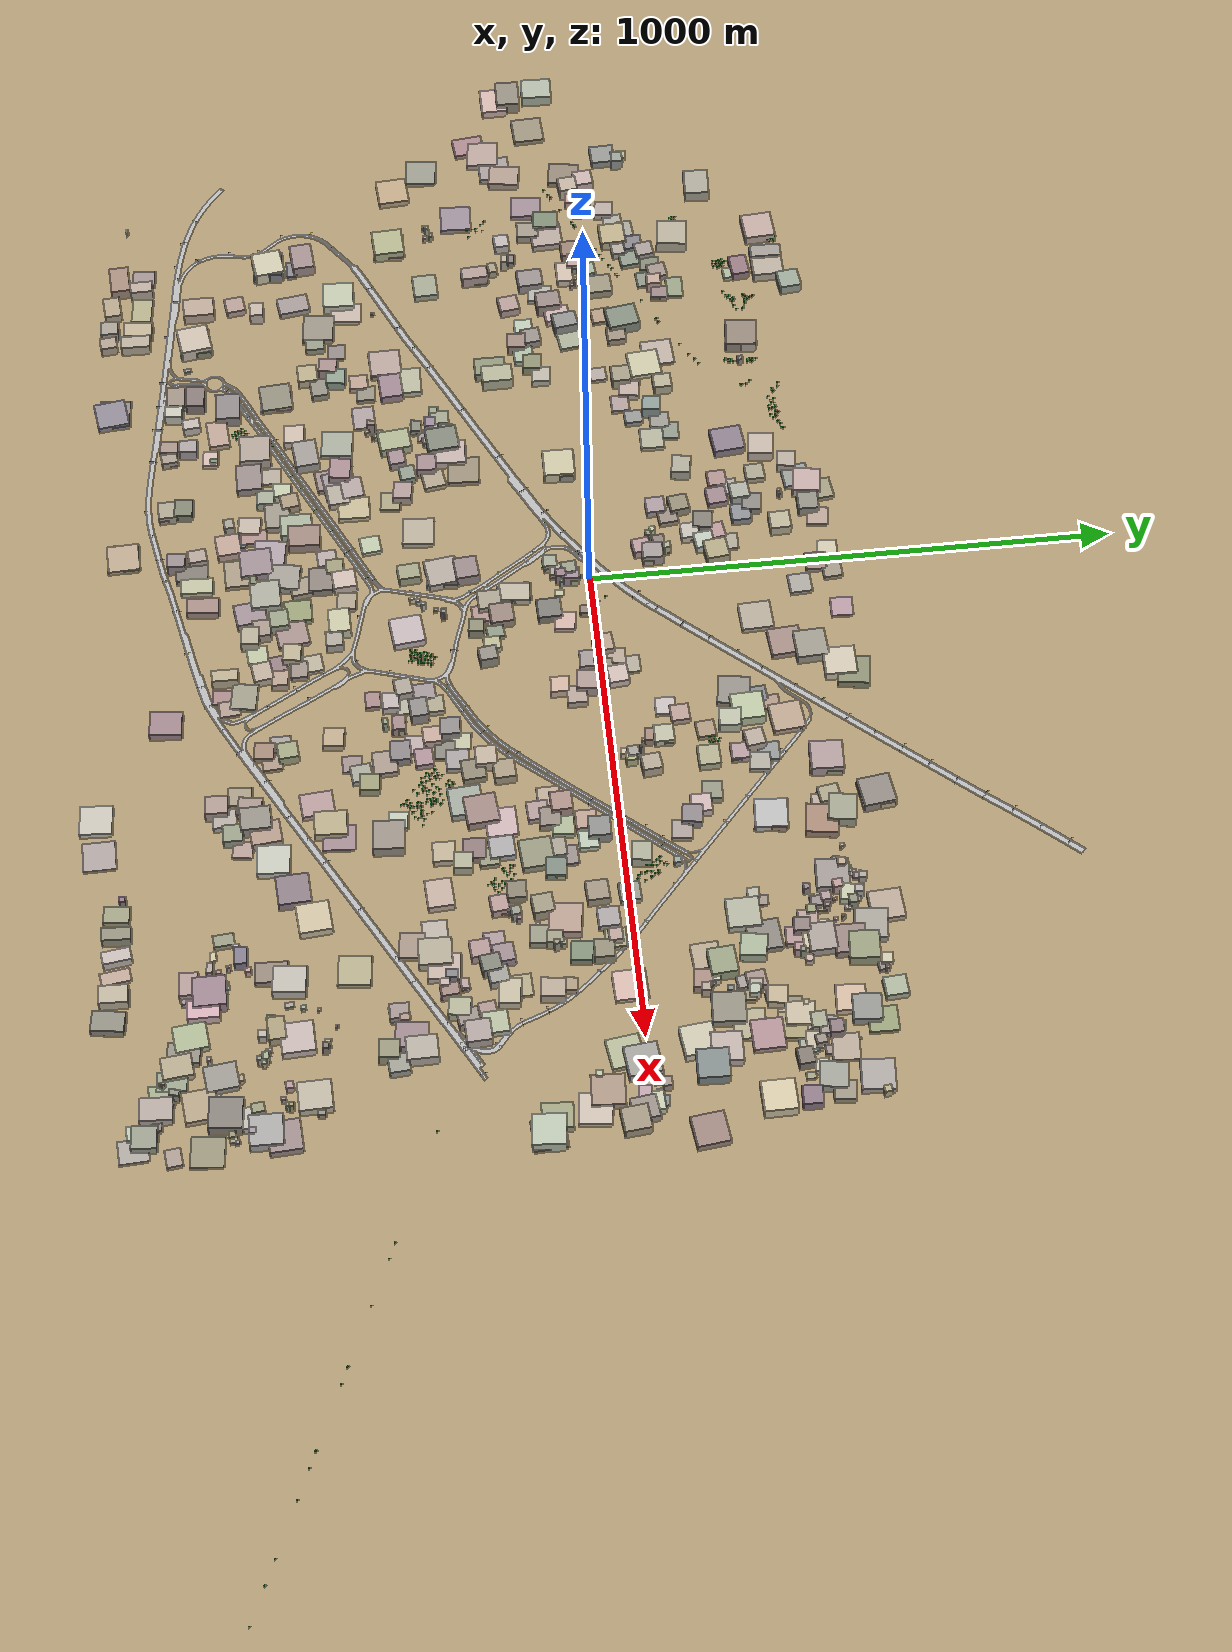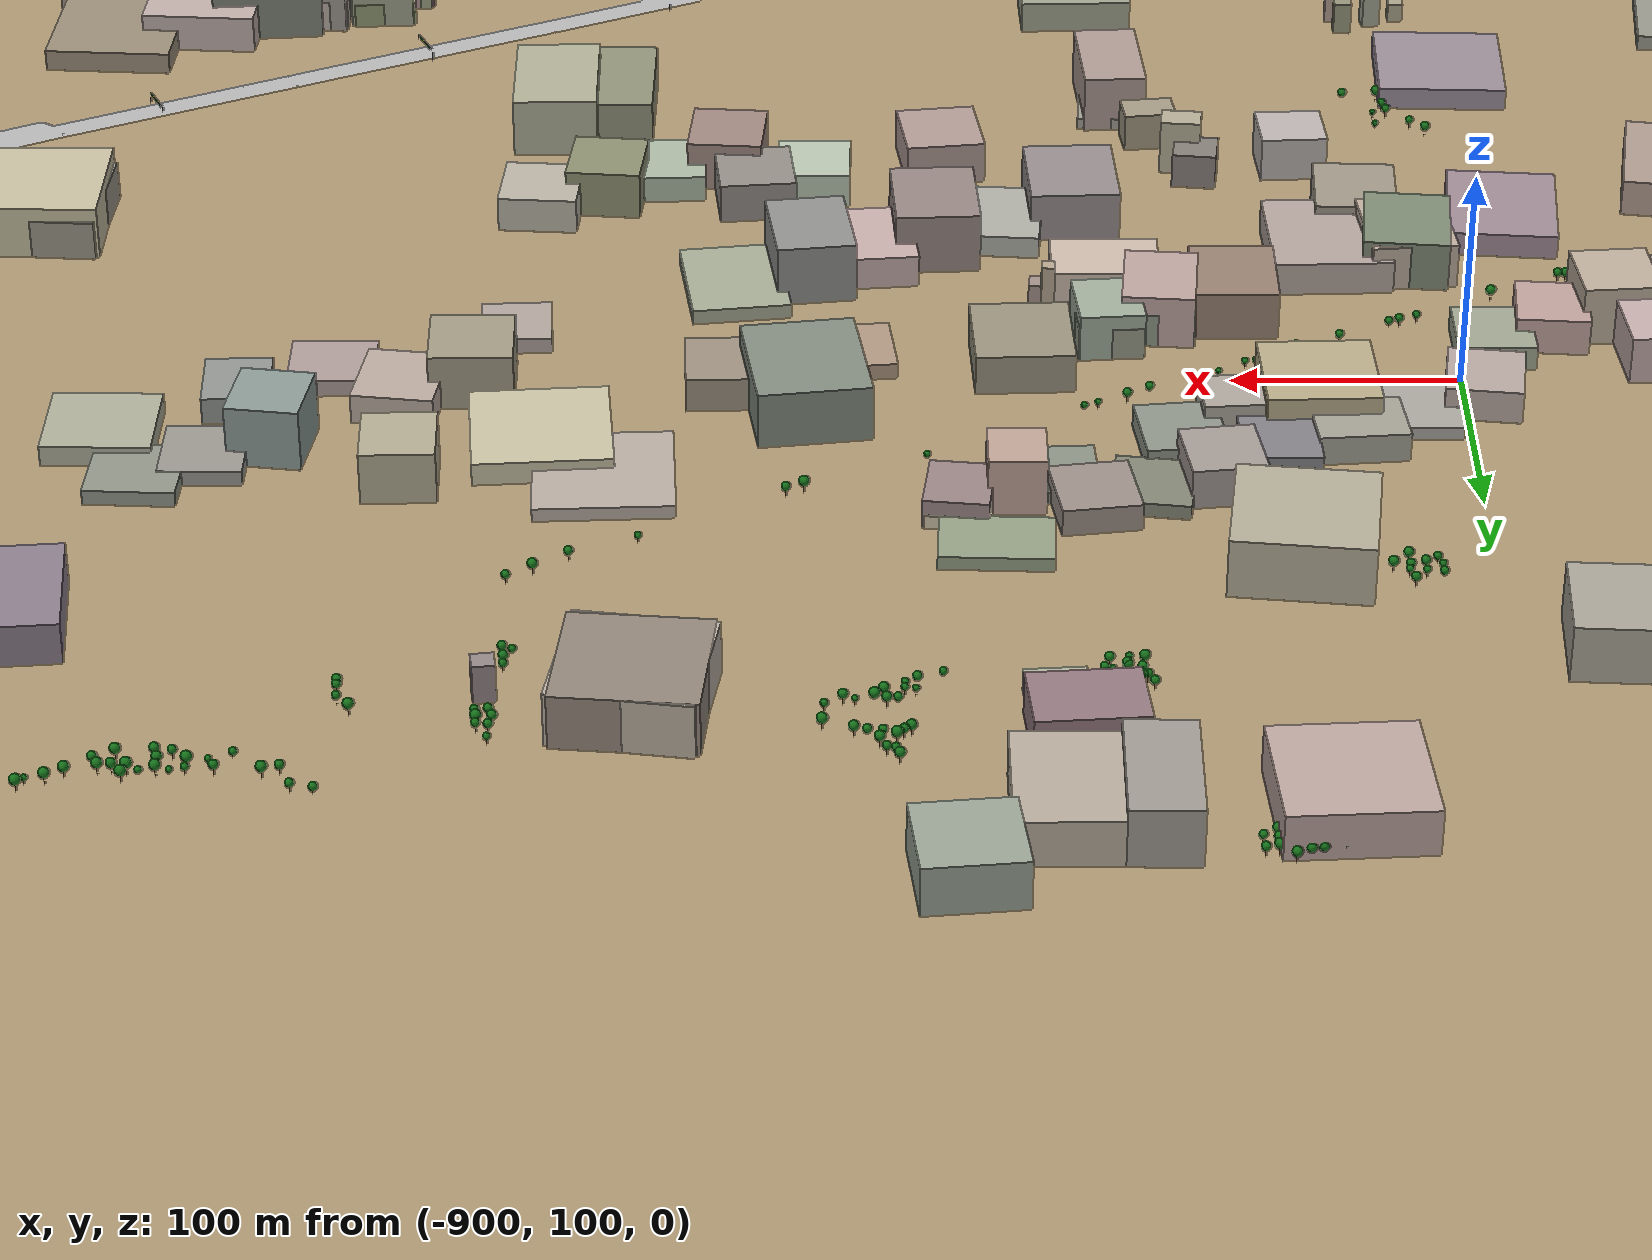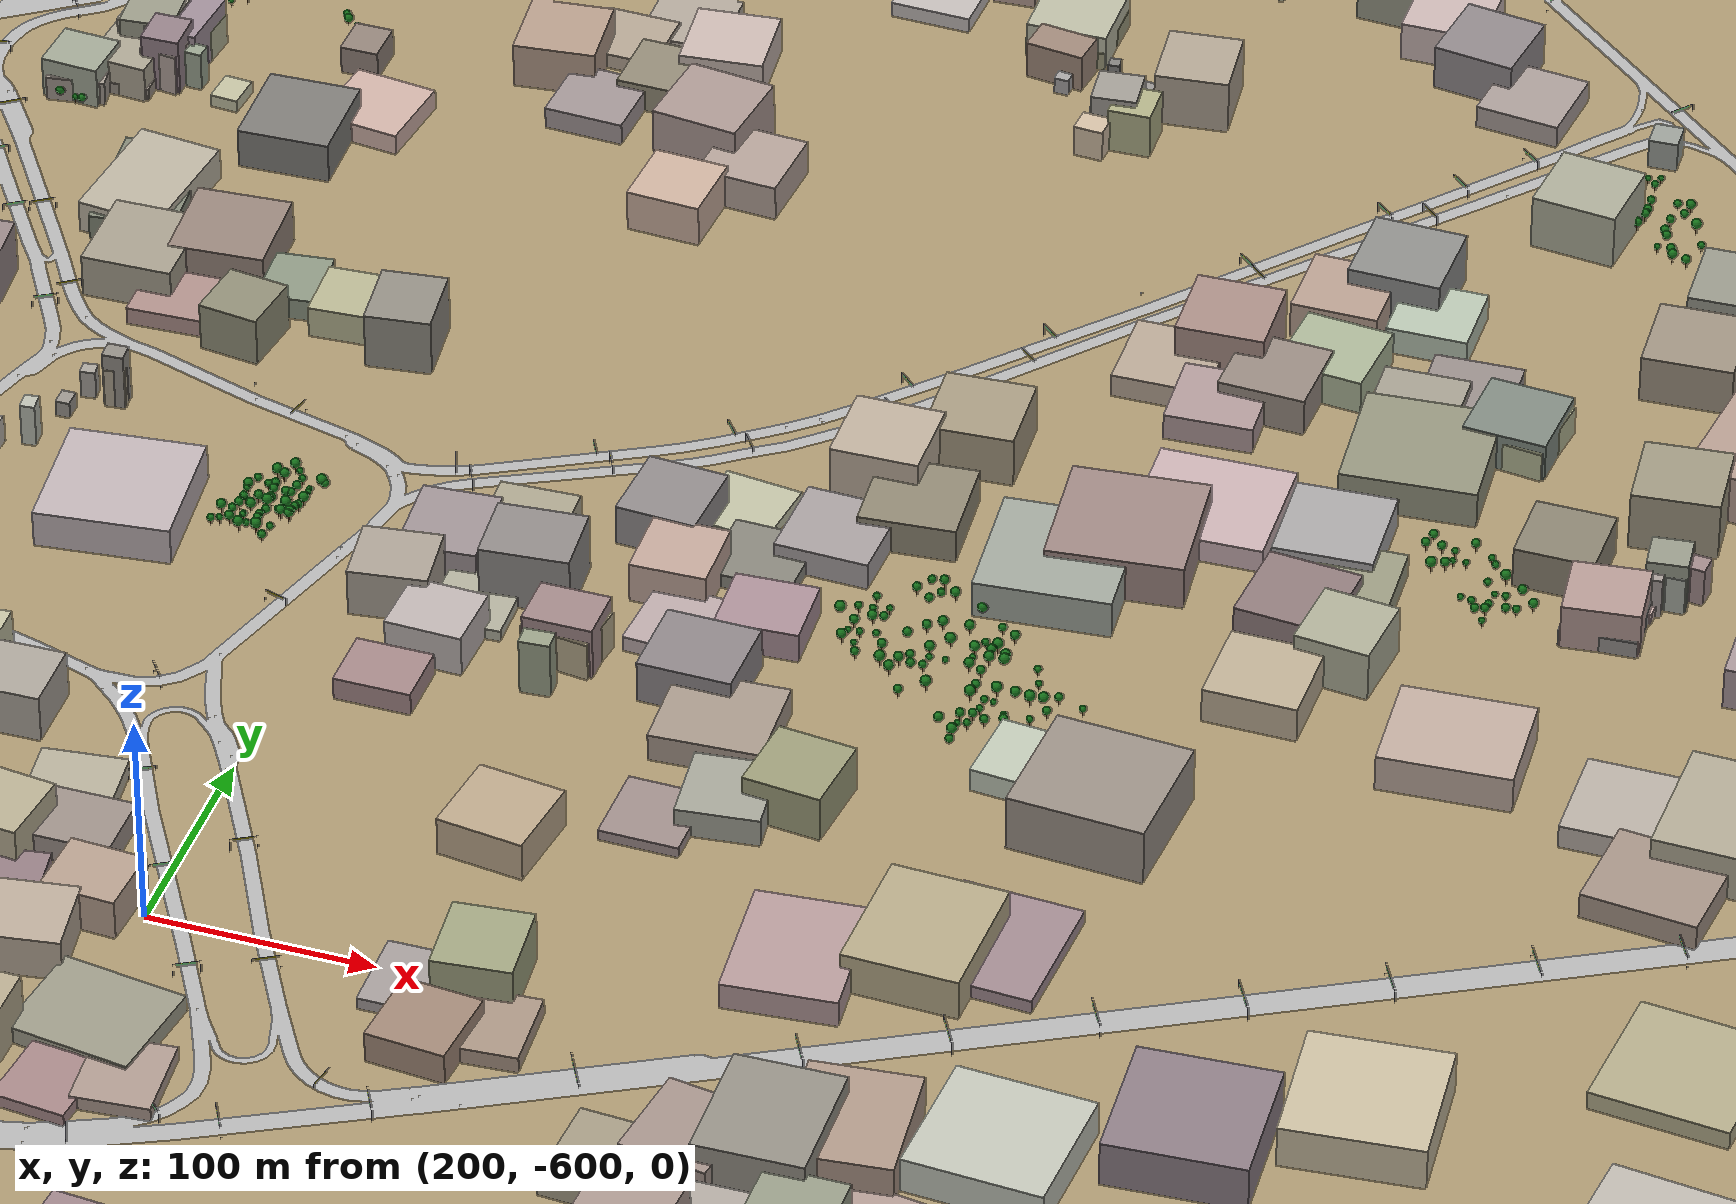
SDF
<?xml version="1.0" ?>
<!--
  Generated by sumo_world_builder.py
  Road model: crossroad_road
  Objects: 1273 models
-->
<sdf version="1.9">
    <world name="crossroad_world">

    <!-- ── Required Gazebo Harmonic plugins ──────────────────── -->
    <plugin filename="gz-sim-physics-system"
            name="gz::sim::systems::Physics"/>
    <plugin filename="gz-sim-user-commands-system"
            name="gz::sim::systems::UserCommands"/>
    <plugin filename="gz-sim-scene-broadcaster-system"
            name="gz::sim::systems::SceneBroadcaster"/>
    <plugin filename="gz-sim-sensors-system"
            name="gz::sim::systems::Sensors">
      <render_engine>ogre2</render_engine>
    </plugin>
    <plugin filename="gz-sim-imu-system"
            name="gz::sim::systems::Imu"/>
    <plugin filename="gz-sim-navsat-system"
            name="gz::sim::systems::NavSat"/>
    <plugin filename="gz-sim-magnetometer-system"
            name="gz::sim::systems::Magnetometer"/>
    <plugin filename="gz-sim-air-pressure-system"
            name="gz::sim::systems::AirPressure"/>

    <!-- ── Scene ─────────────────────────────────────────────── -->
    <scene>
      <ambient>0.6 0.6 0.6 1</ambient>
      <background>0.55 0.65 0.80 1</background>
      <sky>
        <clouds><speed>10</speed></clouds>
      </sky>
      <shadows>true</shadows>
    </scene>

    <!-- ── Lighting ──────────────────────────────────────────── -->
    <light name="sun" type="directional">
      <cast_shadows>true</cast_shadows>
      <pose>0 0 10 0 0 0</pose>
      <diffuse>0.95 0.92 0.85 1</diffuse>
      <specular>0.25 0.25 0.25 1</specular>
      <direction>-0.5 0.1 -0.9</direction>
    </light>

    <!-- ── Physics ───────────────────────────────────────────── -->
    <gravity>0 0 -9.8</gravity>
    <magnetic_field>5.5645e-06 2.2876e-05 -4.2388e-05</magnetic_field>
    <atmosphere type="adiabatic"/>

    <physics name="default" type="ode">
      <max_step_size>0.004</max_step_size>
      <real_time_factor>1.0</real_time_factor>
      <real_time_update_rate>250</real_time_update_rate>
    </physics>

    <spherical_coordinates>
      <surface_model>EARTH_WGS84</surface_model>
      <world_frame_orientation>ENU</world_frame_orientation>
      <latitude_deg>25.305814</latitude_deg>
      <longitude_deg>55.374516</longitude_deg>
      <elevation>10.0</elevation>
      <heading_deg>0</heading_deg>
    </spherical_coordinates>

    <!-- ── Ground plane (below road, catches shadows) ─────────── -->
    <model name="ground_plane">
      <static>true</static>
      <pose>0 0 -0.05 0 0 0</pose>
      <self_collide>false</self_collide>
      <link name="link">
        <pose>0 0 0 0 0 0</pose>
        <collision name="collision">
          <geometry>
            <plane>
              <normal>0 0 1</normal>
              <size>10000 10000</size>
            </plane>
          </geometry>
        </collision>
        <visual name="visual">
          <geometry>
            <plane>
              <normal>0 0 1</normal>
              <size>15000 15000</size>
            </plane>
          </geometry>
          <material>
            <!-- Sandy/dry earth tone — suits UAE environment -->
            <ambient>0.68 0.60 0.45 1</ambient>
            <diffuse>0.68 0.60 0.45 1</diffuse>
          </material>
        </visual>
      </link>
    </model>

    <!-- ── Road network mesh ──────────────────────────────────── -->
    <include>
      <uri>model://crossroad_road</uri>
      <pose>0 0 0.2 0 0 0</pose>
    </include>

    <!-- ── Scene objects ──────────────────────────────────────── -->

    <model name="tl_0">
      <static>true</static>
      <pose>-548.470 -724.925 0 0 0 4.614</pose>
      <link name="link">
        <visual name="pole">
          <pose>0 0 2.750 0 0 0</pose>
          <geometry><cylinder><radius>0.06</radius>
            <length>5.50</length></cylinder></geometry>
          <material><ambient>0.25 0.25 0.25 1</ambient><diffuse>0.25 0.25 0.25 1</diffuse></material>
        </visual>
        <visual name="housing">
          <pose>0 0 5.950 0 0 0</pose>
          <geometry><box><size>0.33 0.33 0.9</size></box></geometry>
          <material><ambient>0.08 0.08 0.08 1</ambient><diffuse>0.08 0.08 0.08 1</diffuse></material>
        </visual>
        <visual name="red">
          <pose>0 0 6.250 0 0 0</pose>
          <geometry><sphere><radius>0.09</radius></sphere></geometry>
          <material><ambient>0.90 0.05 0.05 1</ambient><diffuse>0.90 0.05 0.05 1</diffuse><emissive>0.6 0 0 1</emissive></material>
        </visual>
        <visual name="amber">
          <pose>0 0 5.950 0 0 0</pose>
          <geometry><sphere><radius>0.09</radius></sphere></geometry>
          <material><ambient>0.90 0.55 0.00 1</ambient><diffuse>0.90 0.55 0.00 1</diffuse></material>
        </visual>
        <visual name="green">
          <pose>0 0 5.650 0 0 0</pose>
          <geometry><sphere><radius>0.09</radius></sphere></geometry>
          <material><ambient>0.00 0.78 0.00 1</ambient><diffuse>0.00 0.78 0.00 1</diffuse></material>
        </visual>
        <collision name="col">
          <pose>0 0 2.750 0 0 0</pose>
          <geometry><cylinder><radius>0.06</radius>
            <length>5.50</length></cylinder></geometry>
        </collision>
      </link>
    </model>

    <model name="tl_1">
      <static>true</static>
      <pose>2.700 -309.345 0 0 0 1.276</pose>
      <link name="link">
        <visual name="pole">
          <pose>0 0 2.750 0 0 0</pose>
          <geometry><cylinder><radius>0.06</radius>
            <length>5.50</length></cylinder></geometry>
          <material><ambient>0.25 0.25 0.25 1</ambient><diffuse>0.25 0.25 0.25 1</diffuse></material>
        </visual>
        <visual name="housing">
          <pose>0 0 5.950 0 0 0</pose>
          <geometry><box><size>0.33 0.33 0.9</size></box></geometry>
          <material><ambient>0.08 0.08 0.08 1</ambient><diffuse>0.08 0.08 0.08 1</diffuse></material>
        </visual>
        <visual name="red">
          <pose>0 0 6.250 0 0 0</pose>
          <geometry><sphere><radius>0.09</radius></sphere></geometry>
          <material><ambient>0.90 0.05 0.05 1</ambient><diffuse>0.90 0.05 0.05 1</diffuse><emissive>0.6 0 0 1</emissive></material>
        </visual>
        <visual name="amber">
          <pose>0 0 5.950 0 0 0</pose>
          <geometry><sphere><radius>0.09</radius></sphere></geometry>
          <material><ambient>0.90 0.55 0.00 1</ambient><diffuse>0.90 0.55 0.00 1</diffuse></material>
        </visual>
        <visual name="green">
          <pose>0 0 5.650 0 0 0</pose>
          <geometry><sphere><radius>0.09</radius></sphere></geometry>
          <material><ambient>0.00 0.78 0.00 1</ambient><diffuse>0.00 0.78 0.00 1</diffuse></material>
        </visual>
        <collision name="col">
          <pose>0 0 2.750 0 0 0</pose>
          <geometry><cylinder><radius>0.06</radius>
            <length>5.50</length></cylinder></geometry>
        </collision>
      </link>
    </model>

    <model name="tl_2">
      <static>true</static>
      <pose>70.780 -450.275 0 0 0 2.885</pose>
      <link name="link">
        <visual name="pole">
          <pose>0 0 2.750 0 0 0</pose>
          <geometry><cylinder><radius>0.06</radius>
            <length>5.50</length></cylinder></geometry>
          <material><ambient>0.25 0.25 0.25 1</ambient><diffuse>0.25 0.25 0.25 1</diffuse></material>
        </visual>
        <visual name="housing">
          <pose>0 0 5.950 0 0 0</pose>
          <geometry><box><size>0.33 0.33 0.9</size></box></geometry>
          <material><ambient>0.08 0.08 0.08 1</ambient><diffuse>0.08 0.08 0.08 1</diffuse></material>
        </visual>
        <visual name="red">
          <pose>0 0 6.250 0 0 0</pose>
          <geometry><sphere><radius>0.09</radius></sphere></geometry>
          <material><ambient>0.90 0.05 0.05 1</ambient><diffuse>0.90 0.05 0.05 1</diffuse><emissive>0.6 0 0 1</emissive></material>
        </visual>
        <visual name="amber">
          <pose>0 0 5.950 0 0 0</pose>
          <geometry><sphere><radius>0.09</radius></sphere></geometry>
          <material><ambient>0.90 0.55 0.00 1</ambient><diffuse>0.90 0.55 0.00 1</diffuse></material>
        </visual>
        <visual name="green">
          <pose>0 0 5.650 0 0 0</pose>
          <geometry><sphere><radius>0.09</radius></sphere></geometry>
          <material><ambient>0.00 0.78 0.00 1</ambient><diffuse>0.00 0.78 0.00 1</diffuse></material>
        </visual>
        <collision name="col">
          <pose>0 0 2.750 0 0 0</pose>
          <geometry><cylinder><radius>0.06</radius>
            <length>5.50</length></cylinder></geometry>
        </collision>
      </link>
    </model>

    <model name="tl_3">
      <static>true</static>
      <pose>118.100 -262.215 0 0 0 6.044</pose>
      <link name="link">
        <visual name="pole">
          <pose>0 0 2.750 0 0 0</pose>
          <geometry><cylinder><radius>0.06</radius>
            <length>5.50</length></cylinder></geometry>
          <material><ambient>0.25 0.25 0.25 1</ambient><diffuse>0.25 0.25 0.25 1</diffuse></material>
        </visual>
        <visual name="housing">
          <pose>0 0 5.950 0 0 0</pose>
          <geometry><box><size>0.33 0.33 0.9</size></box></geometry>
          <material><ambient>0.08 0.08 0.08 1</ambient><diffuse>0.08 0.08 0.08 1</diffuse></material>
        </visual>
        <visual name="red">
          <pose>0 0 6.250 0 0 0</pose>
          <geometry><sphere><radius>0.09</radius></sphere></geometry>
          <material><ambient>0.90 0.05 0.05 1</ambient><diffuse>0.90 0.05 0.05 1</diffuse><emissive>0.6 0 0 1</emissive></material>
        </visual>
        <visual name="amber">
          <pose>0 0 5.950 0 0 0</pose>
          <geometry><sphere><radius>0.09</radius></sphere></geometry>
          <material><ambient>0.90 0.55 0.00 1</ambient><diffuse>0.90 0.55 0.00 1</diffuse></material>
        </visual>
        <visual name="green">
          <pose>0 0 5.650 0 0 0</pose>
          <geometry><sphere><radius>0.09</radius></sphere></geometry>
          <material><ambient>0.00 0.78 0.00 1</ambient><diffuse>0.00 0.78 0.00 1</diffuse></material>
        </visual>
        <collision name="col">
          <pose>0 0 2.750 0 0 0</pose>
          <geometry><cylinder><radius>0.06</radius>
            <length>5.50</length></cylinder></geometry>
        </collision>
      </link>
    </model>

    <model name="tl_4">
      <static>true</static>
      <pose>193.120 -356.535 0 0 0 4.418</pose>
      <link name="link">
        <visual name="pole">
          <pose>0 0 2.750 0 0 0</pose>
          <geometry><cylinder><radius>0.06</radius>
            <length>5.50</length></cylinder></geometry>
          <material><ambient>0.25 0.25 0.25 1</ambient><diffuse>0.25 0.25 0.25 1</diffuse></material>
        </visual>
        <visual name="housing">
          <pose>0 0 5.950 0 0 0</pose>
          <geometry><box><size>0.33 0.33 0.9</size></box></geometry>
          <material><ambient>0.08 0.08 0.08 1</ambient><diffuse>0.08 0.08 0.08 1</diffuse></material>
        </visual>
        <visual name="red">
          <pose>0 0 6.250 0 0 0</pose>
          <geometry><sphere><radius>0.09</radius></sphere></geometry>
          <material><ambient>0.90 0.05 0.05 1</ambient><diffuse>0.90 0.05 0.05 1</diffuse><emissive>0.6 0 0 1</emissive></material>
        </visual>
        <visual name="amber">
          <pose>0 0 5.950 0 0 0</pose>
          <geometry><sphere><radius>0.09</radius></sphere></geometry>
          <material><ambient>0.90 0.55 0.00 1</ambient><diffuse>0.90 0.55 0.00 1</diffuse></material>
        </visual>
        <visual name="green">
          <pose>0 0 5.650 0 0 0</pose>
          <geometry><sphere><radius>0.09</radius></sphere></geometry>
          <material><ambient>0.00 0.78 0.00 1</ambient><diffuse>0.00 0.78 0.00 1</diffuse></material>
        </visual>
        <collision name="col">
          <pose>0 0 2.750 0 0 0</pose>
          <geometry><cylinder><radius>0.06</radius>
            <length>5.50</length></cylinder></geometry>
        </collision>
      </link>
    </model>

    <model name="tl_5">
      <static>true</static>
      <pose>464.175 -99.170 0 0 0 4.010</pose>
      <link name="link">
        <visual name="pole">
          <pose>0 0 2.750 0 0 0</pose>
          <geometry><cylinder><radius>0.06</radius>
            <length>5.50</length></cylinder></geometry>
          <material><ambient>0.25 0.25 0.25 1</ambient><diffuse>0.25 0.25 0.25 1</diffuse></material>
        </visual>
        <visual name="housing">
          <pose>0 0 5.950 0 0 0</pose>
          <geometry><box><size>0.33 0.33 0.9</size></box></geometry>
          <material><ambient>0.08 0.08 0.08 1</ambient><diffuse>0.08 0.08 0.08 1</diffuse></material>
        </visual>
        <visual name="red">
          <pose>0 0 6.250 0 0 0</pose>
          <geometry><sphere><radius>0.09</radius></sphere></geometry>
          <material><ambient>0.90 0.05 0.05 1</ambient><diffuse>0.90 0.05 0.05 1</diffuse><emissive>0.6 0 0 1</emissive></material>
        </visual>
        <visual name="amber">
          <pose>0 0 5.950 0 0 0</pose>
          <geometry><sphere><radius>0.09</radius></sphere></geometry>
          <material><ambient>0.90 0.55 0.00 1</ambient><diffuse>0.90 0.55 0.00 1</diffuse></material>
        </visual>
        <visual name="green">
          <pose>0 0 5.650 0 0 0</pose>
          <geometry><sphere><radius>0.09</radius></sphere></geometry>
          <material><ambient>0.00 0.78 0.00 1</ambient><diffuse>0.00 0.78 0.00 1</diffuse></material>
        </visual>
        <collision name="col">
          <pose>0 0 2.750 0 0 0</pose>
          <geometry><cylinder><radius>0.06</radius>
            <length>5.50</length></cylinder></geometry>
        </collision>
      </link>
    </model>

    <model name="tl_6">
      <static>true</static>
      <pose>-411.695 -587.010 0 0 0 0.448</pose>
      <link name="link">
        <visual name="pole">
          <pose>0 0 2.750 0 0 0</pose>
          <geometry><cylinder><radius>0.06</radius>
            <length>5.50</length></cylinder></geometry>
          <material><ambient>0.25 0.25 0.25 1</ambient><diffuse>0.25 0.25 0.25 1</diffuse></material>
        </visual>
        <visual name="housing">
          <pose>0 0 5.950 0 0 0</pose>
          <geometry><box><size>0.33 0.33 0.9</size></box></geometry>
          <material><ambient>0.08 0.08 0.08 1</ambient><diffuse>0.08 0.08 0.08 1</diffuse></material>
        </visual>
        <visual name="red">
          <pose>0 0 6.250 0 0 0</pose>
          <geometry><sphere><radius>0.09</radius></sphere></geometry>
          <material><ambient>0.90 0.05 0.05 1</ambient><diffuse>0.90 0.05 0.05 1</diffuse><emissive>0.6 0 0 1</emissive></material>
        </visual>
        <visual name="amber">
          <pose>0 0 5.950 0 0 0</pose>
          <geometry><sphere><radius>0.09</radius></sphere></geometry>
          <material><ambient>0.90 0.55 0.00 1</ambient><diffuse>0.90 0.55 0.00 1</diffuse></material>
        </visual>
        <visual name="green">
          <pose>0 0 5.650 0 0 0</pose>
          <geometry><sphere><radius>0.09</radius></sphere></geometry>
          <material><ambient>0.00 0.78 0.00 1</ambient><diffuse>0.00 0.78 0.00 1</diffuse></material>
        </visual>
        <collision name="col">
          <pose>0 0 2.750 0 0 0</pose>
          <geometry><cylinder><radius>0.06</radius>
            <length>5.50</length></cylinder></geometry>
        </collision>
      </link>
    </model>

    <model name="tl_7">
      <static>true</static>
      <pose>-414.715 -610.000 0 0 0 3.631</pose>
      <link name="link">
        <visual name="pole">
          <pose>0 0 2.750 0 0 0</pose>
          <geometry><cylinder><radius>0.06</radius>
            <length>5.50</length></cylinder></geometry>
          <material><ambient>0.25 0.25 0.25 1</ambient><diffuse>0.25 0.25 0.25 1</diffuse></material>
        </visual>
        <visual name="housing">
          <pose>0 0 5.950 0 0 0</pose>
          <geometry><box><size>0.33 0.33 0.9</size></box></geometry>
          <material><ambient>0.08 0.08 0.08 1</ambient><diffuse>0.08 0.08 0.08 1</diffuse></material>
        </visual>
        <visual name="red">
          <pose>0 0 6.250 0 0 0</pose>
          <geometry><sphere><radius>0.09</radius></sphere></geometry>
          <material><ambient>0.90 0.05 0.05 1</ambient><diffuse>0.90 0.05 0.05 1</diffuse><emissive>0.6 0 0 1</emissive></material>
        </visual>
        <visual name="amber">
          <pose>0 0 5.950 0 0 0</pose>
          <geometry><sphere><radius>0.09</radius></sphere></geometry>
          <material><ambient>0.90 0.55 0.00 1</ambient><diffuse>0.90 0.55 0.00 1</diffuse></material>
        </visual>
        <visual name="green">
          <pose>0 0 5.650 0 0 0</pose>
          <geometry><sphere><radius>0.09</radius></sphere></geometry>
          <material><ambient>0.00 0.78 0.00 1</ambient><diffuse>0.00 0.78 0.00 1</diffuse></material>
        </visual>
        <collision name="col">
          <pose>0 0 2.750 0 0 0</pose>
          <geometry><cylinder><radius>0.06</radius>
            <length>5.50</length></cylinder></geometry>
        </collision>
      </link>
    </model>

    <model name="tl_8">
      <static>true</static>
      <pose>460.105 -80.420 0 0 0 0.870</pose>
      <link name="link">
        <visual name="pole">
          <pose>0 0 2.750 0 0 0</pose>
          <geometry><cylinder><radius>0.06</radius>
            <length>5.50</length></cylinder></geometry>
          <material><ambient>0.25 0.25 0.25 1</ambient><diffuse>0.25 0.25 0.25 1</diffuse></material>
        </visual>
        <visual name="housing">
          <pose>0 0 5.950 0 0 0</pose>
          <geometry><box><size>0.33 0.33 0.9</size></box></geometry>
          <material><ambient>0.08 0.08 0.08 1</ambient><diffuse>0.08 0.08 0.08 1</diffuse></material>
        </visual>
        <visual name="red">
          <pose>0 0 6.250 0 0 0</pose>
          <geometry><sphere><radius>0.09</radius></sphere></geometry>
          <material><ambient>0.90 0.05 0.05 1</ambient><diffuse>0.90 0.05 0.05 1</diffuse><emissive>0.6 0 0 1</emissive></material>
        </visual>
        <visual name="amber">
          <pose>0 0 5.950 0 0 0</pose>
          <geometry><sphere><radius>0.09</radius></sphere></geometry>
          <material><ambient>0.90 0.55 0.00 1</ambient><diffuse>0.90 0.55 0.00 1</diffuse></material>
        </visual>
        <visual name="green">
          <pose>0 0 5.650 0 0 0</pose>
          <geometry><sphere><radius>0.09</radius></sphere></geometry>
          <material><ambient>0.00 0.78 0.00 1</ambient><diffuse>0.00 0.78 0.00 1</diffuse></material>
        </visual>
        <collision name="col">
          <pose>0 0 2.750 0 0 0</pose>
          <geometry><cylinder><radius>0.06</radius>
            <length>5.50</length></cylinder></geometry>
        </collision>
      </link>
    </model>

    <model name="tl_9">
      <static>true</static>
      <pose>522.935 230.430 0 0 0 2.424</pose>
      <link name="link">
        <visual name="pole">
          <pose>0 0 2.750 0 0 0</pose>
          <geometry><cylinder><radius>0.06</radius>
            <length>5.50</length></cylinder></geometry>
          <material><ambient>0.25 0.25 0.25 1</ambient><diffuse>0.25 0.25 0.25 1</diffuse></material>
        </visual>
        <visual name="housing">
          <pose>0 0 5.950 0 0 0</pose>
          <geometry><box><size>0.33 0.33 0.9</size></box></geometry>
          <material><ambient>0.08 0.08 0.08 1</ambient><diffuse>0.08 0.08 0.08 1</diffuse></material>
        </visual>
        <visual name="red">
          <pose>0 0 6.250 0 0 0</pose>
          <geometry><sphere><radius>0.09</radius></sphere></geometry>
          <material><ambient>0.90 0.05 0.05 1</ambient><diffuse>0.90 0.05 0.05 1</diffuse><emissive>0.6 0 0 1</emissive></material>
        </visual>
        <visual name="amber">
          <pose>0 0 5.950 0 0 0</pose>
          <geometry><sphere><radius>0.09</radius></sphere></geometry>
          <material><ambient>0.90 0.55 0.00 1</ambient><diffuse>0.90 0.55 0.00 1</diffuse></material>
        </visual>
        <visual name="green">
          <pose>0 0 5.650 0 0 0</pose>
          <geometry><sphere><radius>0.09</radius></sphere></geometry>
          <material><ambient>0.00 0.78 0.00 1</ambient><diffuse>0.00 0.78 0.00 1</diffuse></material>
        </visual>
        <collision name="col">
          <pose>0 0 2.750 0 0 0</pose>
          <geometry><cylinder><radius>0.06</radius>
            <length>5.50</length></cylinder></geometry>
        </collision>
      </link>
    </model>

    <model name="gantry_0">
      <static>true</static>
      <pose>-3.222 -343.393 0 0 0 -0.270</pose>
      <link name="link">
        <visual name="post_l">
          <pose>-5.700 0 2.925 0 0 0</pose>
          <geometry><cylinder><radius>0.1</radius>
            <length>5.85</length></cylinder></geometry>
          <material><ambient>0.30 0.30 0.35 1</ambient><diffuse>0.30 0.30 0.35 1</diffuse></material>
        </visual>
        <visual name="post_r">
          <pose>5.700 0 2.925 0 0 0</pose>
          <geometry><cylinder><radius>0.1</radius>
            <length>5.85</length></cylinder></geometry>
          <material><ambient>0.30 0.30 0.35 1</ambient><diffuse>0.30 0.30 0.35 1</diffuse></material>
        </visual>
        <visual name="beam">
          <pose>0 0 6.000 0 0 0</pose>
          <geometry><box>
            <size>11.400 0.22 0.22</size></box></geometry>
          <material><ambient>0.30 0.30 0.35 1</ambient><diffuse>0.30 0.30 0.35 1</diffuse></material>
        </visual>
        <visual name="sign_border">
          <pose>0 -0.14 5.450 0 0 0</pose>
          <geometry><box>
            <size>8.288 0.04 0.92</size></box></geometry>
          <material><ambient>0.90 0.85 0.10 1</ambient><diffuse>0.90 0.85 0.10 1</diffuse></material>
        </visual>
        <visual name="sign_panel">
          <pose>0 -0.15 5.450 0 0 0</pose>
          <geometry><box>
            <size>8.208 0.05 0.86</size></box></geometry>
          <material><ambient>0.05 0.38 0.10 1</ambient><diffuse>0.05 0.38 0.10 1</diffuse></material>
        </visual>
        <collision name="col_post_l">
          <pose>-5.700 0 2.925 0 0 0</pose>
          <geometry><cylinder><radius>0.1</radius>
            <length>5.85</length></cylinder></geometry>
        </collision>
        <collision name="col_post_r">
          <pose>5.700 0 2.925 0 0 0</pose>
          <geometry><cylinder><radius>0.1</radius>
            <length>5.85</length></cylinder></geometry>
        </collision>
        <collision name="col_beam">
          <pose>0 0 6.000 0 0 0</pose>
          <geometry><box>
            <size>11.400 0.22 0.22</size></box></geometry>
        </collision>
      </link>
    </model>

    <model name="gantry_1">
      <static>true</static>
      <pose>45.629 -440.178 0 0 0 1.314</pose>
      <link name="link">
        <visual name="post_l">
          <pose>-5.700 0 2.925 0 0 0</pose>
          <geometry><cylinder><radius>0.1</radius>
            <length>5.85</length></cylinder></geometry>
          <material><ambient>0.30 0.30 0.35 1</ambient><diffuse>0.30 0.30 0.35 1</diffuse></material>
        </visual>
        <visual name="post_r">
          <pose>5.700 0 2.925 0 0 0</pose>
          <geometry><cylinder><radius>0.1</radius>
            <length>5.85</length></cylinder></geometry>
          <material><ambient>0.30 0.30 0.35 1</ambient><diffuse>0.30 0.30 0.35 1</diffuse></material>
        </visual>
        <visual name="beam">
          <pose>0 0 6.000 0 0 0</pose>
          <geometry><box>
            <size>11.400 0.22 0.22</size></box></geometry>
          <material><ambient>0.30 0.30 0.35 1</ambient><diffuse>0.30 0.30 0.35 1</diffuse></material>
        </visual>
        <visual name="sign_border">
          <pose>0 -0.14 5.450 0 0 0</pose>
          <geometry><box>
            <size>8.288 0.04 0.92</size></box></geometry>
          <material><ambient>0.90 0.85 0.10 1</ambient><diffuse>0.90 0.85 0.10 1</diffuse></material>
        </visual>
        <visual name="sign_panel">
          <pose>0 -0.15 5.450 0 0 0</pose>
          <geometry><box>
            <size>8.208 0.05 0.86</size></box></geometry>
          <material><ambient>0.05 0.38 0.10 1</ambient><diffuse>0.05 0.38 0.10 1</diffuse></material>
        </visual>
        <collision name="col_post_l">
          <pose>-5.700 0 2.925 0 0 0</pose>
          <geometry><cylinder><radius>0.1</radius>
            <length>5.85</length></cylinder></geometry>
        </collision>
        <collision name="col_post_r">
          <pose>5.700 0 2.925 0 0 0</pose>
          <geometry><cylinder><radius>0.1</radius>
            <length>5.85</length></cylinder></geometry>
        </collision>
        <collision name="col_beam">
          <pose>0 0 6.000 0 0 0</pose>
          <geometry><box>
            <size>11.400 0.22 0.22</size></box></geometry>
        </collision>
      </link>
    </model>

    <model name="gantry_2">
      <static>true</static>
      <pose>141.179 -271.351 0 0 0 4.473</pose>
      <link name="link">
        <visual name="post_l">
          <pose>-5.700 0 2.925 0 0 0</pose>
          <geometry><cylinder><radius>0.1</radius>
            <length>5.85</length></cylinder></geometry>
          <material><ambient>0.30 0.30 0.35 1</ambient><diffuse>0.30 0.30 0.35 1</diffuse></material>
        </visual>
        <visual name="post_r">
          <pose>5.700 0 2.925 0 0 0</pose>
          <geometry><cylinder><radius>0.1</radius>
            <length>5.85</length></cylinder></geometry>
          <material><ambient>0.30 0.30 0.35 1</ambient><diffuse>0.30 0.30 0.35 1</diffuse></material>
        </visual>
        <visual name="beam">
          <pose>0 0 6.000 0 0 0</pose>
          <geometry><box>
            <size>11.400 0.22 0.22</size></box></geometry>
          <material><ambient>0.30 0.30 0.35 1</ambient><diffuse>0.30 0.30 0.35 1</diffuse></material>
        </visual>
        <visual name="sign_border">
          <pose>0 -0.14 5.450 0 0 0</pose>
          <geometry><box>
            <size>8.288 0.04 0.92</size></box></geometry>
          <material><ambient>0.90 0.85 0.10 1</ambient><diffuse>0.90 0.85 0.10 1</diffuse></material>
        </visual>
        <visual name="sign_panel">
          <pose>0 -0.15 5.450 0 0 0</pose>
          <geometry><box>
            <size>8.208 0.05 0.86</size></box></geometry>
          <material><ambient>0.05 0.38 0.10 1</ambient><diffuse>0.05 0.38 0.10 1</diffuse></material>
        </visual>
        <collision name="col_post_l">
          <pose>-5.700 0 2.925 0 0 0</pose>
          <geometry><cylinder><radius>0.1</radius>
            <length>5.85</length></cylinder></geometry>
        </collision>
        <collision name="col_post_r">
          <pose>5.700 0 2.925 0 0 0</pose>
          <geometry><cylinder><radius>0.1</radius>
            <length>5.85</length></cylinder></geometry>
        </collision>
        <collision name="col_beam">
          <pose>0 0 6.000 0 0 0</pose>
          <geometry><box>
            <size>11.400 0.22 0.22</size></box></geometry>
        </collision>
      </link>
    </model>

    <model name="gantry_3">
      <static>true</static>
      <pose>149.348 -457.128 0 0 0 2.202</pose>
      <link name="link">
        <visual name="post_l">
          <pose>-5.700 0 2.925 0 0 0</pose>
          <geometry><cylinder><radius>0.1</radius>
            <length>5.85</length></cylinder></geometry>
          <material><ambient>0.30 0.30 0.35 1</ambient><diffuse>0.30 0.30 0.35 1</diffuse></material>
        </visual>
        <visual name="post_r">
          <pose>5.700 0 2.925 0 0 0</pose>
          <geometry><cylinder><radius>0.1</radius>
            <length>5.85</length></cylinder></geometry>
          <material><ambient>0.30 0.30 0.35 1</ambient><diffuse>0.30 0.30 0.35 1</diffuse></material>
        </visual>
        <visual name="beam">
          <pose>0 0 6.000 0 0 0</pose>
          <geometry><box>
            <size>11.400 0.22 0.22</size></box></geometry>
          <material><ambient>0.30 0.30 0.35 1</ambient><diffuse>0.30 0.30 0.35 1</diffuse></material>
        </visual>
        <visual name="sign_border">
          <pose>0 -0.14 5.450 0 0 0</pose>
          <geometry><box>
            <size>8.288 0.04 0.92</size></box></geometry>
          <material><ambient>0.90 0.85 0.10 1</ambient><diffuse>0.90 0.85 0.10 1</diffuse></material>
        </visual>
        <visual name="sign_panel">
          <pose>0 -0.15 5.450 0 0 0</pose>
          <geometry><box>
            <size>8.208 0.05 0.86</size></box></geometry>
          <material><ambient>0.05 0.38 0.10 1</ambient><diffuse>0.05 0.38 0.10 1</diffuse></material>
        </visual>
        <collision name="col_post_l">
          <pose>-5.700 0 2.925 0 0 0</pose>
          <geometry><cylinder><radius>0.1</radius>
            <length>5.85</length></cylinder></geometry>
        </collision>
        <collision name="col_post_r">
          <pose>5.700 0 2.925 0 0 0</pose>
          <geometry><cylinder><radius>0.1</radius>
            <length>5.85</length></cylinder></geometry>
        </collision>
        <collision name="col_beam">
          <pose>0 0 6.000 0 0 0</pose>
          <geometry><box>
            <size>11.400 0.22 0.22</size></box></geometry>
        </collision>
      </link>
    </model>

    <model name="gantry_4">
      <static>true</static>
      <pose>167.095 -518.623 0 0 0 0.479</pose>
      <link name="link">
        <visual name="post_l">
          <pose>-5.700 0 2.925 0 0 0</pose>
          <geometry><cylinder><radius>0.1</radius>
            <length>5.85</length></cylinder></geometry>
          <material><ambient>0.30 0.30 0.35 1</ambient><diffuse>0.30 0.30 0.35 1</diffuse></material>
        </visual>
        <visual name="post_r">
          <pose>5.700 0 2.925 0 0 0</pose>
          <geometry><cylinder><radius>0.1</radius>
            <length>5.85</length></cylinder></geometry>
          <material><ambient>0.30 0.30 0.35 1</ambient><diffuse>0.30 0.30 0.35 1</diffuse></material>
        </visual>
        <visual name="beam">
          <pose>0 0 6.000 0 0 0</pose>
          <geometry><box>
            <size>11.400 0.22 0.22</size></box></geometry>
          <material><ambient>0.30 0.30 0.35 1</ambient><diffuse>0.30 0.30 0.35 1</diffuse></material>
        </visual>
        <visual name="sign_border">
          <pose>0 -0.14 5.450 0 0 0</pose>
          <geometry><box>
            <size>8.288 0.04 0.92</size></box></geometry>
          <material><ambient>0.90 0.85 0.10 1</ambient><diffuse>0.90 0.85 0.10 1</diffuse></material>
        </visual>
        <visual name="sign_panel">
          <pose>0 -0.15 5.450 0 0 0</pose>
          <geometry><box>
            <size>8.208 0.05 0.86</size></box></geometry>
          <material><ambient>0.05 0.38 0.10 1</ambient><diffuse>0.05 0.38 0.10 1</diffuse></material>
        </visual>
        <collision name="col_post_l">
          <pose>-5.700 0 2.925 0 0 0</pose>
          <geometry><cylinder><radius>0.1</radius>
            <length>5.85</length></cylinder></geometry>
        </collision>
        <collision name="col_post_r">
          <pose>5.700 0 2.925 0 0 0</pose>
          <geometry><cylinder><radius>0.1</radius>
            <length>5.85</length></cylinder></geometry>
        </collision>
        <collision name="col_beam">
          <pose>0 0 6.000 0 0 0</pose>
          <geometry><box>
            <size>11.400 0.22 0.22</size></box></geometry>
        </collision>
      </link>
    </model>

    <model name="gantry_5">
      <static>true</static>
      <pose>274.331 -709.474 0 0 0 -1.088</pose>
      <link name="link">
        <visual name="post_l">
          <pose>-7.300 0 2.925 0 0 0</pose>
          <geometry><cylinder><radius>0.1</radius>
            <length>5.85</length></cylinder></geometry>
          <material><ambient>0.30 0.30 0.35 1</ambient><diffuse>0.30 0.30 0.35 1</diffuse></material>
        </visual>
        <visual name="post_r">
          <pose>7.300 0 2.925 0 0 0</pose>
          <geometry><cylinder><radius>0.1</radius>
            <length>5.85</length></cylinder></geometry>
          <material><ambient>0.30 0.30 0.35 1</ambient><diffuse>0.30 0.30 0.35 1</diffuse></material>
        </visual>
        <visual name="beam">
          <pose>0 0 6.000 0 0 0</pose>
          <geometry><box>
            <size>14.600 0.22 0.22</size></box></geometry>
          <material><ambient>0.30 0.30 0.35 1</ambient><diffuse>0.30 0.30 0.35 1</diffuse></material>
        </visual>
        <visual name="sign_border">
          <pose>0 -0.14 5.450 0 0 0</pose>
          <geometry><box>
            <size>10.592 0.04 0.92</size></box></geometry>
          <material><ambient>0.90 0.85 0.10 1</ambient><diffuse>0.90 0.85 0.10 1</diffuse></material>
        </visual>
        <visual name="sign_panel">
          <pose>0 -0.15 5.450 0 0 0</pose>
          <geometry><box>
            <size>10.512 0.05 0.86</size></box></geometry>
          <material><ambient>0.05 0.38 0.10 1</ambient><diffuse>0.05 0.38 0.10 1</diffuse></material>
        </visual>
        <collision name="col_post_l">
          <pose>-7.300 0 2.925 0 0 0</pose>
          <geometry><cylinder><radius>0.1</radius>
            <length>5.85</length></cylinder></geometry>
        </collision>
        <collision name="col_post_r">
          <pose>7.300 0 2.925 0 0 0</pose>
          <geometry><cylinder><radius>0.1</radius>
            <length>5.85</length></cylinder></geometry>
        </collision>
        <collision name="col_beam">
          <pose>0 0 6.000 0 0 0</pose>
          <geometry><box>
            <size>14.600 0.22 0.22</size></box></geometry>
        </collision>
      </link>
    </model>

    <model name="gantry_6">
      <static>true</static>
      <pose>220.195 -735.282 0 0 0 -1.170</pose>
      <link name="link">
        <visual name="post_l">
          <pose>-7.300 0 2.925 0 0 0</pose>
          <geometry><cylinder><radius>0.1</radius>
            <length>5.85</length></cylinder></geometry>
          <material><ambient>0.30 0.30 0.35 1</ambient><diffuse>0.30 0.30 0.35 1</diffuse></material>
        </visual>
        <visual name="post_r">
          <pose>7.300 0 2.925 0 0 0</pose>
          <geometry><cylinder><radius>0.1</radius>
            <length>5.85</length></cylinder></geometry>
          <material><ambient>0.30 0.30 0.35 1</ambient><diffuse>0.30 0.30 0.35 1</diffuse></material>
        </visual>
        <visual name="beam">
          <pose>0 0 6.000 0 0 0</pose>
          <geometry><box>
            <size>14.600 0.22 0.22</size></box></geometry>
          <material><ambient>0.30 0.30 0.35 1</ambient><diffuse>0.30 0.30 0.35 1</diffuse></material>
        </visual>
        <visual name="sign_border">
          <pose>0 -0.14 5.450 0 0 0</pose>
          <geometry><box>
            <size>10.592 0.04 0.92</size></box></geometry>
          <material><ambient>0.90 0.85 0.10 1</ambient><diffuse>0.90 0.85 0.10 1</diffuse></material>
        </visual>
        <visual name="sign_panel">
          <pose>0 -0.15 5.450 0 0 0</pose>
          <geometry><box>
            <size>10.512 0.05 0.86</size></box></geometry>
          <material><ambient>0.05 0.38 0.10 1</ambient><diffuse>0.05 0.38 0.10 1</diffuse></material>
        </visual>
        <collision name="col_post_l">
          <pose>-7.300 0 2.925 0 0 0</pose>
          <geometry><cylinder><radius>0.1</radius>
            <length>5.85</length></cylinder></geometry>
        </collision>
        <collision name="col_post_r">
          <pose>7.300 0 2.925 0 0 0</pose>
          <geometry><cylinder><radius>0.1</radius>
            <length>5.85</length></cylinder></geometry>
        </collision>
        <collision name="col_beam">
          <pose>0 0 6.000 0 0 0</pose>
          <geometry><box>
            <size>14.600 0.22 0.22</size></box></geometry>
        </collision>
      </link>
    </model>

    <model name="gantry_7">
      <static>true</static>
      <pose>327.461 -681.595 0 0 0 -1.088</pose>
      <link name="link">
        <visual name="post_l">
          <pose>-7.300 0 2.925 0 0 0</pose>
          <geometry><cylinder><radius>0.1</radius>
            <length>5.85</length></cylinder></geometry>
          <material><ambient>0.30 0.30 0.35 1</ambient><diffuse>0.30 0.30 0.35 1</diffuse></material>
        </visual>
        <visual name="post_r">
          <pose>7.300 0 2.925 0 0 0</pose>
          <geometry><cylinder><radius>0.1</radius>
            <length>5.85</length></cylinder></geometry>
          <material><ambient>0.30 0.30 0.35 1</ambient><diffuse>0.30 0.30 0.35 1</diffuse></material>
        </visual>
        <visual name="beam">
          <pose>0 0 6.000 0 0 0</pose>
          <geometry><box>
            <size>14.600 0.22 0.22</size></box></geometry>
          <material><ambient>0.30 0.30 0.35 1</ambient><diffuse>0.30 0.30 0.35 1</diffuse></material>
        </visual>
        <visual name="sign_border">
          <pose>0 -0.14 5.450 0 0 0</pose>
          <geometry><box>
            <size>10.592 0.04 0.92</size></box></geometry>
          <material><ambient>0.90 0.85 0.10 1</ambient><diffuse>0.90 0.85 0.10 1</diffuse></material>
        </visual>
        <visual name="sign_panel">
          <pose>0 -0.15 5.450 0 0 0</pose>
          <geometry><box>
            <size>10.512 0.05 0.86</size></box></geometry>
          <material><ambient>0.05 0.38 0.10 1</ambient><diffuse>0.05 0.38 0.10 1</diffuse></material>
        </visual>
        <collision name="col_post_l">
          <pose>-7.300 0 2.925 0 0 0</pose>
          <geometry><cylinder><radius>0.1</radius>
            <length>5.85</length></cylinder></geometry>
        </collision>
        <collision name="col_post_r">
          <pose>7.300 0 2.925 0 0 0</pose>
          <geometry><cylinder><radius>0.1</radius>
            <length>5.85</length></cylinder></geometry>
        </collision>
        <collision name="col_beam">
          <pose>0 0 6.000 0 0 0</pose>
          <geometry><box>
            <size>14.600 0.22 0.22</size></box></geometry>
        </collision>
      </link>
    </model>

    <model name="gantry_8">
      <static>true</static>
      <pose>-913.528 -734.026 0 0 0 4.386</pose>
      <link name="link">
        <visual name="post_l">
          <pose>-7.300 0 2.925 0 0 0</pose>
          <geometry><cylinder><radius>0.1</radius>
            <length>5.85</length></cylinder></geometry>
          <material><ambient>0.30 0.30 0.35 1</ambient><diffuse>0.30 0.30 0.35 1</diffuse></material>
        </visual>
        <visual name="post_r">
          <pose>7.300 0 2.925 0 0 0</pose>
          <geometry><cylinder><radius>0.1</radius>
            <length>5.85</length></cylinder></geometry>
          <material><ambient>0.30 0.30 0.35 1</ambient><diffuse>0.30 0.30 0.35 1</diffuse></material>
        </visual>
        <visual name="beam">
          <pose>0 0 6.000 0 0 0</pose>
          <geometry><box>
            <size>14.600 0.22 0.22</size></box></geometry>
          <material><ambient>0.30 0.30 0.35 1</ambient><diffuse>0.30 0.30 0.35 1</diffuse></material>
        </visual>
        <visual name="sign_border">
          <pose>0 -0.14 5.450 0 0 0</pose>
          <geometry><box>
            <size>10.592 0.04 0.92</size></box></geometry>
          <material><ambient>0.90 0.85 0.10 1</ambient><diffuse>0.90 0.85 0.10 1</diffuse></material>
        </visual>
        <visual name="sign_panel">
          <pose>0 -0.15 5.450 0 0 0</pose>
          <geometry><box>
            <size>10.512 0.05 0.86</size></box></geometry>
          <material><ambient>0.05 0.38 0.10 1</ambient><diffuse>0.05 0.38 0.10 1</diffuse></material>
        </visual>
        <collision name="col_post_l">
          <pose>-7.300 0 2.925 0 0 0</pose>
          <geometry><cylinder><radius>0.1</radius>
            <length>5.85</length></cylinder></geometry>
        </collision>
        <collision name="col_post_r">
          <pose>7.300 0 2.925 0 0 0</pose>
          <geometry><cylinder><radius>0.1</radius>
            <length>5.85</length></cylinder></geometry>
        </collision>
        <collision name="col_beam">
          <pose>0 0 6.000 0 0 0</pose>
          <geometry><box>
            <size>14.600 0.22 0.22</size></box></geometry>
        </collision>
      </link>
    </model>

    <model name="gantry_9">
      <static>true</static>
      <pose>-969.270 -712.010 0 0 0 4.232</pose>
      <link name="link">
        <visual name="post_l">
          <pose>-7.300 0 2.925 0 0 0</pose>
          <geometry><cylinder><radius>0.1</radius>
            <length>5.85</length></cylinder></geometry>
          <material><ambient>0.30 0.30 0.35 1</ambient><diffuse>0.30 0.30 0.35 1</diffuse></material>
        </visual>
        <visual name="post_r">
          <pose>7.300 0 2.925 0 0 0</pose>
          <geometry><cylinder><radius>0.1</radius>
            <length>5.85</length></cylinder></geometry>
          <material><ambient>0.30 0.30 0.35 1</ambient><diffuse>0.30 0.30 0.35 1</diffuse></material>
        </visual>
        <visual name="beam">
          <pose>0 0 6.000 0 0 0</pose>
          <geometry><box>
            <size>14.600 0.22 0.22</size></box></geometry>
          <material><ambient>0.30 0.30 0.35 1</ambient><diffuse>0.30 0.30 0.35 1</diffuse></material>
        </visual>
        <visual name="sign_border">
          <pose>0 -0.14 5.450 0 0 0</pose>
          <geometry><box>
            <size>10.592 0.04 0.92</size></box></geometry>
          <material><ambient>0.90 0.85 0.10 1</ambient><diffuse>0.90 0.85 0.10 1</diffuse></material>
        </visual>
        <visual name="sign_panel">
          <pose>0 -0.15 5.450 0 0 0</pose>
          <geometry><box>
            <size>10.512 0.05 0.86</size></box></geometry>
          <material><ambient>0.05 0.38 0.10 1</ambient><diffuse>0.05 0.38 0.10 1</diffuse></material>
        </visual>
        <collision name="col_post_l">
          <pose>-7.300 0 2.925 0 0 0</pose>
          <geometry><cylinder><radius>0.1</radius>
            <length>5.85</length></cylinder></geometry>
        </collision>
        <collision name="col_post_r">
          <pose>7.300 0 2.925 0 0 0</pose>
          <geometry><cylinder><radius>0.1</radius>
            <length>5.85</length></cylinder></geometry>
        </collision>
        <collision name="col_beam">
          <pose>0 0 6.000 0 0 0</pose>
          <geometry><box>
            <size>14.600 0.22 0.22</size></box></geometry>
        </collision>
      </link>
    </model>

    <model name="gantry_10">
      <static>true</static>
      <pose>-1020.344 -680.705 0 0 0 4.043</pose>
      <link name="link">
        <visual name="post_l">
          <pose>-7.300 0 2.925 0 0 0</pose>
          <geometry><cylinder><radius>0.1</radius>
            <length>5.85</length></cylinder></geometry>
          <material><ambient>0.30 0.30 0.35 1</ambient><diffuse>0.30 0.30 0.35 1</diffuse></material>
        </visual>
        <visual name="post_r">
          <pose>7.300 0 2.925 0 0 0</pose>
          <geometry><cylinder><radius>0.1</radius>
            <length>5.85</length></cylinder></geometry>
          <material><ambient>0.30 0.30 0.35 1</ambient><diffuse>0.30 0.30 0.35 1</diffuse></material>
        </visual>
        <visual name="beam">
          <pose>0 0 6.000 0 0 0</pose>
          <geometry><box>
            <size>14.600 0.22 0.22</size></box></geometry>
          <material><ambient>0.30 0.30 0.35 1</ambient><diffuse>0.30 0.30 0.35 1</diffuse></material>
        </visual>
        <visual name="sign_border">
          <pose>0 -0.14 5.450 0 0 0</pose>
          <geometry><box>
            <size>10.592 0.04 0.92</size></box></geometry>
          <material><ambient>0.90 0.85 0.10 1</ambient><diffuse>0.90 0.85 0.10 1</diffuse></material>
        </visual>
        <visual name="sign_panel">
          <pose>0 -0.15 5.450 0 0 0</pose>
          <geometry><box>
            <size>10.512 0.05 0.86</size></box></geometry>
          <material><ambient>0.05 0.38 0.10 1</ambient><diffuse>0.05 0.38 0.10 1</diffuse></material>
        </visual>
        <collision name="col_post_l">
          <pose>-7.300 0 2.925 0 0 0</pose>
          <geometry><cylinder><radius>0.1</radius>
            <length>5.85</length></cylinder></geometry>
        </collision>
        <collision name="col_post_r">
          <pose>7.300 0 2.925 0 0 0</pose>
          <geometry><cylinder><radius>0.1</radius>
            <length>5.85</length></cylinder></geometry>
        </collision>
        <collision name="col_beam">
          <pose>0 0 6.000 0 0 0</pose>
          <geometry><box>
            <size>14.600 0.22 0.22</size></box></geometry>
        </collision>
      </link>
    </model>

    <model name="gantry_11">
      <static>true</static>
      <pose>-855.269 -748.215 0 0 0 4.518</pose>
      <link name="link">
        <visual name="post_l">
          <pose>-7.300 0 2.925 0 0 0</pose>
          <geometry><cylinder><radius>0.1</radius>
            <length>5.85</length></cylinder></geometry>
          <material><ambient>0.30 0.30 0.35 1</ambient><diffuse>0.30 0.30 0.35 1</diffuse></material>
        </visual>
        <visual name="post_r">
          <pose>7.300 0 2.925 0 0 0</pose>
          <geometry><cylinder><radius>0.1</radius>
            <length>5.85</length></cylinder></geometry>
          <material><ambient>0.30 0.30 0.35 1</ambient><diffuse>0.30 0.30 0.35 1</diffuse></material>
        </visual>
        <visual name="beam">
          <pose>0 0 6.000 0 0 0</pose>
          <geometry><box>
            <size>14.600 0.22 0.22</size></box></geometry>
          <material><ambient>0.30 0.30 0.35 1</ambient><diffuse>0.30 0.30 0.35 1</diffuse></material>
        </visual>
        <visual name="sign_border">
          <pose>0 -0.14 5.450 0 0 0</pose>
          <geometry><box>
            <size>10.592 0.04 0.92</size></box></geometry>
          <material><ambient>0.90 0.85 0.10 1</ambient><diffuse>0.90 0.85 0.10 1</diffuse></material>
        </visual>
        <visual name="sign_panel">
          <pose>0 -0.15 5.450 0 0 0</pose>
          <geometry><box>
            <size>10.512 0.05 0.86</size></box></geometry>
          <material><ambient>0.05 0.38 0.10 1</ambient><diffuse>0.05 0.38 0.10 1</diffuse></material>
        </visual>
        <collision name="col_post_l">
          <pose>-7.300 0 2.925 0 0 0</pose>
          <geometry><cylinder><radius>0.1</radius>
            <length>5.85</length></cylinder></geometry>
        </collision>
        <collision name="col_post_r">
          <pose>7.300 0 2.925 0 0 0</pose>
          <geometry><cylinder><radius>0.1</radius>
            <length>5.85</length></cylinder></geometry>
        </collision>
        <collision name="col_beam">
          <pose>0 0 6.000 0 0 0</pose>
          <geometry><box>
            <size>14.600 0.22 0.22</size></box></geometry>
        </collision>
      </link>
    </model>

    <model name="gantry_12">
      <static>true</static>
      <pose>-796.123 -758.223 0 0 0 4.583</pose>
      <link name="link">
        <visual name="post_l">
          <pose>-7.300 0 2.925 0 0 0</pose>
          <geometry><cylinder><radius>0.1</radius>
            <length>5.85</length></cylinder></geometry>
          <material><ambient>0.30 0.30 0.35 1</ambient><diffuse>0.30 0.30 0.35 1</diffuse></material>
        </visual>
        <visual name="post_r">
          <pose>7.300 0 2.925 0 0 0</pose>
          <geometry><cylinder><radius>0.1</radius>
            <length>5.85</length></cylinder></geometry>
          <material><ambient>0.30 0.30 0.35 1</ambient><diffuse>0.30 0.30 0.35 1</diffuse></material>
        </visual>
        <visual name="beam">
          <pose>0 0 6.000 0 0 0</pose>
          <geometry><box>
            <size>14.600 0.22 0.22</size></box></geometry>
          <material><ambient>0.30 0.30 0.35 1</ambient><diffuse>0.30 0.30 0.35 1</diffuse></material>
        </visual>
        <visual name="sign_border">
          <pose>0 -0.14 5.450 0 0 0</pose>
          <geometry><box>
            <size>10.592 0.04 0.92</size></box></geometry>
          <material><ambient>0.90 0.85 0.10 1</ambient><diffuse>0.90 0.85 0.10 1</diffuse></material>
        </visual>
        <visual name="sign_panel">
          <pose>0 -0.15 5.450 0 0 0</pose>
          <geometry><box>
            <size>10.512 0.05 0.86</size></box></geometry>
          <material><ambient>0.05 0.38 0.10 1</ambient><diffuse>0.05 0.38 0.10 1</diffuse></material>
        </visual>
        <collision name="col_post_l">
          <pose>-7.300 0 2.925 0 0 0</pose>
          <geometry><cylinder><radius>0.1</radius>
            <length>5.85</length></cylinder></geometry>
        </collision>
        <collision name="col_post_r">
          <pose>7.300 0 2.925 0 0 0</pose>
          <geometry><cylinder><radius>0.1</radius>
            <length>5.85</length></cylinder></geometry>
        </collision>
        <collision name="col_beam">
          <pose>0 0 6.000 0 0 0</pose>
          <geometry><box>
            <size>14.600 0.22 0.22</size></box></geometry>
        </collision>
      </link>
    </model>

    <model name="gantry_13">
      <static>true</static>
      <pose>695.353 85.050 0 0 0 0.853</pose>
      <link name="link">
        <visual name="post_l">
          <pose>-5.700 0 2.925 0 0 0</pose>
          <geometry><cylinder><radius>0.1</radius>
            <length>5.85</length></cylinder></geometry>
          <material><ambient>0.30 0.30 0.35 1</ambient><diffuse>0.30 0.30 0.35 1</diffuse></material>
        </visual>
        <visual name="post_r">
          <pose>5.700 0 2.925 0 0 0</pose>
          <geometry><cylinder><radius>0.1</radius>
            <length>5.85</length></cylinder></geometry>
          <material><ambient>0.30 0.30 0.35 1</ambient><diffuse>0.30 0.30 0.35 1</diffuse></material>
        </visual>
        <visual name="beam">
          <pose>0 0 6.000 0 0 0</pose>
          <geometry><box>
            <size>11.400 0.22 0.22</size></box></geometry>
          <material><ambient>0.30 0.30 0.35 1</ambient><diffuse>0.30 0.30 0.35 1</diffuse></material>
        </visual>
        <visual name="sign_border">
          <pose>0 -0.14 5.450 0 0 0</pose>
          <geometry><box>
            <size>8.288 0.04 0.92</size></box></geometry>
          <material><ambient>0.90 0.85 0.10 1</ambient><diffuse>0.90 0.85 0.10 1</diffuse></material>
        </visual>
        <visual name="sign_panel">
          <pose>0 -0.15 5.450 0 0 0</pose>
          <geometry><box>
            <size>8.208 0.05 0.86</size></box></geometry>
          <material><ambient>0.05 0.38 0.10 1</ambient><diffuse>0.05 0.38 0.10 1</diffuse></material>
        </visual>
        <collision name="col_post_l">
          <pose>-5.700 0 2.925 0 0 0</pose>
          <geometry><cylinder><radius>0.1</radius>
            <length>5.85</length></cylinder></geometry>
        </collision>
        <collision name="col_post_r">
          <pose>5.700 0 2.925 0 0 0</pose>
          <geometry><cylinder><radius>0.1</radius>
            <length>5.85</length></cylinder></geometry>
        </collision>
        <collision name="col_beam">
          <pose>0 0 6.000 0 0 0</pose>
          <geometry><box>
            <size>11.400 0.22 0.22</size></box></geometry>
        </collision>
      </link>
    </model>

    <model name="gantry_14">
      <static>true</static>
      <pose>766.140 24.612 0 0 0 0.875</pose>
      <link name="link">
        <visual name="post_l">
          <pose>-5.700 0 2.925 0 0 0</pose>
          <geometry><cylinder><radius>0.1</radius>
            <length>5.85</length></cylinder></geometry>
          <material><ambient>0.30 0.30 0.35 1</ambient><diffuse>0.30 0.30 0.35 1</diffuse></material>
        </visual>
        <visual name="post_r">
          <pose>5.700 0 2.925 0 0 0</pose>
          <geometry><cylinder><radius>0.1</radius>
            <length>5.85</length></cylinder></geometry>
          <material><ambient>0.30 0.30 0.35 1</ambient><diffuse>0.30 0.30 0.35 1</diffuse></material>
        </visual>
        <visual name="beam">
          <pose>0 0 6.000 0 0 0</pose>
          <geometry><box>
            <size>11.400 0.22 0.22</size></box></geometry>
          <material><ambient>0.30 0.30 0.35 1</ambient><diffuse>0.30 0.30 0.35 1</diffuse></material>
        </visual>
        <visual name="sign_border">
          <pose>0 -0.14 5.450 0 0 0</pose>
          <geometry><box>
            <size>8.288 0.04 0.92</size></box></geometry>
          <material><ambient>0.90 0.85 0.10 1</ambient><diffuse>0.90 0.85 0.10 1</diffuse></material>
        </visual>
        <visual name="sign_panel">
          <pose>0 -0.15 5.450 0 0 0</pose>
          <geometry><box>
            <size>8.208 0.05 0.86</size></box></geometry>
          <material><ambient>0.05 0.38 0.10 1</ambient><diffuse>0.05 0.38 0.10 1</diffuse></material>
        </visual>
        <collision name="col_post_l">
          <pose>-5.700 0 2.925 0 0 0</pose>
          <geometry><cylinder><radius>0.1</radius>
            <length>5.85</length></cylinder></geometry>
        </collision>
        <collision name="col_post_r">
          <pose>5.700 0 2.925 0 0 0</pose>
          <geometry><cylinder><radius>0.1</radius>
            <length>5.85</length></cylinder></geometry>
        </collision>
        <collision name="col_beam">
          <pose>0 0 6.000 0 0 0</pose>
          <geometry><box>
            <size>11.400 0.22 0.22</size></box></geometry>
        </collision>
      </link>
    </model>

    <model name="gantry_15">
      <static>true</static>
      <pose>-819.336 -745.091 0 0 0 4.353</pose>
      <link name="link">
        <visual name="post_l">
          <pose>-5.700 0 2.925 0 0 0</pose>
          <geometry><cylinder><radius>0.1</radius>
            <length>5.85</length></cylinder></geometry>
          <material><ambient>0.30 0.30 0.35 1</ambient><diffuse>0.30 0.30 0.35 1</diffuse></material>
        </visual>
        <visual name="post_r">
          <pose>5.700 0 2.925 0 0 0</pose>
          <geometry><cylinder><radius>0.1</radius>
            <length>5.85</length></cylinder></geometry>
          <material><ambient>0.30 0.30 0.35 1</ambient><diffuse>0.30 0.30 0.35 1</diffuse></material>
        </visual>
        <visual name="beam">
          <pose>0 0 6.000 0 0 0</pose>
          <geometry><box>
            <size>11.400 0.22 0.22</size></box></geometry>
          <material><ambient>0.30 0.30 0.35 1</ambient><diffuse>0.30 0.30 0.35 1</diffuse></material>
        </visual>
        <visual name="sign_border">
          <pose>0 -0.14 5.450 0 0 0</pose>
          <geometry><box>
            <size>8.288 0.04 0.92</size></box></geometry>
          <material><ambient>0.90 0.85 0.10 1</ambient><diffuse>0.90 0.85 0.10 1</diffuse></material>
        </visual>
        <visual name="sign_panel">
          <pose>0 -0.15 5.450 0 0 0</pose>
          <geometry><box>
            <size>8.208 0.05 0.86</size></box></geometry>
          <material><ambient>0.05 0.38 0.10 1</ambient><diffuse>0.05 0.38 0.10 1</diffuse></material>
        </visual>
        <collision name="col_post_l">
          <pose>-5.700 0 2.925 0 0 0</pose>
          <geometry><cylinder><radius>0.1</radius>
            <length>5.85</length></cylinder></geometry>
        </collision>
        <collision name="col_post_r">
          <pose>5.700 0 2.925 0 0 0</pose>
          <geometry><cylinder><radius>0.1</radius>
            <length>5.85</length></cylinder></geometry>
        </collision>
        <collision name="col_beam">
          <pose>0 0 6.000 0 0 0</pose>
          <geometry><box>
            <size>11.400 0.22 0.22</size></box></geometry>
        </collision>
      </link>
    </model>

    <model name="gantry_16">
      <static>true</static>
      <pose>-864.959 -709.529 0 0 0 3.697</pose>
      <link name="link">
        <visual name="post_l">
          <pose>-5.700 0 2.925 0 0 0</pose>
          <geometry><cylinder><radius>0.1</radius>
            <length>5.85</length></cylinder></geometry>
          <material><ambient>0.30 0.30 0.35 1</ambient><diffuse>0.30 0.30 0.35 1</diffuse></material>
        </visual>
        <visual name="post_r">
          <pose>5.700 0 2.925 0 0 0</pose>
          <geometry><cylinder><radius>0.1</radius>
            <length>5.85</length></cylinder></geometry>
          <material><ambient>0.30 0.30 0.35 1</ambient><diffuse>0.30 0.30 0.35 1</diffuse></material>
        </visual>
        <visual name="beam">
          <pose>0 0 6.000 0 0 0</pose>
          <geometry><box>
            <size>11.400 0.22 0.22</size></box></geometry>
          <material><ambient>0.30 0.30 0.35 1</ambient><diffuse>0.30 0.30 0.35 1</diffuse></material>
        </visual>
        <visual name="sign_border">
          <pose>0 -0.14 5.450 0 0 0</pose>
          <geometry><box>
            <size>8.288 0.04 0.92</size></box></geometry>
          <material><ambient>0.90 0.85 0.10 1</ambient><diffuse>0.90 0.85 0.10 1</diffuse></material>
        </visual>
        <visual name="sign_panel">
          <pose>0 -0.15 5.450 0 0 0</pose>
          <geometry><box>
            <size>8.208 0.05 0.86</size></box></geometry>
          <material><ambient>0.05 0.38 0.10 1</ambient><diffuse>0.05 0.38 0.10 1</diffuse></material>
        </visual>
        <collision name="col_post_l">
          <pose>-5.700 0 2.925 0 0 0</pose>
          <geometry><cylinder><radius>0.1</radius>
            <length>5.85</length></cylinder></geometry>
        </collision>
        <collision name="col_post_r">
          <pose>5.700 0 2.925 0 0 0</pose>
          <geometry><cylinder><radius>0.1</radius>
            <length>5.85</length></cylinder></geometry>
        </collision>
        <collision name="col_beam">
          <pose>0 0 6.000 0 0 0</pose>
          <geometry><box>
            <size>11.400 0.22 0.22</size></box></geometry>
        </collision>
      </link>
    </model>

    <model name="gantry_17">
      <static>true</static>
      <pose>-760.744 -754.867 0 0 0 4.594</pose>
      <link name="link">
        <visual name="post_l">
          <pose>-5.700 0 2.925 0 0 0</pose>
          <geometry><cylinder><radius>0.1</radius>
            <length>5.85</length></cylinder></geometry>
          <material><ambient>0.30 0.30 0.35 1</ambient><diffuse>0.30 0.30 0.35 1</diffuse></material>
        </visual>
        <visual name="post_r">
          <pose>5.700 0 2.925 0 0 0</pose>
          <geometry><cylinder><radius>0.1</radius>
            <length>5.85</length></cylinder></geometry>
          <material><ambient>0.30 0.30 0.35 1</ambient><diffuse>0.30 0.30 0.35 1</diffuse></material>
        </visual>
        <visual name="beam">
          <pose>0 0 6.000 0 0 0</pose>
          <geometry><box>
            <size>11.400 0.22 0.22</size></box></geometry>
          <material><ambient>0.30 0.30 0.35 1</ambient><diffuse>0.30 0.30 0.35 1</diffuse></material>
        </visual>
        <visual name="sign_border">
          <pose>0 -0.14 5.450 0 0 0</pose>
          <geometry><box>
            <size>8.288 0.04 0.92</size></box></geometry>
          <material><ambient>0.90 0.85 0.10 1</ambient><diffuse>0.90 0.85 0.10 1</diffuse></material>
        </visual>
        <visual name="sign_panel">
          <pose>0 -0.15 5.450 0 0 0</pose>
          <geometry><box>
            <size>8.208 0.05 0.86</size></box></geometry>
          <material><ambient>0.05 0.38 0.10 1</ambient><diffuse>0.05 0.38 0.10 1</diffuse></material>
        </visual>
        <collision name="col_post_l">
          <pose>-5.700 0 2.925 0 0 0</pose>
          <geometry><cylinder><radius>0.1</radius>
            <length>5.85</length></cylinder></geometry>
        </collision>
        <collision name="col_post_r">
          <pose>5.700 0 2.925 0 0 0</pose>
          <geometry><cylinder><radius>0.1</radius>
            <length>5.85</length></cylinder></geometry>
        </collision>
        <collision name="col_beam">
          <pose>0 0 6.000 0 0 0</pose>
          <geometry><box>
            <size>11.400 0.22 0.22</size></box></geometry>
        </collision>
      </link>
    </model>

    <model name="gantry_18">
      <static>true</static>
      <pose>-908.334 -536.574 0 0 0 3.521</pose>
      <link name="link">
        <visual name="post_l">
          <pose>-5.700 0 2.925 0 0 0</pose>
          <geometry><cylinder><radius>0.1</radius>
            <length>5.85</length></cylinder></geometry>
          <material><ambient>0.30 0.30 0.35 1</ambient><diffuse>0.30 0.30 0.35 1</diffuse></material>
        </visual>
        <visual name="post_r">
          <pose>5.700 0 2.925 0 0 0</pose>
          <geometry><cylinder><radius>0.1</radius>
            <length>5.85</length></cylinder></geometry>
          <material><ambient>0.30 0.30 0.35 1</ambient><diffuse>0.30 0.30 0.35 1</diffuse></material>
        </visual>
        <visual name="beam">
          <pose>0 0 6.000 0 0 0</pose>
          <geometry><box>
            <size>11.400 0.22 0.22</size></box></geometry>
          <material><ambient>0.30 0.30 0.35 1</ambient><diffuse>0.30 0.30 0.35 1</diffuse></material>
        </visual>
        <visual name="sign_border">
          <pose>0 -0.14 5.450 0 0 0</pose>
          <geometry><box>
            <size>8.288 0.04 0.92</size></box></geometry>
          <material><ambient>0.90 0.85 0.10 1</ambient><diffuse>0.90 0.85 0.10 1</diffuse></material>
        </visual>
        <visual name="sign_panel">
          <pose>0 -0.15 5.450 0 0 0</pose>
          <geometry><box>
            <size>8.208 0.05 0.86</size></box></geometry>
          <material><ambient>0.05 0.38 0.10 1</ambient><diffuse>0.05 0.38 0.10 1</diffuse></material>
        </visual>
        <collision name="col_post_l">
          <pose>-5.700 0 2.925 0 0 0</pose>
          <geometry><cylinder><radius>0.1</radius>
            <length>5.85</length></cylinder></geometry>
        </collision>
        <collision name="col_post_r">
          <pose>5.700 0 2.925 0 0 0</pose>
          <geometry><cylinder><radius>0.1</radius>
            <length>5.85</length></cylinder></geometry>
        </collision>
        <collision name="col_beam">
          <pose>0 0 6.000 0 0 0</pose>
          <geometry><box>
            <size>11.400 0.22 0.22</size></box></geometry>
        </collision>
      </link>
    </model>

    <model name="gantry_19">
      <static>true</static>
      <pose>-908.919 -479.412 0 0 0 2.751</pose>
      <link name="link">
        <visual name="post_l">
          <pose>-5.700 0 2.925 0 0 0</pose>
          <geometry><cylinder><radius>0.1</radius>
            <length>5.85</length></cylinder></geometry>
          <material><ambient>0.30 0.30 0.35 1</ambient><diffuse>0.30 0.30 0.35 1</diffuse></material>
        </visual>
        <visual name="post_r">
          <pose>5.700 0 2.925 0 0 0</pose>
          <geometry><cylinder><radius>0.1</radius>
            <length>5.85</length></cylinder></geometry>
          <material><ambient>0.30 0.30 0.35 1</ambient><diffuse>0.30 0.30 0.35 1</diffuse></material>
        </visual>
        <visual name="beam">
          <pose>0 0 6.000 0 0 0</pose>
          <geometry><box>
            <size>11.400 0.22 0.22</size></box></geometry>
          <material><ambient>0.30 0.30 0.35 1</ambient><diffuse>0.30 0.30 0.35 1</diffuse></material>
        </visual>
        <visual name="sign_border">
          <pose>0 -0.14 5.450 0 0 0</pose>
          <geometry><box>
            <size>8.288 0.04 0.92</size></box></geometry>
          <material><ambient>0.90 0.85 0.10 1</ambient><diffuse>0.90 0.85 0.10 1</diffuse></material>
        </visual>
        <visual name="sign_panel">
          <pose>0 -0.15 5.450 0 0 0</pose>
          <geometry><box>
            <size>8.208 0.05 0.86</size></box></geometry>
          <material><ambient>0.05 0.38 0.10 1</ambient><diffuse>0.05 0.38 0.10 1</diffuse></material>
        </visual>
        <collision name="col_post_l">
          <pose>-5.700 0 2.925 0 0 0</pose>
          <geometry><cylinder><radius>0.1</radius>
            <length>5.85</length></cylinder></geometry>
        </collision>
        <collision name="col_post_r">
          <pose>5.700 0 2.925 0 0 0</pose>
          <geometry><cylinder><radius>0.1</radius>
            <length>5.85</length></cylinder></geometry>
        </collision>
        <collision name="col_beam">
          <pose>0 0 6.000 0 0 0</pose>
          <geometry><box>
            <size>11.400 0.22 0.22</size></box></geometry>
        </collision>
      </link>
    </model>

    <model name="gantry_20">
      <static>true</static>
      <pose>-869.618 -436.518 0 0 0 2.220</pose>
      <link name="link">
        <visual name="post_l">
          <pose>-5.700 0 2.925 0 0 0</pose>
          <geometry><cylinder><radius>0.1</radius>
            <length>5.85</length></cylinder></geometry>
          <material><ambient>0.30 0.30 0.35 1</ambient><diffuse>0.30 0.30 0.35 1</diffuse></material>
        </visual>
        <visual name="post_r">
          <pose>5.700 0 2.925 0 0 0</pose>
          <geometry><cylinder><radius>0.1</radius>
            <length>5.85</length></cylinder></geometry>
          <material><ambient>0.30 0.30 0.35 1</ambient><diffuse>0.30 0.30 0.35 1</diffuse></material>
        </visual>
        <visual name="beam">
          <pose>0 0 6.000 0 0 0</pose>
          <geometry><box>
            <size>11.400 0.22 0.22</size></box></geometry>
          <material><ambient>0.30 0.30 0.35 1</ambient><diffuse>0.30 0.30 0.35 1</diffuse></material>
        </visual>
        <visual name="sign_border">
          <pose>0 -0.14 5.450 0 0 0</pose>
          <geometry><box>
            <size>8.288 0.04 0.92</size></box></geometry>
          <material><ambient>0.90 0.85 0.10 1</ambient><diffuse>0.90 0.85 0.10 1</diffuse></material>
        </visual>
        <visual name="sign_panel">
          <pose>0 -0.15 5.450 0 0 0</pose>
          <geometry><box>
            <size>8.208 0.05 0.86</size></box></geometry>
          <material><ambient>0.05 0.38 0.10 1</ambient><diffuse>0.05 0.38 0.10 1</diffuse></material>
        </visual>
        <collision name="col_post_l">
          <pose>-5.700 0 2.925 0 0 0</pose>
          <geometry><cylinder><radius>0.1</radius>
            <length>5.85</length></cylinder></geometry>
        </collision>
        <collision name="col_post_r">
          <pose>5.700 0 2.925 0 0 0</pose>
          <geometry><cylinder><radius>0.1</radius>
            <length>5.85</length></cylinder></geometry>
        </collision>
        <collision name="col_beam">
          <pose>0 0 6.000 0 0 0</pose>
          <geometry><box>
            <size>11.400 0.22 0.22</size></box></geometry>
        </collision>
      </link>
    </model>

    <model name="gantry_21">
      <static>true</static>
      <pose>-874.985 -585.997 0 0 0 3.599</pose>
      <link name="link">
        <visual name="post_l">
          <pose>-5.700 0 2.925 0 0 0</pose>
          <geometry><cylinder><radius>0.1</radius>
            <length>5.85</length></cylinder></geometry>
          <material><ambient>0.30 0.30 0.35 1</ambient><diffuse>0.30 0.30 0.35 1</diffuse></material>
        </visual>
        <visual name="post_r">
          <pose>5.700 0 2.925 0 0 0</pose>
          <geometry><cylinder><radius>0.1</radius>
            <length>5.85</length></cylinder></geometry>
          <material><ambient>0.30 0.30 0.35 1</ambient><diffuse>0.30 0.30 0.35 1</diffuse></material>
        </visual>
        <visual name="beam">
          <pose>0 0 6.000 0 0 0</pose>
          <geometry><box>
            <size>11.400 0.22 0.22</size></box></geometry>
          <material><ambient>0.30 0.30 0.35 1</ambient><diffuse>0.30 0.30 0.35 1</diffuse></material>
        </visual>
        <visual name="sign_border">
          <pose>0 -0.14 5.450 0 0 0</pose>
          <geometry><box>
            <size>8.288 0.04 0.92</size></box></geometry>
          <material><ambient>0.90 0.85 0.10 1</ambient><diffuse>0.90 0.85 0.10 1</diffuse></material>
        </visual>
        <visual name="sign_panel">
          <pose>0 -0.15 5.450 0 0 0</pose>
          <geometry><box>
            <size>8.208 0.05 0.86</size></box></geometry>
          <material><ambient>0.05 0.38 0.10 1</ambient><diffuse>0.05 0.38 0.10 1</diffuse></material>
        </visual>
        <collision name="col_post_l">
          <pose>-5.700 0 2.925 0 0 0</pose>
          <geometry><cylinder><radius>0.1</radius>
            <length>5.85</length></cylinder></geometry>
        </collision>
        <collision name="col_post_r">
          <pose>5.700 0 2.925 0 0 0</pose>
          <geometry><cylinder><radius>0.1</radius>
            <length>5.85</length></cylinder></geometry>
        </collision>
        <collision name="col_beam">
          <pose>0 0 6.000 0 0 0</pose>
          <geometry><box>
            <size>11.400 0.22 0.22</size></box></geometry>
        </collision>
      </link>
    </model>

    <model name="gantry_22">
      <static>true</static>
      <pose>-875.183 -645.707 0 0 0 2.982</pose>
      <link name="link">
        <visual name="post_l">
          <pose>-5.700 0 2.925 0 0 0</pose>
          <geometry><cylinder><radius>0.1</radius>
            <length>5.85</length></cylinder></geometry>
          <material><ambient>0.30 0.30 0.35 1</ambient><diffuse>0.30 0.30 0.35 1</diffuse></material>
        </visual>
        <visual name="post_r">
          <pose>5.700 0 2.925 0 0 0</pose>
          <geometry><cylinder><radius>0.1</radius>
            <length>5.85</length></cylinder></geometry>
          <material><ambient>0.30 0.30 0.35 1</ambient><diffuse>0.30 0.30 0.35 1</diffuse></material>
        </visual>
        <visual name="beam">
          <pose>0 0 6.000 0 0 0</pose>
          <geometry><box>
            <size>11.400 0.22 0.22</size></box></geometry>
          <material><ambient>0.30 0.30 0.35 1</ambient><diffuse>0.30 0.30 0.35 1</diffuse></material>
        </visual>
        <visual name="sign_border">
          <pose>0 -0.14 5.450 0 0 0</pose>
          <geometry><box>
            <size>8.288 0.04 0.92</size></box></geometry>
          <material><ambient>0.90 0.85 0.10 1</ambient><diffuse>0.90 0.85 0.10 1</diffuse></material>
        </visual>
        <visual name="sign_panel">
          <pose>0 -0.15 5.450 0 0 0</pose>
          <geometry><box>
            <size>8.208 0.05 0.86</size></box></geometry>
          <material><ambient>0.05 0.38 0.10 1</ambient><diffuse>0.05 0.38 0.10 1</diffuse></material>
        </visual>
        <collision name="col_post_l">
          <pose>-5.700 0 2.925 0 0 0</pose>
          <geometry><cylinder><radius>0.1</radius>
            <length>5.85</length></cylinder></geometry>
        </collision>
        <collision name="col_post_r">
          <pose>5.700 0 2.925 0 0 0</pose>
          <geometry><cylinder><radius>0.1</radius>
            <length>5.85</length></cylinder></geometry>
        </collision>
        <collision name="col_beam">
          <pose>0 0 6.000 0 0 0</pose>
          <geometry><box>
            <size>11.400 0.22 0.22</size></box></geometry>
        </collision>
      </link>
    </model>

    <model name="gantry_23">
      <static>true</static>
      <pose>178.011 -394.805 0 0 0 2.847</pose>
      <link name="link">
        <visual name="post_l">
          <pose>-5.700 0 2.925 0 0 0</pose>
          <geometry><cylinder><radius>0.1</radius>
            <length>5.85</length></cylinder></geometry>
          <material><ambient>0.30 0.30 0.35 1</ambient><diffuse>0.30 0.30 0.35 1</diffuse></material>
        </visual>
        <visual name="post_r">
          <pose>5.700 0 2.925 0 0 0</pose>
          <geometry><cylinder><radius>0.1</radius>
            <length>5.85</length></cylinder></geometry>
          <material><ambient>0.30 0.30 0.35 1</ambient><diffuse>0.30 0.30 0.35 1</diffuse></material>
        </visual>
        <visual name="beam">
          <pose>0 0 6.000 0 0 0</pose>
          <geometry><box>
            <size>11.400 0.22 0.22</size></box></geometry>
          <material><ambient>0.30 0.30 0.35 1</ambient><diffuse>0.30 0.30 0.35 1</diffuse></material>
        </visual>
        <visual name="sign_border">
          <pose>0 -0.14 5.450 0 0 0</pose>
          <geometry><box>
            <size>8.288 0.04 0.92</size></box></geometry>
          <material><ambient>0.90 0.85 0.10 1</ambient><diffuse>0.90 0.85 0.10 1</diffuse></material>
        </visual>
        <visual name="sign_panel">
          <pose>0 -0.15 5.450 0 0 0</pose>
          <geometry><box>
            <size>8.208 0.05 0.86</size></box></geometry>
          <material><ambient>0.05 0.38 0.10 1</ambient><diffuse>0.05 0.38 0.10 1</diffuse></material>
        </visual>
        <collision name="col_post_l">
          <pose>-5.700 0 2.925 0 0 0</pose>
          <geometry><cylinder><radius>0.1</radius>
            <length>5.85</length></cylinder></geometry>
        </collision>
        <collision name="col_post_r">
          <pose>5.700 0 2.925 0 0 0</pose>
          <geometry><cylinder><radius>0.1</radius>
            <length>5.85</length></cylinder></geometry>
        </collision>
        <collision name="col_beam">
          <pose>0 0 6.000 0 0 0</pose>
          <geometry><box>
            <size>11.400 0.22 0.22</size></box></geometry>
        </collision>
      </link>
    </model>

    <model name="gantry_24">
      <static>true</static>
      <pose>-136.055 -73.857 0 0 0 1.902</pose>
      <link name="link">
        <visual name="post_l">
          <pose>-5.700 0 2.925 0 0 0</pose>
          <geometry><cylinder><radius>0.1</radius>
            <length>5.85</length></cylinder></geometry>
          <material><ambient>0.30 0.30 0.35 1</ambient><diffuse>0.30 0.30 0.35 1</diffuse></material>
        </visual>
        <visual name="post_r">
          <pose>5.700 0 2.925 0 0 0</pose>
          <geometry><cylinder><radius>0.1</radius>
            <length>5.85</length></cylinder></geometry>
          <material><ambient>0.30 0.30 0.35 1</ambient><diffuse>0.30 0.30 0.35 1</diffuse></material>
        </visual>
        <visual name="beam">
          <pose>0 0 6.000 0 0 0</pose>
          <geometry><box>
            <size>11.400 0.22 0.22</size></box></geometry>
          <material><ambient>0.30 0.30 0.35 1</ambient><diffuse>0.30 0.30 0.35 1</diffuse></material>
        </visual>
        <visual name="sign_border">
          <pose>0 -0.14 5.450 0 0 0</pose>
          <geometry><box>
            <size>8.288 0.04 0.92</size></box></geometry>
          <material><ambient>0.90 0.85 0.10 1</ambient><diffuse>0.90 0.85 0.10 1</diffuse></material>
        </visual>
        <visual name="sign_panel">
          <pose>0 -0.15 5.450 0 0 0</pose>
          <geometry><box>
            <size>8.208 0.05 0.86</size></box></geometry>
          <material><ambient>0.05 0.38 0.10 1</ambient><diffuse>0.05 0.38 0.10 1</diffuse></material>
        </visual>
        <collision name="col_post_l">
          <pose>-5.700 0 2.925 0 0 0</pose>
          <geometry><cylinder><radius>0.1</radius>
            <length>5.85</length></cylinder></geometry>
        </collision>
        <collision name="col_post_r">
          <pose>5.700 0 2.925 0 0 0</pose>
          <geometry><cylinder><radius>0.1</radius>
            <length>5.85</length></cylinder></geometry>
        </collision>
        <collision name="col_beam">
          <pose>0 0 6.000 0 0 0</pose>
          <geometry><box>
            <size>11.400 0.22 0.22</size></box></geometry>
        </collision>
      </link>
    </model>

    <model name="gantry_25">
      <static>true</static>
      <pose>-73.724 -106.425 0 0 0 0.639</pose>
      <link name="link">
        <visual name="post_l">
          <pose>-5.700 0 2.925 0 0 0</pose>
          <geometry><cylinder><radius>0.1</radius>
            <length>5.85</length></cylinder></geometry>
          <material><ambient>0.30 0.30 0.35 1</ambient><diffuse>0.30 0.30 0.35 1</diffuse></material>
        </visual>
        <visual name="post_r">
          <pose>5.700 0 2.925 0 0 0</pose>
          <geometry><cylinder><radius>0.1</radius>
            <length>5.85</length></cylinder></geometry>
          <material><ambient>0.30 0.30 0.35 1</ambient><diffuse>0.30 0.30 0.35 1</diffuse></material>
        </visual>
        <visual name="beam">
          <pose>0 0 6.000 0 0 0</pose>
          <geometry><box>
            <size>11.400 0.22 0.22</size></box></geometry>
          <material><ambient>0.30 0.30 0.35 1</ambient><diffuse>0.30 0.30 0.35 1</diffuse></material>
        </visual>
        <visual name="sign_border">
          <pose>0 -0.14 5.450 0 0 0</pose>
          <geometry><box>
            <size>8.288 0.04 0.92</size></box></geometry>
          <material><ambient>0.90 0.85 0.10 1</ambient><diffuse>0.90 0.85 0.10 1</diffuse></material>
        </visual>
        <visual name="sign_panel">
          <pose>0 -0.15 5.450 0 0 0</pose>
          <geometry><box>
            <size>8.208 0.05 0.86</size></box></geometry>
          <material><ambient>0.05 0.38 0.10 1</ambient><diffuse>0.05 0.38 0.10 1</diffuse></material>
        </visual>
        <collision name="col_post_l">
          <pose>-5.700 0 2.925 0 0 0</pose>
          <geometry><cylinder><radius>0.1</radius>
            <length>5.85</length></cylinder></geometry>
        </collision>
        <collision name="col_post_r">
          <pose>5.700 0 2.925 0 0 0</pose>
          <geometry><cylinder><radius>0.1</radius>
            <length>5.85</length></cylinder></geometry>
        </collision>
        <collision name="col_beam">
          <pose>0 0 6.000 0 0 0</pose>
          <geometry><box>
            <size>11.400 0.22 0.22</size></box></geometry>
        </collision>
      </link>
    </model>

    <model name="gantry_26">
      <static>true</static>
      <pose>-52.633 -136.867 0 0 0 0.580</pose>
      <link name="link">
        <visual name="post_l">
          <pose>-5.700 0 2.925 0 0 0</pose>
          <geometry><cylinder><radius>0.1</radius>
            <length>5.85</length></cylinder></geometry>
          <material><ambient>0.30 0.30 0.35 1</ambient><diffuse>0.30 0.30 0.35 1</diffuse></material>
        </visual>
        <visual name="post_r">
          <pose>5.700 0 2.925 0 0 0</pose>
          <geometry><cylinder><radius>0.1</radius>
            <length>5.85</length></cylinder></geometry>
          <material><ambient>0.30 0.30 0.35 1</ambient><diffuse>0.30 0.30 0.35 1</diffuse></material>
        </visual>
        <visual name="beam">
          <pose>0 0 6.000 0 0 0</pose>
          <geometry><box>
            <size>11.400 0.22 0.22</size></box></geometry>
          <material><ambient>0.30 0.30 0.35 1</ambient><diffuse>0.30 0.30 0.35 1</diffuse></material>
        </visual>
        <visual name="sign_border">
          <pose>0 -0.14 5.450 0 0 0</pose>
          <geometry><box>
            <size>8.288 0.04 0.92</size></box></geometry>
          <material><ambient>0.90 0.85 0.10 1</ambient><diffuse>0.90 0.85 0.10 1</diffuse></material>
        </visual>
        <visual name="sign_panel">
          <pose>0 -0.15 5.450 0 0 0</pose>
          <geometry><box>
            <size>8.208 0.05 0.86</size></box></geometry>
          <material><ambient>0.05 0.38 0.10 1</ambient><diffuse>0.05 0.38 0.10 1</diffuse></material>
        </visual>
        <collision name="col_post_l">
          <pose>-5.700 0 2.925 0 0 0</pose>
          <geometry><cylinder><radius>0.1</radius>
            <length>5.85</length></cylinder></geometry>
        </collision>
        <collision name="col_post_r">
          <pose>5.700 0 2.925 0 0 0</pose>
          <geometry><cylinder><radius>0.1</radius>
            <length>5.85</length></cylinder></geometry>
        </collision>
        <collision name="col_beam">
          <pose>0 0 6.000 0 0 0</pose>
          <geometry><box>
            <size>11.400 0.22 0.22</size></box></geometry>
        </collision>
      </link>
    </model>

    <model name="gantry_27">
      <static>true</static>
      <pose>-28.778 -172.807 0 0 0 0.592</pose>
      <link name="link">
        <visual name="post_l">
          <pose>-5.700 0 2.925 0 0 0</pose>
          <geometry><cylinder><radius>0.1</radius>
            <length>5.85</length></cylinder></geometry>
          <material><ambient>0.30 0.30 0.35 1</ambient><diffuse>0.30 0.30 0.35 1</diffuse></material>
        </visual>
        <visual name="post_r">
          <pose>5.700 0 2.925 0 0 0</pose>
          <geometry><cylinder><radius>0.1</radius>
            <length>5.85</length></cylinder></geometry>
          <material><ambient>0.30 0.30 0.35 1</ambient><diffuse>0.30 0.30 0.35 1</diffuse></material>
        </visual>
        <visual name="beam">
          <pose>0 0 6.000 0 0 0</pose>
          <geometry><box>
            <size>11.400 0.22 0.22</size></box></geometry>
          <material><ambient>0.30 0.30 0.35 1</ambient><diffuse>0.30 0.30 0.35 1</diffuse></material>
        </visual>
        <visual name="sign_border">
          <pose>0 -0.14 5.450 0 0 0</pose>
          <geometry><box>
            <size>8.288 0.04 0.92</size></box></geometry>
          <material><ambient>0.90 0.85 0.10 1</ambient><diffuse>0.90 0.85 0.10 1</diffuse></material>
        </visual>
        <visual name="sign_panel">
          <pose>0 -0.15 5.450 0 0 0</pose>
          <geometry><box>
            <size>8.208 0.05 0.86</size></box></geometry>
          <material><ambient>0.05 0.38 0.10 1</ambient><diffuse>0.05 0.38 0.10 1</diffuse></material>
        </visual>
        <collision name="col_post_l">
          <pose>-5.700 0 2.925 0 0 0</pose>
          <geometry><cylinder><radius>0.1</radius>
            <length>5.85</length></cylinder></geometry>
        </collision>
        <collision name="col_post_r">
          <pose>5.700 0 2.925 0 0 0</pose>
          <geometry><cylinder><radius>0.1</radius>
            <length>5.85</length></cylinder></geometry>
        </collision>
        <collision name="col_beam">
          <pose>0 0 6.000 0 0 0</pose>
          <geometry><box>
            <size>11.400 0.22 0.22</size></box></geometry>
        </collision>
      </link>
    </model>

    <model name="gantry_28">
      <static>true</static>
      <pose>8.556 -231.675 0 0 0 0.530</pose>
      <link name="link">
        <visual name="post_l">
          <pose>-5.700 0 2.925 0 0 0</pose>
          <geometry><cylinder><radius>0.1</radius>
            <length>5.85</length></cylinder></geometry>
          <material><ambient>0.30 0.30 0.35 1</ambient><diffuse>0.30 0.30 0.35 1</diffuse></material>
        </visual>
        <visual name="post_r">
          <pose>5.700 0 2.925 0 0 0</pose>
          <geometry><cylinder><radius>0.1</radius>
            <length>5.85</length></cylinder></geometry>
          <material><ambient>0.30 0.30 0.35 1</ambient><diffuse>0.30 0.30 0.35 1</diffuse></material>
        </visual>
        <visual name="beam">
          <pose>0 0 6.000 0 0 0</pose>
          <geometry><box>
            <size>11.400 0.22 0.22</size></box></geometry>
          <material><ambient>0.30 0.30 0.35 1</ambient><diffuse>0.30 0.30 0.35 1</diffuse></material>
        </visual>
        <visual name="sign_border">
          <pose>0 -0.14 5.450 0 0 0</pose>
          <geometry><box>
            <size>8.288 0.04 0.92</size></box></geometry>
          <material><ambient>0.90 0.85 0.10 1</ambient><diffuse>0.90 0.85 0.10 1</diffuse></material>
        </visual>
        <visual name="sign_panel">
          <pose>0 -0.15 5.450 0 0 0</pose>
          <geometry><box>
            <size>8.208 0.05 0.86</size></box></geometry>
          <material><ambient>0.05 0.38 0.10 1</ambient><diffuse>0.05 0.38 0.10 1</diffuse></material>
        </visual>
        <collision name="col_post_l">
          <pose>-5.700 0 2.925 0 0 0</pose>
          <geometry><cylinder><radius>0.1</radius>
            <length>5.85</length></cylinder></geometry>
        </collision>
        <collision name="col_post_r">
          <pose>5.700 0 2.925 0 0 0</pose>
          <geometry><cylinder><radius>0.1</radius>
            <length>5.85</length></cylinder></geometry>
        </collision>
        <collision name="col_beam">
          <pose>0 0 6.000 0 0 0</pose>
          <geometry><box>
            <size>11.400 0.22 0.22</size></box></geometry>
        </collision>
      </link>
    </model>

    <model name="gantry_29">
      <static>true</static>
      <pose>14.913 -218.958 0 0 0 3.746</pose>
      <link name="link">
        <visual name="post_l">
          <pose>-5.700 0 2.925 0 0 0</pose>
          <geometry><cylinder><radius>0.1</radius>
            <length>5.85</length></cylinder></geometry>
          <material><ambient>0.30 0.30 0.35 1</ambient><diffuse>0.30 0.30 0.35 1</diffuse></material>
        </visual>
        <visual name="post_r">
          <pose>5.700 0 2.925 0 0 0</pose>
          <geometry><cylinder><radius>0.1</radius>
            <length>5.85</length></cylinder></geometry>
          <material><ambient>0.30 0.30 0.35 1</ambient><diffuse>0.30 0.30 0.35 1</diffuse></material>
        </visual>
        <visual name="beam">
          <pose>0 0 6.000 0 0 0</pose>
          <geometry><box>
            <size>11.400 0.22 0.22</size></box></geometry>
          <material><ambient>0.30 0.30 0.35 1</ambient><diffuse>0.30 0.30 0.35 1</diffuse></material>
        </visual>
        <visual name="sign_border">
          <pose>0 -0.14 5.450 0 0 0</pose>
          <geometry><box>
            <size>8.288 0.04 0.92</size></box></geometry>
          <material><ambient>0.90 0.85 0.10 1</ambient><diffuse>0.90 0.85 0.10 1</diffuse></material>
        </visual>
        <visual name="sign_panel">
          <pose>0 -0.15 5.450 0 0 0</pose>
          <geometry><box>
            <size>8.208 0.05 0.86</size></box></geometry>
          <material><ambient>0.05 0.38 0.10 1</ambient><diffuse>0.05 0.38 0.10 1</diffuse></material>
        </visual>
        <collision name="col_post_l">
          <pose>-5.700 0 2.925 0 0 0</pose>
          <geometry><cylinder><radius>0.1</radius>
            <length>5.85</length></cylinder></geometry>
        </collision>
        <collision name="col_post_r">
          <pose>5.700 0 2.925 0 0 0</pose>
          <geometry><cylinder><radius>0.1</radius>
            <length>5.85</length></cylinder></geometry>
        </collision>
        <collision name="col_beam">
          <pose>0 0 6.000 0 0 0</pose>
          <geometry><box>
            <size>11.400 0.22 0.22</size></box></geometry>
        </collision>
      </link>
    </model>

    <model name="gantry_30">
      <static>true</static>
      <pose>-18.262 -167.078 0 0 0 3.722</pose>
      <link name="link">
        <visual name="post_l">
          <pose>-5.700 0 2.925 0 0 0</pose>
          <geometry><cylinder><radius>0.1</radius>
            <length>5.85</length></cylinder></geometry>
          <material><ambient>0.30 0.30 0.35 1</ambient><diffuse>0.30 0.30 0.35 1</diffuse></material>
        </visual>
        <visual name="post_r">
          <pose>5.700 0 2.925 0 0 0</pose>
          <geometry><cylinder><radius>0.1</radius>
            <length>5.85</length></cylinder></geometry>
          <material><ambient>0.30 0.30 0.35 1</ambient><diffuse>0.30 0.30 0.35 1</diffuse></material>
        </visual>
        <visual name="beam">
          <pose>0 0 6.000 0 0 0</pose>
          <geometry><box>
            <size>11.400 0.22 0.22</size></box></geometry>
          <material><ambient>0.30 0.30 0.35 1</ambient><diffuse>0.30 0.30 0.35 1</diffuse></material>
        </visual>
        <visual name="sign_border">
          <pose>0 -0.14 5.450 0 0 0</pose>
          <geometry><box>
            <size>8.288 0.04 0.92</size></box></geometry>
          <material><ambient>0.90 0.85 0.10 1</ambient><diffuse>0.90 0.85 0.10 1</diffuse></material>
        </visual>
        <visual name="sign_panel">
          <pose>0 -0.15 5.450 0 0 0</pose>
          <geometry><box>
            <size>8.208 0.05 0.86</size></box></geometry>
          <material><ambient>0.05 0.38 0.10 1</ambient><diffuse>0.05 0.38 0.10 1</diffuse></material>
        </visual>
        <collision name="col_post_l">
          <pose>-5.700 0 2.925 0 0 0</pose>
          <geometry><cylinder><radius>0.1</radius>
            <length>5.85</length></cylinder></geometry>
        </collision>
        <collision name="col_post_r">
          <pose>5.700 0 2.925 0 0 0</pose>
          <geometry><cylinder><radius>0.1</radius>
            <length>5.85</length></cylinder></geometry>
        </collision>
        <collision name="col_beam">
          <pose>0 0 6.000 0 0 0</pose>
          <geometry><box>
            <size>11.400 0.22 0.22</size></box></geometry>
        </collision>
      </link>
    </model>

    <model name="gantry_31">
      <static>true</static>
      <pose>-59.800 -102.755 0 0 0 3.768</pose>
      <link name="link">
        <visual name="post_l">
          <pose>-7.300 0 2.925 0 0 0</pose>
          <geometry><cylinder><radius>0.1</radius>
            <length>5.85</length></cylinder></geometry>
          <material><ambient>0.30 0.30 0.35 1</ambient><diffuse>0.30 0.30 0.35 1</diffuse></material>
        </visual>
        <visual name="post_r">
          <pose>7.300 0 2.925 0 0 0</pose>
          <geometry><cylinder><radius>0.1</radius>
            <length>5.85</length></cylinder></geometry>
          <material><ambient>0.30 0.30 0.35 1</ambient><diffuse>0.30 0.30 0.35 1</diffuse></material>
        </visual>
        <visual name="beam">
          <pose>0 0 6.000 0 0 0</pose>
          <geometry><box>
            <size>14.600 0.22 0.22</size></box></geometry>
          <material><ambient>0.30 0.30 0.35 1</ambient><diffuse>0.30 0.30 0.35 1</diffuse></material>
        </visual>
        <visual name="sign_border">
          <pose>0 -0.14 5.450 0 0 0</pose>
          <geometry><box>
            <size>10.592 0.04 0.92</size></box></geometry>
          <material><ambient>0.90 0.85 0.10 1</ambient><diffuse>0.90 0.85 0.10 1</diffuse></material>
        </visual>
        <visual name="sign_panel">
          <pose>0 -0.15 5.450 0 0 0</pose>
          <geometry><box>
            <size>10.512 0.05 0.86</size></box></geometry>
          <material><ambient>0.05 0.38 0.10 1</ambient><diffuse>0.05 0.38 0.10 1</diffuse></material>
        </visual>
        <collision name="col_post_l">
          <pose>-7.300 0 2.925 0 0 0</pose>
          <geometry><cylinder><radius>0.1</radius>
            <length>5.85</length></cylinder></geometry>
        </collision>
        <collision name="col_post_r">
          <pose>7.300 0 2.925 0 0 0</pose>
          <geometry><cylinder><radius>0.1</radius>
            <length>5.85</length></cylinder></geometry>
        </collision>
        <collision name="col_beam">
          <pose>0 0 6.000 0 0 0</pose>
          <geometry><box>
            <size>14.600 0.22 0.22</size></box></geometry>
        </collision>
      </link>
    </model>

    <model name="gantry_32">
      <static>true</static>
      <pose>-82.200 -61.302 0 0 0 3.200</pose>
      <link name="link">
        <visual name="post_l">
          <pose>-5.700 0 2.925 0 0 0</pose>
          <geometry><cylinder><radius>0.1</radius>
            <length>5.85</length></cylinder></geometry>
          <material><ambient>0.30 0.30 0.35 1</ambient><diffuse>0.30 0.30 0.35 1</diffuse></material>
        </visual>
        <visual name="post_r">
          <pose>5.700 0 2.925 0 0 0</pose>
          <geometry><cylinder><radius>0.1</radius>
            <length>5.85</length></cylinder></geometry>
          <material><ambient>0.30 0.30 0.35 1</ambient><diffuse>0.30 0.30 0.35 1</diffuse></material>
        </visual>
        <visual name="beam">
          <pose>0 0 6.000 0 0 0</pose>
          <geometry><box>
            <size>11.400 0.22 0.22</size></box></geometry>
          <material><ambient>0.30 0.30 0.35 1</ambient><diffuse>0.30 0.30 0.35 1</diffuse></material>
        </visual>
        <visual name="sign_border">
          <pose>0 -0.14 5.450 0 0 0</pose>
          <geometry><box>
            <size>8.288 0.04 0.92</size></box></geometry>
          <material><ambient>0.90 0.85 0.10 1</ambient><diffuse>0.90 0.85 0.10 1</diffuse></material>
        </visual>
        <visual name="sign_panel">
          <pose>0 -0.15 5.450 0 0 0</pose>
          <geometry><box>
            <size>8.208 0.05 0.86</size></box></geometry>
          <material><ambient>0.05 0.38 0.10 1</ambient><diffuse>0.05 0.38 0.10 1</diffuse></material>
        </visual>
        <collision name="col_post_l">
          <pose>-5.700 0 2.925 0 0 0</pose>
          <geometry><cylinder><radius>0.1</radius>
            <length>5.85</length></cylinder></geometry>
        </collision>
        <collision name="col_post_r">
          <pose>5.700 0 2.925 0 0 0</pose>
          <geometry><cylinder><radius>0.1</radius>
            <length>5.85</length></cylinder></geometry>
        </collision>
        <collision name="col_beam">
          <pose>0 0 6.000 0 0 0</pose>
          <geometry><box>
            <size>11.400 0.22 0.22</size></box></geometry>
        </collision>
      </link>
    </model>

    <model name="gantry_33">
      <static>true</static>
      <pose>-60.702 -22.073 0 0 0 2.175</pose>
      <link name="link">
        <visual name="post_l">
          <pose>-5.700 0 2.925 0 0 0</pose>
          <geometry><cylinder><radius>0.1</radius>
            <length>5.85</length></cylinder></geometry>
          <material><ambient>0.30 0.30 0.35 1</ambient><diffuse>0.30 0.30 0.35 1</diffuse></material>
        </visual>
        <visual name="post_r">
          <pose>5.700 0 2.925 0 0 0</pose>
          <geometry><cylinder><radius>0.1</radius>
            <length>5.85</length></cylinder></geometry>
          <material><ambient>0.30 0.30 0.35 1</ambient><diffuse>0.30 0.30 0.35 1</diffuse></material>
        </visual>
        <visual name="beam">
          <pose>0 0 6.000 0 0 0</pose>
          <geometry><box>
            <size>11.400 0.22 0.22</size></box></geometry>
          <material><ambient>0.30 0.30 0.35 1</ambient><diffuse>0.30 0.30 0.35 1</diffuse></material>
        </visual>
        <visual name="sign_border">
          <pose>0 -0.14 5.450 0 0 0</pose>
          <geometry><box>
            <size>8.288 0.04 0.92</size></box></geometry>
          <material><ambient>0.90 0.85 0.10 1</ambient><diffuse>0.90 0.85 0.10 1</diffuse></material>
        </visual>
        <visual name="sign_panel">
          <pose>0 -0.15 5.450 0 0 0</pose>
          <geometry><box>
            <size>8.208 0.05 0.86</size></box></geometry>
          <material><ambient>0.05 0.38 0.10 1</ambient><diffuse>0.05 0.38 0.10 1</diffuse></material>
        </visual>
        <collision name="col_post_l">
          <pose>-5.700 0 2.925 0 0 0</pose>
          <geometry><cylinder><radius>0.1</radius>
            <length>5.85</length></cylinder></geometry>
        </collision>
        <collision name="col_post_r">
          <pose>5.700 0 2.925 0 0 0</pose>
          <geometry><cylinder><radius>0.1</radius>
            <length>5.85</length></cylinder></geometry>
        </collision>
        <collision name="col_beam">
          <pose>0 0 6.000 0 0 0</pose>
          <geometry><box>
            <size>11.400 0.22 0.22</size></box></geometry>
        </collision>
      </link>
    </model>

    <model name="gantry_34">
      <static>true</static>
      <pose>992.937 -313.116 0 0 0 -1.076</pose>
      <link name="link">
        <visual name="post_l">
          <pose>-5.700 0 2.925 0 0 0</pose>
          <geometry><cylinder><radius>0.1</radius>
            <length>5.85</length></cylinder></geometry>
          <material><ambient>0.30 0.30 0.35 1</ambient><diffuse>0.30 0.30 0.35 1</diffuse></material>
        </visual>
        <visual name="post_r">
          <pose>5.700 0 2.925 0 0 0</pose>
          <geometry><cylinder><radius>0.1</radius>
            <length>5.85</length></cylinder></geometry>
          <material><ambient>0.30 0.30 0.35 1</ambient><diffuse>0.30 0.30 0.35 1</diffuse></material>
        </visual>
        <visual name="beam">
          <pose>0 0 6.000 0 0 0</pose>
          <geometry><box>
            <size>11.400 0.22 0.22</size></box></geometry>
          <material><ambient>0.30 0.30 0.35 1</ambient><diffuse>0.30 0.30 0.35 1</diffuse></material>
        </visual>
        <visual name="sign_border">
          <pose>0 -0.14 5.450 0 0 0</pose>
          <geometry><box>
            <size>8.288 0.04 0.92</size></box></geometry>
          <material><ambient>0.90 0.85 0.10 1</ambient><diffuse>0.90 0.85 0.10 1</diffuse></material>
        </visual>
        <visual name="sign_panel">
          <pose>0 -0.15 5.450 0 0 0</pose>
          <geometry><box>
            <size>8.208 0.05 0.86</size></box></geometry>
          <material><ambient>0.05 0.38 0.10 1</ambient><diffuse>0.05 0.38 0.10 1</diffuse></material>
        </visual>
        <collision name="col_post_l">
          <pose>-5.700 0 2.925 0 0 0</pose>
          <geometry><cylinder><radius>0.1</radius>
            <length>5.85</length></cylinder></geometry>
        </collision>
        <collision name="col_post_r">
          <pose>5.700 0 2.925 0 0 0</pose>
          <geometry><cylinder><radius>0.1</radius>
            <length>5.85</length></cylinder></geometry>
        </collision>
        <collision name="col_beam">
          <pose>0 0 6.000 0 0 0</pose>
          <geometry><box>
            <size>11.400 0.22 0.22</size></box></geometry>
        </collision>
      </link>
    </model>

    <model name="gantry_35">
      <static>true</static>
      <pose>280.932 -263.938 0 0 0 2.037</pose>
      <link name="link">
        <visual name="post_l">
          <pose>-5.700 0 2.925 0 0 0</pose>
          <geometry><cylinder><radius>0.1</radius>
            <length>5.85</length></cylinder></geometry>
          <material><ambient>0.30 0.30 0.35 1</ambient><diffuse>0.30 0.30 0.35 1</diffuse></material>
        </visual>
        <visual name="post_r">
          <pose>5.700 0 2.925 0 0 0</pose>
          <geometry><cylinder><radius>0.1</radius>
            <length>5.85</length></cylinder></geometry>
          <material><ambient>0.30 0.30 0.35 1</ambient><diffuse>0.30 0.30 0.35 1</diffuse></material>
        </visual>
        <visual name="beam">
          <pose>0 0 6.000 0 0 0</pose>
          <geometry><box>
            <size>11.400 0.22 0.22</size></box></geometry>
          <material><ambient>0.30 0.30 0.35 1</ambient><diffuse>0.30 0.30 0.35 1</diffuse></material>
        </visual>
        <visual name="sign_border">
          <pose>0 -0.14 5.450 0 0 0</pose>
          <geometry><box>
            <size>8.288 0.04 0.92</size></box></geometry>
          <material><ambient>0.90 0.85 0.10 1</ambient><diffuse>0.90 0.85 0.10 1</diffuse></material>
        </visual>
        <visual name="sign_panel">
          <pose>0 -0.15 5.450 0 0 0</pose>
          <geometry><box>
            <size>8.208 0.05 0.86</size></box></geometry>
          <material><ambient>0.05 0.38 0.10 1</ambient><diffuse>0.05 0.38 0.10 1</diffuse></material>
        </visual>
        <collision name="col_post_l">
          <pose>-5.700 0 2.925 0 0 0</pose>
          <geometry><cylinder><radius>0.1</radius>
            <length>5.85</length></cylinder></geometry>
        </collision>
        <collision name="col_post_r">
          <pose>5.700 0 2.925 0 0 0</pose>
          <geometry><cylinder><radius>0.1</radius>
            <length>5.85</length></cylinder></geometry>
        </collision>
        <collision name="col_beam">
          <pose>0 0 6.000 0 0 0</pose>
          <geometry><box>
            <size>11.400 0.22 0.22</size></box></geometry>
        </collision>
      </link>
    </model>

    <model name="gantry_36">
      <static>true</static>
      <pose>332.592 -233.294 0 0 0 2.167</pose>
      <link name="link">
        <visual name="post_l">
          <pose>-5.700 0 2.925 0 0 0</pose>
          <geometry><cylinder><radius>0.1</radius>
            <length>5.85</length></cylinder></geometry>
          <material><ambient>0.30 0.30 0.35 1</ambient><diffuse>0.30 0.30 0.35 1</diffuse></material>
        </visual>
        <visual name="post_r">
          <pose>5.700 0 2.925 0 0 0</pose>
          <geometry><cylinder><radius>0.1</radius>
            <length>5.85</length></cylinder></geometry>
          <material><ambient>0.30 0.30 0.35 1</ambient><diffuse>0.30 0.30 0.35 1</diffuse></material>
        </visual>
        <visual name="beam">
          <pose>0 0 6.000 0 0 0</pose>
          <geometry><box>
            <size>11.400 0.22 0.22</size></box></geometry>
          <material><ambient>0.30 0.30 0.35 1</ambient><diffuse>0.30 0.30 0.35 1</diffuse></material>
        </visual>
        <visual name="sign_border">
          <pose>0 -0.14 5.450 0 0 0</pose>
          <geometry><box>
            <size>8.288 0.04 0.92</size></box></geometry>
          <material><ambient>0.90 0.85 0.10 1</ambient><diffuse>0.90 0.85 0.10 1</diffuse></material>
        </visual>
        <visual name="sign_panel">
          <pose>0 -0.15 5.450 0 0 0</pose>
          <geometry><box>
            <size>8.208 0.05 0.86</size></box></geometry>
          <material><ambient>0.05 0.38 0.10 1</ambient><diffuse>0.05 0.38 0.10 1</diffuse></material>
        </visual>
        <collision name="col_post_l">
          <pose>-5.700 0 2.925 0 0 0</pose>
          <geometry><cylinder><radius>0.1</radius>
            <length>5.85</length></cylinder></geometry>
        </collision>
        <collision name="col_post_r">
          <pose>5.700 0 2.925 0 0 0</pose>
          <geometry><cylinder><radius>0.1</radius>
            <length>5.85</length></cylinder></geometry>
        </collision>
        <collision name="col_beam">
          <pose>0 0 6.000 0 0 0</pose>
          <geometry><box>
            <size>11.400 0.22 0.22</size></box></geometry>
        </collision>
      </link>
    </model>

    <model name="gantry_37">
      <static>true</static>
      <pose>227.340 -290.916 0 0 0 2.037</pose>
      <link name="link">
        <visual name="post_l">
          <pose>-5.700 0 2.925 0 0 0</pose>
          <geometry><cylinder><radius>0.1</radius>
            <length>5.85</length></cylinder></geometry>
          <material><ambient>0.30 0.30 0.35 1</ambient><diffuse>0.30 0.30 0.35 1</diffuse></material>
        </visual>
        <visual name="post_r">
          <pose>5.700 0 2.925 0 0 0</pose>
          <geometry><cylinder><radius>0.1</radius>
            <length>5.85</length></cylinder></geometry>
          <material><ambient>0.30 0.30 0.35 1</ambient><diffuse>0.30 0.30 0.35 1</diffuse></material>
        </visual>
        <visual name="beam">
          <pose>0 0 6.000 0 0 0</pose>
          <geometry><box>
            <size>11.400 0.22 0.22</size></box></geometry>
          <material><ambient>0.30 0.30 0.35 1</ambient><diffuse>0.30 0.30 0.35 1</diffuse></material>
        </visual>
        <visual name="sign_border">
          <pose>0 -0.14 5.450 0 0 0</pose>
          <geometry><box>
            <size>8.288 0.04 0.92</size></box></geometry>
          <material><ambient>0.90 0.85 0.10 1</ambient><diffuse>0.90 0.85 0.10 1</diffuse></material>
        </visual>
        <visual name="sign_panel">
          <pose>0 -0.15 5.450 0 0 0</pose>
          <geometry><box>
            <size>8.208 0.05 0.86</size></box></geometry>
          <material><ambient>0.05 0.38 0.10 1</ambient><diffuse>0.05 0.38 0.10 1</diffuse></material>
        </visual>
        <collision name="col_post_l">
          <pose>-5.700 0 2.925 0 0 0</pose>
          <geometry><cylinder><radius>0.1</radius>
            <length>5.85</length></cylinder></geometry>
        </collision>
        <collision name="col_post_r">
          <pose>5.700 0 2.925 0 0 0</pose>
          <geometry><cylinder><radius>0.1</radius>
            <length>5.85</length></cylinder></geometry>
        </collision>
        <collision name="col_beam">
          <pose>0 0 6.000 0 0 0</pose>
          <geometry><box>
            <size>11.400 0.22 0.22</size></box></geometry>
        </collision>
      </link>
    </model>

    <model name="gantry_38">
      <static>true</static>
      <pose>381.817 -190.004 0 0 0 2.393</pose>
      <link name="link">
        <visual name="post_l">
          <pose>-5.700 0 2.925 0 0 0</pose>
          <geometry><cylinder><radius>0.1</radius>
            <length>5.85</length></cylinder></geometry>
          <material><ambient>0.30 0.30 0.35 1</ambient><diffuse>0.30 0.30 0.35 1</diffuse></material>
        </visual>
        <visual name="post_r">
          <pose>5.700 0 2.925 0 0 0</pose>
          <geometry><cylinder><radius>0.1</radius>
            <length>5.85</length></cylinder></geometry>
          <material><ambient>0.30 0.30 0.35 1</ambient><diffuse>0.30 0.30 0.35 1</diffuse></material>
        </visual>
        <visual name="beam">
          <pose>0 0 6.000 0 0 0</pose>
          <geometry><box>
            <size>11.400 0.22 0.22</size></box></geometry>
          <material><ambient>0.30 0.30 0.35 1</ambient><diffuse>0.30 0.30 0.35 1</diffuse></material>
        </visual>
        <visual name="sign_border">
          <pose>0 -0.14 5.450 0 0 0</pose>
          <geometry><box>
            <size>8.288 0.04 0.92</size></box></geometry>
          <material><ambient>0.90 0.85 0.10 1</ambient><diffuse>0.90 0.85 0.10 1</diffuse></material>
        </visual>
        <visual name="sign_panel">
          <pose>0 -0.15 5.450 0 0 0</pose>
          <geometry><box>
            <size>8.208 0.05 0.86</size></box></geometry>
          <material><ambient>0.05 0.38 0.10 1</ambient><diffuse>0.05 0.38 0.10 1</diffuse></material>
        </visual>
        <collision name="col_post_l">
          <pose>-5.700 0 2.925 0 0 0</pose>
          <geometry><cylinder><radius>0.1</radius>
            <length>5.85</length></cylinder></geometry>
        </collision>
        <collision name="col_post_r">
          <pose>5.700 0 2.925 0 0 0</pose>
          <geometry><cylinder><radius>0.1</radius>
            <length>5.85</length></cylinder></geometry>
        </collision>
        <collision name="col_beam">
          <pose>0 0 6.000 0 0 0</pose>
          <geometry><box>
            <size>11.400 0.22 0.22</size></box></geometry>
        </collision>
      </link>
    </model>

    <model name="gantry_39">
      <static>true</static>
      <pose>426.911 -137.804 0 0 0 2.439</pose>
      <link name="link">
        <visual name="post_l">
          <pose>-5.700 0 2.925 0 0 0</pose>
          <geometry><cylinder><radius>0.1</radius>
            <length>5.85</length></cylinder></geometry>
          <material><ambient>0.30 0.30 0.35 1</ambient><diffuse>0.30 0.30 0.35 1</diffuse></material>
        </visual>
        <visual name="post_r">
          <pose>5.700 0 2.925 0 0 0</pose>
          <geometry><cylinder><radius>0.1</radius>
            <length>5.85</length></cylinder></geometry>
          <material><ambient>0.30 0.30 0.35 1</ambient><diffuse>0.30 0.30 0.35 1</diffuse></material>
        </visual>
        <visual name="beam">
          <pose>0 0 6.000 0 0 0</pose>
          <geometry><box>
            <size>11.400 0.22 0.22</size></box></geometry>
          <material><ambient>0.30 0.30 0.35 1</ambient><diffuse>0.30 0.30 0.35 1</diffuse></material>
        </visual>
        <visual name="sign_border">
          <pose>0 -0.14 5.450 0 0 0</pose>
          <geometry><box>
            <size>8.288 0.04 0.92</size></box></geometry>
          <material><ambient>0.90 0.85 0.10 1</ambient><diffuse>0.90 0.85 0.10 1</diffuse></material>
        </visual>
        <visual name="sign_panel">
          <pose>0 -0.15 5.450 0 0 0</pose>
          <geometry><box>
            <size>8.208 0.05 0.86</size></box></geometry>
          <material><ambient>0.05 0.38 0.10 1</ambient><diffuse>0.05 0.38 0.10 1</diffuse></material>
        </visual>
        <collision name="col_post_l">
          <pose>-5.700 0 2.925 0 0 0</pose>
          <geometry><cylinder><radius>0.1</radius>
            <length>5.85</length></cylinder></geometry>
        </collision>
        <collision name="col_post_r">
          <pose>5.700 0 2.925 0 0 0</pose>
          <geometry><cylinder><radius>0.1</radius>
            <length>5.85</length></cylinder></geometry>
        </collision>
        <collision name="col_beam">
          <pose>0 0 6.000 0 0 0</pose>
          <geometry><box>
            <size>11.400 0.22 0.22</size></box></geometry>
        </collision>
      </link>
    </model>

    <model name="gantry_40">
      <static>true</static>
      <pose>503.682 -48.896 0 0 0 2.421</pose>
      <link name="link">
        <visual name="post_l">
          <pose>-5.700 0 2.925 0 0 0</pose>
          <geometry><cylinder><radius>0.1</radius>
            <length>5.85</length></cylinder></geometry>
          <material><ambient>0.30 0.30 0.35 1</ambient><diffuse>0.30 0.30 0.35 1</diffuse></material>
        </visual>
        <visual name="post_r">
          <pose>5.700 0 2.925 0 0 0</pose>
          <geometry><cylinder><radius>0.1</radius>
            <length>5.85</length></cylinder></geometry>
          <material><ambient>0.30 0.30 0.35 1</ambient><diffuse>0.30 0.30 0.35 1</diffuse></material>
        </visual>
        <visual name="beam">
          <pose>0 0 6.000 0 0 0</pose>
          <geometry><box>
            <size>11.400 0.22 0.22</size></box></geometry>
          <material><ambient>0.30 0.30 0.35 1</ambient><diffuse>0.30 0.30 0.35 1</diffuse></material>
        </visual>
        <visual name="sign_border">
          <pose>0 -0.14 5.450 0 0 0</pose>
          <geometry><box>
            <size>8.288 0.04 0.92</size></box></geometry>
          <material><ambient>0.90 0.85 0.10 1</ambient><diffuse>0.90 0.85 0.10 1</diffuse></material>
        </visual>
        <visual name="sign_panel">
          <pose>0 -0.15 5.450 0 0 0</pose>
          <geometry><box>
            <size>8.208 0.05 0.86</size></box></geometry>
          <material><ambient>0.05 0.38 0.10 1</ambient><diffuse>0.05 0.38 0.10 1</diffuse></material>
        </visual>
        <collision name="col_post_l">
          <pose>-5.700 0 2.925 0 0 0</pose>
          <geometry><cylinder><radius>0.1</radius>
            <length>5.85</length></cylinder></geometry>
        </collision>
        <collision name="col_post_r">
          <pose>5.700 0 2.925 0 0 0</pose>
          <geometry><cylinder><radius>0.1</radius>
            <length>5.85</length></cylinder></geometry>
        </collision>
        <collision name="col_beam">
          <pose>0 0 6.000 0 0 0</pose>
          <geometry><box>
            <size>11.400 0.22 0.22</size></box></geometry>
        </collision>
      </link>
    </model>

    <model name="gantry_41">
      <static>true</static>
      <pose>562.286 17.798 0 0 0 2.420</pose>
      <link name="link">
        <visual name="post_l">
          <pose>-5.700 0 2.925 0 0 0</pose>
          <geometry><cylinder><radius>0.1</radius>
            <length>5.85</length></cylinder></geometry>
          <material><ambient>0.30 0.30 0.35 1</ambient><diffuse>0.30 0.30 0.35 1</diffuse></material>
        </visual>
        <visual name="post_r">
          <pose>5.700 0 2.925 0 0 0</pose>
          <geometry><cylinder><radius>0.1</radius>
            <length>5.85</length></cylinder></geometry>
          <material><ambient>0.30 0.30 0.35 1</ambient><diffuse>0.30 0.30 0.35 1</diffuse></material>
        </visual>
        <visual name="beam">
          <pose>0 0 6.000 0 0 0</pose>
          <geometry><box>
            <size>11.400 0.22 0.22</size></box></geometry>
          <material><ambient>0.30 0.30 0.35 1</ambient><diffuse>0.30 0.30 0.35 1</diffuse></material>
        </visual>
        <visual name="sign_border">
          <pose>0 -0.14 5.450 0 0 0</pose>
          <geometry><box>
            <size>8.288 0.04 0.92</size></box></geometry>
          <material><ambient>0.90 0.85 0.10 1</ambient><diffuse>0.90 0.85 0.10 1</diffuse></material>
        </visual>
        <visual name="sign_panel">
          <pose>0 -0.15 5.450 0 0 0</pose>
          <geometry><box>
            <size>8.208 0.05 0.86</size></box></geometry>
          <material><ambient>0.05 0.38 0.10 1</ambient><diffuse>0.05 0.38 0.10 1</diffuse></material>
        </visual>
        <collision name="col_post_l">
          <pose>-5.700 0 2.925 0 0 0</pose>
          <geometry><cylinder><radius>0.1</radius>
            <length>5.85</length></cylinder></geometry>
        </collision>
        <collision name="col_post_r">
          <pose>5.700 0 2.925 0 0 0</pose>
          <geometry><cylinder><radius>0.1</radius>
            <length>5.85</length></cylinder></geometry>
        </collision>
        <collision name="col_beam">
          <pose>0 0 6.000 0 0 0</pose>
          <geometry><box>
            <size>11.400 0.22 0.22</size></box></geometry>
        </collision>
      </link>
    </model>

    <model name="gantry_42">
      <static>true</static>
      <pose>610.063 72.761 0 0 0 2.427</pose>
      <link name="link">
        <visual name="post_l">
          <pose>-5.700 0 2.925 0 0 0</pose>
          <geometry><cylinder><radius>0.1</radius>
            <length>5.85</length></cylinder></geometry>
          <material><ambient>0.30 0.30 0.35 1</ambient><diffuse>0.30 0.30 0.35 1</diffuse></material>
        </visual>
        <visual name="post_r">
          <pose>5.700 0 2.925 0 0 0</pose>
          <geometry><cylinder><radius>0.1</radius>
            <length>5.85</length></cylinder></geometry>
          <material><ambient>0.30 0.30 0.35 1</ambient><diffuse>0.30 0.30 0.35 1</diffuse></material>
        </visual>
        <visual name="beam">
          <pose>0 0 6.000 0 0 0</pose>
          <geometry><box>
            <size>11.400 0.22 0.22</size></box></geometry>
          <material><ambient>0.30 0.30 0.35 1</ambient><diffuse>0.30 0.30 0.35 1</diffuse></material>
        </visual>
        <visual name="sign_border">
          <pose>0 -0.14 5.450 0 0 0</pose>
          <geometry><box>
            <size>8.288 0.04 0.92</size></box></geometry>
          <material><ambient>0.90 0.85 0.10 1</ambient><diffuse>0.90 0.85 0.10 1</diffuse></material>
        </visual>
        <visual name="sign_panel">
          <pose>0 -0.15 5.450 0 0 0</pose>
          <geometry><box>
            <size>8.208 0.05 0.86</size></box></geometry>
          <material><ambient>0.05 0.38 0.10 1</ambient><diffuse>0.05 0.38 0.10 1</diffuse></material>
        </visual>
        <collision name="col_post_l">
          <pose>-5.700 0 2.925 0 0 0</pose>
          <geometry><cylinder><radius>0.1</radius>
            <length>5.85</length></cylinder></geometry>
        </collision>
        <collision name="col_post_r">
          <pose>5.700 0 2.925 0 0 0</pose>
          <geometry><cylinder><radius>0.1</radius>
            <length>5.85</length></cylinder></geometry>
        </collision>
        <collision name="col_beam">
          <pose>0 0 6.000 0 0 0</pose>
          <geometry><box>
            <size>11.400 0.22 0.22</size></box></geometry>
        </collision>
      </link>
    </model>

    <model name="gantry_43">
      <static>true</static>
      <pose>197.411 -572.626 0 0 0 0.527</pose>
      <link name="link">
        <visual name="post_l">
          <pose>-5.700 0 2.925 0 0 0</pose>
          <geometry><cylinder><radius>0.1</radius>
            <length>5.85</length></cylinder></geometry>
          <material><ambient>0.30 0.30 0.35 1</ambient><diffuse>0.30 0.30 0.35 1</diffuse></material>
        </visual>
        <visual name="post_r">
          <pose>5.700 0 2.925 0 0 0</pose>
          <geometry><cylinder><radius>0.1</radius>
            <length>5.85</length></cylinder></geometry>
          <material><ambient>0.30 0.30 0.35 1</ambient><diffuse>0.30 0.30 0.35 1</diffuse></material>
        </visual>
        <visual name="beam">
          <pose>0 0 6.000 0 0 0</pose>
          <geometry><box>
            <size>11.400 0.22 0.22</size></box></geometry>
          <material><ambient>0.30 0.30 0.35 1</ambient><diffuse>0.30 0.30 0.35 1</diffuse></material>
        </visual>
        <visual name="sign_border">
          <pose>0 -0.14 5.450 0 0 0</pose>
          <geometry><box>
            <size>8.288 0.04 0.92</size></box></geometry>
          <material><ambient>0.90 0.85 0.10 1</ambient><diffuse>0.90 0.85 0.10 1</diffuse></material>
        </visual>
        <visual name="sign_panel">
          <pose>0 -0.15 5.450 0 0 0</pose>
          <geometry><box>
            <size>8.208 0.05 0.86</size></box></geometry>
          <material><ambient>0.05 0.38 0.10 1</ambient><diffuse>0.05 0.38 0.10 1</diffuse></material>
        </visual>
        <collision name="col_post_l">
          <pose>-5.700 0 2.925 0 0 0</pose>
          <geometry><cylinder><radius>0.1</radius>
            <length>5.85</length></cylinder></geometry>
        </collision>
        <collision name="col_post_r">
          <pose>5.700 0 2.925 0 0 0</pose>
          <geometry><cylinder><radius>0.1</radius>
            <length>5.85</length></cylinder></geometry>
        </collision>
        <collision name="col_beam">
          <pose>0 0 6.000 0 0 0</pose>
          <geometry><box>
            <size>11.400 0.22 0.22</size></box></geometry>
        </collision>
      </link>
    </model>

    <model name="gantry_44">
      <static>true</static>
      <pose>229.065 -627.639 0 0 0 0.512</pose>
      <link name="link">
        <visual name="post_l">
          <pose>-5.700 0 2.925 0 0 0</pose>
          <geometry><cylinder><radius>0.1</radius>
            <length>5.85</length></cylinder></geometry>
          <material><ambient>0.30 0.30 0.35 1</ambient><diffuse>0.30 0.30 0.35 1</diffuse></material>
        </visual>
        <visual name="post_r">
          <pose>5.700 0 2.925 0 0 0</pose>
          <geometry><cylinder><radius>0.1</radius>
            <length>5.85</length></cylinder></geometry>
          <material><ambient>0.30 0.30 0.35 1</ambient><diffuse>0.30 0.30 0.35 1</diffuse></material>
        </visual>
        <visual name="beam">
          <pose>0 0 6.000 0 0 0</pose>
          <geometry><box>
            <size>11.400 0.22 0.22</size></box></geometry>
          <material><ambient>0.30 0.30 0.35 1</ambient><diffuse>0.30 0.30 0.35 1</diffuse></material>
        </visual>
        <visual name="sign_border">
          <pose>0 -0.14 5.450 0 0 0</pose>
          <geometry><box>
            <size>8.288 0.04 0.92</size></box></geometry>
          <material><ambient>0.90 0.85 0.10 1</ambient><diffuse>0.90 0.85 0.10 1</diffuse></material>
        </visual>
        <visual name="sign_panel">
          <pose>0 -0.15 5.450 0 0 0</pose>
          <geometry><box>
            <size>8.208 0.05 0.86</size></box></geometry>
          <material><ambient>0.05 0.38 0.10 1</ambient><diffuse>0.05 0.38 0.10 1</diffuse></material>
        </visual>
        <collision name="col_post_l">
          <pose>-5.700 0 2.925 0 0 0</pose>
          <geometry><cylinder><radius>0.1</radius>
            <length>5.85</length></cylinder></geometry>
        </collision>
        <collision name="col_post_r">
          <pose>5.700 0 2.925 0 0 0</pose>
          <geometry><cylinder><radius>0.1</radius>
            <length>5.85</length></cylinder></geometry>
        </collision>
        <collision name="col_beam">
          <pose>0 0 6.000 0 0 0</pose>
          <geometry><box>
            <size>11.400 0.22 0.22</size></box></geometry>
        </collision>
      </link>
    </model>

    <model name="gantry_45">
      <static>true</static>
      <pose>247.146 -710.972 0 0 0 -0.750</pose>
      <link name="link">
        <visual name="post_l">
          <pose>-5.700 0 2.925 0 0 0</pose>
          <geometry><cylinder><radius>0.1</radius>
            <length>5.85</length></cylinder></geometry>
          <material><ambient>0.30 0.30 0.35 1</ambient><diffuse>0.30 0.30 0.35 1</diffuse></material>
        </visual>
        <visual name="post_r">
          <pose>5.700 0 2.925 0 0 0</pose>
          <geometry><cylinder><radius>0.1</radius>
            <length>5.85</length></cylinder></geometry>
          <material><ambient>0.30 0.30 0.35 1</ambient><diffuse>0.30 0.30 0.35 1</diffuse></material>
        </visual>
        <visual name="beam">
          <pose>0 0 6.000 0 0 0</pose>
          <geometry><box>
            <size>11.400 0.22 0.22</size></box></geometry>
          <material><ambient>0.30 0.30 0.35 1</ambient><diffuse>0.30 0.30 0.35 1</diffuse></material>
        </visual>
        <visual name="sign_border">
          <pose>0 -0.14 5.450 0 0 0</pose>
          <geometry><box>
            <size>8.288 0.04 0.92</size></box></geometry>
          <material><ambient>0.90 0.85 0.10 1</ambient><diffuse>0.90 0.85 0.10 1</diffuse></material>
        </visual>
        <visual name="sign_panel">
          <pose>0 -0.15 5.450 0 0 0</pose>
          <geometry><box>
            <size>8.208 0.05 0.86</size></box></geometry>
          <material><ambient>0.05 0.38 0.10 1</ambient><diffuse>0.05 0.38 0.10 1</diffuse></material>
        </visual>
        <collision name="col_post_l">
          <pose>-5.700 0 2.925 0 0 0</pose>
          <geometry><cylinder><radius>0.1</radius>
            <length>5.85</length></cylinder></geometry>
        </collision>
        <collision name="col_post_r">
          <pose>5.700 0 2.925 0 0 0</pose>
          <geometry><cylinder><radius>0.1</radius>
            <length>5.85</length></cylinder></geometry>
        </collision>
        <collision name="col_beam">
          <pose>0 0 6.000 0 0 0</pose>
          <geometry><box>
            <size>11.400 0.22 0.22</size></box></geometry>
        </collision>
      </link>
    </model>

    <model name="gantry_46">
      <static>true</static>
      <pose>-35.611 -408.534 0 0 0 -1.103</pose>
      <link name="link">
        <visual name="post_l">
          <pose>-5.700 0 2.925 0 0 0</pose>
          <geometry><cylinder><radius>0.1</radius>
            <length>5.85</length></cylinder></geometry>
          <material><ambient>0.30 0.30 0.35 1</ambient><diffuse>0.30 0.30 0.35 1</diffuse></material>
        </visual>
        <visual name="post_r">
          <pose>5.700 0 2.925 0 0 0</pose>
          <geometry><cylinder><radius>0.1</radius>
            <length>5.85</length></cylinder></geometry>
          <material><ambient>0.30 0.30 0.35 1</ambient><diffuse>0.30 0.30 0.35 1</diffuse></material>
        </visual>
        <visual name="beam">
          <pose>0 0 6.000 0 0 0</pose>
          <geometry><box>
            <size>11.400 0.22 0.22</size></box></geometry>
          <material><ambient>0.30 0.30 0.35 1</ambient><diffuse>0.30 0.30 0.35 1</diffuse></material>
        </visual>
        <visual name="sign_border">
          <pose>0 -0.14 5.450 0 0 0</pose>
          <geometry><box>
            <size>8.288 0.04 0.92</size></box></geometry>
          <material><ambient>0.90 0.85 0.10 1</ambient><diffuse>0.90 0.85 0.10 1</diffuse></material>
        </visual>
        <visual name="sign_panel">
          <pose>0 -0.15 5.450 0 0 0</pose>
          <geometry><box>
            <size>8.208 0.05 0.86</size></box></geometry>
          <material><ambient>0.05 0.38 0.10 1</ambient><diffuse>0.05 0.38 0.10 1</diffuse></material>
        </visual>
        <collision name="col_post_l">
          <pose>-5.700 0 2.925 0 0 0</pose>
          <geometry><cylinder><radius>0.1</radius>
            <length>5.85</length></cylinder></geometry>
        </collision>
        <collision name="col_post_r">
          <pose>5.700 0 2.925 0 0 0</pose>
          <geometry><cylinder><radius>0.1</radius>
            <length>5.85</length></cylinder></geometry>
        </collision>
        <collision name="col_beam">
          <pose>0 0 6.000 0 0 0</pose>
          <geometry><box>
            <size>11.400 0.22 0.22</size></box></geometry>
        </collision>
      </link>
    </model>

    <model name="gantry_47">
      <static>true</static>
      <pose>-111.786 -445.579 0 0 0 -1.121</pose>
      <link name="link">
        <visual name="post_l">
          <pose>-5.700 0 2.925 0 0 0</pose>
          <geometry><cylinder><radius>0.1</radius>
            <length>5.85</length></cylinder></geometry>
          <material><ambient>0.30 0.30 0.35 1</ambient><diffuse>0.30 0.30 0.35 1</diffuse></material>
        </visual>
        <visual name="post_r">
          <pose>5.700 0 2.925 0 0 0</pose>
          <geometry><cylinder><radius>0.1</radius>
            <length>5.85</length></cylinder></geometry>
          <material><ambient>0.30 0.30 0.35 1</ambient><diffuse>0.30 0.30 0.35 1</diffuse></material>
        </visual>
        <visual name="beam">
          <pose>0 0 6.000 0 0 0</pose>
          <geometry><box>
            <size>11.400 0.22 0.22</size></box></geometry>
          <material><ambient>0.30 0.30 0.35 1</ambient><diffuse>0.30 0.30 0.35 1</diffuse></material>
        </visual>
        <visual name="sign_border">
          <pose>0 -0.14 5.450 0 0 0</pose>
          <geometry><box>
            <size>8.288 0.04 0.92</size></box></geometry>
          <material><ambient>0.90 0.85 0.10 1</ambient><diffuse>0.90 0.85 0.10 1</diffuse></material>
        </visual>
        <visual name="sign_panel">
          <pose>0 -0.15 5.450 0 0 0</pose>
          <geometry><box>
            <size>8.208 0.05 0.86</size></box></geometry>
          <material><ambient>0.05 0.38 0.10 1</ambient><diffuse>0.05 0.38 0.10 1</diffuse></material>
        </visual>
        <collision name="col_post_l">
          <pose>-5.700 0 2.925 0 0 0</pose>
          <geometry><cylinder><radius>0.1</radius>
            <length>5.85</length></cylinder></geometry>
        </collision>
        <collision name="col_post_r">
          <pose>5.700 0 2.925 0 0 0</pose>
          <geometry><cylinder><radius>0.1</radius>
            <length>5.85</length></cylinder></geometry>
        </collision>
        <collision name="col_beam">
          <pose>0 0 6.000 0 0 0</pose>
          <geometry><box>
            <size>11.400 0.22 0.22</size></box></geometry>
        </collision>
      </link>
    </model>

    <model name="gantry_48">
      <static>true</static>
      <pose>-165.815 -471.672 0 0 0 -1.121</pose>
      <link name="link">
        <visual name="post_l">
          <pose>-5.700 0 2.925 0 0 0</pose>
          <geometry><cylinder><radius>0.1</radius>
            <length>5.85</length></cylinder></geometry>
          <material><ambient>0.30 0.30 0.35 1</ambient><diffuse>0.30 0.30 0.35 1</diffuse></material>
        </visual>
        <visual name="post_r">
          <pose>5.700 0 2.925 0 0 0</pose>
          <geometry><cylinder><radius>0.1</radius>
            <length>5.85</length></cylinder></geometry>
          <material><ambient>0.30 0.30 0.35 1</ambient><diffuse>0.30 0.30 0.35 1</diffuse></material>
        </visual>
        <visual name="beam">
          <pose>0 0 6.000 0 0 0</pose>
          <geometry><box>
            <size>11.400 0.22 0.22</size></box></geometry>
          <material><ambient>0.30 0.30 0.35 1</ambient><diffuse>0.30 0.30 0.35 1</diffuse></material>
        </visual>
        <visual name="sign_border">
          <pose>0 -0.14 5.450 0 0 0</pose>
          <geometry><box>
            <size>8.288 0.04 0.92</size></box></geometry>
          <material><ambient>0.90 0.85 0.10 1</ambient><diffuse>0.90 0.85 0.10 1</diffuse></material>
        </visual>
        <visual name="sign_panel">
          <pose>0 -0.15 5.450 0 0 0</pose>
          <geometry><box>
            <size>8.208 0.05 0.86</size></box></geometry>
          <material><ambient>0.05 0.38 0.10 1</ambient><diffuse>0.05 0.38 0.10 1</diffuse></material>
        </visual>
        <collision name="col_post_l">
          <pose>-5.700 0 2.925 0 0 0</pose>
          <geometry><cylinder><radius>0.1</radius>
            <length>5.85</length></cylinder></geometry>
        </collision>
        <collision name="col_post_r">
          <pose>5.700 0 2.925 0 0 0</pose>
          <geometry><cylinder><radius>0.1</radius>
            <length>5.85</length></cylinder></geometry>
        </collision>
        <collision name="col_beam">
          <pose>0 0 6.000 0 0 0</pose>
          <geometry><box>
            <size>11.400 0.22 0.22</size></box></geometry>
        </collision>
      </link>
    </model>

    <model name="gantry_49">
      <static>true</static>
      <pose>-57.756 -419.487 0 0 0 -1.121</pose>
      <link name="link">
        <visual name="post_l">
          <pose>-5.700 0 2.925 0 0 0</pose>
          <geometry><cylinder><radius>0.1</radius>
            <length>5.85</length></cylinder></geometry>
          <material><ambient>0.30 0.30 0.35 1</ambient><diffuse>0.30 0.30 0.35 1</diffuse></material>
        </visual>
        <visual name="post_r">
          <pose>5.700 0 2.925 0 0 0</pose>
          <geometry><cylinder><radius>0.1</radius>
            <length>5.85</length></cylinder></geometry>
          <material><ambient>0.30 0.30 0.35 1</ambient><diffuse>0.30 0.30 0.35 1</diffuse></material>
        </visual>
        <visual name="beam">
          <pose>0 0 6.000 0 0 0</pose>
          <geometry><box>
            <size>11.400 0.22 0.22</size></box></geometry>
          <material><ambient>0.30 0.30 0.35 1</ambient><diffuse>0.30 0.30 0.35 1</diffuse></material>
        </visual>
        <visual name="sign_border">
          <pose>0 -0.14 5.450 0 0 0</pose>
          <geometry><box>
            <size>8.288 0.04 0.92</size></box></geometry>
          <material><ambient>0.90 0.85 0.10 1</ambient><diffuse>0.90 0.85 0.10 1</diffuse></material>
        </visual>
        <visual name="sign_panel">
          <pose>0 -0.15 5.450 0 0 0</pose>
          <geometry><box>
            <size>8.208 0.05 0.86</size></box></geometry>
          <material><ambient>0.05 0.38 0.10 1</ambient><diffuse>0.05 0.38 0.10 1</diffuse></material>
        </visual>
        <collision name="col_post_l">
          <pose>-5.700 0 2.925 0 0 0</pose>
          <geometry><cylinder><radius>0.1</radius>
            <length>5.85</length></cylinder></geometry>
        </collision>
        <collision name="col_post_r">
          <pose>5.700 0 2.925 0 0 0</pose>
          <geometry><cylinder><radius>0.1</radius>
            <length>5.85</length></cylinder></geometry>
        </collision>
        <collision name="col_beam">
          <pose>0 0 6.000 0 0 0</pose>
          <geometry><box>
            <size>11.400 0.22 0.22</size></box></geometry>
        </collision>
      </link>
    </model>

    <model name="gantry_50">
      <static>true</static>
      <pose>-470.718 -619.499 0 0 0 -1.144</pose>
      <link name="link">
        <visual name="post_l">
          <pose>-5.700 0 2.925 0 0 0</pose>
          <geometry><cylinder><radius>0.1</radius>
            <length>5.85</length></cylinder></geometry>
          <material><ambient>0.30 0.30 0.35 1</ambient><diffuse>0.30 0.30 0.35 1</diffuse></material>
        </visual>
        <visual name="post_r">
          <pose>5.700 0 2.925 0 0 0</pose>
          <geometry><cylinder><radius>0.1</radius>
            <length>5.85</length></cylinder></geometry>
          <material><ambient>0.30 0.30 0.35 1</ambient><diffuse>0.30 0.30 0.35 1</diffuse></material>
        </visual>
        <visual name="beam">
          <pose>0 0 6.000 0 0 0</pose>
          <geometry><box>
            <size>11.400 0.22 0.22</size></box></geometry>
          <material><ambient>0.30 0.30 0.35 1</ambient><diffuse>0.30 0.30 0.35 1</diffuse></material>
        </visual>
        <visual name="sign_border">
          <pose>0 -0.14 5.450 0 0 0</pose>
          <geometry><box>
            <size>8.288 0.04 0.92</size></box></geometry>
          <material><ambient>0.90 0.85 0.10 1</ambient><diffuse>0.90 0.85 0.10 1</diffuse></material>
        </visual>
        <visual name="sign_panel">
          <pose>0 -0.15 5.450 0 0 0</pose>
          <geometry><box>
            <size>8.208 0.05 0.86</size></box></geometry>
          <material><ambient>0.05 0.38 0.10 1</ambient><diffuse>0.05 0.38 0.10 1</diffuse></material>
        </visual>
        <collision name="col_post_l">
          <pose>-5.700 0 2.925 0 0 0</pose>
          <geometry><cylinder><radius>0.1</radius>
            <length>5.85</length></cylinder></geometry>
        </collision>
        <collision name="col_post_r">
          <pose>5.700 0 2.925 0 0 0</pose>
          <geometry><cylinder><radius>0.1</radius>
            <length>5.85</length></cylinder></geometry>
        </collision>
        <collision name="col_beam">
          <pose>0 0 6.000 0 0 0</pose>
          <geometry><box>
            <size>11.400 0.22 0.22</size></box></geometry>
        </collision>
      </link>
    </model>

    <model name="gantry_51">
      <static>true</static>
      <pose>-531.166 -651.390 0 0 0 -0.824</pose>
      <link name="link">
        <visual name="post_l">
          <pose>-5.700 0 2.925 0 0 0</pose>
          <geometry><cylinder><radius>0.1</radius>
            <length>5.85</length></cylinder></geometry>
          <material><ambient>0.30 0.30 0.35 1</ambient><diffuse>0.30 0.30 0.35 1</diffuse></material>
        </visual>
        <visual name="post_r">
          <pose>5.700 0 2.925 0 0 0</pose>
          <geometry><cylinder><radius>0.1</radius>
            <length>5.85</length></cylinder></geometry>
          <material><ambient>0.30 0.30 0.35 1</ambient><diffuse>0.30 0.30 0.35 1</diffuse></material>
        </visual>
        <visual name="beam">
          <pose>0 0 6.000 0 0 0</pose>
          <geometry><box>
            <size>11.400 0.22 0.22</size></box></geometry>
          <material><ambient>0.30 0.30 0.35 1</ambient><diffuse>0.30 0.30 0.35 1</diffuse></material>
        </visual>
        <visual name="sign_border">
          <pose>0 -0.14 5.450 0 0 0</pose>
          <geometry><box>
            <size>8.288 0.04 0.92</size></box></geometry>
          <material><ambient>0.90 0.85 0.10 1</ambient><diffuse>0.90 0.85 0.10 1</diffuse></material>
        </visual>
        <visual name="sign_panel">
          <pose>0 -0.15 5.450 0 0 0</pose>
          <geometry><box>
            <size>8.208 0.05 0.86</size></box></geometry>
          <material><ambient>0.05 0.38 0.10 1</ambient><diffuse>0.05 0.38 0.10 1</diffuse></material>
        </visual>
        <collision name="col_post_l">
          <pose>-5.700 0 2.925 0 0 0</pose>
          <geometry><cylinder><radius>0.1</radius>
            <length>5.85</length></cylinder></geometry>
        </collision>
        <collision name="col_post_r">
          <pose>5.700 0 2.925 0 0 0</pose>
          <geometry><cylinder><radius>0.1</radius>
            <length>5.85</length></cylinder></geometry>
        </collision>
        <collision name="col_beam">
          <pose>0 0 6.000 0 0 0</pose>
          <geometry><box>
            <size>11.400 0.22 0.22</size></box></geometry>
        </collision>
      </link>
    </model>

    <model name="gantry_52">
      <static>true</static>
      <pose>-240.143 -508.150 0 0 0 -1.119</pose>
      <link name="link">
        <visual name="post_l">
          <pose>-5.700 0 2.925 0 0 0</pose>
          <geometry><cylinder><radius>0.1</radius>
            <length>5.85</length></cylinder></geometry>
          <material><ambient>0.30 0.30 0.35 1</ambient><diffuse>0.30 0.30 0.35 1</diffuse></material>
        </visual>
        <visual name="post_r">
          <pose>5.700 0 2.925 0 0 0</pose>
          <geometry><cylinder><radius>0.1</radius>
            <length>5.85</length></cylinder></geometry>
          <material><ambient>0.30 0.30 0.35 1</ambient><diffuse>0.30 0.30 0.35 1</diffuse></material>
        </visual>
        <visual name="beam">
          <pose>0 0 6.000 0 0 0</pose>
          <geometry><box>
            <size>11.400 0.22 0.22</size></box></geometry>
          <material><ambient>0.30 0.30 0.35 1</ambient><diffuse>0.30 0.30 0.35 1</diffuse></material>
        </visual>
        <visual name="sign_border">
          <pose>0 -0.14 5.450 0 0 0</pose>
          <geometry><box>
            <size>8.288 0.04 0.92</size></box></geometry>
          <material><ambient>0.90 0.85 0.10 1</ambient><diffuse>0.90 0.85 0.10 1</diffuse></material>
        </visual>
        <visual name="sign_panel">
          <pose>0 -0.15 5.450 0 0 0</pose>
          <geometry><box>
            <size>8.208 0.05 0.86</size></box></geometry>
          <material><ambient>0.05 0.38 0.10 1</ambient><diffuse>0.05 0.38 0.10 1</diffuse></material>
        </visual>
        <collision name="col_post_l">
          <pose>-5.700 0 2.925 0 0 0</pose>
          <geometry><cylinder><radius>0.1</radius>
            <length>5.85</length></cylinder></geometry>
        </collision>
        <collision name="col_post_r">
          <pose>5.700 0 2.925 0 0 0</pose>
          <geometry><cylinder><radius>0.1</radius>
            <length>5.85</length></cylinder></geometry>
        </collision>
        <collision name="col_beam">
          <pose>0 0 6.000 0 0 0</pose>
          <geometry><box>
            <size>11.400 0.22 0.22</size></box></geometry>
        </collision>
      </link>
    </model>

    <model name="gantry_53">
      <static>true</static>
      <pose>-321.107 -547.490 0 0 0 -1.134</pose>
      <link name="link">
        <visual name="post_l">
          <pose>-5.700 0 2.925 0 0 0</pose>
          <geometry><cylinder><radius>0.1</radius>
            <length>5.85</length></cylinder></geometry>
          <material><ambient>0.30 0.30 0.35 1</ambient><diffuse>0.30 0.30 0.35 1</diffuse></material>
        </visual>
        <visual name="post_r">
          <pose>5.700 0 2.925 0 0 0</pose>
          <geometry><cylinder><radius>0.1</radius>
            <length>5.85</length></cylinder></geometry>
          <material><ambient>0.30 0.30 0.35 1</ambient><diffuse>0.30 0.30 0.35 1</diffuse></material>
        </visual>
        <visual name="beam">
          <pose>0 0 6.000 0 0 0</pose>
          <geometry><box>
            <size>11.400 0.22 0.22</size></box></geometry>
          <material><ambient>0.30 0.30 0.35 1</ambient><diffuse>0.30 0.30 0.35 1</diffuse></material>
        </visual>
        <visual name="sign_border">
          <pose>0 -0.14 5.450 0 0 0</pose>
          <geometry><box>
            <size>8.288 0.04 0.92</size></box></geometry>
          <material><ambient>0.90 0.85 0.10 1</ambient><diffuse>0.90 0.85 0.10 1</diffuse></material>
        </visual>
        <visual name="sign_panel">
          <pose>0 -0.15 5.450 0 0 0</pose>
          <geometry><box>
            <size>8.208 0.05 0.86</size></box></geometry>
          <material><ambient>0.05 0.38 0.10 1</ambient><diffuse>0.05 0.38 0.10 1</diffuse></material>
        </visual>
        <collision name="col_post_l">
          <pose>-5.700 0 2.925 0 0 0</pose>
          <geometry><cylinder><radius>0.1</radius>
            <length>5.85</length></cylinder></geometry>
        </collision>
        <collision name="col_post_r">
          <pose>5.700 0 2.925 0 0 0</pose>
          <geometry><cylinder><radius>0.1</radius>
            <length>5.85</length></cylinder></geometry>
        </collision>
        <collision name="col_beam">
          <pose>0 0 6.000 0 0 0</pose>
          <geometry><box>
            <size>11.400 0.22 0.22</size></box></geometry>
        </collision>
      </link>
    </model>

    <model name="gantry_54">
      <static>true</static>
      <pose>-355.144 -563.536 0 0 0 -1.126</pose>
      <link name="link">
        <visual name="post_l">
          <pose>-5.700 0 2.925 0 0 0</pose>
          <geometry><cylinder><radius>0.1</radius>
            <length>5.85</length></cylinder></geometry>
          <material><ambient>0.30 0.30 0.35 1</ambient><diffuse>0.30 0.30 0.35 1</diffuse></material>
        </visual>
        <visual name="post_r">
          <pose>5.700 0 2.925 0 0 0</pose>
          <geometry><cylinder><radius>0.1</radius>
            <length>5.85</length></cylinder></geometry>
          <material><ambient>0.30 0.30 0.35 1</ambient><diffuse>0.30 0.30 0.35 1</diffuse></material>
        </visual>
        <visual name="beam">
          <pose>0 0 6.000 0 0 0</pose>
          <geometry><box>
            <size>11.400 0.22 0.22</size></box></geometry>
          <material><ambient>0.30 0.30 0.35 1</ambient><diffuse>0.30 0.30 0.35 1</diffuse></material>
        </visual>
        <visual name="sign_border">
          <pose>0 -0.14 5.450 0 0 0</pose>
          <geometry><box>
            <size>8.288 0.04 0.92</size></box></geometry>
          <material><ambient>0.90 0.85 0.10 1</ambient><diffuse>0.90 0.85 0.10 1</diffuse></material>
        </visual>
        <visual name="sign_panel">
          <pose>0 -0.15 5.450 0 0 0</pose>
          <geometry><box>
            <size>8.208 0.05 0.86</size></box></geometry>
          <material><ambient>0.05 0.38 0.10 1</ambient><diffuse>0.05 0.38 0.10 1</diffuse></material>
        </visual>
        <collision name="col_post_l">
          <pose>-5.700 0 2.925 0 0 0</pose>
          <geometry><cylinder><radius>0.1</radius>
            <length>5.85</length></cylinder></geometry>
        </collision>
        <collision name="col_post_r">
          <pose>5.700 0 2.925 0 0 0</pose>
          <geometry><cylinder><radius>0.1</radius>
            <length>5.85</length></cylinder></geometry>
        </collision>
        <collision name="col_beam">
          <pose>0 0 6.000 0 0 0</pose>
          <geometry><box>
            <size>11.400 0.22 0.22</size></box></geometry>
        </collision>
      </link>
    </model>

    <model name="gantry_55">
      <static>true</static>
      <pose>-389.648 -580.073 0 0 0 -1.123</pose>
      <link name="link">
        <visual name="post_l">
          <pose>-5.700 0 2.925 0 0 0</pose>
          <geometry><cylinder><radius>0.1</radius>
            <length>5.85</length></cylinder></geometry>
          <material><ambient>0.30 0.30 0.35 1</ambient><diffuse>0.30 0.30 0.35 1</diffuse></material>
        </visual>
        <visual name="post_r">
          <pose>5.700 0 2.925 0 0 0</pose>
          <geometry><cylinder><radius>0.1</radius>
            <length>5.85</length></cylinder></geometry>
          <material><ambient>0.30 0.30 0.35 1</ambient><diffuse>0.30 0.30 0.35 1</diffuse></material>
        </visual>
        <visual name="beam">
          <pose>0 0 6.000 0 0 0</pose>
          <geometry><box>
            <size>11.400 0.22 0.22</size></box></geometry>
          <material><ambient>0.30 0.30 0.35 1</ambient><diffuse>0.30 0.30 0.35 1</diffuse></material>
        </visual>
        <visual name="sign_border">
          <pose>0 -0.14 5.450 0 0 0</pose>
          <geometry><box>
            <size>8.288 0.04 0.92</size></box></geometry>
          <material><ambient>0.90 0.85 0.10 1</ambient><diffuse>0.90 0.85 0.10 1</diffuse></material>
        </visual>
        <visual name="sign_panel">
          <pose>0 -0.15 5.450 0 0 0</pose>
          <geometry><box>
            <size>8.208 0.05 0.86</size></box></geometry>
          <material><ambient>0.05 0.38 0.10 1</ambient><diffuse>0.05 0.38 0.10 1</diffuse></material>
        </visual>
        <collision name="col_post_l">
          <pose>-5.700 0 2.925 0 0 0</pose>
          <geometry><cylinder><radius>0.1</radius>
            <length>5.85</length></cylinder></geometry>
        </collision>
        <collision name="col_post_r">
          <pose>5.700 0 2.925 0 0 0</pose>
          <geometry><cylinder><radius>0.1</radius>
            <length>5.85</length></cylinder></geometry>
        </collision>
        <collision name="col_beam">
          <pose>0 0 6.000 0 0 0</pose>
          <geometry><box>
            <size>11.400 0.22 0.22</size></box></geometry>
        </collision>
      </link>
    </model>

    <model name="gantry_56">
      <static>true</static>
      <pose>-525.236 -661.891 0 0 0 2.315</pose>
      <link name="link">
        <visual name="post_l">
          <pose>-5.700 0 2.925 0 0 0</pose>
          <geometry><cylinder><radius>0.1</radius>
            <length>5.85</length></cylinder></geometry>
          <material><ambient>0.30 0.30 0.35 1</ambient><diffuse>0.30 0.30 0.35 1</diffuse></material>
        </visual>
        <visual name="post_r">
          <pose>5.700 0 2.925 0 0 0</pose>
          <geometry><cylinder><radius>0.1</radius>
            <length>5.85</length></cylinder></geometry>
          <material><ambient>0.30 0.30 0.35 1</ambient><diffuse>0.30 0.30 0.35 1</diffuse></material>
        </visual>
        <visual name="beam">
          <pose>0 0 6.000 0 0 0</pose>
          <geometry><box>
            <size>11.400 0.22 0.22</size></box></geometry>
          <material><ambient>0.30 0.30 0.35 1</ambient><diffuse>0.30 0.30 0.35 1</diffuse></material>
        </visual>
        <visual name="sign_border">
          <pose>0 -0.14 5.450 0 0 0</pose>
          <geometry><box>
            <size>8.288 0.04 0.92</size></box></geometry>
          <material><ambient>0.90 0.85 0.10 1</ambient><diffuse>0.90 0.85 0.10 1</diffuse></material>
        </visual>
        <visual name="sign_panel">
          <pose>0 -0.15 5.450 0 0 0</pose>
          <geometry><box>
            <size>8.208 0.05 0.86</size></box></geometry>
          <material><ambient>0.05 0.38 0.10 1</ambient><diffuse>0.05 0.38 0.10 1</diffuse></material>
        </visual>
        <collision name="col_post_l">
          <pose>-5.700 0 2.925 0 0 0</pose>
          <geometry><cylinder><radius>0.1</radius>
            <length>5.85</length></cylinder></geometry>
        </collision>
        <collision name="col_post_r">
          <pose>5.700 0 2.925 0 0 0</pose>
          <geometry><cylinder><radius>0.1</radius>
            <length>5.85</length></cylinder></geometry>
        </collision>
        <collision name="col_beam">
          <pose>0 0 6.000 0 0 0</pose>
          <geometry><box>
            <size>11.400 0.22 0.22</size></box></geometry>
        </collision>
      </link>
    </model>

    <model name="gantry_57">
      <static>true</static>
      <pose>-452.553 -626.342 0 0 0 2.060</pose>
      <link name="link">
        <visual name="post_l">
          <pose>-5.700 0 2.925 0 0 0</pose>
          <geometry><cylinder><radius>0.1</radius>
            <length>5.85</length></cylinder></geometry>
          <material><ambient>0.30 0.30 0.35 1</ambient><diffuse>0.30 0.30 0.35 1</diffuse></material>
        </visual>
        <visual name="post_r">
          <pose>5.700 0 2.925 0 0 0</pose>
          <geometry><cylinder><radius>0.1</radius>
            <length>5.85</length></cylinder></geometry>
          <material><ambient>0.30 0.30 0.35 1</ambient><diffuse>0.30 0.30 0.35 1</diffuse></material>
        </visual>
        <visual name="beam">
          <pose>0 0 6.000 0 0 0</pose>
          <geometry><box>
            <size>11.400 0.22 0.22</size></box></geometry>
          <material><ambient>0.30 0.30 0.35 1</ambient><diffuse>0.30 0.30 0.35 1</diffuse></material>
        </visual>
        <visual name="sign_border">
          <pose>0 -0.14 5.450 0 0 0</pose>
          <geometry><box>
            <size>8.288 0.04 0.92</size></box></geometry>
          <material><ambient>0.90 0.85 0.10 1</ambient><diffuse>0.90 0.85 0.10 1</diffuse></material>
        </visual>
        <visual name="sign_panel">
          <pose>0 -0.15 5.450 0 0 0</pose>
          <geometry><box>
            <size>8.208 0.05 0.86</size></box></geometry>
          <material><ambient>0.05 0.38 0.10 1</ambient><diffuse>0.05 0.38 0.10 1</diffuse></material>
        </visual>
        <collision name="col_post_l">
          <pose>-5.700 0 2.925 0 0 0</pose>
          <geometry><cylinder><radius>0.1</radius>
            <length>5.85</length></cylinder></geometry>
        </collision>
        <collision name="col_post_r">
          <pose>5.700 0 2.925 0 0 0</pose>
          <geometry><cylinder><radius>0.1</radius>
            <length>5.85</length></cylinder></geometry>
        </collision>
        <collision name="col_beam">
          <pose>0 0 6.000 0 0 0</pose>
          <geometry><box>
            <size>11.400 0.22 0.22</size></box></geometry>
        </collision>
      </link>
    </model>

    <model name="gantry_58">
      <static>true</static>
      <pose>-374.385 -586.704 0 0 0 2.024</pose>
      <link name="link">
        <visual name="post_l">
          <pose>-5.700 0 2.925 0 0 0</pose>
          <geometry><cylinder><radius>0.1</radius>
            <length>5.85</length></cylinder></geometry>
          <material><ambient>0.30 0.30 0.35 1</ambient><diffuse>0.30 0.30 0.35 1</diffuse></material>
        </visual>
        <visual name="post_r">
          <pose>5.700 0 2.925 0 0 0</pose>
          <geometry><cylinder><radius>0.1</radius>
            <length>5.85</length></cylinder></geometry>
          <material><ambient>0.30 0.30 0.35 1</ambient><diffuse>0.30 0.30 0.35 1</diffuse></material>
        </visual>
        <visual name="beam">
          <pose>0 0 6.000 0 0 0</pose>
          <geometry><box>
            <size>11.400 0.22 0.22</size></box></geometry>
          <material><ambient>0.30 0.30 0.35 1</ambient><diffuse>0.30 0.30 0.35 1</diffuse></material>
        </visual>
        <visual name="sign_border">
          <pose>0 -0.14 5.450 0 0 0</pose>
          <geometry><box>
            <size>8.288 0.04 0.92</size></box></geometry>
          <material><ambient>0.90 0.85 0.10 1</ambient><diffuse>0.90 0.85 0.10 1</diffuse></material>
        </visual>
        <visual name="sign_panel">
          <pose>0 -0.15 5.450 0 0 0</pose>
          <geometry><box>
            <size>8.208 0.05 0.86</size></box></geometry>
          <material><ambient>0.05 0.38 0.10 1</ambient><diffuse>0.05 0.38 0.10 1</diffuse></material>
        </visual>
        <collision name="col_post_l">
          <pose>-5.700 0 2.925 0 0 0</pose>
          <geometry><cylinder><radius>0.1</radius>
            <length>5.85</length></cylinder></geometry>
        </collision>
        <collision name="col_post_r">
          <pose>5.700 0 2.925 0 0 0</pose>
          <geometry><cylinder><radius>0.1</radius>
            <length>5.85</length></cylinder></geometry>
        </collision>
        <collision name="col_beam">
          <pose>0 0 6.000 0 0 0</pose>
          <geometry><box>
            <size>11.400 0.22 0.22</size></box></geometry>
        </collision>
      </link>
    </model>

    <model name="gantry_59">
      <static>true</static>
      <pose>-299.916 -550.762 0 0 0 2.019</pose>
      <link name="link">
        <visual name="post_l">
          <pose>-5.700 0 2.925 0 0 0</pose>
          <geometry><cylinder><radius>0.1</radius>
            <length>5.85</length></cylinder></geometry>
          <material><ambient>0.30 0.30 0.35 1</ambient><diffuse>0.30 0.30 0.35 1</diffuse></material>
        </visual>
        <visual name="post_r">
          <pose>5.700 0 2.925 0 0 0</pose>
          <geometry><cylinder><radius>0.1</radius>
            <length>5.85</length></cylinder></geometry>
          <material><ambient>0.30 0.30 0.35 1</ambient><diffuse>0.30 0.30 0.35 1</diffuse></material>
        </visual>
        <visual name="beam">
          <pose>0 0 6.000 0 0 0</pose>
          <geometry><box>
            <size>11.400 0.22 0.22</size></box></geometry>
          <material><ambient>0.30 0.30 0.35 1</ambient><diffuse>0.30 0.30 0.35 1</diffuse></material>
        </visual>
        <visual name="sign_border">
          <pose>0 -0.14 5.450 0 0 0</pose>
          <geometry><box>
            <size>8.288 0.04 0.92</size></box></geometry>
          <material><ambient>0.90 0.85 0.10 1</ambient><diffuse>0.90 0.85 0.10 1</diffuse></material>
        </visual>
        <visual name="sign_panel">
          <pose>0 -0.15 5.450 0 0 0</pose>
          <geometry><box>
            <size>8.208 0.05 0.86</size></box></geometry>
          <material><ambient>0.05 0.38 0.10 1</ambient><diffuse>0.05 0.38 0.10 1</diffuse></material>
        </visual>
        <collision name="col_post_l">
          <pose>-5.700 0 2.925 0 0 0</pose>
          <geometry><cylinder><radius>0.1</radius>
            <length>5.85</length></cylinder></geometry>
        </collision>
        <collision name="col_post_r">
          <pose>5.700 0 2.925 0 0 0</pose>
          <geometry><cylinder><radius>0.1</radius>
            <length>5.85</length></cylinder></geometry>
        </collision>
        <collision name="col_beam">
          <pose>0 0 6.000 0 0 0</pose>
          <geometry><box>
            <size>11.400 0.22 0.22</size></box></geometry>
        </collision>
      </link>
    </model>

    <model name="gantry_60">
      <static>true</static>
      <pose>-267.600 -535.066 0 0 0 2.027</pose>
      <link name="link">
        <visual name="post_l">
          <pose>-5.700 0 2.925 0 0 0</pose>
          <geometry><cylinder><radius>0.1</radius>
            <length>5.85</length></cylinder></geometry>
          <material><ambient>0.30 0.30 0.35 1</ambient><diffuse>0.30 0.30 0.35 1</diffuse></material>
        </visual>
        <visual name="post_r">
          <pose>5.700 0 2.925 0 0 0</pose>
          <geometry><cylinder><radius>0.1</radius>
            <length>5.85</length></cylinder></geometry>
          <material><ambient>0.30 0.30 0.35 1</ambient><diffuse>0.30 0.30 0.35 1</diffuse></material>
        </visual>
        <visual name="beam">
          <pose>0 0 6.000 0 0 0</pose>
          <geometry><box>
            <size>11.400 0.22 0.22</size></box></geometry>
          <material><ambient>0.30 0.30 0.35 1</ambient><diffuse>0.30 0.30 0.35 1</diffuse></material>
        </visual>
        <visual name="sign_border">
          <pose>0 -0.14 5.450 0 0 0</pose>
          <geometry><box>
            <size>8.288 0.04 0.92</size></box></geometry>
          <material><ambient>0.90 0.85 0.10 1</ambient><diffuse>0.90 0.85 0.10 1</diffuse></material>
        </visual>
        <visual name="sign_panel">
          <pose>0 -0.15 5.450 0 0 0</pose>
          <geometry><box>
            <size>8.208 0.05 0.86</size></box></geometry>
          <material><ambient>0.05 0.38 0.10 1</ambient><diffuse>0.05 0.38 0.10 1</diffuse></material>
        </visual>
        <collision name="col_post_l">
          <pose>-5.700 0 2.925 0 0 0</pose>
          <geometry><cylinder><radius>0.1</radius>
            <length>5.85</length></cylinder></geometry>
        </collision>
        <collision name="col_post_r">
          <pose>5.700 0 2.925 0 0 0</pose>
          <geometry><cylinder><radius>0.1</radius>
            <length>5.85</length></cylinder></geometry>
        </collision>
        <collision name="col_beam">
          <pose>0 0 6.000 0 0 0</pose>
          <geometry><box>
            <size>11.400 0.22 0.22</size></box></geometry>
        </collision>
      </link>
    </model>

    <model name="gantry_61">
      <static>true</static>
      <pose>-159.361 -481.997 0 0 0 2.027</pose>
      <link name="link">
        <visual name="post_l">
          <pose>-5.700 0 2.925 0 0 0</pose>
          <geometry><cylinder><radius>0.1</radius>
            <length>5.85</length></cylinder></geometry>
          <material><ambient>0.30 0.30 0.35 1</ambient><diffuse>0.30 0.30 0.35 1</diffuse></material>
        </visual>
        <visual name="post_r">
          <pose>5.700 0 2.925 0 0 0</pose>
          <geometry><cylinder><radius>0.1</radius>
            <length>5.85</length></cylinder></geometry>
          <material><ambient>0.30 0.30 0.35 1</ambient><diffuse>0.30 0.30 0.35 1</diffuse></material>
        </visual>
        <visual name="beam">
          <pose>0 0 6.000 0 0 0</pose>
          <geometry><box>
            <size>11.400 0.22 0.22</size></box></geometry>
          <material><ambient>0.30 0.30 0.35 1</ambient><diffuse>0.30 0.30 0.35 1</diffuse></material>
        </visual>
        <visual name="sign_border">
          <pose>0 -0.14 5.450 0 0 0</pose>
          <geometry><box>
            <size>8.288 0.04 0.92</size></box></geometry>
          <material><ambient>0.90 0.85 0.10 1</ambient><diffuse>0.90 0.85 0.10 1</diffuse></material>
        </visual>
        <visual name="sign_panel">
          <pose>0 -0.15 5.450 0 0 0</pose>
          <geometry><box>
            <size>8.208 0.05 0.86</size></box></geometry>
          <material><ambient>0.05 0.38 0.10 1</ambient><diffuse>0.05 0.38 0.10 1</diffuse></material>
        </visual>
        <collision name="col_post_l">
          <pose>-5.700 0 2.925 0 0 0</pose>
          <geometry><cylinder><radius>0.1</radius>
            <length>5.85</length></cylinder></geometry>
        </collision>
        <collision name="col_post_r">
          <pose>5.700 0 2.925 0 0 0</pose>
          <geometry><cylinder><radius>0.1</radius>
            <length>5.85</length></cylinder></geometry>
        </collision>
        <collision name="col_beam">
          <pose>0 0 6.000 0 0 0</pose>
          <geometry><box>
            <size>11.400 0.22 0.22</size></box></geometry>
        </collision>
      </link>
    </model>

    <model name="gantry_62">
      <static>true</static>
      <pose>-105.487 -455.585 0 0 0 2.027</pose>
      <link name="link">
        <visual name="post_l">
          <pose>-5.700 0 2.925 0 0 0</pose>
          <geometry><cylinder><radius>0.1</radius>
            <length>5.85</length></cylinder></geometry>
          <material><ambient>0.30 0.30 0.35 1</ambient><diffuse>0.30 0.30 0.35 1</diffuse></material>
        </visual>
        <visual name="post_r">
          <pose>5.700 0 2.925 0 0 0</pose>
          <geometry><cylinder><radius>0.1</radius>
            <length>5.85</length></cylinder></geometry>
          <material><ambient>0.30 0.30 0.35 1</ambient><diffuse>0.30 0.30 0.35 1</diffuse></material>
        </visual>
        <visual name="beam">
          <pose>0 0 6.000 0 0 0</pose>
          <geometry><box>
            <size>11.400 0.22 0.22</size></box></geometry>
          <material><ambient>0.30 0.30 0.35 1</ambient><diffuse>0.30 0.30 0.35 1</diffuse></material>
        </visual>
        <visual name="sign_border">
          <pose>0 -0.14 5.450 0 0 0</pose>
          <geometry><box>
            <size>8.288 0.04 0.92</size></box></geometry>
          <material><ambient>0.90 0.85 0.10 1</ambient><diffuse>0.90 0.85 0.10 1</diffuse></material>
        </visual>
        <visual name="sign_panel">
          <pose>0 -0.15 5.450 0 0 0</pose>
          <geometry><box>
            <size>8.208 0.05 0.86</size></box></geometry>
          <material><ambient>0.05 0.38 0.10 1</ambient><diffuse>0.05 0.38 0.10 1</diffuse></material>
        </visual>
        <collision name="col_post_l">
          <pose>-5.700 0 2.925 0 0 0</pose>
          <geometry><cylinder><radius>0.1</radius>
            <length>5.85</length></cylinder></geometry>
        </collision>
        <collision name="col_post_r">
          <pose>5.700 0 2.925 0 0 0</pose>
          <geometry><cylinder><radius>0.1</radius>
            <length>5.85</length></cylinder></geometry>
        </collision>
        <collision name="col_beam">
          <pose>0 0 6.000 0 0 0</pose>
          <geometry><box>
            <size>11.400 0.22 0.22</size></box></geometry>
        </collision>
      </link>
    </model>

    <model name="gantry_63">
      <static>true</static>
      <pose>-213.235 -508.408 0 0 0 2.027</pose>
      <link name="link">
        <visual name="post_l">
          <pose>-5.700 0 2.925 0 0 0</pose>
          <geometry><cylinder><radius>0.1</radius>
            <length>5.85</length></cylinder></geometry>
          <material><ambient>0.30 0.30 0.35 1</ambient><diffuse>0.30 0.30 0.35 1</diffuse></material>
        </visual>
        <visual name="post_r">
          <pose>5.700 0 2.925 0 0 0</pose>
          <geometry><cylinder><radius>0.1</radius>
            <length>5.85</length></cylinder></geometry>
          <material><ambient>0.30 0.30 0.35 1</ambient><diffuse>0.30 0.30 0.35 1</diffuse></material>
        </visual>
        <visual name="beam">
          <pose>0 0 6.000 0 0 0</pose>
          <geometry><box>
            <size>11.400 0.22 0.22</size></box></geometry>
          <material><ambient>0.30 0.30 0.35 1</ambient><diffuse>0.30 0.30 0.35 1</diffuse></material>
        </visual>
        <visual name="sign_border">
          <pose>0 -0.14 5.450 0 0 0</pose>
          <geometry><box>
            <size>8.288 0.04 0.92</size></box></geometry>
          <material><ambient>0.90 0.85 0.10 1</ambient><diffuse>0.90 0.85 0.10 1</diffuse></material>
        </visual>
        <visual name="sign_panel">
          <pose>0 -0.15 5.450 0 0 0</pose>
          <geometry><box>
            <size>8.208 0.05 0.86</size></box></geometry>
          <material><ambient>0.05 0.38 0.10 1</ambient><diffuse>0.05 0.38 0.10 1</diffuse></material>
        </visual>
        <collision name="col_post_l">
          <pose>-5.700 0 2.925 0 0 0</pose>
          <geometry><cylinder><radius>0.1</radius>
            <length>5.85</length></cylinder></geometry>
        </collision>
        <collision name="col_post_r">
          <pose>5.700 0 2.925 0 0 0</pose>
          <geometry><cylinder><radius>0.1</radius>
            <length>5.85</length></cylinder></geometry>
        </collision>
        <collision name="col_beam">
          <pose>0 0 6.000 0 0 0</pose>
          <geometry><box>
            <size>11.400 0.22 0.22</size></box></geometry>
        </collision>
      </link>
    </model>

    <model name="gantry_64">
      <static>true</static>
      <pose>-40.800 -423.876 0 0 0 2.026</pose>
      <link name="link">
        <visual name="post_l">
          <pose>-5.700 0 2.925 0 0 0</pose>
          <geometry><cylinder><radius>0.1</radius>
            <length>5.85</length></cylinder></geometry>
          <material><ambient>0.30 0.30 0.35 1</ambient><diffuse>0.30 0.30 0.35 1</diffuse></material>
        </visual>
        <visual name="post_r">
          <pose>5.700 0 2.925 0 0 0</pose>
          <geometry><cylinder><radius>0.1</radius>
            <length>5.85</length></cylinder></geometry>
          <material><ambient>0.30 0.30 0.35 1</ambient><diffuse>0.30 0.30 0.35 1</diffuse></material>
        </visual>
        <visual name="beam">
          <pose>0 0 6.000 0 0 0</pose>
          <geometry><box>
            <size>11.400 0.22 0.22</size></box></geometry>
          <material><ambient>0.30 0.30 0.35 1</ambient><diffuse>0.30 0.30 0.35 1</diffuse></material>
        </visual>
        <visual name="sign_border">
          <pose>0 -0.14 5.450 0 0 0</pose>
          <geometry><box>
            <size>8.288 0.04 0.92</size></box></geometry>
          <material><ambient>0.90 0.85 0.10 1</ambient><diffuse>0.90 0.85 0.10 1</diffuse></material>
        </visual>
        <visual name="sign_panel">
          <pose>0 -0.15 5.450 0 0 0</pose>
          <geometry><box>
            <size>8.208 0.05 0.86</size></box></geometry>
          <material><ambient>0.05 0.38 0.10 1</ambient><diffuse>0.05 0.38 0.10 1</diffuse></material>
        </visual>
        <collision name="col_post_l">
          <pose>-5.700 0 2.925 0 0 0</pose>
          <geometry><cylinder><radius>0.1</radius>
            <length>5.85</length></cylinder></geometry>
        </collision>
        <collision name="col_post_r">
          <pose>5.700 0 2.925 0 0 0</pose>
          <geometry><cylinder><radius>0.1</radius>
            <length>5.85</length></cylinder></geometry>
        </collision>
        <collision name="col_beam">
          <pose>0 0 6.000 0 0 0</pose>
          <geometry><box>
            <size>11.400 0.22 0.22</size></box></geometry>
        </collision>
      </link>
    </model>

    <model name="gantry_65">
      <static>true</static>
      <pose>-754.668 -367.690 0 0 0 2.001</pose>
      <link name="link">
        <visual name="post_l">
          <pose>-8.900 0 2.925 0 0 0</pose>
          <geometry><cylinder><radius>0.1</radius>
            <length>5.85</length></cylinder></geometry>
          <material><ambient>0.30 0.30 0.35 1</ambient><diffuse>0.30 0.30 0.35 1</diffuse></material>
        </visual>
        <visual name="post_r">
          <pose>8.900 0 2.925 0 0 0</pose>
          <geometry><cylinder><radius>0.1</radius>
            <length>5.85</length></cylinder></geometry>
          <material><ambient>0.30 0.30 0.35 1</ambient><diffuse>0.30 0.30 0.35 1</diffuse></material>
        </visual>
        <visual name="beam">
          <pose>0 0 6.000 0 0 0</pose>
          <geometry><box>
            <size>17.800 0.22 0.22</size></box></geometry>
          <material><ambient>0.30 0.30 0.35 1</ambient><diffuse>0.30 0.30 0.35 1</diffuse></material>
        </visual>
        <visual name="sign_border">
          <pose>0 -0.14 5.450 0 0 0</pose>
          <geometry><box>
            <size>12.896 0.04 0.92</size></box></geometry>
          <material><ambient>0.90 0.85 0.10 1</ambient><diffuse>0.90 0.85 0.10 1</diffuse></material>
        </visual>
        <visual name="sign_panel">
          <pose>0 -0.15 5.450 0 0 0</pose>
          <geometry><box>
            <size>12.816 0.05 0.86</size></box></geometry>
          <material><ambient>0.05 0.38 0.10 1</ambient><diffuse>0.05 0.38 0.10 1</diffuse></material>
        </visual>
        <collision name="col_post_l">
          <pose>-8.900 0 2.925 0 0 0</pose>
          <geometry><cylinder><radius>0.1</radius>
            <length>5.85</length></cylinder></geometry>
        </collision>
        <collision name="col_post_r">
          <pose>8.900 0 2.925 0 0 0</pose>
          <geometry><cylinder><radius>0.1</radius>
            <length>5.85</length></cylinder></geometry>
        </collision>
        <collision name="col_beam">
          <pose>0 0 6.000 0 0 0</pose>
          <geometry><box>
            <size>17.800 0.22 0.22</size></box></geometry>
        </collision>
      </link>
    </model>

    <model name="gantry_66">
      <static>true</static>
      <pose>-110.816 -43.170 0 0 0 2.161</pose>
      <link name="link">
        <visual name="post_l">
          <pose>-8.900 0 2.925 0 0 0</pose>
          <geometry><cylinder><radius>0.1</radius>
            <length>5.85</length></cylinder></geometry>
          <material><ambient>0.30 0.30 0.35 1</ambient><diffuse>0.30 0.30 0.35 1</diffuse></material>
        </visual>
        <visual name="post_r">
          <pose>8.900 0 2.925 0 0 0</pose>
          <geometry><cylinder><radius>0.1</radius>
            <length>5.85</length></cylinder></geometry>
          <material><ambient>0.30 0.30 0.35 1</ambient><diffuse>0.30 0.30 0.35 1</diffuse></material>
        </visual>
        <visual name="beam">
          <pose>0 0 6.000 0 0 0</pose>
          <geometry><box>
            <size>17.800 0.22 0.22</size></box></geometry>
          <material><ambient>0.30 0.30 0.35 1</ambient><diffuse>0.30 0.30 0.35 1</diffuse></material>
        </visual>
        <visual name="sign_border">
          <pose>0 -0.14 5.450 0 0 0</pose>
          <geometry><box>
            <size>12.896 0.04 0.92</size></box></geometry>
          <material><ambient>0.90 0.85 0.10 1</ambient><diffuse>0.90 0.85 0.10 1</diffuse></material>
        </visual>
        <visual name="sign_panel">
          <pose>0 -0.15 5.450 0 0 0</pose>
          <geometry><box>
            <size>12.816 0.05 0.86</size></box></geometry>
          <material><ambient>0.05 0.38 0.10 1</ambient><diffuse>0.05 0.38 0.10 1</diffuse></material>
        </visual>
        <collision name="col_post_l">
          <pose>-8.900 0 2.925 0 0 0</pose>
          <geometry><cylinder><radius>0.1</radius>
            <length>5.85</length></cylinder></geometry>
        </collision>
        <collision name="col_post_r">
          <pose>8.900 0 2.925 0 0 0</pose>
          <geometry><cylinder><radius>0.1</radius>
            <length>5.85</length></cylinder></geometry>
        </collision>
        <collision name="col_beam">
          <pose>0 0 6.000 0 0 0</pose>
          <geometry><box>
            <size>17.800 0.22 0.22</size></box></geometry>
        </collision>
      </link>
    </model>

    <model name="gantry_67">
      <static>true</static>
      <pose>-61.518 -8.916 0 0 0 2.180</pose>
      <link name="link">
        <visual name="post_l">
          <pose>-8.900 0 2.925 0 0 0</pose>
          <geometry><cylinder><radius>0.1</radius>
            <length>5.85</length></cylinder></geometry>
          <material><ambient>0.30 0.30 0.35 1</ambient><diffuse>0.30 0.30 0.35 1</diffuse></material>
        </visual>
        <visual name="post_r">
          <pose>8.900 0 2.925 0 0 0</pose>
          <geometry><cylinder><radius>0.1</radius>
            <length>5.85</length></cylinder></geometry>
          <material><ambient>0.30 0.30 0.35 1</ambient><diffuse>0.30 0.30 0.35 1</diffuse></material>
        </visual>
        <visual name="beam">
          <pose>0 0 6.000 0 0 0</pose>
          <geometry><box>
            <size>17.800 0.22 0.22</size></box></geometry>
          <material><ambient>0.30 0.30 0.35 1</ambient><diffuse>0.30 0.30 0.35 1</diffuse></material>
        </visual>
        <visual name="sign_border">
          <pose>0 -0.14 5.450 0 0 0</pose>
          <geometry><box>
            <size>12.896 0.04 0.92</size></box></geometry>
          <material><ambient>0.90 0.85 0.10 1</ambient><diffuse>0.90 0.85 0.10 1</diffuse></material>
        </visual>
        <visual name="sign_panel">
          <pose>0 -0.15 5.450 0 0 0</pose>
          <geometry><box>
            <size>12.816 0.05 0.86</size></box></geometry>
          <material><ambient>0.05 0.38 0.10 1</ambient><diffuse>0.05 0.38 0.10 1</diffuse></material>
        </visual>
        <collision name="col_post_l">
          <pose>-8.900 0 2.925 0 0 0</pose>
          <geometry><cylinder><radius>0.1</radius>
            <length>5.85</length></cylinder></geometry>
        </collision>
        <collision name="col_post_r">
          <pose>8.900 0 2.925 0 0 0</pose>
          <geometry><cylinder><radius>0.1</radius>
            <length>5.85</length></cylinder></geometry>
        </collision>
        <collision name="col_beam">
          <pose>0 0 6.000 0 0 0</pose>
          <geometry><box>
            <size>17.800 0.22 0.22</size></box></geometry>
        </collision>
      </link>
    </model>

    <model name="gantry_68">
      <static>true</static>
      <pose>-161.732 -75.071 0 0 0 2.102</pose>
      <link name="link">
        <visual name="post_l">
          <pose>-8.900 0 2.925 0 0 0</pose>
          <geometry><cylinder><radius>0.1</radius>
            <length>5.85</length></cylinder></geometry>
          <material><ambient>0.30 0.30 0.35 1</ambient><diffuse>0.30 0.30 0.35 1</diffuse></material>
        </visual>
        <visual name="post_r">
          <pose>8.900 0 2.925 0 0 0</pose>
          <geometry><cylinder><radius>0.1</radius>
            <length>5.85</length></cylinder></geometry>
          <material><ambient>0.30 0.30 0.35 1</ambient><diffuse>0.30 0.30 0.35 1</diffuse></material>
        </visual>
        <visual name="beam">
          <pose>0 0 6.000 0 0 0</pose>
          <geometry><box>
            <size>17.800 0.22 0.22</size></box></geometry>
          <material><ambient>0.30 0.30 0.35 1</ambient><diffuse>0.30 0.30 0.35 1</diffuse></material>
        </visual>
        <visual name="sign_border">
          <pose>0 -0.14 5.450 0 0 0</pose>
          <geometry><box>
            <size>12.896 0.04 0.92</size></box></geometry>
          <material><ambient>0.90 0.85 0.10 1</ambient><diffuse>0.90 0.85 0.10 1</diffuse></material>
        </visual>
        <visual name="sign_panel">
          <pose>0 -0.15 5.450 0 0 0</pose>
          <geometry><box>
            <size>12.816 0.05 0.86</size></box></geometry>
          <material><ambient>0.05 0.38 0.10 1</ambient><diffuse>0.05 0.38 0.10 1</diffuse></material>
        </visual>
        <collision name="col_post_l">
          <pose>-8.900 0 2.925 0 0 0</pose>
          <geometry><cylinder><radius>0.1</radius>
            <length>5.85</length></cylinder></geometry>
        </collision>
        <collision name="col_post_r">
          <pose>8.900 0 2.925 0 0 0</pose>
          <geometry><cylinder><radius>0.1</radius>
            <length>5.85</length></cylinder></geometry>
        </collision>
        <collision name="col_beam">
          <pose>0 0 6.000 0 0 0</pose>
          <geometry><box>
            <size>17.800 0.22 0.22</size></box></geometry>
        </collision>
      </link>
    </model>

    <model name="gantry_69">
      <static>true</static>
      <pose>-0.530 38.634 0 0 0 2.255</pose>
      <link name="link">
        <visual name="post_l">
          <pose>-8.900 0 2.925 0 0 0</pose>
          <geometry><cylinder><radius>0.1</radius>
            <length>5.85</length></cylinder></geometry>
          <material><ambient>0.30 0.30 0.35 1</ambient><diffuse>0.30 0.30 0.35 1</diffuse></material>
        </visual>
        <visual name="post_r">
          <pose>8.900 0 2.925 0 0 0</pose>
          <geometry><cylinder><radius>0.1</radius>
            <length>5.85</length></cylinder></geometry>
          <material><ambient>0.30 0.30 0.35 1</ambient><diffuse>0.30 0.30 0.35 1</diffuse></material>
        </visual>
        <visual name="beam">
          <pose>0 0 6.000 0 0 0</pose>
          <geometry><box>
            <size>17.800 0.22 0.22</size></box></geometry>
          <material><ambient>0.30 0.30 0.35 1</ambient><diffuse>0.30 0.30 0.35 1</diffuse></material>
        </visual>
        <visual name="sign_border">
          <pose>0 -0.14 5.450 0 0 0</pose>
          <geometry><box>
            <size>12.896 0.04 0.92</size></box></geometry>
          <material><ambient>0.90 0.85 0.10 1</ambient><diffuse>0.90 0.85 0.10 1</diffuse></material>
        </visual>
        <visual name="sign_panel">
          <pose>0 -0.15 5.450 0 0 0</pose>
          <geometry><box>
            <size>12.816 0.05 0.86</size></box></geometry>
          <material><ambient>0.05 0.38 0.10 1</ambient><diffuse>0.05 0.38 0.10 1</diffuse></material>
        </visual>
        <collision name="col_post_l">
          <pose>-8.900 0 2.925 0 0 0</pose>
          <geometry><cylinder><radius>0.1</radius>
            <length>5.85</length></cylinder></geometry>
        </collision>
        <collision name="col_post_r">
          <pose>8.900 0 2.925 0 0 0</pose>
          <geometry><cylinder><radius>0.1</radius>
            <length>5.85</length></cylinder></geometry>
        </collision>
        <collision name="col_beam">
          <pose>0 0 6.000 0 0 0</pose>
          <geometry><box>
            <size>17.800 0.22 0.22</size></box></geometry>
        </collision>
      </link>
    </model>

    <model name="gantry_70">
      <static>true</static>
      <pose>163.044 209.861 0 0 0 2.421</pose>
      <link name="link">
        <visual name="post_l">
          <pose>-8.900 0 2.925 0 0 0</pose>
          <geometry><cylinder><radius>0.1</radius>
            <length>5.85</length></cylinder></geometry>
          <material><ambient>0.30 0.30 0.35 1</ambient><diffuse>0.30 0.30 0.35 1</diffuse></material>
        </visual>
        <visual name="post_r">
          <pose>8.900 0 2.925 0 0 0</pose>
          <geometry><cylinder><radius>0.1</radius>
            <length>5.85</length></cylinder></geometry>
          <material><ambient>0.30 0.30 0.35 1</ambient><diffuse>0.30 0.30 0.35 1</diffuse></material>
        </visual>
        <visual name="beam">
          <pose>0 0 6.000 0 0 0</pose>
          <geometry><box>
            <size>17.800 0.22 0.22</size></box></geometry>
          <material><ambient>0.30 0.30 0.35 1</ambient><diffuse>0.30 0.30 0.35 1</diffuse></material>
        </visual>
        <visual name="sign_border">
          <pose>0 -0.14 5.450 0 0 0</pose>
          <geometry><box>
            <size>12.896 0.04 0.92</size></box></geometry>
          <material><ambient>0.90 0.85 0.10 1</ambient><diffuse>0.90 0.85 0.10 1</diffuse></material>
        </visual>
        <visual name="sign_panel">
          <pose>0 -0.15 5.450 0 0 0</pose>
          <geometry><box>
            <size>12.816 0.05 0.86</size></box></geometry>
          <material><ambient>0.05 0.38 0.10 1</ambient><diffuse>0.05 0.38 0.10 1</diffuse></material>
        </visual>
        <collision name="col_post_l">
          <pose>-8.900 0 2.925 0 0 0</pose>
          <geometry><cylinder><radius>0.1</radius>
            <length>5.85</length></cylinder></geometry>
        </collision>
        <collision name="col_post_r">
          <pose>8.900 0 2.925 0 0 0</pose>
          <geometry><cylinder><radius>0.1</radius>
            <length>5.85</length></cylinder></geometry>
        </collision>
        <collision name="col_beam">
          <pose>0 0 6.000 0 0 0</pose>
          <geometry><box>
            <size>17.800 0.22 0.22</size></box></geometry>
        </collision>
      </link>
    </model>

    <model name="gantry_71">
      <static>true</static>
      <pose>202.616 254.962 0 0 0 2.421</pose>
      <link name="link">
        <visual name="post_l">
          <pose>-8.900 0 2.925 0 0 0</pose>
          <geometry><cylinder><radius>0.1</radius>
            <length>5.85</length></cylinder></geometry>
          <material><ambient>0.30 0.30 0.35 1</ambient><diffuse>0.30 0.30 0.35 1</diffuse></material>
        </visual>
        <visual name="post_r">
          <pose>8.900 0 2.925 0 0 0</pose>
          <geometry><cylinder><radius>0.1</radius>
            <length>5.85</length></cylinder></geometry>
          <material><ambient>0.30 0.30 0.35 1</ambient><diffuse>0.30 0.30 0.35 1</diffuse></material>
        </visual>
        <visual name="beam">
          <pose>0 0 6.000 0 0 0</pose>
          <geometry><box>
            <size>17.800 0.22 0.22</size></box></geometry>
          <material><ambient>0.30 0.30 0.35 1</ambient><diffuse>0.30 0.30 0.35 1</diffuse></material>
        </visual>
        <visual name="sign_border">
          <pose>0 -0.14 5.450 0 0 0</pose>
          <geometry><box>
            <size>12.896 0.04 0.92</size></box></geometry>
          <material><ambient>0.90 0.85 0.10 1</ambient><diffuse>0.90 0.85 0.10 1</diffuse></material>
        </visual>
        <visual name="sign_panel">
          <pose>0 -0.15 5.450 0 0 0</pose>
          <geometry><box>
            <size>12.816 0.05 0.86</size></box></geometry>
          <material><ambient>0.05 0.38 0.10 1</ambient><diffuse>0.05 0.38 0.10 1</diffuse></material>
        </visual>
        <collision name="col_post_l">
          <pose>-8.900 0 2.925 0 0 0</pose>
          <geometry><cylinder><radius>0.1</radius>
            <length>5.85</length></cylinder></geometry>
        </collision>
        <collision name="col_post_r">
          <pose>8.900 0 2.925 0 0 0</pose>
          <geometry><cylinder><radius>0.1</radius>
            <length>5.85</length></cylinder></geometry>
        </collision>
        <collision name="col_beam">
          <pose>0 0 6.000 0 0 0</pose>
          <geometry><box>
            <size>17.800 0.22 0.22</size></box></geometry>
        </collision>
      </link>
    </model>

    <model name="gantry_72">
      <static>true</static>
      <pose>242.040 300.201 0 0 0 2.426</pose>
      <link name="link">
        <visual name="post_l">
          <pose>-8.900 0 2.925 0 0 0</pose>
          <geometry><cylinder><radius>0.1</radius>
            <length>5.85</length></cylinder></geometry>
          <material><ambient>0.30 0.30 0.35 1</ambient><diffuse>0.30 0.30 0.35 1</diffuse></material>
        </visual>
        <visual name="post_r">
          <pose>8.900 0 2.925 0 0 0</pose>
          <geometry><cylinder><radius>0.1</radius>
            <length>5.85</length></cylinder></geometry>
          <material><ambient>0.30 0.30 0.35 1</ambient><diffuse>0.30 0.30 0.35 1</diffuse></material>
        </visual>
        <visual name="beam">
          <pose>0 0 6.000 0 0 0</pose>
          <geometry><box>
            <size>17.800 0.22 0.22</size></box></geometry>
          <material><ambient>0.30 0.30 0.35 1</ambient><diffuse>0.30 0.30 0.35 1</diffuse></material>
        </visual>
        <visual name="sign_border">
          <pose>0 -0.14 5.450 0 0 0</pose>
          <geometry><box>
            <size>12.896 0.04 0.92</size></box></geometry>
          <material><ambient>0.90 0.85 0.10 1</ambient><diffuse>0.90 0.85 0.10 1</diffuse></material>
        </visual>
        <visual name="sign_panel">
          <pose>0 -0.15 5.450 0 0 0</pose>
          <geometry><box>
            <size>12.816 0.05 0.86</size></box></geometry>
          <material><ambient>0.05 0.38 0.10 1</ambient><diffuse>0.05 0.38 0.10 1</diffuse></material>
        </visual>
        <collision name="col_post_l">
          <pose>-8.900 0 2.925 0 0 0</pose>
          <geometry><cylinder><radius>0.1</radius>
            <length>5.85</length></cylinder></geometry>
        </collision>
        <collision name="col_post_r">
          <pose>8.900 0 2.925 0 0 0</pose>
          <geometry><cylinder><radius>0.1</radius>
            <length>5.85</length></cylinder></geometry>
        </collision>
        <collision name="col_beam">
          <pose>0 0 6.000 0 0 0</pose>
          <geometry><box>
            <size>17.800 0.22 0.22</size></box></geometry>
        </collision>
      </link>
    </model>

    <model name="gantry_73">
      <static>true</static>
      <pose>123.472 164.761 0 0 0 2.421</pose>
      <link name="link">
        <visual name="post_l">
          <pose>-8.900 0 2.925 0 0 0</pose>
          <geometry><cylinder><radius>0.1</radius>
            <length>5.85</length></cylinder></geometry>
          <material><ambient>0.30 0.30 0.35 1</ambient><diffuse>0.30 0.30 0.35 1</diffuse></material>
        </visual>
        <visual name="post_r">
          <pose>8.900 0 2.925 0 0 0</pose>
          <geometry><cylinder><radius>0.1</radius>
            <length>5.85</length></cylinder></geometry>
          <material><ambient>0.30 0.30 0.35 1</ambient><diffuse>0.30 0.30 0.35 1</diffuse></material>
        </visual>
        <visual name="beam">
          <pose>0 0 6.000 0 0 0</pose>
          <geometry><box>
            <size>17.800 0.22 0.22</size></box></geometry>
          <material><ambient>0.30 0.30 0.35 1</ambient><diffuse>0.30 0.30 0.35 1</diffuse></material>
        </visual>
        <visual name="sign_border">
          <pose>0 -0.14 5.450 0 0 0</pose>
          <geometry><box>
            <size>12.896 0.04 0.92</size></box></geometry>
          <material><ambient>0.90 0.85 0.10 1</ambient><diffuse>0.90 0.85 0.10 1</diffuse></material>
        </visual>
        <visual name="sign_panel">
          <pose>0 -0.15 5.450 0 0 0</pose>
          <geometry><box>
            <size>12.816 0.05 0.86</size></box></geometry>
          <material><ambient>0.05 0.38 0.10 1</ambient><diffuse>0.05 0.38 0.10 1</diffuse></material>
        </visual>
        <collision name="col_post_l">
          <pose>-8.900 0 2.925 0 0 0</pose>
          <geometry><cylinder><radius>0.1</radius>
            <length>5.85</length></cylinder></geometry>
        </collision>
        <collision name="col_post_r">
          <pose>8.900 0 2.925 0 0 0</pose>
          <geometry><cylinder><radius>0.1</radius>
            <length>5.85</length></cylinder></geometry>
        </collision>
        <collision name="col_beam">
          <pose>0 0 6.000 0 0 0</pose>
          <geometry><box>
            <size>17.800 0.22 0.22</size></box></geometry>
        </collision>
      </link>
    </model>

    <model name="gantry_74">
      <static>true</static>
      <pose>83.629 119.966 0 0 0 2.443</pose>
      <link name="link">
        <visual name="post_l">
          <pose>-8.900 0 2.925 0 0 0</pose>
          <geometry><cylinder><radius>0.1</radius>
            <length>5.85</length></cylinder></geometry>
          <material><ambient>0.30 0.30 0.35 1</ambient><diffuse>0.30 0.30 0.35 1</diffuse></material>
        </visual>
        <visual name="post_r">
          <pose>8.900 0 2.925 0 0 0</pose>
          <geometry><cylinder><radius>0.1</radius>
            <length>5.85</length></cylinder></geometry>
          <material><ambient>0.30 0.30 0.35 1</ambient><diffuse>0.30 0.30 0.35 1</diffuse></material>
        </visual>
        <visual name="beam">
          <pose>0 0 6.000 0 0 0</pose>
          <geometry><box>
            <size>17.800 0.22 0.22</size></box></geometry>
          <material><ambient>0.30 0.30 0.35 1</ambient><diffuse>0.30 0.30 0.35 1</diffuse></material>
        </visual>
        <visual name="sign_border">
          <pose>0 -0.14 5.450 0 0 0</pose>
          <geometry><box>
            <size>12.896 0.04 0.92</size></box></geometry>
          <material><ambient>0.90 0.85 0.10 1</ambient><diffuse>0.90 0.85 0.10 1</diffuse></material>
        </visual>
        <visual name="sign_panel">
          <pose>0 -0.15 5.450 0 0 0</pose>
          <geometry><box>
            <size>12.816 0.05 0.86</size></box></geometry>
          <material><ambient>0.05 0.38 0.10 1</ambient><diffuse>0.05 0.38 0.10 1</diffuse></material>
        </visual>
        <collision name="col_post_l">
          <pose>-8.900 0 2.925 0 0 0</pose>
          <geometry><cylinder><radius>0.1</radius>
            <length>5.85</length></cylinder></geometry>
        </collision>
        <collision name="col_post_r">
          <pose>8.900 0 2.925 0 0 0</pose>
          <geometry><cylinder><radius>0.1</radius>
            <length>5.85</length></cylinder></geometry>
        </collision>
        <collision name="col_beam">
          <pose>0 0 6.000 0 0 0</pose>
          <geometry><box>
            <size>17.800 0.22 0.22</size></box></geometry>
        </collision>
      </link>
    </model>

    <model name="gantry_75">
      <static>true</static>
      <pose>485.943 581.055 0 0 0 2.429</pose>
      <link name="link">
        <visual name="post_l">
          <pose>-8.900 0 2.925 0 0 0</pose>
          <geometry><cylinder><radius>0.1</radius>
            <length>5.85</length></cylinder></geometry>
          <material><ambient>0.30 0.30 0.35 1</ambient><diffuse>0.30 0.30 0.35 1</diffuse></material>
        </visual>
        <visual name="post_r">
          <pose>8.900 0 2.925 0 0 0</pose>
          <geometry><cylinder><radius>0.1</radius>
            <length>5.85</length></cylinder></geometry>
          <material><ambient>0.30 0.30 0.35 1</ambient><diffuse>0.30 0.30 0.35 1</diffuse></material>
        </visual>
        <visual name="beam">
          <pose>0 0 6.000 0 0 0</pose>
          <geometry><box>
            <size>17.800 0.22 0.22</size></box></geometry>
          <material><ambient>0.30 0.30 0.35 1</ambient><diffuse>0.30 0.30 0.35 1</diffuse></material>
        </visual>
        <visual name="sign_border">
          <pose>0 -0.14 5.450 0 0 0</pose>
          <geometry><box>
            <size>12.896 0.04 0.92</size></box></geometry>
          <material><ambient>0.90 0.85 0.10 1</ambient><diffuse>0.90 0.85 0.10 1</diffuse></material>
        </visual>
        <visual name="sign_panel">
          <pose>0 -0.15 5.450 0 0 0</pose>
          <geometry><box>
            <size>12.816 0.05 0.86</size></box></geometry>
          <material><ambient>0.05 0.38 0.10 1</ambient><diffuse>0.05 0.38 0.10 1</diffuse></material>
        </visual>
        <collision name="col_post_l">
          <pose>-8.900 0 2.925 0 0 0</pose>
          <geometry><cylinder><radius>0.1</radius>
            <length>5.85</length></cylinder></geometry>
        </collision>
        <collision name="col_post_r">
          <pose>8.900 0 2.925 0 0 0</pose>
          <geometry><cylinder><radius>0.1</radius>
            <length>5.85</length></cylinder></geometry>
        </collision>
        <collision name="col_beam">
          <pose>0 0 6.000 0 0 0</pose>
          <geometry><box>
            <size>17.800 0.22 0.22</size></box></geometry>
        </collision>
      </link>
    </model>

    <model name="gantry_76">
      <static>true</static>
      <pose>525.180 626.448 0 0 0 2.429</pose>
      <link name="link">
        <visual name="post_l">
          <pose>-8.900 0 2.925 0 0 0</pose>
          <geometry><cylinder><radius>0.1</radius>
            <length>5.85</length></cylinder></geometry>
          <material><ambient>0.30 0.30 0.35 1</ambient><diffuse>0.30 0.30 0.35 1</diffuse></material>
        </visual>
        <visual name="post_r">
          <pose>8.900 0 2.925 0 0 0</pose>
          <geometry><cylinder><radius>0.1</radius>
            <length>5.85</length></cylinder></geometry>
          <material><ambient>0.30 0.30 0.35 1</ambient><diffuse>0.30 0.30 0.35 1</diffuse></material>
        </visual>
        <visual name="beam">
          <pose>0 0 6.000 0 0 0</pose>
          <geometry><box>
            <size>17.800 0.22 0.22</size></box></geometry>
          <material><ambient>0.30 0.30 0.35 1</ambient><diffuse>0.30 0.30 0.35 1</diffuse></material>
        </visual>
        <visual name="sign_border">
          <pose>0 -0.14 5.450 0 0 0</pose>
          <geometry><box>
            <size>12.896 0.04 0.92</size></box></geometry>
          <material><ambient>0.90 0.85 0.10 1</ambient><diffuse>0.90 0.85 0.10 1</diffuse></material>
        </visual>
        <visual name="sign_panel">
          <pose>0 -0.15 5.450 0 0 0</pose>
          <geometry><box>
            <size>12.816 0.05 0.86</size></box></geometry>
          <material><ambient>0.05 0.38 0.10 1</ambient><diffuse>0.05 0.38 0.10 1</diffuse></material>
        </visual>
        <collision name="col_post_l">
          <pose>-8.900 0 2.925 0 0 0</pose>
          <geometry><cylinder><radius>0.1</radius>
            <length>5.85</length></cylinder></geometry>
        </collision>
        <collision name="col_post_r">
          <pose>8.900 0 2.925 0 0 0</pose>
          <geometry><cylinder><radius>0.1</radius>
            <length>5.85</length></cylinder></geometry>
        </collision>
        <collision name="col_beam">
          <pose>0 0 6.000 0 0 0</pose>
          <geometry><box>
            <size>17.800 0.22 0.22</size></box></geometry>
        </collision>
      </link>
    </model>

    <model name="gantry_77">
      <static>true</static>
      <pose>564.107 672.157 0 0 0 2.456</pose>
      <link name="link">
        <visual name="post_l">
          <pose>-8.900 0 2.925 0 0 0</pose>
          <geometry><cylinder><radius>0.1</radius>
            <length>5.85</length></cylinder></geometry>
          <material><ambient>0.30 0.30 0.35 1</ambient><diffuse>0.30 0.30 0.35 1</diffuse></material>
        </visual>
        <visual name="post_r">
          <pose>8.900 0 2.925 0 0 0</pose>
          <geometry><cylinder><radius>0.1</radius>
            <length>5.85</length></cylinder></geometry>
          <material><ambient>0.30 0.30 0.35 1</ambient><diffuse>0.30 0.30 0.35 1</diffuse></material>
        </visual>
        <visual name="beam">
          <pose>0 0 6.000 0 0 0</pose>
          <geometry><box>
            <size>17.800 0.22 0.22</size></box></geometry>
          <material><ambient>0.30 0.30 0.35 1</ambient><diffuse>0.30 0.30 0.35 1</diffuse></material>
        </visual>
        <visual name="sign_border">
          <pose>0 -0.14 5.450 0 0 0</pose>
          <geometry><box>
            <size>12.896 0.04 0.92</size></box></geometry>
          <material><ambient>0.90 0.85 0.10 1</ambient><diffuse>0.90 0.85 0.10 1</diffuse></material>
        </visual>
        <visual name="sign_panel">
          <pose>0 -0.15 5.450 0 0 0</pose>
          <geometry><box>
            <size>12.816 0.05 0.86</size></box></geometry>
          <material><ambient>0.05 0.38 0.10 1</ambient><diffuse>0.05 0.38 0.10 1</diffuse></material>
        </visual>
        <collision name="col_post_l">
          <pose>-8.900 0 2.925 0 0 0</pose>
          <geometry><cylinder><radius>0.1</radius>
            <length>5.85</length></cylinder></geometry>
        </collision>
        <collision name="col_post_r">
          <pose>8.900 0 2.925 0 0 0</pose>
          <geometry><cylinder><radius>0.1</radius>
            <length>5.85</length></cylinder></geometry>
        </collision>
        <collision name="col_beam">
          <pose>0 0 6.000 0 0 0</pose>
          <geometry><box>
            <size>17.800 0.22 0.22</size></box></geometry>
        </collision>
      </link>
    </model>

    <model name="gantry_78">
      <static>true</static>
      <pose>602.330 718.373 0 0 0 2.440</pose>
      <link name="link">
        <visual name="post_l">
          <pose>-8.900 0 2.925 0 0 0</pose>
          <geometry><cylinder><radius>0.1</radius>
            <length>5.85</length></cylinder></geometry>
          <material><ambient>0.30 0.30 0.35 1</ambient><diffuse>0.30 0.30 0.35 1</diffuse></material>
        </visual>
        <visual name="post_r">
          <pose>8.900 0 2.925 0 0 0</pose>
          <geometry><cylinder><radius>0.1</radius>
            <length>5.85</length></cylinder></geometry>
          <material><ambient>0.30 0.30 0.35 1</ambient><diffuse>0.30 0.30 0.35 1</diffuse></material>
        </visual>
        <visual name="beam">
          <pose>0 0 6.000 0 0 0</pose>
          <geometry><box>
            <size>17.800 0.22 0.22</size></box></geometry>
          <material><ambient>0.30 0.30 0.35 1</ambient><diffuse>0.30 0.30 0.35 1</diffuse></material>
        </visual>
        <visual name="sign_border">
          <pose>0 -0.14 5.450 0 0 0</pose>
          <geometry><box>
            <size>12.896 0.04 0.92</size></box></geometry>
          <material><ambient>0.90 0.85 0.10 1</ambient><diffuse>0.90 0.85 0.10 1</diffuse></material>
        </visual>
        <visual name="sign_panel">
          <pose>0 -0.15 5.450 0 0 0</pose>
          <geometry><box>
            <size>12.816 0.05 0.86</size></box></geometry>
          <material><ambient>0.05 0.38 0.10 1</ambient><diffuse>0.05 0.38 0.10 1</diffuse></material>
        </visual>
        <collision name="col_post_l">
          <pose>-8.900 0 2.925 0 0 0</pose>
          <geometry><cylinder><radius>0.1</radius>
            <length>5.85</length></cylinder></geometry>
        </collision>
        <collision name="col_post_r">
          <pose>8.900 0 2.925 0 0 0</pose>
          <geometry><cylinder><radius>0.1</radius>
            <length>5.85</length></cylinder></geometry>
        </collision>
        <collision name="col_beam">
          <pose>0 0 6.000 0 0 0</pose>
          <geometry><box>
            <size>17.800 0.22 0.22</size></box></geometry>
        </collision>
      </link>
    </model>

    <model name="gantry_79">
      <static>true</static>
      <pose>641.309 763.953 0 0 0 2.426</pose>
      <link name="link">
        <visual name="post_l">
          <pose>-8.900 0 2.925 0 0 0</pose>
          <geometry><cylinder><radius>0.1</radius>
            <length>5.85</length></cylinder></geometry>
          <material><ambient>0.30 0.30 0.35 1</ambient><diffuse>0.30 0.30 0.35 1</diffuse></material>
        </visual>
        <visual name="post_r">
          <pose>8.900 0 2.925 0 0 0</pose>
          <geometry><cylinder><radius>0.1</radius>
            <length>5.85</length></cylinder></geometry>
          <material><ambient>0.30 0.30 0.35 1</ambient><diffuse>0.30 0.30 0.35 1</diffuse></material>
        </visual>
        <visual name="beam">
          <pose>0 0 6.000 0 0 0</pose>
          <geometry><box>
            <size>17.800 0.22 0.22</size></box></geometry>
          <material><ambient>0.30 0.30 0.35 1</ambient><diffuse>0.30 0.30 0.35 1</diffuse></material>
        </visual>
        <visual name="sign_border">
          <pose>0 -0.14 5.450 0 0 0</pose>
          <geometry><box>
            <size>12.896 0.04 0.92</size></box></geometry>
          <material><ambient>0.90 0.85 0.10 1</ambient><diffuse>0.90 0.85 0.10 1</diffuse></material>
        </visual>
        <visual name="sign_panel">
          <pose>0 -0.15 5.450 0 0 0</pose>
          <geometry><box>
            <size>12.816 0.05 0.86</size></box></geometry>
          <material><ambient>0.05 0.38 0.10 1</ambient><diffuse>0.05 0.38 0.10 1</diffuse></material>
        </visual>
        <collision name="col_post_l">
          <pose>-8.900 0 2.925 0 0 0</pose>
          <geometry><cylinder><radius>0.1</radius>
            <length>5.85</length></cylinder></geometry>
        </collision>
        <collision name="col_post_r">
          <pose>8.900 0 2.925 0 0 0</pose>
          <geometry><cylinder><radius>0.1</radius>
            <length>5.85</length></cylinder></geometry>
        </collision>
        <collision name="col_beam">
          <pose>0 0 6.000 0 0 0</pose>
          <geometry><box>
            <size>17.800 0.22 0.22</size></box></geometry>
        </collision>
      </link>
    </model>

    <model name="gantry_80">
      <static>true</static>
      <pose>680.913 809.001 0 0 0 2.415</pose>
      <link name="link">
        <visual name="post_l">
          <pose>-8.900 0 2.925 0 0 0</pose>
          <geometry><cylinder><radius>0.1</radius>
            <length>5.85</length></cylinder></geometry>
          <material><ambient>0.30 0.30 0.35 1</ambient><diffuse>0.30 0.30 0.35 1</diffuse></material>
        </visual>
        <visual name="post_r">
          <pose>8.900 0 2.925 0 0 0</pose>
          <geometry><cylinder><radius>0.1</radius>
            <length>5.85</length></cylinder></geometry>
          <material><ambient>0.30 0.30 0.35 1</ambient><diffuse>0.30 0.30 0.35 1</diffuse></material>
        </visual>
        <visual name="beam">
          <pose>0 0 6.000 0 0 0</pose>
          <geometry><box>
            <size>17.800 0.22 0.22</size></box></geometry>
          <material><ambient>0.30 0.30 0.35 1</ambient><diffuse>0.30 0.30 0.35 1</diffuse></material>
        </visual>
        <visual name="sign_border">
          <pose>0 -0.14 5.450 0 0 0</pose>
          <geometry><box>
            <size>12.896 0.04 0.92</size></box></geometry>
          <material><ambient>0.90 0.85 0.10 1</ambient><diffuse>0.90 0.85 0.10 1</diffuse></material>
        </visual>
        <visual name="sign_panel">
          <pose>0 -0.15 5.450 0 0 0</pose>
          <geometry><box>
            <size>12.816 0.05 0.86</size></box></geometry>
          <material><ambient>0.05 0.38 0.10 1</ambient><diffuse>0.05 0.38 0.10 1</diffuse></material>
        </visual>
        <collision name="col_post_l">
          <pose>-8.900 0 2.925 0 0 0</pose>
          <geometry><cylinder><radius>0.1</radius>
            <length>5.85</length></cylinder></geometry>
        </collision>
        <collision name="col_post_r">
          <pose>8.900 0 2.925 0 0 0</pose>
          <geometry><cylinder><radius>0.1</radius>
            <length>5.85</length></cylinder></geometry>
        </collision>
        <collision name="col_beam">
          <pose>0 0 6.000 0 0 0</pose>
          <geometry><box>
            <size>17.800 0.22 0.22</size></box></geometry>
        </collision>
      </link>
    </model>

    <model name="gantry_81">
      <static>true</static>
      <pose>446.757 535.622 0 0 0 2.430</pose>
      <link name="link">
        <visual name="post_l">
          <pose>-8.900 0 2.925 0 0 0</pose>
          <geometry><cylinder><radius>0.1</radius>
            <length>5.85</length></cylinder></geometry>
          <material><ambient>0.30 0.30 0.35 1</ambient><diffuse>0.30 0.30 0.35 1</diffuse></material>
        </visual>
        <visual name="post_r">
          <pose>8.900 0 2.925 0 0 0</pose>
          <geometry><cylinder><radius>0.1</radius>
            <length>5.85</length></cylinder></geometry>
          <material><ambient>0.30 0.30 0.35 1</ambient><diffuse>0.30 0.30 0.35 1</diffuse></material>
        </visual>
        <visual name="beam">
          <pose>0 0 6.000 0 0 0</pose>
          <geometry><box>
            <size>17.800 0.22 0.22</size></box></geometry>
          <material><ambient>0.30 0.30 0.35 1</ambient><diffuse>0.30 0.30 0.35 1</diffuse></material>
        </visual>
        <visual name="sign_border">
          <pose>0 -0.14 5.450 0 0 0</pose>
          <geometry><box>
            <size>12.896 0.04 0.92</size></box></geometry>
          <material><ambient>0.90 0.85 0.10 1</ambient><diffuse>0.90 0.85 0.10 1</diffuse></material>
        </visual>
        <visual name="sign_panel">
          <pose>0 -0.15 5.450 0 0 0</pose>
          <geometry><box>
            <size>12.816 0.05 0.86</size></box></geometry>
          <material><ambient>0.05 0.38 0.10 1</ambient><diffuse>0.05 0.38 0.10 1</diffuse></material>
        </visual>
        <collision name="col_post_l">
          <pose>-8.900 0 2.925 0 0 0</pose>
          <geometry><cylinder><radius>0.1</radius>
            <length>5.85</length></cylinder></geometry>
        </collision>
        <collision name="col_post_r">
          <pose>8.900 0 2.925 0 0 0</pose>
          <geometry><cylinder><radius>0.1</radius>
            <length>5.85</length></cylinder></geometry>
        </collision>
        <collision name="col_beam">
          <pose>0 0 6.000 0 0 0</pose>
          <geometry><box>
            <size>17.800 0.22 0.22</size></box></geometry>
        </collision>
      </link>
    </model>

    <model name="gantry_82">
      <static>true</static>
      <pose>407.571 490.185 0 0 0 2.430</pose>
      <link name="link">
        <visual name="post_l">
          <pose>-8.900 0 2.925 0 0 0</pose>
          <geometry><cylinder><radius>0.1</radius>
            <length>5.85</length></cylinder></geometry>
          <material><ambient>0.30 0.30 0.35 1</ambient><diffuse>0.30 0.30 0.35 1</diffuse></material>
        </visual>
        <visual name="post_r">
          <pose>8.900 0 2.925 0 0 0</pose>
          <geometry><cylinder><radius>0.1</radius>
            <length>5.85</length></cylinder></geometry>
          <material><ambient>0.30 0.30 0.35 1</ambient><diffuse>0.30 0.30 0.35 1</diffuse></material>
        </visual>
        <visual name="beam">
          <pose>0 0 6.000 0 0 0</pose>
          <geometry><box>
            <size>17.800 0.22 0.22</size></box></geometry>
          <material><ambient>0.30 0.30 0.35 1</ambient><diffuse>0.30 0.30 0.35 1</diffuse></material>
        </visual>
        <visual name="sign_border">
          <pose>0 -0.14 5.450 0 0 0</pose>
          <geometry><box>
            <size>12.896 0.04 0.92</size></box></geometry>
          <material><ambient>0.90 0.85 0.10 1</ambient><diffuse>0.90 0.85 0.10 1</diffuse></material>
        </visual>
        <visual name="sign_panel">
          <pose>0 -0.15 5.450 0 0 0</pose>
          <geometry><box>
            <size>12.816 0.05 0.86</size></box></geometry>
          <material><ambient>0.05 0.38 0.10 1</ambient><diffuse>0.05 0.38 0.10 1</diffuse></material>
        </visual>
        <collision name="col_post_l">
          <pose>-8.900 0 2.925 0 0 0</pose>
          <geometry><cylinder><radius>0.1</radius>
            <length>5.85</length></cylinder></geometry>
        </collision>
        <collision name="col_post_r">
          <pose>8.900 0 2.925 0 0 0</pose>
          <geometry><cylinder><radius>0.1</radius>
            <length>5.85</length></cylinder></geometry>
        </collision>
        <collision name="col_beam">
          <pose>0 0 6.000 0 0 0</pose>
          <geometry><box>
            <size>17.800 0.22 0.22</size></box></geometry>
        </collision>
      </link>
    </model>

    <model name="gantry_83">
      <static>true</static>
      <pose>368.164 444.929 0 0 0 2.425</pose>
      <link name="link">
        <visual name="post_l">
          <pose>-8.900 0 2.925 0 0 0</pose>
          <geometry><cylinder><radius>0.1</radius>
            <length>5.85</length></cylinder></geometry>
          <material><ambient>0.30 0.30 0.35 1</ambient><diffuse>0.30 0.30 0.35 1</diffuse></material>
        </visual>
        <visual name="post_r">
          <pose>8.900 0 2.925 0 0 0</pose>
          <geometry><cylinder><radius>0.1</radius>
            <length>5.85</length></cylinder></geometry>
          <material><ambient>0.30 0.30 0.35 1</ambient><diffuse>0.30 0.30 0.35 1</diffuse></material>
        </visual>
        <visual name="beam">
          <pose>0 0 6.000 0 0 0</pose>
          <geometry><box>
            <size>17.800 0.22 0.22</size></box></geometry>
          <material><ambient>0.30 0.30 0.35 1</ambient><diffuse>0.30 0.30 0.35 1</diffuse></material>
        </visual>
        <visual name="sign_border">
          <pose>0 -0.14 5.450 0 0 0</pose>
          <geometry><box>
            <size>12.896 0.04 0.92</size></box></geometry>
          <material><ambient>0.90 0.85 0.10 1</ambient><diffuse>0.90 0.85 0.10 1</diffuse></material>
        </visual>
        <visual name="sign_panel">
          <pose>0 -0.15 5.450 0 0 0</pose>
          <geometry><box>
            <size>12.816 0.05 0.86</size></box></geometry>
          <material><ambient>0.05 0.38 0.10 1</ambient><diffuse>0.05 0.38 0.10 1</diffuse></material>
        </visual>
        <collision name="col_post_l">
          <pose>-8.900 0 2.925 0 0 0</pose>
          <geometry><cylinder><radius>0.1</radius>
            <length>5.85</length></cylinder></geometry>
        </collision>
        <collision name="col_post_r">
          <pose>8.900 0 2.925 0 0 0</pose>
          <geometry><cylinder><radius>0.1</radius>
            <length>5.85</length></cylinder></geometry>
        </collision>
        <collision name="col_beam">
          <pose>0 0 6.000 0 0 0</pose>
          <geometry><box>
            <size>17.800 0.22 0.22</size></box></geometry>
        </collision>
      </link>
    </model>

    <model name="gantry_84">
      <static>true</static>
      <pose>328.745 399.695 0 0 0 2.425</pose>
      <link name="link">
        <visual name="post_l">
          <pose>-8.900 0 2.925 0 0 0</pose>
          <geometry><cylinder><radius>0.1</radius>
            <length>5.85</length></cylinder></geometry>
          <material><ambient>0.30 0.30 0.35 1</ambient><diffuse>0.30 0.30 0.35 1</diffuse></material>
        </visual>
        <visual name="post_r">
          <pose>8.900 0 2.925 0 0 0</pose>
          <geometry><cylinder><radius>0.1</radius>
            <length>5.85</length></cylinder></geometry>
          <material><ambient>0.30 0.30 0.35 1</ambient><diffuse>0.30 0.30 0.35 1</diffuse></material>
        </visual>
        <visual name="beam">
          <pose>0 0 6.000 0 0 0</pose>
          <geometry><box>
            <size>17.800 0.22 0.22</size></box></geometry>
          <material><ambient>0.30 0.30 0.35 1</ambient><diffuse>0.30 0.30 0.35 1</diffuse></material>
        </visual>
        <visual name="sign_border">
          <pose>0 -0.14 5.450 0 0 0</pose>
          <geometry><box>
            <size>12.896 0.04 0.92</size></box></geometry>
          <material><ambient>0.90 0.85 0.10 1</ambient><diffuse>0.90 0.85 0.10 1</diffuse></material>
        </visual>
        <visual name="sign_panel">
          <pose>0 -0.15 5.450 0 0 0</pose>
          <geometry><box>
            <size>12.816 0.05 0.86</size></box></geometry>
          <material><ambient>0.05 0.38 0.10 1</ambient><diffuse>0.05 0.38 0.10 1</diffuse></material>
        </visual>
        <collision name="col_post_l">
          <pose>-8.900 0 2.925 0 0 0</pose>
          <geometry><cylinder><radius>0.1</radius>
            <length>5.85</length></cylinder></geometry>
        </collision>
        <collision name="col_post_r">
          <pose>8.900 0 2.925 0 0 0</pose>
          <geometry><cylinder><radius>0.1</radius>
            <length>5.85</length></cylinder></geometry>
        </collision>
        <collision name="col_beam">
          <pose>0 0 6.000 0 0 0</pose>
          <geometry><box>
            <size>17.800 0.22 0.22</size></box></geometry>
        </collision>
      </link>
    </model>

    <model name="gantry_85">
      <static>true</static>
      <pose>289.326 354.461 0 0 0 2.425</pose>
      <link name="link">
        <visual name="post_l">
          <pose>-8.900 0 2.925 0 0 0</pose>
          <geometry><cylinder><radius>0.1</radius>
            <length>5.85</length></cylinder></geometry>
          <material><ambient>0.30 0.30 0.35 1</ambient><diffuse>0.30 0.30 0.35 1</diffuse></material>
        </visual>
        <visual name="post_r">
          <pose>8.900 0 2.925 0 0 0</pose>
          <geometry><cylinder><radius>0.1</radius>
            <length>5.85</length></cylinder></geometry>
          <material><ambient>0.30 0.30 0.35 1</ambient><diffuse>0.30 0.30 0.35 1</diffuse></material>
        </visual>
        <visual name="beam">
          <pose>0 0 6.000 0 0 0</pose>
          <geometry><box>
            <size>17.800 0.22 0.22</size></box></geometry>
          <material><ambient>0.30 0.30 0.35 1</ambient><diffuse>0.30 0.30 0.35 1</diffuse></material>
        </visual>
        <visual name="sign_border">
          <pose>0 -0.14 5.450 0 0 0</pose>
          <geometry><box>
            <size>12.896 0.04 0.92</size></box></geometry>
          <material><ambient>0.90 0.85 0.10 1</ambient><diffuse>0.90 0.85 0.10 1</diffuse></material>
        </visual>
        <visual name="sign_panel">
          <pose>0 -0.15 5.450 0 0 0</pose>
          <geometry><box>
            <size>12.816 0.05 0.86</size></box></geometry>
          <material><ambient>0.05 0.38 0.10 1</ambient><diffuse>0.05 0.38 0.10 1</diffuse></material>
        </visual>
        <collision name="col_post_l">
          <pose>-8.900 0 2.925 0 0 0</pose>
          <geometry><cylinder><radius>0.1</radius>
            <length>5.85</length></cylinder></geometry>
        </collision>
        <collision name="col_post_r">
          <pose>8.900 0 2.925 0 0 0</pose>
          <geometry><cylinder><radius>0.1</radius>
            <length>5.85</length></cylinder></geometry>
        </collision>
        <collision name="col_beam">
          <pose>0 0 6.000 0 0 0</pose>
          <geometry><box>
            <size>17.800 0.22 0.22</size></box></geometry>
        </collision>
      </link>
    </model>

    <model name="gantry_86">
      <static>true</static>
      <pose>-594.381 -292.626 0 0 0 2.050</pose>
      <link name="link">
        <visual name="post_l">
          <pose>-8.900 0 2.925 0 0 0</pose>
          <geometry><cylinder><radius>0.1</radius>
            <length>5.85</length></cylinder></geometry>
          <material><ambient>0.30 0.30 0.35 1</ambient><diffuse>0.30 0.30 0.35 1</diffuse></material>
        </visual>
        <visual name="post_r">
          <pose>8.900 0 2.925 0 0 0</pose>
          <geometry><cylinder><radius>0.1</radius>
            <length>5.85</length></cylinder></geometry>
          <material><ambient>0.30 0.30 0.35 1</ambient><diffuse>0.30 0.30 0.35 1</diffuse></material>
        </visual>
        <visual name="beam">
          <pose>0 0 6.000 0 0 0</pose>
          <geometry><box>
            <size>17.800 0.22 0.22</size></box></geometry>
          <material><ambient>0.30 0.30 0.35 1</ambient><diffuse>0.30 0.30 0.35 1</diffuse></material>
        </visual>
        <visual name="sign_border">
          <pose>0 -0.14 5.450 0 0 0</pose>
          <geometry><box>
            <size>12.896 0.04 0.92</size></box></geometry>
          <material><ambient>0.90 0.85 0.10 1</ambient><diffuse>0.90 0.85 0.10 1</diffuse></material>
        </visual>
        <visual name="sign_panel">
          <pose>0 -0.15 5.450 0 0 0</pose>
          <geometry><box>
            <size>12.816 0.05 0.86</size></box></geometry>
          <material><ambient>0.05 0.38 0.10 1</ambient><diffuse>0.05 0.38 0.10 1</diffuse></material>
        </visual>
        <collision name="col_post_l">
          <pose>-8.900 0 2.925 0 0 0</pose>
          <geometry><cylinder><radius>0.1</radius>
            <length>5.85</length></cylinder></geometry>
        </collision>
        <collision name="col_post_r">
          <pose>8.900 0 2.925 0 0 0</pose>
          <geometry><cylinder><radius>0.1</radius>
            <length>5.85</length></cylinder></geometry>
        </collision>
        <collision name="col_beam">
          <pose>0 0 6.000 0 0 0</pose>
          <geometry><box>
            <size>17.800 0.22 0.22</size></box></geometry>
        </collision>
      </link>
    </model>

    <model name="gantry_87">
      <static>true</static>
      <pose>-540.982 -265.334 0 0 0 2.031</pose>
      <link name="link">
        <visual name="post_l">
          <pose>-8.900 0 2.925 0 0 0</pose>
          <geometry><cylinder><radius>0.1</radius>
            <length>5.85</length></cylinder></geometry>
          <material><ambient>0.30 0.30 0.35 1</ambient><diffuse>0.30 0.30 0.35 1</diffuse></material>
        </visual>
        <visual name="post_r">
          <pose>8.900 0 2.925 0 0 0</pose>
          <geometry><cylinder><radius>0.1</radius>
            <length>5.85</length></cylinder></geometry>
          <material><ambient>0.30 0.30 0.35 1</ambient><diffuse>0.30 0.30 0.35 1</diffuse></material>
        </visual>
        <visual name="beam">
          <pose>0 0 6.000 0 0 0</pose>
          <geometry><box>
            <size>17.800 0.22 0.22</size></box></geometry>
          <material><ambient>0.30 0.30 0.35 1</ambient><diffuse>0.30 0.30 0.35 1</diffuse></material>
        </visual>
        <visual name="sign_border">
          <pose>0 -0.14 5.450 0 0 0</pose>
          <geometry><box>
            <size>12.896 0.04 0.92</size></box></geometry>
          <material><ambient>0.90 0.85 0.10 1</ambient><diffuse>0.90 0.85 0.10 1</diffuse></material>
        </visual>
        <visual name="sign_panel">
          <pose>0 -0.15 5.450 0 0 0</pose>
          <geometry><box>
            <size>12.816 0.05 0.86</size></box></geometry>
          <material><ambient>0.05 0.38 0.10 1</ambient><diffuse>0.05 0.38 0.10 1</diffuse></material>
        </visual>
        <collision name="col_post_l">
          <pose>-8.900 0 2.925 0 0 0</pose>
          <geometry><cylinder><radius>0.1</radius>
            <length>5.85</length></cylinder></geometry>
        </collision>
        <collision name="col_post_r">
          <pose>8.900 0 2.925 0 0 0</pose>
          <geometry><cylinder><radius>0.1</radius>
            <length>5.85</length></cylinder></geometry>
        </collision>
        <collision name="col_beam">
          <pose>0 0 6.000 0 0 0</pose>
          <geometry><box>
            <size>17.800 0.22 0.22</size></box></geometry>
        </collision>
      </link>
    </model>

    <model name="gantry_88">
      <static>true</static>
      <pose>-648.376 -318.927 0 0 0 2.000</pose>
      <link name="link">
        <visual name="post_l">
          <pose>-8.900 0 2.925 0 0 0</pose>
          <geometry><cylinder><radius>0.1</radius>
            <length>5.85</length></cylinder></geometry>
          <material><ambient>0.30 0.30 0.35 1</ambient><diffuse>0.30 0.30 0.35 1</diffuse></material>
        </visual>
        <visual name="post_r">
          <pose>8.900 0 2.925 0 0 0</pose>
          <geometry><cylinder><radius>0.1</radius>
            <length>5.85</length></cylinder></geometry>
          <material><ambient>0.30 0.30 0.35 1</ambient><diffuse>0.30 0.30 0.35 1</diffuse></material>
        </visual>
        <visual name="beam">
          <pose>0 0 6.000 0 0 0</pose>
          <geometry><box>
            <size>17.800 0.22 0.22</size></box></geometry>
          <material><ambient>0.30 0.30 0.35 1</ambient><diffuse>0.30 0.30 0.35 1</diffuse></material>
        </visual>
        <visual name="sign_border">
          <pose>0 -0.14 5.450 0 0 0</pose>
          <geometry><box>
            <size>12.896 0.04 0.92</size></box></geometry>
          <material><ambient>0.90 0.85 0.10 1</ambient><diffuse>0.90 0.85 0.10 1</diffuse></material>
        </visual>
        <visual name="sign_panel">
          <pose>0 -0.15 5.450 0 0 0</pose>
          <geometry><box>
            <size>12.816 0.05 0.86</size></box></geometry>
          <material><ambient>0.05 0.38 0.10 1</ambient><diffuse>0.05 0.38 0.10 1</diffuse></material>
        </visual>
        <collision name="col_post_l">
          <pose>-8.900 0 2.925 0 0 0</pose>
          <geometry><cylinder><radius>0.1</radius>
            <length>5.85</length></cylinder></geometry>
        </collision>
        <collision name="col_post_r">
          <pose>8.900 0 2.925 0 0 0</pose>
          <geometry><cylinder><radius>0.1</radius>
            <length>5.85</length></cylinder></geometry>
        </collision>
        <collision name="col_beam">
          <pose>0 0 6.000 0 0 0</pose>
          <geometry><box>
            <size>17.800 0.22 0.22</size></box></geometry>
        </collision>
      </link>
    </model>

    <model name="gantry_89">
      <static>true</static>
      <pose>-428.109 -209.993 0 0 0 2.025</pose>
      <link name="link">
        <visual name="post_l">
          <pose>-8.900 0 2.925 0 0 0</pose>
          <geometry><cylinder><radius>0.1</radius>
            <length>5.85</length></cylinder></geometry>
          <material><ambient>0.30 0.30 0.35 1</ambient><diffuse>0.30 0.30 0.35 1</diffuse></material>
        </visual>
        <visual name="post_r">
          <pose>8.900 0 2.925 0 0 0</pose>
          <geometry><cylinder><radius>0.1</radius>
            <length>5.85</length></cylinder></geometry>
          <material><ambient>0.30 0.30 0.35 1</ambient><diffuse>0.30 0.30 0.35 1</diffuse></material>
        </visual>
        <visual name="beam">
          <pose>0 0 6.000 0 0 0</pose>
          <geometry><box>
            <size>17.800 0.22 0.22</size></box></geometry>
          <material><ambient>0.30 0.30 0.35 1</ambient><diffuse>0.30 0.30 0.35 1</diffuse></material>
        </visual>
        <visual name="sign_border">
          <pose>0 -0.14 5.450 0 0 0</pose>
          <geometry><box>
            <size>12.896 0.04 0.92</size></box></geometry>
          <material><ambient>0.90 0.85 0.10 1</ambient><diffuse>0.90 0.85 0.10 1</diffuse></material>
        </visual>
        <visual name="sign_panel">
          <pose>0 -0.15 5.450 0 0 0</pose>
          <geometry><box>
            <size>12.816 0.05 0.86</size></box></geometry>
          <material><ambient>0.05 0.38 0.10 1</ambient><diffuse>0.05 0.38 0.10 1</diffuse></material>
        </visual>
        <collision name="col_post_l">
          <pose>-8.900 0 2.925 0 0 0</pose>
          <geometry><cylinder><radius>0.1</radius>
            <length>5.85</length></cylinder></geometry>
        </collision>
        <collision name="col_post_r">
          <pose>8.900 0 2.925 0 0 0</pose>
          <geometry><cylinder><radius>0.1</radius>
            <length>5.85</length></cylinder></geometry>
        </collision>
        <collision name="col_beam">
          <pose>0 0 6.000 0 0 0</pose>
          <geometry><box>
            <size>17.800 0.22 0.22</size></box></geometry>
        </collision>
      </link>
    </model>

    <model name="gantry_90">
      <static>true</static>
      <pose>-304.528 -149.280 0 0 0 2.029</pose>
      <link name="link">
        <visual name="post_l">
          <pose>-8.900 0 2.925 0 0 0</pose>
          <geometry><cylinder><radius>0.1</radius>
            <length>5.85</length></cylinder></geometry>
          <material><ambient>0.30 0.30 0.35 1</ambient><diffuse>0.30 0.30 0.35 1</diffuse></material>
        </visual>
        <visual name="post_r">
          <pose>8.900 0 2.925 0 0 0</pose>
          <geometry><cylinder><radius>0.1</radius>
            <length>5.85</length></cylinder></geometry>
          <material><ambient>0.30 0.30 0.35 1</ambient><diffuse>0.30 0.30 0.35 1</diffuse></material>
        </visual>
        <visual name="beam">
          <pose>0 0 6.000 0 0 0</pose>
          <geometry><box>
            <size>17.800 0.22 0.22</size></box></geometry>
          <material><ambient>0.30 0.30 0.35 1</ambient><diffuse>0.30 0.30 0.35 1</diffuse></material>
        </visual>
        <visual name="sign_border">
          <pose>0 -0.14 5.450 0 0 0</pose>
          <geometry><box>
            <size>12.896 0.04 0.92</size></box></geometry>
          <material><ambient>0.90 0.85 0.10 1</ambient><diffuse>0.90 0.85 0.10 1</diffuse></material>
        </visual>
        <visual name="sign_panel">
          <pose>0 -0.15 5.450 0 0 0</pose>
          <geometry><box>
            <size>12.816 0.05 0.86</size></box></geometry>
          <material><ambient>0.05 0.38 0.10 1</ambient><diffuse>0.05 0.38 0.10 1</diffuse></material>
        </visual>
        <collision name="col_post_l">
          <pose>-8.900 0 2.925 0 0 0</pose>
          <geometry><cylinder><radius>0.1</radius>
            <length>5.85</length></cylinder></geometry>
        </collision>
        <collision name="col_post_r">
          <pose>8.900 0 2.925 0 0 0</pose>
          <geometry><cylinder><radius>0.1</radius>
            <length>5.85</length></cylinder></geometry>
        </collision>
        <collision name="col_beam">
          <pose>0 0 6.000 0 0 0</pose>
          <geometry><box>
            <size>17.800 0.22 0.22</size></box></geometry>
        </collision>
      </link>
    </model>

    <model name="gantry_91">
      <static>true</static>
      <pose>-218.628 -109.101 0 0 0 2.057</pose>
      <link name="link">
        <visual name="post_l">
          <pose>-12.100 0 2.925 0 0 0</pose>
          <geometry><cylinder><radius>0.1</radius>
            <length>5.85</length></cylinder></geometry>
          <material><ambient>0.30 0.30 0.35 1</ambient><diffuse>0.30 0.30 0.35 1</diffuse></material>
        </visual>
        <visual name="post_r">
          <pose>12.100 0 2.925 0 0 0</pose>
          <geometry><cylinder><radius>0.1</radius>
            <length>5.85</length></cylinder></geometry>
          <material><ambient>0.30 0.30 0.35 1</ambient><diffuse>0.30 0.30 0.35 1</diffuse></material>
        </visual>
        <visual name="beam">
          <pose>0 0 6.000 0 0 0</pose>
          <geometry><box>
            <size>24.200 0.22 0.22</size></box></geometry>
          <material><ambient>0.30 0.30 0.35 1</ambient><diffuse>0.30 0.30 0.35 1</diffuse></material>
        </visual>
        <visual name="sign_border">
          <pose>0 -0.14 5.450 0 0 0</pose>
          <geometry><box>
            <size>17.504 0.04 0.92</size></box></geometry>
          <material><ambient>0.90 0.85 0.10 1</ambient><diffuse>0.90 0.85 0.10 1</diffuse></material>
        </visual>
        <visual name="sign_panel">
          <pose>0 -0.15 5.450 0 0 0</pose>
          <geometry><box>
            <size>17.424 0.05 0.86</size></box></geometry>
          <material><ambient>0.05 0.38 0.10 1</ambient><diffuse>0.05 0.38 0.10 1</diffuse></material>
        </visual>
        <collision name="col_post_l">
          <pose>-12.100 0 2.925 0 0 0</pose>
          <geometry><cylinder><radius>0.1</radius>
            <length>5.85</length></cylinder></geometry>
        </collision>
        <collision name="col_post_r">
          <pose>12.100 0 2.925 0 0 0</pose>
          <geometry><cylinder><radius>0.1</radius>
            <length>5.85</length></cylinder></geometry>
        </collision>
        <collision name="col_beam">
          <pose>0 0 6.000 0 0 0</pose>
          <geometry><box>
            <size>24.200 0.22 0.22</size></box></geometry>
        </collision>
      </link>
    </model>

    <model name="gantry_92">
      <static>true</static>
      <pose>688.889 -483.650 0 0 0 -1.072</pose>
      <link name="link">
        <visual name="post_l">
          <pose>-8.900 0 2.925 0 0 0</pose>
          <geometry><cylinder><radius>0.1</radius>
            <length>5.85</length></cylinder></geometry>
          <material><ambient>0.30 0.30 0.35 1</ambient><diffuse>0.30 0.30 0.35 1</diffuse></material>
        </visual>
        <visual name="post_r">
          <pose>8.900 0 2.925 0 0 0</pose>
          <geometry><cylinder><radius>0.1</radius>
            <length>5.85</length></cylinder></geometry>
          <material><ambient>0.30 0.30 0.35 1</ambient><diffuse>0.30 0.30 0.35 1</diffuse></material>
        </visual>
        <visual name="beam">
          <pose>0 0 6.000 0 0 0</pose>
          <geometry><box>
            <size>17.800 0.22 0.22</size></box></geometry>
          <material><ambient>0.30 0.30 0.35 1</ambient><diffuse>0.30 0.30 0.35 1</diffuse></material>
        </visual>
        <visual name="sign_border">
          <pose>0 -0.14 5.450 0 0 0</pose>
          <geometry><box>
            <size>12.896 0.04 0.92</size></box></geometry>
          <material><ambient>0.90 0.85 0.10 1</ambient><diffuse>0.90 0.85 0.10 1</diffuse></material>
        </visual>
        <visual name="sign_panel">
          <pose>0 -0.15 5.450 0 0 0</pose>
          <geometry><box>
            <size>12.816 0.05 0.86</size></box></geometry>
          <material><ambient>0.05 0.38 0.10 1</ambient><diffuse>0.05 0.38 0.10 1</diffuse></material>
        </visual>
        <collision name="col_post_l">
          <pose>-8.900 0 2.925 0 0 0</pose>
          <geometry><cylinder><radius>0.1</radius>
            <length>5.85</length></cylinder></geometry>
        </collision>
        <collision name="col_post_r">
          <pose>8.900 0 2.925 0 0 0</pose>
          <geometry><cylinder><radius>0.1</radius>
            <length>5.85</length></cylinder></geometry>
        </collision>
        <collision name="col_beam">
          <pose>0 0 6.000 0 0 0</pose>
          <geometry><box>
            <size>17.800 0.22 0.22</size></box></geometry>
        </collision>
      </link>
    </model>

    <model name="gantry_93">
      <static>true</static>
      <pose>636.208 -512.367 0 0 0 -1.072</pose>
      <link name="link">
        <visual name="post_l">
          <pose>-8.900 0 2.925 0 0 0</pose>
          <geometry><cylinder><radius>0.1</radius>
            <length>5.85</length></cylinder></geometry>
          <material><ambient>0.30 0.30 0.35 1</ambient><diffuse>0.30 0.30 0.35 1</diffuse></material>
        </visual>
        <visual name="post_r">
          <pose>8.900 0 2.925 0 0 0</pose>
          <geometry><cylinder><radius>0.1</radius>
            <length>5.85</length></cylinder></geometry>
          <material><ambient>0.30 0.30 0.35 1</ambient><diffuse>0.30 0.30 0.35 1</diffuse></material>
        </visual>
        <visual name="beam">
          <pose>0 0 6.000 0 0 0</pose>
          <geometry><box>
            <size>17.800 0.22 0.22</size></box></geometry>
          <material><ambient>0.30 0.30 0.35 1</ambient><diffuse>0.30 0.30 0.35 1</diffuse></material>
        </visual>
        <visual name="sign_border">
          <pose>0 -0.14 5.450 0 0 0</pose>
          <geometry><box>
            <size>12.896 0.04 0.92</size></box></geometry>
          <material><ambient>0.90 0.85 0.10 1</ambient><diffuse>0.90 0.85 0.10 1</diffuse></material>
        </visual>
        <visual name="sign_panel">
          <pose>0 -0.15 5.450 0 0 0</pose>
          <geometry><box>
            <size>12.816 0.05 0.86</size></box></geometry>
          <material><ambient>0.05 0.38 0.10 1</ambient><diffuse>0.05 0.38 0.10 1</diffuse></material>
        </visual>
        <collision name="col_post_l">
          <pose>-8.900 0 2.925 0 0 0</pose>
          <geometry><cylinder><radius>0.1</radius>
            <length>5.85</length></cylinder></geometry>
        </collision>
        <collision name="col_post_r">
          <pose>8.900 0 2.925 0 0 0</pose>
          <geometry><cylinder><radius>0.1</radius>
            <length>5.85</length></cylinder></geometry>
        </collision>
        <collision name="col_beam">
          <pose>0 0 6.000 0 0 0</pose>
          <geometry><box>
            <size>17.800 0.22 0.22</size></box></geometry>
        </collision>
      </link>
    </model>

    <model name="gantry_94">
      <static>true</static>
      <pose>583.526 -541.084 0 0 0 -1.072</pose>
      <link name="link">
        <visual name="post_l">
          <pose>-8.900 0 2.925 0 0 0</pose>
          <geometry><cylinder><radius>0.1</radius>
            <length>5.85</length></cylinder></geometry>
          <material><ambient>0.30 0.30 0.35 1</ambient><diffuse>0.30 0.30 0.35 1</diffuse></material>
        </visual>
        <visual name="post_r">
          <pose>8.900 0 2.925 0 0 0</pose>
          <geometry><cylinder><radius>0.1</radius>
            <length>5.85</length></cylinder></geometry>
          <material><ambient>0.30 0.30 0.35 1</ambient><diffuse>0.30 0.30 0.35 1</diffuse></material>
        </visual>
        <visual name="beam">
          <pose>0 0 6.000 0 0 0</pose>
          <geometry><box>
            <size>17.800 0.22 0.22</size></box></geometry>
          <material><ambient>0.30 0.30 0.35 1</ambient><diffuse>0.30 0.30 0.35 1</diffuse></material>
        </visual>
        <visual name="sign_border">
          <pose>0 -0.14 5.450 0 0 0</pose>
          <geometry><box>
            <size>12.896 0.04 0.92</size></box></geometry>
          <material><ambient>0.90 0.85 0.10 1</ambient><diffuse>0.90 0.85 0.10 1</diffuse></material>
        </visual>
        <visual name="sign_panel">
          <pose>0 -0.15 5.450 0 0 0</pose>
          <geometry><box>
            <size>12.816 0.05 0.86</size></box></geometry>
          <material><ambient>0.05 0.38 0.10 1</ambient><diffuse>0.05 0.38 0.10 1</diffuse></material>
        </visual>
        <collision name="col_post_l">
          <pose>-8.900 0 2.925 0 0 0</pose>
          <geometry><cylinder><radius>0.1</radius>
            <length>5.85</length></cylinder></geometry>
        </collision>
        <collision name="col_post_r">
          <pose>8.900 0 2.925 0 0 0</pose>
          <geometry><cylinder><radius>0.1</radius>
            <length>5.85</length></cylinder></geometry>
        </collision>
        <collision name="col_beam">
          <pose>0 0 6.000 0 0 0</pose>
          <geometry><box>
            <size>17.800 0.22 0.22</size></box></geometry>
        </collision>
      </link>
    </model>

    <model name="gantry_95">
      <static>true</static>
      <pose>530.845 -569.801 0 0 0 -1.072</pose>
      <link name="link">
        <visual name="post_l">
          <pose>-8.900 0 2.925 0 0 0</pose>
          <geometry><cylinder><radius>0.1</radius>
            <length>5.85</length></cylinder></geometry>
          <material><ambient>0.30 0.30 0.35 1</ambient><diffuse>0.30 0.30 0.35 1</diffuse></material>
        </visual>
        <visual name="post_r">
          <pose>8.900 0 2.925 0 0 0</pose>
          <geometry><cylinder><radius>0.1</radius>
            <length>5.85</length></cylinder></geometry>
          <material><ambient>0.30 0.30 0.35 1</ambient><diffuse>0.30 0.30 0.35 1</diffuse></material>
        </visual>
        <visual name="beam">
          <pose>0 0 6.000 0 0 0</pose>
          <geometry><box>
            <size>17.800 0.22 0.22</size></box></geometry>
          <material><ambient>0.30 0.30 0.35 1</ambient><diffuse>0.30 0.30 0.35 1</diffuse></material>
        </visual>
        <visual name="sign_border">
          <pose>0 -0.14 5.450 0 0 0</pose>
          <geometry><box>
            <size>12.896 0.04 0.92</size></box></geometry>
          <material><ambient>0.90 0.85 0.10 1</ambient><diffuse>0.90 0.85 0.10 1</diffuse></material>
        </visual>
        <visual name="sign_panel">
          <pose>0 -0.15 5.450 0 0 0</pose>
          <geometry><box>
            <size>12.816 0.05 0.86</size></box></geometry>
          <material><ambient>0.05 0.38 0.10 1</ambient><diffuse>0.05 0.38 0.10 1</diffuse></material>
        </visual>
        <collision name="col_post_l">
          <pose>-8.900 0 2.925 0 0 0</pose>
          <geometry><cylinder><radius>0.1</radius>
            <length>5.85</length></cylinder></geometry>
        </collision>
        <collision name="col_post_r">
          <pose>8.900 0 2.925 0 0 0</pose>
          <geometry><cylinder><radius>0.1</radius>
            <length>5.85</length></cylinder></geometry>
        </collision>
        <collision name="col_beam">
          <pose>0 0 6.000 0 0 0</pose>
          <geometry><box>
            <size>17.800 0.22 0.22</size></box></geometry>
        </collision>
      </link>
    </model>

    <model name="gantry_96">
      <static>true</static>
      <pose>478.163 -598.518 0 0 0 -1.072</pose>
      <link name="link">
        <visual name="post_l">
          <pose>-8.900 0 2.925 0 0 0</pose>
          <geometry><cylinder><radius>0.1</radius>
            <length>5.85</length></cylinder></geometry>
          <material><ambient>0.30 0.30 0.35 1</ambient><diffuse>0.30 0.30 0.35 1</diffuse></material>
        </visual>
        <visual name="post_r">
          <pose>8.900 0 2.925 0 0 0</pose>
          <geometry><cylinder><radius>0.1</radius>
            <length>5.85</length></cylinder></geometry>
          <material><ambient>0.30 0.30 0.35 1</ambient><diffuse>0.30 0.30 0.35 1</diffuse></material>
        </visual>
        <visual name="beam">
          <pose>0 0 6.000 0 0 0</pose>
          <geometry><box>
            <size>17.800 0.22 0.22</size></box></geometry>
          <material><ambient>0.30 0.30 0.35 1</ambient><diffuse>0.30 0.30 0.35 1</diffuse></material>
        </visual>
        <visual name="sign_border">
          <pose>0 -0.14 5.450 0 0 0</pose>
          <geometry><box>
            <size>12.896 0.04 0.92</size></box></geometry>
          <material><ambient>0.90 0.85 0.10 1</ambient><diffuse>0.90 0.85 0.10 1</diffuse></material>
        </visual>
        <visual name="sign_panel">
          <pose>0 -0.15 5.450 0 0 0</pose>
          <geometry><box>
            <size>12.816 0.05 0.86</size></box></geometry>
          <material><ambient>0.05 0.38 0.10 1</ambient><diffuse>0.05 0.38 0.10 1</diffuse></material>
        </visual>
        <collision name="col_post_l">
          <pose>-8.900 0 2.925 0 0 0</pose>
          <geometry><cylinder><radius>0.1</radius>
            <length>5.85</length></cylinder></geometry>
        </collision>
        <collision name="col_post_r">
          <pose>8.900 0 2.925 0 0 0</pose>
          <geometry><cylinder><radius>0.1</radius>
            <length>5.85</length></cylinder></geometry>
        </collision>
        <collision name="col_beam">
          <pose>0 0 6.000 0 0 0</pose>
          <geometry><box>
            <size>17.800 0.22 0.22</size></box></geometry>
        </collision>
      </link>
    </model>

    <model name="gantry_97">
      <static>true</static>
      <pose>741.571 -454.933 0 0 0 -1.072</pose>
      <link name="link">
        <visual name="post_l">
          <pose>-8.900 0 2.925 0 0 0</pose>
          <geometry><cylinder><radius>0.1</radius>
            <length>5.85</length></cylinder></geometry>
          <material><ambient>0.30 0.30 0.35 1</ambient><diffuse>0.30 0.30 0.35 1</diffuse></material>
        </visual>
        <visual name="post_r">
          <pose>8.900 0 2.925 0 0 0</pose>
          <geometry><cylinder><radius>0.1</radius>
            <length>5.85</length></cylinder></geometry>
          <material><ambient>0.30 0.30 0.35 1</ambient><diffuse>0.30 0.30 0.35 1</diffuse></material>
        </visual>
        <visual name="beam">
          <pose>0 0 6.000 0 0 0</pose>
          <geometry><box>
            <size>17.800 0.22 0.22</size></box></geometry>
          <material><ambient>0.30 0.30 0.35 1</ambient><diffuse>0.30 0.30 0.35 1</diffuse></material>
        </visual>
        <visual name="sign_border">
          <pose>0 -0.14 5.450 0 0 0</pose>
          <geometry><box>
            <size>12.896 0.04 0.92</size></box></geometry>
          <material><ambient>0.90 0.85 0.10 1</ambient><diffuse>0.90 0.85 0.10 1</diffuse></material>
        </visual>
        <visual name="sign_panel">
          <pose>0 -0.15 5.450 0 0 0</pose>
          <geometry><box>
            <size>12.816 0.05 0.86</size></box></geometry>
          <material><ambient>0.05 0.38 0.10 1</ambient><diffuse>0.05 0.38 0.10 1</diffuse></material>
        </visual>
        <collision name="col_post_l">
          <pose>-8.900 0 2.925 0 0 0</pose>
          <geometry><cylinder><radius>0.1</radius>
            <length>5.85</length></cylinder></geometry>
        </collision>
        <collision name="col_post_r">
          <pose>8.900 0 2.925 0 0 0</pose>
          <geometry><cylinder><radius>0.1</radius>
            <length>5.85</length></cylinder></geometry>
        </collision>
        <collision name="col_beam">
          <pose>0 0 6.000 0 0 0</pose>
          <geometry><box>
            <size>17.800 0.22 0.22</size></box></geometry>
        </collision>
      </link>
    </model>

    <model name="gantry_98">
      <static>true</static>
      <pose>794.252 -426.216 0 0 0 -1.072</pose>
      <link name="link">
        <visual name="post_l">
          <pose>-8.900 0 2.925 0 0 0</pose>
          <geometry><cylinder><radius>0.1</radius>
            <length>5.85</length></cylinder></geometry>
          <material><ambient>0.30 0.30 0.35 1</ambient><diffuse>0.30 0.30 0.35 1</diffuse></material>
        </visual>
        <visual name="post_r">
          <pose>8.900 0 2.925 0 0 0</pose>
          <geometry><cylinder><radius>0.1</radius>
            <length>5.85</length></cylinder></geometry>
          <material><ambient>0.30 0.30 0.35 1</ambient><diffuse>0.30 0.30 0.35 1</diffuse></material>
        </visual>
        <visual name="beam">
          <pose>0 0 6.000 0 0 0</pose>
          <geometry><box>
            <size>17.800 0.22 0.22</size></box></geometry>
          <material><ambient>0.30 0.30 0.35 1</ambient><diffuse>0.30 0.30 0.35 1</diffuse></material>
        </visual>
        <visual name="sign_border">
          <pose>0 -0.14 5.450 0 0 0</pose>
          <geometry><box>
            <size>12.896 0.04 0.92</size></box></geometry>
          <material><ambient>0.90 0.85 0.10 1</ambient><diffuse>0.90 0.85 0.10 1</diffuse></material>
        </visual>
        <visual name="sign_panel">
          <pose>0 -0.15 5.450 0 0 0</pose>
          <geometry><box>
            <size>12.816 0.05 0.86</size></box></geometry>
          <material><ambient>0.05 0.38 0.10 1</ambient><diffuse>0.05 0.38 0.10 1</diffuse></material>
        </visual>
        <collision name="col_post_l">
          <pose>-8.900 0 2.925 0 0 0</pose>
          <geometry><cylinder><radius>0.1</radius>
            <length>5.85</length></cylinder></geometry>
        </collision>
        <collision name="col_post_r">
          <pose>8.900 0 2.925 0 0 0</pose>
          <geometry><cylinder><radius>0.1</radius>
            <length>5.85</length></cylinder></geometry>
        </collision>
        <collision name="col_beam">
          <pose>0 0 6.000 0 0 0</pose>
          <geometry><box>
            <size>17.800 0.22 0.22</size></box></geometry>
        </collision>
      </link>
    </model>

    <model name="gantry_99">
      <static>true</static>
      <pose>846.934 -397.499 0 0 0 -1.072</pose>
      <link name="link">
        <visual name="post_l">
          <pose>-8.900 0 2.925 0 0 0</pose>
          <geometry><cylinder><radius>0.1</radius>
            <length>5.85</length></cylinder></geometry>
          <material><ambient>0.30 0.30 0.35 1</ambient><diffuse>0.30 0.30 0.35 1</diffuse></material>
        </visual>
        <visual name="post_r">
          <pose>8.900 0 2.925 0 0 0</pose>
          <geometry><cylinder><radius>0.1</radius>
            <length>5.85</length></cylinder></geometry>
          <material><ambient>0.30 0.30 0.35 1</ambient><diffuse>0.30 0.30 0.35 1</diffuse></material>
        </visual>
        <visual name="beam">
          <pose>0 0 6.000 0 0 0</pose>
          <geometry><box>
            <size>17.800 0.22 0.22</size></box></geometry>
          <material><ambient>0.30 0.30 0.35 1</ambient><diffuse>0.30 0.30 0.35 1</diffuse></material>
        </visual>
        <visual name="sign_border">
          <pose>0 -0.14 5.450 0 0 0</pose>
          <geometry><box>
            <size>12.896 0.04 0.92</size></box></geometry>
          <material><ambient>0.90 0.85 0.10 1</ambient><diffuse>0.90 0.85 0.10 1</diffuse></material>
        </visual>
        <visual name="sign_panel">
          <pose>0 -0.15 5.450 0 0 0</pose>
          <geometry><box>
            <size>12.816 0.05 0.86</size></box></geometry>
          <material><ambient>0.05 0.38 0.10 1</ambient><diffuse>0.05 0.38 0.10 1</diffuse></material>
        </visual>
        <collision name="col_post_l">
          <pose>-8.900 0 2.925 0 0 0</pose>
          <geometry><cylinder><radius>0.1</radius>
            <length>5.85</length></cylinder></geometry>
        </collision>
        <collision name="col_post_r">
          <pose>8.900 0 2.925 0 0 0</pose>
          <geometry><cylinder><radius>0.1</radius>
            <length>5.85</length></cylinder></geometry>
        </collision>
        <collision name="col_beam">
          <pose>0 0 6.000 0 0 0</pose>
          <geometry><box>
            <size>17.800 0.22 0.22</size></box></geometry>
        </collision>
      </link>
    </model>

    <model name="gantry_100">
      <static>true</static>
      <pose>899.615 -368.782 0 0 0 -1.072</pose>
      <link name="link">
        <visual name="post_l">
          <pose>-8.900 0 2.925 0 0 0</pose>
          <geometry><cylinder><radius>0.1</radius>
            <length>5.85</length></cylinder></geometry>
          <material><ambient>0.30 0.30 0.35 1</ambient><diffuse>0.30 0.30 0.35 1</diffuse></material>
        </visual>
        <visual name="post_r">
          <pose>8.900 0 2.925 0 0 0</pose>
          <geometry><cylinder><radius>0.1</radius>
            <length>5.85</length></cylinder></geometry>
          <material><ambient>0.30 0.30 0.35 1</ambient><diffuse>0.30 0.30 0.35 1</diffuse></material>
        </visual>
        <visual name="beam">
          <pose>0 0 6.000 0 0 0</pose>
          <geometry><box>
            <size>17.800 0.22 0.22</size></box></geometry>
          <material><ambient>0.30 0.30 0.35 1</ambient><diffuse>0.30 0.30 0.35 1</diffuse></material>
        </visual>
        <visual name="sign_border">
          <pose>0 -0.14 5.450 0 0 0</pose>
          <geometry><box>
            <size>12.896 0.04 0.92</size></box></geometry>
          <material><ambient>0.90 0.85 0.10 1</ambient><diffuse>0.90 0.85 0.10 1</diffuse></material>
        </visual>
        <visual name="sign_panel">
          <pose>0 -0.15 5.450 0 0 0</pose>
          <geometry><box>
            <size>12.816 0.05 0.86</size></box></geometry>
          <material><ambient>0.05 0.38 0.10 1</ambient><diffuse>0.05 0.38 0.10 1</diffuse></material>
        </visual>
        <collision name="col_post_l">
          <pose>-8.900 0 2.925 0 0 0</pose>
          <geometry><cylinder><radius>0.1</radius>
            <length>5.85</length></cylinder></geometry>
        </collision>
        <collision name="col_post_r">
          <pose>8.900 0 2.925 0 0 0</pose>
          <geometry><cylinder><radius>0.1</radius>
            <length>5.85</length></cylinder></geometry>
        </collision>
        <collision name="col_beam">
          <pose>0 0 6.000 0 0 0</pose>
          <geometry><box>
            <size>17.800 0.22 0.22</size></box></geometry>
        </collision>
      </link>
    </model>

    <model name="gantry_101">
      <static>true</static>
      <pose>398.680 -639.850 0 0 0 -1.075</pose>
      <link name="link">
        <visual name="post_l">
          <pose>-10.500 0 2.925 0 0 0</pose>
          <geometry><cylinder><radius>0.1</radius>
            <length>5.85</length></cylinder></geometry>
          <material><ambient>0.30 0.30 0.35 1</ambient><diffuse>0.30 0.30 0.35 1</diffuse></material>
        </visual>
        <visual name="post_r">
          <pose>10.500 0 2.925 0 0 0</pose>
          <geometry><cylinder><radius>0.1</radius>
            <length>5.85</length></cylinder></geometry>
          <material><ambient>0.30 0.30 0.35 1</ambient><diffuse>0.30 0.30 0.35 1</diffuse></material>
        </visual>
        <visual name="beam">
          <pose>0 0 6.000 0 0 0</pose>
          <geometry><box>
            <size>21.000 0.22 0.22</size></box></geometry>
          <material><ambient>0.30 0.30 0.35 1</ambient><diffuse>0.30 0.30 0.35 1</diffuse></material>
        </visual>
        <visual name="sign_border">
          <pose>0 -0.14 5.450 0 0 0</pose>
          <geometry><box>
            <size>15.200 0.04 0.92</size></box></geometry>
          <material><ambient>0.90 0.85 0.10 1</ambient><diffuse>0.90 0.85 0.10 1</diffuse></material>
        </visual>
        <visual name="sign_panel">
          <pose>0 -0.15 5.450 0 0 0</pose>
          <geometry><box>
            <size>15.120 0.05 0.86</size></box></geometry>
          <material><ambient>0.05 0.38 0.10 1</ambient><diffuse>0.05 0.38 0.10 1</diffuse></material>
        </visual>
        <collision name="col_post_l">
          <pose>-10.500 0 2.925 0 0 0</pose>
          <geometry><cylinder><radius>0.1</radius>
            <length>5.85</length></cylinder></geometry>
        </collision>
        <collision name="col_post_r">
          <pose>10.500 0 2.925 0 0 0</pose>
          <geometry><cylinder><radius>0.1</radius>
            <length>5.85</length></cylinder></geometry>
        </collision>
        <collision name="col_beam">
          <pose>0 0 6.000 0 0 0</pose>
          <geometry><box>
            <size>21.000 0.22 0.22</size></box></geometry>
        </collision>
      </link>
    </model>

    <model name="gantry_102">
      <static>true</static>
      <pose>174.915 -746.092 0 0 0 -1.327</pose>
      <link name="link">
        <visual name="post_l">
          <pose>-10.500 0 2.925 0 0 0</pose>
          <geometry><cylinder><radius>0.1</radius>
            <length>5.85</length></cylinder></geometry>
          <material><ambient>0.30 0.30 0.35 1</ambient><diffuse>0.30 0.30 0.35 1</diffuse></material>
        </visual>
        <visual name="post_r">
          <pose>10.500 0 2.925 0 0 0</pose>
          <geometry><cylinder><radius>0.1</radius>
            <length>5.85</length></cylinder></geometry>
          <material><ambient>0.30 0.30 0.35 1</ambient><diffuse>0.30 0.30 0.35 1</diffuse></material>
        </visual>
        <visual name="beam">
          <pose>0 0 6.000 0 0 0</pose>
          <geometry><box>
            <size>21.000 0.22 0.22</size></box></geometry>
          <material><ambient>0.30 0.30 0.35 1</ambient><diffuse>0.30 0.30 0.35 1</diffuse></material>
        </visual>
        <visual name="sign_border">
          <pose>0 -0.14 5.450 0 0 0</pose>
          <geometry><box>
            <size>15.200 0.04 0.92</size></box></geometry>
          <material><ambient>0.90 0.85 0.10 1</ambient><diffuse>0.90 0.85 0.10 1</diffuse></material>
        </visual>
        <visual name="sign_panel">
          <pose>0 -0.15 5.450 0 0 0</pose>
          <geometry><box>
            <size>15.120 0.05 0.86</size></box></geometry>
          <material><ambient>0.05 0.38 0.10 1</ambient><diffuse>0.05 0.38 0.10 1</diffuse></material>
        </visual>
        <collision name="col_post_l">
          <pose>-10.500 0 2.925 0 0 0</pose>
          <geometry><cylinder><radius>0.1</radius>
            <length>5.85</length></cylinder></geometry>
        </collision>
        <collision name="col_post_r">
          <pose>10.500 0 2.925 0 0 0</pose>
          <geometry><cylinder><radius>0.1</radius>
            <length>5.85</length></cylinder></geometry>
        </collision>
        <collision name="col_beam">
          <pose>0 0 6.000 0 0 0</pose>
          <geometry><box>
            <size>21.000 0.22 0.22</size></box></geometry>
        </collision>
      </link>
    </model>

    <model name="gantry_103">
      <static>true</static>
      <pose>-3.310 -786.940 0 0 0 -1.371</pose>
      <link name="link">
        <visual name="post_l">
          <pose>-7.300 0 2.925 0 0 0</pose>
          <geometry><cylinder><radius>0.1</radius>
            <length>5.85</length></cylinder></geometry>
          <material><ambient>0.30 0.30 0.35 1</ambient><diffuse>0.30 0.30 0.35 1</diffuse></material>
        </visual>
        <visual name="post_r">
          <pose>7.300 0 2.925 0 0 0</pose>
          <geometry><cylinder><radius>0.1</radius>
            <length>5.85</length></cylinder></geometry>
          <material><ambient>0.30 0.30 0.35 1</ambient><diffuse>0.30 0.30 0.35 1</diffuse></material>
        </visual>
        <visual name="beam">
          <pose>0 0 6.000 0 0 0</pose>
          <geometry><box>
            <size>14.600 0.22 0.22</size></box></geometry>
          <material><ambient>0.30 0.30 0.35 1</ambient><diffuse>0.30 0.30 0.35 1</diffuse></material>
        </visual>
        <visual name="sign_border">
          <pose>0 -0.14 5.450 0 0 0</pose>
          <geometry><box>
            <size>10.592 0.04 0.92</size></box></geometry>
          <material><ambient>0.90 0.85 0.10 1</ambient><diffuse>0.90 0.85 0.10 1</diffuse></material>
        </visual>
        <visual name="sign_panel">
          <pose>0 -0.15 5.450 0 0 0</pose>
          <geometry><box>
            <size>10.512 0.05 0.86</size></box></geometry>
          <material><ambient>0.05 0.38 0.10 1</ambient><diffuse>0.05 0.38 0.10 1</diffuse></material>
        </visual>
        <collision name="col_post_l">
          <pose>-7.300 0 2.925 0 0 0</pose>
          <geometry><cylinder><radius>0.1</radius>
            <length>5.85</length></cylinder></geometry>
        </collision>
        <collision name="col_post_r">
          <pose>7.300 0 2.925 0 0 0</pose>
          <geometry><cylinder><radius>0.1</radius>
            <length>5.85</length></cylinder></geometry>
        </collision>
        <collision name="col_beam">
          <pose>0 0 6.000 0 0 0</pose>
          <geometry><box>
            <size>14.600 0.22 0.22</size></box></geometry>
        </collision>
      </link>
    </model>

    <model name="gantry_104">
      <static>true</static>
      <pose>94.974 -765.272 0 0 0 -1.362</pose>
      <link name="link">
        <visual name="post_l">
          <pose>-8.900 0 2.925 0 0 0</pose>
          <geometry><cylinder><radius>0.1</radius>
            <length>5.85</length></cylinder></geometry>
          <material><ambient>0.30 0.30 0.35 1</ambient><diffuse>0.30 0.30 0.35 1</diffuse></material>
        </visual>
        <visual name="post_r">
          <pose>8.900 0 2.925 0 0 0</pose>
          <geometry><cylinder><radius>0.1</radius>
            <length>5.85</length></cylinder></geometry>
          <material><ambient>0.30 0.30 0.35 1</ambient><diffuse>0.30 0.30 0.35 1</diffuse></material>
        </visual>
        <visual name="beam">
          <pose>0 0 6.000 0 0 0</pose>
          <geometry><box>
            <size>17.800 0.22 0.22</size></box></geometry>
          <material><ambient>0.30 0.30 0.35 1</ambient><diffuse>0.30 0.30 0.35 1</diffuse></material>
        </visual>
        <visual name="sign_border">
          <pose>0 -0.14 5.450 0 0 0</pose>
          <geometry><box>
            <size>12.896 0.04 0.92</size></box></geometry>
          <material><ambient>0.90 0.85 0.10 1</ambient><diffuse>0.90 0.85 0.10 1</diffuse></material>
        </visual>
        <visual name="sign_panel">
          <pose>0 -0.15 5.450 0 0 0</pose>
          <geometry><box>
            <size>12.816 0.05 0.86</size></box></geometry>
          <material><ambient>0.05 0.38 0.10 1</ambient><diffuse>0.05 0.38 0.10 1</diffuse></material>
        </visual>
        <collision name="col_post_l">
          <pose>-8.900 0 2.925 0 0 0</pose>
          <geometry><cylinder><radius>0.1</radius>
            <length>5.85</length></cylinder></geometry>
        </collision>
        <collision name="col_post_r">
          <pose>8.900 0 2.925 0 0 0</pose>
          <geometry><cylinder><radius>0.1</radius>
            <length>5.85</length></cylinder></geometry>
        </collision>
        <collision name="col_beam">
          <pose>0 0 6.000 0 0 0</pose>
          <geometry><box>
            <size>17.800 0.22 0.22</size></box></geometry>
        </collision>
      </link>
    </model>

    <model name="gantry_105">
      <static>true</static>
      <pose>-244.082 -831.112 0 0 0 -1.521</pose>
      <link name="link">
        <visual name="post_l">
          <pose>-7.300 0 2.925 0 0 0</pose>
          <geometry><cylinder><radius>0.1</radius>
            <length>5.85</length></cylinder></geometry>
          <material><ambient>0.30 0.30 0.35 1</ambient><diffuse>0.30 0.30 0.35 1</diffuse></material>
        </visual>
        <visual name="post_r">
          <pose>7.300 0 2.925 0 0 0</pose>
          <geometry><cylinder><radius>0.1</radius>
            <length>5.85</length></cylinder></geometry>
          <material><ambient>0.30 0.30 0.35 1</ambient><diffuse>0.30 0.30 0.35 1</diffuse></material>
        </visual>
        <visual name="beam">
          <pose>0 0 6.000 0 0 0</pose>
          <geometry><box>
            <size>14.600 0.22 0.22</size></box></geometry>
          <material><ambient>0.30 0.30 0.35 1</ambient><diffuse>0.30 0.30 0.35 1</diffuse></material>
        </visual>
        <visual name="sign_border">
          <pose>0 -0.14 5.450 0 0 0</pose>
          <geometry><box>
            <size>10.592 0.04 0.92</size></box></geometry>
          <material><ambient>0.90 0.85 0.10 1</ambient><diffuse>0.90 0.85 0.10 1</diffuse></material>
        </visual>
        <visual name="sign_panel">
          <pose>0 -0.15 5.450 0 0 0</pose>
          <geometry><box>
            <size>10.512 0.05 0.86</size></box></geometry>
          <material><ambient>0.05 0.38 0.10 1</ambient><diffuse>0.05 0.38 0.10 1</diffuse></material>
        </visual>
        <collision name="col_post_l">
          <pose>-7.300 0 2.925 0 0 0</pose>
          <geometry><cylinder><radius>0.1</radius>
            <length>5.85</length></cylinder></geometry>
        </collision>
        <collision name="col_post_r">
          <pose>7.300 0 2.925 0 0 0</pose>
          <geometry><cylinder><radius>0.1</radius>
            <length>5.85</length></cylinder></geometry>
        </collision>
        <collision name="col_beam">
          <pose>0 0 6.000 0 0 0</pose>
          <geometry><box>
            <size>14.600 0.22 0.22</size></box></geometry>
        </collision>
      </link>
    </model>

    <model name="gantry_106">
      <static>true</static>
      <pose>-303.886 -827.244 0 0 0 4.583</pose>
      <link name="link">
        <visual name="post_l">
          <pose>-7.300 0 2.925 0 0 0</pose>
          <geometry><cylinder><radius>0.1</radius>
            <length>5.85</length></cylinder></geometry>
          <material><ambient>0.30 0.30 0.35 1</ambient><diffuse>0.30 0.30 0.35 1</diffuse></material>
        </visual>
        <visual name="post_r">
          <pose>7.300 0 2.925 0 0 0</pose>
          <geometry><cylinder><radius>0.1</radius>
            <length>5.85</length></cylinder></geometry>
          <material><ambient>0.30 0.30 0.35 1</ambient><diffuse>0.30 0.30 0.35 1</diffuse></material>
        </visual>
        <visual name="beam">
          <pose>0 0 6.000 0 0 0</pose>
          <geometry><box>
            <size>14.600 0.22 0.22</size></box></geometry>
          <material><ambient>0.30 0.30 0.35 1</ambient><diffuse>0.30 0.30 0.35 1</diffuse></material>
        </visual>
        <visual name="sign_border">
          <pose>0 -0.14 5.450 0 0 0</pose>
          <geometry><box>
            <size>10.592 0.04 0.92</size></box></geometry>
          <material><ambient>0.90 0.85 0.10 1</ambient><diffuse>0.90 0.85 0.10 1</diffuse></material>
        </visual>
        <visual name="sign_panel">
          <pose>0 -0.15 5.450 0 0 0</pose>
          <geometry><box>
            <size>10.512 0.05 0.86</size></box></geometry>
          <material><ambient>0.05 0.38 0.10 1</ambient><diffuse>0.05 0.38 0.10 1</diffuse></material>
        </visual>
        <collision name="col_post_l">
          <pose>-7.300 0 2.925 0 0 0</pose>
          <geometry><cylinder><radius>0.1</radius>
            <length>5.85</length></cylinder></geometry>
        </collision>
        <collision name="col_post_r">
          <pose>7.300 0 2.925 0 0 0</pose>
          <geometry><cylinder><radius>0.1</radius>
            <length>5.85</length></cylinder></geometry>
        </collision>
        <collision name="col_beam">
          <pose>0 0 6.000 0 0 0</pose>
          <geometry><box>
            <size>14.600 0.22 0.22</size></box></geometry>
        </collision>
      </link>
    </model>

    <model name="gantry_107">
      <static>true</static>
      <pose>-363.269 -818.677 0 0 0 4.564</pose>
      <link name="link">
        <visual name="post_l">
          <pose>-7.300 0 2.925 0 0 0</pose>
          <geometry><cylinder><radius>0.1</radius>
            <length>5.85</length></cylinder></geometry>
          <material><ambient>0.30 0.30 0.35 1</ambient><diffuse>0.30 0.30 0.35 1</diffuse></material>
        </visual>
        <visual name="post_r">
          <pose>7.300 0 2.925 0 0 0</pose>
          <geometry><cylinder><radius>0.1</radius>
            <length>5.85</length></cylinder></geometry>
          <material><ambient>0.30 0.30 0.35 1</ambient><diffuse>0.30 0.30 0.35 1</diffuse></material>
        </visual>
        <visual name="beam">
          <pose>0 0 6.000 0 0 0</pose>
          <geometry><box>
            <size>14.600 0.22 0.22</size></box></geometry>
          <material><ambient>0.30 0.30 0.35 1</ambient><diffuse>0.30 0.30 0.35 1</diffuse></material>
        </visual>
        <visual name="sign_border">
          <pose>0 -0.14 5.450 0 0 0</pose>
          <geometry><box>
            <size>10.592 0.04 0.92</size></box></geometry>
          <material><ambient>0.90 0.85 0.10 1</ambient><diffuse>0.90 0.85 0.10 1</diffuse></material>
        </visual>
        <visual name="sign_panel">
          <pose>0 -0.15 5.450 0 0 0</pose>
          <geometry><box>
            <size>10.512 0.05 0.86</size></box></geometry>
          <material><ambient>0.05 0.38 0.10 1</ambient><diffuse>0.05 0.38 0.10 1</diffuse></material>
        </visual>
        <collision name="col_post_l">
          <pose>-7.300 0 2.925 0 0 0</pose>
          <geometry><cylinder><radius>0.1</radius>
            <length>5.85</length></cylinder></geometry>
        </collision>
        <collision name="col_post_r">
          <pose>7.300 0 2.925 0 0 0</pose>
          <geometry><cylinder><radius>0.1</radius>
            <length>5.85</length></cylinder></geometry>
        </collision>
        <collision name="col_beam">
          <pose>0 0 6.000 0 0 0</pose>
          <geometry><box>
            <size>14.600 0.22 0.22</size></box></geometry>
        </collision>
      </link>
    </model>

    <model name="gantry_108">
      <static>true</static>
      <pose>-184.480 -824.884 0 0 0 -1.387</pose>
      <link name="link">
        <visual name="post_l">
          <pose>-7.300 0 2.925 0 0 0</pose>
          <geometry><cylinder><radius>0.1</radius>
            <length>5.85</length></cylinder></geometry>
          <material><ambient>0.30 0.30 0.35 1</ambient><diffuse>0.30 0.30 0.35 1</diffuse></material>
        </visual>
        <visual name="post_r">
          <pose>7.300 0 2.925 0 0 0</pose>
          <geometry><cylinder><radius>0.1</radius>
            <length>5.85</length></cylinder></geometry>
          <material><ambient>0.30 0.30 0.35 1</ambient><diffuse>0.30 0.30 0.35 1</diffuse></material>
        </visual>
        <visual name="beam">
          <pose>0 0 6.000 0 0 0</pose>
          <geometry><box>
            <size>14.600 0.22 0.22</size></box></geometry>
          <material><ambient>0.30 0.30 0.35 1</ambient><diffuse>0.30 0.30 0.35 1</diffuse></material>
        </visual>
        <visual name="sign_border">
          <pose>0 -0.14 5.450 0 0 0</pose>
          <geometry><box>
            <size>10.592 0.04 0.92</size></box></geometry>
          <material><ambient>0.90 0.85 0.10 1</ambient><diffuse>0.90 0.85 0.10 1</diffuse></material>
        </visual>
        <visual name="sign_panel">
          <pose>0 -0.15 5.450 0 0 0</pose>
          <geometry><box>
            <size>10.512 0.05 0.86</size></box></geometry>
          <material><ambient>0.05 0.38 0.10 1</ambient><diffuse>0.05 0.38 0.10 1</diffuse></material>
        </visual>
        <collision name="col_post_l">
          <pose>-7.300 0 2.925 0 0 0</pose>
          <geometry><cylinder><radius>0.1</radius>
            <length>5.85</length></cylinder></geometry>
        </collision>
        <collision name="col_post_r">
          <pose>7.300 0 2.925 0 0 0</pose>
          <geometry><cylinder><radius>0.1</radius>
            <length>5.85</length></cylinder></geometry>
        </collision>
        <collision name="col_beam">
          <pose>0 0 6.000 0 0 0</pose>
          <geometry><box>
            <size>14.600 0.22 0.22</size></box></geometry>
        </collision>
      </link>
    </model>

    <model name="gantry_109">
      <static>true</static>
      <pose>-125.471 -814.025 0 0 0 -1.389</pose>
      <link name="link">
        <visual name="post_l">
          <pose>-7.300 0 2.925 0 0 0</pose>
          <geometry><cylinder><radius>0.1</radius>
            <length>5.85</length></cylinder></geometry>
          <material><ambient>0.30 0.30 0.35 1</ambient><diffuse>0.30 0.30 0.35 1</diffuse></material>
        </visual>
        <visual name="post_r">
          <pose>7.300 0 2.925 0 0 0</pose>
          <geometry><cylinder><radius>0.1</radius>
            <length>5.85</length></cylinder></geometry>
          <material><ambient>0.30 0.30 0.35 1</ambient><diffuse>0.30 0.30 0.35 1</diffuse></material>
        </visual>
        <visual name="beam">
          <pose>0 0 6.000 0 0 0</pose>
          <geometry><box>
            <size>14.600 0.22 0.22</size></box></geometry>
          <material><ambient>0.30 0.30 0.35 1</ambient><diffuse>0.30 0.30 0.35 1</diffuse></material>
        </visual>
        <visual name="sign_border">
          <pose>0 -0.14 5.450 0 0 0</pose>
          <geometry><box>
            <size>10.592 0.04 0.92</size></box></geometry>
          <material><ambient>0.90 0.85 0.10 1</ambient><diffuse>0.90 0.85 0.10 1</diffuse></material>
        </visual>
        <visual name="sign_panel">
          <pose>0 -0.15 5.450 0 0 0</pose>
          <geometry><box>
            <size>10.512 0.05 0.86</size></box></geometry>
          <material><ambient>0.05 0.38 0.10 1</ambient><diffuse>0.05 0.38 0.10 1</diffuse></material>
        </visual>
        <collision name="col_post_l">
          <pose>-7.300 0 2.925 0 0 0</pose>
          <geometry><cylinder><radius>0.1</radius>
            <length>5.85</length></cylinder></geometry>
        </collision>
        <collision name="col_post_r">
          <pose>7.300 0 2.925 0 0 0</pose>
          <geometry><cylinder><radius>0.1</radius>
            <length>5.85</length></cylinder></geometry>
        </collision>
        <collision name="col_beam">
          <pose>0 0 6.000 0 0 0</pose>
          <geometry><box>
            <size>14.600 0.22 0.22</size></box></geometry>
        </collision>
      </link>
    </model>

    <model name="gantry_110">
      <static>true</static>
      <pose>-441.258 -805.368 0 0 0 4.564</pose>
      <link name="link">
        <visual name="post_l">
          <pose>-8.900 0 2.925 0 0 0</pose>
          <geometry><cylinder><radius>0.1</radius>
            <length>5.85</length></cylinder></geometry>
          <material><ambient>0.30 0.30 0.35 1</ambient><diffuse>0.30 0.30 0.35 1</diffuse></material>
        </visual>
        <visual name="post_r">
          <pose>8.900 0 2.925 0 0 0</pose>
          <geometry><cylinder><radius>0.1</radius>
            <length>5.85</length></cylinder></geometry>
          <material><ambient>0.30 0.30 0.35 1</ambient><diffuse>0.30 0.30 0.35 1</diffuse></material>
        </visual>
        <visual name="beam">
          <pose>0 0 6.000 0 0 0</pose>
          <geometry><box>
            <size>17.800 0.22 0.22</size></box></geometry>
          <material><ambient>0.30 0.30 0.35 1</ambient><diffuse>0.30 0.30 0.35 1</diffuse></material>
        </visual>
        <visual name="sign_border">
          <pose>0 -0.14 5.450 0 0 0</pose>
          <geometry><box>
            <size>12.896 0.04 0.92</size></box></geometry>
          <material><ambient>0.90 0.85 0.10 1</ambient><diffuse>0.90 0.85 0.10 1</diffuse></material>
        </visual>
        <visual name="sign_panel">
          <pose>0 -0.15 5.450 0 0 0</pose>
          <geometry><box>
            <size>12.816 0.05 0.86</size></box></geometry>
          <material><ambient>0.05 0.38 0.10 1</ambient><diffuse>0.05 0.38 0.10 1</diffuse></material>
        </visual>
        <collision name="col_post_l">
          <pose>-8.900 0 2.925 0 0 0</pose>
          <geometry><cylinder><radius>0.1</radius>
            <length>5.85</length></cylinder></geometry>
        </collision>
        <collision name="col_post_r">
          <pose>8.900 0 2.925 0 0 0</pose>
          <geometry><cylinder><radius>0.1</radius>
            <length>5.85</length></cylinder></geometry>
        </collision>
        <collision name="col_beam">
          <pose>0 0 6.000 0 0 0</pose>
          <geometry><box>
            <size>17.800 0.22 0.22</size></box></geometry>
        </collision>
      </link>
    </model>

    <model name="gantry_111">
      <static>true</static>
      <pose>-556.635 -790.196 0 0 0 4.571</pose>
      <link name="link">
        <visual name="post_l">
          <pose>-7.300 0 2.925 0 0 0</pose>
          <geometry><cylinder><radius>0.1</radius>
            <length>5.85</length></cylinder></geometry>
          <material><ambient>0.30 0.30 0.35 1</ambient><diffuse>0.30 0.30 0.35 1</diffuse></material>
        </visual>
        <visual name="post_r">
          <pose>7.300 0 2.925 0 0 0</pose>
          <geometry><cylinder><radius>0.1</radius>
            <length>5.85</length></cylinder></geometry>
          <material><ambient>0.30 0.30 0.35 1</ambient><diffuse>0.30 0.30 0.35 1</diffuse></material>
        </visual>
        <visual name="beam">
          <pose>0 0 6.000 0 0 0</pose>
          <geometry><box>
            <size>14.600 0.22 0.22</size></box></geometry>
          <material><ambient>0.30 0.30 0.35 1</ambient><diffuse>0.30 0.30 0.35 1</diffuse></material>
        </visual>
        <visual name="sign_border">
          <pose>0 -0.14 5.450 0 0 0</pose>
          <geometry><box>
            <size>10.592 0.04 0.92</size></box></geometry>
          <material><ambient>0.90 0.85 0.10 1</ambient><diffuse>0.90 0.85 0.10 1</diffuse></material>
        </visual>
        <visual name="sign_panel">
          <pose>0 -0.15 5.450 0 0 0</pose>
          <geometry><box>
            <size>10.512 0.05 0.86</size></box></geometry>
          <material><ambient>0.05 0.38 0.10 1</ambient><diffuse>0.05 0.38 0.10 1</diffuse></material>
        </visual>
        <collision name="col_post_l">
          <pose>-7.300 0 2.925 0 0 0</pose>
          <geometry><cylinder><radius>0.1</radius>
            <length>5.85</length></cylinder></geometry>
        </collision>
        <collision name="col_post_r">
          <pose>7.300 0 2.925 0 0 0</pose>
          <geometry><cylinder><radius>0.1</radius>
            <length>5.85</length></cylinder></geometry>
        </collision>
        <collision name="col_beam">
          <pose>0 0 6.000 0 0 0</pose>
          <geometry><box>
            <size>14.600 0.22 0.22</size></box></geometry>
        </collision>
      </link>
    </model>

    <model name="gantry_112">
      <static>true</static>
      <pose>-616.089 -782.119 0 0 0 4.579</pose>
      <link name="link">
        <visual name="post_l">
          <pose>-7.300 0 2.925 0 0 0</pose>
          <geometry><cylinder><radius>0.1</radius>
            <length>5.85</length></cylinder></geometry>
          <material><ambient>0.30 0.30 0.35 1</ambient><diffuse>0.30 0.30 0.35 1</diffuse></material>
        </visual>
        <visual name="post_r">
          <pose>7.300 0 2.925 0 0 0</pose>
          <geometry><cylinder><radius>0.1</radius>
            <length>5.85</length></cylinder></geometry>
          <material><ambient>0.30 0.30 0.35 1</ambient><diffuse>0.30 0.30 0.35 1</diffuse></material>
        </visual>
        <visual name="beam">
          <pose>0 0 6.000 0 0 0</pose>
          <geometry><box>
            <size>14.600 0.22 0.22</size></box></geometry>
          <material><ambient>0.30 0.30 0.35 1</ambient><diffuse>0.30 0.30 0.35 1</diffuse></material>
        </visual>
        <visual name="sign_border">
          <pose>0 -0.14 5.450 0 0 0</pose>
          <geometry><box>
            <size>10.592 0.04 0.92</size></box></geometry>
          <material><ambient>0.90 0.85 0.10 1</ambient><diffuse>0.90 0.85 0.10 1</diffuse></material>
        </visual>
        <visual name="sign_panel">
          <pose>0 -0.15 5.450 0 0 0</pose>
          <geometry><box>
            <size>10.512 0.05 0.86</size></box></geometry>
          <material><ambient>0.05 0.38 0.10 1</ambient><diffuse>0.05 0.38 0.10 1</diffuse></material>
        </visual>
        <collision name="col_post_l">
          <pose>-7.300 0 2.925 0 0 0</pose>
          <geometry><cylinder><radius>0.1</radius>
            <length>5.85</length></cylinder></geometry>
        </collision>
        <collision name="col_post_r">
          <pose>7.300 0 2.925 0 0 0</pose>
          <geometry><cylinder><radius>0.1</radius>
            <length>5.85</length></cylinder></geometry>
        </collision>
        <collision name="col_beam">
          <pose>0 0 6.000 0 0 0</pose>
          <geometry><box>
            <size>14.600 0.22 0.22</size></box></geometry>
        </collision>
      </link>
    </model>

    <model name="gantry_113">
      <static>true</static>
      <pose>-497.234 -798.650 0 0 0 4.571</pose>
      <link name="link">
        <visual name="post_l">
          <pose>-7.300 0 2.925 0 0 0</pose>
          <geometry><cylinder><radius>0.1</radius>
            <length>5.85</length></cylinder></geometry>
          <material><ambient>0.30 0.30 0.35 1</ambient><diffuse>0.30 0.30 0.35 1</diffuse></material>
        </visual>
        <visual name="post_r">
          <pose>7.300 0 2.925 0 0 0</pose>
          <geometry><cylinder><radius>0.1</radius>
            <length>5.85</length></cylinder></geometry>
          <material><ambient>0.30 0.30 0.35 1</ambient><diffuse>0.30 0.30 0.35 1</diffuse></material>
        </visual>
        <visual name="beam">
          <pose>0 0 6.000 0 0 0</pose>
          <geometry><box>
            <size>14.600 0.22 0.22</size></box></geometry>
          <material><ambient>0.30 0.30 0.35 1</ambient><diffuse>0.30 0.30 0.35 1</diffuse></material>
        </visual>
        <visual name="sign_border">
          <pose>0 -0.14 5.450 0 0 0</pose>
          <geometry><box>
            <size>10.592 0.04 0.92</size></box></geometry>
          <material><ambient>0.90 0.85 0.10 1</ambient><diffuse>0.90 0.85 0.10 1</diffuse></material>
        </visual>
        <visual name="sign_panel">
          <pose>0 -0.15 5.450 0 0 0</pose>
          <geometry><box>
            <size>10.512 0.05 0.86</size></box></geometry>
          <material><ambient>0.05 0.38 0.10 1</ambient><diffuse>0.05 0.38 0.10 1</diffuse></material>
        </visual>
        <collision name="col_post_l">
          <pose>-7.300 0 2.925 0 0 0</pose>
          <geometry><cylinder><radius>0.1</radius>
            <length>5.85</length></cylinder></geometry>
        </collision>
        <collision name="col_post_r">
          <pose>7.300 0 2.925 0 0 0</pose>
          <geometry><cylinder><radius>0.1</radius>
            <length>5.85</length></cylinder></geometry>
        </collision>
        <collision name="col_beam">
          <pose>0 0 6.000 0 0 0</pose>
          <geometry><box>
            <size>14.600 0.22 0.22</size></box></geometry>
        </collision>
      </link>
    </model>

    <model name="gantry_114">
      <static>true</static>
      <pose>-671.698 -773.069 0 0 0 4.580</pose>
      <link name="link">
        <visual name="post_l">
          <pose>-8.900 0 2.925 0 0 0</pose>
          <geometry><cylinder><radius>0.1</radius>
            <length>5.85</length></cylinder></geometry>
          <material><ambient>0.30 0.30 0.35 1</ambient><diffuse>0.30 0.30 0.35 1</diffuse></material>
        </visual>
        <visual name="post_r">
          <pose>8.900 0 2.925 0 0 0</pose>
          <geometry><cylinder><radius>0.1</radius>
            <length>5.85</length></cylinder></geometry>
          <material><ambient>0.30 0.30 0.35 1</ambient><diffuse>0.30 0.30 0.35 1</diffuse></material>
        </visual>
        <visual name="beam">
          <pose>0 0 6.000 0 0 0</pose>
          <geometry><box>
            <size>17.800 0.22 0.22</size></box></geometry>
          <material><ambient>0.30 0.30 0.35 1</ambient><diffuse>0.30 0.30 0.35 1</diffuse></material>
        </visual>
        <visual name="sign_border">
          <pose>0 -0.14 5.450 0 0 0</pose>
          <geometry><box>
            <size>12.896 0.04 0.92</size></box></geometry>
          <material><ambient>0.90 0.85 0.10 1</ambient><diffuse>0.90 0.85 0.10 1</diffuse></material>
        </visual>
        <visual name="sign_panel">
          <pose>0 -0.15 5.450 0 0 0</pose>
          <geometry><box>
            <size>12.816 0.05 0.86</size></box></geometry>
          <material><ambient>0.05 0.38 0.10 1</ambient><diffuse>0.05 0.38 0.10 1</diffuse></material>
        </visual>
        <collision name="col_post_l">
          <pose>-8.900 0 2.925 0 0 0</pose>
          <geometry><cylinder><radius>0.1</radius>
            <length>5.85</length></cylinder></geometry>
        </collision>
        <collision name="col_post_r">
          <pose>8.900 0 2.925 0 0 0</pose>
          <geometry><cylinder><radius>0.1</radius>
            <length>5.85</length></cylinder></geometry>
        </collision>
        <collision name="col_beam">
          <pose>0 0 6.000 0 0 0</pose>
          <geometry><box>
            <size>17.800 0.22 0.22</size></box></geometry>
        </collision>
      </link>
    </model>

    <model name="gantry_115">
      <static>true</static>
      <pose>386.689 353.394 0 0 0 0.883</pose>
      <link name="link">
        <visual name="post_l">
          <pose>-5.700 0 2.925 0 0 0</pose>
          <geometry><cylinder><radius>0.1</radius>
            <length>5.85</length></cylinder></geometry>
          <material><ambient>0.30 0.30 0.35 1</ambient><diffuse>0.30 0.30 0.35 1</diffuse></material>
        </visual>
        <visual name="post_r">
          <pose>5.700 0 2.925 0 0 0</pose>
          <geometry><cylinder><radius>0.1</radius>
            <length>5.85</length></cylinder></geometry>
          <material><ambient>0.30 0.30 0.35 1</ambient><diffuse>0.30 0.30 0.35 1</diffuse></material>
        </visual>
        <visual name="beam">
          <pose>0 0 6.000 0 0 0</pose>
          <geometry><box>
            <size>11.400 0.22 0.22</size></box></geometry>
          <material><ambient>0.30 0.30 0.35 1</ambient><diffuse>0.30 0.30 0.35 1</diffuse></material>
        </visual>
        <visual name="sign_border">
          <pose>0 -0.14 5.450 0 0 0</pose>
          <geometry><box>
            <size>8.288 0.04 0.92</size></box></geometry>
          <material><ambient>0.90 0.85 0.10 1</ambient><diffuse>0.90 0.85 0.10 1</diffuse></material>
        </visual>
        <visual name="sign_panel">
          <pose>0 -0.15 5.450 0 0 0</pose>
          <geometry><box>
            <size>8.208 0.05 0.86</size></box></geometry>
          <material><ambient>0.05 0.38 0.10 1</ambient><diffuse>0.05 0.38 0.10 1</diffuse></material>
        </visual>
        <collision name="col_post_l">
          <pose>-5.700 0 2.925 0 0 0</pose>
          <geometry><cylinder><radius>0.1</radius>
            <length>5.85</length></cylinder></geometry>
        </collision>
        <collision name="col_post_r">
          <pose>5.700 0 2.925 0 0 0</pose>
          <geometry><cylinder><radius>0.1</radius>
            <length>5.85</length></cylinder></geometry>
        </collision>
        <collision name="col_beam">
          <pose>0 0 6.000 0 0 0</pose>
          <geometry><box>
            <size>11.400 0.22 0.22</size></box></geometry>
        </collision>
      </link>
    </model>

    <model name="gantry_116">
      <static>true</static>
      <pose>991.135 -260.529 0 0 0 0.791</pose>
      <link name="link">
        <visual name="post_l">
          <pose>-7.300 0 2.925 0 0 0</pose>
          <geometry><cylinder><radius>0.1</radius>
            <length>5.85</length></cylinder></geometry>
          <material><ambient>0.30 0.30 0.35 1</ambient><diffuse>0.30 0.30 0.35 1</diffuse></material>
        </visual>
        <visual name="post_r">
          <pose>7.300 0 2.925 0 0 0</pose>
          <geometry><cylinder><radius>0.1</radius>
            <length>5.85</length></cylinder></geometry>
          <material><ambient>0.30 0.30 0.35 1</ambient><diffuse>0.30 0.30 0.35 1</diffuse></material>
        </visual>
        <visual name="beam">
          <pose>0 0 6.000 0 0 0</pose>
          <geometry><box>
            <size>14.600 0.22 0.22</size></box></geometry>
          <material><ambient>0.30 0.30 0.35 1</ambient><diffuse>0.30 0.30 0.35 1</diffuse></material>
        </visual>
        <visual name="sign_border">
          <pose>0 -0.14 5.450 0 0 0</pose>
          <geometry><box>
            <size>10.592 0.04 0.92</size></box></geometry>
          <material><ambient>0.90 0.85 0.10 1</ambient><diffuse>0.90 0.85 0.10 1</diffuse></material>
        </visual>
        <visual name="sign_panel">
          <pose>0 -0.15 5.450 0 0 0</pose>
          <geometry><box>
            <size>10.512 0.05 0.86</size></box></geometry>
          <material><ambient>0.05 0.38 0.10 1</ambient><diffuse>0.05 0.38 0.10 1</diffuse></material>
        </visual>
        <collision name="col_post_l">
          <pose>-7.300 0 2.925 0 0 0</pose>
          <geometry><cylinder><radius>0.1</radius>
            <length>5.85</length></cylinder></geometry>
        </collision>
        <collision name="col_post_r">
          <pose>7.300 0 2.925 0 0 0</pose>
          <geometry><cylinder><radius>0.1</radius>
            <length>5.85</length></cylinder></geometry>
        </collision>
        <collision name="col_beam">
          <pose>0 0 6.000 0 0 0</pose>
          <geometry><box>
            <size>14.600 0.22 0.22</size></box></geometry>
        </collision>
      </link>
    </model>

    <model name="gantry_117">
      <static>true</static>
      <pose>948.192 -214.401 0 0 0 0.425</pose>
      <link name="link">
        <visual name="post_l">
          <pose>-5.700 0 2.925 0 0 0</pose>
          <geometry><cylinder><radius>0.1</radius>
            <length>5.85</length></cylinder></geometry>
          <material><ambient>0.30 0.30 0.35 1</ambient><diffuse>0.30 0.30 0.35 1</diffuse></material>
        </visual>
        <visual name="post_r">
          <pose>5.700 0 2.925 0 0 0</pose>
          <geometry><cylinder><radius>0.1</radius>
            <length>5.85</length></cylinder></geometry>
          <material><ambient>0.30 0.30 0.35 1</ambient><diffuse>0.30 0.30 0.35 1</diffuse></material>
        </visual>
        <visual name="beam">
          <pose>0 0 6.000 0 0 0</pose>
          <geometry><box>
            <size>11.400 0.22 0.22</size></box></geometry>
          <material><ambient>0.30 0.30 0.35 1</ambient><diffuse>0.30 0.30 0.35 1</diffuse></material>
        </visual>
        <visual name="sign_border">
          <pose>0 -0.14 5.450 0 0 0</pose>
          <geometry><box>
            <size>8.288 0.04 0.92</size></box></geometry>
          <material><ambient>0.90 0.85 0.10 1</ambient><diffuse>0.90 0.85 0.10 1</diffuse></material>
        </visual>
        <visual name="sign_panel">
          <pose>0 -0.15 5.450 0 0 0</pose>
          <geometry><box>
            <size>8.208 0.05 0.86</size></box></geometry>
          <material><ambient>0.05 0.38 0.10 1</ambient><diffuse>0.05 0.38 0.10 1</diffuse></material>
        </visual>
        <collision name="col_post_l">
          <pose>-5.700 0 2.925 0 0 0</pose>
          <geometry><cylinder><radius>0.1</radius>
            <length>5.85</length></cylinder></geometry>
        </collision>
        <collision name="col_post_r">
          <pose>5.700 0 2.925 0 0 0</pose>
          <geometry><cylinder><radius>0.1</radius>
            <length>5.85</length></cylinder></geometry>
        </collision>
        <collision name="col_beam">
          <pose>0 0 6.000 0 0 0</pose>
          <geometry><box>
            <size>11.400 0.22 0.22</size></box></geometry>
        </collision>
      </link>
    </model>

    <model name="gantry_118">
      <static>true</static>
      <pose>899.295 -115.047 0 0 0 0.640</pose>
      <link name="link">
        <visual name="post_l">
          <pose>-5.700 0 2.925 0 0 0</pose>
          <geometry><cylinder><radius>0.1</radius>
            <length>5.85</length></cylinder></geometry>
          <material><ambient>0.30 0.30 0.35 1</ambient><diffuse>0.30 0.30 0.35 1</diffuse></material>
        </visual>
        <visual name="post_r">
          <pose>5.700 0 2.925 0 0 0</pose>
          <geometry><cylinder><radius>0.1</radius>
            <length>5.85</length></cylinder></geometry>
          <material><ambient>0.30 0.30 0.35 1</ambient><diffuse>0.30 0.30 0.35 1</diffuse></material>
        </visual>
        <visual name="beam">
          <pose>0 0 6.000 0 0 0</pose>
          <geometry><box>
            <size>11.400 0.22 0.22</size></box></geometry>
          <material><ambient>0.30 0.30 0.35 1</ambient><diffuse>0.30 0.30 0.35 1</diffuse></material>
        </visual>
        <visual name="sign_border">
          <pose>0 -0.14 5.450 0 0 0</pose>
          <geometry><box>
            <size>8.288 0.04 0.92</size></box></geometry>
          <material><ambient>0.90 0.85 0.10 1</ambient><diffuse>0.90 0.85 0.10 1</diffuse></material>
        </visual>
        <visual name="sign_panel">
          <pose>0 -0.15 5.450 0 0 0</pose>
          <geometry><box>
            <size>8.208 0.05 0.86</size></box></geometry>
          <material><ambient>0.05 0.38 0.10 1</ambient><diffuse>0.05 0.38 0.10 1</diffuse></material>
        </visual>
        <collision name="col_post_l">
          <pose>-5.700 0 2.925 0 0 0</pose>
          <geometry><cylinder><radius>0.1</radius>
            <length>5.85</length></cylinder></geometry>
        </collision>
        <collision name="col_post_r">
          <pose>5.700 0 2.925 0 0 0</pose>
          <geometry><cylinder><radius>0.1</radius>
            <length>5.85</length></cylinder></geometry>
        </collision>
        <collision name="col_beam">
          <pose>0 0 6.000 0 0 0</pose>
          <geometry><box>
            <size>11.400 0.22 0.22</size></box></geometry>
        </collision>
      </link>
    </model>

    <model name="gantry_119">
      <static>true</static>
      <pose>929.318 -166.433 0 0 0 0.431</pose>
      <link name="link">
        <visual name="post_l">
          <pose>-5.700 0 2.925 0 0 0</pose>
          <geometry><cylinder><radius>0.1</radius>
            <length>5.85</length></cylinder></geometry>
          <material><ambient>0.30 0.30 0.35 1</ambient><diffuse>0.30 0.30 0.35 1</diffuse></material>
        </visual>
        <visual name="post_r">
          <pose>5.700 0 2.925 0 0 0</pose>
          <geometry><cylinder><radius>0.1</radius>
            <length>5.85</length></cylinder></geometry>
          <material><ambient>0.30 0.30 0.35 1</ambient><diffuse>0.30 0.30 0.35 1</diffuse></material>
        </visual>
        <visual name="beam">
          <pose>0 0 6.000 0 0 0</pose>
          <geometry><box>
            <size>11.400 0.22 0.22</size></box></geometry>
          <material><ambient>0.30 0.30 0.35 1</ambient><diffuse>0.30 0.30 0.35 1</diffuse></material>
        </visual>
        <visual name="sign_border">
          <pose>0 -0.14 5.450 0 0 0</pose>
          <geometry><box>
            <size>8.288 0.04 0.92</size></box></geometry>
          <material><ambient>0.90 0.85 0.10 1</ambient><diffuse>0.90 0.85 0.10 1</diffuse></material>
        </visual>
        <visual name="sign_panel">
          <pose>0 -0.15 5.450 0 0 0</pose>
          <geometry><box>
            <size>8.208 0.05 0.86</size></box></geometry>
          <material><ambient>0.05 0.38 0.10 1</ambient><diffuse>0.05 0.38 0.10 1</diffuse></material>
        </visual>
        <collision name="col_post_l">
          <pose>-5.700 0 2.925 0 0 0</pose>
          <geometry><cylinder><radius>0.1</radius>
            <length>5.85</length></cylinder></geometry>
        </collision>
        <collision name="col_post_r">
          <pose>5.700 0 2.925 0 0 0</pose>
          <geometry><cylinder><radius>0.1</radius>
            <length>5.85</length></cylinder></geometry>
        </collision>
        <collision name="col_beam">
          <pose>0 0 6.000 0 0 0</pose>
          <geometry><box>
            <size>11.400 0.22 0.22</size></box></geometry>
        </collision>
      </link>
    </model>

    <model name="gantry_120">
      <static>true</static>
      <pose>860.886 -69.143 0 0 0 0.717</pose>
      <link name="link">
        <visual name="post_l">
          <pose>-5.700 0 2.925 0 0 0</pose>
          <geometry><cylinder><radius>0.1</radius>
            <length>5.85</length></cylinder></geometry>
          <material><ambient>0.30 0.30 0.35 1</ambient><diffuse>0.30 0.30 0.35 1</diffuse></material>
        </visual>
        <visual name="post_r">
          <pose>5.700 0 2.925 0 0 0</pose>
          <geometry><cylinder><radius>0.1</radius>
            <length>5.85</length></cylinder></geometry>
          <material><ambient>0.30 0.30 0.35 1</ambient><diffuse>0.30 0.30 0.35 1</diffuse></material>
        </visual>
        <visual name="beam">
          <pose>0 0 6.000 0 0 0</pose>
          <geometry><box>
            <size>11.400 0.22 0.22</size></box></geometry>
          <material><ambient>0.30 0.30 0.35 1</ambient><diffuse>0.30 0.30 0.35 1</diffuse></material>
        </visual>
        <visual name="sign_border">
          <pose>0 -0.14 5.450 0 0 0</pose>
          <geometry><box>
            <size>8.288 0.04 0.92</size></box></geometry>
          <material><ambient>0.90 0.85 0.10 1</ambient><diffuse>0.90 0.85 0.10 1</diffuse></material>
        </visual>
        <visual name="sign_panel">
          <pose>0 -0.15 5.450 0 0 0</pose>
          <geometry><box>
            <size>8.208 0.05 0.86</size></box></geometry>
          <material><ambient>0.05 0.38 0.10 1</ambient><diffuse>0.05 0.38 0.10 1</diffuse></material>
        </visual>
        <collision name="col_post_l">
          <pose>-5.700 0 2.925 0 0 0</pose>
          <geometry><cylinder><radius>0.1</radius>
            <length>5.85</length></cylinder></geometry>
        </collision>
        <collision name="col_post_r">
          <pose>5.700 0 2.925 0 0 0</pose>
          <geometry><cylinder><radius>0.1</radius>
            <length>5.85</length></cylinder></geometry>
        </collision>
        <collision name="col_beam">
          <pose>0 0 6.000 0 0 0</pose>
          <geometry><box>
            <size>11.400 0.22 0.22</size></box></geometry>
        </collision>
      </link>
    </model>

    <model name="gantry_121">
      <static>true</static>
      <pose>271.255 -257.182 0 0 0 -1.079</pose>
      <link name="link">
        <visual name="post_l">
          <pose>-5.700 0 2.925 0 0 0</pose>
          <geometry><cylinder><radius>0.1</radius>
            <length>5.85</length></cylinder></geometry>
          <material><ambient>0.30 0.30 0.35 1</ambient><diffuse>0.30 0.30 0.35 1</diffuse></material>
        </visual>
        <visual name="post_r">
          <pose>5.700 0 2.925 0 0 0</pose>
          <geometry><cylinder><radius>0.1</radius>
            <length>5.85</length></cylinder></geometry>
          <material><ambient>0.30 0.30 0.35 1</ambient><diffuse>0.30 0.30 0.35 1</diffuse></material>
        </visual>
        <visual name="beam">
          <pose>0 0 6.000 0 0 0</pose>
          <geometry><box>
            <size>11.400 0.22 0.22</size></box></geometry>
          <material><ambient>0.30 0.30 0.35 1</ambient><diffuse>0.30 0.30 0.35 1</diffuse></material>
        </visual>
        <visual name="sign_border">
          <pose>0 -0.14 5.450 0 0 0</pose>
          <geometry><box>
            <size>8.288 0.04 0.92</size></box></geometry>
          <material><ambient>0.90 0.85 0.10 1</ambient><diffuse>0.90 0.85 0.10 1</diffuse></material>
        </visual>
        <visual name="sign_panel">
          <pose>0 -0.15 5.450 0 0 0</pose>
          <geometry><box>
            <size>8.208 0.05 0.86</size></box></geometry>
          <material><ambient>0.05 0.38 0.10 1</ambient><diffuse>0.05 0.38 0.10 1</diffuse></material>
        </visual>
        <collision name="col_post_l">
          <pose>-5.700 0 2.925 0 0 0</pose>
          <geometry><cylinder><radius>0.1</radius>
            <length>5.85</length></cylinder></geometry>
        </collision>
        <collision name="col_post_r">
          <pose>5.700 0 2.925 0 0 0</pose>
          <geometry><cylinder><radius>0.1</radius>
            <length>5.85</length></cylinder></geometry>
        </collision>
        <collision name="col_beam">
          <pose>0 0 6.000 0 0 0</pose>
          <geometry><box>
            <size>11.400 0.22 0.22</size></box></geometry>
        </collision>
      </link>
    </model>

    <model name="gantry_122">
      <static>true</static>
      <pose>218.267 -284.765 0 0 0 -1.226</pose>
      <link name="link">
        <visual name="post_l">
          <pose>-5.700 0 2.925 0 0 0</pose>
          <geometry><cylinder><radius>0.1</radius>
            <length>5.85</length></cylinder></geometry>
          <material><ambient>0.30 0.30 0.35 1</ambient><diffuse>0.30 0.30 0.35 1</diffuse></material>
        </visual>
        <visual name="post_r">
          <pose>5.700 0 2.925 0 0 0</pose>
          <geometry><cylinder><radius>0.1</radius>
            <length>5.85</length></cylinder></geometry>
          <material><ambient>0.30 0.30 0.35 1</ambient><diffuse>0.30 0.30 0.35 1</diffuse></material>
        </visual>
        <visual name="beam">
          <pose>0 0 6.000 0 0 0</pose>
          <geometry><box>
            <size>11.400 0.22 0.22</size></box></geometry>
          <material><ambient>0.30 0.30 0.35 1</ambient><diffuse>0.30 0.30 0.35 1</diffuse></material>
        </visual>
        <visual name="sign_border">
          <pose>0 -0.14 5.450 0 0 0</pose>
          <geometry><box>
            <size>8.288 0.04 0.92</size></box></geometry>
          <material><ambient>0.90 0.85 0.10 1</ambient><diffuse>0.90 0.85 0.10 1</diffuse></material>
        </visual>
        <visual name="sign_panel">
          <pose>0 -0.15 5.450 0 0 0</pose>
          <geometry><box>
            <size>8.208 0.05 0.86</size></box></geometry>
          <material><ambient>0.05 0.38 0.10 1</ambient><diffuse>0.05 0.38 0.10 1</diffuse></material>
        </visual>
        <collision name="col_post_l">
          <pose>-5.700 0 2.925 0 0 0</pose>
          <geometry><cylinder><radius>0.1</radius>
            <length>5.85</length></cylinder></geometry>
        </collision>
        <collision name="col_post_r">
          <pose>5.700 0 2.925 0 0 0</pose>
          <geometry><cylinder><radius>0.1</radius>
            <length>5.85</length></cylinder></geometry>
        </collision>
        <collision name="col_beam">
          <pose>0 0 6.000 0 0 0</pose>
          <geometry><box>
            <size>11.400 0.22 0.22</size></box></geometry>
        </collision>
      </link>
    </model>

    <model name="gantry_123">
      <static>true</static>
      <pose>322.412 -226.463 0 0 0 -0.928</pose>
      <link name="link">
        <visual name="post_l">
          <pose>-5.700 0 2.925 0 0 0</pose>
          <geometry><cylinder><radius>0.1</radius>
            <length>5.85</length></cylinder></geometry>
          <material><ambient>0.30 0.30 0.35 1</ambient><diffuse>0.30 0.30 0.35 1</diffuse></material>
        </visual>
        <visual name="post_r">
          <pose>5.700 0 2.925 0 0 0</pose>
          <geometry><cylinder><radius>0.1</radius>
            <length>5.85</length></cylinder></geometry>
          <material><ambient>0.30 0.30 0.35 1</ambient><diffuse>0.30 0.30 0.35 1</diffuse></material>
        </visual>
        <visual name="beam">
          <pose>0 0 6.000 0 0 0</pose>
          <geometry><box>
            <size>11.400 0.22 0.22</size></box></geometry>
          <material><ambient>0.30 0.30 0.35 1</ambient><diffuse>0.30 0.30 0.35 1</diffuse></material>
        </visual>
        <visual name="sign_border">
          <pose>0 -0.14 5.450 0 0 0</pose>
          <geometry><box>
            <size>8.288 0.04 0.92</size></box></geometry>
          <material><ambient>0.90 0.85 0.10 1</ambient><diffuse>0.90 0.85 0.10 1</diffuse></material>
        </visual>
        <visual name="sign_panel">
          <pose>0 -0.15 5.450 0 0 0</pose>
          <geometry><box>
            <size>8.208 0.05 0.86</size></box></geometry>
          <material><ambient>0.05 0.38 0.10 1</ambient><diffuse>0.05 0.38 0.10 1</diffuse></material>
        </visual>
        <collision name="col_post_l">
          <pose>-5.700 0 2.925 0 0 0</pose>
          <geometry><cylinder><radius>0.1</radius>
            <length>5.85</length></cylinder></geometry>
        </collision>
        <collision name="col_post_r">
          <pose>5.700 0 2.925 0 0 0</pose>
          <geometry><cylinder><radius>0.1</radius>
            <length>5.85</length></cylinder></geometry>
        </collision>
        <collision name="col_beam">
          <pose>0 0 6.000 0 0 0</pose>
          <geometry><box>
            <size>11.400 0.22 0.22</size></box></geometry>
        </collision>
      </link>
    </model>

    <model name="gantry_124">
      <static>true</static>
      <pose>593.335 71.105 0 0 0 -0.704</pose>
      <link name="link">
        <visual name="post_l">
          <pose>-5.700 0 2.925 0 0 0</pose>
          <geometry><cylinder><radius>0.1</radius>
            <length>5.85</length></cylinder></geometry>
          <material><ambient>0.30 0.30 0.35 1</ambient><diffuse>0.30 0.30 0.35 1</diffuse></material>
        </visual>
        <visual name="post_r">
          <pose>5.700 0 2.925 0 0 0</pose>
          <geometry><cylinder><radius>0.1</radius>
            <length>5.85</length></cylinder></geometry>
          <material><ambient>0.30 0.30 0.35 1</ambient><diffuse>0.30 0.30 0.35 1</diffuse></material>
        </visual>
        <visual name="beam">
          <pose>0 0 6.000 0 0 0</pose>
          <geometry><box>
            <size>11.400 0.22 0.22</size></box></geometry>
          <material><ambient>0.30 0.30 0.35 1</ambient><diffuse>0.30 0.30 0.35 1</diffuse></material>
        </visual>
        <visual name="sign_border">
          <pose>0 -0.14 5.450 0 0 0</pose>
          <geometry><box>
            <size>8.288 0.04 0.92</size></box></geometry>
          <material><ambient>0.90 0.85 0.10 1</ambient><diffuse>0.90 0.85 0.10 1</diffuse></material>
        </visual>
        <visual name="sign_panel">
          <pose>0 -0.15 5.450 0 0 0</pose>
          <geometry><box>
            <size>8.208 0.05 0.86</size></box></geometry>
          <material><ambient>0.05 0.38 0.10 1</ambient><diffuse>0.05 0.38 0.10 1</diffuse></material>
        </visual>
        <collision name="col_post_l">
          <pose>-5.700 0 2.925 0 0 0</pose>
          <geometry><cylinder><radius>0.1</radius>
            <length>5.85</length></cylinder></geometry>
        </collision>
        <collision name="col_post_r">
          <pose>5.700 0 2.925 0 0 0</pose>
          <geometry><cylinder><radius>0.1</radius>
            <length>5.85</length></cylinder></geometry>
        </collision>
        <collision name="col_beam">
          <pose>0 0 6.000 0 0 0</pose>
          <geometry><box>
            <size>11.400 0.22 0.22</size></box></geometry>
        </collision>
      </link>
    </model>

    <model name="gantry_125">
      <static>true</static>
      <pose>569.314 42.759 0 0 0 -0.702</pose>
      <link name="link">
        <visual name="post_l">
          <pose>-5.700 0 2.925 0 0 0</pose>
          <geometry><cylinder><radius>0.1</radius>
            <length>5.85</length></cylinder></geometry>
          <material><ambient>0.30 0.30 0.35 1</ambient><diffuse>0.30 0.30 0.35 1</diffuse></material>
        </visual>
        <visual name="post_r">
          <pose>5.700 0 2.925 0 0 0</pose>
          <geometry><cylinder><radius>0.1</radius>
            <length>5.85</length></cylinder></geometry>
          <material><ambient>0.30 0.30 0.35 1</ambient><diffuse>0.30 0.30 0.35 1</diffuse></material>
        </visual>
        <visual name="beam">
          <pose>0 0 6.000 0 0 0</pose>
          <geometry><box>
            <size>11.400 0.22 0.22</size></box></geometry>
          <material><ambient>0.30 0.30 0.35 1</ambient><diffuse>0.30 0.30 0.35 1</diffuse></material>
        </visual>
        <visual name="sign_border">
          <pose>0 -0.14 5.450 0 0 0</pose>
          <geometry><box>
            <size>8.288 0.04 0.92</size></box></geometry>
          <material><ambient>0.90 0.85 0.10 1</ambient><diffuse>0.90 0.85 0.10 1</diffuse></material>
        </visual>
        <visual name="sign_panel">
          <pose>0 -0.15 5.450 0 0 0</pose>
          <geometry><box>
            <size>8.208 0.05 0.86</size></box></geometry>
          <material><ambient>0.05 0.38 0.10 1</ambient><diffuse>0.05 0.38 0.10 1</diffuse></material>
        </visual>
        <collision name="col_post_l">
          <pose>-5.700 0 2.925 0 0 0</pose>
          <geometry><cylinder><radius>0.1</radius>
            <length>5.85</length></cylinder></geometry>
        </collision>
        <collision name="col_post_r">
          <pose>5.700 0 2.925 0 0 0</pose>
          <geometry><cylinder><radius>0.1</radius>
            <length>5.85</length></cylinder></geometry>
        </collision>
        <collision name="col_beam">
          <pose>0 0 6.000 0 0 0</pose>
          <geometry><box>
            <size>11.400 0.22 0.22</size></box></geometry>
        </collision>
      </link>
    </model>

    <model name="gantry_126">
      <static>true</static>
      <pose>543.331 12.423 0 0 0 -0.715</pose>
      <link name="link">
        <visual name="post_l">
          <pose>-5.700 0 2.925 0 0 0</pose>
          <geometry><cylinder><radius>0.1</radius>
            <length>5.85</length></cylinder></geometry>
          <material><ambient>0.30 0.30 0.35 1</ambient><diffuse>0.30 0.30 0.35 1</diffuse></material>
        </visual>
        <visual name="post_r">
          <pose>5.700 0 2.925 0 0 0</pose>
          <geometry><cylinder><radius>0.1</radius>
            <length>5.85</length></cylinder></geometry>
          <material><ambient>0.30 0.30 0.35 1</ambient><diffuse>0.30 0.30 0.35 1</diffuse></material>
        </visual>
        <visual name="beam">
          <pose>0 0 6.000 0 0 0</pose>
          <geometry><box>
            <size>11.400 0.22 0.22</size></box></geometry>
          <material><ambient>0.30 0.30 0.35 1</ambient><diffuse>0.30 0.30 0.35 1</diffuse></material>
        </visual>
        <visual name="sign_border">
          <pose>0 -0.14 5.450 0 0 0</pose>
          <geometry><box>
            <size>8.288 0.04 0.92</size></box></geometry>
          <material><ambient>0.90 0.85 0.10 1</ambient><diffuse>0.90 0.85 0.10 1</diffuse></material>
        </visual>
        <visual name="sign_panel">
          <pose>0 -0.15 5.450 0 0 0</pose>
          <geometry><box>
            <size>8.208 0.05 0.86</size></box></geometry>
          <material><ambient>0.05 0.38 0.10 1</ambient><diffuse>0.05 0.38 0.10 1</diffuse></material>
        </visual>
        <collision name="col_post_l">
          <pose>-5.700 0 2.925 0 0 0</pose>
          <geometry><cylinder><radius>0.1</radius>
            <length>5.85</length></cylinder></geometry>
        </collision>
        <collision name="col_post_r">
          <pose>5.700 0 2.925 0 0 0</pose>
          <geometry><cylinder><radius>0.1</radius>
            <length>5.85</length></cylinder></geometry>
        </collision>
        <collision name="col_beam">
          <pose>0 0 6.000 0 0 0</pose>
          <geometry><box>
            <size>11.400 0.22 0.22</size></box></geometry>
        </collision>
      </link>
    </model>

    <model name="gantry_127">
      <static>true</static>
      <pose>496.722 -42.423 0 0 0 -0.701</pose>
      <link name="link">
        <visual name="post_l">
          <pose>-5.700 0 2.925 0 0 0</pose>
          <geometry><cylinder><radius>0.1</radius>
            <length>5.85</length></cylinder></geometry>
          <material><ambient>0.30 0.30 0.35 1</ambient><diffuse>0.30 0.30 0.35 1</diffuse></material>
        </visual>
        <visual name="post_r">
          <pose>5.700 0 2.925 0 0 0</pose>
          <geometry><cylinder><radius>0.1</radius>
            <length>5.85</length></cylinder></geometry>
          <material><ambient>0.30 0.30 0.35 1</ambient><diffuse>0.30 0.30 0.35 1</diffuse></material>
        </visual>
        <visual name="beam">
          <pose>0 0 6.000 0 0 0</pose>
          <geometry><box>
            <size>11.400 0.22 0.22</size></box></geometry>
          <material><ambient>0.30 0.30 0.35 1</ambient><diffuse>0.30 0.30 0.35 1</diffuse></material>
        </visual>
        <visual name="sign_border">
          <pose>0 -0.14 5.450 0 0 0</pose>
          <geometry><box>
            <size>8.288 0.04 0.92</size></box></geometry>
          <material><ambient>0.90 0.85 0.10 1</ambient><diffuse>0.90 0.85 0.10 1</diffuse></material>
        </visual>
        <visual name="sign_panel">
          <pose>0 -0.15 5.450 0 0 0</pose>
          <geometry><box>
            <size>8.208 0.05 0.86</size></box></geometry>
          <material><ambient>0.05 0.38 0.10 1</ambient><diffuse>0.05 0.38 0.10 1</diffuse></material>
        </visual>
        <collision name="col_post_l">
          <pose>-5.700 0 2.925 0 0 0</pose>
          <geometry><cylinder><radius>0.1</radius>
            <length>5.85</length></cylinder></geometry>
        </collision>
        <collision name="col_post_r">
          <pose>5.700 0 2.925 0 0 0</pose>
          <geometry><cylinder><radius>0.1</radius>
            <length>5.85</length></cylinder></geometry>
        </collision>
        <collision name="col_beam">
          <pose>0 0 6.000 0 0 0</pose>
          <geometry><box>
            <size>11.400 0.22 0.22</size></box></geometry>
        </collision>
      </link>
    </model>

    <model name="gantry_128">
      <static>true</static>
      <pose>383.256 -170.982 0 0 0 -0.756</pose>
      <link name="link">
        <visual name="post_l">
          <pose>-5.700 0 2.925 0 0 0</pose>
          <geometry><cylinder><radius>0.1</radius>
            <length>5.85</length></cylinder></geometry>
          <material><ambient>0.30 0.30 0.35 1</ambient><diffuse>0.30 0.30 0.35 1</diffuse></material>
        </visual>
        <visual name="post_r">
          <pose>5.700 0 2.925 0 0 0</pose>
          <geometry><cylinder><radius>0.1</radius>
            <length>5.85</length></cylinder></geometry>
          <material><ambient>0.30 0.30 0.35 1</ambient><diffuse>0.30 0.30 0.35 1</diffuse></material>
        </visual>
        <visual name="beam">
          <pose>0 0 6.000 0 0 0</pose>
          <geometry><box>
            <size>11.400 0.22 0.22</size></box></geometry>
          <material><ambient>0.30 0.30 0.35 1</ambient><diffuse>0.30 0.30 0.35 1</diffuse></material>
        </visual>
        <visual name="sign_border">
          <pose>0 -0.14 5.450 0 0 0</pose>
          <geometry><box>
            <size>8.288 0.04 0.92</size></box></geometry>
          <material><ambient>0.90 0.85 0.10 1</ambient><diffuse>0.90 0.85 0.10 1</diffuse></material>
        </visual>
        <visual name="sign_panel">
          <pose>0 -0.15 5.450 0 0 0</pose>
          <geometry><box>
            <size>8.208 0.05 0.86</size></box></geometry>
          <material><ambient>0.05 0.38 0.10 1</ambient><diffuse>0.05 0.38 0.10 1</diffuse></material>
        </visual>
        <collision name="col_post_l">
          <pose>-5.700 0 2.925 0 0 0</pose>
          <geometry><cylinder><radius>0.1</radius>
            <length>5.85</length></cylinder></geometry>
        </collision>
        <collision name="col_post_r">
          <pose>5.700 0 2.925 0 0 0</pose>
          <geometry><cylinder><radius>0.1</radius>
            <length>5.85</length></cylinder></geometry>
        </collision>
        <collision name="col_beam">
          <pose>0 0 6.000 0 0 0</pose>
          <geometry><box>
            <size>11.400 0.22 0.22</size></box></geometry>
        </collision>
      </link>
    </model>

    <model name="gantry_129">
      <static>true</static>
      <pose>304.745 -674.843 0 0 0 4.522</pose>
      <link name="link">
        <visual name="post_l">
          <pose>-5.700 0 2.925 0 0 0</pose>
          <geometry><cylinder><radius>0.1</radius>
            <length>5.85</length></cylinder></geometry>
          <material><ambient>0.30 0.30 0.35 1</ambient><diffuse>0.30 0.30 0.35 1</diffuse></material>
        </visual>
        <visual name="post_r">
          <pose>5.700 0 2.925 0 0 0</pose>
          <geometry><cylinder><radius>0.1</radius>
            <length>5.85</length></cylinder></geometry>
          <material><ambient>0.30 0.30 0.35 1</ambient><diffuse>0.30 0.30 0.35 1</diffuse></material>
        </visual>
        <visual name="beam">
          <pose>0 0 6.000 0 0 0</pose>
          <geometry><box>
            <size>11.400 0.22 0.22</size></box></geometry>
          <material><ambient>0.30 0.30 0.35 1</ambient><diffuse>0.30 0.30 0.35 1</diffuse></material>
        </visual>
        <visual name="sign_border">
          <pose>0 -0.14 5.450 0 0 0</pose>
          <geometry><box>
            <size>8.288 0.04 0.92</size></box></geometry>
          <material><ambient>0.90 0.85 0.10 1</ambient><diffuse>0.90 0.85 0.10 1</diffuse></material>
        </visual>
        <visual name="sign_panel">
          <pose>0 -0.15 5.450 0 0 0</pose>
          <geometry><box>
            <size>8.208 0.05 0.86</size></box></geometry>
          <material><ambient>0.05 0.38 0.10 1</ambient><diffuse>0.05 0.38 0.10 1</diffuse></material>
        </visual>
        <collision name="col_post_l">
          <pose>-5.700 0 2.925 0 0 0</pose>
          <geometry><cylinder><radius>0.1</radius>
            <length>5.85</length></cylinder></geometry>
        </collision>
        <collision name="col_post_r">
          <pose>5.700 0 2.925 0 0 0</pose>
          <geometry><cylinder><radius>0.1</radius>
            <length>5.85</length></cylinder></geometry>
        </collision>
        <collision name="col_beam">
          <pose>0 0 6.000 0 0 0</pose>
          <geometry><box>
            <size>11.400 0.22 0.22</size></box></geometry>
        </collision>
      </link>
    </model>

    <model name="gantry_130">
      <static>true</static>
      <pose>258.129 -614.395 0 0 0 3.654</pose>
      <link name="link">
        <visual name="post_l">
          <pose>-5.700 0 2.925 0 0 0</pose>
          <geometry><cylinder><radius>0.1</radius>
            <length>5.85</length></cylinder></geometry>
          <material><ambient>0.30 0.30 0.35 1</ambient><diffuse>0.30 0.30 0.35 1</diffuse></material>
        </visual>
        <visual name="post_r">
          <pose>5.700 0 2.925 0 0 0</pose>
          <geometry><cylinder><radius>0.1</radius>
            <length>5.85</length></cylinder></geometry>
          <material><ambient>0.30 0.30 0.35 1</ambient><diffuse>0.30 0.30 0.35 1</diffuse></material>
        </visual>
        <visual name="beam">
          <pose>0 0 6.000 0 0 0</pose>
          <geometry><box>
            <size>11.400 0.22 0.22</size></box></geometry>
          <material><ambient>0.30 0.30 0.35 1</ambient><diffuse>0.30 0.30 0.35 1</diffuse></material>
        </visual>
        <visual name="sign_border">
          <pose>0 -0.14 5.450 0 0 0</pose>
          <geometry><box>
            <size>8.288 0.04 0.92</size></box></geometry>
          <material><ambient>0.90 0.85 0.10 1</ambient><diffuse>0.90 0.85 0.10 1</diffuse></material>
        </visual>
        <visual name="sign_panel">
          <pose>0 -0.15 5.450 0 0 0</pose>
          <geometry><box>
            <size>8.208 0.05 0.86</size></box></geometry>
          <material><ambient>0.05 0.38 0.10 1</ambient><diffuse>0.05 0.38 0.10 1</diffuse></material>
        </visual>
        <collision name="col_post_l">
          <pose>-5.700 0 2.925 0 0 0</pose>
          <geometry><cylinder><radius>0.1</radius>
            <length>5.85</length></cylinder></geometry>
        </collision>
        <collision name="col_post_r">
          <pose>5.700 0 2.925 0 0 0</pose>
          <geometry><cylinder><radius>0.1</radius>
            <length>5.85</length></cylinder></geometry>
        </collision>
        <collision name="col_beam">
          <pose>0 0 6.000 0 0 0</pose>
          <geometry><box>
            <size>11.400 0.22 0.22</size></box></geometry>
        </collision>
      </link>
    </model>

    <model name="gantry_131">
      <static>true</static>
      <pose>222.650 -547.533 0 0 0 3.655</pose>
      <link name="link">
        <visual name="post_l">
          <pose>-5.700 0 2.925 0 0 0</pose>
          <geometry><cylinder><radius>0.1</radius>
            <length>5.85</length></cylinder></geometry>
          <material><ambient>0.30 0.30 0.35 1</ambient><diffuse>0.30 0.30 0.35 1</diffuse></material>
        </visual>
        <visual name="post_r">
          <pose>5.700 0 2.925 0 0 0</pose>
          <geometry><cylinder><radius>0.1</radius>
            <length>5.85</length></cylinder></geometry>
          <material><ambient>0.30 0.30 0.35 1</ambient><diffuse>0.30 0.30 0.35 1</diffuse></material>
        </visual>
        <visual name="beam">
          <pose>0 0 6.000 0 0 0</pose>
          <geometry><box>
            <size>11.400 0.22 0.22</size></box></geometry>
          <material><ambient>0.30 0.30 0.35 1</ambient><diffuse>0.30 0.30 0.35 1</diffuse></material>
        </visual>
        <visual name="sign_border">
          <pose>0 -0.14 5.450 0 0 0</pose>
          <geometry><box>
            <size>8.288 0.04 0.92</size></box></geometry>
          <material><ambient>0.90 0.85 0.10 1</ambient><diffuse>0.90 0.85 0.10 1</diffuse></material>
        </visual>
        <visual name="sign_panel">
          <pose>0 -0.15 5.450 0 0 0</pose>
          <geometry><box>
            <size>8.208 0.05 0.86</size></box></geometry>
          <material><ambient>0.05 0.38 0.10 1</ambient><diffuse>0.05 0.38 0.10 1</diffuse></material>
        </visual>
        <collision name="col_post_l">
          <pose>-5.700 0 2.925 0 0 0</pose>
          <geometry><cylinder><radius>0.1</radius>
            <length>5.85</length></cylinder></geometry>
        </collision>
        <collision name="col_post_r">
          <pose>5.700 0 2.925 0 0 0</pose>
          <geometry><cylinder><radius>0.1</radius>
            <length>5.85</length></cylinder></geometry>
        </collision>
        <collision name="col_beam">
          <pose>0 0 6.000 0 0 0</pose>
          <geometry><box>
            <size>11.400 0.22 0.22</size></box></geometry>
        </collision>
      </link>
    </model>

    <model name="gantry_132">
      <static>true</static>
      <pose>475.923 276.110 0 0 0 0.853</pose>
      <link name="link">
        <visual name="post_l">
          <pose>-5.700 0 2.925 0 0 0</pose>
          <geometry><cylinder><radius>0.1</radius>
            <length>5.85</length></cylinder></geometry>
          <material><ambient>0.30 0.30 0.35 1</ambient><diffuse>0.30 0.30 0.35 1</diffuse></material>
        </visual>
        <visual name="post_r">
          <pose>5.700 0 2.925 0 0 0</pose>
          <geometry><cylinder><radius>0.1</radius>
            <length>5.85</length></cylinder></geometry>
          <material><ambient>0.30 0.30 0.35 1</ambient><diffuse>0.30 0.30 0.35 1</diffuse></material>
        </visual>
        <visual name="beam">
          <pose>0 0 6.000 0 0 0</pose>
          <geometry><box>
            <size>11.400 0.22 0.22</size></box></geometry>
          <material><ambient>0.30 0.30 0.35 1</ambient><diffuse>0.30 0.30 0.35 1</diffuse></material>
        </visual>
        <visual name="sign_border">
          <pose>0 -0.14 5.450 0 0 0</pose>
          <geometry><box>
            <size>8.288 0.04 0.92</size></box></geometry>
          <material><ambient>0.90 0.85 0.10 1</ambient><diffuse>0.90 0.85 0.10 1</diffuse></material>
        </visual>
        <visual name="sign_panel">
          <pose>0 -0.15 5.450 0 0 0</pose>
          <geometry><box>
            <size>8.208 0.05 0.86</size></box></geometry>
          <material><ambient>0.05 0.38 0.10 1</ambient><diffuse>0.05 0.38 0.10 1</diffuse></material>
        </visual>
        <collision name="col_post_l">
          <pose>-5.700 0 2.925 0 0 0</pose>
          <geometry><cylinder><radius>0.1</radius>
            <length>5.85</length></cylinder></geometry>
        </collision>
        <collision name="col_post_r">
          <pose>5.700 0 2.925 0 0 0</pose>
          <geometry><cylinder><radius>0.1</radius>
            <length>5.85</length></cylinder></geometry>
        </collision>
        <collision name="col_beam">
          <pose>0 0 6.000 0 0 0</pose>
          <geometry><box>
            <size>11.400 0.22 0.22</size></box></geometry>
        </collision>
      </link>
    </model>

    <model name="gantry_133">
      <static>true</static>
      <pose>521.120 236.648 0 0 0 0.853</pose>
      <link name="link">
        <visual name="post_l">
          <pose>-5.700 0 2.925 0 0 0</pose>
          <geometry><cylinder><radius>0.1</radius>
            <length>5.85</length></cylinder></geometry>
          <material><ambient>0.30 0.30 0.35 1</ambient><diffuse>0.30 0.30 0.35 1</diffuse></material>
        </visual>
        <visual name="post_r">
          <pose>5.700 0 2.925 0 0 0</pose>
          <geometry><cylinder><radius>0.1</radius>
            <length>5.85</length></cylinder></geometry>
          <material><ambient>0.30 0.30 0.35 1</ambient><diffuse>0.30 0.30 0.35 1</diffuse></material>
        </visual>
        <visual name="beam">
          <pose>0 0 6.000 0 0 0</pose>
          <geometry><box>
            <size>11.400 0.22 0.22</size></box></geometry>
          <material><ambient>0.30 0.30 0.35 1</ambient><diffuse>0.30 0.30 0.35 1</diffuse></material>
        </visual>
        <visual name="sign_border">
          <pose>0 -0.14 5.450 0 0 0</pose>
          <geometry><box>
            <size>8.288 0.04 0.92</size></box></geometry>
          <material><ambient>0.90 0.85 0.10 1</ambient><diffuse>0.90 0.85 0.10 1</diffuse></material>
        </visual>
        <visual name="sign_panel">
          <pose>0 -0.15 5.450 0 0 0</pose>
          <geometry><box>
            <size>8.208 0.05 0.86</size></box></geometry>
          <material><ambient>0.05 0.38 0.10 1</ambient><diffuse>0.05 0.38 0.10 1</diffuse></material>
        </visual>
        <collision name="col_post_l">
          <pose>-5.700 0 2.925 0 0 0</pose>
          <geometry><cylinder><radius>0.1</radius>
            <length>5.85</length></cylinder></geometry>
        </collision>
        <collision name="col_post_r">
          <pose>5.700 0 2.925 0 0 0</pose>
          <geometry><cylinder><radius>0.1</radius>
            <length>5.85</length></cylinder></geometry>
        </collision>
        <collision name="col_beam">
          <pose>0 0 6.000 0 0 0</pose>
          <geometry><box>
            <size>11.400 0.22 0.22</size></box></geometry>
        </collision>
      </link>
    </model>

    <model name="gantry_134">
      <static>true</static>
      <pose>430.726 315.572 0 0 0 0.853</pose>
      <link name="link">
        <visual name="post_l">
          <pose>-5.700 0 2.925 0 0 0</pose>
          <geometry><cylinder><radius>0.1</radius>
            <length>5.85</length></cylinder></geometry>
          <material><ambient>0.30 0.30 0.35 1</ambient><diffuse>0.30 0.30 0.35 1</diffuse></material>
        </visual>
        <visual name="post_r">
          <pose>5.700 0 2.925 0 0 0</pose>
          <geometry><cylinder><radius>0.1</radius>
            <length>5.85</length></cylinder></geometry>
          <material><ambient>0.30 0.30 0.35 1</ambient><diffuse>0.30 0.30 0.35 1</diffuse></material>
        </visual>
        <visual name="beam">
          <pose>0 0 6.000 0 0 0</pose>
          <geometry><box>
            <size>11.400 0.22 0.22</size></box></geometry>
          <material><ambient>0.30 0.30 0.35 1</ambient><diffuse>0.30 0.30 0.35 1</diffuse></material>
        </visual>
        <visual name="sign_border">
          <pose>0 -0.14 5.450 0 0 0</pose>
          <geometry><box>
            <size>8.288 0.04 0.92</size></box></geometry>
          <material><ambient>0.90 0.85 0.10 1</ambient><diffuse>0.90 0.85 0.10 1</diffuse></material>
        </visual>
        <visual name="sign_panel">
          <pose>0 -0.15 5.450 0 0 0</pose>
          <geometry><box>
            <size>8.208 0.05 0.86</size></box></geometry>
          <material><ambient>0.05 0.38 0.10 1</ambient><diffuse>0.05 0.38 0.10 1</diffuse></material>
        </visual>
        <collision name="col_post_l">
          <pose>-5.700 0 2.925 0 0 0</pose>
          <geometry><cylinder><radius>0.1</radius>
            <length>5.85</length></cylinder></geometry>
        </collision>
        <collision name="col_post_r">
          <pose>5.700 0 2.925 0 0 0</pose>
          <geometry><cylinder><radius>0.1</radius>
            <length>5.85</length></cylinder></geometry>
        </collision>
        <collision name="col_beam">
          <pose>0 0 6.000 0 0 0</pose>
          <geometry><box>
            <size>11.400 0.22 0.22</size></box></geometry>
        </collision>
      </link>
    </model>

    <model name="gantry_135">
      <static>true</static>
      <pose>819.424 -24.411 0 0 0 0.772</pose>
      <link name="link">
        <visual name="post_l">
          <pose>-5.700 0 2.925 0 0 0</pose>
          <geometry><cylinder><radius>0.1</radius>
            <length>5.85</length></cylinder></geometry>
          <material><ambient>0.30 0.30 0.35 1</ambient><diffuse>0.30 0.30 0.35 1</diffuse></material>
        </visual>
        <visual name="post_r">
          <pose>5.700 0 2.925 0 0 0</pose>
          <geometry><cylinder><radius>0.1</radius>
            <length>5.85</length></cylinder></geometry>
          <material><ambient>0.30 0.30 0.35 1</ambient><diffuse>0.30 0.30 0.35 1</diffuse></material>
        </visual>
        <visual name="beam">
          <pose>0 0 6.000 0 0 0</pose>
          <geometry><box>
            <size>11.400 0.22 0.22</size></box></geometry>
          <material><ambient>0.30 0.30 0.35 1</ambient><diffuse>0.30 0.30 0.35 1</diffuse></material>
        </visual>
        <visual name="sign_border">
          <pose>0 -0.14 5.450 0 0 0</pose>
          <geometry><box>
            <size>8.288 0.04 0.92</size></box></geometry>
          <material><ambient>0.90 0.85 0.10 1</ambient><diffuse>0.90 0.85 0.10 1</diffuse></material>
        </visual>
        <visual name="sign_panel">
          <pose>0 -0.15 5.450 0 0 0</pose>
          <geometry><box>
            <size>8.208 0.05 0.86</size></box></geometry>
          <material><ambient>0.05 0.38 0.10 1</ambient><diffuse>0.05 0.38 0.10 1</diffuse></material>
        </visual>
        <collision name="col_post_l">
          <pose>-5.700 0 2.925 0 0 0</pose>
          <geometry><cylinder><radius>0.1</radius>
            <length>5.85</length></cylinder></geometry>
        </collision>
        <collision name="col_post_r">
          <pose>5.700 0 2.925 0 0 0</pose>
          <geometry><cylinder><radius>0.1</radius>
            <length>5.85</length></cylinder></geometry>
        </collision>
        <collision name="col_beam">
          <pose>0 0 6.000 0 0 0</pose>
          <geometry><box>
            <size>11.400 0.22 0.22</size></box></geometry>
        </collision>
      </link>
    </model>

    <model name="gantry_136">
      <static>true</static>
      <pose>993.205 -320.525 0 0 0 -1.072</pose>
      <link name="link">
        <visual name="post_l">
          <pose>-5.700 0 2.925 0 0 0</pose>
          <geometry><cylinder><radius>0.1</radius>
            <length>5.85</length></cylinder></geometry>
          <material><ambient>0.30 0.30 0.35 1</ambient><diffuse>0.30 0.30 0.35 1</diffuse></material>
        </visual>
        <visual name="post_r">
          <pose>5.700 0 2.925 0 0 0</pose>
          <geometry><cylinder><radius>0.1</radius>
            <length>5.85</length></cylinder></geometry>
          <material><ambient>0.30 0.30 0.35 1</ambient><diffuse>0.30 0.30 0.35 1</diffuse></material>
        </visual>
        <visual name="beam">
          <pose>0 0 6.000 0 0 0</pose>
          <geometry><box>
            <size>11.400 0.22 0.22</size></box></geometry>
          <material><ambient>0.30 0.30 0.35 1</ambient><diffuse>0.30 0.30 0.35 1</diffuse></material>
        </visual>
        <visual name="sign_border">
          <pose>0 -0.14 5.450 0 0 0</pose>
          <geometry><box>
            <size>8.288 0.04 0.92</size></box></geometry>
          <material><ambient>0.90 0.85 0.10 1</ambient><diffuse>0.90 0.85 0.10 1</diffuse></material>
        </visual>
        <visual name="sign_panel">
          <pose>0 -0.15 5.450 0 0 0</pose>
          <geometry><box>
            <size>8.208 0.05 0.86</size></box></geometry>
          <material><ambient>0.05 0.38 0.10 1</ambient><diffuse>0.05 0.38 0.10 1</diffuse></material>
        </visual>
        <collision name="col_post_l">
          <pose>-5.700 0 2.925 0 0 0</pose>
          <geometry><cylinder><radius>0.1</radius>
            <length>5.85</length></cylinder></geometry>
        </collision>
        <collision name="col_post_r">
          <pose>5.700 0 2.925 0 0 0</pose>
          <geometry><cylinder><radius>0.1</radius>
            <length>5.85</length></cylinder></geometry>
        </collision>
        <collision name="col_beam">
          <pose>0 0 6.000 0 0 0</pose>
          <geometry><box>
            <size>11.400 0.22 0.22</size></box></geometry>
        </collision>
      </link>
    </model>

    <model name="gantry_137">
      <static>true</static>
      <pose>940.513 -349.223 0 0 0 -1.072</pose>
      <link name="link">
        <visual name="post_l">
          <pose>-5.700 0 2.925 0 0 0</pose>
          <geometry><cylinder><radius>0.1</radius>
            <length>5.85</length></cylinder></geometry>
          <material><ambient>0.30 0.30 0.35 1</ambient><diffuse>0.30 0.30 0.35 1</diffuse></material>
        </visual>
        <visual name="post_r">
          <pose>5.700 0 2.925 0 0 0</pose>
          <geometry><cylinder><radius>0.1</radius>
            <length>5.85</length></cylinder></geometry>
          <material><ambient>0.30 0.30 0.35 1</ambient><diffuse>0.30 0.30 0.35 1</diffuse></material>
        </visual>
        <visual name="beam">
          <pose>0 0 6.000 0 0 0</pose>
          <geometry><box>
            <size>11.400 0.22 0.22</size></box></geometry>
          <material><ambient>0.30 0.30 0.35 1</ambient><diffuse>0.30 0.30 0.35 1</diffuse></material>
        </visual>
        <visual name="sign_border">
          <pose>0 -0.14 5.450 0 0 0</pose>
          <geometry><box>
            <size>8.288 0.04 0.92</size></box></geometry>
          <material><ambient>0.90 0.85 0.10 1</ambient><diffuse>0.90 0.85 0.10 1</diffuse></material>
        </visual>
        <visual name="sign_panel">
          <pose>0 -0.15 5.450 0 0 0</pose>
          <geometry><box>
            <size>8.208 0.05 0.86</size></box></geometry>
          <material><ambient>0.05 0.38 0.10 1</ambient><diffuse>0.05 0.38 0.10 1</diffuse></material>
        </visual>
        <collision name="col_post_l">
          <pose>-5.700 0 2.925 0 0 0</pose>
          <geometry><cylinder><radius>0.1</radius>
            <length>5.85</length></cylinder></geometry>
        </collision>
        <collision name="col_post_r">
          <pose>5.700 0 2.925 0 0 0</pose>
          <geometry><cylinder><radius>0.1</radius>
            <length>5.85</length></cylinder></geometry>
        </collision>
        <collision name="col_beam">
          <pose>0 0 6.000 0 0 0</pose>
          <geometry><box>
            <size>11.400 0.22 0.22</size></box></geometry>
        </collision>
      </link>
    </model>

    <model name="gantry_138">
      <static>true</static>
      <pose>1045.897 -291.827 0 0 0 -1.072</pose>
      <link name="link">
        <visual name="post_l">
          <pose>-5.700 0 2.925 0 0 0</pose>
          <geometry><cylinder><radius>0.1</radius>
            <length>5.85</length></cylinder></geometry>
          <material><ambient>0.30 0.30 0.35 1</ambient><diffuse>0.30 0.30 0.35 1</diffuse></material>
        </visual>
        <visual name="post_r">
          <pose>5.700 0 2.925 0 0 0</pose>
          <geometry><cylinder><radius>0.1</radius>
            <length>5.85</length></cylinder></geometry>
          <material><ambient>0.30 0.30 0.35 1</ambient><diffuse>0.30 0.30 0.35 1</diffuse></material>
        </visual>
        <visual name="beam">
          <pose>0 0 6.000 0 0 0</pose>
          <geometry><box>
            <size>11.400 0.22 0.22</size></box></geometry>
          <material><ambient>0.30 0.30 0.35 1</ambient><diffuse>0.30 0.30 0.35 1</diffuse></material>
        </visual>
        <visual name="sign_border">
          <pose>0 -0.14 5.450 0 0 0</pose>
          <geometry><box>
            <size>8.288 0.04 0.92</size></box></geometry>
          <material><ambient>0.90 0.85 0.10 1</ambient><diffuse>0.90 0.85 0.10 1</diffuse></material>
        </visual>
        <visual name="sign_panel">
          <pose>0 -0.15 5.450 0 0 0</pose>
          <geometry><box>
            <size>8.208 0.05 0.86</size></box></geometry>
          <material><ambient>0.05 0.38 0.10 1</ambient><diffuse>0.05 0.38 0.10 1</diffuse></material>
        </visual>
        <collision name="col_post_l">
          <pose>-5.700 0 2.925 0 0 0</pose>
          <geometry><cylinder><radius>0.1</radius>
            <length>5.85</length></cylinder></geometry>
        </collision>
        <collision name="col_post_r">
          <pose>5.700 0 2.925 0 0 0</pose>
          <geometry><cylinder><radius>0.1</radius>
            <length>5.85</length></cylinder></geometry>
        </collision>
        <collision name="col_beam">
          <pose>0 0 6.000 0 0 0</pose>
          <geometry><box>
            <size>11.400 0.22 0.22</size></box></geometry>
        </collision>
      </link>
    </model>

    <model name="gantry_139">
      <static>true</static>
      <pose>572.665 191.808 0 0 0 0.855</pose>
      <link name="link">
        <visual name="post_l">
          <pose>-5.700 0 2.925 0 0 0</pose>
          <geometry><cylinder><radius>0.1</radius>
            <length>5.85</length></cylinder></geometry>
          <material><ambient>0.30 0.30 0.35 1</ambient><diffuse>0.30 0.30 0.35 1</diffuse></material>
        </visual>
        <visual name="post_r">
          <pose>5.700 0 2.925 0 0 0</pose>
          <geometry><cylinder><radius>0.1</radius>
            <length>5.85</length></cylinder></geometry>
          <material><ambient>0.30 0.30 0.35 1</ambient><diffuse>0.30 0.30 0.35 1</diffuse></material>
        </visual>
        <visual name="beam">
          <pose>0 0 6.000 0 0 0</pose>
          <geometry><box>
            <size>11.400 0.22 0.22</size></box></geometry>
          <material><ambient>0.30 0.30 0.35 1</ambient><diffuse>0.30 0.30 0.35 1</diffuse></material>
        </visual>
        <visual name="sign_border">
          <pose>0 -0.14 5.450 0 0 0</pose>
          <geometry><box>
            <size>8.288 0.04 0.92</size></box></geometry>
          <material><ambient>0.90 0.85 0.10 1</ambient><diffuse>0.90 0.85 0.10 1</diffuse></material>
        </visual>
        <visual name="sign_panel">
          <pose>0 -0.15 5.450 0 0 0</pose>
          <geometry><box>
            <size>8.208 0.05 0.86</size></box></geometry>
          <material><ambient>0.05 0.38 0.10 1</ambient><diffuse>0.05 0.38 0.10 1</diffuse></material>
        </visual>
        <collision name="col_post_l">
          <pose>-5.700 0 2.925 0 0 0</pose>
          <geometry><cylinder><radius>0.1</radius>
            <length>5.85</length></cylinder></geometry>
        </collision>
        <collision name="col_post_r">
          <pose>5.700 0 2.925 0 0 0</pose>
          <geometry><cylinder><radius>0.1</radius>
            <length>5.85</length></cylinder></geometry>
        </collision>
        <collision name="col_beam">
          <pose>0 0 6.000 0 0 0</pose>
          <geometry><box>
            <size>11.400 0.22 0.22</size></box></geometry>
        </collision>
      </link>
    </model>

    <model name="gantry_140">
      <static>true</static>
      <pose>647.805 126.463 0 0 0 0.855</pose>
      <link name="link">
        <visual name="post_l">
          <pose>-5.700 0 2.925 0 0 0</pose>
          <geometry><cylinder><radius>0.1</radius>
            <length>5.85</length></cylinder></geometry>
          <material><ambient>0.30 0.30 0.35 1</ambient><diffuse>0.30 0.30 0.35 1</diffuse></material>
        </visual>
        <visual name="post_r">
          <pose>5.700 0 2.925 0 0 0</pose>
          <geometry><cylinder><radius>0.1</radius>
            <length>5.85</length></cylinder></geometry>
          <material><ambient>0.30 0.30 0.35 1</ambient><diffuse>0.30 0.30 0.35 1</diffuse></material>
        </visual>
        <visual name="beam">
          <pose>0 0 6.000 0 0 0</pose>
          <geometry><box>
            <size>11.400 0.22 0.22</size></box></geometry>
          <material><ambient>0.30 0.30 0.35 1</ambient><diffuse>0.30 0.30 0.35 1</diffuse></material>
        </visual>
        <visual name="sign_border">
          <pose>0 -0.14 5.450 0 0 0</pose>
          <geometry><box>
            <size>8.288 0.04 0.92</size></box></geometry>
          <material><ambient>0.90 0.85 0.10 1</ambient><diffuse>0.90 0.85 0.10 1</diffuse></material>
        </visual>
        <visual name="sign_panel">
          <pose>0 -0.15 5.450 0 0 0</pose>
          <geometry><box>
            <size>8.208 0.05 0.86</size></box></geometry>
          <material><ambient>0.05 0.38 0.10 1</ambient><diffuse>0.05 0.38 0.10 1</diffuse></material>
        </visual>
        <collision name="col_post_l">
          <pose>-5.700 0 2.925 0 0 0</pose>
          <geometry><cylinder><radius>0.1</radius>
            <length>5.85</length></cylinder></geometry>
        </collision>
        <collision name="col_post_r">
          <pose>5.700 0 2.925 0 0 0</pose>
          <geometry><cylinder><radius>0.1</radius>
            <length>5.85</length></cylinder></geometry>
        </collision>
        <collision name="col_beam">
          <pose>0 0 6.000 0 0 0</pose>
          <geometry><box>
            <size>11.400 0.22 0.22</size></box></geometry>
        </collision>
      </link>
    </model>

    <model name="gantry_141">
      <static>true</static>
      <pose>-75.600 -802.985 0 0 0 -1.321</pose>
      <link name="link">
        <visual name="post_l">
          <pose>-7.300 0 2.925 0 0 0</pose>
          <geometry><cylinder><radius>0.1</radius>
            <length>5.85</length></cylinder></geometry>
          <material><ambient>0.30 0.30 0.35 1</ambient><diffuse>0.30 0.30 0.35 1</diffuse></material>
        </visual>
        <visual name="post_r">
          <pose>7.300 0 2.925 0 0 0</pose>
          <geometry><cylinder><radius>0.1</radius>
            <length>5.85</length></cylinder></geometry>
          <material><ambient>0.30 0.30 0.35 1</ambient><diffuse>0.30 0.30 0.35 1</diffuse></material>
        </visual>
        <visual name="beam">
          <pose>0 0 6.000 0 0 0</pose>
          <geometry><box>
            <size>14.600 0.22 0.22</size></box></geometry>
          <material><ambient>0.30 0.30 0.35 1</ambient><diffuse>0.30 0.30 0.35 1</diffuse></material>
        </visual>
        <visual name="sign_border">
          <pose>0 -0.14 5.450 0 0 0</pose>
          <geometry><box>
            <size>10.592 0.04 0.92</size></box></geometry>
          <material><ambient>0.90 0.85 0.10 1</ambient><diffuse>0.90 0.85 0.10 1</diffuse></material>
        </visual>
        <visual name="sign_panel">
          <pose>0 -0.15 5.450 0 0 0</pose>
          <geometry><box>
            <size>10.512 0.05 0.86</size></box></geometry>
          <material><ambient>0.05 0.38 0.10 1</ambient><diffuse>0.05 0.38 0.10 1</diffuse></material>
        </visual>
        <collision name="col_post_l">
          <pose>-7.300 0 2.925 0 0 0</pose>
          <geometry><cylinder><radius>0.1</radius>
            <length>5.85</length></cylinder></geometry>
        </collision>
        <collision name="col_post_r">
          <pose>7.300 0 2.925 0 0 0</pose>
          <geometry><cylinder><radius>0.1</radius>
            <length>5.85</length></cylinder></geometry>
        </collision>
        <collision name="col_beam">
          <pose>0 0 6.000 0 0 0</pose>
          <geometry><box>
            <size>14.600 0.22 0.22</size></box></geometry>
        </collision>
      </link>
    </model>

    <model name="gantry_142">
      <static>true</static>
      <pose>47.964 82.252 0 0 0 2.346</pose>
      <link name="link">
        <visual name="post_l">
          <pose>-8.900 0 2.925 0 0 0</pose>
          <geometry><cylinder><radius>0.1</radius>
            <length>5.85</length></cylinder></geometry>
          <material><ambient>0.30 0.30 0.35 1</ambient><diffuse>0.30 0.30 0.35 1</diffuse></material>
        </visual>
        <visual name="post_r">
          <pose>8.900 0 2.925 0 0 0</pose>
          <geometry><cylinder><radius>0.1</radius>
            <length>5.85</length></cylinder></geometry>
          <material><ambient>0.30 0.30 0.35 1</ambient><diffuse>0.30 0.30 0.35 1</diffuse></material>
        </visual>
        <visual name="beam">
          <pose>0 0 6.000 0 0 0</pose>
          <geometry><box>
            <size>17.800 0.22 0.22</size></box></geometry>
          <material><ambient>0.30 0.30 0.35 1</ambient><diffuse>0.30 0.30 0.35 1</diffuse></material>
        </visual>
        <visual name="sign_border">
          <pose>0 -0.14 5.450 0 0 0</pose>
          <geometry><box>
            <size>12.896 0.04 0.92</size></box></geometry>
          <material><ambient>0.90 0.85 0.10 1</ambient><diffuse>0.90 0.85 0.10 1</diffuse></material>
        </visual>
        <visual name="sign_panel">
          <pose>0 -0.15 5.450 0 0 0</pose>
          <geometry><box>
            <size>12.816 0.05 0.86</size></box></geometry>
          <material><ambient>0.05 0.38 0.10 1</ambient><diffuse>0.05 0.38 0.10 1</diffuse></material>
        </visual>
        <collision name="col_post_l">
          <pose>-8.900 0 2.925 0 0 0</pose>
          <geometry><cylinder><radius>0.1</radius>
            <length>5.85</length></cylinder></geometry>
        </collision>
        <collision name="col_post_r">
          <pose>8.900 0 2.925 0 0 0</pose>
          <geometry><cylinder><radius>0.1</radius>
            <length>5.85</length></cylinder></geometry>
        </collision>
        <collision name="col_beam">
          <pose>0 0 6.000 0 0 0</pose>
          <geometry><box>
            <size>17.800 0.22 0.22</size></box></geometry>
        </collision>
      </link>
    </model>

    <model name="gantry_143">
      <static>true</static>
      <pose>430.830 -118.551 0 0 0 -0.728</pose>
      <link name="link">
        <visual name="post_l">
          <pose>-5.700 0 2.925 0 0 0</pose>
          <geometry><cylinder><radius>0.1</radius>
            <length>5.85</length></cylinder></geometry>
          <material><ambient>0.30 0.30 0.35 1</ambient><diffuse>0.30 0.30 0.35 1</diffuse></material>
        </visual>
        <visual name="post_r">
          <pose>5.700 0 2.925 0 0 0</pose>
          <geometry><cylinder><radius>0.1</radius>
            <length>5.85</length></cylinder></geometry>
          <material><ambient>0.30 0.30 0.35 1</ambient><diffuse>0.30 0.30 0.35 1</diffuse></material>
        </visual>
        <visual name="beam">
          <pose>0 0 6.000 0 0 0</pose>
          <geometry><box>
            <size>11.400 0.22 0.22</size></box></geometry>
          <material><ambient>0.30 0.30 0.35 1</ambient><diffuse>0.30 0.30 0.35 1</diffuse></material>
        </visual>
        <visual name="sign_border">
          <pose>0 -0.14 5.450 0 0 0</pose>
          <geometry><box>
            <size>8.288 0.04 0.92</size></box></geometry>
          <material><ambient>0.90 0.85 0.10 1</ambient><diffuse>0.90 0.85 0.10 1</diffuse></material>
        </visual>
        <visual name="sign_panel">
          <pose>0 -0.15 5.450 0 0 0</pose>
          <geometry><box>
            <size>8.208 0.05 0.86</size></box></geometry>
          <material><ambient>0.05 0.38 0.10 1</ambient><diffuse>0.05 0.38 0.10 1</diffuse></material>
        </visual>
        <collision name="col_post_l">
          <pose>-5.700 0 2.925 0 0 0</pose>
          <geometry><cylinder><radius>0.1</radius>
            <length>5.85</length></cylinder></geometry>
        </collision>
        <collision name="col_post_r">
          <pose>5.700 0 2.925 0 0 0</pose>
          <geometry><cylinder><radius>0.1</radius>
            <length>5.85</length></cylinder></geometry>
        </collision>
        <collision name="col_beam">
          <pose>0 0 6.000 0 0 0</pose>
          <geometry><box>
            <size>11.400 0.22 0.22</size></box></geometry>
        </collision>
      </link>
    </model>

    <model name="tree_0">
      <static>true</static>
      <pose>624.872 -207.590 0 0 0 0</pose>
      <link name="link">
        <visual name="trunk">
          <pose>0 0 1.709 0 0 0</pose>
          <geometry><cylinder><radius>0.150</radius>
            <length>3.419</length></cylinder></geometry>
          <material><ambient>0.38 0.22 0.08 1</ambient><diffuse>0.38 0.22 0.08 1</diffuse></material>
        </visual>
        <visual name="canopy">
          <pose>0 0 4.738 0 0 0</pose>
          <geometry><sphere><radius>2.030</radius></sphere></geometry>
          <material><ambient>0.08 0.44 0.10 1</ambient><diffuse>0.08 0.44 0.10 1</diffuse></material>
        </visual>
        <collision name="col">
          <pose>0 0 1.709 0 0 0</pose>
          <geometry><cylinder><radius>0.150</radius>
            <length>3.419</length></cylinder></geometry>
        </collision>
      </link>
    </model>

    <model name="tree_1">
      <static>true</static>
      <pose>661.451 -230.949 0 0 0 0</pose>
      <link name="link">
        <visual name="trunk">
          <pose>0 0 1.235 0 0 0</pose>
          <geometry><cylinder><radius>0.108</radius>
            <length>2.470</length></cylinder></geometry>
          <material><ambient>0.38 0.22 0.08 1</ambient><diffuse>0.38 0.22 0.08 1</diffuse></material>
        </visual>
        <visual name="canopy">
          <pose>0 0 3.423 0 0 0</pose>
          <geometry><sphere><radius>1.467</radius></sphere></geometry>
          <material><ambient>0.08 0.44 0.10 1</ambient><diffuse>0.08 0.44 0.10 1</diffuse></material>
        </visual>
        <collision name="col">
          <pose>0 0 1.235 0 0 0</pose>
          <geometry><cylinder><radius>0.108</radius>
            <length>2.470</length></cylinder></geometry>
        </collision>
      </link>
    </model>

    <model name="tree_2">
      <static>true</static>
      <pose>661.220 -249.598 0 0 0 0</pose>
      <link name="link">
        <visual name="trunk">
          <pose>0 0 1.272 0 0 0</pose>
          <geometry><cylinder><radius>0.111</radius>
            <length>2.544</length></cylinder></geometry>
          <material><ambient>0.38 0.22 0.08 1</ambient><diffuse>0.38 0.22 0.08 1</diffuse></material>
        </visual>
        <visual name="canopy">
          <pose>0 0 3.526 0 0 0</pose>
          <geometry><sphere><radius>1.511</radius></sphere></geometry>
          <material><ambient>0.08 0.44 0.10 1</ambient><diffuse>0.08 0.44 0.10 1</diffuse></material>
        </visual>
        <collision name="col">
          <pose>0 0 1.272 0 0 0</pose>
          <geometry><cylinder><radius>0.111</radius>
            <length>2.544</length></cylinder></geometry>
        </collision>
      </link>
    </model>

    <model name="tree_3">
      <static>true</static>
      <pose>678.953 -233.366 0 0 0 0</pose>
      <link name="link">
        <visual name="trunk">
          <pose>0 0 1.778 0 0 0</pose>
          <geometry><cylinder><radius>0.156</radius>
            <length>3.557</length></cylinder></geometry>
          <material><ambient>0.38 0.22 0.08 1</ambient><diffuse>0.38 0.22 0.08 1</diffuse></material>
        </visual>
        <visual name="canopy">
          <pose>0 0 4.930 0 0 0</pose>
          <geometry><sphere><radius>2.112</radius></sphere></geometry>
          <material><ambient>0.08 0.44 0.10 1</ambient><diffuse>0.08 0.44 0.10 1</diffuse></material>
        </visual>
        <collision name="col">
          <pose>0 0 1.778 0 0 0</pose>
          <geometry><cylinder><radius>0.156</radius>
            <length>3.557</length></cylinder></geometry>
        </collision>
      </link>
    </model>

    <model name="tree_4">
      <static>true</static>
      <pose>645.095 -201.672 0 0 0 0</pose>
      <link name="link">
        <visual name="trunk">
          <pose>0 0 1.697 0 0 0</pose>
          <geometry><cylinder><radius>0.149</radius>
            <length>3.395</length></cylinder></geometry>
          <material><ambient>0.38 0.22 0.08 1</ambient><diffuse>0.38 0.22 0.08 1</diffuse></material>
        </visual>
        <visual name="canopy">
          <pose>0 0 4.705 0 0 0</pose>
          <geometry><sphere><radius>2.016</radius></sphere></geometry>
          <material><ambient>0.08 0.44 0.10 1</ambient><diffuse>0.08 0.44 0.10 1</diffuse></material>
        </visual>
        <collision name="col">
          <pose>0 0 1.697 0 0 0</pose>
          <geometry><cylinder><radius>0.149</radius>
            <length>3.395</length></cylinder></geometry>
        </collision>
      </link>
    </model>

    <model name="tree_5">
      <static>true</static>
      <pose>672.959 -238.356 0 0 0 0</pose>
      <link name="link">
        <visual name="trunk">
          <pose>0 0 1.478 0 0 0</pose>
          <geometry><cylinder><radius>0.129</radius>
            <length>2.957</length></cylinder></geometry>
          <material><ambient>0.38 0.22 0.08 1</ambient><diffuse>0.38 0.22 0.08 1</diffuse></material>
        </visual>
        <visual name="canopy">
          <pose>0 0 4.098 0 0 0</pose>
          <geometry><sphere><radius>1.756</radius></sphere></geometry>
          <material><ambient>0.08 0.44 0.10 1</ambient><diffuse>0.08 0.44 0.10 1</diffuse></material>
        </visual>
        <collision name="col">
          <pose>0 0 1.478 0 0 0</pose>
          <geometry><cylinder><radius>0.129</radius>
            <length>2.957</length></cylinder></geometry>
        </collision>
      </link>
    </model>

    <model name="tree_6">
      <static>true</static>
      <pose>666.366 -231.169 0 0 0 0</pose>
      <link name="link">
        <visual name="trunk">
          <pose>0 0 1.429 0 0 0</pose>
          <geometry><cylinder><radius>0.125</radius>
            <length>2.859</length></cylinder></geometry>
          <material><ambient>0.38 0.22 0.08 1</ambient><diffuse>0.38 0.22 0.08 1</diffuse></material>
        </visual>
        <visual name="canopy">
          <pose>0 0 3.962 0 0 0</pose>
          <geometry><sphere><radius>1.698</radius></sphere></geometry>
          <material><ambient>0.08 0.44 0.10 1</ambient><diffuse>0.08 0.44 0.10 1</diffuse></material>
        </visual>
        <collision name="col">
          <pose>0 0 1.429 0 0 0</pose>
          <geometry><cylinder><radius>0.125</radius>
            <length>2.859</length></cylinder></geometry>
        </collision>
      </link>
    </model>

    <model name="tree_7">
      <static>true</static>
      <pose>672.194 -225.962 0 0 0 0</pose>
      <link name="link">
        <visual name="trunk">
          <pose>0 0 1.789 0 0 0</pose>
          <geometry><cylinder><radius>0.157</radius>
            <length>3.579</length></cylinder></geometry>
          <material><ambient>0.38 0.22 0.08 1</ambient><diffuse>0.38 0.22 0.08 1</diffuse></material>
        </visual>
        <visual name="canopy">
          <pose>0 0 4.960 0 0 0</pose>
          <geometry><sphere><radius>2.125</radius></sphere></geometry>
          <material><ambient>0.08 0.44 0.10 1</ambient><diffuse>0.08 0.44 0.10 1</diffuse></material>
        </visual>
        <collision name="col">
          <pose>0 0 1.789 0 0 0</pose>
          <geometry><cylinder><radius>0.157</radius>
            <length>3.579</length></cylinder></geometry>
        </collision>
      </link>
    </model>

    <model name="tree_8">
      <static>true</static>
      <pose>656.673 -224.583 0 0 0 0</pose>
      <link name="link">
        <visual name="trunk">
          <pose>0 0 1.476 0 0 0</pose>
          <geometry><cylinder><radius>0.129</radius>
            <length>2.953</length></cylinder></geometry>
          <material><ambient>0.38 0.22 0.08 1</ambient><diffuse>0.38 0.22 0.08 1</diffuse></material>
        </visual>
        <visual name="canopy">
          <pose>0 0 4.093 0 0 0</pose>
          <geometry><sphere><radius>1.753</radius></sphere></geometry>
          <material><ambient>0.08 0.44 0.10 1</ambient><diffuse>0.08 0.44 0.10 1</diffuse></material>
        </visual>
        <collision name="col">
          <pose>0 0 1.476 0 0 0</pose>
          <geometry><cylinder><radius>0.129</radius>
            <length>2.953</length></cylinder></geometry>
        </collision>
      </link>
    </model>

    <model name="tree_9">
      <static>true</static>
      <pose>656.670 -212.168 0 0 0 0</pose>
      <link name="link">
        <visual name="trunk">
          <pose>0 0 1.434 0 0 0</pose>
          <geometry><cylinder><radius>0.125</radius>
            <length>2.867</length></cylinder></geometry>
          <material><ambient>0.38 0.22 0.08 1</ambient><diffuse>0.38 0.22 0.08 1</diffuse></material>
        </visual>
        <visual name="canopy">
          <pose>0 0 3.974 0 0 0</pose>
          <geometry><sphere><radius>1.703</radius></sphere></geometry>
          <material><ambient>0.08 0.44 0.10 1</ambient><diffuse>0.08 0.44 0.10 1</diffuse></material>
        </visual>
        <collision name="col">
          <pose>0 0 1.434 0 0 0</pose>
          <geometry><cylinder><radius>0.125</radius>
            <length>2.867</length></cylinder></geometry>
        </collision>
      </link>
    </model>

    <model name="tree_10">
      <static>true</static>
      <pose>653.817 -207.828 0 0 0 0</pose>
      <link name="link">
        <visual name="trunk">
          <pose>0 0 1.315 0 0 0</pose>
          <geometry><cylinder><radius>0.115</radius>
            <length>2.630</length></cylinder></geometry>
          <material><ambient>0.38 0.22 0.08 1</ambient><diffuse>0.38 0.22 0.08 1</diffuse></material>
        </visual>
        <visual name="canopy">
          <pose>0 0 3.645 0 0 0</pose>
          <geometry><sphere><radius>1.562</radius></sphere></geometry>
          <material><ambient>0.08 0.44 0.10 1</ambient><diffuse>0.08 0.44 0.10 1</diffuse></material>
        </visual>
        <collision name="col">
          <pose>0 0 1.315 0 0 0</pose>
          <geometry><cylinder><radius>0.115</radius>
            <length>2.630</length></cylinder></geometry>
        </collision>
      </link>
    </model>

    <model name="tree_11">
      <static>true</static>
      <pose>636.269 -218.183 0 0 0 0</pose>
      <link name="link">
        <visual name="trunk">
          <pose>0 0 1.768 0 0 0</pose>
          <geometry><cylinder><radius>0.155</radius>
            <length>3.536</length></cylinder></geometry>
          <material><ambient>0.38 0.22 0.08 1</ambient><diffuse>0.38 0.22 0.08 1</diffuse></material>
        </visual>
        <visual name="canopy">
          <pose>0 0 4.901 0 0 0</pose>
          <geometry><sphere><radius>2.100</radius></sphere></geometry>
          <material><ambient>0.08 0.44 0.10 1</ambient><diffuse>0.08 0.44 0.10 1</diffuse></material>
        </visual>
        <collision name="col">
          <pose>0 0 1.768 0 0 0</pose>
          <geometry><cylinder><radius>0.155</radius>
            <length>3.536</length></cylinder></geometry>
        </collision>
      </link>
    </model>

    <model name="tree_12">
      <static>true</static>
      <pose>668.604 -239.322 0 0 0 0</pose>
      <link name="link">
        <visual name="trunk">
          <pose>0 0 1.602 0 0 0</pose>
          <geometry><cylinder><radius>0.140</radius>
            <length>3.205</length></cylinder></geometry>
          <material><ambient>0.38 0.22 0.08 1</ambient><diffuse>0.38 0.22 0.08 1</diffuse></material>
        </visual>
        <visual name="canopy">
          <pose>0 0 4.442 0 0 0</pose>
          <geometry><sphere><radius>1.903</radius></sphere></geometry>
          <material><ambient>0.08 0.44 0.10 1</ambient><diffuse>0.08 0.44 0.10 1</diffuse></material>
        </visual>
        <collision name="col">
          <pose>0 0 1.602 0 0 0</pose>
          <geometry><cylinder><radius>0.140</radius>
            <length>3.205</length></cylinder></geometry>
        </collision>
      </link>
    </model>

    <model name="tree_13">
      <static>true</static>
      <pose>663.092 -219.238 0 0 0 0</pose>
      <link name="link">
        <visual name="trunk">
          <pose>0 0 2.018 0 0 0</pose>
          <geometry><cylinder><radius>0.177</radius>
            <length>4.035</length></cylinder></geometry>
          <material><ambient>0.38 0.22 0.08 1</ambient><diffuse>0.38 0.22 0.08 1</diffuse></material>
        </visual>
        <visual name="canopy">
          <pose>0 0 5.592 0 0 0</pose>
          <geometry><sphere><radius>2.396</radius></sphere></geometry>
          <material><ambient>0.08 0.44 0.10 1</ambient><diffuse>0.08 0.44 0.10 1</diffuse></material>
        </visual>
        <collision name="col">
          <pose>0 0 2.018 0 0 0</pose>
          <geometry><cylinder><radius>0.177</radius>
            <length>4.035</length></cylinder></geometry>
        </collision>
      </link>
    </model>

    <model name="tree_14">
      <static>true</static>
      <pose>630.842 -220.823 0 0 0 0</pose>
      <link name="link">
        <visual name="trunk">
          <pose>0 0 2.023 0 0 0</pose>
          <geometry><cylinder><radius>0.177</radius>
            <length>4.047</length></cylinder></geometry>
          <material><ambient>0.38 0.22 0.08 1</ambient><diffuse>0.38 0.22 0.08 1</diffuse></material>
        </visual>
        <visual name="canopy">
          <pose>0 0 5.609 0 0 0</pose>
          <geometry><sphere><radius>2.403</radius></sphere></geometry>
          <material><ambient>0.08 0.44 0.10 1</ambient><diffuse>0.08 0.44 0.10 1</diffuse></material>
        </visual>
        <collision name="col">
          <pose>0 0 2.023 0 0 0</pose>
          <geometry><cylinder><radius>0.177</radius>
            <length>4.047</length></cylinder></geometry>
        </collision>
      </link>
    </model>

    <model name="tree_15">
      <static>true</static>
      <pose>638.664 -214.444 0 0 0 0</pose>
      <link name="link">
        <visual name="trunk">
          <pose>0 0 1.208 0 0 0</pose>
          <geometry><cylinder><radius>0.106</radius>
            <length>2.416</length></cylinder></geometry>
          <material><ambient>0.38 0.22 0.08 1</ambient><diffuse>0.38 0.22 0.08 1</diffuse></material>
        </visual>
        <visual name="canopy">
          <pose>0 0 3.349 0 0 0</pose>
          <geometry><sphere><radius>1.435</radius></sphere></geometry>
          <material><ambient>0.08 0.44 0.10 1</ambient><diffuse>0.08 0.44 0.10 1</diffuse></material>
        </visual>
        <collision name="col">
          <pose>0 0 1.208 0 0 0</pose>
          <geometry><cylinder><radius>0.106</radius>
            <length>2.416</length></cylinder></geometry>
        </collision>
      </link>
    </model>

    <model name="tree_16">
      <static>true</static>
      <pose>626.495 -201.350 0 0 0 0</pose>
      <link name="link">
        <visual name="trunk">
          <pose>0 0 1.747 0 0 0</pose>
          <geometry><cylinder><radius>0.153</radius>
            <length>3.493</length></cylinder></geometry>
          <material><ambient>0.38 0.22 0.08 1</ambient><diffuse>0.38 0.22 0.08 1</diffuse></material>
        </visual>
        <visual name="canopy">
          <pose>0 0 4.841 0 0 0</pose>
          <geometry><sphere><radius>2.074</radius></sphere></geometry>
          <material><ambient>0.08 0.44 0.10 1</ambient><diffuse>0.08 0.44 0.10 1</diffuse></material>
        </visual>
        <collision name="col">
          <pose>0 0 1.747 0 0 0</pose>
          <geometry><cylinder><radius>0.153</radius>
            <length>3.493</length></cylinder></geometry>
        </collision>
      </link>
    </model>

    <model name="tree_17">
      <static>true</static>
      <pose>660.463 -242.436 0 0 0 0</pose>
      <link name="link">
        <visual name="trunk">
          <pose>0 0 1.695 0 0 0</pose>
          <geometry><cylinder><radius>0.148</radius>
            <length>3.391</length></cylinder></geometry>
          <material><ambient>0.38 0.22 0.08 1</ambient><diffuse>0.38 0.22 0.08 1</diffuse></material>
        </visual>
        <visual name="canopy">
          <pose>0 0 4.700 0 0 0</pose>
          <geometry><sphere><radius>2.013</radius></sphere></geometry>
          <material><ambient>0.08 0.44 0.10 1</ambient><diffuse>0.08 0.44 0.10 1</diffuse></material>
        </visual>
        <collision name="col">
          <pose>0 0 1.695 0 0 0</pose>
          <geometry><cylinder><radius>0.148</radius>
            <length>3.391</length></cylinder></geometry>
        </collision>
      </link>
    </model>

    <model name="tree_18">
      <static>true</static>
      <pose>648.470 -237.270 0 0 0 0</pose>
      <link name="link">
        <visual name="trunk">
          <pose>0 0 1.288 0 0 0</pose>
          <geometry><cylinder><radius>0.113</radius>
            <length>2.576</length></cylinder></geometry>
          <material><ambient>0.38 0.22 0.08 1</ambient><diffuse>0.38 0.22 0.08 1</diffuse></material>
        </visual>
        <visual name="canopy">
          <pose>0 0 3.570 0 0 0</pose>
          <geometry><sphere><radius>1.529</radius></sphere></geometry>
          <material><ambient>0.08 0.44 0.10 1</ambient><diffuse>0.08 0.44 0.10 1</diffuse></material>
        </visual>
        <collision name="col">
          <pose>0 0 1.288 0 0 0</pose>
          <geometry><cylinder><radius>0.113</radius>
            <length>2.576</length></cylinder></geometry>
        </collision>
      </link>
    </model>

    <model name="tree_19">
      <static>true</static>
      <pose>656.312 -243.668 0 0 0 0</pose>
      <link name="link">
        <visual name="trunk">
          <pose>0 0 1.673 0 0 0</pose>
          <geometry><cylinder><radius>0.146</radius>
            <length>3.346</length></cylinder></geometry>
          <material><ambient>0.38 0.22 0.08 1</ambient><diffuse>0.38 0.22 0.08 1</diffuse></material>
        </visual>
        <visual name="canopy">
          <pose>0 0 4.638 0 0 0</pose>
          <geometry><sphere><radius>1.987</radius></sphere></geometry>
          <material><ambient>0.08 0.44 0.10 1</ambient><diffuse>0.08 0.44 0.10 1</diffuse></material>
        </visual>
        <collision name="col">
          <pose>0 0 1.673 0 0 0</pose>
          <geometry><cylinder><radius>0.146</radius>
            <length>3.346</length></cylinder></geometry>
        </collision>
      </link>
    </model>

    <model name="tree_20">
      <static>true</static>
      <pose>631.842 -207.384 0 0 0 0</pose>
      <link name="link">
        <visual name="trunk">
          <pose>0 0 1.645 0 0 0</pose>
          <geometry><cylinder><radius>0.144</radius>
            <length>3.290</length></cylinder></geometry>
          <material><ambient>0.38 0.22 0.08 1</ambient><diffuse>0.38 0.22 0.08 1</diffuse></material>
        </visual>
        <visual name="canopy">
          <pose>0 0 4.560 0 0 0</pose>
          <geometry><sphere><radius>1.954</radius></sphere></geometry>
          <material><ambient>0.08 0.44 0.10 1</ambient><diffuse>0.08 0.44 0.10 1</diffuse></material>
        </visual>
        <collision name="col">
          <pose>0 0 1.645 0 0 0</pose>
          <geometry><cylinder><radius>0.144</radius>
            <length>3.290</length></cylinder></geometry>
        </collision>
      </link>
    </model>

    <model name="tree_21">
      <static>true</static>
      <pose>637.869 -208.153 0 0 0 0</pose>
      <link name="link">
        <visual name="trunk">
          <pose>0 0 1.317 0 0 0</pose>
          <geometry><cylinder><radius>0.115</radius>
            <length>2.633</length></cylinder></geometry>
          <material><ambient>0.38 0.22 0.08 1</ambient><diffuse>0.38 0.22 0.08 1</diffuse></material>
        </visual>
        <visual name="canopy">
          <pose>0 0 3.649 0 0 0</pose>
          <geometry><sphere><radius>1.563</radius></sphere></geometry>
          <material><ambient>0.08 0.44 0.10 1</ambient><diffuse>0.08 0.44 0.10 1</diffuse></material>
        </visual>
        <collision name="col">
          <pose>0 0 1.317 0 0 0</pose>
          <geometry><cylinder><radius>0.115</radius>
            <length>2.633</length></cylinder></geometry>
        </collision>
      </link>
    </model>

    <model name="tree_22">
      <static>true</static>
      <pose>661.032 -238.815 0 0 0 0</pose>
      <link name="link">
        <visual name="trunk">
          <pose>0 0 1.507 0 0 0</pose>
          <geometry><cylinder><radius>0.132</radius>
            <length>3.014</length></cylinder></geometry>
          <material><ambient>0.38 0.22 0.08 1</ambient><diffuse>0.38 0.22 0.08 1</diffuse></material>
        </visual>
        <visual name="canopy">
          <pose>0 0 4.178 0 0 0</pose>
          <geometry><sphere><radius>1.790</radius></sphere></geometry>
          <material><ambient>0.08 0.44 0.10 1</ambient><diffuse>0.08 0.44 0.10 1</diffuse></material>
        </visual>
        <collision name="col">
          <pose>0 0 1.507 0 0 0</pose>
          <geometry><cylinder><radius>0.132</radius>
            <length>3.014</length></cylinder></geometry>
        </collision>
      </link>
    </model>

    <model name="tree_23">
      <static>true</static>
      <pose>644.361 -214.057 0 0 0 0</pose>
      <link name="link">
        <visual name="trunk">
          <pose>0 0 1.261 0 0 0</pose>
          <geometry><cylinder><radius>0.110</radius>
            <length>2.521</length></cylinder></geometry>
          <material><ambient>0.38 0.22 0.08 1</ambient><diffuse>0.38 0.22 0.08 1</diffuse></material>
        </visual>
        <visual name="canopy">
          <pose>0 0 3.494 0 0 0</pose>
          <geometry><sphere><radius>1.497</radius></sphere></geometry>
          <material><ambient>0.08 0.44 0.10 1</ambient><diffuse>0.08 0.44 0.10 1</diffuse></material>
        </visual>
        <collision name="col">
          <pose>0 0 1.261 0 0 0</pose>
          <geometry><cylinder><radius>0.110</radius>
            <length>2.521</length></cylinder></geometry>
        </collision>
      </link>
    </model>

    <model name="tree_24">
      <static>true</static>
      <pose>653.511 -238.410 0 0 0 0</pose>
      <link name="link">
        <visual name="trunk">
          <pose>0 0 1.415 0 0 0</pose>
          <geometry><cylinder><radius>0.124</radius>
            <length>2.830</length></cylinder></geometry>
          <material><ambient>0.38 0.22 0.08 1</ambient><diffuse>0.38 0.22 0.08 1</diffuse></material>
        </visual>
        <visual name="canopy">
          <pose>0 0 3.922 0 0 0</pose>
          <geometry><sphere><radius>1.680</radius></sphere></geometry>
          <material><ambient>0.08 0.44 0.10 1</ambient><diffuse>0.08 0.44 0.10 1</diffuse></material>
        </visual>
        <collision name="col">
          <pose>0 0 1.415 0 0 0</pose>
          <geometry><cylinder><radius>0.124</radius>
            <length>2.830</length></cylinder></geometry>
        </collision>
      </link>
    </model>

    <model name="tree_25">
      <static>true</static>
      <pose>810.908 -58.291 0 0 0 0</pose>
      <link name="link">
        <visual name="trunk">
          <pose>0 0 1.234 0 0 0</pose>
          <geometry><cylinder><radius>0.108</radius>
            <length>2.468</length></cylinder></geometry>
          <material><ambient>0.38 0.22 0.08 1</ambient><diffuse>0.38 0.22 0.08 1</diffuse></material>
        </visual>
        <visual name="canopy">
          <pose>0 0 3.421 0 0 0</pose>
          <geometry><sphere><radius>1.465</radius></sphere></geometry>
          <material><ambient>0.08 0.44 0.10 1</ambient><diffuse>0.08 0.44 0.10 1</diffuse></material>
        </visual>
        <collision name="col">
          <pose>0 0 1.234 0 0 0</pose>
          <geometry><cylinder><radius>0.108</radius>
            <length>2.468</length></cylinder></geometry>
        </collision>
      </link>
    </model>

    <model name="tree_26">
      <static>true</static>
      <pose>814.380 -60.438 0 0 0 0</pose>
      <link name="link">
        <visual name="trunk">
          <pose>0 0 1.614 0 0 0</pose>
          <geometry><cylinder><radius>0.141</radius>
            <length>3.228</length></cylinder></geometry>
          <material><ambient>0.38 0.22 0.08 1</ambient><diffuse>0.38 0.22 0.08 1</diffuse></material>
        </visual>
        <visual name="canopy">
          <pose>0 0 4.474 0 0 0</pose>
          <geometry><sphere><radius>1.917</radius></sphere></geometry>
          <material><ambient>0.08 0.44 0.10 1</ambient><diffuse>0.08 0.44 0.10 1</diffuse></material>
        </visual>
        <collision name="col">
          <pose>0 0 1.614 0 0 0</pose>
          <geometry><cylinder><radius>0.141</radius>
            <length>3.228</length></cylinder></geometry>
        </collision>
      </link>
    </model>

    <model name="tree_27">
      <static>true</static>
      <pose>814.600 -52.722 0 0 0 0</pose>
      <link name="link">
        <visual name="trunk">
          <pose>0 0 1.376 0 0 0</pose>
          <geometry><cylinder><radius>0.120</radius>
            <length>2.751</length></cylinder></geometry>
          <material><ambient>0.38 0.22 0.08 1</ambient><diffuse>0.38 0.22 0.08 1</diffuse></material>
        </visual>
        <visual name="canopy">
          <pose>0 0 3.813 0 0 0</pose>
          <geometry><sphere><radius>1.634</radius></sphere></geometry>
          <material><ambient>0.08 0.44 0.10 1</ambient><diffuse>0.08 0.44 0.10 1</diffuse></material>
        </visual>
        <collision name="col">
          <pose>0 0 1.376 0 0 0</pose>
          <geometry><cylinder><radius>0.120</radius>
            <length>2.751</length></cylinder></geometry>
        </collision>
      </link>
    </model>

    <model name="tree_28">
      <static>true</static>
      <pose>816.436 -47.377 0 0 0 0</pose>
      <link name="link">
        <visual name="trunk">
          <pose>0 0 2.008 0 0 0</pose>
          <geometry><cylinder><radius>0.176</radius>
            <length>4.016</length></cylinder></geometry>
          <material><ambient>0.38 0.22 0.08 1</ambient><diffuse>0.38 0.22 0.08 1</diffuse></material>
        </visual>
        <visual name="canopy">
          <pose>0 0 5.567 0 0 0</pose>
          <geometry><sphere><radius>2.385</radius></sphere></geometry>
          <material><ambient>0.08 0.44 0.10 1</ambient><diffuse>0.08 0.44 0.10 1</diffuse></material>
        </visual>
        <collision name="col">
          <pose>0 0 2.008 0 0 0</pose>
          <geometry><cylinder><radius>0.176</radius>
            <length>4.016</length></cylinder></geometry>
        </collision>
      </link>
    </model>

    <model name="tree_29">
      <static>true</static>
      <pose>822.352 -67.038 0 0 0 0</pose>
      <link name="link">
        <visual name="trunk">
          <pose>0 0 1.508 0 0 0</pose>
          <geometry><cylinder><radius>0.132</radius>
            <length>3.015</length></cylinder></geometry>
          <material><ambient>0.38 0.22 0.08 1</ambient><diffuse>0.38 0.22 0.08 1</diffuse></material>
        </visual>
        <visual name="canopy">
          <pose>0 0 4.179 0 0 0</pose>
          <geometry><sphere><radius>1.790</radius></sphere></geometry>
          <material><ambient>0.08 0.44 0.10 1</ambient><diffuse>0.08 0.44 0.10 1</diffuse></material>
        </visual>
        <collision name="col">
          <pose>0 0 1.508 0 0 0</pose>
          <geometry><cylinder><radius>0.132</radius>
            <length>3.015</length></cylinder></geometry>
        </collision>
      </link>
    </model>

    <model name="tree_30">
      <static>true</static>
      <pose>820.567 -60.726 0 0 0 0</pose>
      <link name="link">
        <visual name="trunk">
          <pose>0 0 1.922 0 0 0</pose>
          <geometry><cylinder><radius>0.168</radius>
            <length>3.844</length></cylinder></geometry>
          <material><ambient>0.38 0.22 0.08 1</ambient><diffuse>0.38 0.22 0.08 1</diffuse></material>
        </visual>
        <visual name="canopy">
          <pose>0 0 5.328 0 0 0</pose>
          <geometry><sphere><radius>2.282</radius></sphere></geometry>
          <material><ambient>0.08 0.44 0.10 1</ambient><diffuse>0.08 0.44 0.10 1</diffuse></material>
        </visual>
        <collision name="col">
          <pose>0 0 1.922 0 0 0</pose>
          <geometry><cylinder><radius>0.168</radius>
            <length>3.844</length></cylinder></geometry>
        </collision>
      </link>
    </model>

    <model name="tree_31">
      <static>true</static>
      <pose>822.893 -54.615 0 0 0 0</pose>
      <link name="link">
        <visual name="trunk">
          <pose>0 0 1.967 0 0 0</pose>
          <geometry><cylinder><radius>0.172</radius>
            <length>3.934</length></cylinder></geometry>
          <material><ambient>0.38 0.22 0.08 1</ambient><diffuse>0.38 0.22 0.08 1</diffuse></material>
        </visual>
        <visual name="canopy">
          <pose>0 0 5.452 0 0 0</pose>
          <geometry><sphere><radius>2.336</radius></sphere></geometry>
          <material><ambient>0.08 0.44 0.10 1</ambient><diffuse>0.08 0.44 0.10 1</diffuse></material>
        </visual>
        <collision name="col">
          <pose>0 0 1.967 0 0 0</pose>
          <geometry><cylinder><radius>0.172</radius>
            <length>3.934</length></cylinder></geometry>
        </collision>
      </link>
    </model>

    <model name="tree_32">
      <static>true</static>
      <pose>820.957 -46.656 0 0 0 0</pose>
      <link name="link">
        <visual name="trunk">
          <pose>0 0 1.396 0 0 0</pose>
          <geometry><cylinder><radius>0.122</radius>
            <length>2.792</length></cylinder></geometry>
          <material><ambient>0.38 0.22 0.08 1</ambient><diffuse>0.38 0.22 0.08 1</diffuse></material>
        </visual>
        <visual name="canopy">
          <pose>0 0 3.870 0 0 0</pose>
          <geometry><sphere><radius>1.658</radius></sphere></geometry>
          <material><ambient>0.08 0.44 0.10 1</ambient><diffuse>0.08 0.44 0.10 1</diffuse></material>
        </visual>
        <collision name="col">
          <pose>0 0 1.396 0 0 0</pose>
          <geometry><cylinder><radius>0.122</radius>
            <length>2.792</length></cylinder></geometry>
        </collision>
      </link>
    </model>

    <model name="tree_33">
      <static>true</static>
      <pose>821.385 -42.794 0 0 0 0</pose>
      <link name="link">
        <visual name="trunk">
          <pose>0 0 1.781 0 0 0</pose>
          <geometry><cylinder><radius>0.156</radius>
            <length>3.562</length></cylinder></geometry>
          <material><ambient>0.38 0.22 0.08 1</ambient><diffuse>0.38 0.22 0.08 1</diffuse></material>
        </visual>
        <visual name="canopy">
          <pose>0 0 4.936 0 0 0</pose>
          <geometry><sphere><radius>2.115</radius></sphere></geometry>
          <material><ambient>0.08 0.44 0.10 1</ambient><diffuse>0.08 0.44 0.10 1</diffuse></material>
        </visual>
        <collision name="col">
          <pose>0 0 1.781 0 0 0</pose>
          <geometry><cylinder><radius>0.156</radius>
            <length>3.562</length></cylinder></geometry>
        </collision>
      </link>
    </model>

    <model name="tree_34">
      <static>true</static>
      <pose>828.768 -70.709 0 0 0 0</pose>
      <link name="link">
        <visual name="trunk">
          <pose>0 0 1.551 0 0 0</pose>
          <geometry><cylinder><radius>0.136</radius>
            <length>3.101</length></cylinder></geometry>
          <material><ambient>0.38 0.22 0.08 1</ambient><diffuse>0.38 0.22 0.08 1</diffuse></material>
        </visual>
        <visual name="canopy">
          <pose>0 0 4.298 0 0 0</pose>
          <geometry><sphere><radius>1.841</radius></sphere></geometry>
          <material><ambient>0.08 0.44 0.10 1</ambient><diffuse>0.08 0.44 0.10 1</diffuse></material>
        </visual>
        <collision name="col">
          <pose>0 0 1.551 0 0 0</pose>
          <geometry><cylinder><radius>0.136</radius>
            <length>3.101</length></cylinder></geometry>
        </collision>
      </link>
    </model>

    <model name="tree_35">
      <static>true</static>
      <pose>825.903 -67.067 0 0 0 0</pose>
      <link name="link">
        <visual name="trunk">
          <pose>0 0 1.445 0 0 0</pose>
          <geometry><cylinder><radius>0.126</radius>
            <length>2.890</length></cylinder></geometry>
          <material><ambient>0.38 0.22 0.08 1</ambient><diffuse>0.38 0.22 0.08 1</diffuse></material>
        </visual>
        <visual name="canopy">
          <pose>0 0 4.006 0 0 0</pose>
          <geometry><sphere><radius>1.716</radius></sphere></geometry>
          <material><ambient>0.08 0.44 0.10 1</ambient><diffuse>0.08 0.44 0.10 1</diffuse></material>
        </visual>
        <collision name="col">
          <pose>0 0 1.445 0 0 0</pose>
          <geometry><cylinder><radius>0.126</radius>
            <length>2.890</length></cylinder></geometry>
        </collision>
      </link>
    </model>

    <model name="tree_36">
      <static>true</static>
      <pose>826.695 -59.208 0 0 0 0</pose>
      <link name="link">
        <visual name="trunk">
          <pose>0 0 1.261 0 0 0</pose>
          <geometry><cylinder><radius>0.110</radius>
            <length>2.522</length></cylinder></geometry>
          <material><ambient>0.38 0.22 0.08 1</ambient><diffuse>0.38 0.22 0.08 1</diffuse></material>
        </visual>
        <visual name="canopy">
          <pose>0 0 3.496 0 0 0</pose>
          <geometry><sphere><radius>1.498</radius></sphere></geometry>
          <material><ambient>0.08 0.44 0.10 1</ambient><diffuse>0.08 0.44 0.10 1</diffuse></material>
        </visual>
        <collision name="col">
          <pose>0 0 1.261 0 0 0</pose>
          <geometry><cylinder><radius>0.110</radius>
            <length>2.522</length></cylinder></geometry>
        </collision>
      </link>
    </model>

    <model name="tree_37">
      <static>true</static>
      <pose>826.913 -55.046 0 0 0 0</pose>
      <link name="link">
        <visual name="trunk">
          <pose>0 0 1.881 0 0 0</pose>
          <geometry><cylinder><radius>0.165</radius>
            <length>3.761</length></cylinder></geometry>
          <material><ambient>0.38 0.22 0.08 1</ambient><diffuse>0.38 0.22 0.08 1</diffuse></material>
        </visual>
        <visual name="canopy">
          <pose>0 0 5.213 0 0 0</pose>
          <geometry><sphere><radius>2.233</radius></sphere></geometry>
          <material><ambient>0.08 0.44 0.10 1</ambient><diffuse>0.08 0.44 0.10 1</diffuse></material>
        </visual>
        <collision name="col">
          <pose>0 0 1.881 0 0 0</pose>
          <geometry><cylinder><radius>0.165</radius>
            <length>3.761</length></cylinder></geometry>
        </collision>
      </link>
    </model>

    <model name="tree_38">
      <static>true</static>
      <pose>826.679 -45.838 0 0 0 0</pose>
      <link name="link">
        <visual name="trunk">
          <pose>0 0 1.509 0 0 0</pose>
          <geometry><cylinder><radius>0.132</radius>
            <length>3.018</length></cylinder></geometry>
          <material><ambient>0.38 0.22 0.08 1</ambient><diffuse>0.38 0.22 0.08 1</diffuse></material>
        </visual>
        <visual name="canopy">
          <pose>0 0 4.183 0 0 0</pose>
          <geometry><sphere><radius>1.792</radius></sphere></geometry>
          <material><ambient>0.08 0.44 0.10 1</ambient><diffuse>0.08 0.44 0.10 1</diffuse></material>
        </visual>
        <collision name="col">
          <pose>0 0 1.509 0 0 0</pose>
          <geometry><cylinder><radius>0.132</radius>
            <length>3.018</length></cylinder></geometry>
        </collision>
      </link>
    </model>

    <model name="tree_39">
      <static>true</static>
      <pose>833.381 -58.048 0 0 0 0</pose>
      <link name="link">
        <visual name="trunk">
          <pose>0 0 1.648 0 0 0</pose>
          <geometry><cylinder><radius>0.144</radius>
            <length>3.297</length></cylinder></geometry>
          <material><ambient>0.38 0.22 0.08 1</ambient><diffuse>0.38 0.22 0.08 1</diffuse></material>
        </visual>
        <visual name="canopy">
          <pose>0 0 4.569 0 0 0</pose>
          <geometry><sphere><radius>1.957</radius></sphere></geometry>
          <material><ambient>0.08 0.44 0.10 1</ambient><diffuse>0.08 0.44 0.10 1</diffuse></material>
        </visual>
        <collision name="col">
          <pose>0 0 1.648 0 0 0</pose>
          <geometry><cylinder><radius>0.144</radius>
            <length>3.297</length></cylinder></geometry>
        </collision>
      </link>
    </model>

    <model name="tree_40">
      <static>true</static>
      <pose>834.872 -52.499 0 0 0 0</pose>
      <link name="link">
        <visual name="trunk">
          <pose>0 0 1.798 0 0 0</pose>
          <geometry><cylinder><radius>0.157</radius>
            <length>3.596</length></cylinder></geometry>
          <material><ambient>0.38 0.22 0.08 1</ambient><diffuse>0.38 0.22 0.08 1</diffuse></material>
        </visual>
        <visual name="canopy">
          <pose>0 0 4.984 0 0 0</pose>
          <geometry><sphere><radius>2.135</radius></sphere></geometry>
          <material><ambient>0.08 0.44 0.10 1</ambient><diffuse>0.08 0.44 0.10 1</diffuse></material>
        </visual>
        <collision name="col">
          <pose>0 0 1.798 0 0 0</pose>
          <geometry><cylinder><radius>0.157</radius>
            <length>3.596</length></cylinder></geometry>
        </collision>
      </link>
    </model>

    <model name="tree_41">
      <static>true</static>
      <pose>498.008 -359.101 0 0 0 0</pose>
      <link name="link">
        <visual name="trunk">
          <pose>0 0 2.059 0 0 0</pose>
          <geometry><cylinder><radius>0.180</radius>
            <length>4.119</length></cylinder></geometry>
          <material><ambient>0.38 0.22 0.08 1</ambient><diffuse>0.38 0.22 0.08 1</diffuse></material>
        </visual>
        <visual name="canopy">
          <pose>0 0 5.708 0 0 0</pose>
          <geometry><sphere><radius>2.446</radius></sphere></geometry>
          <material><ambient>0.08 0.44 0.10 1</ambient><diffuse>0.08 0.44 0.10 1</diffuse></material>
        </visual>
        <collision name="col">
          <pose>0 0 2.059 0 0 0</pose>
          <geometry><cylinder><radius>0.180</radius>
            <length>4.119</length></cylinder></geometry>
        </collision>
      </link>
    </model>

    <model name="tree_42">
      <static>true</static>
      <pose>484.382 -378.244 0 0 0 0</pose>
      <link name="link">
        <visual name="trunk">
          <pose>0 0 1.662 0 0 0</pose>
          <geometry><cylinder><radius>0.145</radius>
            <length>3.323</length></cylinder></geometry>
          <material><ambient>0.38 0.22 0.08 1</ambient><diffuse>0.38 0.22 0.08 1</diffuse></material>
        </visual>
        <visual name="canopy">
          <pose>0 0 4.606 0 0 0</pose>
          <geometry><sphere><radius>1.973</radius></sphere></geometry>
          <material><ambient>0.08 0.44 0.10 1</ambient><diffuse>0.08 0.44 0.10 1</diffuse></material>
        </visual>
        <collision name="col">
          <pose>0 0 1.662 0 0 0</pose>
          <geometry><cylinder><radius>0.145</radius>
            <length>3.323</length></cylinder></geometry>
        </collision>
      </link>
    </model>

    <model name="tree_43">
      <static>true</static>
      <pose>495.250 -339.347 0 0 0 0</pose>
      <link name="link">
        <visual name="trunk">
          <pose>0 0 1.449 0 0 0</pose>
          <geometry><cylinder><radius>0.127</radius>
            <length>2.898</length></cylinder></geometry>
          <material><ambient>0.38 0.22 0.08 1</ambient><diffuse>0.38 0.22 0.08 1</diffuse></material>
        </visual>
        <visual name="canopy">
          <pose>0 0 4.017 0 0 0</pose>
          <geometry><sphere><radius>1.721</radius></sphere></geometry>
          <material><ambient>0.08 0.44 0.10 1</ambient><diffuse>0.08 0.44 0.10 1</diffuse></material>
        </visual>
        <collision name="col">
          <pose>0 0 1.449 0 0 0</pose>
          <geometry><cylinder><radius>0.127</radius>
            <length>2.898</length></cylinder></geometry>
        </collision>
      </link>
    </model>

    <model name="tree_44">
      <static>true</static>
      <pose>490.760 -371.811 0 0 0 0</pose>
      <link name="link">
        <visual name="trunk">
          <pose>0 0 1.288 0 0 0</pose>
          <geometry><cylinder><radius>0.113</radius>
            <length>2.577</length></cylinder></geometry>
          <material><ambient>0.38 0.22 0.08 1</ambient><diffuse>0.38 0.22 0.08 1</diffuse></material>
        </visual>
        <visual name="canopy">
          <pose>0 0 3.571 0 0 0</pose>
          <geometry><sphere><radius>1.530</radius></sphere></geometry>
          <material><ambient>0.08 0.44 0.10 1</ambient><diffuse>0.08 0.44 0.10 1</diffuse></material>
        </visual>
        <collision name="col">
          <pose>0 0 1.288 0 0 0</pose>
          <geometry><cylinder><radius>0.113</radius>
            <length>2.577</length></cylinder></geometry>
        </collision>
      </link>
    </model>

    <model name="tree_45">
      <static>true</static>
      <pose>480.214 -371.257 0 0 0 0</pose>
      <link name="link">
        <visual name="trunk">
          <pose>0 0 1.371 0 0 0</pose>
          <geometry><cylinder><radius>0.120</radius>
            <length>2.742</length></cylinder></geometry>
          <material><ambient>0.38 0.22 0.08 1</ambient><diffuse>0.38 0.22 0.08 1</diffuse></material>
        </visual>
        <visual name="canopy">
          <pose>0 0 3.800 0 0 0</pose>
          <geometry><sphere><radius>1.628</radius></sphere></geometry>
          <material><ambient>0.08 0.44 0.10 1</ambient><diffuse>0.08 0.44 0.10 1</diffuse></material>
        </visual>
        <collision name="col">
          <pose>0 0 1.371 0 0 0</pose>
          <geometry><cylinder><radius>0.120</radius>
            <length>2.742</length></cylinder></geometry>
        </collision>
      </link>
    </model>

    <model name="tree_46">
      <static>true</static>
      <pose>480.267 -365.188 0 0 0 0</pose>
      <link name="link">
        <visual name="trunk">
          <pose>0 0 1.400 0 0 0</pose>
          <geometry><cylinder><radius>0.123</radius>
            <length>2.800</length></cylinder></geometry>
          <material><ambient>0.38 0.22 0.08 1</ambient><diffuse>0.38 0.22 0.08 1</diffuse></material>
        </visual>
        <visual name="canopy">
          <pose>0 0 3.881 0 0 0</pose>
          <geometry><sphere><radius>1.663</radius></sphere></geometry>
          <material><ambient>0.08 0.44 0.10 1</ambient><diffuse>0.08 0.44 0.10 1</diffuse></material>
        </visual>
        <collision name="col">
          <pose>0 0 1.400 0 0 0</pose>
          <geometry><cylinder><radius>0.123</radius>
            <length>2.800</length></cylinder></geometry>
        </collision>
      </link>
    </model>

    <model name="tree_47">
      <static>true</static>
      <pose>520.717 -358.231 0 0 0 0</pose>
      <link name="link">
        <visual name="trunk">
          <pose>0 0 1.358 0 0 0</pose>
          <geometry><cylinder><radius>0.119</radius>
            <length>2.716</length></cylinder></geometry>
          <material><ambient>0.38 0.22 0.08 1</ambient><diffuse>0.38 0.22 0.08 1</diffuse></material>
        </visual>
        <visual name="canopy">
          <pose>0 0 3.764 0 0 0</pose>
          <geometry><sphere><radius>1.613</radius></sphere></geometry>
          <material><ambient>0.08 0.44 0.10 1</ambient><diffuse>0.08 0.44 0.10 1</diffuse></material>
        </visual>
        <collision name="col">
          <pose>0 0 1.358 0 0 0</pose>
          <geometry><cylinder><radius>0.119</radius>
            <length>2.716</length></cylinder></geometry>
        </collision>
      </link>
    </model>

    <model name="tree_48">
      <static>true</static>
      <pose>484.194 -365.116 0 0 0 0</pose>
      <link name="link">
        <visual name="trunk">
          <pose>0 0 1.212 0 0 0</pose>
          <geometry><cylinder><radius>0.106</radius>
            <length>2.425</length></cylinder></geometry>
          <material><ambient>0.38 0.22 0.08 1</ambient><diffuse>0.38 0.22 0.08 1</diffuse></material>
        </visual>
        <visual name="canopy">
          <pose>0 0 3.361 0 0 0</pose>
          <geometry><sphere><radius>1.440</radius></sphere></geometry>
          <material><ambient>0.08 0.44 0.10 1</ambient><diffuse>0.08 0.44 0.10 1</diffuse></material>
        </visual>
        <collision name="col">
          <pose>0 0 1.212 0 0 0</pose>
          <geometry><cylinder><radius>0.106</radius>
            <length>2.425</length></cylinder></geometry>
        </collision>
      </link>
    </model>

    <model name="tree_49">
      <static>true</static>
      <pose>474.100 -357.606 0 0 0 0</pose>
      <link name="link">
        <visual name="trunk">
          <pose>0 0 1.670 0 0 0</pose>
          <geometry><cylinder><radius>0.146</radius>
            <length>3.340</length></cylinder></geometry>
          <material><ambient>0.38 0.22 0.08 1</ambient><diffuse>0.38 0.22 0.08 1</diffuse></material>
        </visual>
        <visual name="canopy">
          <pose>0 0 4.629 0 0 0</pose>
          <geometry><sphere><radius>1.983</radius></sphere></geometry>
          <material><ambient>0.08 0.44 0.10 1</ambient><diffuse>0.08 0.44 0.10 1</diffuse></material>
        </visual>
        <collision name="col">
          <pose>0 0 1.670 0 0 0</pose>
          <geometry><cylinder><radius>0.146</radius>
            <length>3.340</length></cylinder></geometry>
        </collision>
      </link>
    </model>

    <model name="tree_50">
      <static>true</static>
      <pose>478.145 -382.075 0 0 0 0</pose>
      <link name="link">
        <visual name="trunk">
          <pose>0 0 1.441 0 0 0</pose>
          <geometry><cylinder><radius>0.126</radius>
            <length>2.883</length></cylinder></geometry>
          <material><ambient>0.38 0.22 0.08 1</ambient><diffuse>0.38 0.22 0.08 1</diffuse></material>
        </visual>
        <visual name="canopy">
          <pose>0 0 3.995 0 0 0</pose>
          <geometry><sphere><radius>1.712</radius></sphere></geometry>
          <material><ambient>0.08 0.44 0.10 1</ambient><diffuse>0.08 0.44 0.10 1</diffuse></material>
        </visual>
        <collision name="col">
          <pose>0 0 1.441 0 0 0</pose>
          <geometry><cylinder><radius>0.126</radius>
            <length>2.883</length></cylinder></geometry>
        </collision>
      </link>
    </model>

    <model name="tree_51">
      <static>true</static>
      <pose>473.478 -363.580 0 0 0 0</pose>
      <link name="link">
        <visual name="trunk">
          <pose>0 0 2.057 0 0 0</pose>
          <geometry><cylinder><radius>0.180</radius>
            <length>4.115</length></cylinder></geometry>
          <material><ambient>0.38 0.22 0.08 1</ambient><diffuse>0.38 0.22 0.08 1</diffuse></material>
        </visual>
        <visual name="canopy">
          <pose>0 0 5.703 0 0 0</pose>
          <geometry><sphere><radius>2.443</radius></sphere></geometry>
          <material><ambient>0.08 0.44 0.10 1</ambient><diffuse>0.08 0.44 0.10 1</diffuse></material>
        </visual>
        <collision name="col">
          <pose>0 0 2.057 0 0 0</pose>
          <geometry><cylinder><radius>0.180</radius>
            <length>4.115</length></cylinder></geometry>
        </collision>
      </link>
    </model>

    <model name="tree_52">
      <static>true</static>
      <pose>473.589 -377.411 0 0 0 0</pose>
      <link name="link">
        <visual name="trunk">
          <pose>0 0 1.687 0 0 0</pose>
          <geometry><cylinder><radius>0.148</radius>
            <length>3.374</length></cylinder></geometry>
          <material><ambient>0.38 0.22 0.08 1</ambient><diffuse>0.38 0.22 0.08 1</diffuse></material>
        </visual>
        <visual name="canopy">
          <pose>0 0 4.676 0 0 0</pose>
          <geometry><sphere><radius>2.003</radius></sphere></geometry>
          <material><ambient>0.08 0.44 0.10 1</ambient><diffuse>0.08 0.44 0.10 1</diffuse></material>
        </visual>
        <collision name="col">
          <pose>0 0 1.687 0 0 0</pose>
          <geometry><cylinder><radius>0.148</radius>
            <length>3.374</length></cylinder></geometry>
        </collision>
      </link>
    </model>

    <model name="tree_53">
      <static>true</static>
      <pose>466.163 -383.203 0 0 0 0</pose>
      <link name="link">
        <visual name="trunk">
          <pose>0 0 1.814 0 0 0</pose>
          <geometry><cylinder><radius>0.159</radius>
            <length>3.627</length></cylinder></geometry>
          <material><ambient>0.38 0.22 0.08 1</ambient><diffuse>0.38 0.22 0.08 1</diffuse></material>
        </visual>
        <visual name="canopy">
          <pose>0 0 5.027 0 0 0</pose>
          <geometry><sphere><radius>2.154</radius></sphere></geometry>
          <material><ambient>0.08 0.44 0.10 1</ambient><diffuse>0.08 0.44 0.10 1</diffuse></material>
        </visual>
        <collision name="col">
          <pose>0 0 1.814 0 0 0</pose>
          <geometry><cylinder><radius>0.159</radius>
            <length>3.627</length></cylinder></geometry>
        </collision>
      </link>
    </model>

    <model name="tree_54">
      <static>true</static>
      <pose>498.430 -347.986 0 0 0 0</pose>
      <link name="link">
        <visual name="trunk">
          <pose>0 0 1.311 0 0 0</pose>
          <geometry><cylinder><radius>0.115</radius>
            <length>2.622</length></cylinder></geometry>
          <material><ambient>0.38 0.22 0.08 1</ambient><diffuse>0.38 0.22 0.08 1</diffuse></material>
        </visual>
        <visual name="canopy">
          <pose>0 0 3.634 0 0 0</pose>
          <geometry><sphere><radius>1.557</radius></sphere></geometry>
          <material><ambient>0.08 0.44 0.10 1</ambient><diffuse>0.08 0.44 0.10 1</diffuse></material>
        </visual>
        <collision name="col">
          <pose>0 0 1.311 0 0 0</pose>
          <geometry><cylinder><radius>0.115</radius>
            <length>2.622</length></cylinder></geometry>
        </collision>
      </link>
    </model>

    <model name="tree_55">
      <static>true</static>
      <pose>473.769 -389.154 0 0 0 0</pose>
      <link name="link">
        <visual name="trunk">
          <pose>0 0 1.964 0 0 0</pose>
          <geometry><cylinder><radius>0.172</radius>
            <length>3.928</length></cylinder></geometry>
          <material><ambient>0.38 0.22 0.08 1</ambient><diffuse>0.38 0.22 0.08 1</diffuse></material>
        </visual>
        <visual name="canopy">
          <pose>0 0 5.445 0 0 0</pose>
          <geometry><sphere><radius>2.333</radius></sphere></geometry>
          <material><ambient>0.08 0.44 0.10 1</ambient><diffuse>0.08 0.44 0.10 1</diffuse></material>
        </visual>
        <collision name="col">
          <pose>0 0 1.964 0 0 0</pose>
          <geometry><cylinder><radius>0.172</radius>
            <length>3.928</length></cylinder></geometry>
        </collision>
      </link>
    </model>

    <model name="tree_56">
      <static>true</static>
      <pose>478.596 -375.860 0 0 0 0</pose>
      <link name="link">
        <visual name="trunk">
          <pose>0 0 1.632 0 0 0</pose>
          <geometry><cylinder><radius>0.143</radius>
            <length>3.264</length></cylinder></geometry>
          <material><ambient>0.38 0.22 0.08 1</ambient><diffuse>0.38 0.22 0.08 1</diffuse></material>
        </visual>
        <visual name="canopy">
          <pose>0 0 4.524 0 0 0</pose>
          <geometry><sphere><radius>1.938</radius></sphere></geometry>
          <material><ambient>0.08 0.44 0.10 1</ambient><diffuse>0.08 0.44 0.10 1</diffuse></material>
        </visual>
        <collision name="col">
          <pose>0 0 1.632 0 0 0</pose>
          <geometry><cylinder><radius>0.143</radius>
            <length>3.264</length></cylinder></geometry>
        </collision>
      </link>
    </model>

    <model name="tree_57">
      <static>true</static>
      <pose>503.589 -357.994 0 0 0 0</pose>
      <link name="link">
        <visual name="trunk">
          <pose>0 0 1.968 0 0 0</pose>
          <geometry><cylinder><radius>0.172</radius>
            <length>3.936</length></cylinder></geometry>
          <material><ambient>0.38 0.22 0.08 1</ambient><diffuse>0.38 0.22 0.08 1</diffuse></material>
        </visual>
        <visual name="canopy">
          <pose>0 0 5.455 0 0 0</pose>
          <geometry><sphere><radius>2.337</radius></sphere></geometry>
          <material><ambient>0.08 0.44 0.10 1</ambient><diffuse>0.08 0.44 0.10 1</diffuse></material>
        </visual>
        <collision name="col">
          <pose>0 0 1.968 0 0 0</pose>
          <geometry><cylinder><radius>0.172</radius>
            <length>3.936</length></cylinder></geometry>
        </collision>
      </link>
    </model>

    <model name="tree_58">
      <static>true</static>
      <pose>491.882 -375.562 0 0 0 0</pose>
      <link name="link">
        <visual name="trunk">
          <pose>0 0 1.705 0 0 0</pose>
          <geometry><cylinder><radius>0.149</radius>
            <length>3.410</length></cylinder></geometry>
          <material><ambient>0.38 0.22 0.08 1</ambient><diffuse>0.38 0.22 0.08 1</diffuse></material>
        </visual>
        <visual name="canopy">
          <pose>0 0 4.727 0 0 0</pose>
          <geometry><sphere><radius>2.025</radius></sphere></geometry>
          <material><ambient>0.08 0.44 0.10 1</ambient><diffuse>0.08 0.44 0.10 1</diffuse></material>
        </visual>
        <collision name="col">
          <pose>0 0 1.705 0 0 0</pose>
          <geometry><cylinder><radius>0.149</radius>
            <length>3.410</length></cylinder></geometry>
        </collision>
      </link>
    </model>

    <model name="tree_59">
      <static>true</static>
      <pose>509.334 -354.748 0 0 0 0</pose>
      <link name="link">
        <visual name="trunk">
          <pose>0 0 1.613 0 0 0</pose>
          <geometry><cylinder><radius>0.141</radius>
            <length>3.226</length></cylinder></geometry>
          <material><ambient>0.38 0.22 0.08 1</ambient><diffuse>0.38 0.22 0.08 1</diffuse></material>
        </visual>
        <visual name="canopy">
          <pose>0 0 4.471 0 0 0</pose>
          <geometry><sphere><radius>1.916</radius></sphere></geometry>
          <material><ambient>0.08 0.44 0.10 1</ambient><diffuse>0.08 0.44 0.10 1</diffuse></material>
        </visual>
        <collision name="col">
          <pose>0 0 1.613 0 0 0</pose>
          <geometry><cylinder><radius>0.141</radius>
            <length>3.226</length></cylinder></geometry>
        </collision>
      </link>
    </model>

    <model name="tree_60">
      <static>true</static>
      <pose>474.545 -394.593 0 0 0 0</pose>
      <link name="link">
        <visual name="trunk">
          <pose>0 0 1.588 0 0 0</pose>
          <geometry><cylinder><radius>0.139</radius>
            <length>3.175</length></cylinder></geometry>
          <material><ambient>0.38 0.22 0.08 1</ambient><diffuse>0.38 0.22 0.08 1</diffuse></material>
        </visual>
        <visual name="canopy">
          <pose>0 0 4.401 0 0 0</pose>
          <geometry><sphere><radius>1.885</radius></sphere></geometry>
          <material><ambient>0.08 0.44 0.10 1</ambient><diffuse>0.08 0.44 0.10 1</diffuse></material>
        </visual>
        <collision name="col">
          <pose>0 0 1.588 0 0 0</pose>
          <geometry><cylinder><radius>0.139</radius>
            <length>3.175</length></cylinder></geometry>
        </collision>
      </link>
    </model>

    <model name="tree_61">
      <static>true</static>
      <pose>501.925 -371.466 0 0 0 0</pose>
      <link name="link">
        <visual name="trunk">
          <pose>0 0 1.362 0 0 0</pose>
          <geometry><cylinder><radius>0.119</radius>
            <length>2.724</length></cylinder></geometry>
          <material><ambient>0.38 0.22 0.08 1</ambient><diffuse>0.38 0.22 0.08 1</diffuse></material>
        </visual>
        <visual name="canopy">
          <pose>0 0 3.776 0 0 0</pose>
          <geometry><sphere><radius>1.618</radius></sphere></geometry>
          <material><ambient>0.08 0.44 0.10 1</ambient><diffuse>0.08 0.44 0.10 1</diffuse></material>
        </visual>
        <collision name="col">
          <pose>0 0 1.362 0 0 0</pose>
          <geometry><cylinder><radius>0.119</radius>
            <length>2.724</length></cylinder></geometry>
        </collision>
      </link>
    </model>

    <model name="tree_62">
      <static>true</static>
      <pose>474.193 -382.721 0 0 0 0</pose>
      <link name="link">
        <visual name="trunk">
          <pose>0 0 1.245 0 0 0</pose>
          <geometry><cylinder><radius>0.109</radius>
            <length>2.490</length></cylinder></geometry>
          <material><ambient>0.38 0.22 0.08 1</ambient><diffuse>0.38 0.22 0.08 1</diffuse></material>
        </visual>
        <visual name="canopy">
          <pose>0 0 3.452 0 0 0</pose>
          <geometry><sphere><radius>1.479</radius></sphere></geometry>
          <material><ambient>0.08 0.44 0.10 1</ambient><diffuse>0.08 0.44 0.10 1</diffuse></material>
        </visual>
        <collision name="col">
          <pose>0 0 1.245 0 0 0</pose>
          <geometry><cylinder><radius>0.109</radius>
            <length>2.490</length></cylinder></geometry>
        </collision>
      </link>
    </model>

    <model name="tree_63">
      <static>true</static>
      <pose>483.227 -357.795 0 0 0 0</pose>
      <link name="link">
        <visual name="trunk">
          <pose>0 0 2.028 0 0 0</pose>
          <geometry><cylinder><radius>0.177</radius>
            <length>4.056</length></cylinder></geometry>
          <material><ambient>0.38 0.22 0.08 1</ambient><diffuse>0.38 0.22 0.08 1</diffuse></material>
        </visual>
        <visual name="canopy">
          <pose>0 0 5.622 0 0 0</pose>
          <geometry><sphere><radius>2.408</radius></sphere></geometry>
          <material><ambient>0.08 0.44 0.10 1</ambient><diffuse>0.08 0.44 0.10 1</diffuse></material>
        </visual>
        <collision name="col">
          <pose>0 0 2.028 0 0 0</pose>
          <geometry><cylinder><radius>0.177</radius>
            <length>4.056</length></cylinder></geometry>
        </collision>
      </link>
    </model>

    <model name="tree_64">
      <static>true</static>
      <pose>507.151 -364.876 0 0 0 0</pose>
      <link name="link">
        <visual name="trunk">
          <pose>0 0 1.620 0 0 0</pose>
          <geometry><cylinder><radius>0.142</radius>
            <length>3.241</length></cylinder></geometry>
          <material><ambient>0.38 0.22 0.08 1</ambient><diffuse>0.38 0.22 0.08 1</diffuse></material>
        </visual>
        <visual name="canopy">
          <pose>0 0 4.492 0 0 0</pose>
          <geometry><sphere><radius>1.924</radius></sphere></geometry>
          <material><ambient>0.08 0.44 0.10 1</ambient><diffuse>0.08 0.44 0.10 1</diffuse></material>
        </visual>
        <collision name="col">
          <pose>0 0 1.620 0 0 0</pose>
          <geometry><cylinder><radius>0.142</radius>
            <length>3.241</length></cylinder></geometry>
        </collision>
      </link>
    </model>

    <model name="tree_65">
      <static>true</static>
      <pose>491.411 -357.920 0 0 0 0</pose>
      <link name="link">
        <visual name="trunk">
          <pose>0 0 1.923 0 0 0</pose>
          <geometry><cylinder><radius>0.168</radius>
            <length>3.847</length></cylinder></geometry>
          <material><ambient>0.38 0.22 0.08 1</ambient><diffuse>0.38 0.22 0.08 1</diffuse></material>
        </visual>
        <visual name="canopy">
          <pose>0 0 5.332 0 0 0</pose>
          <geometry><sphere><radius>2.284</radius></sphere></geometry>
          <material><ambient>0.08 0.44 0.10 1</ambient><diffuse>0.08 0.44 0.10 1</diffuse></material>
        </visual>
        <collision name="col">
          <pose>0 0 1.923 0 0 0</pose>
          <geometry><cylinder><radius>0.168</radius>
            <length>3.847</length></cylinder></geometry>
        </collision>
      </link>
    </model>

    <model name="tree_66">
      <static>true</static>
      <pose>473.247 -348.007 0 0 0 0</pose>
      <link name="link">
        <visual name="trunk">
          <pose>0 0 1.667 0 0 0</pose>
          <geometry><cylinder><radius>0.146</radius>
            <length>3.334</length></cylinder></geometry>
          <material><ambient>0.38 0.22 0.08 1</ambient><diffuse>0.38 0.22 0.08 1</diffuse></material>
        </visual>
        <visual name="canopy">
          <pose>0 0 4.621 0 0 0</pose>
          <geometry><sphere><radius>1.980</radius></sphere></geometry>
          <material><ambient>0.08 0.44 0.10 1</ambient><diffuse>0.08 0.44 0.10 1</diffuse></material>
        </visual>
        <collision name="col">
          <pose>0 0 1.667 0 0 0</pose>
          <geometry><cylinder><radius>0.146</radius>
            <length>3.334</length></cylinder></geometry>
        </collision>
      </link>
    </model>

    <model name="tree_67">
      <static>true</static>
      <pose>474.937 -330.196 0 0 0 0</pose>
      <link name="link">
        <visual name="trunk">
          <pose>0 0 2.004 0 0 0</pose>
          <geometry><cylinder><radius>0.175</radius>
            <length>4.008</length></cylinder></geometry>
          <material><ambient>0.38 0.22 0.08 1</ambient><diffuse>0.38 0.22 0.08 1</diffuse></material>
        </visual>
        <visual name="canopy">
          <pose>0 0 5.554 0 0 0</pose>
          <geometry><sphere><radius>2.380</radius></sphere></geometry>
          <material><ambient>0.08 0.44 0.10 1</ambient><diffuse>0.08 0.44 0.10 1</diffuse></material>
        </visual>
        <collision name="col">
          <pose>0 0 2.004 0 0 0</pose>
          <geometry><cylinder><radius>0.175</radius>
            <length>4.008</length></cylinder></geometry>
        </collision>
      </link>
    </model>

    <model name="tree_68">
      <static>true</static>
      <pose>466.240 -334.672 0 0 0 0</pose>
      <link name="link">
        <visual name="trunk">
          <pose>0 0 1.931 0 0 0</pose>
          <geometry><cylinder><radius>0.169</radius>
            <length>3.862</length></cylinder></geometry>
          <material><ambient>0.38 0.22 0.08 1</ambient><diffuse>0.38 0.22 0.08 1</diffuse></material>
        </visual>
        <visual name="canopy">
          <pose>0 0 5.352 0 0 0</pose>
          <geometry><sphere><radius>2.293</radius></sphere></geometry>
          <material><ambient>0.08 0.44 0.10 1</ambient><diffuse>0.08 0.44 0.10 1</diffuse></material>
        </visual>
        <collision name="col">
          <pose>0 0 1.931 0 0 0</pose>
          <geometry><cylinder><radius>0.169</radius>
            <length>3.862</length></cylinder></geometry>
        </collision>
      </link>
    </model>

    <model name="tree_69">
      <static>true</static>
      <pose>469.174 -329.143 0 0 0 0</pose>
      <link name="link">
        <visual name="trunk">
          <pose>0 0 1.426 0 0 0</pose>
          <geometry><cylinder><radius>0.125</radius>
            <length>2.852</length></cylinder></geometry>
          <material><ambient>0.38 0.22 0.08 1</ambient><diffuse>0.38 0.22 0.08 1</diffuse></material>
        </visual>
        <visual name="canopy">
          <pose>0 0 3.953 0 0 0</pose>
          <geometry><sphere><radius>1.694</radius></sphere></geometry>
          <material><ambient>0.08 0.44 0.10 1</ambient><diffuse>0.08 0.44 0.10 1</diffuse></material>
        </visual>
        <collision name="col">
          <pose>0 0 1.426 0 0 0</pose>
          <geometry><cylinder><radius>0.125</radius>
            <length>2.852</length></cylinder></geometry>
        </collision>
      </link>
    </model>

    <model name="tree_70">
      <static>true</static>
      <pose>480.124 -335.793 0 0 0 0</pose>
      <link name="link">
        <visual name="trunk">
          <pose>0 0 1.926 0 0 0</pose>
          <geometry><cylinder><radius>0.169</radius>
            <length>3.851</length></cylinder></geometry>
          <material><ambient>0.38 0.22 0.08 1</ambient><diffuse>0.38 0.22 0.08 1</diffuse></material>
        </visual>
        <visual name="canopy">
          <pose>0 0 5.338 0 0 0</pose>
          <geometry><sphere><radius>2.287</radius></sphere></geometry>
          <material><ambient>0.08 0.44 0.10 1</ambient><diffuse>0.08 0.44 0.10 1</diffuse></material>
        </visual>
        <collision name="col">
          <pose>0 0 1.926 0 0 0</pose>
          <geometry><cylinder><radius>0.169</radius>
            <length>3.851</length></cylinder></geometry>
        </collision>
      </link>
    </model>

    <model name="tree_71">
      <static>true</static>
      <pose>444.407 -370.668 0 0 0 0</pose>
      <link name="link">
        <visual name="trunk">
          <pose>0 0 1.624 0 0 0</pose>
          <geometry><cylinder><radius>0.142</radius>
            <length>3.248</length></cylinder></geometry>
          <material><ambient>0.38 0.22 0.08 1</ambient><diffuse>0.38 0.22 0.08 1</diffuse></material>
        </visual>
        <visual name="canopy">
          <pose>0 0 4.502 0 0 0</pose>
          <geometry><sphere><radius>1.929</radius></sphere></geometry>
          <material><ambient>0.08 0.44 0.10 1</ambient><diffuse>0.08 0.44 0.10 1</diffuse></material>
        </visual>
        <collision name="col">
          <pose>0 0 1.624 0 0 0</pose>
          <geometry><cylinder><radius>0.142</radius>
            <length>3.248</length></cylinder></geometry>
        </collision>
      </link>
    </model>

    <model name="tree_72">
      <static>true</static>
      <pose>467.330 -345.761 0 0 0 0</pose>
      <link name="link">
        <visual name="trunk">
          <pose>0 0 1.910 0 0 0</pose>
          <geometry><cylinder><radius>0.167</radius>
            <length>3.819</length></cylinder></geometry>
          <material><ambient>0.38 0.22 0.08 1</ambient><diffuse>0.38 0.22 0.08 1</diffuse></material>
        </visual>
        <visual name="canopy">
          <pose>0 0 5.293 0 0 0</pose>
          <geometry><sphere><radius>2.268</radius></sphere></geometry>
          <material><ambient>0.08 0.44 0.10 1</ambient><diffuse>0.08 0.44 0.10 1</diffuse></material>
        </visual>
        <collision name="col">
          <pose>0 0 1.910 0 0 0</pose>
          <geometry><cylinder><radius>0.167</radius>
            <length>3.819</length></cylinder></geometry>
        </collision>
      </link>
    </model>

    <model name="tree_73">
      <static>true</static>
      <pose>438.204 -350.968 0 0 0 0</pose>
      <link name="link">
        <visual name="trunk">
          <pose>0 0 1.857 0 0 0</pose>
          <geometry><cylinder><radius>0.162</radius>
            <length>3.714</length></cylinder></geometry>
          <material><ambient>0.38 0.22 0.08 1</ambient><diffuse>0.38 0.22 0.08 1</diffuse></material>
        </visual>
        <visual name="canopy">
          <pose>0 0 5.147 0 0 0</pose>
          <geometry><sphere><radius>2.205</radius></sphere></geometry>
          <material><ambient>0.08 0.44 0.10 1</ambient><diffuse>0.08 0.44 0.10 1</diffuse></material>
        </visual>
        <collision name="col">
          <pose>0 0 1.857 0 0 0</pose>
          <geometry><cylinder><radius>0.162</radius>
            <length>3.714</length></cylinder></geometry>
        </collision>
      </link>
    </model>

    <model name="tree_74">
      <static>true</static>
      <pose>473.034 -317.838 0 0 0 0</pose>
      <link name="link">
        <visual name="trunk">
          <pose>0 0 1.498 0 0 0</pose>
          <geometry><cylinder><radius>0.131</radius>
            <length>2.996</length></cylinder></geometry>
          <material><ambient>0.38 0.22 0.08 1</ambient><diffuse>0.38 0.22 0.08 1</diffuse></material>
        </visual>
        <visual name="canopy">
          <pose>0 0 4.152 0 0 0</pose>
          <geometry><sphere><radius>1.779</radius></sphere></geometry>
          <material><ambient>0.08 0.44 0.10 1</ambient><diffuse>0.08 0.44 0.10 1</diffuse></material>
        </visual>
        <collision name="col">
          <pose>0 0 1.498 0 0 0</pose>
          <geometry><cylinder><radius>0.131</radius>
            <length>2.996</length></cylinder></geometry>
        </collision>
      </link>
    </model>

    <model name="tree_75">
      <static>true</static>
      <pose>467.161 -340.005 0 0 0 0</pose>
      <link name="link">
        <visual name="trunk">
          <pose>0 0 1.301 0 0 0</pose>
          <geometry><cylinder><radius>0.114</radius>
            <length>2.603</length></cylinder></geometry>
          <material><ambient>0.38 0.22 0.08 1</ambient><diffuse>0.38 0.22 0.08 1</diffuse></material>
        </visual>
        <visual name="canopy">
          <pose>0 0 3.607 0 0 0</pose>
          <geometry><sphere><radius>1.545</radius></sphere></geometry>
          <material><ambient>0.08 0.44 0.10 1</ambient><diffuse>0.08 0.44 0.10 1</diffuse></material>
        </visual>
        <collision name="col">
          <pose>0 0 1.301 0 0 0</pose>
          <geometry><cylinder><radius>0.114</radius>
            <length>2.603</length></cylinder></geometry>
        </collision>
      </link>
    </model>

    <model name="tree_76">
      <static>true</static>
      <pose>430.733 -353.529 0 0 0 0</pose>
      <link name="link">
        <visual name="trunk">
          <pose>0 0 2.047 0 0 0</pose>
          <geometry><cylinder><radius>0.179</radius>
            <length>4.095</length></cylinder></geometry>
          <material><ambient>0.38 0.22 0.08 1</ambient><diffuse>0.38 0.22 0.08 1</diffuse></material>
        </visual>
        <visual name="canopy">
          <pose>0 0 5.675 0 0 0</pose>
          <geometry><sphere><radius>2.431</radius></sphere></geometry>
          <material><ambient>0.08 0.44 0.10 1</ambient><diffuse>0.08 0.44 0.10 1</diffuse></material>
        </visual>
        <collision name="col">
          <pose>0 0 2.047 0 0 0</pose>
          <geometry><cylinder><radius>0.179</radius>
            <length>4.095</length></cylinder></geometry>
        </collision>
      </link>
    </model>

    <model name="tree_77">
      <static>true</static>
      <pose>449.936 -345.626 0 0 0 0</pose>
      <link name="link">
        <visual name="trunk">
          <pose>0 0 1.324 0 0 0</pose>
          <geometry><cylinder><radius>0.116</radius>
            <length>2.648</length></cylinder></geometry>
          <material><ambient>0.38 0.22 0.08 1</ambient><diffuse>0.38 0.22 0.08 1</diffuse></material>
        </visual>
        <visual name="canopy">
          <pose>0 0 3.670 0 0 0</pose>
          <geometry><sphere><radius>1.572</radius></sphere></geometry>
          <material><ambient>0.08 0.44 0.10 1</ambient><diffuse>0.08 0.44 0.10 1</diffuse></material>
        </visual>
        <collision name="col">
          <pose>0 0 1.324 0 0 0</pose>
          <geometry><cylinder><radius>0.116</radius>
            <length>2.648</length></cylinder></geometry>
        </collision>
      </link>
    </model>

    <model name="tree_78">
      <static>true</static>
      <pose>455.065 -333.043 0 0 0 0</pose>
      <link name="link">
        <visual name="trunk">
          <pose>0 0 2.051 0 0 0</pose>
          <geometry><cylinder><radius>0.179</radius>
            <length>4.101</length></cylinder></geometry>
          <material><ambient>0.38 0.22 0.08 1</ambient><diffuse>0.38 0.22 0.08 1</diffuse></material>
        </visual>
        <visual name="canopy">
          <pose>0 0 5.684 0 0 0</pose>
          <geometry><sphere><radius>2.435</radius></sphere></geometry>
          <material><ambient>0.08 0.44 0.10 1</ambient><diffuse>0.08 0.44 0.10 1</diffuse></material>
        </visual>
        <collision name="col">
          <pose>0 0 2.051 0 0 0</pose>
          <geometry><cylinder><radius>0.179</radius>
            <length>4.101</length></cylinder></geometry>
        </collision>
      </link>
    </model>

    <model name="tree_79">
      <static>true</static>
      <pose>473.966 -339.221 0 0 0 0</pose>
      <link name="link">
        <visual name="trunk">
          <pose>0 0 1.957 0 0 0</pose>
          <geometry><cylinder><radius>0.171</radius>
            <length>3.914</length></cylinder></geometry>
          <material><ambient>0.38 0.22 0.08 1</ambient><diffuse>0.38 0.22 0.08 1</diffuse></material>
        </visual>
        <visual name="canopy">
          <pose>0 0 5.424 0 0 0</pose>
          <geometry><sphere><radius>2.324</radius></sphere></geometry>
          <material><ambient>0.08 0.44 0.10 1</ambient><diffuse>0.08 0.44 0.10 1</diffuse></material>
        </visual>
        <collision name="col">
          <pose>0 0 1.957 0 0 0</pose>
          <geometry><cylinder><radius>0.171</radius>
            <length>3.914</length></cylinder></geometry>
        </collision>
      </link>
    </model>

    <model name="tree_80">
      <static>true</static>
      <pose>459.842 -321.681 0 0 0 0</pose>
      <link name="link">
        <visual name="trunk">
          <pose>0 0 1.837 0 0 0</pose>
          <geometry><cylinder><radius>0.161</radius>
            <length>3.675</length></cylinder></geometry>
          <material><ambient>0.38 0.22 0.08 1</ambient><diffuse>0.38 0.22 0.08 1</diffuse></material>
        </visual>
        <visual name="canopy">
          <pose>0 0 5.093 0 0 0</pose>
          <geometry><sphere><radius>2.182</radius></sphere></geometry>
          <material><ambient>0.08 0.44 0.10 1</ambient><diffuse>0.08 0.44 0.10 1</diffuse></material>
        </visual>
        <collision name="col">
          <pose>0 0 1.837 0 0 0</pose>
          <geometry><cylinder><radius>0.161</radius>
            <length>3.675</length></cylinder></geometry>
        </collision>
      </link>
    </model>

    <model name="tree_81">
      <static>true</static>
      <pose>454.107 -363.366 0 0 0 0</pose>
      <link name="link">
        <visual name="trunk">
          <pose>0 0 2.062 0 0 0</pose>
          <geometry><cylinder><radius>0.180</radius>
            <length>4.125</length></cylinder></geometry>
          <material><ambient>0.38 0.22 0.08 1</ambient><diffuse>0.38 0.22 0.08 1</diffuse></material>
        </visual>
        <visual name="canopy">
          <pose>0 0 5.717 0 0 0</pose>
          <geometry><sphere><radius>2.449</radius></sphere></geometry>
          <material><ambient>0.08 0.44 0.10 1</ambient><diffuse>0.08 0.44 0.10 1</diffuse></material>
        </visual>
        <collision name="col">
          <pose>0 0 2.062 0 0 0</pose>
          <geometry><cylinder><radius>0.180</radius>
            <length>4.125</length></cylinder></geometry>
        </collision>
      </link>
    </model>

    <model name="tree_82">
      <static>true</static>
      <pose>480.581 -339.117 0 0 0 0</pose>
      <link name="link">
        <visual name="trunk">
          <pose>0 0 2.051 0 0 0</pose>
          <geometry><cylinder><radius>0.179</radius>
            <length>4.102</length></cylinder></geometry>
          <material><ambient>0.38 0.22 0.08 1</ambient><diffuse>0.38 0.22 0.08 1</diffuse></material>
        </visual>
        <visual name="canopy">
          <pose>0 0 5.686 0 0 0</pose>
          <geometry><sphere><radius>2.436</radius></sphere></geometry>
          <material><ambient>0.08 0.44 0.10 1</ambient><diffuse>0.08 0.44 0.10 1</diffuse></material>
        </visual>
        <collision name="col">
          <pose>0 0 2.051 0 0 0</pose>
          <geometry><cylinder><radius>0.179</radius>
            <length>4.102</length></cylinder></geometry>
        </collision>
      </link>
    </model>

    <model name="tree_83">
      <static>true</static>
      <pose>436.132 -357.883 0 0 0 0</pose>
      <link name="link">
        <visual name="trunk">
          <pose>0 0 1.908 0 0 0</pose>
          <geometry><cylinder><radius>0.167</radius>
            <length>3.816</length></cylinder></geometry>
          <material><ambient>0.38 0.22 0.08 1</ambient><diffuse>0.38 0.22 0.08 1</diffuse></material>
        </visual>
        <visual name="canopy">
          <pose>0 0 5.289 0 0 0</pose>
          <geometry><sphere><radius>2.266</radius></sphere></geometry>
          <material><ambient>0.08 0.44 0.10 1</ambient><diffuse>0.08 0.44 0.10 1</diffuse></material>
        </visual>
        <collision name="col">
          <pose>0 0 1.908 0 0 0</pose>
          <geometry><cylinder><radius>0.167</radius>
            <length>3.816</length></cylinder></geometry>
        </collision>
      </link>
    </model>

    <model name="tree_84">
      <static>true</static>
      <pose>448.987 -351.639 0 0 0 0</pose>
      <link name="link">
        <visual name="trunk">
          <pose>0 0 1.522 0 0 0</pose>
          <geometry><cylinder><radius>0.133</radius>
            <length>3.044</length></cylinder></geometry>
          <material><ambient>0.38 0.22 0.08 1</ambient><diffuse>0.38 0.22 0.08 1</diffuse></material>
        </visual>
        <visual name="canopy">
          <pose>0 0 4.218 0 0 0</pose>
          <geometry><sphere><radius>1.807</radius></sphere></geometry>
          <material><ambient>0.08 0.44 0.10 1</ambient><diffuse>0.08 0.44 0.10 1</diffuse></material>
        </visual>
        <collision name="col">
          <pose>0 0 1.522 0 0 0</pose>
          <geometry><cylinder><radius>0.133</radius>
            <length>3.044</length></cylinder></geometry>
        </collision>
      </link>
    </model>

    <model name="tree_85">
      <static>true</static>
      <pose>448.417 -340.385 0 0 0 0</pose>
      <link name="link">
        <visual name="trunk">
          <pose>0 0 1.896 0 0 0</pose>
          <geometry><cylinder><radius>0.166</radius>
            <length>3.792</length></cylinder></geometry>
          <material><ambient>0.38 0.22 0.08 1</ambient><diffuse>0.38 0.22 0.08 1</diffuse></material>
        </visual>
        <visual name="canopy">
          <pose>0 0 5.255 0 0 0</pose>
          <geometry><sphere><radius>2.251</radius></sphere></geometry>
          <material><ambient>0.08 0.44 0.10 1</ambient><diffuse>0.08 0.44 0.10 1</diffuse></material>
        </visual>
        <collision name="col">
          <pose>0 0 1.896 0 0 0</pose>
          <geometry><cylinder><radius>0.166</radius>
            <length>3.792</length></cylinder></geometry>
        </collision>
      </link>
    </model>

    <model name="tree_86">
      <static>true</static>
      <pose>456.690 -344.833 0 0 0 0</pose>
      <link name="link">
        <visual name="trunk">
          <pose>0 0 1.212 0 0 0</pose>
          <geometry><cylinder><radius>0.106</radius>
            <length>2.424</length></cylinder></geometry>
          <material><ambient>0.38 0.22 0.08 1</ambient><diffuse>0.38 0.22 0.08 1</diffuse></material>
        </visual>
        <visual name="canopy">
          <pose>0 0 3.360 0 0 0</pose>
          <geometry><sphere><radius>1.440</radius></sphere></geometry>
          <material><ambient>0.08 0.44 0.10 1</ambient><diffuse>0.08 0.44 0.10 1</diffuse></material>
        </visual>
        <collision name="col">
          <pose>0 0 1.212 0 0 0</pose>
          <geometry><cylinder><radius>0.106</radius>
            <length>2.424</length></cylinder></geometry>
        </collision>
      </link>
    </model>

    <model name="tree_87">
      <static>true</static>
      <pose>443.970 -352.592 0 0 0 0</pose>
      <link name="link">
        <visual name="trunk">
          <pose>0 0 1.672 0 0 0</pose>
          <geometry><cylinder><radius>0.146</radius>
            <length>3.344</length></cylinder></geometry>
          <material><ambient>0.38 0.22 0.08 1</ambient><diffuse>0.38 0.22 0.08 1</diffuse></material>
        </visual>
        <visual name="canopy">
          <pose>0 0 4.635 0 0 0</pose>
          <geometry><sphere><radius>1.986</radius></sphere></geometry>
          <material><ambient>0.08 0.44 0.10 1</ambient><diffuse>0.08 0.44 0.10 1</diffuse></material>
        </visual>
        <collision name="col">
          <pose>0 0 1.672 0 0 0</pose>
          <geometry><cylinder><radius>0.146</radius>
            <length>3.344</length></cylinder></geometry>
        </collision>
      </link>
    </model>

    <model name="tree_88">
      <static>true</static>
      <pose>442.013 -347.109 0 0 0 0</pose>
      <link name="link">
        <visual name="trunk">
          <pose>0 0 1.600 0 0 0</pose>
          <geometry><cylinder><radius>0.140</radius>
            <length>3.200</length></cylinder></geometry>
          <material><ambient>0.38 0.22 0.08 1</ambient><diffuse>0.38 0.22 0.08 1</diffuse></material>
        </visual>
        <visual name="canopy">
          <pose>0 0 4.436 0 0 0</pose>
          <geometry><sphere><radius>1.900</radius></sphere></geometry>
          <material><ambient>0.08 0.44 0.10 1</ambient><diffuse>0.08 0.44 0.10 1</diffuse></material>
        </visual>
        <collision name="col">
          <pose>0 0 1.600 0 0 0</pose>
          <geometry><cylinder><radius>0.140</radius>
            <length>3.200</length></cylinder></geometry>
        </collision>
      </link>
    </model>

    <model name="tree_89">
      <static>true</static>
      <pose>473.282 -333.863 0 0 0 0</pose>
      <link name="link">
        <visual name="trunk">
          <pose>0 0 1.792 0 0 0</pose>
          <geometry><cylinder><radius>0.157</radius>
            <length>3.584</length></cylinder></geometry>
          <material><ambient>0.38 0.22 0.08 1</ambient><diffuse>0.38 0.22 0.08 1</diffuse></material>
        </visual>
        <visual name="canopy">
          <pose>0 0 4.967 0 0 0</pose>
          <geometry><sphere><radius>2.128</radius></sphere></geometry>
          <material><ambient>0.08 0.44 0.10 1</ambient><diffuse>0.08 0.44 0.10 1</diffuse></material>
        </visual>
        <collision name="col">
          <pose>0 0 1.792 0 0 0</pose>
          <geometry><cylinder><radius>0.157</radius>
            <length>3.584</length></cylinder></geometry>
        </collision>
      </link>
    </model>

    <model name="tree_90">
      <static>true</static>
      <pose>479.800 -322.062 0 0 0 0</pose>
      <link name="link">
        <visual name="trunk">
          <pose>0 0 1.792 0 0 0</pose>
          <geometry><cylinder><radius>0.157</radius>
            <length>3.583</length></cylinder></geometry>
          <material><ambient>0.38 0.22 0.08 1</ambient><diffuse>0.38 0.22 0.08 1</diffuse></material>
        </visual>
        <visual name="canopy">
          <pose>0 0 4.966 0 0 0</pose>
          <geometry><sphere><radius>2.128</radius></sphere></geometry>
          <material><ambient>0.08 0.44 0.10 1</ambient><diffuse>0.08 0.44 0.10 1</diffuse></material>
        </visual>
        <collision name="col">
          <pose>0 0 1.792 0 0 0</pose>
          <geometry><cylinder><radius>0.157</radius>
            <length>3.583</length></cylinder></geometry>
        </collision>
      </link>
    </model>

    <model name="tree_91">
      <static>true</static>
      <pose>436.463 -333.862 0 0 0 0</pose>
      <link name="link">
        <visual name="trunk">
          <pose>0 0 1.730 0 0 0</pose>
          <geometry><cylinder><radius>0.151</radius>
            <length>3.460</length></cylinder></geometry>
          <material><ambient>0.38 0.22 0.08 1</ambient><diffuse>0.38 0.22 0.08 1</diffuse></material>
        </visual>
        <visual name="canopy">
          <pose>0 0 4.796 0 0 0</pose>
          <geometry><sphere><radius>2.055</radius></sphere></geometry>
          <material><ambient>0.08 0.44 0.10 1</ambient><diffuse>0.08 0.44 0.10 1</diffuse></material>
        </visual>
        <collision name="col">
          <pose>0 0 1.730 0 0 0</pose>
          <geometry><cylinder><radius>0.151</radius>
            <length>3.460</length></cylinder></geometry>
        </collision>
      </link>
    </model>

    <model name="tree_92">
      <static>true</static>
      <pose>410.881 -343.996 0 0 0 0</pose>
      <link name="link">
        <visual name="trunk">
          <pose>0 0 1.869 0 0 0</pose>
          <geometry><cylinder><radius>0.164</radius>
            <length>3.738</length></cylinder></geometry>
          <material><ambient>0.38 0.22 0.08 1</ambient><diffuse>0.38 0.22 0.08 1</diffuse></material>
        </visual>
        <visual name="canopy">
          <pose>0 0 5.181 0 0 0</pose>
          <geometry><sphere><radius>2.219</radius></sphere></geometry>
          <material><ambient>0.08 0.44 0.10 1</ambient><diffuse>0.08 0.44 0.10 1</diffuse></material>
        </visual>
        <collision name="col">
          <pose>0 0 1.869 0 0 0</pose>
          <geometry><cylinder><radius>0.164</radius>
            <length>3.738</length></cylinder></geometry>
        </collision>
      </link>
    </model>

    <model name="tree_93">
      <static>true</static>
      <pose>428.798 -344.523 0 0 0 0</pose>
      <link name="link">
        <visual name="trunk">
          <pose>0 0 1.777 0 0 0</pose>
          <geometry><cylinder><radius>0.155</radius>
            <length>3.554</length></cylinder></geometry>
          <material><ambient>0.38 0.22 0.08 1</ambient><diffuse>0.38 0.22 0.08 1</diffuse></material>
        </visual>
        <visual name="canopy">
          <pose>0 0 4.925 0 0 0</pose>
          <geometry><sphere><radius>2.110</radius></sphere></geometry>
          <material><ambient>0.08 0.44 0.10 1</ambient><diffuse>0.08 0.44 0.10 1</diffuse></material>
        </visual>
        <collision name="col">
          <pose>0 0 1.777 0 0 0</pose>
          <geometry><cylinder><radius>0.155</radius>
            <length>3.554</length></cylinder></geometry>
        </collision>
      </link>
    </model>

    <model name="tree_94">
      <static>true</static>
      <pose>424.090 -337.579 0 0 0 0</pose>
      <link name="link">
        <visual name="trunk">
          <pose>0 0 1.356 0 0 0</pose>
          <geometry><cylinder><radius>0.119</radius>
            <length>2.712</length></cylinder></geometry>
          <material><ambient>0.38 0.22 0.08 1</ambient><diffuse>0.38 0.22 0.08 1</diffuse></material>
        </visual>
        <visual name="canopy">
          <pose>0 0 3.758 0 0 0</pose>
          <geometry><sphere><radius>1.610</radius></sphere></geometry>
          <material><ambient>0.08 0.44 0.10 1</ambient><diffuse>0.08 0.44 0.10 1</diffuse></material>
        </visual>
        <collision name="col">
          <pose>0 0 1.356 0 0 0</pose>
          <geometry><cylinder><radius>0.119</radius>
            <length>2.712</length></cylinder></geometry>
        </collision>
      </link>
    </model>

    <model name="tree_95">
      <static>true</static>
      <pose>448.484 -322.743 0 0 0 0</pose>
      <link name="link">
        <visual name="trunk">
          <pose>0 0 1.880 0 0 0</pose>
          <geometry><cylinder><radius>0.165</radius>
            <length>3.760</length></cylinder></geometry>
          <material><ambient>0.38 0.22 0.08 1</ambient><diffuse>0.38 0.22 0.08 1</diffuse></material>
        </visual>
        <visual name="canopy">
          <pose>0 0 5.211 0 0 0</pose>
          <geometry><sphere><radius>2.233</radius></sphere></geometry>
          <material><ambient>0.08 0.44 0.10 1</ambient><diffuse>0.08 0.44 0.10 1</diffuse></material>
        </visual>
        <collision name="col">
          <pose>0 0 1.880 0 0 0</pose>
          <geometry><cylinder><radius>0.165</radius>
            <length>3.760</length></cylinder></geometry>
        </collision>
      </link>
    </model>

    <model name="tree_96">
      <static>true</static>
      <pose>423.887 -326.579 0 0 0 0</pose>
      <link name="link">
        <visual name="trunk">
          <pose>0 0 1.635 0 0 0</pose>
          <geometry><cylinder><radius>0.143</radius>
            <length>3.270</length></cylinder></geometry>
          <material><ambient>0.38 0.22 0.08 1</ambient><diffuse>0.38 0.22 0.08 1</diffuse></material>
        </visual>
        <visual name="canopy">
          <pose>0 0 4.532 0 0 0</pose>
          <geometry><sphere><radius>1.941</radius></sphere></geometry>
          <material><ambient>0.08 0.44 0.10 1</ambient><diffuse>0.08 0.44 0.10 1</diffuse></material>
        </visual>
        <collision name="col">
          <pose>0 0 1.635 0 0 0</pose>
          <geometry><cylinder><radius>0.143</radius>
            <length>3.270</length></cylinder></geometry>
        </collision>
      </link>
    </model>

    <model name="tree_97">
      <static>true</static>
      <pose>419.285 -328.193 0 0 0 0</pose>
      <link name="link">
        <visual name="trunk">
          <pose>0 0 1.864 0 0 0</pose>
          <geometry><cylinder><radius>0.163</radius>
            <length>3.728</length></cylinder></geometry>
          <material><ambient>0.38 0.22 0.08 1</ambient><diffuse>0.38 0.22 0.08 1</diffuse></material>
        </visual>
        <visual name="canopy">
          <pose>0 0 5.167 0 0 0</pose>
          <geometry><sphere><radius>2.213</radius></sphere></geometry>
          <material><ambient>0.08 0.44 0.10 1</ambient><diffuse>0.08 0.44 0.10 1</diffuse></material>
        </visual>
        <collision name="col">
          <pose>0 0 1.864 0 0 0</pose>
          <geometry><cylinder><radius>0.163</radius>
            <length>3.728</length></cylinder></geometry>
        </collision>
      </link>
    </model>

    <model name="tree_98">
      <static>true</static>
      <pose>447.421 -302.666 0 0 0 0</pose>
      <link name="link">
        <visual name="trunk">
          <pose>0 0 1.869 0 0 0</pose>
          <geometry><cylinder><radius>0.164</radius>
            <length>3.737</length></cylinder></geometry>
          <material><ambient>0.38 0.22 0.08 1</ambient><diffuse>0.38 0.22 0.08 1</diffuse></material>
        </visual>
        <visual name="canopy">
          <pose>0 0 5.180 0 0 0</pose>
          <geometry><sphere><radius>2.219</radius></sphere></geometry>
          <material><ambient>0.08 0.44 0.10 1</ambient><diffuse>0.08 0.44 0.10 1</diffuse></material>
        </visual>
        <collision name="col">
          <pose>0 0 1.869 0 0 0</pose>
          <geometry><cylinder><radius>0.164</radius>
            <length>3.737</length></cylinder></geometry>
        </collision>
      </link>
    </model>

    <model name="tree_99">
      <static>true</static>
      <pose>419.531 -352.528 0 0 0 0</pose>
      <link name="link">
        <visual name="trunk">
          <pose>0 0 1.595 0 0 0</pose>
          <geometry><cylinder><radius>0.140</radius>
            <length>3.190</length></cylinder></geometry>
          <material><ambient>0.38 0.22 0.08 1</ambient><diffuse>0.38 0.22 0.08 1</diffuse></material>
        </visual>
        <visual name="canopy">
          <pose>0 0 4.421 0 0 0</pose>
          <geometry><sphere><radius>1.894</radius></sphere></geometry>
          <material><ambient>0.08 0.44 0.10 1</ambient><diffuse>0.08 0.44 0.10 1</diffuse></material>
        </visual>
        <collision name="col">
          <pose>0 0 1.595 0 0 0</pose>
          <geometry><cylinder><radius>0.140</radius>
            <length>3.190</length></cylinder></geometry>
        </collision>
      </link>
    </model>

    <model name="tree_100">
      <static>true</static>
      <pose>404.798 -327.288 0 0 0 0</pose>
      <link name="link">
        <visual name="trunk">
          <pose>0 0 2.013 0 0 0</pose>
          <geometry><cylinder><radius>0.176</radius>
            <length>4.027</length></cylinder></geometry>
          <material><ambient>0.38 0.22 0.08 1</ambient><diffuse>0.38 0.22 0.08 1</diffuse></material>
        </visual>
        <visual name="canopy">
          <pose>0 0 5.580 0 0 0</pose>
          <geometry><sphere><radius>2.391</radius></sphere></geometry>
          <material><ambient>0.08 0.44 0.10 1</ambient><diffuse>0.08 0.44 0.10 1</diffuse></material>
        </visual>
        <collision name="col">
          <pose>0 0 2.013 0 0 0</pose>
          <geometry><cylinder><radius>0.176</radius>
            <length>4.027</length></cylinder></geometry>
        </collision>
      </link>
    </model>

    <model name="tree_101">
      <static>true</static>
      <pose>430.835 -303.702 0 0 0 0</pose>
      <link name="link">
        <visual name="trunk">
          <pose>0 0 1.697 0 0 0</pose>
          <geometry><cylinder><radius>0.148</radius>
            <length>3.394</length></cylinder></geometry>
          <material><ambient>0.38 0.22 0.08 1</ambient><diffuse>0.38 0.22 0.08 1</diffuse></material>
        </visual>
        <visual name="canopy">
          <pose>0 0 4.703 0 0 0</pose>
          <geometry><sphere><radius>2.015</radius></sphere></geometry>
          <material><ambient>0.08 0.44 0.10 1</ambient><diffuse>0.08 0.44 0.10 1</diffuse></material>
        </visual>
        <collision name="col">
          <pose>0 0 1.697 0 0 0</pose>
          <geometry><cylinder><radius>0.148</radius>
            <length>3.394</length></cylinder></geometry>
        </collision>
      </link>
    </model>

    <model name="tree_102">
      <static>true</static>
      <pose>442.650 -326.736 0 0 0 0</pose>
      <link name="link">
        <visual name="trunk">
          <pose>0 0 1.759 0 0 0</pose>
          <geometry><cylinder><radius>0.154</radius>
            <length>3.518</length></cylinder></geometry>
          <material><ambient>0.38 0.22 0.08 1</ambient><diffuse>0.38 0.22 0.08 1</diffuse></material>
        </visual>
        <visual name="canopy">
          <pose>0 0 4.876 0 0 0</pose>
          <geometry><sphere><radius>2.089</radius></sphere></geometry>
          <material><ambient>0.08 0.44 0.10 1</ambient><diffuse>0.08 0.44 0.10 1</diffuse></material>
        </visual>
        <collision name="col">
          <pose>0 0 1.759 0 0 0</pose>
          <geometry><cylinder><radius>0.154</radius>
            <length>3.518</length></cylinder></geometry>
        </collision>
      </link>
    </model>

    <model name="tree_103">
      <static>true</static>
      <pose>412.751 -332.899 0 0 0 0</pose>
      <link name="link">
        <visual name="trunk">
          <pose>0 0 1.750 0 0 0</pose>
          <geometry><cylinder><radius>0.153</radius>
            <length>3.499</length></cylinder></geometry>
          <material><ambient>0.38 0.22 0.08 1</ambient><diffuse>0.38 0.22 0.08 1</diffuse></material>
        </visual>
        <visual name="canopy">
          <pose>0 0 4.850 0 0 0</pose>
          <geometry><sphere><radius>2.078</radius></sphere></geometry>
          <material><ambient>0.08 0.44 0.10 1</ambient><diffuse>0.08 0.44 0.10 1</diffuse></material>
        </visual>
        <collision name="col">
          <pose>0 0 1.750 0 0 0</pose>
          <geometry><cylinder><radius>0.153</radius>
            <length>3.499</length></cylinder></geometry>
        </collision>
      </link>
    </model>

    <model name="tree_104">
      <static>true</static>
      <pose>461.326 -308.824 0 0 0 0</pose>
      <link name="link">
        <visual name="trunk">
          <pose>0 0 1.961 0 0 0</pose>
          <geometry><cylinder><radius>0.172</radius>
            <length>3.921</length></cylinder></geometry>
          <material><ambient>0.38 0.22 0.08 1</ambient><diffuse>0.38 0.22 0.08 1</diffuse></material>
        </visual>
        <visual name="canopy">
          <pose>0 0 5.434 0 0 0</pose>
          <geometry><sphere><radius>2.328</radius></sphere></geometry>
          <material><ambient>0.08 0.44 0.10 1</ambient><diffuse>0.08 0.44 0.10 1</diffuse></material>
        </visual>
        <collision name="col">
          <pose>0 0 1.961 0 0 0</pose>
          <geometry><cylinder><radius>0.172</radius>
            <length>3.921</length></cylinder></geometry>
        </collision>
      </link>
    </model>

    <model name="tree_105">
      <static>true</static>
      <pose>440.463 -295.918 0 0 0 0</pose>
      <link name="link">
        <visual name="trunk">
          <pose>0 0 1.752 0 0 0</pose>
          <geometry><cylinder><radius>0.153</radius>
            <length>3.504</length></cylinder></geometry>
          <material><ambient>0.38 0.22 0.08 1</ambient><diffuse>0.38 0.22 0.08 1</diffuse></material>
        </visual>
        <visual name="canopy">
          <pose>0 0 4.856 0 0 0</pose>
          <geometry><sphere><radius>2.080</radius></sphere></geometry>
          <material><ambient>0.08 0.44 0.10 1</ambient><diffuse>0.08 0.44 0.10 1</diffuse></material>
        </visual>
        <collision name="col">
          <pose>0 0 1.752 0 0 0</pose>
          <geometry><cylinder><radius>0.153</radius>
            <length>3.504</length></cylinder></geometry>
        </collision>
      </link>
    </model>

    <model name="tree_106">
      <static>true</static>
      <pose>417.069 -338.669 0 0 0 0</pose>
      <link name="link">
        <visual name="trunk">
          <pose>0 0 1.333 0 0 0</pose>
          <geometry><cylinder><radius>0.117</radius>
            <length>2.666</length></cylinder></geometry>
          <material><ambient>0.38 0.22 0.08 1</ambient><diffuse>0.38 0.22 0.08 1</diffuse></material>
        </visual>
        <visual name="canopy">
          <pose>0 0 3.694 0 0 0</pose>
          <geometry><sphere><radius>1.583</radius></sphere></geometry>
          <material><ambient>0.08 0.44 0.10 1</ambient><diffuse>0.08 0.44 0.10 1</diffuse></material>
        </visual>
        <collision name="col">
          <pose>0 0 1.333 0 0 0</pose>
          <geometry><cylinder><radius>0.117</radius>
            <length>2.666</length></cylinder></geometry>
        </collision>
      </link>
    </model>

    <model name="tree_107">
      <static>true</static>
      <pose>424.206 -319.774 0 0 0 0</pose>
      <link name="link">
        <visual name="trunk">
          <pose>0 0 1.260 0 0 0</pose>
          <geometry><cylinder><radius>0.110</radius>
            <length>2.520</length></cylinder></geometry>
          <material><ambient>0.38 0.22 0.08 1</ambient><diffuse>0.38 0.22 0.08 1</diffuse></material>
        </visual>
        <visual name="canopy">
          <pose>0 0 3.493 0 0 0</pose>
          <geometry><sphere><radius>1.496</radius></sphere></geometry>
          <material><ambient>0.08 0.44 0.10 1</ambient><diffuse>0.08 0.44 0.10 1</diffuse></material>
        </visual>
        <collision name="col">
          <pose>0 0 1.260 0 0 0</pose>
          <geometry><cylinder><radius>0.110</radius>
            <length>2.520</length></cylinder></geometry>
        </collision>
      </link>
    </model>

    <model name="tree_108">
      <static>true</static>
      <pose>435.207 -296.685 0 0 0 0</pose>
      <link name="link">
        <visual name="trunk">
          <pose>0 0 1.589 0 0 0</pose>
          <geometry><cylinder><radius>0.139</radius>
            <length>3.178</length></cylinder></geometry>
          <material><ambient>0.38 0.22 0.08 1</ambient><diffuse>0.38 0.22 0.08 1</diffuse></material>
        </visual>
        <visual name="canopy">
          <pose>0 0 4.405 0 0 0</pose>
          <geometry><sphere><radius>1.887</radius></sphere></geometry>
          <material><ambient>0.08 0.44 0.10 1</ambient><diffuse>0.08 0.44 0.10 1</diffuse></material>
        </visual>
        <collision name="col">
          <pose>0 0 1.589 0 0 0</pose>
          <geometry><cylinder><radius>0.139</radius>
            <length>3.178</length></cylinder></geometry>
        </collision>
      </link>
    </model>

    <model name="tree_109">
      <static>true</static>
      <pose>411.318 -322.596 0 0 0 0</pose>
      <link name="link">
        <visual name="trunk">
          <pose>0 0 1.466 0 0 0</pose>
          <geometry><cylinder><radius>0.128</radius>
            <length>2.933</length></cylinder></geometry>
          <material><ambient>0.38 0.22 0.08 1</ambient><diffuse>0.38 0.22 0.08 1</diffuse></material>
        </visual>
        <visual name="canopy">
          <pose>0 0 4.065 0 0 0</pose>
          <geometry><sphere><radius>1.741</radius></sphere></geometry>
          <material><ambient>0.08 0.44 0.10 1</ambient><diffuse>0.08 0.44 0.10 1</diffuse></material>
        </visual>
        <collision name="col">
          <pose>0 0 1.466 0 0 0</pose>
          <geometry><cylinder><radius>0.128</radius>
            <length>2.933</length></cylinder></geometry>
        </collision>
      </link>
    </model>

    <model name="tree_110">
      <static>true</static>
      <pose>417.607 -322.422 0 0 0 0</pose>
      <link name="link">
        <visual name="trunk">
          <pose>0 0 1.442 0 0 0</pose>
          <geometry><cylinder><radius>0.126</radius>
            <length>2.883</length></cylinder></geometry>
          <material><ambient>0.38 0.22 0.08 1</ambient><diffuse>0.38 0.22 0.08 1</diffuse></material>
        </visual>
        <visual name="canopy">
          <pose>0 0 3.996 0 0 0</pose>
          <geometry><sphere><radius>1.712</radius></sphere></geometry>
          <material><ambient>0.08 0.44 0.10 1</ambient><diffuse>0.08 0.44 0.10 1</diffuse></material>
        </visual>
        <collision name="col">
          <pose>0 0 1.442 0 0 0</pose>
          <geometry><cylinder><radius>0.126</radius>
            <length>2.883</length></cylinder></geometry>
        </collision>
      </link>
    </model>

    <model name="tree_111">
      <static>true</static>
      <pose>412.078 -338.663 0 0 0 0</pose>
      <link name="link">
        <visual name="trunk">
          <pose>0 0 1.249 0 0 0</pose>
          <geometry><cylinder><radius>0.109</radius>
            <length>2.499</length></cylinder></geometry>
          <material><ambient>0.38 0.22 0.08 1</ambient><diffuse>0.38 0.22 0.08 1</diffuse></material>
        </visual>
        <visual name="canopy">
          <pose>0 0 3.463 0 0 0</pose>
          <geometry><sphere><radius>1.484</radius></sphere></geometry>
          <material><ambient>0.08 0.44 0.10 1</ambient><diffuse>0.08 0.44 0.10 1</diffuse></material>
        </visual>
        <collision name="col">
          <pose>0 0 1.249 0 0 0</pose>
          <geometry><cylinder><radius>0.109</radius>
            <length>2.499</length></cylinder></geometry>
        </collision>
      </link>
    </model>

    <model name="tree_112">
      <static>true</static>
      <pose>437.927 -308.888 0 0 0 0</pose>
      <link name="link">
        <visual name="trunk">
          <pose>0 0 1.646 0 0 0</pose>
          <geometry><cylinder><radius>0.144</radius>
            <length>3.293</length></cylinder></geometry>
          <material><ambient>0.38 0.22 0.08 1</ambient><diffuse>0.38 0.22 0.08 1</diffuse></material>
        </visual>
        <visual name="canopy">
          <pose>0 0 4.564 0 0 0</pose>
          <geometry><sphere><radius>1.955</radius></sphere></geometry>
          <material><ambient>0.08 0.44 0.10 1</ambient><diffuse>0.08 0.44 0.10 1</diffuse></material>
        </visual>
        <collision name="col">
          <pose>0 0 1.646 0 0 0</pose>
          <geometry><cylinder><radius>0.144</radius>
            <length>3.293</length></cylinder></geometry>
        </collision>
      </link>
    </model>

    <model name="tree_113">
      <static>true</static>
      <pose>416.630 -314.379 0 0 0 0</pose>
      <link name="link">
        <visual name="trunk">
          <pose>0 0 1.473 0 0 0</pose>
          <geometry><cylinder><radius>0.129</radius>
            <length>2.946</length></cylinder></geometry>
          <material><ambient>0.38 0.22 0.08 1</ambient><diffuse>0.38 0.22 0.08 1</diffuse></material>
        </visual>
        <visual name="canopy">
          <pose>0 0 4.083 0 0 0</pose>
          <geometry><sphere><radius>1.749</radius></sphere></geometry>
          <material><ambient>0.08 0.44 0.10 1</ambient><diffuse>0.08 0.44 0.10 1</diffuse></material>
        </visual>
        <collision name="col">
          <pose>0 0 1.473 0 0 0</pose>
          <geometry><cylinder><radius>0.129</radius>
            <length>2.946</length></cylinder></geometry>
        </collision>
      </link>
    </model>

    <model name="tree_114">
      <static>true</static>
      <pose>441.553 -303.826 0 0 0 0</pose>
      <link name="link">
        <visual name="trunk">
          <pose>0 0 1.598 0 0 0</pose>
          <geometry><cylinder><radius>0.140</radius>
            <length>3.195</length></cylinder></geometry>
          <material><ambient>0.38 0.22 0.08 1</ambient><diffuse>0.38 0.22 0.08 1</diffuse></material>
        </visual>
        <visual name="canopy">
          <pose>0 0 4.429 0 0 0</pose>
          <geometry><sphere><radius>1.897</radius></sphere></geometry>
          <material><ambient>0.08 0.44 0.10 1</ambient><diffuse>0.08 0.44 0.10 1</diffuse></material>
        </visual>
        <collision name="col">
          <pose>0 0 1.598 0 0 0</pose>
          <geometry><cylinder><radius>0.140</radius>
            <length>3.195</length></cylinder></geometry>
        </collision>
      </link>
    </model>

    <model name="tree_115">
      <static>true</static>
      <pose>416.909 -346.147 0 0 0 0</pose>
      <link name="link">
        <visual name="trunk">
          <pose>0 0 1.250 0 0 0</pose>
          <geometry><cylinder><radius>0.109</radius>
            <length>2.500</length></cylinder></geometry>
          <material><ambient>0.38 0.22 0.08 1</ambient><diffuse>0.38 0.22 0.08 1</diffuse></material>
        </visual>
        <visual name="canopy">
          <pose>0 0 3.465 0 0 0</pose>
          <geometry><sphere><radius>1.484</radius></sphere></geometry>
          <material><ambient>0.08 0.44 0.10 1</ambient><diffuse>0.08 0.44 0.10 1</diffuse></material>
        </visual>
        <collision name="col">
          <pose>0 0 1.250 0 0 0</pose>
          <geometry><cylinder><radius>0.109</radius>
            <length>2.500</length></cylinder></geometry>
        </collision>
      </link>
    </model>

    <model name="tree_116">
      <static>true</static>
      <pose>-426.421 -641.660 0 0 0 0</pose>
      <link name="link">
        <visual name="trunk">
          <pose>0 0 1.663 0 0 0</pose>
          <geometry><cylinder><radius>0.146</radius>
            <length>3.326</length></cylinder></geometry>
          <material><ambient>0.38 0.22 0.08 1</ambient><diffuse>0.38 0.22 0.08 1</diffuse></material>
        </visual>
        <visual name="canopy">
          <pose>0 0 4.610 0 0 0</pose>
          <geometry><sphere><radius>1.975</radius></sphere></geometry>
          <material><ambient>0.08 0.44 0.10 1</ambient><diffuse>0.08 0.44 0.10 1</diffuse></material>
        </visual>
        <collision name="col">
          <pose>0 0 1.663 0 0 0</pose>
          <geometry><cylinder><radius>0.146</radius>
            <length>3.326</length></cylinder></geometry>
        </collision>
      </link>
    </model>

    <model name="tree_117">
      <static>true</static>
      <pose>-420.374 -655.112 0 0 0 0</pose>
      <link name="link">
        <visual name="trunk">
          <pose>0 0 1.769 0 0 0</pose>
          <geometry><cylinder><radius>0.155</radius>
            <length>3.537</length></cylinder></geometry>
          <material><ambient>0.38 0.22 0.08 1</ambient><diffuse>0.38 0.22 0.08 1</diffuse></material>
        </visual>
        <visual name="canopy">
          <pose>0 0 4.902 0 0 0</pose>
          <geometry><sphere><radius>2.100</radius></sphere></geometry>
          <material><ambient>0.08 0.44 0.10 1</ambient><diffuse>0.08 0.44 0.10 1</diffuse></material>
        </visual>
        <collision name="col">
          <pose>0 0 1.769 0 0 0</pose>
          <geometry><cylinder><radius>0.155</radius>
            <length>3.537</length></cylinder></geometry>
        </collision>
      </link>
    </model>

    <model name="tree_118">
      <static>true</static>
      <pose>-421.864 -649.283 0 0 0 0</pose>
      <link name="link">
        <visual name="trunk">
          <pose>0 0 1.573 0 0 0</pose>
          <geometry><cylinder><radius>0.138</radius>
            <length>3.145</length></cylinder></geometry>
          <material><ambient>0.38 0.22 0.08 1</ambient><diffuse>0.38 0.22 0.08 1</diffuse></material>
        </visual>
        <visual name="canopy">
          <pose>0 0 4.359 0 0 0</pose>
          <geometry><sphere><radius>1.867</radius></sphere></geometry>
          <material><ambient>0.08 0.44 0.10 1</ambient><diffuse>0.08 0.44 0.10 1</diffuse></material>
        </visual>
        <collision name="col">
          <pose>0 0 1.573 0 0 0</pose>
          <geometry><cylinder><radius>0.138</radius>
            <length>3.145</length></cylinder></geometry>
        </collision>
      </link>
    </model>

    <model name="tree_119">
      <static>true</static>
      <pose>-418.850 -642.419 0 0 0 0</pose>
      <link name="link">
        <visual name="trunk">
          <pose>0 0 1.518 0 0 0</pose>
          <geometry><cylinder><radius>0.133</radius>
            <length>3.037</length></cylinder></geometry>
          <material><ambient>0.38 0.22 0.08 1</ambient><diffuse>0.38 0.22 0.08 1</diffuse></material>
        </visual>
        <visual name="canopy">
          <pose>0 0 4.209 0 0 0</pose>
          <geometry><sphere><radius>1.803</radius></sphere></geometry>
          <material><ambient>0.08 0.44 0.10 1</ambient><diffuse>0.08 0.44 0.10 1</diffuse></material>
        </visual>
        <collision name="col">
          <pose>0 0 1.518 0 0 0</pose>
          <geometry><cylinder><radius>0.133</radius>
            <length>3.037</length></cylinder></geometry>
        </collision>
      </link>
    </model>

    <model name="tree_120">
      <static>true</static>
      <pose>-419.515 -635.839 0 0 0 0</pose>
      <link name="link">
        <visual name="trunk">
          <pose>0 0 1.519 0 0 0</pose>
          <geometry><cylinder><radius>0.133</radius>
            <length>3.038</length></cylinder></geometry>
          <material><ambient>0.38 0.22 0.08 1</ambient><diffuse>0.38 0.22 0.08 1</diffuse></material>
        </visual>
        <visual name="canopy">
          <pose>0 0 4.211 0 0 0</pose>
          <geometry><sphere><radius>1.804</radius></sphere></geometry>
          <material><ambient>0.08 0.44 0.10 1</ambient><diffuse>0.08 0.44 0.10 1</diffuse></material>
        </visual>
        <collision name="col">
          <pose>0 0 1.519 0 0 0</pose>
          <geometry><cylinder><radius>0.133</radius>
            <length>3.038</length></cylinder></geometry>
        </collision>
      </link>
    </model>

    <model name="tree_121">
      <static>true</static>
      <pose>-414.511 -660.073 0 0 0 0</pose>
      <link name="link">
        <visual name="trunk">
          <pose>0 0 1.359 0 0 0</pose>
          <geometry><cylinder><radius>0.119</radius>
            <length>2.717</length></cylinder></geometry>
          <material><ambient>0.38 0.22 0.08 1</ambient><diffuse>0.38 0.22 0.08 1</diffuse></material>
        </visual>
        <visual name="canopy">
          <pose>0 0 3.766 0 0 0</pose>
          <geometry><sphere><radius>1.613</radius></sphere></geometry>
          <material><ambient>0.08 0.44 0.10 1</ambient><diffuse>0.08 0.44 0.10 1</diffuse></material>
        </visual>
        <collision name="col">
          <pose>0 0 1.359 0 0 0</pose>
          <geometry><cylinder><radius>0.119</radius>
            <length>2.717</length></cylinder></geometry>
        </collision>
      </link>
    </model>

    <model name="tree_122">
      <static>true</static>
      <pose>-414.205 -655.084 0 0 0 0</pose>
      <link name="link">
        <visual name="trunk">
          <pose>0 0 1.388 0 0 0</pose>
          <geometry><cylinder><radius>0.121</radius>
            <length>2.777</length></cylinder></geometry>
          <material><ambient>0.38 0.22 0.08 1</ambient><diffuse>0.38 0.22 0.08 1</diffuse></material>
        </visual>
        <visual name="canopy">
          <pose>0 0 3.849 0 0 0</pose>
          <geometry><sphere><radius>1.649</radius></sphere></geometry>
          <material><ambient>0.08 0.44 0.10 1</ambient><diffuse>0.08 0.44 0.10 1</diffuse></material>
        </visual>
        <collision name="col">
          <pose>0 0 1.388 0 0 0</pose>
          <geometry><cylinder><radius>0.121</radius>
            <length>2.777</length></cylinder></geometry>
        </collision>
      </link>
    </model>

    <model name="tree_123">
      <static>true</static>
      <pose>-414.744 -648.637 0 0 0 0</pose>
      <link name="link">
        <visual name="trunk">
          <pose>0 0 2.034 0 0 0</pose>
          <geometry><cylinder><radius>0.178</radius>
            <length>4.068</length></cylinder></geometry>
          <material><ambient>0.38 0.22 0.08 1</ambient><diffuse>0.38 0.22 0.08 1</diffuse></material>
        </visual>
        <visual name="canopy">
          <pose>0 0 5.638 0 0 0</pose>
          <geometry><sphere><radius>2.415</radius></sphere></geometry>
          <material><ambient>0.08 0.44 0.10 1</ambient><diffuse>0.08 0.44 0.10 1</diffuse></material>
        </visual>
        <collision name="col">
          <pose>0 0 2.034 0 0 0</pose>
          <geometry><cylinder><radius>0.178</radius>
            <length>4.068</length></cylinder></geometry>
        </collision>
      </link>
    </model>

    <model name="tree_124">
      <static>true</static>
      <pose>-414.615 -642.437 0 0 0 0</pose>
      <link name="link">
        <visual name="trunk">
          <pose>0 0 1.628 0 0 0</pose>
          <geometry><cylinder><radius>0.142</radius>
            <length>3.256</length></cylinder></geometry>
          <material><ambient>0.38 0.22 0.08 1</ambient><diffuse>0.38 0.22 0.08 1</diffuse></material>
        </visual>
        <visual name="canopy">
          <pose>0 0 4.512 0 0 0</pose>
          <geometry><sphere><radius>1.933</radius></sphere></geometry>
          <material><ambient>0.08 0.44 0.10 1</ambient><diffuse>0.08 0.44 0.10 1</diffuse></material>
        </visual>
        <collision name="col">
          <pose>0 0 1.628 0 0 0</pose>
          <geometry><cylinder><radius>0.142</radius>
            <length>3.256</length></cylinder></geometry>
        </collision>
      </link>
    </model>

    <model name="tree_125">
      <static>true</static>
      <pose>-413.934 -634.814 0 0 0 0</pose>
      <link name="link">
        <visual name="trunk">
          <pose>0 0 1.399 0 0 0</pose>
          <geometry><cylinder><radius>0.122</radius>
            <length>2.799</length></cylinder></geometry>
          <material><ambient>0.38 0.22 0.08 1</ambient><diffuse>0.38 0.22 0.08 1</diffuse></material>
        </visual>
        <visual name="canopy">
          <pose>0 0 3.879 0 0 0</pose>
          <geometry><sphere><radius>1.662</radius></sphere></geometry>
          <material><ambient>0.08 0.44 0.10 1</ambient><diffuse>0.08 0.44 0.10 1</diffuse></material>
        </visual>
        <collision name="col">
          <pose>0 0 1.399 0 0 0</pose>
          <geometry><cylinder><radius>0.122</radius>
            <length>2.799</length></cylinder></geometry>
        </collision>
      </link>
    </model>

    <model name="tree_126">
      <static>true</static>
      <pose>-413.756 -631.418 0 0 0 0</pose>
      <link name="link">
        <visual name="trunk">
          <pose>0 0 1.321 0 0 0</pose>
          <geometry><cylinder><radius>0.116</radius>
            <length>2.642</length></cylinder></geometry>
          <material><ambient>0.38 0.22 0.08 1</ambient><diffuse>0.38 0.22 0.08 1</diffuse></material>
        </visual>
        <visual name="canopy">
          <pose>0 0 3.662 0 0 0</pose>
          <geometry><sphere><radius>1.569</radius></sphere></geometry>
          <material><ambient>0.08 0.44 0.10 1</ambient><diffuse>0.08 0.44 0.10 1</diffuse></material>
        </visual>
        <collision name="col">
          <pose>0 0 1.321 0 0 0</pose>
          <geometry><cylinder><radius>0.116</radius>
            <length>2.642</length></cylinder></geometry>
        </collision>
      </link>
    </model>

    <model name="tree_127">
      <static>true</static>
      <pose>-409.747 -659.213 0 0 0 0</pose>
      <link name="link">
        <visual name="trunk">
          <pose>0 0 1.268 0 0 0</pose>
          <geometry><cylinder><radius>0.111</radius>
            <length>2.536</length></cylinder></geometry>
          <material><ambient>0.38 0.22 0.08 1</ambient><diffuse>0.38 0.22 0.08 1</diffuse></material>
        </visual>
        <visual name="canopy">
          <pose>0 0 3.514 0 0 0</pose>
          <geometry><sphere><radius>1.506</radius></sphere></geometry>
          <material><ambient>0.08 0.44 0.10 1</ambient><diffuse>0.08 0.44 0.10 1</diffuse></material>
        </visual>
        <collision name="col">
          <pose>0 0 1.268 0 0 0</pose>
          <geometry><cylinder><radius>0.111</radius>
            <length>2.536</length></cylinder></geometry>
        </collision>
      </link>
    </model>

    <model name="tree_128">
      <static>true</static>
      <pose>-409.064 -653.050 0 0 0 0</pose>
      <link name="link">
        <visual name="trunk">
          <pose>0 0 1.943 0 0 0</pose>
          <geometry><cylinder><radius>0.170</radius>
            <length>3.886</length></cylinder></geometry>
          <material><ambient>0.38 0.22 0.08 1</ambient><diffuse>0.38 0.22 0.08 1</diffuse></material>
        </visual>
        <visual name="canopy">
          <pose>0 0 5.386 0 0 0</pose>
          <geometry><sphere><radius>2.307</radius></sphere></geometry>
          <material><ambient>0.08 0.44 0.10 1</ambient><diffuse>0.08 0.44 0.10 1</diffuse></material>
        </visual>
        <collision name="col">
          <pose>0 0 1.943 0 0 0</pose>
          <geometry><cylinder><radius>0.170</radius>
            <length>3.886</length></cylinder></geometry>
        </collision>
      </link>
    </model>

    <model name="tree_129">
      <static>true</static>
      <pose>-407.723 -646.392 0 0 0 0</pose>
      <link name="link">
        <visual name="trunk">
          <pose>0 0 1.289 0 0 0</pose>
          <geometry><cylinder><radius>0.113</radius>
            <length>2.578</length></cylinder></geometry>
          <material><ambient>0.38 0.22 0.08 1</ambient><diffuse>0.38 0.22 0.08 1</diffuse></material>
        </visual>
        <visual name="canopy">
          <pose>0 0 3.573 0 0 0</pose>
          <geometry><sphere><radius>1.531</radius></sphere></geometry>
          <material><ambient>0.08 0.44 0.10 1</ambient><diffuse>0.08 0.44 0.10 1</diffuse></material>
        </visual>
        <collision name="col">
          <pose>0 0 1.289 0 0 0</pose>
          <geometry><cylinder><radius>0.113</radius>
            <length>2.578</length></cylinder></geometry>
        </collision>
      </link>
    </model>

    <model name="tree_130">
      <static>true</static>
      <pose>-406.943 -642.455 0 0 0 0</pose>
      <link name="link">
        <visual name="trunk">
          <pose>0 0 1.878 0 0 0</pose>
          <geometry><cylinder><radius>0.164</radius>
            <length>3.757</length></cylinder></geometry>
          <material><ambient>0.38 0.22 0.08 1</ambient><diffuse>0.38 0.22 0.08 1</diffuse></material>
        </visual>
        <visual name="canopy">
          <pose>0 0 5.207 0 0 0</pose>
          <geometry><sphere><radius>2.231</radius></sphere></geometry>
          <material><ambient>0.08 0.44 0.10 1</ambient><diffuse>0.08 0.44 0.10 1</diffuse></material>
        </visual>
        <collision name="col">
          <pose>0 0 1.878 0 0 0</pose>
          <geometry><cylinder><radius>0.164</radius>
            <length>3.757</length></cylinder></geometry>
        </collision>
      </link>
    </model>

    <model name="tree_131">
      <static>true</static>
      <pose>-407.989 -637.146 0 0 0 0</pose>
      <link name="link">
        <visual name="trunk">
          <pose>0 0 1.935 0 0 0</pose>
          <geometry><cylinder><radius>0.169</radius>
            <length>3.870</length></cylinder></geometry>
          <material><ambient>0.38 0.22 0.08 1</ambient><diffuse>0.38 0.22 0.08 1</diffuse></material>
        </visual>
        <visual name="canopy">
          <pose>0 0 5.363 0 0 0</pose>
          <geometry><sphere><radius>2.298</radius></sphere></geometry>
          <material><ambient>0.08 0.44 0.10 1</ambient><diffuse>0.08 0.44 0.10 1</diffuse></material>
        </visual>
        <collision name="col">
          <pose>0 0 1.935 0 0 0</pose>
          <geometry><cylinder><radius>0.169</radius>
            <length>3.870</length></cylinder></geometry>
        </collision>
      </link>
    </model>

    <model name="tree_132">
      <static>true</static>
      <pose>-401.945 -652.278 0 0 0 0</pose>
      <link name="link">
        <visual name="trunk">
          <pose>0 0 1.978 0 0 0</pose>
          <geometry><cylinder><radius>0.173</radius>
            <length>3.955</length></cylinder></geometry>
          <material><ambient>0.38 0.22 0.08 1</ambient><diffuse>0.38 0.22 0.08 1</diffuse></material>
        </visual>
        <visual name="canopy">
          <pose>0 0 5.482 0 0 0</pose>
          <geometry><sphere><radius>2.348</radius></sphere></geometry>
          <material><ambient>0.08 0.44 0.10 1</ambient><diffuse>0.08 0.44 0.10 1</diffuse></material>
        </visual>
        <collision name="col">
          <pose>0 0 1.978 0 0 0</pose>
          <geometry><cylinder><radius>0.173</radius>
            <length>3.955</length></cylinder></geometry>
        </collision>
      </link>
    </model>

    <model name="tree_133">
      <static>true</static>
      <pose>-402.972 -648.299 0 0 0 0</pose>
      <link name="link">
        <visual name="trunk">
          <pose>0 0 1.233 0 0 0</pose>
          <geometry><cylinder><radius>0.108</radius>
            <length>2.466</length></cylinder></geometry>
          <material><ambient>0.38 0.22 0.08 1</ambient><diffuse>0.38 0.22 0.08 1</diffuse></material>
        </visual>
        <visual name="canopy">
          <pose>0 0 3.418 0 0 0</pose>
          <geometry><sphere><radius>1.464</radius></sphere></geometry>
          <material><ambient>0.08 0.44 0.10 1</ambient><diffuse>0.08 0.44 0.10 1</diffuse></material>
        </visual>
        <collision name="col">
          <pose>0 0 1.233 0 0 0</pose>
          <geometry><cylinder><radius>0.108</radius>
            <length>2.466</length></cylinder></geometry>
        </collision>
      </link>
    </model>

    <model name="tree_134">
      <static>true</static>
      <pose>669.687 58.827 0 0 0 0</pose>
      <link name="link">
        <visual name="trunk">
          <pose>0 0 1.926 0 0 0</pose>
          <geometry><cylinder><radius>0.169</radius>
            <length>3.852</length></cylinder></geometry>
          <material><ambient>0.38 0.22 0.08 1</ambient><diffuse>0.38 0.22 0.08 1</diffuse></material>
        </visual>
        <visual name="canopy">
          <pose>0 0 5.339 0 0 0</pose>
          <geometry><sphere><radius>2.287</radius></sphere></geometry>
          <material><ambient>0.08 0.44 0.10 1</ambient><diffuse>0.08 0.44 0.10 1</diffuse></material>
        </visual>
        <collision name="col">
          <pose>0 0 1.926 0 0 0</pose>
          <geometry><cylinder><radius>0.169</radius>
            <length>3.852</length></cylinder></geometry>
        </collision>
      </link>
    </model>

    <model name="tree_135">
      <static>true</static>
      <pose>646.273 74.105 0 0 0 0</pose>
      <link name="link">
        <visual name="trunk">
          <pose>0 0 1.225 0 0 0</pose>
          <geometry><cylinder><radius>0.107</radius>
            <length>2.450</length></cylinder></geometry>
          <material><ambient>0.38 0.22 0.08 1</ambient><diffuse>0.38 0.22 0.08 1</diffuse></material>
        </visual>
        <visual name="canopy">
          <pose>0 0 3.395 0 0 0</pose>
          <geometry><sphere><radius>1.455</radius></sphere></geometry>
          <material><ambient>0.08 0.44 0.10 1</ambient><diffuse>0.08 0.44 0.10 1</diffuse></material>
        </visual>
        <collision name="col">
          <pose>0 0 1.225 0 0 0</pose>
          <geometry><cylinder><radius>0.107</radius>
            <length>2.450</length></cylinder></geometry>
        </collision>
      </link>
    </model>

    <model name="tree_136">
      <static>true</static>
      <pose>651.659 75.872 0 0 0 0</pose>
      <link name="link">
        <visual name="trunk">
          <pose>0 0 1.240 0 0 0</pose>
          <geometry><cylinder><radius>0.109</radius>
            <length>2.480</length></cylinder></geometry>
          <material><ambient>0.38 0.22 0.08 1</ambient><diffuse>0.38 0.22 0.08 1</diffuse></material>
        </visual>
        <visual name="canopy">
          <pose>0 0 3.437 0 0 0</pose>
          <geometry><sphere><radius>1.473</radius></sphere></geometry>
          <material><ambient>0.08 0.44 0.10 1</ambient><diffuse>0.08 0.44 0.10 1</diffuse></material>
        </visual>
        <collision name="col">
          <pose>0 0 1.240 0 0 0</pose>
          <geometry><cylinder><radius>0.109</radius>
            <length>2.480</length></cylinder></geometry>
        </collision>
      </link>
    </model>

    <model name="tree_137">
      <static>true</static>
      <pose>665.229 34.351 0 0 0 0</pose>
      <link name="link">
        <visual name="trunk">
          <pose>0 0 1.764 0 0 0</pose>
          <geometry><cylinder><radius>0.154</radius>
            <length>3.529</length></cylinder></geometry>
          <material><ambient>0.38 0.22 0.08 1</ambient><diffuse>0.38 0.22 0.08 1</diffuse></material>
        </visual>
        <visual name="canopy">
          <pose>0 0 4.891 0 0 0</pose>
          <geometry><sphere><radius>2.095</radius></sphere></geometry>
          <material><ambient>0.08 0.44 0.10 1</ambient><diffuse>0.08 0.44 0.10 1</diffuse></material>
        </visual>
        <collision name="col">
          <pose>0 0 1.764 0 0 0</pose>
          <geometry><cylinder><radius>0.154</radius>
            <length>3.529</length></cylinder></geometry>
        </collision>
      </link>
    </model>

    <model name="tree_138">
      <static>true</static>
      <pose>652.413 50.639 0 0 0 0</pose>
      <link name="link">
        <visual name="trunk">
          <pose>0 0 1.708 0 0 0</pose>
          <geometry><cylinder><radius>0.149</radius>
            <length>3.415</length></cylinder></geometry>
          <material><ambient>0.38 0.22 0.08 1</ambient><diffuse>0.38 0.22 0.08 1</diffuse></material>
        </visual>
        <visual name="canopy">
          <pose>0 0 4.733 0 0 0</pose>
          <geometry><sphere><radius>2.028</radius></sphere></geometry>
          <material><ambient>0.08 0.44 0.10 1</ambient><diffuse>0.08 0.44 0.10 1</diffuse></material>
        </visual>
        <collision name="col">
          <pose>0 0 1.708 0 0 0</pose>
          <geometry><cylinder><radius>0.149</radius>
            <length>3.415</length></cylinder></geometry>
        </collision>
      </link>
    </model>

    <model name="tree_139">
      <static>true</static>
      <pose>641.439 57.574 0 0 0 0</pose>
      <link name="link">
        <visual name="trunk">
          <pose>0 0 1.773 0 0 0</pose>
          <geometry><cylinder><radius>0.155</radius>
            <length>3.546</length></cylinder></geometry>
          <material><ambient>0.38 0.22 0.08 1</ambient><diffuse>0.38 0.22 0.08 1</diffuse></material>
        </visual>
        <visual name="canopy">
          <pose>0 0 4.915 0 0 0</pose>
          <geometry><sphere><radius>2.105</radius></sphere></geometry>
          <material><ambient>0.08 0.44 0.10 1</ambient><diffuse>0.08 0.44 0.10 1</diffuse></material>
        </visual>
        <collision name="col">
          <pose>0 0 1.773 0 0 0</pose>
          <geometry><cylinder><radius>0.155</radius>
            <length>3.546</length></cylinder></geometry>
        </collision>
      </link>
    </model>

    <model name="tree_140">
      <static>true</static>
      <pose>650.662 39.128 0 0 0 0</pose>
      <link name="link">
        <visual name="trunk">
          <pose>0 0 1.875 0 0 0</pose>
          <geometry><cylinder><radius>0.164</radius>
            <length>3.750</length></cylinder></geometry>
          <material><ambient>0.38 0.22 0.08 1</ambient><diffuse>0.38 0.22 0.08 1</diffuse></material>
        </visual>
        <visual name="canopy">
          <pose>0 0 5.197 0 0 0</pose>
          <geometry><sphere><radius>2.226</radius></sphere></geometry>
          <material><ambient>0.08 0.44 0.10 1</ambient><diffuse>0.08 0.44 0.10 1</diffuse></material>
        </visual>
        <collision name="col">
          <pose>0 0 1.875 0 0 0</pose>
          <geometry><cylinder><radius>0.164</radius>
            <length>3.750</length></cylinder></geometry>
        </collision>
      </link>
    </model>

    <model name="tree_141">
      <static>true</static>
      <pose>644.817 64.492 0 0 0 0</pose>
      <link name="link">
        <visual name="trunk">
          <pose>0 0 1.567 0 0 0</pose>
          <geometry><cylinder><radius>0.137</radius>
            <length>3.133</length></cylinder></geometry>
          <material><ambient>0.38 0.22 0.08 1</ambient><diffuse>0.38 0.22 0.08 1</diffuse></material>
        </visual>
        <visual name="canopy">
          <pose>0 0 4.342 0 0 0</pose>
          <geometry><sphere><radius>1.860</radius></sphere></geometry>
          <material><ambient>0.08 0.44 0.10 1</ambient><diffuse>0.08 0.44 0.10 1</diffuse></material>
        </visual>
        <collision name="col">
          <pose>0 0 1.567 0 0 0</pose>
          <geometry><cylinder><radius>0.137</radius>
            <length>3.133</length></cylinder></geometry>
        </collision>
      </link>
    </model>

    <model name="tree_142">
      <static>true</static>
      <pose>669.574 25.522 0 0 0 0</pose>
      <link name="link">
        <visual name="trunk">
          <pose>0 0 1.762 0 0 0</pose>
          <geometry><cylinder><radius>0.154</radius>
            <length>3.525</length></cylinder></geometry>
          <material><ambient>0.38 0.22 0.08 1</ambient><diffuse>0.38 0.22 0.08 1</diffuse></material>
        </visual>
        <visual name="canopy">
          <pose>0 0 4.885 0 0 0</pose>
          <geometry><sphere><radius>2.093</radius></sphere></geometry>
          <material><ambient>0.08 0.44 0.10 1</ambient><diffuse>0.08 0.44 0.10 1</diffuse></material>
        </visual>
        <collision name="col">
          <pose>0 0 1.762 0 0 0</pose>
          <geometry><cylinder><radius>0.154</radius>
            <length>3.525</length></cylinder></geometry>
        </collision>
      </link>
    </model>

    <model name="tree_143">
      <static>true</static>
      <pose>663.743 46.436 0 0 0 0</pose>
      <link name="link">
        <visual name="trunk">
          <pose>0 0 1.638 0 0 0</pose>
          <geometry><cylinder><radius>0.143</radius>
            <length>3.277</length></cylinder></geometry>
          <material><ambient>0.38 0.22 0.08 1</ambient><diffuse>0.38 0.22 0.08 1</diffuse></material>
        </visual>
        <visual name="canopy">
          <pose>0 0 4.541 0 0 0</pose>
          <geometry><sphere><radius>1.945</radius></sphere></geometry>
          <material><ambient>0.08 0.44 0.10 1</ambient><diffuse>0.08 0.44 0.10 1</diffuse></material>
        </visual>
        <collision name="col">
          <pose>0 0 1.638 0 0 0</pose>
          <geometry><cylinder><radius>0.143</radius>
            <length>3.277</length></cylinder></geometry>
        </collision>
      </link>
    </model>

    <model name="tree_144">
      <static>true</static>
      <pose>652.244 46.792 0 0 0 0</pose>
      <link name="link">
        <visual name="trunk">
          <pose>0 0 1.752 0 0 0</pose>
          <geometry><cylinder><radius>0.153</radius>
            <length>3.504</length></cylinder></geometry>
          <material><ambient>0.38 0.22 0.08 1</ambient><diffuse>0.38 0.22 0.08 1</diffuse></material>
        </visual>
        <visual name="canopy">
          <pose>0 0 4.856 0 0 0</pose>
          <geometry><sphere><radius>2.080</radius></sphere></geometry>
          <material><ambient>0.08 0.44 0.10 1</ambient><diffuse>0.08 0.44 0.10 1</diffuse></material>
        </visual>
        <collision name="col">
          <pose>0 0 1.752 0 0 0</pose>
          <geometry><cylinder><radius>0.153</radius>
            <length>3.504</length></cylinder></geometry>
        </collision>
      </link>
    </model>

    <model name="tree_145">
      <static>true</static>
      <pose>646.318 37.634 0 0 0 0</pose>
      <link name="link">
        <visual name="trunk">
          <pose>0 0 1.455 0 0 0</pose>
          <geometry><cylinder><radius>0.127</radius>
            <length>2.910</length></cylinder></geometry>
          <material><ambient>0.38 0.22 0.08 1</ambient><diffuse>0.38 0.22 0.08 1</diffuse></material>
        </visual>
        <visual name="canopy">
          <pose>0 0 4.033 0 0 0</pose>
          <geometry><sphere><radius>1.728</radius></sphere></geometry>
          <material><ambient>0.08 0.44 0.10 1</ambient><diffuse>0.08 0.44 0.10 1</diffuse></material>
        </visual>
        <collision name="col">
          <pose>0 0 1.455 0 0 0</pose>
          <geometry><cylinder><radius>0.127</radius>
            <length>2.910</length></cylinder></geometry>
        </collision>
      </link>
    </model>

    <model name="tree_146">
      <static>true</static>
      <pose>675.796 45.276 0 0 0 0</pose>
      <link name="link">
        <visual name="trunk">
          <pose>0 0 2.042 0 0 0</pose>
          <geometry><cylinder><radius>0.179</radius>
            <length>4.084</length></cylinder></geometry>
          <material><ambient>0.38 0.22 0.08 1</ambient><diffuse>0.38 0.22 0.08 1</diffuse></material>
        </visual>
        <visual name="canopy">
          <pose>0 0 5.660 0 0 0</pose>
          <geometry><sphere><radius>2.425</radius></sphere></geometry>
          <material><ambient>0.08 0.44 0.10 1</ambient><diffuse>0.08 0.44 0.10 1</diffuse></material>
        </visual>
        <collision name="col">
          <pose>0 0 2.042 0 0 0</pose>
          <geometry><cylinder><radius>0.179</radius>
            <length>4.084</length></cylinder></geometry>
        </collision>
      </link>
    </model>

    <model name="tree_147">
      <static>true</static>
      <pose>652.110 57.522 0 0 0 0</pose>
      <link name="link">
        <visual name="trunk">
          <pose>0 0 1.625 0 0 0</pose>
          <geometry><cylinder><radius>0.142</radius>
            <length>3.250</length></cylinder></geometry>
          <material><ambient>0.38 0.22 0.08 1</ambient><diffuse>0.38 0.22 0.08 1</diffuse></material>
        </visual>
        <visual name="canopy">
          <pose>0 0 4.504 0 0 0</pose>
          <geometry><sphere><radius>1.930</radius></sphere></geometry>
          <material><ambient>0.08 0.44 0.10 1</ambient><diffuse>0.08 0.44 0.10 1</diffuse></material>
        </visual>
        <collision name="col">
          <pose>0 0 1.625 0 0 0</pose>
          <geometry><cylinder><radius>0.142</radius>
            <length>3.250</length></cylinder></geometry>
        </collision>
      </link>
    </model>

    <model name="tree_148">
      <static>true</static>
      <pose>671.378 21.197 0 0 0 0</pose>
      <link name="link">
        <visual name="trunk">
          <pose>0 0 1.908 0 0 0</pose>
          <geometry><cylinder><radius>0.167</radius>
            <length>3.816</length></cylinder></geometry>
          <material><ambient>0.38 0.22 0.08 1</ambient><diffuse>0.38 0.22 0.08 1</diffuse></material>
        </visual>
        <visual name="canopy">
          <pose>0 0 5.289 0 0 0</pose>
          <geometry><sphere><radius>2.266</radius></sphere></geometry>
          <material><ambient>0.08 0.44 0.10 1</ambient><diffuse>0.08 0.44 0.10 1</diffuse></material>
        </visual>
        <collision name="col">
          <pose>0 0 1.908 0 0 0</pose>
          <geometry><cylinder><radius>0.167</radius>
            <length>3.816</length></cylinder></geometry>
        </collision>
      </link>
    </model>

    <model name="tree_149">
      <static>true</static>
      <pose>663.613 37.682 0 0 0 0</pose>
      <link name="link">
        <visual name="trunk">
          <pose>0 0 1.803 0 0 0</pose>
          <geometry><cylinder><radius>0.158</radius>
            <length>3.606</length></cylinder></geometry>
          <material><ambient>0.38 0.22 0.08 1</ambient><diffuse>0.38 0.22 0.08 1</diffuse></material>
        </visual>
        <visual name="canopy">
          <pose>0 0 4.997 0 0 0</pose>
          <geometry><sphere><radius>2.141</radius></sphere></geometry>
          <material><ambient>0.08 0.44 0.10 1</ambient><diffuse>0.08 0.44 0.10 1</diffuse></material>
        </visual>
        <collision name="col">
          <pose>0 0 1.803 0 0 0</pose>
          <geometry><cylinder><radius>0.158</radius>
            <length>3.606</length></cylinder></geometry>
        </collision>
      </link>
    </model>

    <model name="tree_150">
      <static>true</static>
      <pose>681.355 32.840 0 0 0 0</pose>
      <link name="link">
        <visual name="trunk">
          <pose>0 0 1.462 0 0 0</pose>
          <geometry><cylinder><radius>0.128</radius>
            <length>2.923</length></cylinder></geometry>
          <material><ambient>0.38 0.22 0.08 1</ambient><diffuse>0.38 0.22 0.08 1</diffuse></material>
        </visual>
        <visual name="canopy">
          <pose>0 0 4.052 0 0 0</pose>
          <geometry><sphere><radius>1.736</radius></sphere></geometry>
          <material><ambient>0.08 0.44 0.10 1</ambient><diffuse>0.08 0.44 0.10 1</diffuse></material>
        </visual>
        <collision name="col">
          <pose>0 0 1.462 0 0 0</pose>
          <geometry><cylinder><radius>0.128</radius>
            <length>2.923</length></cylinder></geometry>
        </collision>
      </link>
    </model>

    <model name="tree_151">
      <static>true</static>
      <pose>663.106 26.519 0 0 0 0</pose>
      <link name="link">
        <visual name="trunk">
          <pose>0 0 1.264 0 0 0</pose>
          <geometry><cylinder><radius>0.111</radius>
            <length>2.528</length></cylinder></geometry>
          <material><ambient>0.38 0.22 0.08 1</ambient><diffuse>0.38 0.22 0.08 1</diffuse></material>
        </visual>
        <visual name="canopy">
          <pose>0 0 3.504 0 0 0</pose>
          <geometry><sphere><radius>1.501</radius></sphere></geometry>
          <material><ambient>0.08 0.44 0.10 1</ambient><diffuse>0.08 0.44 0.10 1</diffuse></material>
        </visual>
        <collision name="col">
          <pose>0 0 1.264 0 0 0</pose>
          <geometry><cylinder><radius>0.111</radius>
            <length>2.528</length></cylinder></geometry>
        </collision>
      </link>
    </model>

    <model name="tree_152">
      <static>true</static>
      <pose>644.590 50.745 0 0 0 0</pose>
      <link name="link">
        <visual name="trunk">
          <pose>0 0 1.253 0 0 0</pose>
          <geometry><cylinder><radius>0.110</radius>
            <length>2.505</length></cylinder></geometry>
          <material><ambient>0.38 0.22 0.08 1</ambient><diffuse>0.38 0.22 0.08 1</diffuse></material>
        </visual>
        <visual name="canopy">
          <pose>0 0 3.472 0 0 0</pose>
          <geometry><sphere><radius>1.488</radius></sphere></geometry>
          <material><ambient>0.08 0.44 0.10 1</ambient><diffuse>0.08 0.44 0.10 1</diffuse></material>
        </visual>
        <collision name="col">
          <pose>0 0 1.253 0 0 0</pose>
          <geometry><cylinder><radius>0.110</radius>
            <length>2.505</length></cylinder></geometry>
        </collision>
      </link>
    </model>

    <model name="tree_153">
      <static>true</static>
      <pose>663.810 58.739 0 0 0 0</pose>
      <link name="link">
        <visual name="trunk">
          <pose>0 0 1.587 0 0 0</pose>
          <geometry><cylinder><radius>0.139</radius>
            <length>3.174</length></cylinder></geometry>
          <material><ambient>0.38 0.22 0.08 1</ambient><diffuse>0.38 0.22 0.08 1</diffuse></material>
        </visual>
        <visual name="canopy">
          <pose>0 0 4.399 0 0 0</pose>
          <geometry><sphere><radius>1.884</radius></sphere></geometry>
          <material><ambient>0.08 0.44 0.10 1</ambient><diffuse>0.08 0.44 0.10 1</diffuse></material>
        </visual>
        <collision name="col">
          <pose>0 0 1.587 0 0 0</pose>
          <geometry><cylinder><radius>0.139</radius>
            <length>3.174</length></cylinder></geometry>
        </collision>
      </link>
    </model>

    <model name="tree_154">
      <static>true</static>
      <pose>668.570 52.366 0 0 0 0</pose>
      <link name="link">
        <visual name="trunk">
          <pose>0 0 1.626 0 0 0</pose>
          <geometry><cylinder><radius>0.142</radius>
            <length>3.252</length></cylinder></geometry>
          <material><ambient>0.38 0.22 0.08 1</ambient><diffuse>0.38 0.22 0.08 1</diffuse></material>
        </visual>
        <visual name="canopy">
          <pose>0 0 4.507 0 0 0</pose>
          <geometry><sphere><radius>1.931</radius></sphere></geometry>
          <material><ambient>0.08 0.44 0.10 1</ambient><diffuse>0.08 0.44 0.10 1</diffuse></material>
        </visual>
        <collision name="col">
          <pose>0 0 1.626 0 0 0</pose>
          <geometry><cylinder><radius>0.142</radius>
            <length>3.252</length></cylinder></geometry>
        </collision>
      </link>
    </model>

    <model name="tree_155">
      <static>true</static>
      <pose>645.455 44.318 0 0 0 0</pose>
      <link name="link">
        <visual name="trunk">
          <pose>0 0 1.380 0 0 0</pose>
          <geometry><cylinder><radius>0.121</radius>
            <length>2.759</length></cylinder></geometry>
          <material><ambient>0.38 0.22 0.08 1</ambient><diffuse>0.38 0.22 0.08 1</diffuse></material>
        </visual>
        <visual name="canopy">
          <pose>0 0 3.824 0 0 0</pose>
          <geometry><sphere><radius>1.638</radius></sphere></geometry>
          <material><ambient>0.08 0.44 0.10 1</ambient><diffuse>0.08 0.44 0.10 1</diffuse></material>
        </visual>
        <collision name="col">
          <pose>0 0 1.380 0 0 0</pose>
          <geometry><cylinder><radius>0.121</radius>
            <length>2.759</length></cylinder></geometry>
        </collision>
      </link>
    </model>

    <model name="tree_156">
      <static>true</static>
      <pose>677.848 19.748 0 0 0 0</pose>
      <link name="link">
        <visual name="trunk">
          <pose>0 0 1.734 0 0 0</pose>
          <geometry><cylinder><radius>0.152</radius>
            <length>3.468</length></cylinder></geometry>
          <material><ambient>0.38 0.22 0.08 1</ambient><diffuse>0.38 0.22 0.08 1</diffuse></material>
        </visual>
        <visual name="canopy">
          <pose>0 0 4.806 0 0 0</pose>
          <geometry><sphere><radius>2.059</radius></sphere></geometry>
          <material><ambient>0.08 0.44 0.10 1</ambient><diffuse>0.08 0.44 0.10 1</diffuse></material>
        </visual>
        <collision name="col">
          <pose>0 0 1.734 0 0 0</pose>
          <geometry><cylinder><radius>0.152</radius>
            <length>3.468</length></cylinder></geometry>
        </collision>
      </link>
    </model>

    <model name="tree_157">
      <static>true</static>
      <pose>650.476 70.072 0 0 0 0</pose>
      <link name="link">
        <visual name="trunk">
          <pose>0 0 1.475 0 0 0</pose>
          <geometry><cylinder><radius>0.129</radius>
            <length>2.950</length></cylinder></geometry>
          <material><ambient>0.38 0.22 0.08 1</ambient><diffuse>0.38 0.22 0.08 1</diffuse></material>
        </visual>
        <visual name="canopy">
          <pose>0 0 4.089 0 0 0</pose>
          <geometry><sphere><radius>1.752</radius></sphere></geometry>
          <material><ambient>0.08 0.44 0.10 1</ambient><diffuse>0.08 0.44 0.10 1</diffuse></material>
        </visual>
        <collision name="col">
          <pose>0 0 1.475 0 0 0</pose>
          <geometry><cylinder><radius>0.129</radius>
            <length>2.950</length></cylinder></geometry>
        </collision>
      </link>
    </model>

    <model name="tree_158">
      <static>true</static>
      <pose>635.463 64.298 0 0 0 0</pose>
      <link name="link">
        <visual name="trunk">
          <pose>0 0 1.832 0 0 0</pose>
          <geometry><cylinder><radius>0.160</radius>
            <length>3.664</length></cylinder></geometry>
          <material><ambient>0.38 0.22 0.08 1</ambient><diffuse>0.38 0.22 0.08 1</diffuse></material>
        </visual>
        <visual name="canopy">
          <pose>0 0 5.079 0 0 0</pose>
          <geometry><sphere><radius>2.176</radius></sphere></geometry>
          <material><ambient>0.08 0.44 0.10 1</ambient><diffuse>0.08 0.44 0.10 1</diffuse></material>
        </visual>
        <collision name="col">
          <pose>0 0 1.832 0 0 0</pose>
          <geometry><cylinder><radius>0.160</radius>
            <length>3.664</length></cylinder></geometry>
        </collision>
      </link>
    </model>

    <model name="tree_159">
      <static>true</static>
      <pose>379.648 188.375 0 0 0 0</pose>
      <link name="link">
        <visual name="trunk">
          <pose>0 0 1.375 0 0 0</pose>
          <geometry><cylinder><radius>0.120</radius>
            <length>2.750</length></cylinder></geometry>
          <material><ambient>0.38 0.22 0.08 1</ambient><diffuse>0.38 0.22 0.08 1</diffuse></material>
        </visual>
        <visual name="canopy">
          <pose>0 0 3.812 0 0 0</pose>
          <geometry><sphere><radius>1.633</radius></sphere></geometry>
          <material><ambient>0.08 0.44 0.10 1</ambient><diffuse>0.08 0.44 0.10 1</diffuse></material>
        </visual>
        <collision name="col">
          <pose>0 0 1.375 0 0 0</pose>
          <geometry><cylinder><radius>0.120</radius>
            <length>2.750</length></cylinder></geometry>
        </collision>
      </link>
    </model>

    <model name="tree_160">
      <static>true</static>
      <pose>385.208 183.469 0 0 0 0</pose>
      <link name="link">
        <visual name="trunk">
          <pose>0 0 1.648 0 0 0</pose>
          <geometry><cylinder><radius>0.144</radius>
            <length>3.296</length></cylinder></geometry>
          <material><ambient>0.38 0.22 0.08 1</ambient><diffuse>0.38 0.22 0.08 1</diffuse></material>
        </visual>
        <visual name="canopy">
          <pose>0 0 4.568 0 0 0</pose>
          <geometry><sphere><radius>1.957</radius></sphere></geometry>
          <material><ambient>0.08 0.44 0.10 1</ambient><diffuse>0.08 0.44 0.10 1</diffuse></material>
        </visual>
        <collision name="col">
          <pose>0 0 1.648 0 0 0</pose>
          <geometry><cylinder><radius>0.144</radius>
            <length>3.296</length></cylinder></geometry>
        </collision>
      </link>
    </model>

    <model name="tree_161">
      <static>true</static>
      <pose>384.889 187.532 0 0 0 0</pose>
      <link name="link">
        <visual name="trunk">
          <pose>0 0 1.640 0 0 0</pose>
          <geometry><cylinder><radius>0.144</radius>
            <length>3.280</length></cylinder></geometry>
          <material><ambient>0.38 0.22 0.08 1</ambient><diffuse>0.38 0.22 0.08 1</diffuse></material>
        </visual>
        <visual name="canopy">
          <pose>0 0 4.546 0 0 0</pose>
          <geometry><sphere><radius>1.948</radius></sphere></geometry>
          <material><ambient>0.08 0.44 0.10 1</ambient><diffuse>0.08 0.44 0.10 1</diffuse></material>
        </visual>
        <collision name="col">
          <pose>0 0 1.640 0 0 0</pose>
          <geometry><cylinder><radius>0.144</radius>
            <length>3.280</length></cylinder></geometry>
        </collision>
      </link>
    </model>

    <model name="tree_162">
      <static>true</static>
      <pose>386.394 193.479 0 0 0 0</pose>
      <link name="link">
        <visual name="trunk">
          <pose>0 0 1.240 0 0 0</pose>
          <geometry><cylinder><radius>0.108</radius>
            <length>2.480</length></cylinder></geometry>
          <material><ambient>0.38 0.22 0.08 1</ambient><diffuse>0.38 0.22 0.08 1</diffuse></material>
        </visual>
        <visual name="canopy">
          <pose>0 0 3.437 0 0 0</pose>
          <geometry><sphere><radius>1.472</radius></sphere></geometry>
          <material><ambient>0.08 0.44 0.10 1</ambient><diffuse>0.08 0.44 0.10 1</diffuse></material>
        </visual>
        <collision name="col">
          <pose>0 0 1.240 0 0 0</pose>
          <geometry><cylinder><radius>0.108</radius>
            <length>2.480</length></cylinder></geometry>
        </collision>
      </link>
    </model>

    <model name="tree_163">
      <static>true</static>
      <pose>393.717 182.173 0 0 0 0</pose>
      <link name="link">
        <visual name="trunk">
          <pose>0 0 1.321 0 0 0</pose>
          <geometry><cylinder><radius>0.116</radius>
            <length>2.641</length></cylinder></geometry>
          <material><ambient>0.38 0.22 0.08 1</ambient><diffuse>0.38 0.22 0.08 1</diffuse></material>
        </visual>
        <visual name="canopy">
          <pose>0 0 3.661 0 0 0</pose>
          <geometry><sphere><radius>1.568</radius></sphere></geometry>
          <material><ambient>0.08 0.44 0.10 1</ambient><diffuse>0.08 0.44 0.10 1</diffuse></material>
        </visual>
        <collision name="col">
          <pose>0 0 1.321 0 0 0</pose>
          <geometry><cylinder><radius>0.116</radius>
            <length>2.641</length></cylinder></geometry>
        </collision>
      </link>
    </model>

    <model name="tree_164">
      <static>true</static>
      <pose>393.794 187.128 0 0 0 0</pose>
      <link name="link">
        <visual name="trunk">
          <pose>0 0 1.493 0 0 0</pose>
          <geometry><cylinder><radius>0.131</radius>
            <length>2.986</length></cylinder></geometry>
          <material><ambient>0.38 0.22 0.08 1</ambient><diffuse>0.38 0.22 0.08 1</diffuse></material>
        </visual>
        <visual name="canopy">
          <pose>0 0 4.139 0 0 0</pose>
          <geometry><sphere><radius>1.773</radius></sphere></geometry>
          <material><ambient>0.08 0.44 0.10 1</ambient><diffuse>0.08 0.44 0.10 1</diffuse></material>
        </visual>
        <collision name="col">
          <pose>0 0 1.493 0 0 0</pose>
          <geometry><cylinder><radius>0.131</radius>
            <length>2.986</length></cylinder></geometry>
        </collision>
      </link>
    </model>

    <model name="tree_165">
      <static>true</static>
      <pose>391.584 192.535 0 0 0 0</pose>
      <link name="link">
        <visual name="trunk">
          <pose>0 0 1.617 0 0 0</pose>
          <geometry><cylinder><radius>0.141</radius>
            <length>3.234</length></cylinder></geometry>
          <material><ambient>0.38 0.22 0.08 1</ambient><diffuse>0.38 0.22 0.08 1</diffuse></material>
        </visual>
        <visual name="canopy">
          <pose>0 0 4.482 0 0 0</pose>
          <geometry><sphere><radius>1.920</radius></sphere></geometry>
          <material><ambient>0.08 0.44 0.10 1</ambient><diffuse>0.08 0.44 0.10 1</diffuse></material>
        </visual>
        <collision name="col">
          <pose>0 0 1.617 0 0 0</pose>
          <geometry><cylinder><radius>0.141</radius>
            <length>3.234</length></cylinder></geometry>
        </collision>
      </link>
    </model>

    <model name="tree_166">
      <static>true</static>
      <pose>392.096 201.530 0 0 0 0</pose>
      <link name="link">
        <visual name="trunk">
          <pose>0 0 1.602 0 0 0</pose>
          <geometry><cylinder><radius>0.140</radius>
            <length>3.204</length></cylinder></geometry>
          <material><ambient>0.38 0.22 0.08 1</ambient><diffuse>0.38 0.22 0.08 1</diffuse></material>
        </visual>
        <visual name="canopy">
          <pose>0 0 4.441 0 0 0</pose>
          <geometry><sphere><radius>1.903</radius></sphere></geometry>
          <material><ambient>0.08 0.44 0.10 1</ambient><diffuse>0.08 0.44 0.10 1</diffuse></material>
        </visual>
        <collision name="col">
          <pose>0 0 1.602 0 0 0</pose>
          <geometry><cylinder><radius>0.140</radius>
            <length>3.204</length></cylinder></geometry>
        </collision>
      </link>
    </model>

    <model name="tree_167">
      <static>true</static>
      <pose>397.865 183.530 0 0 0 0</pose>
      <link name="link">
        <visual name="trunk">
          <pose>0 0 1.734 0 0 0</pose>
          <geometry><cylinder><radius>0.152</radius>
            <length>3.467</length></cylinder></geometry>
          <material><ambient>0.38 0.22 0.08 1</ambient><diffuse>0.38 0.22 0.08 1</diffuse></material>
        </visual>
        <visual name="canopy">
          <pose>0 0 4.805 0 0 0</pose>
          <geometry><sphere><radius>2.059</radius></sphere></geometry>
          <material><ambient>0.08 0.44 0.10 1</ambient><diffuse>0.08 0.44 0.10 1</diffuse></material>
        </visual>
        <collision name="col">
          <pose>0 0 1.734 0 0 0</pose>
          <geometry><cylinder><radius>0.152</radius>
            <length>3.467</length></cylinder></geometry>
        </collision>
      </link>
    </model>

    <model name="tree_168">
      <static>true</static>
      <pose>398.933 189.103 0 0 0 0</pose>
      <link name="link">
        <visual name="trunk">
          <pose>0 0 1.654 0 0 0</pose>
          <geometry><cylinder><radius>0.145</radius>
            <length>3.307</length></cylinder></geometry>
          <material><ambient>0.38 0.22 0.08 1</ambient><diffuse>0.38 0.22 0.08 1</diffuse></material>
        </visual>
        <visual name="canopy">
          <pose>0 0 4.584 0 0 0</pose>
          <geometry><sphere><radius>1.964</radius></sphere></geometry>
          <material><ambient>0.08 0.44 0.10 1</ambient><diffuse>0.08 0.44 0.10 1</diffuse></material>
        </visual>
        <collision name="col">
          <pose>0 0 1.654 0 0 0</pose>
          <geometry><cylinder><radius>0.145</radius>
            <length>3.307</length></cylinder></geometry>
        </collision>
      </link>
    </model>

    <model name="tree_169">
      <static>true</static>
      <pose>397.631 193.796 0 0 0 0</pose>
      <link name="link">
        <visual name="trunk">
          <pose>0 0 1.489 0 0 0</pose>
          <geometry><cylinder><radius>0.130</radius>
            <length>2.977</length></cylinder></geometry>
          <material><ambient>0.38 0.22 0.08 1</ambient><diffuse>0.38 0.22 0.08 1</diffuse></material>
        </visual>
        <visual name="canopy">
          <pose>0 0 4.126 0 0 0</pose>
          <geometry><sphere><radius>1.768</radius></sphere></geometry>
          <material><ambient>0.08 0.44 0.10 1</ambient><diffuse>0.08 0.44 0.10 1</diffuse></material>
        </visual>
        <collision name="col">
          <pose>0 0 1.489 0 0 0</pose>
          <geometry><cylinder><radius>0.130</radius>
            <length>2.977</length></cylinder></geometry>
        </collision>
      </link>
    </model>

    <model name="tree_170">
      <static>true</static>
      <pose>398.367 199.054 0 0 0 0</pose>
      <link name="link">
        <visual name="trunk">
          <pose>0 0 1.739 0 0 0</pose>
          <geometry><cylinder><radius>0.152</radius>
            <length>3.479</length></cylinder></geometry>
          <material><ambient>0.38 0.22 0.08 1</ambient><diffuse>0.38 0.22 0.08 1</diffuse></material>
        </visual>
        <visual name="canopy">
          <pose>0 0 4.822 0 0 0</pose>
          <geometry><sphere><radius>2.066</radius></sphere></geometry>
          <material><ambient>0.08 0.44 0.10 1</ambient><diffuse>0.08 0.44 0.10 1</diffuse></material>
        </visual>
        <collision name="col">
          <pose>0 0 1.739 0 0 0</pose>
          <geometry><cylinder><radius>0.152</radius>
            <length>3.479</length></cylinder></geometry>
        </collision>
      </link>
    </model>

    <model name="tree_171">
      <static>true</static>
      <pose>404.763 186.781 0 0 0 0</pose>
      <link name="link">
        <visual name="trunk">
          <pose>0 0 1.343 0 0 0</pose>
          <geometry><cylinder><radius>0.118</radius>
            <length>2.686</length></cylinder></geometry>
          <material><ambient>0.38 0.22 0.08 1</ambient><diffuse>0.38 0.22 0.08 1</diffuse></material>
        </visual>
        <visual name="canopy">
          <pose>0 0 3.723 0 0 0</pose>
          <geometry><sphere><radius>1.595</radius></sphere></geometry>
          <material><ambient>0.08 0.44 0.10 1</ambient><diffuse>0.08 0.44 0.10 1</diffuse></material>
        </visual>
        <collision name="col">
          <pose>0 0 1.343 0 0 0</pose>
          <geometry><cylinder><radius>0.118</radius>
            <length>2.686</length></cylinder></geometry>
        </collision>
      </link>
    </model>

    <model name="tree_172">
      <static>true</static>
      <pose>405.824 193.772 0 0 0 0</pose>
      <link name="link">
        <visual name="trunk">
          <pose>0 0 2.072 0 0 0</pose>
          <geometry><cylinder><radius>0.181</radius>
            <length>4.143</length></cylinder></geometry>
          <material><ambient>0.38 0.22 0.08 1</ambient><diffuse>0.38 0.22 0.08 1</diffuse></material>
        </visual>
        <visual name="canopy">
          <pose>0 0 5.743 0 0 0</pose>
          <geometry><sphere><radius>2.460</radius></sphere></geometry>
          <material><ambient>0.08 0.44 0.10 1</ambient><diffuse>0.08 0.44 0.10 1</diffuse></material>
        </visual>
        <collision name="col">
          <pose>0 0 2.072 0 0 0</pose>
          <geometry><cylinder><radius>0.181</radius>
            <length>4.143</length></cylinder></geometry>
        </collision>
      </link>
    </model>

    <model name="tree_173">
      <static>true</static>
      <pose>48.376 23.791 0 0 0 0</pose>
      <link name="link">
        <visual name="trunk">
          <pose>0 0 1.988 0 0 0</pose>
          <geometry><cylinder><radius>0.174</radius>
            <length>3.975</length></cylinder></geometry>
          <material><ambient>0.38 0.22 0.08 1</ambient><diffuse>0.38 0.22 0.08 1</diffuse></material>
        </visual>
        <visual name="canopy">
          <pose>0 0 5.510 0 0 0</pose>
          <geometry><sphere><radius>2.360</radius></sphere></geometry>
          <material><ambient>0.08 0.44 0.10 1</ambient><diffuse>0.08 0.44 0.10 1</diffuse></material>
        </visual>
        <collision name="col">
          <pose>0 0 1.988 0 0 0</pose>
          <geometry><cylinder><radius>0.174</radius>
            <length>3.975</length></cylinder></geometry>
        </collision>
      </link>
    </model>

    <model name="tree_174">
      <static>true</static>
      <pose>60.498 5.546 0 0 0 0</pose>
      <link name="link">
        <visual name="trunk">
          <pose>0 0 1.819 0 0 0</pose>
          <geometry><cylinder><radius>0.159</radius>
            <length>3.638</length></cylinder></geometry>
          <material><ambient>0.38 0.22 0.08 1</ambient><diffuse>0.38 0.22 0.08 1</diffuse></material>
        </visual>
        <visual name="canopy">
          <pose>0 0 5.042 0 0 0</pose>
          <geometry><sphere><radius>2.160</radius></sphere></geometry>
          <material><ambient>0.08 0.44 0.10 1</ambient><diffuse>0.08 0.44 0.10 1</diffuse></material>
        </visual>
        <collision name="col">
          <pose>0 0 1.819 0 0 0</pose>
          <geometry><cylinder><radius>0.159</radius>
            <length>3.638</length></cylinder></geometry>
        </collision>
      </link>
    </model>

    <model name="tree_175">
      <static>true</static>
      <pose>58.107 9.685 0 0 0 0</pose>
      <link name="link">
        <visual name="trunk">
          <pose>0 0 1.474 0 0 0</pose>
          <geometry><cylinder><radius>0.129</radius>
            <length>2.947</length></cylinder></geometry>
          <material><ambient>0.38 0.22 0.08 1</ambient><diffuse>0.38 0.22 0.08 1</diffuse></material>
        </visual>
        <visual name="canopy">
          <pose>0 0 4.085 0 0 0</pose>
          <geometry><sphere><radius>1.750</radius></sphere></geometry>
          <material><ambient>0.08 0.44 0.10 1</ambient><diffuse>0.08 0.44 0.10 1</diffuse></material>
        </visual>
        <collision name="col">
          <pose>0 0 1.474 0 0 0</pose>
          <geometry><cylinder><radius>0.129</radius>
            <length>2.947</length></cylinder></geometry>
        </collision>
      </link>
    </model>

    <model name="tree_176">
      <static>true</static>
      <pose>65.644 3.011 0 0 0 0</pose>
      <link name="link">
        <visual name="trunk">
          <pose>0 0 1.303 0 0 0</pose>
          <geometry><cylinder><radius>0.114</radius>
            <length>2.607</length></cylinder></geometry>
          <material><ambient>0.38 0.22 0.08 1</ambient><diffuse>0.38 0.22 0.08 1</diffuse></material>
        </visual>
        <visual name="canopy">
          <pose>0 0 3.613 0 0 0</pose>
          <geometry><sphere><radius>1.548</radius></sphere></geometry>
          <material><ambient>0.08 0.44 0.10 1</ambient><diffuse>0.08 0.44 0.10 1</diffuse></material>
        </visual>
        <collision name="col">
          <pose>0 0 1.303 0 0 0</pose>
          <geometry><cylinder><radius>0.114</radius>
            <length>2.607</length></cylinder></geometry>
        </collision>
      </link>
    </model>

    <model name="tree_177">
      <static>true</static>
      <pose>71.665 -5.979 0 0 0 0</pose>
      <link name="link">
        <visual name="trunk">
          <pose>0 0 2.006 0 0 0</pose>
          <geometry><cylinder><radius>0.176</radius>
            <length>4.012</length></cylinder></geometry>
          <material><ambient>0.38 0.22 0.08 1</ambient><diffuse>0.38 0.22 0.08 1</diffuse></material>
        </visual>
        <visual name="canopy">
          <pose>0 0 5.561 0 0 0</pose>
          <geometry><sphere><radius>2.382</radius></sphere></geometry>
          <material><ambient>0.08 0.44 0.10 1</ambient><diffuse>0.08 0.44 0.10 1</diffuse></material>
        </visual>
        <collision name="col">
          <pose>0 0 2.006 0 0 0</pose>
          <geometry><cylinder><radius>0.176</radius>
            <length>4.012</length></cylinder></geometry>
        </collision>
      </link>
    </model>

    <model name="tree_178">
      <static>true</static>
      <pose>76.086 -17.790 0 0 0 0</pose>
      <link name="link">
        <visual name="trunk">
          <pose>0 0 1.460 0 0 0</pose>
          <geometry><cylinder><radius>0.128</radius>
            <length>2.919</length></cylinder></geometry>
          <material><ambient>0.38 0.22 0.08 1</ambient><diffuse>0.38 0.22 0.08 1</diffuse></material>
        </visual>
        <visual name="canopy">
          <pose>0 0 4.046 0 0 0</pose>
          <geometry><sphere><radius>1.733</radius></sphere></geometry>
          <material><ambient>0.08 0.44 0.10 1</ambient><diffuse>0.08 0.44 0.10 1</diffuse></material>
        </visual>
        <collision name="col">
          <pose>0 0 1.460 0 0 0</pose>
          <geometry><cylinder><radius>0.128</radius>
            <length>2.919</length></cylinder></geometry>
        </collision>
      </link>
    </model>

    <model name="tree_179">
      <static>true</static>
      <pose>77.018 -13.573 0 0 0 0</pose>
      <link name="link">
        <visual name="trunk">
          <pose>0 0 1.741 0 0 0</pose>
          <geometry><cylinder><radius>0.152</radius>
            <length>3.482</length></cylinder></geometry>
          <material><ambient>0.38 0.22 0.08 1</ambient><diffuse>0.38 0.22 0.08 1</diffuse></material>
        </visual>
        <visual name="canopy">
          <pose>0 0 4.825 0 0 0</pose>
          <geometry><sphere><radius>2.067</radius></sphere></geometry>
          <material><ambient>0.08 0.44 0.10 1</ambient><diffuse>0.08 0.44 0.10 1</diffuse></material>
        </visual>
        <collision name="col">
          <pose>0 0 1.741 0 0 0</pose>
          <geometry><cylinder><radius>0.152</radius>
            <length>3.482</length></cylinder></geometry>
        </collision>
      </link>
    </model>

    <model name="tree_180">
      <static>true</static>
      <pose>84.039 -25.496 0 0 0 0</pose>
      <link name="link">
        <visual name="trunk">
          <pose>0 0 1.393 0 0 0</pose>
          <geometry><cylinder><radius>0.122</radius>
            <length>2.786</length></cylinder></geometry>
          <material><ambient>0.38 0.22 0.08 1</ambient><diffuse>0.38 0.22 0.08 1</diffuse></material>
        </visual>
        <visual name="canopy">
          <pose>0 0 3.861 0 0 0</pose>
          <geometry><sphere><radius>1.654</radius></sphere></geometry>
          <material><ambient>0.08 0.44 0.10 1</ambient><diffuse>0.08 0.44 0.10 1</diffuse></material>
        </visual>
        <collision name="col">
          <pose>0 0 1.393 0 0 0</pose>
          <geometry><cylinder><radius>0.122</radius>
            <length>2.786</length></cylinder></geometry>
        </collision>
      </link>
    </model>

    <model name="tree_181">
      <static>true</static>
      <pose>81.374 -18.942 0 0 0 0</pose>
      <link name="link">
        <visual name="trunk">
          <pose>0 0 1.318 0 0 0</pose>
          <geometry><cylinder><radius>0.115</radius>
            <length>2.635</length></cylinder></geometry>
          <material><ambient>0.38 0.22 0.08 1</ambient><diffuse>0.38 0.22 0.08 1</diffuse></material>
        </visual>
        <visual name="canopy">
          <pose>0 0 3.652 0 0 0</pose>
          <geometry><sphere><radius>1.565</radius></sphere></geometry>
          <material><ambient>0.08 0.44 0.10 1</ambient><diffuse>0.08 0.44 0.10 1</diffuse></material>
        </visual>
        <collision name="col">
          <pose>0 0 1.318 0 0 0</pose>
          <geometry><cylinder><radius>0.115</radius>
            <length>2.635</length></cylinder></geometry>
        </collision>
      </link>
    </model>

    <model name="tree_182">
      <static>true</static>
      <pose>-7.602 4.443 0 0 0 0</pose>
      <link name="link">
        <visual name="trunk">
          <pose>0 0 1.599 0 0 0</pose>
          <geometry><cylinder><radius>0.140</radius>
            <length>3.198</length></cylinder></geometry>
          <material><ambient>0.38 0.22 0.08 1</ambient><diffuse>0.38 0.22 0.08 1</diffuse></material>
        </visual>
        <visual name="canopy">
          <pose>0 0 4.432 0 0 0</pose>
          <geometry><sphere><radius>1.899</radius></sphere></geometry>
          <material><ambient>0.08 0.44 0.10 1</ambient><diffuse>0.08 0.44 0.10 1</diffuse></material>
        </visual>
        <collision name="col">
          <pose>0 0 1.599 0 0 0</pose>
          <geometry><cylinder><radius>0.140</radius>
            <length>3.198</length></cylinder></geometry>
        </collision>
      </link>
    </model>

    <model name="tree_183">
      <static>true</static>
      <pose>-3.242 3.660 0 0 0 0</pose>
      <link name="link">
        <visual name="trunk">
          <pose>0 0 1.652 0 0 0</pose>
          <geometry><cylinder><radius>0.145</radius>
            <length>3.303</length></cylinder></geometry>
          <material><ambient>0.38 0.22 0.08 1</ambient><diffuse>0.38 0.22 0.08 1</diffuse></material>
        </visual>
        <visual name="canopy">
          <pose>0 0 4.578 0 0 0</pose>
          <geometry><sphere><radius>1.961</radius></sphere></geometry>
          <material><ambient>0.08 0.44 0.10 1</ambient><diffuse>0.08 0.44 0.10 1</diffuse></material>
        </visual>
        <collision name="col">
          <pose>0 0 1.652 0 0 0</pose>
          <geometry><cylinder><radius>0.145</radius>
            <length>3.303</length></cylinder></geometry>
        </collision>
      </link>
    </model>

    <model name="tree_184">
      <static>true</static>
      <pose>-1.003 8.333 0 0 0 0</pose>
      <link name="link">
        <visual name="trunk">
          <pose>0 0 1.602 0 0 0</pose>
          <geometry><cylinder><radius>0.140</radius>
            <length>3.204</length></cylinder></geometry>
          <material><ambient>0.38 0.22 0.08 1</ambient><diffuse>0.38 0.22 0.08 1</diffuse></material>
        </visual>
        <visual name="canopy">
          <pose>0 0 4.440 0 0 0</pose>
          <geometry><sphere><radius>1.902</radius></sphere></geometry>
          <material><ambient>0.08 0.44 0.10 1</ambient><diffuse>0.08 0.44 0.10 1</diffuse></material>
        </visual>
        <collision name="col">
          <pose>0 0 1.602 0 0 0</pose>
          <geometry><cylinder><radius>0.140</radius>
            <length>3.204</length></cylinder></geometry>
        </collision>
      </link>
    </model>

    <model name="tree_185">
      <static>true</static>
      <pose>4.435 3.872 0 0 0 0</pose>
      <link name="link">
        <visual name="trunk">
          <pose>0 0 1.251 0 0 0</pose>
          <geometry><cylinder><radius>0.109</radius>
            <length>2.502</length></cylinder></geometry>
          <material><ambient>0.38 0.22 0.08 1</ambient><diffuse>0.38 0.22 0.08 1</diffuse></material>
        </visual>
        <visual name="canopy">
          <pose>0 0 3.467 0 0 0</pose>
          <geometry><sphere><radius>1.485</radius></sphere></geometry>
          <material><ambient>0.08 0.44 0.10 1</ambient><diffuse>0.08 0.44 0.10 1</diffuse></material>
        </visual>
        <collision name="col">
          <pose>0 0 1.251 0 0 0</pose>
          <geometry><cylinder><radius>0.109</radius>
            <length>2.502</length></cylinder></geometry>
        </collision>
      </link>
    </model>

    <model name="tree_186">
      <static>true</static>
      <pose>4.525 8.592 0 0 0 0</pose>
      <link name="link">
        <visual name="trunk">
          <pose>0 0 1.607 0 0 0</pose>
          <geometry><cylinder><radius>0.141</radius>
            <length>3.214</length></cylinder></geometry>
          <material><ambient>0.38 0.22 0.08 1</ambient><diffuse>0.38 0.22 0.08 1</diffuse></material>
        </visual>
        <visual name="canopy">
          <pose>0 0 4.454 0 0 0</pose>
          <geometry><sphere><radius>1.908</radius></sphere></geometry>
          <material><ambient>0.08 0.44 0.10 1</ambient><diffuse>0.08 0.44 0.10 1</diffuse></material>
        </visual>
        <collision name="col">
          <pose>0 0 1.607 0 0 0</pose>
          <geometry><cylinder><radius>0.141</radius>
            <length>3.214</length></cylinder></geometry>
        </collision>
      </link>
    </model>

    <model name="tree_187">
      <static>true</static>
      <pose>3.644 15.925 0 0 0 0</pose>
      <link name="link">
        <visual name="trunk">
          <pose>0 0 1.910 0 0 0</pose>
          <geometry><cylinder><radius>0.167</radius>
            <length>3.820</length></cylinder></geometry>
          <material><ambient>0.38 0.22 0.08 1</ambient><diffuse>0.38 0.22 0.08 1</diffuse></material>
        </visual>
        <visual name="canopy">
          <pose>0 0 5.295 0 0 0</pose>
          <geometry><sphere><radius>2.268</radius></sphere></geometry>
          <material><ambient>0.08 0.44 0.10 1</ambient><diffuse>0.08 0.44 0.10 1</diffuse></material>
        </visual>
        <collision name="col">
          <pose>0 0 1.910 0 0 0</pose>
          <geometry><cylinder><radius>0.167</radius>
            <length>3.820</length></cylinder></geometry>
        </collision>
      </link>
    </model>

    <model name="tree_188">
      <static>true</static>
      <pose>10.562 8.380 0 0 0 0</pose>
      <link name="link">
        <visual name="trunk">
          <pose>0 0 1.836 0 0 0</pose>
          <geometry><cylinder><radius>0.161</radius>
            <length>3.673</length></cylinder></geometry>
          <material><ambient>0.38 0.22 0.08 1</ambient><diffuse>0.38 0.22 0.08 1</diffuse></material>
        </visual>
        <visual name="canopy">
          <pose>0 0 5.091 0 0 0</pose>
          <geometry><sphere><radius>2.181</radius></sphere></geometry>
          <material><ambient>0.08 0.44 0.10 1</ambient><diffuse>0.08 0.44 0.10 1</diffuse></material>
        </visual>
        <collision name="col">
          <pose>0 0 1.836 0 0 0</pose>
          <geometry><cylinder><radius>0.161</radius>
            <length>3.673</length></cylinder></geometry>
        </collision>
      </link>
    </model>

    <model name="tree_189">
      <static>true</static>
      <pose>-41.859 -86.806 0 0 0 0</pose>
      <link name="link">
        <visual name="trunk">
          <pose>0 0 2.022 0 0 0</pose>
          <geometry><cylinder><radius>0.177</radius>
            <length>4.043</length></cylinder></geometry>
          <material><ambient>0.38 0.22 0.08 1</ambient><diffuse>0.38 0.22 0.08 1</diffuse></material>
        </visual>
        <visual name="canopy">
          <pose>0 0 5.604 0 0 0</pose>
          <geometry><sphere><radius>2.401</radius></sphere></geometry>
          <material><ambient>0.08 0.44 0.10 1</ambient><diffuse>0.08 0.44 0.10 1</diffuse></material>
        </visual>
        <collision name="col">
          <pose>0 0 2.022 0 0 0</pose>
          <geometry><cylinder><radius>0.177</radius>
            <length>4.043</length></cylinder></geometry>
        </collision>
      </link>
    </model>

    <model name="tree_190">
      <static>true</static>
      <pose>-34.600 -87.663 0 0 0 0</pose>
      <link name="link">
        <visual name="trunk">
          <pose>0 0 1.228 0 0 0</pose>
          <geometry><cylinder><radius>0.107</radius>
            <length>2.456</length></cylinder></geometry>
          <material><ambient>0.38 0.22 0.08 1</ambient><diffuse>0.38 0.22 0.08 1</diffuse></material>
        </visual>
        <visual name="canopy">
          <pose>0 0 3.404 0 0 0</pose>
          <geometry><sphere><radius>1.458</radius></sphere></geometry>
          <material><ambient>0.08 0.44 0.10 1</ambient><diffuse>0.08 0.44 0.10 1</diffuse></material>
        </visual>
        <collision name="col">
          <pose>0 0 1.228 0 0 0</pose>
          <geometry><cylinder><radius>0.107</radius>
            <length>2.456</length></cylinder></geometry>
        </collision>
      </link>
    </model>

    <model name="tree_191">
      <static>true</static>
      <pose>-31.122 -88.505 0 0 0 0</pose>
      <link name="link">
        <visual name="trunk">
          <pose>0 0 1.560 0 0 0</pose>
          <geometry><cylinder><radius>0.136</radius>
            <length>3.120</length></cylinder></geometry>
          <material><ambient>0.38 0.22 0.08 1</ambient><diffuse>0.38 0.22 0.08 1</diffuse></material>
        </visual>
        <visual name="canopy">
          <pose>0 0 4.324 0 0 0</pose>
          <geometry><sphere><radius>1.852</radius></sphere></geometry>
          <material><ambient>0.08 0.44 0.10 1</ambient><diffuse>0.08 0.44 0.10 1</diffuse></material>
        </visual>
        <collision name="col">
          <pose>0 0 1.560 0 0 0</pose>
          <geometry><cylinder><radius>0.136</radius>
            <length>3.120</length></cylinder></geometry>
        </collision>
      </link>
    </model>

    <model name="tree_192">
      <static>true</static>
      <pose>160.026 -315.143 0 0 0 0</pose>
      <link name="link">
        <visual name="trunk">
          <pose>0 0 1.402 0 0 0</pose>
          <geometry><cylinder><radius>0.123</radius>
            <length>2.805</length></cylinder></geometry>
          <material><ambient>0.38 0.22 0.08 1</ambient><diffuse>0.38 0.22 0.08 1</diffuse></material>
        </visual>
        <visual name="canopy">
          <pose>0 0 3.887 0 0 0</pose>
          <geometry><sphere><radius>1.665</radius></sphere></geometry>
          <material><ambient>0.08 0.44 0.10 1</ambient><diffuse>0.08 0.44 0.10 1</diffuse></material>
        </visual>
        <collision name="col">
          <pose>0 0 1.402 0 0 0</pose>
          <geometry><cylinder><radius>0.123</radius>
            <length>2.805</length></cylinder></geometry>
        </collision>
      </link>
    </model>

    <model name="tree_193">
      <static>true</static>
      <pose>159.089 -326.249 0 0 0 0</pose>
      <link name="link">
        <visual name="trunk">
          <pose>0 0 1.701 0 0 0</pose>
          <geometry><cylinder><radius>0.149</radius>
            <length>3.403</length></cylinder></geometry>
          <material><ambient>0.38 0.22 0.08 1</ambient><diffuse>0.38 0.22 0.08 1</diffuse></material>
        </visual>
        <visual name="canopy">
          <pose>0 0 4.716 0 0 0</pose>
          <geometry><sphere><radius>2.020</radius></sphere></geometry>
          <material><ambient>0.08 0.44 0.10 1</ambient><diffuse>0.08 0.44 0.10 1</diffuse></material>
        </visual>
        <collision name="col">
          <pose>0 0 1.701 0 0 0</pose>
          <geometry><cylinder><radius>0.149</radius>
            <length>3.403</length></cylinder></geometry>
        </collision>
      </link>
    </model>

    <model name="tree_194">
      <static>true</static>
      <pose>139.788 -328.157 0 0 0 0</pose>
      <link name="link">
        <visual name="trunk">
          <pose>0 0 1.416 0 0 0</pose>
          <geometry><cylinder><radius>0.124</radius>
            <length>2.832</length></cylinder></geometry>
          <material><ambient>0.38 0.22 0.08 1</ambient><diffuse>0.38 0.22 0.08 1</diffuse></material>
        </visual>
        <visual name="canopy">
          <pose>0 0 3.926 0 0 0</pose>
          <geometry><sphere><radius>1.682</radius></sphere></geometry>
          <material><ambient>0.08 0.44 0.10 1</ambient><diffuse>0.08 0.44 0.10 1</diffuse></material>
        </visual>
        <collision name="col">
          <pose>0 0 1.416 0 0 0</pose>
          <geometry><cylinder><radius>0.124</radius>
            <length>2.832</length></cylinder></geometry>
        </collision>
      </link>
    </model>

    <model name="tree_195">
      <static>true</static>
      <pose>159.835 -321.125 0 0 0 0</pose>
      <link name="link">
        <visual name="trunk">
          <pose>0 0 1.685 0 0 0</pose>
          <geometry><cylinder><radius>0.147</radius>
            <length>3.369</length></cylinder></geometry>
          <material><ambient>0.38 0.22 0.08 1</ambient><diffuse>0.38 0.22 0.08 1</diffuse></material>
        </visual>
        <visual name="canopy">
          <pose>0 0 4.669 0 0 0</pose>
          <geometry><sphere><radius>2.000</radius></sphere></geometry>
          <material><ambient>0.08 0.44 0.10 1</ambient><diffuse>0.08 0.44 0.10 1</diffuse></material>
        </visual>
        <collision name="col">
          <pose>0 0 1.685 0 0 0</pose>
          <geometry><cylinder><radius>0.147</radius>
            <length>3.369</length></cylinder></geometry>
        </collision>
      </link>
    </model>

    <model name="tree_196">
      <static>true</static>
      <pose>151.624 -334.930 0 0 0 0</pose>
      <link name="link">
        <visual name="trunk">
          <pose>0 0 2.030 0 0 0</pose>
          <geometry><cylinder><radius>0.178</radius>
            <length>4.060</length></cylinder></geometry>
          <material><ambient>0.38 0.22 0.08 1</ambient><diffuse>0.38 0.22 0.08 1</diffuse></material>
        </visual>
        <visual name="canopy">
          <pose>0 0 5.628 0 0 0</pose>
          <geometry><sphere><radius>2.411</radius></sphere></geometry>
          <material><ambient>0.08 0.44 0.10 1</ambient><diffuse>0.08 0.44 0.10 1</diffuse></material>
        </visual>
        <collision name="col">
          <pose>0 0 2.030 0 0 0</pose>
          <geometry><cylinder><radius>0.178</radius>
            <length>4.060</length></cylinder></geometry>
        </collision>
      </link>
    </model>

    <model name="tree_197">
      <static>true</static>
      <pose>147.651 -322.946 0 0 0 0</pose>
      <link name="link">
        <visual name="trunk">
          <pose>0 0 1.497 0 0 0</pose>
          <geometry><cylinder><radius>0.131</radius>
            <length>2.994</length></cylinder></geometry>
          <material><ambient>0.38 0.22 0.08 1</ambient><diffuse>0.38 0.22 0.08 1</diffuse></material>
        </visual>
        <visual name="canopy">
          <pose>0 0 4.150 0 0 0</pose>
          <geometry><sphere><radius>1.778</radius></sphere></geometry>
          <material><ambient>0.08 0.44 0.10 1</ambient><diffuse>0.08 0.44 0.10 1</diffuse></material>
        </visual>
        <collision name="col">
          <pose>0 0 1.497 0 0 0</pose>
          <geometry><cylinder><radius>0.131</radius>
            <length>2.994</length></cylinder></geometry>
        </collision>
      </link>
    </model>

    <model name="tree_198">
      <static>true</static>
      <pose>152.080 -315.365 0 0 0 0</pose>
      <link name="link">
        <visual name="trunk">
          <pose>0 0 1.872 0 0 0</pose>
          <geometry><cylinder><radius>0.164</radius>
            <length>3.744</length></cylinder></geometry>
          <material><ambient>0.38 0.22 0.08 1</ambient><diffuse>0.38 0.22 0.08 1</diffuse></material>
        </visual>
        <visual name="canopy">
          <pose>0 0 5.188 0 0 0</pose>
          <geometry><sphere><radius>2.223</radius></sphere></geometry>
          <material><ambient>0.08 0.44 0.10 1</ambient><diffuse>0.08 0.44 0.10 1</diffuse></material>
        </visual>
        <collision name="col">
          <pose>0 0 1.872 0 0 0</pose>
          <geometry><cylinder><radius>0.164</radius>
            <length>3.744</length></cylinder></geometry>
        </collision>
      </link>
    </model>

    <model name="tree_199">
      <static>true</static>
      <pose>164.967 -332.979 0 0 0 0</pose>
      <link name="link">
        <visual name="trunk">
          <pose>0 0 1.630 0 0 0</pose>
          <geometry><cylinder><radius>0.143</radius>
            <length>3.260</length></cylinder></geometry>
          <material><ambient>0.38 0.22 0.08 1</ambient><diffuse>0.38 0.22 0.08 1</diffuse></material>
        </visual>
        <visual name="canopy">
          <pose>0 0 4.518 0 0 0</pose>
          <geometry><sphere><radius>1.936</radius></sphere></geometry>
          <material><ambient>0.08 0.44 0.10 1</ambient><diffuse>0.08 0.44 0.10 1</diffuse></material>
        </visual>
        <collision name="col">
          <pose>0 0 1.630 0 0 0</pose>
          <geometry><cylinder><radius>0.143</radius>
            <length>3.260</length></cylinder></geometry>
        </collision>
      </link>
    </model>

    <model name="tree_200">
      <static>true</static>
      <pose>163.228 -340.183 0 0 0 0</pose>
      <link name="link">
        <visual name="trunk">
          <pose>0 0 1.837 0 0 0</pose>
          <geometry><cylinder><radius>0.161</radius>
            <length>3.673</length></cylinder></geometry>
          <material><ambient>0.38 0.22 0.08 1</ambient><diffuse>0.38 0.22 0.08 1</diffuse></material>
        </visual>
        <visual name="canopy">
          <pose>0 0 5.091 0 0 0</pose>
          <geometry><sphere><radius>2.181</radius></sphere></geometry>
          <material><ambient>0.08 0.44 0.10 1</ambient><diffuse>0.08 0.44 0.10 1</diffuse></material>
        </visual>
        <collision name="col">
          <pose>0 0 1.837 0 0 0</pose>
          <geometry><cylinder><radius>0.161</radius>
            <length>3.673</length></cylinder></geometry>
        </collision>
      </link>
    </model>

    <model name="tree_201">
      <static>true</static>
      <pose>134.055 -343.575 0 0 0 0</pose>
      <link name="link">
        <visual name="trunk">
          <pose>0 0 1.851 0 0 0</pose>
          <geometry><cylinder><radius>0.162</radius>
            <length>3.702</length></cylinder></geometry>
          <material><ambient>0.38 0.22 0.08 1</ambient><diffuse>0.38 0.22 0.08 1</diffuse></material>
        </visual>
        <visual name="canopy">
          <pose>0 0 5.130 0 0 0</pose>
          <geometry><sphere><radius>2.198</radius></sphere></geometry>
          <material><ambient>0.08 0.44 0.10 1</ambient><diffuse>0.08 0.44 0.10 1</diffuse></material>
        </visual>
        <collision name="col">
          <pose>0 0 1.851 0 0 0</pose>
          <geometry><cylinder><radius>0.162</radius>
            <length>3.702</length></cylinder></geometry>
        </collision>
      </link>
    </model>

    <model name="tree_202">
      <static>true</static>
      <pose>151.628 -346.634 0 0 0 0</pose>
      <link name="link">
        <visual name="trunk">
          <pose>0 0 1.606 0 0 0</pose>
          <geometry><cylinder><radius>0.140</radius>
            <length>3.211</length></cylinder></geometry>
          <material><ambient>0.38 0.22 0.08 1</ambient><diffuse>0.38 0.22 0.08 1</diffuse></material>
        </visual>
        <visual name="canopy">
          <pose>0 0 4.450 0 0 0</pose>
          <geometry><sphere><radius>1.907</radius></sphere></geometry>
          <material><ambient>0.08 0.44 0.10 1</ambient><diffuse>0.08 0.44 0.10 1</diffuse></material>
        </visual>
        <collision name="col">
          <pose>0 0 1.606 0 0 0</pose>
          <geometry><cylinder><radius>0.140</radius>
            <length>3.211</length></cylinder></geometry>
        </collision>
      </link>
    </model>

    <model name="tree_203">
      <static>true</static>
      <pose>159.258 -339.445 0 0 0 0</pose>
      <link name="link">
        <visual name="trunk">
          <pose>0 0 1.845 0 0 0</pose>
          <geometry><cylinder><radius>0.161</radius>
            <length>3.690</length></cylinder></geometry>
          <material><ambient>0.38 0.22 0.08 1</ambient><diffuse>0.38 0.22 0.08 1</diffuse></material>
        </visual>
        <visual name="canopy">
          <pose>0 0 5.114 0 0 0</pose>
          <geometry><sphere><radius>2.191</radius></sphere></geometry>
          <material><ambient>0.08 0.44 0.10 1</ambient><diffuse>0.08 0.44 0.10 1</diffuse></material>
        </visual>
        <collision name="col">
          <pose>0 0 1.845 0 0 0</pose>
          <geometry><cylinder><radius>0.161</radius>
            <length>3.690</length></cylinder></geometry>
        </collision>
      </link>
    </model>

    <model name="tree_204">
      <static>true</static>
      <pose>141.917 -320.539 0 0 0 0</pose>
      <link name="link">
        <visual name="trunk">
          <pose>0 0 1.510 0 0 0</pose>
          <geometry><cylinder><radius>0.132</radius>
            <length>3.020</length></cylinder></geometry>
          <material><ambient>0.38 0.22 0.08 1</ambient><diffuse>0.38 0.22 0.08 1</diffuse></material>
        </visual>
        <visual name="canopy">
          <pose>0 0 4.185 0 0 0</pose>
          <geometry><sphere><radius>1.793</radius></sphere></geometry>
          <material><ambient>0.08 0.44 0.10 1</ambient><diffuse>0.08 0.44 0.10 1</diffuse></material>
        </visual>
        <collision name="col">
          <pose>0 0 1.510 0 0 0</pose>
          <geometry><cylinder><radius>0.132</radius>
            <length>3.020</length></cylinder></geometry>
        </collision>
      </link>
    </model>

    <model name="tree_205">
      <static>true</static>
      <pose>157.025 -310.275 0 0 0 0</pose>
      <link name="link">
        <visual name="trunk">
          <pose>0 0 1.323 0 0 0</pose>
          <geometry><cylinder><radius>0.116</radius>
            <length>2.646</length></cylinder></geometry>
          <material><ambient>0.38 0.22 0.08 1</ambient><diffuse>0.38 0.22 0.08 1</diffuse></material>
        </visual>
        <visual name="canopy">
          <pose>0 0 3.668 0 0 0</pose>
          <geometry><sphere><radius>1.571</radius></sphere></geometry>
          <material><ambient>0.08 0.44 0.10 1</ambient><diffuse>0.08 0.44 0.10 1</diffuse></material>
        </visual>
        <collision name="col">
          <pose>0 0 1.323 0 0 0</pose>
          <geometry><cylinder><radius>0.116</radius>
            <length>2.646</length></cylinder></geometry>
        </collision>
      </link>
    </model>

    <model name="tree_206">
      <static>true</static>
      <pose>140.502 -339.234 0 0 0 0</pose>
      <link name="link">
        <visual name="trunk">
          <pose>0 0 1.681 0 0 0</pose>
          <geometry><cylinder><radius>0.147</radius>
            <length>3.362</length></cylinder></geometry>
          <material><ambient>0.38 0.22 0.08 1</ambient><diffuse>0.38 0.22 0.08 1</diffuse></material>
        </visual>
        <visual name="canopy">
          <pose>0 0 4.659 0 0 0</pose>
          <geometry><sphere><radius>1.996</radius></sphere></geometry>
          <material><ambient>0.08 0.44 0.10 1</ambient><diffuse>0.08 0.44 0.10 1</diffuse></material>
        </visual>
        <collision name="col">
          <pose>0 0 1.681 0 0 0</pose>
          <geometry><cylinder><radius>0.147</radius>
            <length>3.362</length></cylinder></geometry>
        </collision>
      </link>
    </model>

    <model name="tree_207">
      <static>true</static>
      <pose>136.064 -350.824 0 0 0 0</pose>
      <link name="link">
        <visual name="trunk">
          <pose>0 0 1.362 0 0 0</pose>
          <geometry><cylinder><radius>0.119</radius>
            <length>2.724</length></cylinder></geometry>
          <material><ambient>0.38 0.22 0.08 1</ambient><diffuse>0.38 0.22 0.08 1</diffuse></material>
        </visual>
        <visual name="canopy">
          <pose>0 0 3.775 0 0 0</pose>
          <geometry><sphere><radius>1.617</radius></sphere></geometry>
          <material><ambient>0.08 0.44 0.10 1</ambient><diffuse>0.08 0.44 0.10 1</diffuse></material>
        </visual>
        <collision name="col">
          <pose>0 0 1.362 0 0 0</pose>
          <geometry><cylinder><radius>0.119</radius>
            <length>2.724</length></cylinder></geometry>
        </collision>
      </link>
    </model>

    <model name="tree_208">
      <static>true</static>
      <pose>145.284 -352.786 0 0 0 0</pose>
      <link name="link">
        <visual name="trunk">
          <pose>0 0 1.983 0 0 0</pose>
          <geometry><cylinder><radius>0.173</radius>
            <length>3.965</length></cylinder></geometry>
          <material><ambient>0.38 0.22 0.08 1</ambient><diffuse>0.38 0.22 0.08 1</diffuse></material>
        </visual>
        <visual name="canopy">
          <pose>0 0 5.496 0 0 0</pose>
          <geometry><sphere><radius>2.354</radius></sphere></geometry>
          <material><ambient>0.08 0.44 0.10 1</ambient><diffuse>0.08 0.44 0.10 1</diffuse></material>
        </visual>
        <collision name="col">
          <pose>0 0 1.983 0 0 0</pose>
          <geometry><cylinder><radius>0.173</radius>
            <length>3.965</length></cylinder></geometry>
        </collision>
      </link>
    </model>

    <model name="tree_209">
      <static>true</static>
      <pose>152.963 -351.995 0 0 0 0</pose>
      <link name="link">
        <visual name="trunk">
          <pose>0 0 2.071 0 0 0</pose>
          <geometry><cylinder><radius>0.181</radius>
            <length>4.143</length></cylinder></geometry>
          <material><ambient>0.38 0.22 0.08 1</ambient><diffuse>0.38 0.22 0.08 1</diffuse></material>
        </visual>
        <visual name="canopy">
          <pose>0 0 5.742 0 0 0</pose>
          <geometry><sphere><radius>2.460</radius></sphere></geometry>
          <material><ambient>0.08 0.44 0.10 1</ambient><diffuse>0.08 0.44 0.10 1</diffuse></material>
        </visual>
        <collision name="col">
          <pose>0 0 2.071 0 0 0</pose>
          <geometry><cylinder><radius>0.181</radius>
            <length>4.143</length></cylinder></geometry>
        </collision>
      </link>
    </model>

    <model name="tree_210">
      <static>true</static>
      <pose>159.599 -334.067 0 0 0 0</pose>
      <link name="link">
        <visual name="trunk">
          <pose>0 0 2.042 0 0 0</pose>
          <geometry><cylinder><radius>0.179</radius>
            <length>4.085</length></cylinder></geometry>
          <material><ambient>0.38 0.22 0.08 1</ambient><diffuse>0.38 0.22 0.08 1</diffuse></material>
        </visual>
        <visual name="canopy">
          <pose>0 0 5.661 0 0 0</pose>
          <geometry><sphere><radius>2.425</radius></sphere></geometry>
          <material><ambient>0.08 0.44 0.10 1</ambient><diffuse>0.08 0.44 0.10 1</diffuse></material>
        </visual>
        <collision name="col">
          <pose>0 0 2.042 0 0 0</pose>
          <geometry><cylinder><radius>0.179</radius>
            <length>4.085</length></cylinder></geometry>
        </collision>
      </link>
    </model>

    <model name="tree_211">
      <static>true</static>
      <pose>170.463 -315.856 0 0 0 0</pose>
      <link name="link">
        <visual name="trunk">
          <pose>0 0 1.661 0 0 0</pose>
          <geometry><cylinder><radius>0.145</radius>
            <length>3.322</length></cylinder></geometry>
          <material><ambient>0.38 0.22 0.08 1</ambient><diffuse>0.38 0.22 0.08 1</diffuse></material>
        </visual>
        <visual name="canopy">
          <pose>0 0 4.604 0 0 0</pose>
          <geometry><sphere><radius>1.973</radius></sphere></geometry>
          <material><ambient>0.08 0.44 0.10 1</ambient><diffuse>0.08 0.44 0.10 1</diffuse></material>
        </visual>
        <collision name="col">
          <pose>0 0 1.661 0 0 0</pose>
          <geometry><cylinder><radius>0.145</radius>
            <length>3.322</length></cylinder></geometry>
        </collision>
      </link>
    </model>

    <model name="tree_212">
      <static>true</static>
      <pose>165.687 -328.472 0 0 0 0</pose>
      <link name="link">
        <visual name="trunk">
          <pose>0 0 1.938 0 0 0</pose>
          <geometry><cylinder><radius>0.170</radius>
            <length>3.877</length></cylinder></geometry>
          <material><ambient>0.38 0.22 0.08 1</ambient><diffuse>0.38 0.22 0.08 1</diffuse></material>
        </visual>
        <visual name="canopy">
          <pose>0 0 5.373 0 0 0</pose>
          <geometry><sphere><radius>2.302</radius></sphere></geometry>
          <material><ambient>0.08 0.44 0.10 1</ambient><diffuse>0.08 0.44 0.10 1</diffuse></material>
        </visual>
        <collision name="col">
          <pose>0 0 1.938 0 0 0</pose>
          <geometry><cylinder><radius>0.170</radius>
            <length>3.877</length></cylinder></geometry>
        </collision>
      </link>
    </model>

    <model name="tree_213">
      <static>true</static>
      <pose>144.663 -344.997 0 0 0 0</pose>
      <link name="link">
        <visual name="trunk">
          <pose>0 0 1.265 0 0 0</pose>
          <geometry><cylinder><radius>0.111</radius>
            <length>2.531</length></cylinder></geometry>
          <material><ambient>0.38 0.22 0.08 1</ambient><diffuse>0.38 0.22 0.08 1</diffuse></material>
        </visual>
        <visual name="canopy">
          <pose>0 0 3.508 0 0 0</pose>
          <geometry><sphere><radius>1.503</radius></sphere></geometry>
          <material><ambient>0.08 0.44 0.10 1</ambient><diffuse>0.08 0.44 0.10 1</diffuse></material>
        </visual>
        <collision name="col">
          <pose>0 0 1.265 0 0 0</pose>
          <geometry><cylinder><radius>0.111</radius>
            <length>2.531</length></cylinder></geometry>
        </collision>
      </link>
    </model>

    <model name="tree_214">
      <static>true</static>
      <pose>154.042 -307.760 0 0 0 0</pose>
      <link name="link">
        <visual name="trunk">
          <pose>0 0 1.920 0 0 0</pose>
          <geometry><cylinder><radius>0.168</radius>
            <length>3.840</length></cylinder></geometry>
          <material><ambient>0.38 0.22 0.08 1</ambient><diffuse>0.38 0.22 0.08 1</diffuse></material>
        </visual>
        <visual name="canopy">
          <pose>0 0 5.322 0 0 0</pose>
          <geometry><sphere><radius>2.280</radius></sphere></geometry>
          <material><ambient>0.08 0.44 0.10 1</ambient><diffuse>0.08 0.44 0.10 1</diffuse></material>
        </visual>
        <collision name="col">
          <pose>0 0 1.920 0 0 0</pose>
          <geometry><cylinder><radius>0.168</radius>
            <length>3.840</length></cylinder></geometry>
        </collision>
      </link>
    </model>

    <model name="tree_215">
      <static>true</static>
      <pose>165.284 -320.542 0 0 0 0</pose>
      <link name="link">
        <visual name="trunk">
          <pose>0 0 1.243 0 0 0</pose>
          <geometry><cylinder><radius>0.109</radius>
            <length>2.485</length></cylinder></geometry>
          <material><ambient>0.38 0.22 0.08 1</ambient><diffuse>0.38 0.22 0.08 1</diffuse></material>
        </visual>
        <visual name="canopy">
          <pose>0 0 3.445 0 0 0</pose>
          <geometry><sphere><radius>1.476</radius></sphere></geometry>
          <material><ambient>0.08 0.44 0.10 1</ambient><diffuse>0.08 0.44 0.10 1</diffuse></material>
        </visual>
        <collision name="col">
          <pose>0 0 1.243 0 0 0</pose>
          <geometry><cylinder><radius>0.109</radius>
            <length>2.485</length></cylinder></geometry>
        </collision>
      </link>
    </model>

    <model name="tree_216">
      <static>true</static>
      <pose>141.506 -334.258 0 0 0 0</pose>
      <link name="link">
        <visual name="trunk">
          <pose>0 0 1.206 0 0 0</pose>
          <geometry><cylinder><radius>0.105</radius>
            <length>2.411</length></cylinder></geometry>
          <material><ambient>0.38 0.22 0.08 1</ambient><diffuse>0.38 0.22 0.08 1</diffuse></material>
        </visual>
        <visual name="canopy">
          <pose>0 0 3.342 0 0 0</pose>
          <geometry><sphere><radius>1.432</radius></sphere></geometry>
          <material><ambient>0.08 0.44 0.10 1</ambient><diffuse>0.08 0.44 0.10 1</diffuse></material>
        </visual>
        <collision name="col">
          <pose>0 0 1.206 0 0 0</pose>
          <geometry><cylinder><radius>0.105</radius>
            <length>2.411</length></cylinder></geometry>
        </collision>
      </link>
    </model>

    <model name="tree_217">
      <static>true</static>
      <pose>158.582 -350.091 0 0 0 0</pose>
      <link name="link">
        <visual name="trunk">
          <pose>0 0 1.443 0 0 0</pose>
          <geometry><cylinder><radius>0.126</radius>
            <length>2.886</length></cylinder></geometry>
          <material><ambient>0.38 0.22 0.08 1</ambient><diffuse>0.38 0.22 0.08 1</diffuse></material>
        </visual>
        <visual name="canopy">
          <pose>0 0 3.999 0 0 0</pose>
          <geometry><sphere><radius>1.713</radius></sphere></geometry>
          <material><ambient>0.08 0.44 0.10 1</ambient><diffuse>0.08 0.44 0.10 1</diffuse></material>
        </visual>
        <collision name="col">
          <pose>0 0 1.443 0 0 0</pose>
          <geometry><cylinder><radius>0.126</radius>
            <length>2.886</length></cylinder></geometry>
        </collision>
      </link>
    </model>

    <model name="tree_218">
      <static>true</static>
      <pose>132.787 -352.606 0 0 0 0</pose>
      <link name="link">
        <visual name="trunk">
          <pose>0 0 1.464 0 0 0</pose>
          <geometry><cylinder><radius>0.128</radius>
            <length>2.928</length></cylinder></geometry>
          <material><ambient>0.38 0.22 0.08 1</ambient><diffuse>0.38 0.22 0.08 1</diffuse></material>
        </visual>
        <visual name="canopy">
          <pose>0 0 4.057 0 0 0</pose>
          <geometry><sphere><radius>1.738</radius></sphere></geometry>
          <material><ambient>0.08 0.44 0.10 1</ambient><diffuse>0.08 0.44 0.10 1</diffuse></material>
        </visual>
        <collision name="col">
          <pose>0 0 1.464 0 0 0</pose>
          <geometry><cylinder><radius>0.128</radius>
            <length>2.928</length></cylinder></geometry>
        </collision>
      </link>
    </model>

    <model name="tree_219">
      <static>true</static>
      <pose>152.497 -332.780 0 0 0 0</pose>
      <link name="link">
        <visual name="trunk">
          <pose>0 0 1.889 0 0 0</pose>
          <geometry><cylinder><radius>0.165</radius>
            <length>3.777</length></cylinder></geometry>
          <material><ambient>0.38 0.22 0.08 1</ambient><diffuse>0.38 0.22 0.08 1</diffuse></material>
        </visual>
        <visual name="canopy">
          <pose>0 0 5.235 0 0 0</pose>
          <geometry><sphere><radius>2.243</radius></sphere></geometry>
          <material><ambient>0.08 0.44 0.10 1</ambient><diffuse>0.08 0.44 0.10 1</diffuse></material>
        </visual>
        <collision name="col">
          <pose>0 0 1.889 0 0 0</pose>
          <geometry><cylinder><radius>0.165</radius>
            <length>3.777</length></cylinder></geometry>
        </collision>
      </link>
    </model>

    <model name="tree_220">
      <static>true</static>
      <pose>157.924 -338.486 0 0 0 0</pose>
      <link name="link">
        <visual name="trunk">
          <pose>0 0 1.518 0 0 0</pose>
          <geometry><cylinder><radius>0.133</radius>
            <length>3.036</length></cylinder></geometry>
          <material><ambient>0.38 0.22 0.08 1</ambient><diffuse>0.38 0.22 0.08 1</diffuse></material>
        </visual>
        <visual name="canopy">
          <pose>0 0 4.207 0 0 0</pose>
          <geometry><sphere><radius>1.802</radius></sphere></geometry>
          <material><ambient>0.08 0.44 0.10 1</ambient><diffuse>0.08 0.44 0.10 1</diffuse></material>
        </visual>
        <collision name="col">
          <pose>0 0 1.518 0 0 0</pose>
          <geometry><cylinder><radius>0.133</radius>
            <length>3.036</length></cylinder></geometry>
        </collision>
      </link>
    </model>

    <model name="tree_221">
      <static>true</static>
      <pose>168.864 -315.154 0 0 0 0</pose>
      <link name="link">
        <visual name="trunk">
          <pose>0 0 2.031 0 0 0</pose>
          <geometry><cylinder><radius>0.178</radius>
            <length>4.062</length></cylinder></geometry>
          <material><ambient>0.38 0.22 0.08 1</ambient><diffuse>0.38 0.22 0.08 1</diffuse></material>
        </visual>
        <visual name="canopy">
          <pose>0 0 5.629 0 0 0</pose>
          <geometry><sphere><radius>2.412</radius></sphere></geometry>
          <material><ambient>0.08 0.44 0.10 1</ambient><diffuse>0.08 0.44 0.10 1</diffuse></material>
        </visual>
        <collision name="col">
          <pose>0 0 2.031 0 0 0</pose>
          <geometry><cylinder><radius>0.178</radius>
            <length>4.062</length></cylinder></geometry>
        </collision>
      </link>
    </model>

    <model name="tree_222">
      <static>true</static>
      <pose>139.818 -326.288 0 0 0 0</pose>
      <link name="link">
        <visual name="trunk">
          <pose>0 0 1.834 0 0 0</pose>
          <geometry><cylinder><radius>0.161</radius>
            <length>3.669</length></cylinder></geometry>
          <material><ambient>0.38 0.22 0.08 1</ambient><diffuse>0.38 0.22 0.08 1</diffuse></material>
        </visual>
        <visual name="canopy">
          <pose>0 0 5.085 0 0 0</pose>
          <geometry><sphere><radius>2.178</radius></sphere></geometry>
          <material><ambient>0.08 0.44 0.10 1</ambient><diffuse>0.08 0.44 0.10 1</diffuse></material>
        </visual>
        <collision name="col">
          <pose>0 0 1.834 0 0 0</pose>
          <geometry><cylinder><radius>0.161</radius>
            <length>3.669</length></cylinder></geometry>
        </collision>
      </link>
    </model>

    <model name="tree_223">
      <static>true</static>
      <pose>157.619 -357.119 0 0 0 0</pose>
      <link name="link">
        <visual name="trunk">
          <pose>0 0 1.636 0 0 0</pose>
          <geometry><cylinder><radius>0.143</radius>
            <length>3.273</length></cylinder></geometry>
          <material><ambient>0.38 0.22 0.08 1</ambient><diffuse>0.38 0.22 0.08 1</diffuse></material>
        </visual>
        <visual name="canopy">
          <pose>0 0 4.536 0 0 0</pose>
          <geometry><sphere><radius>1.943</radius></sphere></geometry>
          <material><ambient>0.08 0.44 0.10 1</ambient><diffuse>0.08 0.44 0.10 1</diffuse></material>
        </visual>
        <collision name="col">
          <pose>0 0 1.636 0 0 0</pose>
          <geometry><cylinder><radius>0.143</radius>
            <length>3.273</length></cylinder></geometry>
        </collision>
      </link>
    </model>

    <model name="tree_224">
      <static>true</static>
      <pose>156.824 -326.466 0 0 0 0</pose>
      <link name="link">
        <visual name="trunk">
          <pose>0 0 1.743 0 0 0</pose>
          <geometry><cylinder><radius>0.152</radius>
            <length>3.485</length></cylinder></geometry>
          <material><ambient>0.38 0.22 0.08 1</ambient><diffuse>0.38 0.22 0.08 1</diffuse></material>
        </visual>
        <visual name="canopy">
          <pose>0 0 4.830 0 0 0</pose>
          <geometry><sphere><radius>2.069</radius></sphere></geometry>
          <material><ambient>0.08 0.44 0.10 1</ambient><diffuse>0.08 0.44 0.10 1</diffuse></material>
        </visual>
        <collision name="col">
          <pose>0 0 1.743 0 0 0</pose>
          <geometry><cylinder><radius>0.152</radius>
            <length>3.485</length></cylinder></geometry>
        </collision>
      </link>
    </model>

    <model name="tree_225">
      <static>true</static>
      <pose>153.006 -340.140 0 0 0 0</pose>
      <link name="link">
        <visual name="trunk">
          <pose>0 0 1.603 0 0 0</pose>
          <geometry><cylinder><radius>0.140</radius>
            <length>3.206</length></cylinder></geometry>
          <material><ambient>0.38 0.22 0.08 1</ambient><diffuse>0.38 0.22 0.08 1</diffuse></material>
        </visual>
        <visual name="canopy">
          <pose>0 0 4.443 0 0 0</pose>
          <geometry><sphere><radius>1.903</radius></sphere></geometry>
          <material><ambient>0.08 0.44 0.10 1</ambient><diffuse>0.08 0.44 0.10 1</diffuse></material>
        </visual>
        <collision name="col">
          <pose>0 0 1.603 0 0 0</pose>
          <geometry><cylinder><radius>0.140</radius>
            <length>3.206</length></cylinder></geometry>
        </collision>
      </link>
    </model>

    <model name="tree_226">
      <static>true</static>
      <pose>144.656 -345.690 0 0 0 0</pose>
      <link name="link">
        <visual name="trunk">
          <pose>0 0 1.319 0 0 0</pose>
          <geometry><cylinder><radius>0.115</radius>
            <length>2.638</length></cylinder></geometry>
          <material><ambient>0.38 0.22 0.08 1</ambient><diffuse>0.38 0.22 0.08 1</diffuse></material>
        </visual>
        <visual name="canopy">
          <pose>0 0 3.657 0 0 0</pose>
          <geometry><sphere><radius>1.567</radius></sphere></geometry>
          <material><ambient>0.08 0.44 0.10 1</ambient><diffuse>0.08 0.44 0.10 1</diffuse></material>
        </visual>
        <collision name="col">
          <pose>0 0 1.319 0 0 0</pose>
          <geometry><cylinder><radius>0.115</radius>
            <length>2.638</length></cylinder></geometry>
        </collision>
      </link>
    </model>

    <model name="tree_227">
      <static>true</static>
      <pose>165.322 -322.086 0 0 0 0</pose>
      <link name="link">
        <visual name="trunk">
          <pose>0 0 1.206 0 0 0</pose>
          <geometry><cylinder><radius>0.106</radius>
            <length>2.412</length></cylinder></geometry>
          <material><ambient>0.38 0.22 0.08 1</ambient><diffuse>0.38 0.22 0.08 1</diffuse></material>
        </visual>
        <visual name="canopy">
          <pose>0 0 3.343 0 0 0</pose>
          <geometry><sphere><radius>1.432</radius></sphere></geometry>
          <material><ambient>0.08 0.44 0.10 1</ambient><diffuse>0.08 0.44 0.10 1</diffuse></material>
        </visual>
        <collision name="col">
          <pose>0 0 1.206 0 0 0</pose>
          <geometry><cylinder><radius>0.106</radius>
            <length>2.412</length></cylinder></geometry>
        </collision>
      </link>
    </model>

    <model name="tree_228">
      <static>true</static>
      <pose>151.518 -343.822 0 0 0 0</pose>
      <link name="link">
        <visual name="trunk">
          <pose>0 0 1.548 0 0 0</pose>
          <geometry><cylinder><radius>0.135</radius>
            <length>3.096</length></cylinder></geometry>
          <material><ambient>0.38 0.22 0.08 1</ambient><diffuse>0.38 0.22 0.08 1</diffuse></material>
        </visual>
        <visual name="canopy">
          <pose>0 0 4.291 0 0 0</pose>
          <geometry><sphere><radius>1.838</radius></sphere></geometry>
          <material><ambient>0.08 0.44 0.10 1</ambient><diffuse>0.08 0.44 0.10 1</diffuse></material>
        </visual>
        <collision name="col">
          <pose>0 0 1.548 0 0 0</pose>
          <geometry><cylinder><radius>0.135</radius>
            <length>3.096</length></cylinder></geometry>
        </collision>
      </link>
    </model>

    <model name="tree_229">
      <static>true</static>
      <pose>163.363 -339.158 0 0 0 0</pose>
      <link name="link">
        <visual name="trunk">
          <pose>0 0 1.941 0 0 0</pose>
          <geometry><cylinder><radius>0.170</radius>
            <length>3.881</length></cylinder></geometry>
          <material><ambient>0.38 0.22 0.08 1</ambient><diffuse>0.38 0.22 0.08 1</diffuse></material>
        </visual>
        <visual name="canopy">
          <pose>0 0 5.379 0 0 0</pose>
          <geometry><sphere><radius>2.304</radius></sphere></geometry>
          <material><ambient>0.08 0.44 0.10 1</ambient><diffuse>0.08 0.44 0.10 1</diffuse></material>
        </visual>
        <collision name="col">
          <pose>0 0 1.941 0 0 0</pose>
          <geometry><cylinder><radius>0.170</radius>
            <length>3.881</length></cylinder></geometry>
        </collision>
      </link>
    </model>

    <model name="tree_230">
      <static>true</static>
      <pose>151.061 -314.195 0 0 0 0</pose>
      <link name="link">
        <visual name="trunk">
          <pose>0 0 1.534 0 0 0</pose>
          <geometry><cylinder><radius>0.134</radius>
            <length>3.069</length></cylinder></geometry>
          <material><ambient>0.38 0.22 0.08 1</ambient><diffuse>0.38 0.22 0.08 1</diffuse></material>
        </visual>
        <visual name="canopy">
          <pose>0 0 4.253 0 0 0</pose>
          <geometry><sphere><radius>1.822</radius></sphere></geometry>
          <material><ambient>0.08 0.44 0.10 1</ambient><diffuse>0.08 0.44 0.10 1</diffuse></material>
        </visual>
        <collision name="col">
          <pose>0 0 1.534 0 0 0</pose>
          <geometry><cylinder><radius>0.134</radius>
            <length>3.069</length></cylinder></geometry>
        </collision>
      </link>
    </model>

    <model name="tree_231">
      <static>true</static>
      <pose>148.060 -313.644 0 0 0 0</pose>
      <link name="link">
        <visual name="trunk">
          <pose>0 0 1.959 0 0 0</pose>
          <geometry><cylinder><radius>0.171</radius>
            <length>3.917</length></cylinder></geometry>
          <material><ambient>0.38 0.22 0.08 1</ambient><diffuse>0.38 0.22 0.08 1</diffuse></material>
        </visual>
        <visual name="canopy">
          <pose>0 0 5.429 0 0 0</pose>
          <geometry><sphere><radius>2.326</radius></sphere></geometry>
          <material><ambient>0.08 0.44 0.10 1</ambient><diffuse>0.08 0.44 0.10 1</diffuse></material>
        </visual>
        <collision name="col">
          <pose>0 0 1.959 0 0 0</pose>
          <geometry><cylinder><radius>0.171</radius>
            <length>3.917</length></cylinder></geometry>
        </collision>
      </link>
    </model>

    <model name="tree_232">
      <static>true</static>
      <pose>163.893 -334.481 0 0 0 0</pose>
      <link name="link">
        <visual name="trunk">
          <pose>0 0 1.587 0 0 0</pose>
          <geometry><cylinder><radius>0.139</radius>
            <length>3.175</length></cylinder></geometry>
          <material><ambient>0.38 0.22 0.08 1</ambient><diffuse>0.38 0.22 0.08 1</diffuse></material>
        </visual>
        <visual name="canopy">
          <pose>0 0 4.400 0 0 0</pose>
          <geometry><sphere><radius>1.885</radius></sphere></geometry>
          <material><ambient>0.08 0.44 0.10 1</ambient><diffuse>0.08 0.44 0.10 1</diffuse></material>
        </visual>
        <collision name="col">
          <pose>0 0 1.587 0 0 0</pose>
          <geometry><cylinder><radius>0.139</radius>
            <length>3.175</length></cylinder></geometry>
        </collision>
      </link>
    </model>

    <model name="tree_233">
      <static>true</static>
      <pose>140.773 -334.241 0 0 0 0</pose>
      <link name="link">
        <visual name="trunk">
          <pose>0 0 1.579 0 0 0</pose>
          <geometry><cylinder><radius>0.138</radius>
            <length>3.158</length></cylinder></geometry>
          <material><ambient>0.38 0.22 0.08 1</ambient><diffuse>0.38 0.22 0.08 1</diffuse></material>
        </visual>
        <visual name="canopy">
          <pose>0 0 4.377 0 0 0</pose>
          <geometry><sphere><radius>1.875</radius></sphere></geometry>
          <material><ambient>0.08 0.44 0.10 1</ambient><diffuse>0.08 0.44 0.10 1</diffuse></material>
        </visual>
        <collision name="col">
          <pose>0 0 1.579 0 0 0</pose>
          <geometry><cylinder><radius>0.138</radius>
            <length>3.158</length></cylinder></geometry>
        </collision>
      </link>
    </model>

    <model name="tree_234">
      <static>true</static>
      <pose>145.900 -339.436 0 0 0 0</pose>
      <link name="link">
        <visual name="trunk">
          <pose>0 0 1.925 0 0 0</pose>
          <geometry><cylinder><radius>0.168</radius>
            <length>3.849</length></cylinder></geometry>
          <material><ambient>0.38 0.22 0.08 1</ambient><diffuse>0.38 0.22 0.08 1</diffuse></material>
        </visual>
        <visual name="canopy">
          <pose>0 0 5.335 0 0 0</pose>
          <geometry><sphere><radius>2.286</radius></sphere></geometry>
          <material><ambient>0.08 0.44 0.10 1</ambient><diffuse>0.08 0.44 0.10 1</diffuse></material>
        </visual>
        <collision name="col">
          <pose>0 0 1.925 0 0 0</pose>
          <geometry><cylinder><radius>0.168</radius>
            <length>3.849</length></cylinder></geometry>
        </collision>
      </link>
    </model>

    <model name="tree_235">
      <static>true</static>
      <pose>146.834 -332.619 0 0 0 0</pose>
      <link name="link">
        <visual name="trunk">
          <pose>0 0 1.773 0 0 0</pose>
          <geometry><cylinder><radius>0.155</radius>
            <length>3.546</length></cylinder></geometry>
          <material><ambient>0.38 0.22 0.08 1</ambient><diffuse>0.38 0.22 0.08 1</diffuse></material>
        </visual>
        <visual name="canopy">
          <pose>0 0 4.914 0 0 0</pose>
          <geometry><sphere><radius>2.105</radius></sphere></geometry>
          <material><ambient>0.08 0.44 0.10 1</ambient><diffuse>0.08 0.44 0.10 1</diffuse></material>
        </visual>
        <collision name="col">
          <pose>0 0 1.773 0 0 0</pose>
          <geometry><cylinder><radius>0.155</radius>
            <length>3.546</length></cylinder></geometry>
        </collision>
      </link>
    </model>

    <model name="tree_236">
      <static>true</static>
      <pose>151.188 -326.088 0 0 0 0</pose>
      <link name="link">
        <visual name="trunk">
          <pose>0 0 1.723 0 0 0</pose>
          <geometry><cylinder><radius>0.151</radius>
            <length>3.446</length></cylinder></geometry>
          <material><ambient>0.38 0.22 0.08 1</ambient><diffuse>0.38 0.22 0.08 1</diffuse></material>
        </visual>
        <visual name="canopy">
          <pose>0 0 4.776 0 0 0</pose>
          <geometry><sphere><radius>2.046</radius></sphere></geometry>
          <material><ambient>0.08 0.44 0.10 1</ambient><diffuse>0.08 0.44 0.10 1</diffuse></material>
        </visual>
        <collision name="col">
          <pose>0 0 1.723 0 0 0</pose>
          <geometry><cylinder><radius>0.151</radius>
            <length>3.446</length></cylinder></geometry>
        </collision>
      </link>
    </model>

    <model name="tree_237">
      <static>true</static>
      <pose>153.034 -351.109 0 0 0 0</pose>
      <link name="link">
        <visual name="trunk">
          <pose>0 0 1.464 0 0 0</pose>
          <geometry><cylinder><radius>0.128</radius>
            <length>2.929</length></cylinder></geometry>
          <material><ambient>0.38 0.22 0.08 1</ambient><diffuse>0.38 0.22 0.08 1</diffuse></material>
        </visual>
        <visual name="canopy">
          <pose>0 0 4.059 0 0 0</pose>
          <geometry><sphere><radius>1.739</radius></sphere></geometry>
          <material><ambient>0.08 0.44 0.10 1</ambient><diffuse>0.08 0.44 0.10 1</diffuse></material>
        </visual>
        <collision name="col">
          <pose>0 0 1.464 0 0 0</pose>
          <geometry><cylinder><radius>0.128</radius>
            <length>2.929</length></cylinder></geometry>
        </collision>
      </link>
    </model>

    <model name="tree_238">
      <static>true</static>
      <pose>150.598 -322.404 0 0 0 0</pose>
      <link name="link">
        <visual name="trunk">
          <pose>0 0 1.731 0 0 0</pose>
          <geometry><cylinder><radius>0.151</radius>
            <length>3.462</length></cylinder></geometry>
          <material><ambient>0.38 0.22 0.08 1</ambient><diffuse>0.38 0.22 0.08 1</diffuse></material>
        </visual>
        <visual name="canopy">
          <pose>0 0 4.798 0 0 0</pose>
          <geometry><sphere><radius>2.055</radius></sphere></geometry>
          <material><ambient>0.08 0.44 0.10 1</ambient><diffuse>0.08 0.44 0.10 1</diffuse></material>
        </visual>
        <collision name="col">
          <pose>0 0 1.731 0 0 0</pose>
          <geometry><cylinder><radius>0.151</radius>
            <length>3.462</length></cylinder></geometry>
        </collision>
      </link>
    </model>

    <model name="tree_239">
      <static>true</static>
      <pose>140.092 -349.766 0 0 0 0</pose>
      <link name="link">
        <visual name="trunk">
          <pose>0 0 1.812 0 0 0</pose>
          <geometry><cylinder><radius>0.159</radius>
            <length>3.624</length></cylinder></geometry>
          <material><ambient>0.38 0.22 0.08 1</ambient><diffuse>0.38 0.22 0.08 1</diffuse></material>
        </visual>
        <visual name="canopy">
          <pose>0 0 5.022 0 0 0</pose>
          <geometry><sphere><radius>2.152</radius></sphere></geometry>
          <material><ambient>0.08 0.44 0.10 1</ambient><diffuse>0.08 0.44 0.10 1</diffuse></material>
        </visual>
        <collision name="col">
          <pose>0 0 1.812 0 0 0</pose>
          <geometry><cylinder><radius>0.159</radius>
            <length>3.624</length></cylinder></geometry>
        </collision>
      </link>
    </model>

    <model name="tree_240">
      <static>true</static>
      <pose>139.187 -343.844 0 0 0 0</pose>
      <link name="link">
        <visual name="trunk">
          <pose>0 0 1.622 0 0 0</pose>
          <geometry><cylinder><radius>0.142</radius>
            <length>3.243</length></cylinder></geometry>
          <material><ambient>0.38 0.22 0.08 1</ambient><diffuse>0.38 0.22 0.08 1</diffuse></material>
        </visual>
        <visual name="canopy">
          <pose>0 0 4.495 0 0 0</pose>
          <geometry><sphere><radius>1.926</radius></sphere></geometry>
          <material><ambient>0.08 0.44 0.10 1</ambient><diffuse>0.08 0.44 0.10 1</diffuse></material>
        </visual>
        <collision name="col">
          <pose>0 0 1.622 0 0 0</pose>
          <geometry><cylinder><radius>0.142</radius>
            <length>3.243</length></cylinder></geometry>
        </collision>
      </link>
    </model>

    <model name="tree_241">
      <static>true</static>
      <pose>148.112 -350.810 0 0 0 0</pose>
      <link name="link">
        <visual name="trunk">
          <pose>0 0 1.356 0 0 0</pose>
          <geometry><cylinder><radius>0.119</radius>
            <length>2.713</length></cylinder></geometry>
          <material><ambient>0.38 0.22 0.08 1</ambient><diffuse>0.38 0.22 0.08 1</diffuse></material>
        </visual>
        <visual name="canopy">
          <pose>0 0 3.760 0 0 0</pose>
          <geometry><sphere><radius>1.611</radius></sphere></geometry>
          <material><ambient>0.08 0.44 0.10 1</ambient><diffuse>0.08 0.44 0.10 1</diffuse></material>
        </visual>
        <collision name="col">
          <pose>0 0 1.356 0 0 0</pose>
          <geometry><cylinder><radius>0.119</radius>
            <length>2.713</length></cylinder></geometry>
        </collision>
      </link>
    </model>

    <model name="tree_242">
      <static>true</static>
      <pose>1150.099 -379.705 0 0 0 0</pose>
      <link name="link">
        <visual name="trunk">
          <pose>0 0 1.429 0 0 0</pose>
          <geometry><cylinder><radius>0.125</radius>
            <length>2.858</length></cylinder></geometry>
          <material><ambient>0.38 0.22 0.08 1</ambient><diffuse>0.38 0.22 0.08 1</diffuse></material>
        </visual>
        <visual name="canopy">
          <pose>0 0 3.961 0 0 0</pose>
          <geometry><sphere><radius>1.697</radius></sphere></geometry>
          <material><ambient>0.08 0.44 0.10 1</ambient><diffuse>0.08 0.44 0.10 1</diffuse></material>
        </visual>
        <collision name="col">
          <pose>0 0 1.429 0 0 0</pose>
          <geometry><cylinder><radius>0.125</radius>
            <length>2.858</length></cylinder></geometry>
        </collision>
      </link>
    </model>

    <model name="tree_243">
      <static>true</static>
      <pose>1355.362 -468.014 0 0 0 0</pose>
      <link name="link">
        <visual name="trunk">
          <pose>0 0 1.652 0 0 0</pose>
          <geometry><cylinder><radius>0.145</radius>
            <length>3.304</length></cylinder></geometry>
          <material><ambient>0.38 0.22 0.08 1</ambient><diffuse>0.38 0.22 0.08 1</diffuse></material>
        </visual>
        <visual name="canopy">
          <pose>0 0 4.579 0 0 0</pose>
          <geometry><sphere><radius>1.961</radius></sphere></geometry>
          <material><ambient>0.08 0.44 0.10 1</ambient><diffuse>0.08 0.44 0.10 1</diffuse></material>
        </visual>
        <collision name="col">
          <pose>0 0 1.652 0 0 0</pose>
          <geometry><cylinder><radius>0.145</radius>
            <length>3.304</length></cylinder></geometry>
        </collision>
      </link>
    </model>

    <model name="tree_244">
      <static>true</static>
      <pose>1383.025 -479.852 0 0 0 0</pose>
      <link name="link">
        <visual name="trunk">
          <pose>0 0 1.204 0 0 0</pose>
          <geometry><cylinder><radius>0.105</radius>
            <length>2.409</length></cylinder></geometry>
          <material><ambient>0.38 0.22 0.08 1</ambient><diffuse>0.38 0.22 0.08 1</diffuse></material>
        </visual>
        <visual name="canopy">
          <pose>0 0 3.338 0 0 0</pose>
          <geometry><sphere><radius>1.430</radius></sphere></geometry>
          <material><ambient>0.08 0.44 0.10 1</ambient><diffuse>0.08 0.44 0.10 1</diffuse></material>
        </visual>
        <collision name="col">
          <pose>0 0 1.204 0 0 0</pose>
          <geometry><cylinder><radius>0.105</radius>
            <length>2.409</length></cylinder></geometry>
        </collision>
      </link>
    </model>

    <model name="tree_245">
      <static>true</static>
      <pose>1467.435 -516.276 0 0 0 0</pose>
      <link name="link">
        <visual name="trunk">
          <pose>0 0 1.291 0 0 0</pose>
          <geometry><cylinder><radius>0.113</radius>
            <length>2.582</length></cylinder></geometry>
          <material><ambient>0.38 0.22 0.08 1</ambient><diffuse>0.38 0.22 0.08 1</diffuse></material>
        </visual>
        <visual name="canopy">
          <pose>0 0 3.579 0 0 0</pose>
          <geometry><sphere><radius>1.533</radius></sphere></geometry>
          <material><ambient>0.08 0.44 0.10 1</ambient><diffuse>0.08 0.44 0.10 1</diffuse></material>
        </visual>
        <collision name="col">
          <pose>0 0 1.291 0 0 0</pose>
          <geometry><cylinder><radius>0.113</radius>
            <length>2.582</length></cylinder></geometry>
        </collision>
      </link>
    </model>

    <model name="tree_246">
      <static>true</static>
      <pose>1575.794 -562.937 0 0 0 0</pose>
      <link name="link">
        <visual name="trunk">
          <pose>0 0 1.859 0 0 0</pose>
          <geometry><cylinder><radius>0.163</radius>
            <length>3.719</length></cylinder></geometry>
          <material><ambient>0.38 0.22 0.08 1</ambient><diffuse>0.38 0.22 0.08 1</diffuse></material>
        </visual>
        <visual name="canopy">
          <pose>0 0 5.154 0 0 0</pose>
          <geometry><sphere><radius>2.208</radius></sphere></geometry>
          <material><ambient>0.08 0.44 0.10 1</ambient><diffuse>0.08 0.44 0.10 1</diffuse></material>
        </visual>
        <collision name="col">
          <pose>0 0 1.859 0 0 0</pose>
          <geometry><cylinder><radius>0.163</radius>
            <length>3.719</length></cylinder></geometry>
        </collision>
      </link>
    </model>

    <model name="tree_247">
      <static>true</static>
      <pose>1605.232 -575.534 0 0 0 0</pose>
      <link name="link">
        <visual name="trunk">
          <pose>0 0 1.437 0 0 0</pose>
          <geometry><cylinder><radius>0.126</radius>
            <length>2.874</length></cylinder></geometry>
          <material><ambient>0.38 0.22 0.08 1</ambient><diffuse>0.38 0.22 0.08 1</diffuse></material>
        </visual>
        <visual name="canopy">
          <pose>0 0 3.983 0 0 0</pose>
          <geometry><sphere><radius>1.706</radius></sphere></geometry>
          <material><ambient>0.08 0.44 0.10 1</ambient><diffuse>0.08 0.44 0.10 1</diffuse></material>
        </visual>
        <collision name="col">
          <pose>0 0 1.437 0 0 0</pose>
          <geometry><cylinder><radius>0.126</radius>
            <length>2.874</length></cylinder></geometry>
        </collision>
      </link>
    </model>

    <model name="tree_248">
      <static>true</static>
      <pose>1720.083 -625.031 0 0 0 0</pose>
      <link name="link">
        <visual name="trunk">
          <pose>0 0 1.903 0 0 0</pose>
          <geometry><cylinder><radius>0.167</radius>
            <length>3.807</length></cylinder></geometry>
          <material><ambient>0.38 0.22 0.08 1</ambient><diffuse>0.38 0.22 0.08 1</diffuse></material>
        </visual>
        <visual name="canopy">
          <pose>0 0 5.276 0 0 0</pose>
          <geometry><sphere><radius>2.260</radius></sphere></geometry>
          <material><ambient>0.08 0.44 0.10 1</ambient><diffuse>0.08 0.44 0.10 1</diffuse></material>
        </visual>
        <collision name="col">
          <pose>0 0 1.903 0 0 0</pose>
          <geometry><cylinder><radius>0.167</radius>
            <length>3.807</length></cylinder></geometry>
        </collision>
      </link>
    </model>

    <model name="tree_249">
      <static>true</static>
      <pose>1748.593 -637.050 0 0 0 0</pose>
      <link name="link">
        <visual name="trunk">
          <pose>0 0 1.525 0 0 0</pose>
          <geometry><cylinder><radius>0.133</radius>
            <length>3.051</length></cylinder></geometry>
          <material><ambient>0.38 0.22 0.08 1</ambient><diffuse>0.38 0.22 0.08 1</diffuse></material>
        </visual>
        <visual name="canopy">
          <pose>0 0 4.228 0 0 0</pose>
          <geometry><sphere><radius>1.812</radius></sphere></geometry>
          <material><ambient>0.08 0.44 0.10 1</ambient><diffuse>0.08 0.44 0.10 1</diffuse></material>
        </visual>
        <collision name="col">
          <pose>0 0 1.525 0 0 0</pose>
          <geometry><cylinder><radius>0.133</radius>
            <length>3.051</length></cylinder></geometry>
        </collision>
      </link>
    </model>

    <model name="tree_250">
      <static>true</static>
      <pose>1802.592 -660.629 0 0 0 0</pose>
      <link name="link">
        <visual name="trunk">
          <pose>0 0 1.357 0 0 0</pose>
          <geometry><cylinder><radius>0.119</radius>
            <length>2.714</length></cylinder></geometry>
          <material><ambient>0.38 0.22 0.08 1</ambient><diffuse>0.38 0.22 0.08 1</diffuse></material>
        </visual>
        <visual name="canopy">
          <pose>0 0 3.761 0 0 0</pose>
          <geometry><sphere><radius>1.611</radius></sphere></geometry>
          <material><ambient>0.08 0.44 0.10 1</ambient><diffuse>0.08 0.44 0.10 1</diffuse></material>
        </visual>
        <collision name="col">
          <pose>0 0 1.357 0 0 0</pose>
          <geometry><cylinder><radius>0.119</radius>
            <length>2.714</length></cylinder></geometry>
        </collision>
      </link>
    </model>

    <model name="tree_251">
      <static>true</static>
      <pose>1899.402 -702.131 0 0 0 0</pose>
      <link name="link">
        <visual name="trunk">
          <pose>0 0 1.299 0 0 0</pose>
          <geometry><cylinder><radius>0.114</radius>
            <length>2.598</length></cylinder></geometry>
          <material><ambient>0.38 0.22 0.08 1</ambient><diffuse>0.38 0.22 0.08 1</diffuse></material>
        </visual>
        <visual name="canopy">
          <pose>0 0 3.601 0 0 0</pose>
          <geometry><sphere><radius>1.543</radius></sphere></geometry>
          <material><ambient>0.08 0.44 0.10 1</ambient><diffuse>0.08 0.44 0.10 1</diffuse></material>
        </visual>
        <collision name="col">
          <pose>0 0 1.299 0 0 0</pose>
          <geometry><cylinder><radius>0.114</radius>
            <length>2.598</length></cylinder></geometry>
        </collision>
      </link>
    </model>

    <model name="tree_252">
      <static>true</static>
      <pose>1943.413 -720.908 0 0 0 0</pose>
      <link name="link">
        <visual name="trunk">
          <pose>0 0 1.474 0 0 0</pose>
          <geometry><cylinder><radius>0.129</radius>
            <length>2.948</length></cylinder></geometry>
          <material><ambient>0.38 0.22 0.08 1</ambient><diffuse>0.38 0.22 0.08 1</diffuse></material>
        </visual>
        <visual name="canopy">
          <pose>0 0 4.086 0 0 0</pose>
          <geometry><sphere><radius>1.751</radius></sphere></geometry>
          <material><ambient>0.08 0.44 0.10 1</ambient><diffuse>0.08 0.44 0.10 1</diffuse></material>
        </visual>
        <collision name="col">
          <pose>0 0 1.474 0 0 0</pose>
          <geometry><cylinder><radius>0.129</radius>
            <length>2.948</length></cylinder></geometry>
        </collision>
      </link>
    </model>

    <model name="tree_253">
      <static>true</static>
      <pose>2009.953 -749.637 0 0 0 0</pose>
      <link name="link">
        <visual name="trunk">
          <pose>0 0 1.388 0 0 0</pose>
          <geometry><cylinder><radius>0.121</radius>
            <length>2.777</length></cylinder></geometry>
          <material><ambient>0.38 0.22 0.08 1</ambient><diffuse>0.38 0.22 0.08 1</diffuse></material>
        </visual>
        <visual name="canopy">
          <pose>0 0 3.849 0 0 0</pose>
          <geometry><sphere><radius>1.649</radius></sphere></geometry>
          <material><ambient>0.08 0.44 0.10 1</ambient><diffuse>0.08 0.44 0.10 1</diffuse></material>
        </visual>
        <collision name="col">
          <pose>0 0 1.388 0 0 0</pose>
          <geometry><cylinder><radius>0.121</radius>
            <length>2.777</length></cylinder></geometry>
        </collision>
      </link>
    </model>

    <model name="tree_254">
      <static>true</static>
      <pose>-820.955 443.089 0 0 0 0</pose>
      <link name="link">
        <visual name="trunk">
          <pose>0 0 1.334 0 0 0</pose>
          <geometry><cylinder><radius>0.117</radius>
            <length>2.668</length></cylinder></geometry>
          <material><ambient>0.38 0.22 0.08 1</ambient><diffuse>0.38 0.22 0.08 1</diffuse></material>
        </visual>
        <visual name="canopy">
          <pose>0 0 3.697 0 0 0</pose>
          <geometry><sphere><radius>1.584</radius></sphere></geometry>
          <material><ambient>0.08 0.44 0.10 1</ambient><diffuse>0.08 0.44 0.10 1</diffuse></material>
        </visual>
        <collision name="col">
          <pose>0 0 1.334 0 0 0</pose>
          <geometry><cylinder><radius>0.117</radius>
            <length>2.668</length></cylinder></geometry>
        </collision>
      </link>
    </model>

    <model name="tree_255">
      <static>true</static>
      <pose>-822.079 449.108 0 0 0 0</pose>
      <link name="link">
        <visual name="trunk">
          <pose>0 0 1.882 0 0 0</pose>
          <geometry><cylinder><radius>0.165</radius>
            <length>3.765</length></cylinder></geometry>
          <material><ambient>0.38 0.22 0.08 1</ambient><diffuse>0.38 0.22 0.08 1</diffuse></material>
        </visual>
        <visual name="canopy">
          <pose>0 0 5.218 0 0 0</pose>
          <geometry><sphere><radius>2.235</radius></sphere></geometry>
          <material><ambient>0.08 0.44 0.10 1</ambient><diffuse>0.08 0.44 0.10 1</diffuse></material>
        </visual>
        <collision name="col">
          <pose>0 0 1.882 0 0 0</pose>
          <geometry><cylinder><radius>0.165</radius>
            <length>3.765</length></cylinder></geometry>
        </collision>
      </link>
    </model>

    <model name="tree_256">
      <static>true</static>
      <pose>-814.259 443.155 0 0 0 0</pose>
      <link name="link">
        <visual name="trunk">
          <pose>0 0 2.042 0 0 0</pose>
          <geometry><cylinder><radius>0.179</radius>
            <length>4.083</length></cylinder></geometry>
          <material><ambient>0.38 0.22 0.08 1</ambient><diffuse>0.38 0.22 0.08 1</diffuse></material>
        </visual>
        <visual name="canopy">
          <pose>0 0 5.659 0 0 0</pose>
          <geometry><sphere><radius>2.425</radius></sphere></geometry>
          <material><ambient>0.08 0.44 0.10 1</ambient><diffuse>0.08 0.44 0.10 1</diffuse></material>
        </visual>
        <collision name="col">
          <pose>0 0 2.042 0 0 0</pose>
          <geometry><cylinder><radius>0.179</radius>
            <length>4.083</length></cylinder></geometry>
        </collision>
      </link>
    </model>

    <model name="tree_257">
      <static>true</static>
      <pose>-813.752 450.534 0 0 0 0</pose>
      <link name="link">
        <visual name="trunk">
          <pose>0 0 2.052 0 0 0</pose>
          <geometry><cylinder><radius>0.180</radius>
            <length>4.105</length></cylinder></geometry>
          <material><ambient>0.38 0.22 0.08 1</ambient><diffuse>0.38 0.22 0.08 1</diffuse></material>
        </visual>
        <visual name="canopy">
          <pose>0 0 5.689 0 0 0</pose>
          <geometry><sphere><radius>2.437</radius></sphere></geometry>
          <material><ambient>0.08 0.44 0.10 1</ambient><diffuse>0.08 0.44 0.10 1</diffuse></material>
        </visual>
        <collision name="col">
          <pose>0 0 2.052 0 0 0</pose>
          <geometry><cylinder><radius>0.180</radius>
            <length>4.105</length></cylinder></geometry>
        </collision>
      </link>
    </model>

    <model name="tree_258">
      <static>true</static>
      <pose>-809.475 439.213 0 0 0 0</pose>
      <link name="link">
        <visual name="trunk">
          <pose>0 0 1.531 0 0 0</pose>
          <geometry><cylinder><radius>0.134</radius>
            <length>3.062</length></cylinder></geometry>
          <material><ambient>0.38 0.22 0.08 1</ambient><diffuse>0.38 0.22 0.08 1</diffuse></material>
        </visual>
        <visual name="canopy">
          <pose>0 0 4.244 0 0 0</pose>
          <geometry><sphere><radius>1.818</radius></sphere></geometry>
          <material><ambient>0.08 0.44 0.10 1</ambient><diffuse>0.08 0.44 0.10 1</diffuse></material>
        </visual>
        <collision name="col">
          <pose>0 0 1.531 0 0 0</pose>
          <geometry><cylinder><radius>0.134</radius>
            <length>3.062</length></cylinder></geometry>
        </collision>
      </link>
    </model>

    <model name="tree_259">
      <static>true</static>
      <pose>-807.171 442.348 0 0 0 0</pose>
      <link name="link">
        <visual name="trunk">
          <pose>0 0 1.717 0 0 0</pose>
          <geometry><cylinder><radius>0.150</radius>
            <length>3.433</length></cylinder></geometry>
          <material><ambient>0.38 0.22 0.08 1</ambient><diffuse>0.38 0.22 0.08 1</diffuse></material>
        </visual>
        <visual name="canopy">
          <pose>0 0 4.758 0 0 0</pose>
          <geometry><sphere><radius>2.038</radius></sphere></geometry>
          <material><ambient>0.08 0.44 0.10 1</ambient><diffuse>0.08 0.44 0.10 1</diffuse></material>
        </visual>
        <collision name="col">
          <pose>0 0 1.717 0 0 0</pose>
          <geometry><cylinder><radius>0.150</radius>
            <length>3.433</length></cylinder></geometry>
        </collision>
      </link>
    </model>

    <model name="tree_260">
      <static>true</static>
      <pose>-809.012 451.207 0 0 0 0</pose>
      <link name="link">
        <visual name="trunk">
          <pose>0 0 1.998 0 0 0</pose>
          <geometry><cylinder><radius>0.175</radius>
            <length>3.996</length></cylinder></geometry>
          <material><ambient>0.38 0.22 0.08 1</ambient><diffuse>0.38 0.22 0.08 1</diffuse></material>
        </visual>
        <visual name="canopy">
          <pose>0 0 5.539 0 0 0</pose>
          <geometry><sphere><radius>2.373</radius></sphere></geometry>
          <material><ambient>0.08 0.44 0.10 1</ambient><diffuse>0.08 0.44 0.10 1</diffuse></material>
        </visual>
        <collision name="col">
          <pose>0 0 1.998 0 0 0</pose>
          <geometry><cylinder><radius>0.175</radius>
            <length>3.996</length></cylinder></geometry>
        </collision>
      </link>
    </model>

    <model name="tree_261">
      <static>true</static>
      <pose>-801.116 439.111 0 0 0 0</pose>
      <link name="link">
        <visual name="trunk">
          <pose>0 0 1.805 0 0 0</pose>
          <geometry><cylinder><radius>0.158</radius>
            <length>3.609</length></cylinder></geometry>
          <material><ambient>0.38 0.22 0.08 1</ambient><diffuse>0.38 0.22 0.08 1</diffuse></material>
        </visual>
        <visual name="canopy">
          <pose>0 0 5.002 0 0 0</pose>
          <geometry><sphere><radius>2.143</radius></sphere></geometry>
          <material><ambient>0.08 0.44 0.10 1</ambient><diffuse>0.08 0.44 0.10 1</diffuse></material>
        </visual>
        <collision name="col">
          <pose>0 0 1.805 0 0 0</pose>
          <geometry><cylinder><radius>0.158</radius>
            <length>3.609</length></cylinder></geometry>
        </collision>
      </link>
    </model>

    <model name="tree_262">
      <static>true</static>
      <pose>-800.951 445.286 0 0 0 0</pose>
      <link name="link">
        <visual name="trunk">
          <pose>0 0 1.808 0 0 0</pose>
          <geometry><cylinder><radius>0.158</radius>
            <length>3.615</length></cylinder></geometry>
          <material><ambient>0.38 0.22 0.08 1</ambient><diffuse>0.38 0.22 0.08 1</diffuse></material>
        </visual>
        <visual name="canopy">
          <pose>0 0 5.010 0 0 0</pose>
          <geometry><sphere><radius>2.147</radius></sphere></geometry>
          <material><ambient>0.08 0.44 0.10 1</ambient><diffuse>0.08 0.44 0.10 1</diffuse></material>
        </visual>
        <collision name="col">
          <pose>0 0 1.808 0 0 0</pose>
          <geometry><cylinder><radius>0.158</radius>
            <length>3.615</length></cylinder></geometry>
        </collision>
      </link>
    </model>

    <model name="tree_263">
      <static>true</static>
      <pose>-802.647 448.038 0 0 0 0</pose>
      <link name="link">
        <visual name="trunk">
          <pose>0 0 1.773 0 0 0</pose>
          <geometry><cylinder><radius>0.155</radius>
            <length>3.547</length></cylinder></geometry>
          <material><ambient>0.38 0.22 0.08 1</ambient><diffuse>0.38 0.22 0.08 1</diffuse></material>
        </visual>
        <visual name="canopy">
          <pose>0 0 4.916 0 0 0</pose>
          <geometry><sphere><radius>2.106</radius></sphere></geometry>
          <material><ambient>0.08 0.44 0.10 1</ambient><diffuse>0.08 0.44 0.10 1</diffuse></material>
        </visual>
        <collision name="col">
          <pose>0 0 1.773 0 0 0</pose>
          <geometry><cylinder><radius>0.155</radius>
            <length>3.547</length></cylinder></geometry>
        </collision>
      </link>
    </model>

    <model name="tree_264">
      <static>true</static>
      <pose>-803.485 453.815 0 0 0 0</pose>
      <link name="link">
        <visual name="trunk">
          <pose>0 0 1.840 0 0 0</pose>
          <geometry><cylinder><radius>0.161</radius>
            <length>3.679</length></cylinder></geometry>
          <material><ambient>0.38 0.22 0.08 1</ambient><diffuse>0.38 0.22 0.08 1</diffuse></material>
        </visual>
        <visual name="canopy">
          <pose>0 0 5.099 0 0 0</pose>
          <geometry><sphere><radius>2.184</radius></sphere></geometry>
          <material><ambient>0.08 0.44 0.10 1</ambient><diffuse>0.08 0.44 0.10 1</diffuse></material>
        </visual>
        <collision name="col">
          <pose>0 0 1.840 0 0 0</pose>
          <geometry><cylinder><radius>0.161</radius>
            <length>3.679</length></cylinder></geometry>
        </collision>
      </link>
    </model>

    <model name="tree_265">
      <static>true</static>
      <pose>-797.402 438.594 0 0 0 0</pose>
      <link name="link">
        <visual name="trunk">
          <pose>0 0 1.874 0 0 0</pose>
          <geometry><cylinder><radius>0.164</radius>
            <length>3.748</length></cylinder></geometry>
          <material><ambient>0.38 0.22 0.08 1</ambient><diffuse>0.38 0.22 0.08 1</diffuse></material>
        </visual>
        <visual name="canopy">
          <pose>0 0 5.195 0 0 0</pose>
          <geometry><sphere><radius>2.225</radius></sphere></geometry>
          <material><ambient>0.08 0.44 0.10 1</ambient><diffuse>0.08 0.44 0.10 1</diffuse></material>
        </visual>
        <collision name="col">
          <pose>0 0 1.874 0 0 0</pose>
          <geometry><cylinder><radius>0.164</radius>
            <length>3.748</length></cylinder></geometry>
        </collision>
      </link>
    </model>

    <model name="tree_266">
      <static>true</static>
      <pose>-797.464 444.186 0 0 0 0</pose>
      <link name="link">
        <visual name="trunk">
          <pose>0 0 1.854 0 0 0</pose>
          <geometry><cylinder><radius>0.162</radius>
            <length>3.709</length></cylinder></geometry>
          <material><ambient>0.38 0.22 0.08 1</ambient><diffuse>0.38 0.22 0.08 1</diffuse></material>
        </visual>
        <visual name="canopy">
          <pose>0 0 5.140 0 0 0</pose>
          <geometry><sphere><radius>2.202</radius></sphere></geometry>
          <material><ambient>0.08 0.44 0.10 1</ambient><diffuse>0.08 0.44 0.10 1</diffuse></material>
        </visual>
        <collision name="col">
          <pose>0 0 1.854 0 0 0</pose>
          <geometry><cylinder><radius>0.162</radius>
            <length>3.709</length></cylinder></geometry>
        </collision>
      </link>
    </model>

    <model name="tree_267">
      <static>true</static>
      <pose>-797.435 448.933 0 0 0 0</pose>
      <link name="link">
        <visual name="trunk">
          <pose>0 0 1.907 0 0 0</pose>
          <geometry><cylinder><radius>0.167</radius>
            <length>3.813</length></cylinder></geometry>
          <material><ambient>0.38 0.22 0.08 1</ambient><diffuse>0.38 0.22 0.08 1</diffuse></material>
        </visual>
        <visual name="canopy">
          <pose>0 0 5.285 0 0 0</pose>
          <geometry><sphere><radius>2.264</radius></sphere></geometry>
          <material><ambient>0.08 0.44 0.10 1</ambient><diffuse>0.08 0.44 0.10 1</diffuse></material>
        </visual>
        <collision name="col">
          <pose>0 0 1.907 0 0 0</pose>
          <geometry><cylinder><radius>0.167</radius>
            <length>3.813</length></cylinder></geometry>
        </collision>
      </link>
    </model>

    <model name="tree_268">
      <static>true</static>
      <pose>-791.615 441.741 0 0 0 0</pose>
      <link name="link">
        <visual name="trunk">
          <pose>0 0 1.544 0 0 0</pose>
          <geometry><cylinder><radius>0.135</radius>
            <length>3.087</length></cylinder></geometry>
          <material><ambient>0.38 0.22 0.08 1</ambient><diffuse>0.38 0.22 0.08 1</diffuse></material>
        </visual>
        <visual name="canopy">
          <pose>0 0 4.279 0 0 0</pose>
          <geometry><sphere><radius>1.833</radius></sphere></geometry>
          <material><ambient>0.08 0.44 0.10 1</ambient><diffuse>0.08 0.44 0.10 1</diffuse></material>
        </visual>
        <collision name="col">
          <pose>0 0 1.544 0 0 0</pose>
          <geometry><cylinder><radius>0.135</radius>
            <length>3.087</length></cylinder></geometry>
        </collision>
      </link>
    </model>

    <model name="tree_269">
      <static>true</static>
      <pose>-792.136 449.880 0 0 0 0</pose>
      <link name="link">
        <visual name="trunk">
          <pose>0 0 1.667 0 0 0</pose>
          <geometry><cylinder><radius>0.146</radius>
            <length>3.333</length></cylinder></geometry>
          <material><ambient>0.38 0.22 0.08 1</ambient><diffuse>0.38 0.22 0.08 1</diffuse></material>
        </visual>
        <visual name="canopy">
          <pose>0 0 4.620 0 0 0</pose>
          <geometry><sphere><radius>1.979</radius></sphere></geometry>
          <material><ambient>0.08 0.44 0.10 1</ambient><diffuse>0.08 0.44 0.10 1</diffuse></material>
        </visual>
        <collision name="col">
          <pose>0 0 1.667 0 0 0</pose>
          <geometry><cylinder><radius>0.146</radius>
            <length>3.333</length></cylinder></geometry>
        </collision>
      </link>
    </model>

    <model name="tree_270">
      <static>true</static>
      <pose>-752.583 322.036 0 0 0 0</pose>
      <link name="link">
        <visual name="trunk">
          <pose>0 0 1.918 0 0 0</pose>
          <geometry><cylinder><radius>0.168</radius>
            <length>3.837</length></cylinder></geometry>
          <material><ambient>0.38 0.22 0.08 1</ambient><diffuse>0.38 0.22 0.08 1</diffuse></material>
        </visual>
        <visual name="canopy">
          <pose>0 0 5.317 0 0 0</pose>
          <geometry><sphere><radius>2.278</radius></sphere></geometry>
          <material><ambient>0.08 0.44 0.10 1</ambient><diffuse>0.08 0.44 0.10 1</diffuse></material>
        </visual>
        <collision name="col">
          <pose>0 0 1.918 0 0 0</pose>
          <geometry><cylinder><radius>0.168</radius>
            <length>3.837</length></cylinder></geometry>
        </collision>
      </link>
    </model>

    <model name="tree_271">
      <static>true</static>
      <pose>-751.360 329.059 0 0 0 0</pose>
      <link name="link">
        <visual name="trunk">
          <pose>0 0 1.753 0 0 0</pose>
          <geometry><cylinder><radius>0.153</radius>
            <length>3.506</length></cylinder></geometry>
          <material><ambient>0.38 0.22 0.08 1</ambient><diffuse>0.38 0.22 0.08 1</diffuse></material>
        </visual>
        <visual name="canopy">
          <pose>0 0 4.859 0 0 0</pose>
          <geometry><sphere><radius>2.082</radius></sphere></geometry>
          <material><ambient>0.08 0.44 0.10 1</ambient><diffuse>0.08 0.44 0.10 1</diffuse></material>
        </visual>
        <collision name="col">
          <pose>0 0 1.753 0 0 0</pose>
          <geometry><cylinder><radius>0.153</radius>
            <length>3.506</length></cylinder></geometry>
        </collision>
      </link>
    </model>

    <model name="tree_272">
      <static>true</static>
      <pose>-753.340 334.112 0 0 0 0</pose>
      <link name="link">
        <visual name="trunk">
          <pose>0 0 1.695 0 0 0</pose>
          <geometry><cylinder><radius>0.148</radius>
            <length>3.389</length></cylinder></geometry>
          <material><ambient>0.38 0.22 0.08 1</ambient><diffuse>0.38 0.22 0.08 1</diffuse></material>
        </visual>
        <visual name="canopy">
          <pose>0 0 4.697 0 0 0</pose>
          <geometry><sphere><radius>2.012</radius></sphere></geometry>
          <material><ambient>0.08 0.44 0.10 1</ambient><diffuse>0.08 0.44 0.10 1</diffuse></material>
        </visual>
        <collision name="col">
          <pose>0 0 1.695 0 0 0</pose>
          <geometry><cylinder><radius>0.148</radius>
            <length>3.389</length></cylinder></geometry>
        </collision>
      </link>
    </model>

    <model name="tree_273">
      <static>true</static>
      <pose>-746.401 320.598 0 0 0 0</pose>
      <link name="link">
        <visual name="trunk">
          <pose>0 0 1.366 0 0 0</pose>
          <geometry><cylinder><radius>0.120</radius>
            <length>2.732</length></cylinder></geometry>
          <material><ambient>0.38 0.22 0.08 1</ambient><diffuse>0.38 0.22 0.08 1</diffuse></material>
        </visual>
        <visual name="canopy">
          <pose>0 0 3.787 0 0 0</pose>
          <geometry><sphere><radius>1.622</radius></sphere></geometry>
          <material><ambient>0.08 0.44 0.10 1</ambient><diffuse>0.08 0.44 0.10 1</diffuse></material>
        </visual>
        <collision name="col">
          <pose>0 0 1.366 0 0 0</pose>
          <geometry><cylinder><radius>0.120</radius>
            <length>2.732</length></cylinder></geometry>
        </collision>
      </link>
    </model>

    <model name="tree_274">
      <static>true</static>
      <pose>-745.698 327.843 0 0 0 0</pose>
      <link name="link">
        <visual name="trunk">
          <pose>0 0 1.856 0 0 0</pose>
          <geometry><cylinder><radius>0.162</radius>
            <length>3.712</length></cylinder></geometry>
          <material><ambient>0.38 0.22 0.08 1</ambient><diffuse>0.38 0.22 0.08 1</diffuse></material>
        </visual>
        <visual name="canopy">
          <pose>0 0 5.145 0 0 0</pose>
          <geometry><sphere><radius>2.204</radius></sphere></geometry>
          <material><ambient>0.08 0.44 0.10 1</ambient><diffuse>0.08 0.44 0.10 1</diffuse></material>
        </visual>
        <collision name="col">
          <pose>0 0 1.856 0 0 0</pose>
          <geometry><cylinder><radius>0.162</radius>
            <length>3.712</length></cylinder></geometry>
        </collision>
      </link>
    </model>

    <model name="tree_275">
      <static>true</static>
      <pose>-748.203 334.125 0 0 0 0</pose>
      <link name="link">
        <visual name="trunk">
          <pose>0 0 1.617 0 0 0</pose>
          <geometry><cylinder><radius>0.141</radius>
            <length>3.234</length></cylinder></geometry>
          <material><ambient>0.38 0.22 0.08 1</ambient><diffuse>0.38 0.22 0.08 1</diffuse></material>
        </visual>
        <visual name="canopy">
          <pose>0 0 4.482 0 0 0</pose>
          <geometry><sphere><radius>1.920</radius></sphere></geometry>
          <material><ambient>0.08 0.44 0.10 1</ambient><diffuse>0.08 0.44 0.10 1</diffuse></material>
        </visual>
        <collision name="col">
          <pose>0 0 1.617 0 0 0</pose>
          <geometry><cylinder><radius>0.141</radius>
            <length>3.234</length></cylinder></geometry>
        </collision>
      </link>
    </model>

    <model name="tree_276">
      <static>true</static>
      <pose>-745.244 337.786 0 0 0 0</pose>
      <link name="link">
        <visual name="trunk">
          <pose>0 0 1.608 0 0 0</pose>
          <geometry><cylinder><radius>0.141</radius>
            <length>3.216</length></cylinder></geometry>
          <material><ambient>0.38 0.22 0.08 1</ambient><diffuse>0.38 0.22 0.08 1</diffuse></material>
        </visual>
        <visual name="canopy">
          <pose>0 0 4.457 0 0 0</pose>
          <geometry><sphere><radius>1.909</radius></sphere></geometry>
          <material><ambient>0.08 0.44 0.10 1</ambient><diffuse>0.08 0.44 0.10 1</diffuse></material>
        </visual>
        <collision name="col">
          <pose>0 0 1.608 0 0 0</pose>
          <geometry><cylinder><radius>0.141</radius>
            <length>3.216</length></cylinder></geometry>
        </collision>
      </link>
    </model>

    <model name="tree_277">
      <static>true</static>
      <pose>-739.616 328.513 0 0 0 0</pose>
      <link name="link">
        <visual name="trunk">
          <pose>0 0 1.214 0 0 0</pose>
          <geometry><cylinder><radius>0.106</radius>
            <length>2.427</length></cylinder></geometry>
          <material><ambient>0.38 0.22 0.08 1</ambient><diffuse>0.38 0.22 0.08 1</diffuse></material>
        </visual>
        <visual name="canopy">
          <pose>0 0 3.364 0 0 0</pose>
          <geometry><sphere><radius>1.441</radius></sphere></geometry>
          <material><ambient>0.08 0.44 0.10 1</ambient><diffuse>0.08 0.44 0.10 1</diffuse></material>
        </visual>
        <collision name="col">
          <pose>0 0 1.214 0 0 0</pose>
          <geometry><cylinder><radius>0.106</radius>
            <length>2.427</length></cylinder></geometry>
        </collision>
      </link>
    </model>

    <model name="tree_278">
      <static>true</static>
      <pose>-739.427 334.380 0 0 0 0</pose>
      <link name="link">
        <visual name="trunk">
          <pose>0 0 1.570 0 0 0</pose>
          <geometry><cylinder><radius>0.137</radius>
            <length>3.139</length></cylinder></geometry>
          <material><ambient>0.38 0.22 0.08 1</ambient><diffuse>0.38 0.22 0.08 1</diffuse></material>
        </visual>
        <visual name="canopy">
          <pose>0 0 4.351 0 0 0</pose>
          <geometry><sphere><radius>1.864</radius></sphere></geometry>
          <material><ambient>0.08 0.44 0.10 1</ambient><diffuse>0.08 0.44 0.10 1</diffuse></material>
        </visual>
        <collision name="col">
          <pose>0 0 1.570 0 0 0</pose>
          <geometry><cylinder><radius>0.137</radius>
            <length>3.139</length></cylinder></geometry>
        </collision>
      </link>
    </model>

    <model name="tree_279">
      <static>true</static>
      <pose>-875.764 246.975 0 0 0 0</pose>
      <link name="link">
        <visual name="trunk">
          <pose>0 0 1.593 0 0 0</pose>
          <geometry><cylinder><radius>0.139</radius>
            <length>3.186</length></cylinder></geometry>
          <material><ambient>0.38 0.22 0.08 1</ambient><diffuse>0.38 0.22 0.08 1</diffuse></material>
        </visual>
        <visual name="canopy">
          <pose>0 0 4.416 0 0 0</pose>
          <geometry><sphere><radius>1.892</radius></sphere></geometry>
          <material><ambient>0.08 0.44 0.10 1</ambient><diffuse>0.08 0.44 0.10 1</diffuse></material>
        </visual>
        <collision name="col">
          <pose>0 0 1.593 0 0 0</pose>
          <geometry><cylinder><radius>0.139</radius>
            <length>3.186</length></cylinder></geometry>
        </collision>
      </link>
    </model>

    <model name="tree_280">
      <static>true</static>
      <pose>-877.491 252.013 0 0 0 0</pose>
      <link name="link">
        <visual name="trunk">
          <pose>0 0 1.438 0 0 0</pose>
          <geometry><cylinder><radius>0.126</radius>
            <length>2.877</length></cylinder></geometry>
          <material><ambient>0.38 0.22 0.08 1</ambient><diffuse>0.38 0.22 0.08 1</diffuse></material>
        </visual>
        <visual name="canopy">
          <pose>0 0 3.987 0 0 0</pose>
          <geometry><sphere><radius>1.708</radius></sphere></geometry>
          <material><ambient>0.08 0.44 0.10 1</ambient><diffuse>0.08 0.44 0.10 1</diffuse></material>
        </visual>
        <collision name="col">
          <pose>0 0 1.438 0 0 0</pose>
          <geometry><cylinder><radius>0.126</radius>
            <length>2.877</length></cylinder></geometry>
        </collision>
      </link>
    </model>

    <model name="tree_281">
      <static>true</static>
      <pose>-877.475 258.190 0 0 0 0</pose>
      <link name="link">
        <visual name="trunk">
          <pose>0 0 1.606 0 0 0</pose>
          <geometry><cylinder><radius>0.140</radius>
            <length>3.211</length></cylinder></geometry>
          <material><ambient>0.38 0.22 0.08 1</ambient><diffuse>0.38 0.22 0.08 1</diffuse></material>
        </visual>
        <visual name="canopy">
          <pose>0 0 4.451 0 0 0</pose>
          <geometry><sphere><radius>1.907</radius></sphere></geometry>
          <material><ambient>0.08 0.44 0.10 1</ambient><diffuse>0.08 0.44 0.10 1</diffuse></material>
        </visual>
        <collision name="col">
          <pose>0 0 1.606 0 0 0</pose>
          <geometry><cylinder><radius>0.140</radius>
            <length>3.211</length></cylinder></geometry>
        </collision>
      </link>
    </model>

    <model name="tree_282">
      <static>true</static>
      <pose>-870.475 251.028 0 0 0 0</pose>
      <link name="link">
        <visual name="trunk">
          <pose>0 0 1.783 0 0 0</pose>
          <geometry><cylinder><radius>0.156</radius>
            <length>3.566</length></cylinder></geometry>
          <material><ambient>0.38 0.22 0.08 1</ambient><diffuse>0.38 0.22 0.08 1</diffuse></material>
        </visual>
        <visual name="canopy">
          <pose>0 0 4.942 0 0 0</pose>
          <geometry><sphere><radius>2.117</radius></sphere></geometry>
          <material><ambient>0.08 0.44 0.10 1</ambient><diffuse>0.08 0.44 0.10 1</diffuse></material>
        </visual>
        <collision name="col">
          <pose>0 0 1.783 0 0 0</pose>
          <geometry><cylinder><radius>0.156</radius>
            <length>3.566</length></cylinder></geometry>
        </collision>
      </link>
    </model>

    <model name="tree_283">
      <static>true</static>
      <pose>-870.608 256.692 0 0 0 0</pose>
      <link name="link">
        <visual name="trunk">
          <pose>0 0 1.450 0 0 0</pose>
          <geometry><cylinder><radius>0.127</radius>
            <length>2.901</length></cylinder></geometry>
          <material><ambient>0.38 0.22 0.08 1</ambient><diffuse>0.38 0.22 0.08 1</diffuse></material>
        </visual>
        <visual name="canopy">
          <pose>0 0 4.020 0 0 0</pose>
          <geometry><sphere><radius>1.722</radius></sphere></geometry>
          <material><ambient>0.08 0.44 0.10 1</ambient><diffuse>0.08 0.44 0.10 1</diffuse></material>
        </visual>
        <collision name="col">
          <pose>0 0 1.450 0 0 0</pose>
          <geometry><cylinder><radius>0.127</radius>
            <length>2.901</length></cylinder></geometry>
        </collision>
      </link>
    </model>

    <model name="tree_284">
      <static>true</static>
      <pose>-863.976 245.348 0 0 0 0</pose>
      <link name="link">
        <visual name="trunk">
          <pose>0 0 1.861 0 0 0</pose>
          <geometry><cylinder><radius>0.163</radius>
            <length>3.722</length></cylinder></geometry>
          <material><ambient>0.38 0.22 0.08 1</ambient><diffuse>0.38 0.22 0.08 1</diffuse></material>
        </visual>
        <visual name="canopy">
          <pose>0 0 5.159 0 0 0</pose>
          <geometry><sphere><radius>2.210</radius></sphere></geometry>
          <material><ambient>0.08 0.44 0.10 1</ambient><diffuse>0.08 0.44 0.10 1</diffuse></material>
        </visual>
        <collision name="col">
          <pose>0 0 1.861 0 0 0</pose>
          <geometry><cylinder><radius>0.163</radius>
            <length>3.722</length></cylinder></geometry>
        </collision>
      </link>
    </model>

    <model name="tree_285">
      <static>true</static>
      <pose>-864.179 253.123 0 0 0 0</pose>
      <link name="link">
        <visual name="trunk">
          <pose>0 0 1.715 0 0 0</pose>
          <geometry><cylinder><radius>0.150</radius>
            <length>3.430</length></cylinder></geometry>
          <material><ambient>0.38 0.22 0.08 1</ambient><diffuse>0.38 0.22 0.08 1</diffuse></material>
        </visual>
        <visual name="canopy">
          <pose>0 0 4.753 0 0 0</pose>
          <geometry><sphere><radius>2.036</radius></sphere></geometry>
          <material><ambient>0.08 0.44 0.10 1</ambient><diffuse>0.08 0.44 0.10 1</diffuse></material>
        </visual>
        <collision name="col">
          <pose>0 0 1.715 0 0 0</pose>
          <geometry><cylinder><radius>0.150</radius>
            <length>3.430</length></cylinder></geometry>
        </collision>
      </link>
    </model>

    <model name="tree_286">
      <static>true</static>
      <pose>-863.641 256.104 0 0 0 0</pose>
      <link name="link">
        <visual name="trunk">
          <pose>0 0 1.406 0 0 0</pose>
          <geometry><cylinder><radius>0.123</radius>
            <length>2.812</length></cylinder></geometry>
          <material><ambient>0.38 0.22 0.08 1</ambient><diffuse>0.38 0.22 0.08 1</diffuse></material>
        </visual>
        <visual name="canopy">
          <pose>0 0 3.898 0 0 0</pose>
          <geometry><sphere><radius>1.670</radius></sphere></geometry>
          <material><ambient>0.08 0.44 0.10 1</ambient><diffuse>0.08 0.44 0.10 1</diffuse></material>
        </visual>
        <collision name="col">
          <pose>0 0 1.406 0 0 0</pose>
          <geometry><cylinder><radius>0.123</radius>
            <length>2.812</length></cylinder></geometry>
        </collision>
      </link>
    </model>

    <model name="tree_287">
      <static>true</static>
      <pose>-865.448 263.436 0 0 0 0</pose>
      <link name="link">
        <visual name="trunk">
          <pose>0 0 1.793 0 0 0</pose>
          <geometry><cylinder><radius>0.157</radius>
            <length>3.587</length></cylinder></geometry>
          <material><ambient>0.38 0.22 0.08 1</ambient><diffuse>0.38 0.22 0.08 1</diffuse></material>
        </visual>
        <visual name="canopy">
          <pose>0 0 4.971 0 0 0</pose>
          <geometry><sphere><radius>2.129</radius></sphere></geometry>
          <material><ambient>0.08 0.44 0.10 1</ambient><diffuse>0.08 0.44 0.10 1</diffuse></material>
        </visual>
        <collision name="col">
          <pose>0 0 1.793 0 0 0</pose>
          <geometry><cylinder><radius>0.157</radius>
            <length>3.587</length></cylinder></geometry>
        </collision>
      </link>
    </model>

    <model name="tree_288">
      <static>true</static>
      <pose>-857.201 252.307 0 0 0 0</pose>
      <link name="link">
        <visual name="trunk">
          <pose>0 0 1.918 0 0 0</pose>
          <geometry><cylinder><radius>0.168</radius>
            <length>3.836</length></cylinder></geometry>
          <material><ambient>0.38 0.22 0.08 1</ambient><diffuse>0.38 0.22 0.08 1</diffuse></material>
        </visual>
        <visual name="canopy">
          <pose>0 0 5.317 0 0 0</pose>
          <geometry><sphere><radius>2.278</radius></sphere></geometry>
          <material><ambient>0.08 0.44 0.10 1</ambient><diffuse>0.08 0.44 0.10 1</diffuse></material>
        </visual>
        <collision name="col">
          <pose>0 0 1.918 0 0 0</pose>
          <geometry><cylinder><radius>0.168</radius>
            <length>3.836</length></cylinder></geometry>
        </collision>
      </link>
    </model>

    <model name="tree_289">
      <static>true</static>
      <pose>-755.854 338.802 0 0 0 0</pose>
      <link name="link">
        <visual name="trunk">
          <pose>0 0 1.677 0 0 0</pose>
          <geometry><cylinder><radius>0.147</radius>
            <length>3.354</length></cylinder></geometry>
          <material><ambient>0.38 0.22 0.08 1</ambient><diffuse>0.38 0.22 0.08 1</diffuse></material>
        </visual>
        <visual name="canopy">
          <pose>0 0 4.648 0 0 0</pose>
          <geometry><sphere><radius>1.991</radius></sphere></geometry>
          <material><ambient>0.08 0.44 0.10 1</ambient><diffuse>0.08 0.44 0.10 1</diffuse></material>
        </visual>
        <collision name="col">
          <pose>0 0 1.677 0 0 0</pose>
          <geometry><cylinder><radius>0.147</radius>
            <length>3.354</length></cylinder></geometry>
        </collision>
      </link>
    </model>

    <model name="tree_290">
      <static>true</static>
      <pose>-751.233 334.933 0 0 0 0</pose>
      <link name="link">
        <visual name="trunk">
          <pose>0 0 1.763 0 0 0</pose>
          <geometry><cylinder><radius>0.154</radius>
            <length>3.526</length></cylinder></geometry>
          <material><ambient>0.38 0.22 0.08 1</ambient><diffuse>0.38 0.22 0.08 1</diffuse></material>
        </visual>
        <visual name="canopy">
          <pose>0 0 4.887 0 0 0</pose>
          <geometry><sphere><radius>2.094</radius></sphere></geometry>
          <material><ambient>0.08 0.44 0.10 1</ambient><diffuse>0.08 0.44 0.10 1</diffuse></material>
        </visual>
        <collision name="col">
          <pose>0 0 1.763 0 0 0</pose>
          <geometry><cylinder><radius>0.154</radius>
            <length>3.526</length></cylinder></geometry>
        </collision>
      </link>
    </model>

    <model name="tree_291">
      <static>true</static>
      <pose>-749.363 340.765 0 0 0 0</pose>
      <link name="link">
        <visual name="trunk">
          <pose>0 0 1.625 0 0 0</pose>
          <geometry><cylinder><radius>0.142</radius>
            <length>3.251</length></cylinder></geometry>
          <material><ambient>0.38 0.22 0.08 1</ambient><diffuse>0.38 0.22 0.08 1</diffuse></material>
        </visual>
        <visual name="canopy">
          <pose>0 0 4.505 0 0 0</pose>
          <geometry><sphere><radius>1.930</radius></sphere></geometry>
          <material><ambient>0.08 0.44 0.10 1</ambient><diffuse>0.08 0.44 0.10 1</diffuse></material>
        </visual>
        <collision name="col">
          <pose>0 0 1.625 0 0 0</pose>
          <geometry><cylinder><radius>0.142</radius>
            <length>3.251</length></cylinder></geometry>
        </collision>
      </link>
    </model>

    <model name="tree_292">
      <static>true</static>
      <pose>-750.389 345.932 0 0 0 0</pose>
      <link name="link">
        <visual name="trunk">
          <pose>0 0 1.794 0 0 0</pose>
          <geometry><cylinder><radius>0.157</radius>
            <length>3.587</length></cylinder></geometry>
          <material><ambient>0.38 0.22 0.08 1</ambient><diffuse>0.38 0.22 0.08 1</diffuse></material>
        </visual>
        <visual name="canopy">
          <pose>0 0 4.972 0 0 0</pose>
          <geometry><sphere><radius>2.130</radius></sphere></geometry>
          <material><ambient>0.08 0.44 0.10 1</ambient><diffuse>0.08 0.44 0.10 1</diffuse></material>
        </visual>
        <collision name="col">
          <pose>0 0 1.794 0 0 0</pose>
          <geometry><cylinder><radius>0.157</radius>
            <length>3.587</length></cylinder></geometry>
        </collision>
      </link>
    </model>

    <model name="tree_293">
      <static>true</static>
      <pose>-745.458 327.448 0 0 0 0</pose>
      <link name="link">
        <visual name="trunk">
          <pose>0 0 1.913 0 0 0</pose>
          <geometry><cylinder><radius>0.167</radius>
            <length>3.825</length></cylinder></geometry>
          <material><ambient>0.38 0.22 0.08 1</ambient><diffuse>0.38 0.22 0.08 1</diffuse></material>
        </visual>
        <visual name="canopy">
          <pose>0 0 5.301 0 0 0</pose>
          <geometry><sphere><radius>2.271</radius></sphere></geometry>
          <material><ambient>0.08 0.44 0.10 1</ambient><diffuse>0.08 0.44 0.10 1</diffuse></material>
        </visual>
        <collision name="col">
          <pose>0 0 1.913 0 0 0</pose>
          <geometry><cylinder><radius>0.167</radius>
            <length>3.825</length></cylinder></geometry>
        </collision>
      </link>
    </model>

    <model name="tree_294">
      <static>true</static>
      <pose>-742.009 335.882 0 0 0 0</pose>
      <link name="link">
        <visual name="trunk">
          <pose>0 0 1.827 0 0 0</pose>
          <geometry><cylinder><radius>0.160</radius>
            <length>3.655</length></cylinder></geometry>
          <material><ambient>0.38 0.22 0.08 1</ambient><diffuse>0.38 0.22 0.08 1</diffuse></material>
        </visual>
        <visual name="canopy">
          <pose>0 0 5.065 0 0 0</pose>
          <geometry><sphere><radius>2.170</radius></sphere></geometry>
          <material><ambient>0.08 0.44 0.10 1</ambient><diffuse>0.08 0.44 0.10 1</diffuse></material>
        </visual>
        <collision name="col">
          <pose>0 0 1.827 0 0 0</pose>
          <geometry><cylinder><radius>0.160</radius>
            <length>3.655</length></cylinder></geometry>
        </collision>
      </link>
    </model>

    <model name="tree_295">
      <static>true</static>
      <pose>-743.567 340.488 0 0 0 0</pose>
      <link name="link">
        <visual name="trunk">
          <pose>0 0 1.956 0 0 0</pose>
          <geometry><cylinder><radius>0.171</radius>
            <length>3.913</length></cylinder></geometry>
          <material><ambient>0.38 0.22 0.08 1</ambient><diffuse>0.38 0.22 0.08 1</diffuse></material>
        </visual>
        <visual name="canopy">
          <pose>0 0 5.423 0 0 0</pose>
          <geometry><sphere><radius>2.323</radius></sphere></geometry>
          <material><ambient>0.08 0.44 0.10 1</ambient><diffuse>0.08 0.44 0.10 1</diffuse></material>
        </visual>
        <collision name="col">
          <pose>0 0 1.956 0 0 0</pose>
          <geometry><cylinder><radius>0.171</radius>
            <length>3.913</length></cylinder></geometry>
        </collision>
      </link>
    </model>

    <model name="tree_296">
      <static>true</static>
      <pose>-738.567 322.726 0 0 0 0</pose>
      <link name="link">
        <visual name="trunk">
          <pose>0 0 1.779 0 0 0</pose>
          <geometry><cylinder><radius>0.156</radius>
            <length>3.559</length></cylinder></geometry>
          <material><ambient>0.38 0.22 0.08 1</ambient><diffuse>0.38 0.22 0.08 1</diffuse></material>
        </visual>
        <visual name="canopy">
          <pose>0 0 4.932 0 0 0</pose>
          <geometry><sphere><radius>2.113</radius></sphere></geometry>
          <material><ambient>0.08 0.44 0.10 1</ambient><diffuse>0.08 0.44 0.10 1</diffuse></material>
        </visual>
        <collision name="col">
          <pose>0 0 1.779 0 0 0</pose>
          <geometry><cylinder><radius>0.156</radius>
            <length>3.559</length></cylinder></geometry>
        </collision>
      </link>
    </model>

    <model name="tree_297">
      <static>true</static>
      <pose>-736.398 329.526 0 0 0 0</pose>
      <link name="link">
        <visual name="trunk">
          <pose>0 0 1.705 0 0 0</pose>
          <geometry><cylinder><radius>0.149</radius>
            <length>3.410</length></cylinder></geometry>
          <material><ambient>0.38 0.22 0.08 1</ambient><diffuse>0.38 0.22 0.08 1</diffuse></material>
        </visual>
        <visual name="canopy">
          <pose>0 0 4.726 0 0 0</pose>
          <geometry><sphere><radius>2.025</radius></sphere></geometry>
          <material><ambient>0.08 0.44 0.10 1</ambient><diffuse>0.08 0.44 0.10 1</diffuse></material>
        </visual>
        <collision name="col">
          <pose>0 0 1.705 0 0 0</pose>
          <geometry><cylinder><radius>0.149</radius>
            <length>3.410</length></cylinder></geometry>
        </collision>
      </link>
    </model>

    <model name="tree_298">
      <static>true</static>
      <pose>-736.724 333.602 0 0 0 0</pose>
      <link name="link">
        <visual name="trunk">
          <pose>0 0 1.688 0 0 0</pose>
          <geometry><cylinder><radius>0.148</radius>
            <length>3.376</length></cylinder></geometry>
          <material><ambient>0.38 0.22 0.08 1</ambient><diffuse>0.38 0.22 0.08 1</diffuse></material>
        </visual>
        <visual name="canopy">
          <pose>0 0 4.680 0 0 0</pose>
          <geometry><sphere><radius>2.005</radius></sphere></geometry>
          <material><ambient>0.08 0.44 0.10 1</ambient><diffuse>0.08 0.44 0.10 1</diffuse></material>
        </visual>
        <collision name="col">
          <pose>0 0 1.688 0 0 0</pose>
          <geometry><cylinder><radius>0.148</radius>
            <length>3.376</length></cylinder></geometry>
        </collision>
      </link>
    </model>

    <model name="tree_299">
      <static>true</static>
      <pose>-738.343 339.013 0 0 0 0</pose>
      <link name="link">
        <visual name="trunk">
          <pose>0 0 1.780 0 0 0</pose>
          <geometry><cylinder><radius>0.156</radius>
            <length>3.561</length></cylinder></geometry>
          <material><ambient>0.38 0.22 0.08 1</ambient><diffuse>0.38 0.22 0.08 1</diffuse></material>
        </visual>
        <visual name="canopy">
          <pose>0 0 4.935 0 0 0</pose>
          <geometry><sphere><radius>2.114</radius></sphere></geometry>
          <material><ambient>0.08 0.44 0.10 1</ambient><diffuse>0.08 0.44 0.10 1</diffuse></material>
        </visual>
        <collision name="col">
          <pose>0 0 1.780 0 0 0</pose>
          <geometry><cylinder><radius>0.156</radius>
            <length>3.561</length></cylinder></geometry>
        </collision>
      </link>
    </model>

    <model name="tree_300">
      <static>true</static>
      <pose>-659.817 371.185 0 0 0 0</pose>
      <link name="link">
        <visual name="trunk">
          <pose>0 0 1.866 0 0 0</pose>
          <geometry><cylinder><radius>0.163</radius>
            <length>3.732</length></cylinder></geometry>
          <material><ambient>0.38 0.22 0.08 1</ambient><diffuse>0.38 0.22 0.08 1</diffuse></material>
        </visual>
        <visual name="canopy">
          <pose>0 0 5.173 0 0 0</pose>
          <geometry><sphere><radius>2.216</radius></sphere></geometry>
          <material><ambient>0.08 0.44 0.10 1</ambient><diffuse>0.08 0.44 0.10 1</diffuse></material>
        </visual>
        <collision name="col">
          <pose>0 0 1.866 0 0 0</pose>
          <geometry><cylinder><radius>0.163</radius>
            <length>3.732</length></cylinder></geometry>
        </collision>
      </link>
    </model>

    <model name="tree_301">
      <static>true</static>
      <pose>-656.869 373.028 0 0 0 0</pose>
      <link name="link">
        <visual name="trunk">
          <pose>0 0 1.722 0 0 0</pose>
          <geometry><cylinder><radius>0.151</radius>
            <length>3.445</length></cylinder></geometry>
          <material><ambient>0.38 0.22 0.08 1</ambient><diffuse>0.38 0.22 0.08 1</diffuse></material>
        </visual>
        <visual name="canopy">
          <pose>0 0 4.774 0 0 0</pose>
          <geometry><sphere><radius>2.045</radius></sphere></geometry>
          <material><ambient>0.08 0.44 0.10 1</ambient><diffuse>0.08 0.44 0.10 1</diffuse></material>
        </visual>
        <collision name="col">
          <pose>0 0 1.722 0 0 0</pose>
          <geometry><cylinder><radius>0.151</radius>
            <length>3.445</length></cylinder></geometry>
        </collision>
      </link>
    </model>

    <model name="tree_302">
      <static>true</static>
      <pose>-654.158 376.823 0 0 0 0</pose>
      <link name="link">
        <visual name="trunk">
          <pose>0 0 2.066 0 0 0</pose>
          <geometry><cylinder><radius>0.181</radius>
            <length>4.132</length></cylinder></geometry>
          <material><ambient>0.38 0.22 0.08 1</ambient><diffuse>0.38 0.22 0.08 1</diffuse></material>
        </visual>
        <visual name="canopy">
          <pose>0 0 5.726 0 0 0</pose>
          <geometry><sphere><radius>2.453</radius></sphere></geometry>
          <material><ambient>0.08 0.44 0.10 1</ambient><diffuse>0.08 0.44 0.10 1</diffuse></material>
        </visual>
        <collision name="col">
          <pose>0 0 2.066 0 0 0</pose>
          <geometry><cylinder><radius>0.181</radius>
            <length>4.132</length></cylinder></geometry>
        </collision>
      </link>
    </model>

    <model name="tree_303">
      <static>true</static>
      <pose>-653.647 385.193 0 0 0 0</pose>
      <link name="link">
        <visual name="trunk">
          <pose>0 0 1.593 0 0 0</pose>
          <geometry><cylinder><radius>0.139</radius>
            <length>3.187</length></cylinder></geometry>
          <material><ambient>0.38 0.22 0.08 1</ambient><diffuse>0.38 0.22 0.08 1</diffuse></material>
        </visual>
        <visual name="canopy">
          <pose>0 0 4.417 0 0 0</pose>
          <geometry><sphere><radius>1.892</radius></sphere></geometry>
          <material><ambient>0.08 0.44 0.10 1</ambient><diffuse>0.08 0.44 0.10 1</diffuse></material>
        </visual>
        <collision name="col">
          <pose>0 0 1.593 0 0 0</pose>
          <geometry><cylinder><radius>0.139</radius>
            <length>3.187</length></cylinder></geometry>
        </collision>
      </link>
    </model>

    <model name="tree_304">
      <static>true</static>
      <pose>-655.248 389.900 0 0 0 0</pose>
      <link name="link">
        <visual name="trunk">
          <pose>0 0 1.913 0 0 0</pose>
          <geometry><cylinder><radius>0.167</radius>
            <length>3.827</length></cylinder></geometry>
          <material><ambient>0.38 0.22 0.08 1</ambient><diffuse>0.38 0.22 0.08 1</diffuse></material>
        </visual>
        <visual name="canopy">
          <pose>0 0 5.304 0 0 0</pose>
          <geometry><sphere><radius>2.272</radius></sphere></geometry>
          <material><ambient>0.08 0.44 0.10 1</ambient><diffuse>0.08 0.44 0.10 1</diffuse></material>
        </visual>
        <collision name="col">
          <pose>0 0 1.913 0 0 0</pose>
          <geometry><cylinder><radius>0.167</radius>
            <length>3.827</length></cylinder></geometry>
        </collision>
      </link>
    </model>

    <model name="tree_305">
      <static>true</static>
      <pose>-648.665 373.307 0 0 0 0</pose>
      <link name="link">
        <visual name="trunk">
          <pose>0 0 1.629 0 0 0</pose>
          <geometry><cylinder><radius>0.143</radius>
            <length>3.258</length></cylinder></geometry>
          <material><ambient>0.38 0.22 0.08 1</ambient><diffuse>0.38 0.22 0.08 1</diffuse></material>
        </visual>
        <visual name="canopy">
          <pose>0 0 4.515 0 0 0</pose>
          <geometry><sphere><radius>1.934</radius></sphere></geometry>
          <material><ambient>0.08 0.44 0.10 1</ambient><diffuse>0.08 0.44 0.10 1</diffuse></material>
        </visual>
        <collision name="col">
          <pose>0 0 1.629 0 0 0</pose>
          <geometry><cylinder><radius>0.143</radius>
            <length>3.258</length></cylinder></geometry>
        </collision>
      </link>
    </model>

    <model name="tree_306">
      <static>true</static>
      <pose>-647.406 378.906 0 0 0 0</pose>
      <link name="link">
        <visual name="trunk">
          <pose>0 0 1.884 0 0 0</pose>
          <geometry><cylinder><radius>0.165</radius>
            <length>3.767</length></cylinder></geometry>
          <material><ambient>0.38 0.22 0.08 1</ambient><diffuse>0.38 0.22 0.08 1</diffuse></material>
        </visual>
        <visual name="canopy">
          <pose>0 0 5.221 0 0 0</pose>
          <geometry><sphere><radius>2.237</radius></sphere></geometry>
          <material><ambient>0.08 0.44 0.10 1</ambient><diffuse>0.08 0.44 0.10 1</diffuse></material>
        </visual>
        <collision name="col">
          <pose>0 0 1.884 0 0 0</pose>
          <geometry><cylinder><radius>0.165</radius>
            <length>3.767</length></cylinder></geometry>
        </collision>
      </link>
    </model>

    <model name="tree_307">
      <static>true</static>
      <pose>-650.136 384.553 0 0 0 0</pose>
      <link name="link">
        <visual name="trunk">
          <pose>0 0 1.664 0 0 0</pose>
          <geometry><cylinder><radius>0.146</radius>
            <length>3.329</length></cylinder></geometry>
          <material><ambient>0.38 0.22 0.08 1</ambient><diffuse>0.38 0.22 0.08 1</diffuse></material>
        </visual>
        <visual name="canopy">
          <pose>0 0 4.614 0 0 0</pose>
          <geometry><sphere><radius>1.976</radius></sphere></geometry>
          <material><ambient>0.08 0.44 0.10 1</ambient><diffuse>0.08 0.44 0.10 1</diffuse></material>
        </visual>
        <collision name="col">
          <pose>0 0 1.664 0 0 0</pose>
          <geometry><cylinder><radius>0.146</radius>
            <length>3.329</length></cylinder></geometry>
        </collision>
      </link>
    </model>

    <model name="tree_308">
      <static>true</static>
      <pose>-642.590 373.125 0 0 0 0</pose>
      <link name="link">
        <visual name="trunk">
          <pose>0 0 1.651 0 0 0</pose>
          <geometry><cylinder><radius>0.144</radius>
            <length>3.301</length></cylinder></geometry>
          <material><ambient>0.38 0.22 0.08 1</ambient><diffuse>0.38 0.22 0.08 1</diffuse></material>
        </visual>
        <visual name="canopy">
          <pose>0 0 4.575 0 0 0</pose>
          <geometry><sphere><radius>1.960</radius></sphere></geometry>
          <material><ambient>0.08 0.44 0.10 1</ambient><diffuse>0.08 0.44 0.10 1</diffuse></material>
        </visual>
        <collision name="col">
          <pose>0 0 1.651 0 0 0</pose>
          <geometry><cylinder><radius>0.144</radius>
            <length>3.301</length></cylinder></geometry>
        </collision>
      </link>
    </model>

    <model name="tree_309">
      <static>true</static>
      <pose>-637.316 371.841 0 0 0 0</pose>
      <link name="link">
        <visual name="trunk">
          <pose>0 0 1.845 0 0 0</pose>
          <geometry><cylinder><radius>0.161</radius>
            <length>3.690</length></cylinder></geometry>
          <material><ambient>0.38 0.22 0.08 1</ambient><diffuse>0.38 0.22 0.08 1</diffuse></material>
        </visual>
        <visual name="canopy">
          <pose>0 0 5.115 0 0 0</pose>
          <geometry><sphere><radius>2.191</radius></sphere></geometry>
          <material><ambient>0.08 0.44 0.10 1</ambient><diffuse>0.08 0.44 0.10 1</diffuse></material>
        </visual>
        <collision name="col">
          <pose>0 0 1.845 0 0 0</pose>
          <geometry><cylinder><radius>0.161</radius>
            <length>3.690</length></cylinder></geometry>
        </collision>
      </link>
    </model>

    <model name="tree_310">
      <static>true</static>
      <pose>-624.948 367.414 0 0 0 0</pose>
      <link name="link">
        <visual name="trunk">
          <pose>0 0 2.009 0 0 0</pose>
          <geometry><cylinder><radius>0.176</radius>
            <length>4.018</length></cylinder></geometry>
          <material><ambient>0.38 0.22 0.08 1</ambient><diffuse>0.38 0.22 0.08 1</diffuse></material>
        </visual>
        <visual name="canopy">
          <pose>0 0 5.568 0 0 0</pose>
          <geometry><sphere><radius>2.385</radius></sphere></geometry>
          <material><ambient>0.08 0.44 0.10 1</ambient><diffuse>0.08 0.44 0.10 1</diffuse></material>
        </visual>
        <collision name="col">
          <pose>0 0 2.009 0 0 0</pose>
          <geometry><cylinder><radius>0.176</radius>
            <length>4.018</length></cylinder></geometry>
        </collision>
      </link>
    </model>

    <model name="tree_311">
      <static>true</static>
      <pose>-672.561 332.196 0 0 0 0</pose>
      <link name="link">
        <visual name="trunk">
          <pose>0 0 1.497 0 0 0</pose>
          <geometry><cylinder><radius>0.131</radius>
            <length>2.993</length></cylinder></geometry>
          <material><ambient>0.38 0.22 0.08 1</ambient><diffuse>0.38 0.22 0.08 1</diffuse></material>
        </visual>
        <visual name="canopy">
          <pose>0 0 4.148 0 0 0</pose>
          <geometry><sphere><radius>1.777</radius></sphere></geometry>
          <material><ambient>0.08 0.44 0.10 1</ambient><diffuse>0.08 0.44 0.10 1</diffuse></material>
        </visual>
        <collision name="col">
          <pose>0 0 1.497 0 0 0</pose>
          <geometry><cylinder><radius>0.131</radius>
            <length>2.993</length></cylinder></geometry>
        </collision>
      </link>
    </model>

    <model name="tree_312">
      <static>true</static>
      <pose>-662.329 336.587 0 0 0 0</pose>
      <link name="link">
        <visual name="trunk">
          <pose>0 0 1.710 0 0 0</pose>
          <geometry><cylinder><radius>0.150</radius>
            <length>3.420</length></cylinder></geometry>
          <material><ambient>0.38 0.22 0.08 1</ambient><diffuse>0.38 0.22 0.08 1</diffuse></material>
        </visual>
        <visual name="canopy">
          <pose>0 0 4.740 0 0 0</pose>
          <geometry><sphere><radius>2.031</radius></sphere></geometry>
          <material><ambient>0.08 0.44 0.10 1</ambient><diffuse>0.08 0.44 0.10 1</diffuse></material>
        </visual>
        <collision name="col">
          <pose>0 0 1.710 0 0 0</pose>
          <geometry><cylinder><radius>0.150</radius>
            <length>3.420</length></cylinder></geometry>
        </collision>
      </link>
    </model>

    <model name="tree_313">
      <static>true</static>
      <pose>-661.773 343.405 0 0 0 0</pose>
      <link name="link">
        <visual name="trunk">
          <pose>0 0 1.290 0 0 0</pose>
          <geometry><cylinder><radius>0.113</radius>
            <length>2.580</length></cylinder></geometry>
          <material><ambient>0.38 0.22 0.08 1</ambient><diffuse>0.38 0.22 0.08 1</diffuse></material>
        </visual>
        <visual name="canopy">
          <pose>0 0 3.575 0 0 0</pose>
          <geometry><sphere><radius>1.532</radius></sphere></geometry>
          <material><ambient>0.08 0.44 0.10 1</ambient><diffuse>0.08 0.44 0.10 1</diffuse></material>
        </visual>
        <collision name="col">
          <pose>0 0 1.290 0 0 0</pose>
          <geometry><cylinder><radius>0.113</radius>
            <length>2.580</length></cylinder></geometry>
        </collision>
      </link>
    </model>

    <model name="tree_314">
      <static>true</static>
      <pose>-657.456 339.418 0 0 0 0</pose>
      <link name="link">
        <visual name="trunk">
          <pose>0 0 1.405 0 0 0</pose>
          <geometry><cylinder><radius>0.123</radius>
            <length>2.810</length></cylinder></geometry>
          <material><ambient>0.38 0.22 0.08 1</ambient><diffuse>0.38 0.22 0.08 1</diffuse></material>
        </visual>
        <visual name="canopy">
          <pose>0 0 3.895 0 0 0</pose>
          <geometry><sphere><radius>1.669</radius></sphere></geometry>
          <material><ambient>0.08 0.44 0.10 1</ambient><diffuse>0.08 0.44 0.10 1</diffuse></material>
        </visual>
        <collision name="col">
          <pose>0 0 1.405 0 0 0</pose>
          <geometry><cylinder><radius>0.123</radius>
            <length>2.810</length></cylinder></geometry>
        </collision>
      </link>
    </model>

    <model name="tree_315">
      <static>true</static>
      <pose>-657.323 343.214 0 0 0 0</pose>
      <link name="link">
        <visual name="trunk">
          <pose>0 0 1.402 0 0 0</pose>
          <geometry><cylinder><radius>0.123</radius>
            <length>2.804</length></cylinder></geometry>
          <material><ambient>0.38 0.22 0.08 1</ambient><diffuse>0.38 0.22 0.08 1</diffuse></material>
        </visual>
        <visual name="canopy">
          <pose>0 0 3.886 0 0 0</pose>
          <geometry><sphere><radius>1.665</radius></sphere></geometry>
          <material><ambient>0.08 0.44 0.10 1</ambient><diffuse>0.08 0.44 0.10 1</diffuse></material>
        </visual>
        <collision name="col">
          <pose>0 0 1.402 0 0 0</pose>
          <geometry><cylinder><radius>0.123</radius>
            <length>2.804</length></cylinder></geometry>
        </collision>
      </link>
    </model>

    <model name="tree_316">
      <static>true</static>
      <pose>-654.716 350.825 0 0 0 0</pose>
      <link name="link">
        <visual name="trunk">
          <pose>0 0 1.615 0 0 0</pose>
          <geometry><cylinder><radius>0.141</radius>
            <length>3.230</length></cylinder></geometry>
          <material><ambient>0.38 0.22 0.08 1</ambient><diffuse>0.38 0.22 0.08 1</diffuse></material>
        </visual>
        <visual name="canopy">
          <pose>0 0 4.476 0 0 0</pose>
          <geometry><sphere><radius>1.918</radius></sphere></geometry>
          <material><ambient>0.08 0.44 0.10 1</ambient><diffuse>0.08 0.44 0.10 1</diffuse></material>
        </visual>
        <collision name="col">
          <pose>0 0 1.615 0 0 0</pose>
          <geometry><cylinder><radius>0.141</radius>
            <length>3.230</length></cylinder></geometry>
        </collision>
      </link>
    </model>

    <model name="tree_317">
      <static>true</static>
      <pose>-649.081 345.362 0 0 0 0</pose>
      <link name="link">
        <visual name="trunk">
          <pose>0 0 1.875 0 0 0</pose>
          <geometry><cylinder><radius>0.164</radius>
            <length>3.750</length></cylinder></geometry>
          <material><ambient>0.38 0.22 0.08 1</ambient><diffuse>0.38 0.22 0.08 1</diffuse></material>
        </visual>
        <visual name="canopy">
          <pose>0 0 5.197 0 0 0</pose>
          <geometry><sphere><radius>2.226</radius></sphere></geometry>
          <material><ambient>0.08 0.44 0.10 1</ambient><diffuse>0.08 0.44 0.10 1</diffuse></material>
        </visual>
        <collision name="col">
          <pose>0 0 1.875 0 0 0</pose>
          <geometry><cylinder><radius>0.164</radius>
            <length>3.750</length></cylinder></geometry>
        </collision>
      </link>
    </model>

    <model name="tree_318">
      <static>true</static>
      <pose>-650.225 351.539 0 0 0 0</pose>
      <link name="link">
        <visual name="trunk">
          <pose>0 0 1.815 0 0 0</pose>
          <geometry><cylinder><radius>0.159</radius>
            <length>3.630</length></cylinder></geometry>
          <material><ambient>0.38 0.22 0.08 1</ambient><diffuse>0.38 0.22 0.08 1</diffuse></material>
        </visual>
        <visual name="canopy">
          <pose>0 0 5.031 0 0 0</pose>
          <geometry><sphere><radius>2.155</radius></sphere></geometry>
          <material><ambient>0.08 0.44 0.10 1</ambient><diffuse>0.08 0.44 0.10 1</diffuse></material>
        </visual>
        <collision name="col">
          <pose>0 0 1.815 0 0 0</pose>
          <geometry><cylinder><radius>0.159</radius>
            <length>3.630</length></cylinder></geometry>
        </collision>
      </link>
    </model>

    <model name="tree_319">
      <static>true</static>
      <pose>-645.327 349.480 0 0 0 0</pose>
      <link name="link">
        <visual name="trunk">
          <pose>0 0 1.979 0 0 0</pose>
          <geometry><cylinder><radius>0.173</radius>
            <length>3.958</length></cylinder></geometry>
          <material><ambient>0.38 0.22 0.08 1</ambient><diffuse>0.38 0.22 0.08 1</diffuse></material>
        </visual>
        <visual name="canopy">
          <pose>0 0 5.486 0 0 0</pose>
          <geometry><sphere><radius>2.350</radius></sphere></geometry>
          <material><ambient>0.08 0.44 0.10 1</ambient><diffuse>0.08 0.44 0.10 1</diffuse></material>
        </visual>
        <collision name="col">
          <pose>0 0 1.979 0 0 0</pose>
          <geometry><cylinder><radius>0.173</radius>
            <length>3.958</length></cylinder></geometry>
        </collision>
      </link>
    </model>

    <model name="tree_320">
      <static>true</static>
      <pose>-637.733 350.386 0 0 0 0</pose>
      <link name="link">
        <visual name="trunk">
          <pose>0 0 1.206 0 0 0</pose>
          <geometry><cylinder><radius>0.106</radius>
            <length>2.412</length></cylinder></geometry>
          <material><ambient>0.38 0.22 0.08 1</ambient><diffuse>0.38 0.22 0.08 1</diffuse></material>
        </visual>
        <visual name="canopy">
          <pose>0 0 3.343 0 0 0</pose>
          <geometry><sphere><radius>1.432</radius></sphere></geometry>
          <material><ambient>0.08 0.44 0.10 1</ambient><diffuse>0.08 0.44 0.10 1</diffuse></material>
        </visual>
        <collision name="col">
          <pose>0 0 1.206 0 0 0</pose>
          <geometry><cylinder><radius>0.106</radius>
            <length>2.412</length></cylinder></geometry>
        </collision>
      </link>
    </model>

    <model name="tree_321">
      <static>true</static>
      <pose>-632.979 349.672 0 0 0 0</pose>
      <link name="link">
        <visual name="trunk">
          <pose>0 0 1.810 0 0 0</pose>
          <geometry><cylinder><radius>0.158</radius>
            <length>3.620</length></cylinder></geometry>
          <material><ambient>0.38 0.22 0.08 1</ambient><diffuse>0.38 0.22 0.08 1</diffuse></material>
        </visual>
        <visual name="canopy">
          <pose>0 0 5.016 0 0 0</pose>
          <geometry><sphere><radius>2.149</radius></sphere></geometry>
          <material><ambient>0.08 0.44 0.10 1</ambient><diffuse>0.08 0.44 0.10 1</diffuse></material>
        </visual>
        <collision name="col">
          <pose>0 0 1.810 0 0 0</pose>
          <geometry><cylinder><radius>0.158</radius>
            <length>3.620</length></cylinder></geometry>
        </collision>
      </link>
    </model>

    <model name="tree_322">
      <static>true</static>
      <pose>-625.678 354.744 0 0 0 0</pose>
      <link name="link">
        <visual name="trunk">
          <pose>0 0 1.475 0 0 0</pose>
          <geometry><cylinder><radius>0.129</radius>
            <length>2.949</length></cylinder></geometry>
          <material><ambient>0.38 0.22 0.08 1</ambient><diffuse>0.38 0.22 0.08 1</diffuse></material>
        </visual>
        <visual name="canopy">
          <pose>0 0 4.088 0 0 0</pose>
          <geometry><sphere><radius>1.751</radius></sphere></geometry>
          <material><ambient>0.08 0.44 0.10 1</ambient><diffuse>0.08 0.44 0.10 1</diffuse></material>
        </visual>
        <collision name="col">
          <pose>0 0 1.475 0 0 0</pose>
          <geometry><cylinder><radius>0.129</radius>
            <length>2.949</length></cylinder></geometry>
        </collision>
      </link>
    </model>

    <model name="tree_323">
      <static>true</static>
      <pose>-439.830 358.599 0 0 0 0</pose>
      <link name="link">
        <visual name="trunk">
          <pose>0 0 2.023 0 0 0</pose>
          <geometry><cylinder><radius>0.177</radius>
            <length>4.046</length></cylinder></geometry>
          <material><ambient>0.38 0.22 0.08 1</ambient><diffuse>0.38 0.22 0.08 1</diffuse></material>
        </visual>
        <visual name="canopy">
          <pose>0 0 5.608 0 0 0</pose>
          <geometry><sphere><radius>2.402</radius></sphere></geometry>
          <material><ambient>0.08 0.44 0.10 1</ambient><diffuse>0.08 0.44 0.10 1</diffuse></material>
        </visual>
        <collision name="col">
          <pose>0 0 2.023 0 0 0</pose>
          <geometry><cylinder><radius>0.177</radius>
            <length>4.046</length></cylinder></geometry>
        </collision>
      </link>
    </model>

    <model name="tree_324">
      <static>true</static>
      <pose>-433.762 340.612 0 0 0 0</pose>
      <link name="link">
        <visual name="trunk">
          <pose>0 0 1.796 0 0 0</pose>
          <geometry><cylinder><radius>0.157</radius>
            <length>3.592</length></cylinder></geometry>
          <material><ambient>0.38 0.22 0.08 1</ambient><diffuse>0.38 0.22 0.08 1</diffuse></material>
        </visual>
        <visual name="canopy">
          <pose>0 0 4.979 0 0 0</pose>
          <geometry><sphere><radius>2.133</radius></sphere></geometry>
          <material><ambient>0.08 0.44 0.10 1</ambient><diffuse>0.08 0.44 0.10 1</diffuse></material>
        </visual>
        <collision name="col">
          <pose>0 0 1.796 0 0 0</pose>
          <geometry><cylinder><radius>0.157</radius>
            <length>3.592</length></cylinder></geometry>
        </collision>
      </link>
    </model>

    <model name="tree_325">
      <static>true</static>
      <pose>-433.833 343.450 0 0 0 0</pose>
      <link name="link">
        <visual name="trunk">
          <pose>0 0 1.620 0 0 0</pose>
          <geometry><cylinder><radius>0.142</radius>
            <length>3.240</length></cylinder></geometry>
          <material><ambient>0.38 0.22 0.08 1</ambient><diffuse>0.38 0.22 0.08 1</diffuse></material>
        </visual>
        <visual name="canopy">
          <pose>0 0 4.491 0 0 0</pose>
          <geometry><sphere><radius>1.924</radius></sphere></geometry>
          <material><ambient>0.08 0.44 0.10 1</ambient><diffuse>0.08 0.44 0.10 1</diffuse></material>
        </visual>
        <collision name="col">
          <pose>0 0 1.620 0 0 0</pose>
          <geometry><cylinder><radius>0.142</radius>
            <length>3.240</length></cylinder></geometry>
        </collision>
      </link>
    </model>

    <model name="tree_326">
      <static>true</static>
      <pose>-434.414 350.988 0 0 0 0</pose>
      <link name="link">
        <visual name="trunk">
          <pose>0 0 1.570 0 0 0</pose>
          <geometry><cylinder><radius>0.137</radius>
            <length>3.141</length></cylinder></geometry>
          <material><ambient>0.38 0.22 0.08 1</ambient><diffuse>0.38 0.22 0.08 1</diffuse></material>
        </visual>
        <visual name="canopy">
          <pose>0 0 4.353 0 0 0</pose>
          <geometry><sphere><radius>1.865</radius></sphere></geometry>
          <material><ambient>0.08 0.44 0.10 1</ambient><diffuse>0.08 0.44 0.10 1</diffuse></material>
        </visual>
        <collision name="col">
          <pose>0 0 1.570 0 0 0</pose>
          <geometry><cylinder><radius>0.137</radius>
            <length>3.141</length></cylinder></geometry>
        </collision>
      </link>
    </model>

    <model name="tree_327">
      <static>true</static>
      <pose>-494.564 360.043 0 0 0 0</pose>
      <link name="link">
        <visual name="trunk">
          <pose>0 0 1.689 0 0 0</pose>
          <geometry><cylinder><radius>0.148</radius>
            <length>3.379</length></cylinder></geometry>
          <material><ambient>0.38 0.22 0.08 1</ambient><diffuse>0.38 0.22 0.08 1</diffuse></material>
        </visual>
        <visual name="canopy">
          <pose>0 0 4.683 0 0 0</pose>
          <geometry><sphere><radius>2.006</radius></sphere></geometry>
          <material><ambient>0.08 0.44 0.10 1</ambient><diffuse>0.08 0.44 0.10 1</diffuse></material>
        </visual>
        <collision name="col">
          <pose>0 0 1.689 0 0 0</pose>
          <geometry><cylinder><radius>0.148</radius>
            <length>3.379</length></cylinder></geometry>
        </collision>
      </link>
    </model>

    <model name="tree_328">
      <static>true</static>
      <pose>-496.391 365.024 0 0 0 0</pose>
      <link name="link">
        <visual name="trunk">
          <pose>0 0 1.759 0 0 0</pose>
          <geometry><cylinder><radius>0.154</radius>
            <length>3.519</length></cylinder></geometry>
          <material><ambient>0.38 0.22 0.08 1</ambient><diffuse>0.38 0.22 0.08 1</diffuse></material>
        </visual>
        <visual name="canopy">
          <pose>0 0 4.877 0 0 0</pose>
          <geometry><sphere><radius>2.089</radius></sphere></geometry>
          <material><ambient>0.08 0.44 0.10 1</ambient><diffuse>0.08 0.44 0.10 1</diffuse></material>
        </visual>
        <collision name="col">
          <pose>0 0 1.759 0 0 0</pose>
          <geometry><cylinder><radius>0.154</radius>
            <length>3.519</length></cylinder></geometry>
        </collision>
      </link>
    </model>

    <model name="tree_329">
      <static>true</static>
      <pose>-495.239 370.799 0 0 0 0</pose>
      <link name="link">
        <visual name="trunk">
          <pose>0 0 1.704 0 0 0</pose>
          <geometry><cylinder><radius>0.149</radius>
            <length>3.407</length></cylinder></geometry>
          <material><ambient>0.38 0.22 0.08 1</ambient><diffuse>0.38 0.22 0.08 1</diffuse></material>
        </visual>
        <visual name="canopy">
          <pose>0 0 4.722 0 0 0</pose>
          <geometry><sphere><radius>2.023</radius></sphere></geometry>
          <material><ambient>0.08 0.44 0.10 1</ambient><diffuse>0.08 0.44 0.10 1</diffuse></material>
        </visual>
        <collision name="col">
          <pose>0 0 1.704 0 0 0</pose>
          <geometry><cylinder><radius>0.149</radius>
            <length>3.407</length></cylinder></geometry>
        </collision>
      </link>
    </model>

    <model name="tree_330">
      <static>true</static>
      <pose>-495.160 378.182 0 0 0 0</pose>
      <link name="link">
        <visual name="trunk">
          <pose>0 0 1.394 0 0 0</pose>
          <geometry><cylinder><radius>0.122</radius>
            <length>2.789</length></cylinder></geometry>
          <material><ambient>0.38 0.22 0.08 1</ambient><diffuse>0.38 0.22 0.08 1</diffuse></material>
        </visual>
        <visual name="canopy">
          <pose>0 0 3.865 0 0 0</pose>
          <geometry><sphere><radius>1.656</radius></sphere></geometry>
          <material><ambient>0.08 0.44 0.10 1</ambient><diffuse>0.08 0.44 0.10 1</diffuse></material>
        </visual>
        <collision name="col">
          <pose>0 0 1.394 0 0 0</pose>
          <geometry><cylinder><radius>0.122</radius>
            <length>2.789</length></cylinder></geometry>
        </collision>
      </link>
    </model>

    <model name="tree_331">
      <static>true</static>
      <pose>-489.273 360.543 0 0 0 0</pose>
      <link name="link">
        <visual name="trunk">
          <pose>0 0 1.602 0 0 0</pose>
          <geometry><cylinder><radius>0.140</radius>
            <length>3.204</length></cylinder></geometry>
          <material><ambient>0.38 0.22 0.08 1</ambient><diffuse>0.38 0.22 0.08 1</diffuse></material>
        </visual>
        <visual name="canopy">
          <pose>0 0 4.441 0 0 0</pose>
          <geometry><sphere><radius>1.902</radius></sphere></geometry>
          <material><ambient>0.08 0.44 0.10 1</ambient><diffuse>0.08 0.44 0.10 1</diffuse></material>
        </visual>
        <collision name="col">
          <pose>0 0 1.602 0 0 0</pose>
          <geometry><cylinder><radius>0.140</radius>
            <length>3.204</length></cylinder></geometry>
        </collision>
      </link>
    </model>

    <model name="tree_332">
      <static>true</static>
      <pose>-490.112 366.101 0 0 0 0</pose>
      <link name="link">
        <visual name="trunk">
          <pose>0 0 2.001 0 0 0</pose>
          <geometry><cylinder><radius>0.175</radius>
            <length>4.002</length></cylinder></geometry>
          <material><ambient>0.38 0.22 0.08 1</ambient><diffuse>0.38 0.22 0.08 1</diffuse></material>
        </visual>
        <visual name="canopy">
          <pose>0 0 5.546 0 0 0</pose>
          <geometry><sphere><radius>2.376</radius></sphere></geometry>
          <material><ambient>0.08 0.44 0.10 1</ambient><diffuse>0.08 0.44 0.10 1</diffuse></material>
        </visual>
        <collision name="col">
          <pose>0 0 2.001 0 0 0</pose>
          <geometry><cylinder><radius>0.175</radius>
            <length>4.002</length></cylinder></geometry>
        </collision>
      </link>
    </model>

    <model name="tree_333">
      <static>true</static>
      <pose>-490.215 369.802 0 0 0 0</pose>
      <link name="link">
        <visual name="trunk">
          <pose>0 0 1.612 0 0 0</pose>
          <geometry><cylinder><radius>0.141</radius>
            <length>3.225</length></cylinder></geometry>
          <material><ambient>0.38 0.22 0.08 1</ambient><diffuse>0.38 0.22 0.08 1</diffuse></material>
        </visual>
        <visual name="canopy">
          <pose>0 0 4.470 0 0 0</pose>
          <geometry><sphere><radius>1.915</radius></sphere></geometry>
          <material><ambient>0.08 0.44 0.10 1</ambient><diffuse>0.08 0.44 0.10 1</diffuse></material>
        </visual>
        <collision name="col">
          <pose>0 0 1.612 0 0 0</pose>
          <geometry><cylinder><radius>0.141</radius>
            <length>3.225</length></cylinder></geometry>
        </collision>
      </link>
    </model>

    <model name="tree_334">
      <static>true</static>
      <pose>-501.411 317.207 0 0 0 0</pose>
      <link name="link">
        <visual name="trunk">
          <pose>0 0 1.462 0 0 0</pose>
          <geometry><cylinder><radius>0.128</radius>
            <length>2.924</length></cylinder></geometry>
          <material><ambient>0.38 0.22 0.08 1</ambient><diffuse>0.38 0.22 0.08 1</diffuse></material>
        </visual>
        <visual name="canopy">
          <pose>0 0 4.053 0 0 0</pose>
          <geometry><sphere><radius>1.736</radius></sphere></geometry>
          <material><ambient>0.08 0.44 0.10 1</ambient><diffuse>0.08 0.44 0.10 1</diffuse></material>
        </visual>
        <collision name="col">
          <pose>0 0 1.462 0 0 0</pose>
          <geometry><cylinder><radius>0.128</radius>
            <length>2.924</length></cylinder></geometry>
        </collision>
      </link>
    </model>

    <model name="tree_335">
      <static>true</static>
      <pose>-497.273 316.073 0 0 0 0</pose>
      <link name="link">
        <visual name="trunk">
          <pose>0 0 1.700 0 0 0</pose>
          <geometry><cylinder><radius>0.149</radius>
            <length>3.400</length></cylinder></geometry>
          <material><ambient>0.38 0.22 0.08 1</ambient><diffuse>0.38 0.22 0.08 1</diffuse></material>
        </visual>
        <visual name="canopy">
          <pose>0 0 4.712 0 0 0</pose>
          <geometry><sphere><radius>2.019</radius></sphere></geometry>
          <material><ambient>0.08 0.44 0.10 1</ambient><diffuse>0.08 0.44 0.10 1</diffuse></material>
        </visual>
        <collision name="col">
          <pose>0 0 1.700 0 0 0</pose>
          <geometry><cylinder><radius>0.149</radius>
            <length>3.400</length></cylinder></geometry>
        </collision>
      </link>
    </model>

    <model name="tree_336">
      <static>true</static>
      <pose>-498.226 323.233 0 0 0 0</pose>
      <link name="link">
        <visual name="trunk">
          <pose>0 0 1.797 0 0 0</pose>
          <geometry><cylinder><radius>0.157</radius>
            <length>3.594</length></cylinder></geometry>
          <material><ambient>0.38 0.22 0.08 1</ambient><diffuse>0.38 0.22 0.08 1</diffuse></material>
        </visual>
        <visual name="canopy">
          <pose>0 0 4.981 0 0 0</pose>
          <geometry><sphere><radius>2.134</radius></sphere></geometry>
          <material><ambient>0.08 0.44 0.10 1</ambient><diffuse>0.08 0.44 0.10 1</diffuse></material>
        </visual>
        <collision name="col">
          <pose>0 0 1.797 0 0 0</pose>
          <geometry><cylinder><radius>0.157</radius>
            <length>3.594</length></cylinder></geometry>
        </collision>
      </link>
    </model>

    <model name="tree_337">
      <static>true</static>
      <pose>-498.409 327.961 0 0 0 0</pose>
      <link name="link">
        <visual name="trunk">
          <pose>0 0 1.577 0 0 0</pose>
          <geometry><cylinder><radius>0.138</radius>
            <length>3.154</length></cylinder></geometry>
          <material><ambient>0.38 0.22 0.08 1</ambient><diffuse>0.38 0.22 0.08 1</diffuse></material>
        </visual>
        <visual name="canopy">
          <pose>0 0 4.372 0 0 0</pose>
          <geometry><sphere><radius>1.873</radius></sphere></geometry>
          <material><ambient>0.08 0.44 0.10 1</ambient><diffuse>0.08 0.44 0.10 1</diffuse></material>
        </visual>
        <collision name="col">
          <pose>0 0 1.577 0 0 0</pose>
          <geometry><cylinder><radius>0.138</radius>
            <length>3.154</length></cylinder></geometry>
        </collision>
      </link>
    </model>

    <model name="tree_338">
      <static>true</static>
      <pose>-492.384 323.094 0 0 0 0</pose>
      <link name="link">
        <visual name="trunk">
          <pose>0 0 1.325 0 0 0</pose>
          <geometry><cylinder><radius>0.116</radius>
            <length>2.650</length></cylinder></geometry>
          <material><ambient>0.38 0.22 0.08 1</ambient><diffuse>0.38 0.22 0.08 1</diffuse></material>
        </visual>
        <visual name="canopy">
          <pose>0 0 3.673 0 0 0</pose>
          <geometry><sphere><radius>1.574</radius></sphere></geometry>
          <material><ambient>0.08 0.44 0.10 1</ambient><diffuse>0.08 0.44 0.10 1</diffuse></material>
        </visual>
        <collision name="col">
          <pose>0 0 1.325 0 0 0</pose>
          <geometry><cylinder><radius>0.116</radius>
            <length>2.650</length></cylinder></geometry>
        </collision>
      </link>
    </model>

    <model name="tree_339">
      <static>true</static>
      <pose>-491.713 327.839 0 0 0 0</pose>
      <link name="link">
        <visual name="trunk">
          <pose>0 0 1.714 0 0 0</pose>
          <geometry><cylinder><radius>0.150</radius>
            <length>3.427</length></cylinder></geometry>
          <material><ambient>0.38 0.22 0.08 1</ambient><diffuse>0.38 0.22 0.08 1</diffuse></material>
        </visual>
        <visual name="canopy">
          <pose>0 0 4.750 0 0 0</pose>
          <geometry><sphere><radius>2.035</radius></sphere></geometry>
          <material><ambient>0.08 0.44 0.10 1</ambient><diffuse>0.08 0.44 0.10 1</diffuse></material>
        </visual>
        <collision name="col">
          <pose>0 0 1.714 0 0 0</pose>
          <geometry><cylinder><radius>0.150</radius>
            <length>3.427</length></cylinder></geometry>
        </collision>
      </link>
    </model>

    <model name="tree_340">
      <static>true</static>
      <pose>-491.013 333.104 0 0 0 0</pose>
      <link name="link">
        <visual name="trunk">
          <pose>0 0 1.837 0 0 0</pose>
          <geometry><cylinder><radius>0.161</radius>
            <length>3.675</length></cylinder></geometry>
          <material><ambient>0.38 0.22 0.08 1</ambient><diffuse>0.38 0.22 0.08 1</diffuse></material>
        </visual>
        <visual name="canopy">
          <pose>0 0 5.093 0 0 0</pose>
          <geometry><sphere><radius>2.182</radius></sphere></geometry>
          <material><ambient>0.08 0.44 0.10 1</ambient><diffuse>0.08 0.44 0.10 1</diffuse></material>
        </visual>
        <collision name="col">
          <pose>0 0 1.837 0 0 0</pose>
          <geometry><cylinder><radius>0.161</radius>
            <length>3.675</length></cylinder></geometry>
        </collision>
      </link>
    </model>

    <model name="tree_341">
      <static>true</static>
      <pose>-794.975 97.057 0 0 0 0</pose>
      <link name="link">
        <visual name="trunk">
          <pose>0 0 1.219 0 0 0</pose>
          <geometry><cylinder><radius>0.107</radius>
            <length>2.438</length></cylinder></geometry>
          <material><ambient>0.38 0.22 0.08 1</ambient><diffuse>0.38 0.22 0.08 1</diffuse></material>
        </visual>
        <visual name="canopy">
          <pose>0 0 3.379 0 0 0</pose>
          <geometry><sphere><radius>1.448</radius></sphere></geometry>
          <material><ambient>0.08 0.44 0.10 1</ambient><diffuse>0.08 0.44 0.10 1</diffuse></material>
        </visual>
        <collision name="col">
          <pose>0 0 1.219 0 0 0</pose>
          <geometry><cylinder><radius>0.107</radius>
            <length>2.438</length></cylinder></geometry>
        </collision>
      </link>
    </model>

    <model name="tree_342">
      <static>true</static>
      <pose>-506.073 256.644 0 0 0 0</pose>
      <link name="link">
        <visual name="trunk">
          <pose>0 0 1.936 0 0 0</pose>
          <geometry><cylinder><radius>0.169</radius>
            <length>3.872</length></cylinder></geometry>
          <material><ambient>0.38 0.22 0.08 1</ambient><diffuse>0.38 0.22 0.08 1</diffuse></material>
        </visual>
        <visual name="canopy">
          <pose>0 0 5.366 0 0 0</pose>
          <geometry><sphere><radius>2.299</radius></sphere></geometry>
          <material><ambient>0.08 0.44 0.10 1</ambient><diffuse>0.08 0.44 0.10 1</diffuse></material>
        </visual>
        <collision name="col">
          <pose>0 0 1.936 0 0 0</pose>
          <geometry><cylinder><radius>0.169</radius>
            <length>3.872</length></cylinder></geometry>
        </collision>
      </link>
    </model>

    <model name="tree_343">
      <static>true</static>
      <pose>-495.481 263.588 0 0 0 0</pose>
      <link name="link">
        <visual name="trunk">
          <pose>0 0 1.614 0 0 0</pose>
          <geometry><cylinder><radius>0.141</radius>
            <length>3.228</length></cylinder></geometry>
          <material><ambient>0.38 0.22 0.08 1</ambient><diffuse>0.38 0.22 0.08 1</diffuse></material>
        </visual>
        <visual name="canopy">
          <pose>0 0 4.474 0 0 0</pose>
          <geometry><sphere><radius>1.917</radius></sphere></geometry>
          <material><ambient>0.08 0.44 0.10 1</ambient><diffuse>0.08 0.44 0.10 1</diffuse></material>
        </visual>
        <collision name="col">
          <pose>0 0 1.614 0 0 0</pose>
          <geometry><cylinder><radius>0.141</radius>
            <length>3.228</length></cylinder></geometry>
        </collision>
      </link>
    </model>

    <model name="tree_344">
      <static>true</static>
      <pose>-548.173 232.421 0 0 0 0</pose>
      <link name="link">
        <visual name="trunk">
          <pose>0 0 1.353 0 0 0</pose>
          <geometry><cylinder><radius>0.118</radius>
            <length>2.706</length></cylinder></geometry>
          <material><ambient>0.38 0.22 0.08 1</ambient><diffuse>0.38 0.22 0.08 1</diffuse></material>
        </visual>
        <visual name="canopy">
          <pose>0 0 3.750 0 0 0</pose>
          <geometry><sphere><radius>1.606</radius></sphere></geometry>
          <material><ambient>0.08 0.44 0.10 1</ambient><diffuse>0.08 0.44 0.10 1</diffuse></material>
        </visual>
        <collision name="col">
          <pose>0 0 1.353 0 0 0</pose>
          <geometry><cylinder><radius>0.118</radius>
            <length>2.706</length></cylinder></geometry>
        </collision>
      </link>
    </model>

    <model name="tree_345">
      <static>true</static>
      <pose>-608.494 195.484 0 0 0 0</pose>
      <link name="link">
        <visual name="trunk">
          <pose>0 0 1.734 0 0 0</pose>
          <geometry><cylinder><radius>0.152</radius>
            <length>3.469</length></cylinder></geometry>
          <material><ambient>0.38 0.22 0.08 1</ambient><diffuse>0.38 0.22 0.08 1</diffuse></material>
        </visual>
        <visual name="canopy">
          <pose>0 0 4.808 0 0 0</pose>
          <geometry><sphere><radius>2.060</radius></sphere></geometry>
          <material><ambient>0.08 0.44 0.10 1</ambient><diffuse>0.08 0.44 0.10 1</diffuse></material>
        </visual>
        <collision name="col">
          <pose>0 0 1.734 0 0 0</pose>
          <geometry><cylinder><radius>0.152</radius>
            <length>3.469</length></cylinder></geometry>
        </collision>
      </link>
    </model>

    <model name="tree_346">
      <static>true</static>
      <pose>-783.400 101.940 0 0 0 0</pose>
      <link name="link">
        <visual name="trunk">
          <pose>0 0 1.503 0 0 0</pose>
          <geometry><cylinder><radius>0.132</radius>
            <length>3.006</length></cylinder></geometry>
          <material><ambient>0.38 0.22 0.08 1</ambient><diffuse>0.38 0.22 0.08 1</diffuse></material>
        </visual>
        <visual name="canopy">
          <pose>0 0 4.166 0 0 0</pose>
          <geometry><sphere><radius>1.785</radius></sphere></geometry>
          <material><ambient>0.08 0.44 0.10 1</ambient><diffuse>0.08 0.44 0.10 1</diffuse></material>
        </visual>
        <collision name="col">
          <pose>0 0 1.503 0 0 0</pose>
          <geometry><cylinder><radius>0.132</radius>
            <length>3.006</length></cylinder></geometry>
        </collision>
      </link>
    </model>

    <model name="tree_347">
      <static>true</static>
      <pose>-667.843 167.182 0 0 0 0</pose>
      <link name="link">
        <visual name="trunk">
          <pose>0 0 1.287 0 0 0</pose>
          <geometry><cylinder><radius>0.113</radius>
            <length>2.574</length></cylinder></geometry>
          <material><ambient>0.38 0.22 0.08 1</ambient><diffuse>0.38 0.22 0.08 1</diffuse></material>
        </visual>
        <visual name="canopy">
          <pose>0 0 3.568 0 0 0</pose>
          <geometry><sphere><radius>1.529</radius></sphere></geometry>
          <material><ambient>0.08 0.44 0.10 1</ambient><diffuse>0.08 0.44 0.10 1</diffuse></material>
        </visual>
        <collision name="col">
          <pose>0 0 1.287 0 0 0</pose>
          <geometry><cylinder><radius>0.113</radius>
            <length>2.574</length></cylinder></geometry>
        </collision>
      </link>
    </model>

    <model name="tree_348">
      <static>true</static>
      <pose>-754.451 117.887 0 0 0 0</pose>
      <link name="link">
        <visual name="trunk">
          <pose>0 0 1.734 0 0 0</pose>
          <geometry><cylinder><radius>0.152</radius>
            <length>3.467</length></cylinder></geometry>
          <material><ambient>0.38 0.22 0.08 1</ambient><diffuse>0.38 0.22 0.08 1</diffuse></material>
        </visual>
        <visual name="canopy">
          <pose>0 0 4.806 0 0 0</pose>
          <geometry><sphere><radius>2.059</radius></sphere></geometry>
          <material><ambient>0.08 0.44 0.10 1</ambient><diffuse>0.08 0.44 0.10 1</diffuse></material>
        </visual>
        <collision name="col">
          <pose>0 0 1.734 0 0 0</pose>
          <geometry><cylinder><radius>0.152</radius>
            <length>3.467</length></cylinder></geometry>
        </collision>
      </link>
    </model>

    <model name="tree_349">
      <static>true</static>
      <pose>-885.166 48.612 0 0 0 0</pose>
      <link name="link">
        <visual name="trunk">
          <pose>0 0 1.507 0 0 0</pose>
          <geometry><cylinder><radius>0.132</radius>
            <length>3.014</length></cylinder></geometry>
          <material><ambient>0.38 0.22 0.08 1</ambient><diffuse>0.38 0.22 0.08 1</diffuse></material>
        </visual>
        <visual name="canopy">
          <pose>0 0 4.177 0 0 0</pose>
          <geometry><sphere><radius>1.789</radius></sphere></geometry>
          <material><ambient>0.08 0.44 0.10 1</ambient><diffuse>0.08 0.44 0.10 1</diffuse></material>
        </visual>
        <collision name="col">
          <pose>0 0 1.507 0 0 0</pose>
          <geometry><cylinder><radius>0.132</radius>
            <length>3.014</length></cylinder></geometry>
        </collision>
      </link>
    </model>

    <model name="tree_350">
      <static>true</static>
      <pose>-951.689 11.548 0 0 0 0</pose>
      <link name="link">
        <visual name="trunk">
          <pose>0 0 1.739 0 0 0</pose>
          <geometry><cylinder><radius>0.152</radius>
            <length>3.479</length></cylinder></geometry>
          <material><ambient>0.38 0.22 0.08 1</ambient><diffuse>0.38 0.22 0.08 1</diffuse></material>
        </visual>
        <visual name="canopy">
          <pose>0 0 4.822 0 0 0</pose>
          <geometry><sphere><radius>2.066</radius></sphere></geometry>
          <material><ambient>0.08 0.44 0.10 1</ambient><diffuse>0.08 0.44 0.10 1</diffuse></material>
        </visual>
        <collision name="col">
          <pose>0 0 1.739 0 0 0</pose>
          <geometry><cylinder><radius>0.152</radius>
            <length>3.479</length></cylinder></geometry>
        </collision>
      </link>
    </model>

    <model name="tree_351">
      <static>true</static>
      <pose>-877.179 52.498 0 0 0 0</pose>
      <link name="link">
        <visual name="trunk">
          <pose>0 0 1.667 0 0 0</pose>
          <geometry><cylinder><radius>0.146</radius>
            <length>3.333</length></cylinder></geometry>
          <material><ambient>0.38 0.22 0.08 1</ambient><diffuse>0.38 0.22 0.08 1</diffuse></material>
        </visual>
        <visual name="canopy">
          <pose>0 0 4.619 0 0 0</pose>
          <geometry><sphere><radius>1.979</radius></sphere></geometry>
          <material><ambient>0.08 0.44 0.10 1</ambient><diffuse>0.08 0.44 0.10 1</diffuse></material>
        </visual>
        <collision name="col">
          <pose>0 0 1.667 0 0 0</pose>
          <geometry><cylinder><radius>0.146</radius>
            <length>3.333</length></cylinder></geometry>
        </collision>
      </link>
    </model>

    <model name="tree_352">
      <static>true</static>
      <pose>-764.283 111.801 0 0 0 0</pose>
      <link name="link">
        <visual name="trunk">
          <pose>0 0 1.623 0 0 0</pose>
          <geometry><cylinder><radius>0.142</radius>
            <length>3.245</length></cylinder></geometry>
          <material><ambient>0.38 0.22 0.08 1</ambient><diffuse>0.38 0.22 0.08 1</diffuse></material>
        </visual>
        <visual name="canopy">
          <pose>0 0 4.498 0 0 0</pose>
          <geometry><sphere><radius>1.927</radius></sphere></geometry>
          <material><ambient>0.08 0.44 0.10 1</ambient><diffuse>0.08 0.44 0.10 1</diffuse></material>
        </visual>
        <collision name="col">
          <pose>0 0 1.623 0 0 0</pose>
          <geometry><cylinder><radius>0.142</radius>
            <length>3.245</length></cylinder></geometry>
        </collision>
      </link>
    </model>

    <model name="tree_353">
      <static>true</static>
      <pose>-962.632 6.974 0 0 0 0</pose>
      <link name="link">
        <visual name="trunk">
          <pose>0 0 1.648 0 0 0</pose>
          <geometry><cylinder><radius>0.144</radius>
            <length>3.297</length></cylinder></geometry>
          <material><ambient>0.38 0.22 0.08 1</ambient><diffuse>0.38 0.22 0.08 1</diffuse></material>
        </visual>
        <visual name="canopy">
          <pose>0 0 4.569 0 0 0</pose>
          <geometry><sphere><radius>1.958</radius></sphere></geometry>
          <material><ambient>0.08 0.44 0.10 1</ambient><diffuse>0.08 0.44 0.10 1</diffuse></material>
        </visual>
        <collision name="col">
          <pose>0 0 1.648 0 0 0</pose>
          <geometry><cylinder><radius>0.144</radius>
            <length>3.297</length></cylinder></geometry>
        </collision>
      </link>
    </model>

    <model name="tree_354">
      <static>true</static>
      <pose>-811.717 88.140 0 0 0 0</pose>
      <link name="link">
        <visual name="trunk">
          <pose>0 0 1.383 0 0 0</pose>
          <geometry><cylinder><radius>0.121</radius>
            <length>2.766</length></cylinder></geometry>
          <material><ambient>0.38 0.22 0.08 1</ambient><diffuse>0.38 0.22 0.08 1</diffuse></material>
        </visual>
        <visual name="canopy">
          <pose>0 0 3.834 0 0 0</pose>
          <geometry><sphere><radius>1.643</radius></sphere></geometry>
          <material><ambient>0.08 0.44 0.10 1</ambient><diffuse>0.08 0.44 0.10 1</diffuse></material>
        </visual>
        <collision name="col">
          <pose>0 0 1.383 0 0 0</pose>
          <geometry><cylinder><radius>0.121</radius>
            <length>2.766</length></cylinder></geometry>
        </collision>
      </link>
    </model>

    <model name="tree_355">
      <static>true</static>
      <pose>-872.462 54.722 0 0 0 0</pose>
      <link name="link">
        <visual name="trunk">
          <pose>0 0 1.621 0 0 0</pose>
          <geometry><cylinder><radius>0.142</radius>
            <length>3.242</length></cylinder></geometry>
          <material><ambient>0.38 0.22 0.08 1</ambient><diffuse>0.38 0.22 0.08 1</diffuse></material>
        </visual>
        <visual name="canopy">
          <pose>0 0 4.493 0 0 0</pose>
          <geometry><sphere><radius>1.925</radius></sphere></geometry>
          <material><ambient>0.08 0.44 0.10 1</ambient><diffuse>0.08 0.44 0.10 1</diffuse></material>
        </visual>
        <collision name="col">
          <pose>0 0 1.621 0 0 0</pose>
          <geometry><cylinder><radius>0.142</radius>
            <length>3.242</length></cylinder></geometry>
        </collision>
      </link>
    </model>

    <model name="tree_356">
      <static>true</static>
      <pose>-741.661 123.684 0 0 0 0</pose>
      <link name="link">
        <visual name="trunk">
          <pose>0 0 1.241 0 0 0</pose>
          <geometry><cylinder><radius>0.109</radius>
            <length>2.481</length></cylinder></geometry>
          <material><ambient>0.38 0.22 0.08 1</ambient><diffuse>0.38 0.22 0.08 1</diffuse></material>
        </visual>
        <visual name="canopy">
          <pose>0 0 3.439 0 0 0</pose>
          <geometry><sphere><radius>1.473</radius></sphere></geometry>
          <material><ambient>0.08 0.44 0.10 1</ambient><diffuse>0.08 0.44 0.10 1</diffuse></material>
        </visual>
        <collision name="col">
          <pose>0 0 1.241 0 0 0</pose>
          <geometry><cylinder><radius>0.109</radius>
            <length>2.481</length></cylinder></geometry>
        </collision>
      </link>
    </model>

    <model name="tree_357">
      <static>true</static>
      <pose>-975.649 -0.327 0 0 0 0</pose>
      <link name="link">
        <visual name="trunk">
          <pose>0 0 1.661 0 0 0</pose>
          <geometry><cylinder><radius>0.145</radius>
            <length>3.322</length></cylinder></geometry>
          <material><ambient>0.38 0.22 0.08 1</ambient><diffuse>0.38 0.22 0.08 1</diffuse></material>
        </visual>
        <visual name="canopy">
          <pose>0 0 4.604 0 0 0</pose>
          <geometry><sphere><radius>1.972</radius></sphere></geometry>
          <material><ambient>0.08 0.44 0.10 1</ambient><diffuse>0.08 0.44 0.10 1</diffuse></material>
        </visual>
        <collision name="col">
          <pose>0 0 1.661 0 0 0</pose>
          <geometry><cylinder><radius>0.145</radius>
            <length>3.322</length></cylinder></geometry>
        </collision>
      </link>
    </model>

    <model name="tree_358">
      <static>true</static>
      <pose>-735.681 126.987 0 0 0 0</pose>
      <link name="link">
        <visual name="trunk">
          <pose>0 0 1.373 0 0 0</pose>
          <geometry><cylinder><radius>0.120</radius>
            <length>2.746</length></cylinder></geometry>
          <material><ambient>0.38 0.22 0.08 1</ambient><diffuse>0.38 0.22 0.08 1</diffuse></material>
        </visual>
        <visual name="canopy">
          <pose>0 0 3.806 0 0 0</pose>
          <geometry><sphere><radius>1.631</radius></sphere></geometry>
          <material><ambient>0.08 0.44 0.10 1</ambient><diffuse>0.08 0.44 0.10 1</diffuse></material>
        </visual>
        <collision name="col">
          <pose>0 0 1.373 0 0 0</pose>
          <geometry><cylinder><radius>0.120</radius>
            <length>2.746</length></cylinder></geometry>
        </collision>
      </link>
    </model>

    <model name="tree_359">
      <static>true</static>
      <pose>-955.047 12.117 0 0 0 0</pose>
      <link name="link">
        <visual name="trunk">
          <pose>0 0 1.864 0 0 0</pose>
          <geometry><cylinder><radius>0.163</radius>
            <length>3.727</length></cylinder></geometry>
          <material><ambient>0.38 0.22 0.08 1</ambient><diffuse>0.38 0.22 0.08 1</diffuse></material>
        </visual>
        <visual name="canopy">
          <pose>0 0 5.166 0 0 0</pose>
          <geometry><sphere><radius>2.213</radius></sphere></geometry>
          <material><ambient>0.08 0.44 0.10 1</ambient><diffuse>0.08 0.44 0.10 1</diffuse></material>
        </visual>
        <collision name="col">
          <pose>0 0 1.864 0 0 0</pose>
          <geometry><cylinder><radius>0.163</radius>
            <length>3.727</length></cylinder></geometry>
        </collision>
      </link>
    </model>

    <model name="tree_360">
      <static>true</static>
      <pose>-829.796 77.521 0 0 0 0</pose>
      <link name="link">
        <visual name="trunk">
          <pose>0 0 1.860 0 0 0</pose>
          <geometry><cylinder><radius>0.163</radius>
            <length>3.719</length></cylinder></geometry>
          <material><ambient>0.38 0.22 0.08 1</ambient><diffuse>0.38 0.22 0.08 1</diffuse></material>
        </visual>
        <visual name="canopy">
          <pose>0 0 5.155 0 0 0</pose>
          <geometry><sphere><radius>2.208</radius></sphere></geometry>
          <material><ambient>0.08 0.44 0.10 1</ambient><diffuse>0.08 0.44 0.10 1</diffuse></material>
        </visual>
        <collision name="col">
          <pose>0 0 1.860 0 0 0</pose>
          <geometry><cylinder><radius>0.163</radius>
            <length>3.719</length></cylinder></geometry>
        </collision>
      </link>
    </model>

    <model name="tree_361">
      <static>true</static>
      <pose>-920.026 28.542 0 0 0 0</pose>
      <link name="link">
        <visual name="trunk">
          <pose>0 0 1.926 0 0 0</pose>
          <geometry><cylinder><radius>0.169</radius>
            <length>3.852</length></cylinder></geometry>
          <material><ambient>0.38 0.22 0.08 1</ambient><diffuse>0.38 0.22 0.08 1</diffuse></material>
        </visual>
        <visual name="canopy">
          <pose>0 0 5.338 0 0 0</pose>
          <geometry><sphere><radius>2.287</radius></sphere></geometry>
          <material><ambient>0.08 0.44 0.10 1</ambient><diffuse>0.08 0.44 0.10 1</diffuse></material>
        </visual>
        <collision name="col">
          <pose>0 0 1.926 0 0 0</pose>
          <geometry><cylinder><radius>0.169</radius>
            <length>3.852</length></cylinder></geometry>
        </collision>
      </link>
    </model>

    <model name="tree_362">
      <static>true</static>
      <pose>-520.183 245.831 0 0 0 0</pose>
      <link name="link">
        <visual name="trunk">
          <pose>0 0 1.710 0 0 0</pose>
          <geometry><cylinder><radius>0.150</radius>
            <length>3.420</length></cylinder></geometry>
          <material><ambient>0.38 0.22 0.08 1</ambient><diffuse>0.38 0.22 0.08 1</diffuse></material>
        </visual>
        <visual name="canopy">
          <pose>0 0 4.740 0 0 0</pose>
          <geometry><sphere><radius>2.031</radius></sphere></geometry>
          <material><ambient>0.08 0.44 0.10 1</ambient><diffuse>0.08 0.44 0.10 1</diffuse></material>
        </visual>
        <collision name="col">
          <pose>0 0 1.710 0 0 0</pose>
          <geometry><cylinder><radius>0.150</radius>
            <length>3.420</length></cylinder></geometry>
        </collision>
      </link>
    </model>

    <model name="tree_363">
      <static>true</static>
      <pose>-806.905 88.746 0 0 0 0</pose>
      <link name="link">
        <visual name="trunk">
          <pose>0 0 1.324 0 0 0</pose>
          <geometry><cylinder><radius>0.116</radius>
            <length>2.649</length></cylinder></geometry>
          <material><ambient>0.38 0.22 0.08 1</ambient><diffuse>0.38 0.22 0.08 1</diffuse></material>
        </visual>
        <visual name="canopy">
          <pose>0 0 3.671 0 0 0</pose>
          <geometry><sphere><radius>1.573</radius></sphere></geometry>
          <material><ambient>0.08 0.44 0.10 1</ambient><diffuse>0.08 0.44 0.10 1</diffuse></material>
        </visual>
        <collision name="col">
          <pose>0 0 1.324 0 0 0</pose>
          <geometry><cylinder><radius>0.116</radius>
            <length>2.649</length></cylinder></geometry>
        </collision>
      </link>
    </model>

    <model name="tree_364">
      <static>true</static>
      <pose>-616.069 192.531 0 0 0 0</pose>
      <link name="link">
        <visual name="trunk">
          <pose>0 0 2.033 0 0 0</pose>
          <geometry><cylinder><radius>0.178</radius>
            <length>4.067</length></cylinder></geometry>
          <material><ambient>0.38 0.22 0.08 1</ambient><diffuse>0.38 0.22 0.08 1</diffuse></material>
        </visual>
        <visual name="canopy">
          <pose>0 0 5.636 0 0 0</pose>
          <geometry><sphere><radius>2.415</radius></sphere></geometry>
          <material><ambient>0.08 0.44 0.10 1</ambient><diffuse>0.08 0.44 0.10 1</diffuse></material>
        </visual>
        <collision name="col">
          <pose>0 0 2.033 0 0 0</pose>
          <geometry><cylinder><radius>0.178</radius>
            <length>4.067</length></cylinder></geometry>
        </collision>
      </link>
    </model>

    <model name="tree_365">
      <static>true</static>
      <pose>-849.748 66.581 0 0 0 0</pose>
      <link name="link">
        <visual name="trunk">
          <pose>0 0 1.623 0 0 0</pose>
          <geometry><cylinder><radius>0.142</radius>
            <length>3.245</length></cylinder></geometry>
          <material><ambient>0.38 0.22 0.08 1</ambient><diffuse>0.38 0.22 0.08 1</diffuse></material>
        </visual>
        <visual name="canopy">
          <pose>0 0 4.498 0 0 0</pose>
          <geometry><sphere><radius>1.927</radius></sphere></geometry>
          <material><ambient>0.08 0.44 0.10 1</ambient><diffuse>0.08 0.44 0.10 1</diffuse></material>
        </visual>
        <collision name="col">
          <pose>0 0 1.623 0 0 0</pose>
          <geometry><cylinder><radius>0.142</radius>
            <length>3.245</length></cylinder></geometry>
        </collision>
      </link>
    </model>

    <model name="tree_366">
      <static>true</static>
      <pose>-358.105 399.691 0 0 0 0</pose>
      <link name="link">
        <visual name="trunk">
          <pose>0 0 2.075 0 0 0</pose>
          <geometry><cylinder><radius>0.182</radius>
            <length>4.149</length></cylinder></geometry>
          <material><ambient>0.38 0.22 0.08 1</ambient><diffuse>0.38 0.22 0.08 1</diffuse></material>
        </visual>
        <visual name="canopy">
          <pose>0 0 5.751 0 0 0</pose>
          <geometry><sphere><radius>2.464</radius></sphere></geometry>
          <material><ambient>0.08 0.44 0.10 1</ambient><diffuse>0.08 0.44 0.10 1</diffuse></material>
        </visual>
        <collision name="col">
          <pose>0 0 2.075 0 0 0</pose>
          <geometry><cylinder><radius>0.182</radius>
            <length>4.149</length></cylinder></geometry>
        </collision>
      </link>
    </model>

    <model name="tree_367">
      <static>true</static>
      <pose>-374.736 400.791 0 0 0 0</pose>
      <link name="link">
        <visual name="trunk">
          <pose>0 0 1.229 0 0 0</pose>
          <geometry><cylinder><radius>0.108</radius>
            <length>2.457</length></cylinder></geometry>
          <material><ambient>0.38 0.22 0.08 1</ambient><diffuse>0.38 0.22 0.08 1</diffuse></material>
        </visual>
        <visual name="canopy">
          <pose>0 0 3.406 0 0 0</pose>
          <geometry><sphere><radius>1.459</radius></sphere></geometry>
          <material><ambient>0.08 0.44 0.10 1</ambient><diffuse>0.08 0.44 0.10 1</diffuse></material>
        </visual>
        <collision name="col">
          <pose>0 0 1.229 0 0 0</pose>
          <geometry><cylinder><radius>0.108</radius>
            <length>2.457</length></cylinder></geometry>
        </collision>
      </link>
    </model>

    <model name="tree_368">
      <static>true</static>
      <pose>-380.603 399.627 0 0 0 0</pose>
      <link name="link">
        <visual name="trunk">
          <pose>0 0 1.466 0 0 0</pose>
          <geometry><cylinder><radius>0.128</radius>
            <length>2.933</length></cylinder></geometry>
          <material><ambient>0.38 0.22 0.08 1</ambient><diffuse>0.38 0.22 0.08 1</diffuse></material>
        </visual>
        <visual name="canopy">
          <pose>0 0 4.065 0 0 0</pose>
          <geometry><sphere><radius>1.741</radius></sphere></geometry>
          <material><ambient>0.08 0.44 0.10 1</ambient><diffuse>0.08 0.44 0.10 1</diffuse></material>
        </visual>
        <collision name="col">
          <pose>0 0 1.466 0 0 0</pose>
          <geometry><cylinder><radius>0.128</radius>
            <length>2.933</length></cylinder></geometry>
        </collision>
      </link>
    </model>

    <model name="tree_369">
      <static>true</static>
      <pose>-388.865 393.311 0 0 0 0</pose>
      <link name="link">
        <visual name="trunk">
          <pose>0 0 1.246 0 0 0</pose>
          <geometry><cylinder><radius>0.109</radius>
            <length>2.493</length></cylinder></geometry>
          <material><ambient>0.38 0.22 0.08 1</ambient><diffuse>0.38 0.22 0.08 1</diffuse></material>
        </visual>
        <visual name="canopy">
          <pose>0 0 3.455 0 0 0</pose>
          <geometry><sphere><radius>1.480</radius></sphere></geometry>
          <material><ambient>0.08 0.44 0.10 1</ambient><diffuse>0.08 0.44 0.10 1</diffuse></material>
        </visual>
        <collision name="col">
          <pose>0 0 1.246 0 0 0</pose>
          <geometry><cylinder><radius>0.109</radius>
            <length>2.493</length></cylinder></geometry>
        </collision>
      </link>
    </model>

    <model name="tree_370">
      <static>true</static>
      <pose>-334.448 401.999 0 0 0 0</pose>
      <link name="link">
        <visual name="trunk">
          <pose>0 0 1.987 0 0 0</pose>
          <geometry><cylinder><radius>0.174</radius>
            <length>3.974</length></cylinder></geometry>
          <material><ambient>0.38 0.22 0.08 1</ambient><diffuse>0.38 0.22 0.08 1</diffuse></material>
        </visual>
        <visual name="canopy">
          <pose>0 0 5.507 0 0 0</pose>
          <geometry><sphere><radius>2.359</radius></sphere></geometry>
          <material><ambient>0.08 0.44 0.10 1</ambient><diffuse>0.08 0.44 0.10 1</diffuse></material>
        </visual>
        <collision name="col">
          <pose>0 0 1.987 0 0 0</pose>
          <geometry><cylinder><radius>0.174</radius>
            <length>3.974</length></cylinder></geometry>
        </collision>
      </link>
    </model>

    <model name="tree_371">
      <static>true</static>
      <pose>-352.239 398.943 0 0 0 0</pose>
      <link name="link">
        <visual name="trunk">
          <pose>0 0 1.857 0 0 0</pose>
          <geometry><cylinder><radius>0.162</radius>
            <length>3.714</length></cylinder></geometry>
          <material><ambient>0.38 0.22 0.08 1</ambient><diffuse>0.38 0.22 0.08 1</diffuse></material>
        </visual>
        <visual name="canopy">
          <pose>0 0 5.147 0 0 0</pose>
          <geometry><sphere><radius>2.205</radius></sphere></geometry>
          <material><ambient>0.08 0.44 0.10 1</ambient><diffuse>0.08 0.44 0.10 1</diffuse></material>
        </visual>
        <collision name="col">
          <pose>0 0 1.857 0 0 0</pose>
          <geometry><cylinder><radius>0.162</radius>
            <length>3.714</length></cylinder></geometry>
        </collision>
      </link>
    </model>

    <model name="tree_372">
      <static>true</static>
      <pose>-369.341 400.679 0 0 0 0</pose>
      <link name="link">
        <visual name="trunk">
          <pose>0 0 2.012 0 0 0</pose>
          <geometry><cylinder><radius>0.176</radius>
            <length>4.024</length></cylinder></geometry>
          <material><ambient>0.38 0.22 0.08 1</ambient><diffuse>0.38 0.22 0.08 1</diffuse></material>
        </visual>
        <visual name="canopy">
          <pose>0 0 5.577 0 0 0</pose>
          <geometry><sphere><radius>2.389</radius></sphere></geometry>
          <material><ambient>0.08 0.44 0.10 1</ambient><diffuse>0.08 0.44 0.10 1</diffuse></material>
        </visual>
        <collision name="col">
          <pose>0 0 2.012 0 0 0</pose>
          <geometry><cylinder><radius>0.176</radius>
            <length>4.024</length></cylinder></geometry>
        </collision>
      </link>
    </model>

    <model name="tree_373">
      <static>true</static>
      <pose>-367.651 388.334 0 0 0 0</pose>
      <link name="link">
        <visual name="trunk">
          <pose>0 0 1.823 0 0 0</pose>
          <geometry><cylinder><radius>0.159</radius>
            <length>3.646</length></cylinder></geometry>
          <material><ambient>0.38 0.22 0.08 1</ambient><diffuse>0.38 0.22 0.08 1</diffuse></material>
        </visual>
        <visual name="canopy">
          <pose>0 0 5.053 0 0 0</pose>
          <geometry><sphere><radius>2.165</radius></sphere></geometry>
          <material><ambient>0.08 0.44 0.10 1</ambient><diffuse>0.08 0.44 0.10 1</diffuse></material>
        </visual>
        <collision name="col">
          <pose>0 0 1.823 0 0 0</pose>
          <geometry><cylinder><radius>0.159</radius>
            <length>3.646</length></cylinder></geometry>
        </collision>
      </link>
    </model>

    <model name="tree_374">
      <static>true</static>
      <pose>-416.975 399.081 0 0 0 0</pose>
      <link name="link">
        <visual name="trunk">
          <pose>0 0 1.704 0 0 0</pose>
          <geometry><cylinder><radius>0.149</radius>
            <length>3.407</length></cylinder></geometry>
          <material><ambient>0.38 0.22 0.08 1</ambient><diffuse>0.38 0.22 0.08 1</diffuse></material>
        </visual>
        <visual name="canopy">
          <pose>0 0 4.722 0 0 0</pose>
          <geometry><sphere><radius>2.023</radius></sphere></geometry>
          <material><ambient>0.08 0.44 0.10 1</ambient><diffuse>0.08 0.44 0.10 1</diffuse></material>
        </visual>
        <collision name="col">
          <pose>0 0 1.704 0 0 0</pose>
          <geometry><cylinder><radius>0.149</radius>
            <length>3.407</length></cylinder></geometry>
        </collision>
      </link>
    </model>

    <model name="tree_375">
      <static>true</static>
      <pose>-398.031 389.426 0 0 0 0</pose>
      <link name="link">
        <visual name="trunk">
          <pose>0 0 1.489 0 0 0</pose>
          <geometry><cylinder><radius>0.130</radius>
            <length>2.977</length></cylinder></geometry>
          <material><ambient>0.38 0.22 0.08 1</ambient><diffuse>0.38 0.22 0.08 1</diffuse></material>
        </visual>
        <visual name="canopy">
          <pose>0 0 4.126 0 0 0</pose>
          <geometry><sphere><radius>1.768</radius></sphere></geometry>
          <material><ambient>0.08 0.44 0.10 1</ambient><diffuse>0.08 0.44 0.10 1</diffuse></material>
        </visual>
        <collision name="col">
          <pose>0 0 1.489 0 0 0</pose>
          <geometry><cylinder><radius>0.130</radius>
            <length>2.977</length></cylinder></geometry>
        </collision>
      </link>
    </model>

    <model name="tree_376">
      <static>true</static>
      <pose>-380.852 395.173 0 0 0 0</pose>
      <link name="link">
        <visual name="trunk">
          <pose>0 0 2.051 0 0 0</pose>
          <geometry><cylinder><radius>0.179</radius>
            <length>4.102</length></cylinder></geometry>
          <material><ambient>0.38 0.22 0.08 1</ambient><diffuse>0.38 0.22 0.08 1</diffuse></material>
        </visual>
        <visual name="canopy">
          <pose>0 0 5.685 0 0 0</pose>
          <geometry><sphere><radius>2.436</radius></sphere></geometry>
          <material><ambient>0.08 0.44 0.10 1</ambient><diffuse>0.08 0.44 0.10 1</diffuse></material>
        </visual>
        <collision name="col">
          <pose>0 0 2.051 0 0 0</pose>
          <geometry><cylinder><radius>0.179</radius>
            <length>4.102</length></cylinder></geometry>
        </collision>
      </link>
    </model>

    <model name="tree_377">
      <static>true</static>
      <pose>-410.205 401.438 0 0 0 0</pose>
      <link name="link">
        <visual name="trunk">
          <pose>0 0 1.987 0 0 0</pose>
          <geometry><cylinder><radius>0.174</radius>
            <length>3.974</length></cylinder></geometry>
          <material><ambient>0.38 0.22 0.08 1</ambient><diffuse>0.38 0.22 0.08 1</diffuse></material>
        </visual>
        <visual name="canopy">
          <pose>0 0 5.508 0 0 0</pose>
          <geometry><sphere><radius>2.359</radius></sphere></geometry>
          <material><ambient>0.08 0.44 0.10 1</ambient><diffuse>0.08 0.44 0.10 1</diffuse></material>
        </visual>
        <collision name="col">
          <pose>0 0 1.987 0 0 0</pose>
          <geometry><cylinder><radius>0.174</radius>
            <length>3.974</length></cylinder></geometry>
        </collision>
      </link>
    </model>

    <model name="tree_378">
      <static>true</static>
      <pose>-327.531 406.372 0 0 0 0</pose>
      <link name="link">
        <visual name="trunk">
          <pose>0 0 2.010 0 0 0</pose>
          <geometry><cylinder><radius>0.176</radius>
            <length>4.021</length></cylinder></geometry>
          <material><ambient>0.38 0.22 0.08 1</ambient><diffuse>0.38 0.22 0.08 1</diffuse></material>
        </visual>
        <visual name="canopy">
          <pose>0 0 5.573 0 0 0</pose>
          <geometry><sphere><radius>2.387</radius></sphere></geometry>
          <material><ambient>0.08 0.44 0.10 1</ambient><diffuse>0.08 0.44 0.10 1</diffuse></material>
        </visual>
        <collision name="col">
          <pose>0 0 2.010 0 0 0</pose>
          <geometry><cylinder><radius>0.176</radius>
            <length>4.021</length></cylinder></geometry>
        </collision>
      </link>
    </model>

    <model name="tree_379">
      <static>true</static>
      <pose>-391.602 399.386 0 0 0 0</pose>
      <link name="link">
        <visual name="trunk">
          <pose>0 0 1.752 0 0 0</pose>
          <geometry><cylinder><radius>0.153</radius>
            <length>3.504</length></cylinder></geometry>
          <material><ambient>0.38 0.22 0.08 1</ambient><diffuse>0.38 0.22 0.08 1</diffuse></material>
        </visual>
        <visual name="canopy">
          <pose>0 0 4.856 0 0 0</pose>
          <geometry><sphere><radius>2.080</radius></sphere></geometry>
          <material><ambient>0.08 0.44 0.10 1</ambient><diffuse>0.08 0.44 0.10 1</diffuse></material>
        </visual>
        <collision name="col">
          <pose>0 0 1.752 0 0 0</pose>
          <geometry><cylinder><radius>0.153</radius>
            <length>3.504</length></cylinder></geometry>
        </collision>
      </link>
    </model>

    <model name="tree_380">
      <static>true</static>
      <pose>-319.735 406.777 0 0 0 0</pose>
      <link name="link">
        <visual name="trunk">
          <pose>0 0 1.251 0 0 0</pose>
          <geometry><cylinder><radius>0.109</radius>
            <length>2.502</length></cylinder></geometry>
          <material><ambient>0.38 0.22 0.08 1</ambient><diffuse>0.38 0.22 0.08 1</diffuse></material>
        </visual>
        <visual name="canopy">
          <pose>0 0 3.468 0 0 0</pose>
          <geometry><sphere><radius>1.486</radius></sphere></geometry>
          <material><ambient>0.08 0.44 0.10 1</ambient><diffuse>0.08 0.44 0.10 1</diffuse></material>
        </visual>
        <collision name="col">
          <pose>0 0 1.251 0 0 0</pose>
          <geometry><cylinder><radius>0.109</radius>
            <length>2.502</length></cylinder></geometry>
        </collision>
      </link>
    </model>

    <model name="tree_381">
      <static>true</static>
      <pose>-356.598 404.769 0 0 0 0</pose>
      <link name="link">
        <visual name="trunk">
          <pose>0 0 2.048 0 0 0</pose>
          <geometry><cylinder><radius>0.179</radius>
            <length>4.097</length></cylinder></geometry>
          <material><ambient>0.38 0.22 0.08 1</ambient><diffuse>0.38 0.22 0.08 1</diffuse></material>
        </visual>
        <visual name="canopy">
          <pose>0 0 5.678 0 0 0</pose>
          <geometry><sphere><radius>2.433</radius></sphere></geometry>
          <material><ambient>0.08 0.44 0.10 1</ambient><diffuse>0.08 0.44 0.10 1</diffuse></material>
        </visual>
        <collision name="col">
          <pose>0 0 2.048 0 0 0</pose>
          <geometry><cylinder><radius>0.179</radius>
            <length>4.097</length></cylinder></geometry>
        </collision>
      </link>
    </model>

    <model name="tree_382">
      <static>true</static>
      <pose>-421.890 410.883 0 0 0 0</pose>
      <link name="link">
        <visual name="trunk">
          <pose>0 0 1.624 0 0 0</pose>
          <geometry><cylinder><radius>0.142</radius>
            <length>3.248</length></cylinder></geometry>
          <material><ambient>0.38 0.22 0.08 1</ambient><diffuse>0.38 0.22 0.08 1</diffuse></material>
        </visual>
        <visual name="canopy">
          <pose>0 0 4.502 0 0 0</pose>
          <geometry><sphere><radius>1.929</radius></sphere></geometry>
          <material><ambient>0.08 0.44 0.10 1</ambient><diffuse>0.08 0.44 0.10 1</diffuse></material>
        </visual>
        <collision name="col">
          <pose>0 0 1.624 0 0 0</pose>
          <geometry><cylinder><radius>0.142</radius>
            <length>3.248</length></cylinder></geometry>
        </collision>
      </link>
    </model>

    <model name="tree_383">
      <static>true</static>
      <pose>-344.252 393.885 0 0 0 0</pose>
      <link name="link">
        <visual name="trunk">
          <pose>0 0 1.728 0 0 0</pose>
          <geometry><cylinder><radius>0.151</radius>
            <length>3.457</length></cylinder></geometry>
          <material><ambient>0.38 0.22 0.08 1</ambient><diffuse>0.38 0.22 0.08 1</diffuse></material>
        </visual>
        <visual name="canopy">
          <pose>0 0 4.791 0 0 0</pose>
          <geometry><sphere><radius>2.052</radius></sphere></geometry>
          <material><ambient>0.08 0.44 0.10 1</ambient><diffuse>0.08 0.44 0.10 1</diffuse></material>
        </visual>
        <collision name="col">
          <pose>0 0 1.728 0 0 0</pose>
          <geometry><cylinder><radius>0.151</radius>
            <length>3.457</length></cylinder></geometry>
        </collision>
      </link>
    </model>

    <model name="tree_384">
      <static>true</static>
      <pose>-362.900 401.601 0 0 0 0</pose>
      <link name="link">
        <visual name="trunk">
          <pose>0 0 1.368 0 0 0</pose>
          <geometry><cylinder><radius>0.120</radius>
            <length>2.735</length></cylinder></geometry>
          <material><ambient>0.38 0.22 0.08 1</ambient><diffuse>0.38 0.22 0.08 1</diffuse></material>
        </visual>
        <visual name="canopy">
          <pose>0 0 3.791 0 0 0</pose>
          <geometry><sphere><radius>1.624</radius></sphere></geometry>
          <material><ambient>0.08 0.44 0.10 1</ambient><diffuse>0.08 0.44 0.10 1</diffuse></material>
        </visual>
        <collision name="col">
          <pose>0 0 1.368 0 0 0</pose>
          <geometry><cylinder><radius>0.120</radius>
            <length>2.735</length></cylinder></geometry>
        </collision>
      </link>
    </model>

    <model name="tree_385">
      <static>true</static>
      <pose>-346.850 399.495 0 0 0 0</pose>
      <link name="link">
        <visual name="trunk">
          <pose>0 0 1.982 0 0 0</pose>
          <geometry><cylinder><radius>0.173</radius>
            <length>3.964</length></cylinder></geometry>
          <material><ambient>0.38 0.22 0.08 1</ambient><diffuse>0.38 0.22 0.08 1</diffuse></material>
        </visual>
        <visual name="canopy">
          <pose>0 0 5.494 0 0 0</pose>
          <geometry><sphere><radius>2.354</radius></sphere></geometry>
          <material><ambient>0.08 0.44 0.10 1</ambient><diffuse>0.08 0.44 0.10 1</diffuse></material>
        </visual>
        <collision name="col">
          <pose>0 0 1.982 0 0 0</pose>
          <geometry><cylinder><radius>0.173</radius>
            <length>3.964</length></cylinder></geometry>
        </collision>
      </link>
    </model>

    <model name="tree_386">
      <static>true</static>
      <pose>-352.649 389.533 0 0 0 0</pose>
      <link name="link">
        <visual name="trunk">
          <pose>0 0 1.959 0 0 0</pose>
          <geometry><cylinder><radius>0.171</radius>
            <length>3.918</length></cylinder></geometry>
          <material><ambient>0.38 0.22 0.08 1</ambient><diffuse>0.38 0.22 0.08 1</diffuse></material>
        </visual>
        <visual name="canopy">
          <pose>0 0 5.430 0 0 0</pose>
          <geometry><sphere><radius>2.326</radius></sphere></geometry>
          <material><ambient>0.08 0.44 0.10 1</ambient><diffuse>0.08 0.44 0.10 1</diffuse></material>
        </visual>
        <collision name="col">
          <pose>0 0 1.959 0 0 0</pose>
          <geometry><cylinder><radius>0.171</radius>
            <length>3.918</length></cylinder></geometry>
        </collision>
      </link>
    </model>

    <model name="tree_387">
      <static>true</static>
      <pose>-369.311 394.469 0 0 0 0</pose>
      <link name="link">
        <visual name="trunk">
          <pose>0 0 1.901 0 0 0</pose>
          <geometry><cylinder><radius>0.166</radius>
            <length>3.802</length></cylinder></geometry>
          <material><ambient>0.38 0.22 0.08 1</ambient><diffuse>0.38 0.22 0.08 1</diffuse></material>
        </visual>
        <visual name="canopy">
          <pose>0 0 5.270 0 0 0</pose>
          <geometry><sphere><radius>2.258</radius></sphere></geometry>
          <material><ambient>0.08 0.44 0.10 1</ambient><diffuse>0.08 0.44 0.10 1</diffuse></material>
        </visual>
        <collision name="col">
          <pose>0 0 1.901 0 0 0</pose>
          <geometry><cylinder><radius>0.166</radius>
            <length>3.802</length></cylinder></geometry>
        </collision>
      </link>
    </model>

    <model name="tree_388">
      <static>true</static>
      <pose>-317.133 411.019 0 0 0 0</pose>
      <link name="link">
        <visual name="trunk">
          <pose>0 0 2.063 0 0 0</pose>
          <geometry><cylinder><radius>0.181</radius>
            <length>4.127</length></cylinder></geometry>
          <material><ambient>0.38 0.22 0.08 1</ambient><diffuse>0.38 0.22 0.08 1</diffuse></material>
        </visual>
        <visual name="canopy">
          <pose>0 0 5.720 0 0 0</pose>
          <geometry><sphere><radius>2.450</radius></sphere></geometry>
          <material><ambient>0.08 0.44 0.10 1</ambient><diffuse>0.08 0.44 0.10 1</diffuse></material>
        </visual>
        <collision name="col">
          <pose>0 0 2.063 0 0 0</pose>
          <geometry><cylinder><radius>0.181</radius>
            <length>4.127</length></cylinder></geometry>
        </collision>
      </link>
    </model>

    <model name="tree_389">
      <static>true</static>
      <pose>-374.587 388.862 0 0 0 0</pose>
      <link name="link">
        <visual name="trunk">
          <pose>0 0 1.635 0 0 0</pose>
          <geometry><cylinder><radius>0.143</radius>
            <length>3.270</length></cylinder></geometry>
          <material><ambient>0.38 0.22 0.08 1</ambient><diffuse>0.38 0.22 0.08 1</diffuse></material>
        </visual>
        <visual name="canopy">
          <pose>0 0 4.532 0 0 0</pose>
          <geometry><sphere><radius>1.942</radius></sphere></geometry>
          <material><ambient>0.08 0.44 0.10 1</ambient><diffuse>0.08 0.44 0.10 1</diffuse></material>
        </visual>
        <collision name="col">
          <pose>0 0 1.635 0 0 0</pose>
          <geometry><cylinder><radius>0.143</radius>
            <length>3.270</length></cylinder></geometry>
        </collision>
      </link>
    </model>

    <model name="tree_390">
      <static>true</static>
      <pose>-431.120 413.249 0 0 0 0</pose>
      <link name="link">
        <visual name="trunk">
          <pose>0 0 1.627 0 0 0</pose>
          <geometry><cylinder><radius>0.142</radius>
            <length>3.253</length></cylinder></geometry>
          <material><ambient>0.38 0.22 0.08 1</ambient><diffuse>0.38 0.22 0.08 1</diffuse></material>
        </visual>
        <visual name="canopy">
          <pose>0 0 4.509 0 0 0</pose>
          <geometry><sphere><radius>1.932</radius></sphere></geometry>
          <material><ambient>0.08 0.44 0.10 1</ambient><diffuse>0.08 0.44 0.10 1</diffuse></material>
        </visual>
        <collision name="col">
          <pose>0 0 1.627 0 0 0</pose>
          <geometry><cylinder><radius>0.142</radius>
            <length>3.253</length></cylinder></geometry>
        </collision>
      </link>
    </model>

    <model name="tree_391">
      <static>true</static>
      <pose>-882.330 -133.913 0 0 0 0</pose>
      <link name="link">
        <visual name="trunk">
          <pose>0 0 1.240 0 0 0</pose>
          <geometry><cylinder><radius>0.109</radius>
            <length>2.481</length></cylinder></geometry>
          <material><ambient>0.38 0.22 0.08 1</ambient><diffuse>0.38 0.22 0.08 1</diffuse></material>
        </visual>
        <visual name="canopy">
          <pose>0 0 3.438 0 0 0</pose>
          <geometry><sphere><radius>1.473</radius></sphere></geometry>
          <material><ambient>0.08 0.44 0.10 1</ambient><diffuse>0.08 0.44 0.10 1</diffuse></material>
        </visual>
        <collision name="col">
          <pose>0 0 1.240 0 0 0</pose>
          <geometry><cylinder><radius>0.109</radius>
            <length>2.481</length></cylinder></geometry>
        </collision>
      </link>
    </model>

    <model name="tree_392">
      <static>true</static>
      <pose>-888.324 -146.548 0 0 0 0</pose>
      <link name="link">
        <visual name="trunk">
          <pose>0 0 1.684 0 0 0</pose>
          <geometry><cylinder><radius>0.147</radius>
            <length>3.367</length></cylinder></geometry>
          <material><ambient>0.38 0.22 0.08 1</ambient><diffuse>0.38 0.22 0.08 1</diffuse></material>
        </visual>
        <visual name="canopy">
          <pose>0 0 4.667 0 0 0</pose>
          <geometry><sphere><radius>1.999</radius></sphere></geometry>
          <material><ambient>0.08 0.44 0.10 1</ambient><diffuse>0.08 0.44 0.10 1</diffuse></material>
        </visual>
        <collision name="col">
          <pose>0 0 1.684 0 0 0</pose>
          <geometry><cylinder><radius>0.147</radius>
            <length>3.367</length></cylinder></geometry>
        </collision>
      </link>
    </model>

    <model name="tree_393">
      <static>true</static>
      <pose>-885.140 -163.308 0 0 0 0</pose>
      <link name="link">
        <visual name="trunk">
          <pose>0 0 2.032 0 0 0</pose>
          <geometry><cylinder><radius>0.178</radius>
            <length>4.064</length></cylinder></geometry>
          <material><ambient>0.38 0.22 0.08 1</ambient><diffuse>0.38 0.22 0.08 1</diffuse></material>
        </visual>
        <visual name="canopy">
          <pose>0 0 5.632 0 0 0</pose>
          <geometry><sphere><radius>2.413</radius></sphere></geometry>
          <material><ambient>0.08 0.44 0.10 1</ambient><diffuse>0.08 0.44 0.10 1</diffuse></material>
        </visual>
        <collision name="col">
          <pose>0 0 2.032 0 0 0</pose>
          <geometry><cylinder><radius>0.178</radius>
            <length>4.064</length></cylinder></geometry>
        </collision>
      </link>
    </model>

    <model name="tree_394">
      <static>true</static>
      <pose>-882.125 -145.203 0 0 0 0</pose>
      <link name="link">
        <visual name="trunk">
          <pose>0 0 1.217 0 0 0</pose>
          <geometry><cylinder><radius>0.107</radius>
            <length>2.435</length></cylinder></geometry>
          <material><ambient>0.38 0.22 0.08 1</ambient><diffuse>0.38 0.22 0.08 1</diffuse></material>
        </visual>
        <visual name="canopy">
          <pose>0 0 3.374 0 0 0</pose>
          <geometry><sphere><radius>1.446</radius></sphere></geometry>
          <material><ambient>0.08 0.44 0.10 1</ambient><diffuse>0.08 0.44 0.10 1</diffuse></material>
        </visual>
        <collision name="col">
          <pose>0 0 1.217 0 0 0</pose>
          <geometry><cylinder><radius>0.107</radius>
            <length>2.435</length></cylinder></geometry>
        </collision>
      </link>
    </model>

    <model name="tree_395">
      <static>true</static>
      <pose>-868.819 -162.292 0 0 0 0</pose>
      <link name="link">
        <visual name="trunk">
          <pose>0 0 1.741 0 0 0</pose>
          <geometry><cylinder><radius>0.152</radius>
            <length>3.481</length></cylinder></geometry>
          <material><ambient>0.38 0.22 0.08 1</ambient><diffuse>0.38 0.22 0.08 1</diffuse></material>
        </visual>
        <visual name="canopy">
          <pose>0 0 4.825 0 0 0</pose>
          <geometry><sphere><radius>2.067</radius></sphere></geometry>
          <material><ambient>0.08 0.44 0.10 1</ambient><diffuse>0.08 0.44 0.10 1</diffuse></material>
        </visual>
        <collision name="col">
          <pose>0 0 1.741 0 0 0</pose>
          <geometry><cylinder><radius>0.152</radius>
            <length>3.481</length></cylinder></geometry>
        </collision>
      </link>
    </model>

    <model name="tree_396">
      <static>true</static>
      <pose>-892.895 -158.398 0 0 0 0</pose>
      <link name="link">
        <visual name="trunk">
          <pose>0 0 1.216 0 0 0</pose>
          <geometry><cylinder><radius>0.106</radius>
            <length>2.432</length></cylinder></geometry>
          <material><ambient>0.38 0.22 0.08 1</ambient><diffuse>0.38 0.22 0.08 1</diffuse></material>
        </visual>
        <visual name="canopy">
          <pose>0 0 3.371 0 0 0</pose>
          <geometry><sphere><radius>1.444</radius></sphere></geometry>
          <material><ambient>0.08 0.44 0.10 1</ambient><diffuse>0.08 0.44 0.10 1</diffuse></material>
        </visual>
        <collision name="col">
          <pose>0 0 1.216 0 0 0</pose>
          <geometry><cylinder><radius>0.106</radius>
            <length>2.432</length></cylinder></geometry>
        </collision>
      </link>
    </model>

    <model name="tree_397">
      <static>true</static>
      <pose>-887.014 -153.077 0 0 0 0</pose>
      <link name="link">
        <visual name="trunk">
          <pose>0 0 1.586 0 0 0</pose>
          <geometry><cylinder><radius>0.139</radius>
            <length>3.173</length></cylinder></geometry>
          <material><ambient>0.38 0.22 0.08 1</ambient><diffuse>0.38 0.22 0.08 1</diffuse></material>
        </visual>
        <visual name="canopy">
          <pose>0 0 4.398 0 0 0</pose>
          <geometry><sphere><radius>1.884</radius></sphere></geometry>
          <material><ambient>0.08 0.44 0.10 1</ambient><diffuse>0.08 0.44 0.10 1</diffuse></material>
        </visual>
        <collision name="col">
          <pose>0 0 1.586 0 0 0</pose>
          <geometry><cylinder><radius>0.139</radius>
            <length>3.173</length></cylinder></geometry>
        </collision>
      </link>
    </model>

    <model name="tree_398">
      <static>true</static>
      <pose>-905.219 -127.689 0 0 0 0</pose>
      <link name="link">
        <visual name="trunk">
          <pose>0 0 1.905 0 0 0</pose>
          <geometry><cylinder><radius>0.167</radius>
            <length>3.809</length></cylinder></geometry>
          <material><ambient>0.38 0.22 0.08 1</ambient><diffuse>0.38 0.22 0.08 1</diffuse></material>
        </visual>
        <visual name="canopy">
          <pose>0 0 5.279 0 0 0</pose>
          <geometry><sphere><radius>2.262</radius></sphere></geometry>
          <material><ambient>0.08 0.44 0.10 1</ambient><diffuse>0.08 0.44 0.10 1</diffuse></material>
        </visual>
        <collision name="col">
          <pose>0 0 1.905 0 0 0</pose>
          <geometry><cylinder><radius>0.167</radius>
            <length>3.809</length></cylinder></geometry>
        </collision>
      </link>
    </model>

    <model name="tree_399">
      <static>true</static>
      <pose>-898.586 -135.236 0 0 0 0</pose>
      <link name="link">
        <visual name="trunk">
          <pose>0 0 1.608 0 0 0</pose>
          <geometry><cylinder><radius>0.141</radius>
            <length>3.215</length></cylinder></geometry>
          <material><ambient>0.38 0.22 0.08 1</ambient><diffuse>0.38 0.22 0.08 1</diffuse></material>
        </visual>
        <visual name="canopy">
          <pose>0 0 4.456 0 0 0</pose>
          <geometry><sphere><radius>1.909</radius></sphere></geometry>
          <material><ambient>0.08 0.44 0.10 1</ambient><diffuse>0.08 0.44 0.10 1</diffuse></material>
        </visual>
        <collision name="col">
          <pose>0 0 1.608 0 0 0</pose>
          <geometry><cylinder><radius>0.141</radius>
            <length>3.215</length></cylinder></geometry>
        </collision>
      </link>
    </model>

    <model name="building_0">
      <static>true</static>
      <pose>1021.144 346.003 4.849 0 0 0.138</pose>
      <link name="link">
        <visual name="body">
          <geometry><box><size>9.32 9.34 9.70</size></box></geometry>
          <material><ambient>0.66 0.61 0.59 1</ambient><diffuse>0.66 0.61 0.59 1</diffuse></material>
        </visual>
        <collision name="col">
          <geometry><box><size>9.32 9.34 9.70</size></box></geometry>
        </collision>
      </link>
    </model>

    <model name="building_1">
      <static>true</static>
      <pose>1021.144 346.003 11.898 0 0 0.011</pose>
      <link name="link">
        <visual name="body">
          <geometry><box><size>9.32 9.34 23.80</size></box></geometry>
          <material><ambient>0.67 0.69 0.62 1</ambient><diffuse>0.67 0.69 0.62 1</diffuse></material>
        </visual>
        <collision name="col">
          <geometry><box><size>9.32 9.34 23.80</size></box></geometry>
        </collision>
      </link>
    </model>

    <model name="building_2">
      <static>true</static>
      <pose>1046.770 304.616 11.179 0 0 0.145</pose>
      <link name="link">
        <visual name="body">
          <geometry><box><size>18.29 19.47 22.36</size></box></geometry>
          <material><ambient>0.61 0.57 0.53 1</ambient><diffuse>0.61 0.57 0.53 1</diffuse></material>
        </visual>
        <collision name="col">
          <geometry><box><size>18.29 19.47 22.36</size></box></geometry>
        </collision>
      </link>
    </model>

    <model name="building_3">
      <static>true</static>
      <pose>1042.438 293.893 5.868 0 0 -0.064</pose>
      <link name="link">
        <visual name="body">
          <geometry><box><size>35.77 31.93 11.74</size></box></geometry>
          <material><ambient>0.77 0.73 0.66 1</ambient><diffuse>0.77 0.73 0.66 1</diffuse></material>
        </visual>
        <collision name="col">
          <geometry><box><size>35.77 31.93 11.74</size></box></geometry>
        </collision>
      </link>
    </model>

    <model name="building_4">
      <static>true</static>
      <pose>1076.986 273.290 11.185 0 0 0.087</pose>
      <link name="link">
        <visual name="body">
          <geometry><box><size>32.80 28.88 22.37</size></box></geometry>
          <material><ambient>0.52 0.48 0.45 1</ambient><diffuse>0.52 0.48 0.45 1</diffuse></material>
        </visual>
        <collision name="col">
          <geometry><box><size>32.80 28.88 22.37</size></box></geometry>
        </collision>
      </link>
    </model>

    <model name="building_5">
      <static>true</static>
      <pose>1095.404 299.416 7.452 0 0 -0.082</pose>
      <link name="link">
        <visual name="body">
          <geometry><box><size>25.28 22.77 14.90</size></box></geometry>
          <material><ambient>0.81 0.77 0.70 1</ambient><diffuse>0.81 0.77 0.70 1</diffuse></material>
        </visual>
        <collision name="col">
          <geometry><box><size>25.28 22.77 14.90</size></box></geometry>
        </collision>
      </link>
    </model>

    <model name="building_6">
      <static>true</static>
      <pose>1109.107 279.119 2.515 0 0 0.010</pose>
      <link name="link">
        <visual name="body">
          <geometry><box><size>13.12 18.06 5.03</size></box></geometry>
          <material><ambient>0.64 0.63 0.52 1</ambient><diffuse>0.64 0.63 0.52 1</diffuse></material>
        </visual>
        <collision name="col">
          <geometry><box><size>13.12 18.06 5.03</size></box></geometry>
        </collision>
      </link>
    </model>

    <model name="building_7">
      <static>true</static>
      <pose>1058.413 346.992 2.939 0 0 -0.067</pose>
      <link name="link">
        <visual name="body">
          <geometry><box><size>53.76 48.44 5.88</size></box></geometry>
          <material><ambient>0.72 0.66 0.60 1</ambient><diffuse>0.72 0.66 0.60 1</diffuse></material>
        </visual>
        <collision name="col">
          <geometry><box><size>53.76 48.44 5.88</size></box></geometry>
        </collision>
      </link>
    </model>

    <model name="building_8">
      <static>true</static>
      <pose>1118.100 317.681 9.674 0 0 -0.148</pose>
      <link name="link">
        <visual name="body">
          <geometry><box><size>49.93 50.81 19.35</size></box></geometry>
          <material><ambient>0.63 0.64 0.60 1</ambient><diffuse>0.63 0.64 0.60 1</diffuse></material>
        </visual>
        <collision name="col">
          <geometry><box><size>49.93 50.81 19.35</size></box></geometry>
        </collision>
      </link>
    </model>

    <model name="building_9">
      <static>true</static>
      <pose>1156.021 407.020 9.808 0 0 0.134</pose>
      <link name="link">
        <visual name="body">
          <geometry><box><size>13.26 13.51 19.62</size></box></geometry>
          <material><ambient>0.72 0.68 0.54 1</ambient><diffuse>0.72 0.68 0.54 1</diffuse></material>
        </visual>
        <collision name="col">
          <geometry><box><size>13.26 13.51 19.62</size></box></geometry>
        </collision>
      </link>
    </model>

    <model name="building_10">
      <static>true</static>
      <pose>1148.658 333.282 7.904 0 0 -0.112</pose>
      <link name="link">
        <visual name="body">
          <geometry><box><size>37.48 38.85 15.81</size></box></geometry>
          <material><ambient>0.62 0.59 0.52 1</ambient><diffuse>0.62 0.59 0.52 1</diffuse></material>
        </visual>
        <collision name="col">
          <geometry><box><size>37.48 38.85 15.81</size></box></geometry>
        </collision>
      </link>
    </model>

    <model name="building_11">
      <static>true</static>
      <pose>1123.941 394.640 7.738 0 0 -0.071</pose>
      <link name="link">
        <visual name="body">
          <geometry><box><size>60.00 60.00 15.48</size></box></geometry>
          <material><ambient>0.68 0.65 0.64 1</ambient><diffuse>0.68 0.65 0.64 1</diffuse></material>
        </visual>
        <collision name="col">
          <geometry><box><size>60.00 60.00 15.48</size></box></geometry>
        </collision>
      </link>
    </model>

    <model name="building_12">
      <static>true</static>
      <pose>1155.603 275.176 11.331 0 0 -0.054</pose>
      <link name="link">
        <visual name="body">
          <geometry><box><size>36.09 35.56 22.66</size></box></geometry>
          <material><ambient>0.56 0.48 0.54 1</ambient><diffuse>0.56 0.48 0.54 1</diffuse></material>
        </visual>
        <collision name="col">
          <geometry><box><size>36.09 35.56 22.66</size></box></geometry>
        </collision>
      </link>
    </model>

    <model name="building_13">
      <static>true</static>
      <pose>1151.616 216.913 12.793 0 0 0.014</pose>
      <link name="link">
        <visual name="body">
          <geometry><box><size>60.00 60.00 25.59</size></box></geometry>
          <material><ambient>0.83 0.78 0.66 1</ambient><diffuse>0.83 0.78 0.66 1</diffuse></material>
        </visual>
        <collision name="col">
          <geometry><box><size>60.00 60.00 25.59</size></box></geometry>
        </collision>
      </link>
    </model>

    <model name="building_14">
      <static>true</static>
      <pose>1200.093 90.853 8.045 0 0 0.121</pose>
      <link name="link">
        <visual name="body">
          <geometry><box><size>60.00 60.00 16.09</size></box></geometry>
          <material><ambient>0.62 0.53 0.50 1</ambient><diffuse>0.62 0.53 0.50 1</diffuse></material>
        </visual>
        <collision name="col">
          <geometry><box><size>60.00 60.00 16.09</size></box></geometry>
        </collision>
      </link>
    </model>

    <model name="building_15">
      <static>true</static>
      <pose>1016.986 321.589 8.074 0 0 -0.143</pose>
      <link name="link">
        <visual name="body">
          <geometry><box><size>36.07 30.42 16.15</size></box></geometry>
          <material><ambient>0.65 0.61 0.58 1</ambient><diffuse>0.65 0.61 0.58 1</diffuse></material>
        </visual>
        <collision name="col">
          <geometry><box><size>36.07 30.42 16.15</size></box></geometry>
        </collision>
      </link>
    </model>

    <model name="building_16">
      <static>true</static>
      <pose>1062.160 319.956 2.531 0 0 -0.101</pose>
      <link name="link">
        <visual name="body">
          <geometry><box><size>17.54 17.69 5.06</size></box></geometry>
          <material><ambient>0.63 0.57 0.54 1</ambient><diffuse>0.63 0.57 0.54 1</diffuse></material>
        </visual>
        <collision name="col">
          <geometry><box><size>17.54 17.69 5.06</size></box></geometry>
        </collision>
      </link>
    </model>

    <model name="building_17">
      <static>true</static>
      <pose>1049.561 282.876 4.110 0 0 0.011</pose>
      <link name="link">
        <visual name="body">
          <geometry><box><size>30.36 33.47 8.22</size></box></geometry>
          <material><ambient>0.66 0.68 0.62 1</ambient><diffuse>0.66 0.68 0.62 1</diffuse></material>
        </visual>
        <collision name="col">
          <geometry><box><size>30.36 33.47 8.22</size></box></geometry>
        </collision>
      </link>
    </model>

    <model name="building_18">
      <static>true</static>
      <pose>977.458 280.156 3.846 0 0 -0.051</pose>
      <link name="link">
        <visual name="body">
          <geometry><box><size>17.23 16.04 7.69</size></box></geometry>
          <material><ambient>0.58 0.54 0.58 1</ambient><diffuse>0.58 0.54 0.58 1</diffuse></material>
        </visual>
        <collision name="col">
          <geometry><box><size>17.23 16.04 7.69</size></box></geometry>
        </collision>
      </link>
    </model>

    <model name="building_19">
      <static>true</static>
      <pose>968.442 287.770 8.858 0 0 -0.008</pose>
      <link name="link">
        <visual name="body">
          <geometry><box><size>9.87 9.82 17.72</size></box></geometry>
          <material><ambient>0.75 0.71 0.57 1</ambient><diffuse>0.75 0.71 0.57 1</diffuse></material>
        </visual>
        <collision name="col">
          <geometry><box><size>9.87 9.82 17.72</size></box></geometry>
        </collision>
      </link>
    </model>

    <model name="building_20">
      <static>true</static>
      <pose>961.353 267.533 6.657 0 0 -0.088</pose>
      <link name="link">
        <visual name="body">
          <geometry><box><size>17.80 27.37 13.31</size></box></geometry>
          <material><ambient>0.59 0.55 0.46 1</ambient><diffuse>0.59 0.55 0.46 1</diffuse></material>
        </visual>
        <collision name="col">
          <geometry><box><size>17.80 27.37 13.31</size></box></geometry>
        </collision>
      </link>
    </model>

    <model name="building_21">
      <static>true</static>
      <pose>988.735 274.597 8.602 0 0 -0.070</pose>
      <link name="link">
        <visual name="body">
          <geometry><box><size>45.66 51.50 17.20</size></box></geometry>
          <material><ambient>0.78 0.73 0.64 1</ambient><diffuse>0.78 0.73 0.64 1</diffuse></material>
        </visual>
        <collision name="col">
          <geometry><box><size>45.66 51.50 17.20</size></box></geometry>
        </collision>
      </link>
    </model>

    <model name="building_22">
      <static>true</static>
      <pose>1009.094 258.563 5.829 0 0 -0.112</pose>
      <link name="link">
        <visual name="body">
          <geometry><box><size>50.58 53.32 11.66</size></box></geometry>
          <material><ambient>0.67 0.62 0.47 1</ambient><diffuse>0.67 0.62 0.47 1</diffuse></material>
        </visual>
        <collision name="col">
          <geometry><box><size>50.58 53.32 11.66</size></box></geometry>
        </collision>
      </link>
    </model>

    <model name="building_23">
      <static>true</static>
      <pose>997.686 267.028 5.470 0 0 0.128</pose>
      <link name="link">
        <visual name="body">
          <geometry><box><size>51.72 56.64 10.94</size></box></geometry>
          <material><ambient>0.73 0.66 0.59 1</ambient><diffuse>0.73 0.66 0.59 1</diffuse></material>
        </visual>
        <collision name="col">
          <geometry><box><size>51.72 56.64 10.94</size></box></geometry>
        </collision>
      </link>
    </model>

    <model name="building_24">
      <static>true</static>
      <pose>1022.057 213.204 6.309 0 0 0.024</pose>
      <link name="link">
        <visual name="body">
          <geometry><box><size>60.00 57.34 12.62</size></box></geometry>
          <material><ambient>0.69 0.57 0.58 1</ambient><diffuse>0.69 0.57 0.58 1</diffuse></material>
        </visual>
        <collision name="col">
          <geometry><box><size>60.00 57.34 12.62</size></box></geometry>
        </collision>
      </link>
    </model>

    <model name="building_25">
      <static>true</static>
      <pose>996.449 183.402 4.271 0 0 -0.028</pose>
      <link name="link">
        <visual name="body">
          <geometry><box><size>60.00 57.63 8.54</size></box></geometry>
          <material><ambient>0.71 0.68 0.57 1</ambient><diffuse>0.71 0.68 0.57 1</diffuse></material>
        </visual>
        <collision name="col">
          <geometry><box><size>60.00 57.63 8.54</size></box></geometry>
        </collision>
      </link>
    </model>

    <model name="building_26">
      <static>true</static>
      <pose>946.105 226.203 9.075 0 0 0.125</pose>
      <link name="link">
        <visual name="body">
          <geometry><box><size>13.34 14.67 18.15</size></box></geometry>
          <material><ambient>0.58 0.55 0.55 1</ambient><diffuse>0.58 0.55 0.55 1</diffuse></material>
        </visual>
        <collision name="col">
          <geometry><box><size>13.34 14.67 18.15</size></box></geometry>
        </collision>
      </link>
    </model>

    <model name="building_27">
      <static>true</static>
      <pose>947.656 239.050 9.535 0 0 -0.137</pose>
      <link name="link">
        <visual name="body">
          <geometry><box><size>35.65 34.84 19.07</size></box></geometry>
          <material><ambient>0.76 0.70 0.59 1</ambient><diffuse>0.76 0.70 0.59 1</diffuse></material>
        </visual>
        <collision name="col">
          <geometry><box><size>35.65 34.84 19.07</size></box></geometry>
        </collision>
      </link>
    </model>

    <model name="building_28">
      <static>true</static>
      <pose>925.119 175.211 4.842 0 0 -0.135</pose>
      <link name="link">
        <visual name="body">
          <geometry><box><size>12.39 13.55 9.68</size></box></geometry>
          <material><ambient>0.60 0.52 0.47 1</ambient><diffuse>0.60 0.52 0.47 1</diffuse></material>
        </visual>
        <collision name="col">
          <geometry><box><size>12.39 13.55 9.68</size></box></geometry>
        </collision>
      </link>
    </model>

    <model name="building_29">
      <static>true</static>
      <pose>934.563 200.542 11.829 0 0 -0.018</pose>
      <link name="link">
        <visual name="body">
          <geometry><box><size>19.24 19.42 23.66</size></box></geometry>
          <material><ambient>0.74 0.77 0.71 1</ambient><diffuse>0.74 0.77 0.71 1</diffuse></material>
        </visual>
        <collision name="col">
          <geometry><box><size>19.24 19.42 23.66</size></box></geometry>
        </collision>
      </link>
    </model>

    <model name="building_30">
      <static>true</static>
      <pose>940.243 191.395 4.841 0 0 -0.088</pose>
      <link name="link">
        <visual name="body">
          <geometry><box><size>20.50 21.72 9.68</size></box></geometry>
          <material><ambient>0.65 0.59 0.48 1</ambient><diffuse>0.65 0.59 0.48 1</diffuse></material>
        </visual>
        <collision name="col">
          <geometry><box><size>20.50 21.72 9.68</size></box></geometry>
        </collision>
      </link>
    </model>

    <model name="building_31">
      <static>true</static>
      <pose>912.466 184.757 6.099 0 0 0.147</pose>
      <link name="link">
        <visual name="body">
          <geometry><box><size>25.71 25.93 12.20</size></box></geometry>
          <material><ambient>0.64 0.61 0.59 1</ambient><diffuse>0.64 0.61 0.59 1</diffuse></material>
        </visual>
        <collision name="col">
          <geometry><box><size>25.71 25.93 12.20</size></box></geometry>
        </collision>
      </link>
    </model>

    <model name="building_32">
      <static>true</static>
      <pose>912.441 205.628 9.154 0 0 0.111</pose>
      <link name="link">
        <visual name="body">
          <geometry><box><size>32.26 34.60 18.31</size></box></geometry>
          <material><ambient>0.64 0.57 0.54 1</ambient><diffuse>0.64 0.57 0.54 1</diffuse></material>
        </visual>
        <collision name="col">
          <geometry><box><size>32.26 34.60 18.31</size></box></geometry>
        </collision>
      </link>
    </model>

    <model name="building_33">
      <static>true</static>
      <pose>923.880 203.989 10.297 0 0 -0.092</pose>
      <link name="link">
        <visual name="body">
          <geometry><box><size>22.07 23.49 20.59</size></box></geometry>
          <material><ambient>0.72 0.69 0.63 1</ambient><diffuse>0.72 0.69 0.63 1</diffuse></material>
        </visual>
        <collision name="col">
          <geometry><box><size>22.07 23.49 20.59</size></box></geometry>
        </collision>
      </link>
    </model>

    <model name="building_34">
      <static>true</static>
      <pose>1101.376 26.436 10.469 0 0 0.029</pose>
      <link name="link">
        <visual name="body">
          <geometry><box><size>18.91 15.57 20.94</size></box></geometry>
          <material><ambient>0.63 0.57 0.54 1</ambient><diffuse>0.63 0.57 0.54 1</diffuse></material>
        </visual>
        <collision name="col">
          <geometry><box><size>18.91 15.57 20.94</size></box></geometry>
        </collision>
      </link>
    </model>

    <model name="building_35">
      <static>true</static>
      <pose>1044.625 137.653 11.247 0 0 -0.040</pose>
      <link name="link">
        <visual name="body">
          <geometry><box><size>57.92 55.86 22.49</size></box></geometry>
          <material><ambient>0.75 0.69 0.67 1</ambient><diffuse>0.75 0.69 0.67 1</diffuse></material>
        </visual>
        <collision name="col">
          <geometry><box><size>57.92 55.86 22.49</size></box></geometry>
        </collision>
      </link>
    </model>

    <model name="building_36">
      <static>true</static>
      <pose>1076.822 109.817 13.036 0 0 -0.036</pose>
      <link name="link">
        <visual name="body">
          <geometry><box><size>57.36 57.33 26.07</size></box></geometry>
          <material><ambient>0.52 0.55 0.55 1</ambient><diffuse>0.52 0.55 0.55 1</diffuse></material>
        </visual>
        <collision name="col">
          <geometry><box><size>57.36 57.33 26.07</size></box></geometry>
        </collision>
      </link>
    </model>

    <model name="building_37">
      <static>true</static>
      <pose>898.879 134.188 8.642 0 0 0.035</pose>
      <link name="link">
        <visual name="body">
          <geometry><box><size>18.44 16.84 17.28</size></box></geometry>
          <material><ambient>0.79 0.78 0.71 1</ambient><diffuse>0.79 0.78 0.71 1</diffuse></material>
        </visual>
        <collision name="col">
          <geometry><box><size>18.44 16.84 17.28</size></box></geometry>
        </collision>
      </link>
    </model>

    <model name="building_38">
      <static>true</static>
      <pose>904.797 123.357 5.258 0 0 0.052</pose>
      <link name="link">
        <visual name="body">
          <geometry><box><size>19.44 18.61 10.52</size></box></geometry>
          <material><ambient>0.57 0.55 0.50 1</ambient><diffuse>0.57 0.55 0.50 1</diffuse></material>
        </visual>
        <collision name="col">
          <geometry><box><size>19.44 18.61 10.52</size></box></geometry>
        </collision>
      </link>
    </model>

    <model name="building_39">
      <static>true</static>
      <pose>921.102 115.184 11.820 0 0 -0.087</pose>
      <link name="link">
        <visual name="body">
          <geometry><box><size>17.78 17.06 23.64</size></box></geometry>
          <material><ambient>0.71 0.66 0.60 1</ambient><diffuse>0.71 0.66 0.60 1</diffuse></material>
        </visual>
        <collision name="col">
          <geometry><box><size>17.78 17.06 23.64</size></box></geometry>
        </collision>
      </link>
    </model>

    <model name="building_40">
      <static>true</static>
      <pose>904.198 111.710 11.227 0 0 -0.119</pose>
      <link name="link">
        <visual name="body">
          <geometry><box><size>36.12 33.28 22.45</size></box></geometry>
          <material><ambient>0.66 0.55 0.51 1</ambient><diffuse>0.66 0.55 0.51 1</diffuse></material>
        </visual>
        <collision name="col">
          <geometry><box><size>36.12 33.28 22.45</size></box></geometry>
        </collision>
      </link>
    </model>

    <model name="building_41">
      <static>true</static>
      <pose>848.790 122.615 2.812 0 0 0.068</pose>
      <link name="link">
        <visual name="body">
          <geometry><box><size>52.17 50.29 5.62</size></box></geometry>
          <material><ambient>0.72 0.65 0.56 1</ambient><diffuse>0.72 0.65 0.56 1</diffuse></material>
        </visual>
        <collision name="col">
          <geometry><box><size>52.17 50.29 5.62</size></box></geometry>
        </collision>
      </link>
    </model>

    <model name="building_42">
      <static>true</static>
      <pose>745.302 236.809 2.779 0 0 -0.057</pose>
      <link name="link">
        <visual name="body">
          <geometry><box><size>20.13 21.16 5.56</size></box></geometry>
          <material><ambient>0.63 0.58 0.54 1</ambient><diffuse>0.63 0.58 0.54 1</diffuse></material>
        </visual>
        <collision name="col">
          <geometry><box><size>20.13 21.16 5.56</size></box></geometry>
        </collision>
      </link>
    </model>

    <model name="building_43">
      <static>true</static>
      <pose>732.067 221.653 6.865 0 0 0.005</pose>
      <link name="link">
        <visual name="body">
          <geometry><box><size>20.23 21.33 13.73</size></box></geometry>
          <material><ambient>0.72 0.71 0.64 1</ambient><diffuse>0.72 0.71 0.64 1</diffuse></material>
        </visual>
        <collision name="col">
          <geometry><box><size>20.23 21.33 13.73</size></box></geometry>
        </collision>
      </link>
    </model>

    <model name="building_44">
      <static>true</static>
      <pose>822.081 230.724 6.970 0 0 0.071</pose>
      <link name="link">
        <visual name="body">
          <geometry><box><size>60.00 60.00 13.94</size></box></geometry>
          <material><ambient>0.55 0.53 0.50 1</ambient><diffuse>0.55 0.53 0.50 1</diffuse></material>
        </visual>
        <collision name="col">
          <geometry><box><size>60.00 60.00 13.94</size></box></geometry>
        </collision>
      </link>
    </model>

    <model name="building_45">
      <static>true</static>
      <pose>877.440 305.506 7.312 0 0 -0.022</pose>
      <link name="link">
        <visual name="body">
          <geometry><box><size>13.82 13.53 14.62</size></box></geometry>
          <material><ambient>0.77 0.69 0.65 1</ambient><diffuse>0.77 0.69 0.65 1</diffuse></material>
        </visual>
        <collision name="col">
          <geometry><box><size>13.82 13.53 14.62</size></box></geometry>
        </collision>
      </link>
    </model>

    <model name="building_46">
      <static>true</static>
      <pose>865.333 295.233 13.949 0 0 -0.092</pose>
      <link name="link">
        <visual name="body">
          <geometry><box><size>9.41 9.11 27.90</size></box></geometry>
          <material><ambient>0.58 0.59 0.52 1</ambient><diffuse>0.58 0.59 0.52 1</diffuse></material>
        </visual>
        <collision name="col">
          <geometry><box><size>9.41 9.11 27.90</size></box></geometry>
        </collision>
      </link>
    </model>

    <model name="building_47">
      <static>true</static>
      <pose>859.141 288.629 13.553 0 0 -0.090</pose>
      <link name="link">
        <visual name="body">
          <geometry><box><size>15.88 15.99 27.11</size></box></geometry>
          <material><ambient>0.72 0.59 0.60 1</ambient><diffuse>0.72 0.59 0.60 1</diffuse></material>
        </visual>
        <collision name="col">
          <geometry><box><size>15.88 15.99 27.11</size></box></geometry>
        </collision>
      </link>
    </model>

    <model name="building_48">
      <static>true</static>
      <pose>757.737 367.236 3.574 0 0 0.089</pose>
      <link name="link">
        <visual name="body">
          <geometry><box><size>6.04 6.07 7.15</size></box></geometry>
          <material><ambient>0.66 0.57 0.55 1</ambient><diffuse>0.66 0.57 0.55 1</diffuse></material>
        </visual>
        <collision name="col">
          <geometry><box><size>6.04 6.07 7.15</size></box></geometry>
        </collision>
      </link>
    </model>

    <model name="building_49">
      <static>true</static>
      <pose>775.511 388.972 3.079 0 0 0.056</pose>
      <link name="link">
        <visual name="body">
          <geometry><box><size>11.57 11.84 6.16</size></box></geometry>
          <material><ambient>0.69 0.65 0.62 1</ambient><diffuse>0.69 0.65 0.62 1</diffuse></material>
        </visual>
        <collision name="col">
          <geometry><box><size>11.57 11.84 6.16</size></box></geometry>
        </collision>
      </link>
    </model>

    <model name="building_50">
      <static>true</static>
      <pose>757.240 405.294 4.094 0 0 -0.149</pose>
      <link name="link">
        <visual name="body">
          <geometry><box><size>17.54 17.57 8.19</size></box></geometry>
          <material><ambient>0.60 0.59 0.58 1</ambient><diffuse>0.60 0.59 0.58 1</diffuse></material>
        </visual>
        <collision name="col">
          <geometry><box><size>17.54 17.57 8.19</size></box></geometry>
        </collision>
      </link>
    </model>

    <model name="building_51">
      <static>true</static>
      <pose>748.805 411.810 12.039 0 0 -0.026</pose>
      <link name="link">
        <visual name="body">
          <geometry><box><size>15.20 15.77 24.08</size></box></geometry>
          <material><ambient>0.69 0.68 0.66 1</ambient><diffuse>0.69 0.68 0.66 1</diffuse></material>
        </visual>
        <collision name="col">
          <geometry><box><size>15.20 15.77 24.08</size></box></geometry>
        </collision>
      </link>
    </model>

    <model name="building_52">
      <static>true</static>
      <pose>766.768 398.683 10.384 0 0 0.002</pose>
      <link name="link">
        <visual name="body">
          <geometry><box><size>17.38 15.96 20.77</size></box></geometry>
          <material><ambient>0.57 0.57 0.50 1</ambient><diffuse>0.57 0.57 0.50 1</diffuse></material>
        </visual>
        <collision name="col">
          <geometry><box><size>17.38 15.96 20.77</size></box></geometry>
        </collision>
      </link>
    </model>

    <model name="building_53">
      <static>true</static>
      <pose>750.925 391.828 9.101 0 0 -0.147</pose>
      <link name="link">
        <visual name="body">
          <geometry><box><size>33.54 28.16 18.20</size></box></geometry>
          <material><ambient>0.77 0.78 0.67 1</ambient><diffuse>0.77 0.78 0.67 1</diffuse></material>
        </visual>
        <collision name="col">
          <geometry><box><size>33.54 28.16 18.20</size></box></geometry>
        </collision>
      </link>
    </model>

    <model name="building_54">
      <static>true</static>
      <pose>781.610 320.754 11.616 0 0 0.054</pose>
      <link name="link">
        <visual name="body">
          <geometry><box><size>16.38 17.56 23.23</size></box></geometry>
          <material><ambient>0.62 0.62 0.49 1</ambient><diffuse>0.62 0.62 0.49 1</diffuse></material>
        </visual>
        <collision name="col">
          <geometry><box><size>16.38 17.56 23.23</size></box></geometry>
        </collision>
      </link>
    </model>

    <model name="building_55">
      <static>true</static>
      <pose>799.493 312.066 9.262 0 0 -0.057</pose>
      <link name="link">
        <visual name="body">
          <geometry><box><size>35.28 36.13 18.52</size></box></geometry>
          <material><ambient>0.72 0.63 0.60 1</ambient><diffuse>0.72 0.63 0.60 1</diffuse></material>
        </visual>
        <collision name="col">
          <geometry><box><size>35.28 36.13 18.52</size></box></geometry>
        </collision>
      </link>
    </model>

    <model name="building_56">
      <static>true</static>
      <pose>827.949 287.027 5.562 0 0 -0.053</pose>
      <link name="link">
        <visual name="body">
          <geometry><box><size>35.65 36.11 11.12</size></box></geometry>
          <material><ambient>0.69 0.59 0.58 1</ambient><diffuse>0.69 0.59 0.58 1</diffuse></material>
        </visual>
        <collision name="col">
          <geometry><box><size>35.65 36.11 11.12</size></box></geometry>
        </collision>
      </link>
    </model>

    <model name="building_57">
      <static>true</static>
      <pose>839.318 332.947 10.293 0 0 0.029</pose>
      <link name="link">
        <visual name="body">
          <geometry><box><size>56.78 48.95 20.59</size></box></geometry>
          <material><ambient>0.67 0.63 0.60 1</ambient><diffuse>0.67 0.63 0.60 1</diffuse></material>
        </visual>
        <collision name="col">
          <geometry><box><size>56.78 48.95 20.59</size></box></geometry>
        </collision>
      </link>
    </model>

    <model name="building_58">
      <static>true</static>
      <pose>847.411 382.824 9.511 0 0 -0.013</pose>
      <link name="link">
        <visual name="body">
          <geometry><box><size>57.48 56.18 19.02</size></box></geometry>
          <material><ambient>0.61 0.53 0.51 1</ambient><diffuse>0.61 0.53 0.51 1</diffuse></material>
        </visual>
        <collision name="col">
          <geometry><box><size>57.48 56.18 19.02</size></box></geometry>
        </collision>
      </link>
    </model>

    <model name="building_59">
      <static>true</static>
      <pose>773.545 199.315 8.913 0 0 0.009</pose>
      <link name="link">
        <visual name="body">
          <geometry><box><size>60.00 60.00 17.83</size></box></geometry>
          <material><ambient>0.70 0.70 0.63 1</ambient><diffuse>0.70 0.70 0.63 1</diffuse></material>
        </visual>
        <collision name="col">
          <geometry><box><size>60.00 60.00 17.83</size></box></geometry>
        </collision>
      </link>
    </model>

    <model name="building_60">
      <static>true</static>
      <pose>813.572 299.325 13.012 0 0 -0.046</pose>
      <link name="link">
        <visual name="body">
          <geometry><box><size>27.33 29.17 26.02</size></box></geometry>
          <material><ambient>0.57 0.51 0.50 1</ambient><diffuse>0.57 0.51 0.50 1</diffuse></material>
        </visual>
        <collision name="col">
          <geometry><box><size>27.33 29.17 26.02</size></box></geometry>
        </collision>
      </link>
    </model>

    <model name="building_61">
      <static>true</static>
      <pose>830.525 323.802 7.745 0 0 0.022</pose>
      <link name="link">
        <visual name="body">
          <geometry><box><size>56.00 50.18 15.49</size></box></geometry>
          <material><ambient>0.82 0.77 0.66 1</ambient><diffuse>0.82 0.77 0.66 1</diffuse></material>
        </visual>
        <collision name="col">
          <geometry><box><size>56.00 50.18 15.49</size></box></geometry>
        </collision>
      </link>
    </model>

    <model name="building_62">
      <static>true</static>
      <pose>867.393 405.168 13.359 0 0 -0.076</pose>
      <link name="link">
        <visual name="body">
          <geometry><box><size>56.09 54.53 26.72</size></box></geometry>
          <material><ambient>0.60 0.62 0.50 1</ambient><diffuse>0.60 0.62 0.50 1</diffuse></material>
        </visual>
        <collision name="col">
          <geometry><box><size>56.09 54.53 26.72</size></box></geometry>
        </collision>
      </link>
    </model>

    <model name="building_63">
      <static>true</static>
      <pose>781.450 457.162 6.837 0 0 0.058</pose>
      <link name="link">
        <visual name="body">
          <geometry><box><size>60.00 60.00 13.67</size></box></geometry>
          <material><ambient>0.72 0.65 0.59 1</ambient><diffuse>0.72 0.65 0.59 1</diffuse></material>
        </visual>
        <collision name="col">
          <geometry><box><size>60.00 60.00 13.67</size></box></geometry>
        </collision>
      </link>
    </model>

    <model name="building_64">
      <static>true</static>
      <pose>772.474 342.172 4.602 0 0 -0.085</pose>
      <link name="link">
        <visual name="body">
          <geometry><box><size>17.36 16.69 9.20</size></box></geometry>
          <material><ambient>0.67 0.60 0.50 1</ambient><diffuse>0.67 0.60 0.50 1</diffuse></material>
        </visual>
        <collision name="col">
          <geometry><box><size>17.36 16.69 9.20</size></box></geometry>
        </collision>
      </link>
    </model>

    <model name="building_65">
      <static>true</static>
      <pose>756.201 350.079 10.587 0 0 0.074</pose>
      <link name="link">
        <visual name="body">
          <geometry><box><size>17.93 18.46 21.17</size></box></geometry>
          <material><ambient>0.69 0.61 0.62 1</ambient><diffuse>0.69 0.61 0.62 1</diffuse></material>
        </visual>
        <collision name="col">
          <geometry><box><size>17.93 18.46 21.17</size></box></geometry>
        </collision>
      </link>
    </model>

    <model name="building_66">
      <static>true</static>
      <pose>764.348 332.610 9.467 0 0 0.023</pose>
      <link name="link">
        <visual name="body">
          <geometry><box><size>21.06 21.07 18.93</size></box></geometry>
          <material><ambient>0.61 0.56 0.56 1</ambient><diffuse>0.61 0.56 0.56 1</diffuse></material>
        </visual>
        <collision name="col">
          <geometry><box><size>21.06 21.07 18.93</size></box></geometry>
        </collision>
      </link>
    </model>

    <model name="building_67">
      <static>true</static>
      <pose>951.466 450.241 8.609 0 0 0.067</pose>
      <link name="link">
        <visual name="body">
          <geometry><box><size>38.36 40.91 17.22</size></box></geometry>
          <material><ambient>0.67 0.70 0.61 1</ambient><diffuse>0.67 0.70 0.61 1</diffuse></material>
        </visual>
        <collision name="col">
          <geometry><box><size>38.36 40.91 17.22</size></box></geometry>
        </collision>
      </link>
    </model>

    <model name="building_68">
      <static>true</static>
      <pose>903.443 435.528 4.489 0 0 0.143</pose>
      <link name="link">
        <visual name="body">
          <geometry><box><size>18.61 18.76 8.98</size></box></geometry>
          <material><ambient>0.58 0.55 0.53 1</ambient><diffuse>0.58 0.55 0.53 1</diffuse></material>
        </visual>
        <collision name="col">
          <geometry><box><size>18.61 18.76 8.98</size></box></geometry>
        </collision>
      </link>
    </model>

    <model name="building_69">
      <static>true</static>
      <pose>892.069 443.430 7.546 0 0 -0.112</pose>
      <link name="link">
        <visual name="body">
          <geometry><box><size>19.69 19.84 15.09</size></box></geometry>
          <material><ambient>0.80 0.78 0.68 1</ambient><diffuse>0.80 0.78 0.68 1</diffuse></material>
        </visual>
        <collision name="col">
          <geometry><box><size>19.69 19.84 15.09</size></box></geometry>
        </collision>
      </link>
    </model>

    <model name="building_70">
      <static>true</static>
      <pose>1045.074 372.687 2.766 0 0 0.148</pose>
      <link name="link">
        <visual name="body">
          <geometry><box><size>6.11 6.16 5.53</size></box></geometry>
          <material><ambient>0.58 0.61 0.50 1</ambient><diffuse>0.58 0.61 0.50 1</diffuse></material>
        </visual>
        <collision name="col">
          <geometry><box><size>6.11 6.16 5.53</size></box></geometry>
        </collision>
      </link>
    </model>

    <model name="building_71">
      <static>true</static>
      <pose>1005.228 305.421 8.716 0 0 0.041</pose>
      <link name="link">
        <visual name="body">
          <geometry><box><size>31.57 27.57 17.43</size></box></geometry>
          <material><ambient>0.65 0.66 0.57 1</ambient><diffuse>0.65 0.66 0.57 1</diffuse></material>
        </visual>
        <collision name="col">
          <geometry><box><size>31.57 27.57 17.43</size></box></geometry>
        </collision>
      </link>
    </model>

    <model name="building_72">
      <static>true</static>
      <pose>1025.997 306.694 3.395 0 0 0.096</pose>
      <link name="link">
        <visual name="body">
          <geometry><box><size>18.05 16.66 6.79</size></box></geometry>
          <material><ambient>0.70 0.56 0.55 1</ambient><diffuse>0.70 0.56 0.55 1</diffuse></material>
        </visual>
        <collision name="col">
          <geometry><box><size>18.05 16.66 6.79</size></box></geometry>
        </collision>
      </link>
    </model>

    <model name="building_73">
      <static>true</static>
      <pose>769.082 354.808 6.390 0 0 0.145</pose>
      <link name="link">
        <visual name="body">
          <geometry><box><size>6.12 6.67 12.78</size></box></geometry>
          <material><ambient>0.68 0.66 0.56 1</ambient><diffuse>0.68 0.66 0.56 1</diffuse></material>
        </visual>
        <collision name="col">
          <geometry><box><size>6.12 6.67 12.78</size></box></geometry>
        </collision>
      </link>
    </model>

    <model name="building_74">
      <static>true</static>
      <pose>775.148 350.047 10.810 0 0 -0.076</pose>
      <link name="link">
        <visual name="body">
          <geometry><box><size>10.18 9.65 21.62</size></box></geometry>
          <material><ambient>0.63 0.58 0.55 1</ambient><diffuse>0.63 0.58 0.55 1</diffuse></material>
        </visual>
        <collision name="col">
          <geometry><box><size>10.18 9.65 21.62</size></box></geometry>
        </collision>
      </link>
    </model>

    <model name="building_75">
      <static>true</static>
      <pose>1090.297 11.362 7.670 0 0 0.067</pose>
      <link name="link">
        <visual name="body">
          <geometry><box><size>14.14 13.79 15.34</size></box></geometry>
          <material><ambient>0.67 0.69 0.63 1</ambient><diffuse>0.67 0.69 0.63 1</diffuse></material>
        </visual>
        <collision name="col">
          <geometry><box><size>14.14 13.79 15.34</size></box></geometry>
        </collision>
      </link>
    </model>

    <model name="building_76">
      <static>true</static>
      <pose>924.603 158.766 7.198 0 0 -0.110</pose>
      <link name="link">
        <visual name="body">
          <geometry><box><size>10.12 10.93 14.40</size></box></geometry>
          <material><ambient>0.55 0.56 0.54 1</ambient><diffuse>0.55 0.56 0.54 1</diffuse></material>
        </visual>
        <collision name="col">
          <geometry><box><size>10.12 10.93 14.40</size></box></geometry>
        </collision>
      </link>
    </model>

    <model name="building_77">
      <static>true</static>
      <pose>966.343 367.622 7.566 0 0 -0.068</pose>
      <link name="link">
        <visual name="body">
          <geometry><box><size>52.53 52.57 15.13</size></box></geometry>
          <material><ambient>0.82 0.72 0.63 1</ambient><diffuse>0.82 0.72 0.63 1</diffuse></material>
        </visual>
        <collision name="col">
          <geometry><box><size>52.53 52.57 15.13</size></box></geometry>
        </collision>
      </link>
    </model>

    <model name="building_78">
      <static>true</static>
      <pose>1011.238 419.775 3.822 0 0 -0.017</pose>
      <link name="link">
        <visual name="body">
          <geometry><box><size>50.56 52.61 7.64</size></box></geometry>
          <material><ambient>0.60 0.63 0.48 1</ambient><diffuse>0.60 0.63 0.48 1</diffuse></material>
        </visual>
        <collision name="col">
          <geometry><box><size>50.56 52.61 7.64</size></box></geometry>
        </collision>
      </link>
    </model>

    <model name="building_79">
      <static>true</static>
      <pose>913.064 441.366 9.399 0 0 0.059</pose>
      <link name="link">
        <visual name="body">
          <geometry><box><size>5.75 5.90 18.80</size></box></geometry>
          <material><ambient>0.68 0.62 0.59 1</ambient><diffuse>0.68 0.62 0.59 1</diffuse></material>
        </visual>
        <collision name="col">
          <geometry><box><size>5.75 5.90 18.80</size></box></geometry>
        </collision>
      </link>
    </model>

    <model name="building_80">
      <static>true</static>
      <pose>1147.331 -170.750 9.758 0 0 -0.055</pose>
      <link name="link">
        <visual name="body">
          <geometry><box><size>48.89 55.89 19.52</size></box></geometry>
          <material><ambient>0.63 0.64 0.51 1</ambient><diffuse>0.63 0.64 0.51 1</diffuse></material>
        </visual>
        <collision name="col">
          <geometry><box><size>48.89 55.89 19.52</size></box></geometry>
        </collision>
      </link>
    </model>

    <model name="building_81">
      <static>true</static>
      <pose>1116.715 12.562 6.342 0 0 0.086</pose>
      <link name="link">
        <visual name="body">
          <geometry><box><size>12.01 12.55 12.68</size></box></geometry>
          <material><ambient>0.69 0.62 0.55 1</ambient><diffuse>0.69 0.62 0.55 1</diffuse></material>
        </visual>
        <collision name="col">
          <geometry><box><size>12.01 12.55 12.68</size></box></geometry>
        </collision>
      </link>
    </model>

    <model name="building_82">
      <static>true</static>
      <pose>1115.560 -7.215 9.482 0 0 0.148</pose>
      <link name="link">
        <visual name="body">
          <geometry><box><size>10.16 9.40 18.96</size></box></geometry>
          <material><ambient>0.57 0.63 0.54 1</ambient><diffuse>0.57 0.63 0.54 1</diffuse></material>
        </visual>
        <collision name="col">
          <geometry><box><size>10.16 9.40 18.96</size></box></geometry>
        </collision>
      </link>
    </model>

    <model name="building_83">
      <static>true</static>
      <pose>1116.770 -14.613 9.583 0 0 -0.137</pose>
      <link name="link">
        <visual name="body">
          <geometry><box><size>25.24 22.70 19.17</size></box></geometry>
          <material><ambient>0.74 0.64 0.67 1</ambient><diffuse>0.74 0.64 0.67 1</diffuse></material>
        </visual>
        <collision name="col">
          <geometry><box><size>25.24 22.70 19.17</size></box></geometry>
        </collision>
      </link>
    </model>

    <model name="building_84">
      <static>true</static>
      <pose>1133.810 16.089 5.488 0 0 -0.082</pose>
      <link name="link">
        <visual name="body">
          <geometry><box><size>20.21 20.44 10.98</size></box></geometry>
          <material><ambient>0.52 0.55 0.54 1</ambient><diffuse>0.52 0.55 0.54 1</diffuse></material>
        </visual>
        <collision name="col">
          <geometry><box><size>20.21 20.44 10.98</size></box></geometry>
        </collision>
      </link>
    </model>

    <model name="building_85">
      <static>true</static>
      <pose>1136.652 -1.742 8.907 0 0 0.051</pose>
      <link name="link">
        <visual name="body">
          <geometry><box><size>36.93 39.43 17.81</size></box></geometry>
          <material><ambient>0.78 0.79 0.69 1</ambient><diffuse>0.78 0.79 0.69 1</diffuse></material>
        </visual>
        <collision name="col">
          <geometry><box><size>36.93 39.43 17.81</size></box></geometry>
        </collision>
      </link>
    </model>

    <model name="building_86">
      <static>true</static>
      <pose>1168.857 -35.490 11.740 0 0 0.100</pose>
      <link name="link">
        <visual name="body">
          <geometry><box><size>47.34 48.78 23.48</size></box></geometry>
          <material><ambient>0.64 0.59 0.51 1</ambient><diffuse>0.64 0.59 0.51 1</diffuse></material>
        </visual>
        <collision name="col">
          <geometry><box><size>47.34 48.78 23.48</size></box></geometry>
        </collision>
      </link>
    </model>

    <model name="building_87">
      <static>true</static>
      <pose>56.970 394.034 4.284 0 0 0.044</pose>
      <link name="link">
        <visual name="body">
          <geometry><box><size>41.91 41.62 8.57</size></box></geometry>
          <material><ambient>0.66 0.65 0.62 1</ambient><diffuse>0.66 0.65 0.62 1</diffuse></material>
        </visual>
        <collision name="col">
          <geometry><box><size>41.91 41.62 8.57</size></box></geometry>
        </collision>
      </link>
    </model>

    <model name="building_88">
      <static>true</static>
      <pose>9.195 429.786 4.647 0 0 -0.026</pose>
      <link name="link">
        <visual name="body">
          <geometry><box><size>38.91 38.38 9.29</size></box></geometry>
          <material><ambient>0.64 0.56 0.52 1</ambient><diffuse>0.64 0.56 0.52 1</diffuse></material>
        </visual>
        <collision name="col">
          <geometry><box><size>38.91 38.38 9.29</size></box></geometry>
        </collision>
      </link>
    </model>

    <model name="building_89">
      <static>true</static>
      <pose>426.407 235.328 7.117 0 0 -0.001</pose>
      <link name="link">
        <visual name="body">
          <geometry><box><size>33.83 33.39 14.23</size></box></geometry>
          <material><ambient>0.71 0.61 0.62 1</ambient><diffuse>0.71 0.61 0.62 1</diffuse></material>
        </visual>
        <collision name="col">
          <geometry><box><size>33.83 33.39 14.23</size></box></geometry>
        </collision>
      </link>
    </model>

    <model name="building_90">
      <static>true</static>
      <pose>426.407 235.328 4.809 0 0 0.046</pose>
      <link name="link">
        <visual name="body">
          <geometry><box><size>33.83 33.39 9.62</size></box></geometry>
          <material><ambient>0.56 0.56 0.58 1</ambient><diffuse>0.56 0.56 0.58 1</diffuse></material>
        </visual>
        <collision name="col">
          <geometry><box><size>33.83 33.39 9.62</size></box></geometry>
        </collision>
      </link>
    </model>

    <model name="building_91">
      <static>true</static>
      <pose>449.367 269.513 4.351 0 0 -0.106</pose>
      <link name="link">
        <visual name="body">
          <geometry><box><size>37.67 37.45 8.70</size></box></geometry>
          <material><ambient>0.69 0.67 0.63 1</ambient><diffuse>0.69 0.67 0.63 1</diffuse></material>
        </visual>
        <collision name="col">
          <geometry><box><size>37.67 37.45 8.70</size></box></geometry>
        </collision>
      </link>
    </model>

    <model name="building_92">
      <static>true</static>
      <pose>299.306 282.624 2.862 0 0 0.069</pose>
      <link name="link">
        <visual name="body">
          <geometry><box><size>33.50 33.74 5.72</size></box></geometry>
          <material><ambient>0.51 0.52 0.54 1</ambient><diffuse>0.51 0.52 0.54 1</diffuse></material>
        </visual>
        <collision name="col">
          <geometry><box><size>33.50 33.74 5.72</size></box></geometry>
        </collision>
      </link>
    </model>

    <model name="building_93">
      <static>true</static>
      <pose>335.267 259.972 12.337 0 0 0.041</pose>
      <link name="link">
        <visual name="body">
          <geometry><box><size>57.24 60.00 24.67</size></box></geometry>
          <material><ambient>0.73 0.77 0.64 1</ambient><diffuse>0.73 0.77 0.64 1</diffuse></material>
        </visual>
        <collision name="col">
          <geometry><box><size>57.24 60.00 24.67</size></box></geometry>
        </collision>
      </link>
    </model>

    <model name="building_94">
      <static>true</static>
      <pose>591.233 365.720 9.456 0 0 -0.139</pose>
      <link name="link">
        <visual name="body">
          <geometry><box><size>60.00 60.00 18.91</size></box></geometry>
          <material><ambient>0.66 0.54 0.47 1</ambient><diffuse>0.66 0.54 0.47 1</diffuse></material>
        </visual>
        <collision name="col">
          <geometry><box><size>60.00 60.00 18.91</size></box></geometry>
        </collision>
      </link>
    </model>

    <model name="building_95">
      <static>true</static>
      <pose>186.361 29.751 3.723 0 0 -0.032</pose>
      <link name="link">
        <visual name="body">
          <geometry><box><size>34.24 34.01 7.45</size></box></geometry>
          <material><ambient>0.71 0.65 0.58 1</ambient><diffuse>0.71 0.65 0.58 1</diffuse></material>
        </visual>
        <collision name="col">
          <geometry><box><size>34.24 34.01 7.45</size></box></geometry>
        </collision>
      </link>
    </model>

    <model name="building_96">
      <static>true</static>
      <pose>722.900 357.111 6.408 0 0 -0.057</pose>
      <link name="link">
        <visual name="body">
          <geometry><box><size>10.71 10.28 12.82</size></box></geometry>
          <material><ambient>0.67 0.55 0.51 1</ambient><diffuse>0.67 0.55 0.51 1</diffuse></material>
        </visual>
        <collision name="col">
          <geometry><box><size>10.71 10.28 12.82</size></box></geometry>
        </collision>
      </link>
    </model>

    <model name="building_97">
      <static>true</static>
      <pose>734.913 374.175 12.678 0 0 0.111</pose>
      <link name="link">
        <visual name="body">
          <geometry><box><size>16.94 17.53 25.36</size></box></geometry>
          <material><ambient>0.74 0.61 0.60 1</ambient><diffuse>0.74 0.61 0.60 1</diffuse></material>
        </visual>
        <collision name="col">
          <geometry><box><size>16.94 17.53 25.36</size></box></geometry>
        </collision>
      </link>
    </model>

    <model name="building_98">
      <static>true</static>
      <pose>707.914 369.119 8.146 0 0 -0.061</pose>
      <link name="link">
        <visual name="body">
          <geometry><box><size>59.90 60.00 16.29</size></box></geometry>
          <material><ambient>0.63 0.60 0.58 1</ambient><diffuse>0.63 0.60 0.58 1</diffuse></material>
        </visual>
        <collision name="col">
          <geometry><box><size>59.90 60.00 16.29</size></box></geometry>
        </collision>
      </link>
    </model>

    <model name="building_99">
      <static>true</static>
      <pose>745.890 326.364 2.549 0 0 0.044</pose>
      <link name="link">
        <visual name="body">
          <geometry><box><size>9.42 9.30 5.10</size></box></geometry>
          <material><ambient>0.69 0.70 0.60 1</ambient><diffuse>0.69 0.70 0.60 1</diffuse></material>
        </visual>
        <collision name="col">
          <geometry><box><size>9.42 9.30 5.10</size></box></geometry>
        </collision>
      </link>
    </model>

    <model name="building_100">
      <static>true</static>
      <pose>732.631 318.182 10.260 0 0 0.021</pose>
      <link name="link">
        <visual name="body">
          <geometry><box><size>11.99 11.20 20.52</size></box></geometry>
          <material><ambient>0.59 0.53 0.54 1</ambient><diffuse>0.59 0.53 0.54 1</diffuse></material>
        </visual>
        <collision name="col">
          <geometry><box><size>11.99 11.20 20.52</size></box></geometry>
        </collision>
      </link>
    </model>

    <model name="building_101">
      <static>true</static>
      <pose>799.206 363.623 4.771 0 0 -0.000</pose>
      <link name="link">
        <visual name="body">
          <geometry><box><size>5.66 6.30 9.54</size></box></geometry>
          <material><ambient>0.83 0.71 0.67 1</ambient><diffuse>0.83 0.71 0.67 1</diffuse></material>
        </visual>
        <collision name="col">
          <geometry><box><size>5.66 6.30 9.54</size></box></geometry>
        </collision>
      </link>
    </model>

    <model name="building_102">
      <static>true</static>
      <pose>797.106 377.346 7.064 0 0 0.096</pose>
      <link name="link">
        <visual name="body">
          <geometry><box><size>6.06 5.82 14.13</size></box></geometry>
          <material><ambient>0.66 0.59 0.48 1</ambient><diffuse>0.66 0.59 0.48 1</diffuse></material>
        </visual>
        <collision name="col">
          <geometry><box><size>6.06 5.82 14.13</size></box></geometry>
        </collision>
      </link>
    </model>

    <model name="building_103">
      <static>true</static>
      <pose>719.322 422.280 11.119 0 0 -0.132</pose>
      <link name="link">
        <visual name="body">
          <geometry><box><size>13.68 13.55 22.24</size></box></geometry>
          <material><ambient>0.68 0.66 0.63 1</ambient><diffuse>0.68 0.66 0.63 1</diffuse></material>
        </visual>
        <collision name="col">
          <geometry><box><size>13.68 13.55 22.24</size></box></geometry>
        </collision>
      </link>
    </model>

    <model name="building_104">
      <static>true</static>
      <pose>711.528 413.933 3.256 0 0 -0.115</pose>
      <link name="link">
        <visual name="body">
          <geometry><box><size>13.96 13.92 6.51</size></box></geometry>
          <material><ambient>0.65 0.57 0.59 1</ambient><diffuse>0.65 0.57 0.59 1</diffuse></material>
        </visual>
        <collision name="col">
          <geometry><box><size>13.96 13.92 6.51</size></box></geometry>
        </collision>
      </link>
    </model>

    <model name="building_105">
      <static>true</static>
      <pose>704.343 405.955 2.511 0 0 -0.106</pose>
      <link name="link">
        <visual name="body">
          <geometry><box><size>12.96 12.74 5.02</size></box></geometry>
          <material><ambient>0.65 0.60 0.56 1</ambient><diffuse>0.65 0.60 0.56 1</diffuse></material>
        </visual>
        <collision name="col">
          <geometry><box><size>12.96 12.74 5.02</size></box></geometry>
        </collision>
      </link>
    </model>

    <model name="building_106">
      <static>true</static>
      <pose>697.502 397.730 4.198 0 0 -0.012</pose>
      <link name="link">
        <visual name="body">
          <geometry><box><size>14.71 14.57 8.40</size></box></geometry>
          <material><ambient>0.59 0.61 0.52 1</ambient><diffuse>0.59 0.61 0.52 1</diffuse></material>
        </visual>
        <collision name="col">
          <geometry><box><size>14.71 14.57 8.40</size></box></geometry>
        </collision>
      </link>
    </model>

    <model name="building_107">
      <static>true</static>
      <pose>688.503 387.957 12.069 0 0 0.044</pose>
      <link name="link">
        <visual name="body">
          <geometry><box><size>14.98 14.86 24.14</size></box></geometry>
          <material><ambient>0.75 0.67 0.58 1</ambient><diffuse>0.75 0.67 0.58 1</diffuse></material>
        </visual>
        <collision name="col">
          <geometry><box><size>14.98 14.86 24.14</size></box></geometry>
        </collision>
      </link>
    </model>

    <model name="building_108">
      <static>true</static>
      <pose>679.691 379.135 7.457 0 0 0.056</pose>
      <link name="link">
        <visual name="body">
          <geometry><box><size>14.23 14.07 14.91</size></box></geometry>
          <material><ambient>0.54 0.56 0.55 1</ambient><diffuse>0.54 0.56 0.55 1</diffuse></material>
        </visual>
        <collision name="col">
          <geometry><box><size>14.23 14.07 14.91</size></box></geometry>
        </collision>
      </link>
    </model>

    <model name="building_109">
      <static>true</static>
      <pose>647.565 394.689 5.771 0 0 0.117</pose>
      <link name="link">
        <visual name="body">
          <geometry><box><size>7.29 7.23 11.54</size></box></geometry>
          <material><ambient>0.80 0.72 0.64 1</ambient><diffuse>0.80 0.72 0.64 1</diffuse></material>
        </visual>
        <collision name="col">
          <geometry><box><size>7.29 7.23 11.54</size></box></geometry>
        </collision>
      </link>
    </model>

    <model name="building_110">
      <static>true</static>
      <pose>-153.751 382.517 7.229 0 0 -0.103</pose>
      <link name="link">
        <visual name="body">
          <geometry><box><size>5.11 5.17 14.46</size></box></geometry>
          <material><ambient>0.61 0.59 0.51 1</ambient><diffuse>0.61 0.59 0.51 1</diffuse></material>
        </visual>
        <collision name="col">
          <geometry><box><size>5.11 5.17 14.46</size></box></geometry>
        </collision>
      </link>
    </model>

    <model name="building_111">
      <static>true</static>
      <pose>-156.608 379.871 10.746 0 0 0.145</pose>
      <link name="link">
        <visual name="body">
          <geometry><box><size>6.75 6.68 21.49</size></box></geometry>
          <material><ambient>0.73 0.64 0.60 1</ambient><diffuse>0.73 0.64 0.60 1</diffuse></material>
        </visual>
        <collision name="col">
          <geometry><box><size>6.75 6.68 21.49</size></box></geometry>
        </collision>
      </link>
    </model>

    <model name="building_112">
      <static>true</static>
      <pose>-212.109 339.457 6.630 0 0 0.042</pose>
      <link name="link">
        <visual name="body">
          <geometry><box><size>35.59 35.71 13.26</size></box></geometry>
          <material><ambient>0.66 0.64 0.56 1</ambient><diffuse>0.66 0.64 0.56 1</diffuse></material>
        </visual>
        <collision name="col">
          <geometry><box><size>35.59 35.71 13.26</size></box></geometry>
        </collision>
      </link>
    </model>

    <model name="building_113">
      <static>true</static>
      <pose>-230.630 403.452 10.996 0 0 -0.132</pose>
      <link name="link">
        <visual name="body">
          <geometry><box><size>35.35 35.29 21.99</size></box></geometry>
          <material><ambient>0.72 0.67 0.62 1</ambient><diffuse>0.72 0.67 0.62 1</diffuse></material>
        </visual>
        <collision name="col">
          <geometry><box><size>35.35 35.29 21.99</size></box></geometry>
        </collision>
      </link>
    </model>

    <model name="building_114">
      <static>true</static>
      <pose>-198.592 417.237 4.382 0 0 0.087</pose>
      <link name="link">
        <visual name="body">
          <geometry><box><size>50.25 49.50 8.76</size></box></geometry>
          <material><ambient>0.60 0.61 0.59 1</ambient><diffuse>0.60 0.61 0.59 1</diffuse></material>
        </visual>
        <collision name="col">
          <geometry><box><size>50.25 49.50 8.76</size></box></geometry>
        </collision>
      </link>
    </model>

    <model name="building_115">
      <static>true</static>
      <pose>-175.492 435.517 11.271 0 0 -0.135</pose>
      <link name="link">
        <visual name="body">
          <geometry><box><size>52.76 52.03 22.54</size></box></geometry>
          <material><ambient>0.76 0.67 0.66 1</ambient><diffuse>0.76 0.67 0.66 1</diffuse></material>
        </visual>
        <collision name="col">
          <geometry><box><size>52.76 52.03 22.54</size></box></geometry>
        </collision>
      </link>
    </model>

    <model name="building_116">
      <static>true</static>
      <pose>557.098 131.350 10.878 0 0 -0.144</pose>
      <link name="link">
        <visual name="body">
          <geometry><box><size>37.05 37.40 21.76</size></box></geometry>
          <material><ambient>0.57 0.54 0.55 1</ambient><diffuse>0.57 0.54 0.55 1</diffuse></material>
        </visual>
        <collision name="col">
          <geometry><box><size>37.05 37.40 21.76</size></box></geometry>
        </collision>
      </link>
    </model>

    <model name="building_117">
      <static>true</static>
      <pose>534.660 150.714 9.436 0 0 -0.001</pose>
      <link name="link">
        <visual name="body">
          <geometry><box><size>37.50 37.63 18.87</size></box></geometry>
          <material><ambient>0.80 0.72 0.71 1</ambient><diffuse>0.80 0.72 0.71 1</diffuse></material>
        </visual>
        <collision name="col">
          <geometry><box><size>37.50 37.63 18.87</size></box></geometry>
        </collision>
      </link>
    </model>

    <model name="building_118">
      <static>true</static>
      <pose>369.005 177.970 5.114 0 0 0.083</pose>
      <link name="link">
        <visual name="body">
          <geometry><box><size>34.83 34.06 10.23</size></box></geometry>
          <material><ambient>0.67 0.59 0.50 1</ambient><diffuse>0.67 0.59 0.50 1</diffuse></material>
        </visual>
        <collision name="col">
          <geometry><box><size>34.83 34.06 10.23</size></box></geometry>
        </collision>
      </link>
    </model>

    <model name="building_119">
      <static>true</static>
      <pose>-721.374 427.077 10.310 0 0 0.008</pose>
      <link name="link">
        <visual name="body">
          <geometry><box><size>49.92 60.00 20.62</size></box></geometry>
          <material><ambient>0.72 0.68 0.62 1</ambient><diffuse>0.72 0.68 0.62 1</diffuse></material>
        </visual>
        <collision name="col">
          <geometry><box><size>49.92 60.00 20.62</size></box></geometry>
        </collision>
      </link>
    </model>

    <model name="building_120">
      <static>true</static>
      <pose>-680.245 465.408 10.912 0 0 0.113</pose>
      <link name="link">
        <visual name="body">
          <geometry><box><size>42.04 41.85 21.82</size></box></geometry>
          <material><ambient>0.61 0.65 0.59 1</ambient><diffuse>0.61 0.65 0.59 1</diffuse></material>
        </visual>
        <collision name="col">
          <geometry><box><size>42.04 41.85 21.82</size></box></geometry>
        </collision>
      </link>
    </model>

    <model name="building_121">
      <static>true</static>
      <pose>-820.915 244.722 13.346 0 0 -0.111</pose>
      <link name="link">
        <visual name="body">
          <geometry><box><size>60.00 60.00 26.69</size></box></geometry>
          <material><ambient>0.71 0.68 0.60 1</ambient><diffuse>0.71 0.68 0.60 1</diffuse></material>
        </visual>
        <collision name="col">
          <geometry><box><size>60.00 60.00 26.69</size></box></geometry>
        </collision>
      </link>
    </model>

    <model name="building_122">
      <static>true</static>
      <pose>-754.110 427.087 13.005 0 0 -0.006</pose>
      <link name="link">
        <visual name="body">
          <geometry><box><size>29.36 60.00 26.01</size></box></geometry>
          <material><ambient>0.63 0.61 0.58 1</ambient><diffuse>0.63 0.61 0.58 1</diffuse></material>
        </visual>
        <collision name="col">
          <geometry><box><size>29.36 60.00 26.01</size></box></geometry>
        </collision>
      </link>
    </model>

    <model name="building_123">
      <static>true</static>
      <pose>-717.487 354.928 4.928 0 0 0.082</pose>
      <link name="link">
        <visual name="body">
          <geometry><box><size>25.40 34.11 9.86</size></box></geometry>
          <material><ambient>0.68 0.71 0.61 1</ambient><diffuse>0.68 0.71 0.61 1</diffuse></material>
        </visual>
        <collision name="col">
          <geometry><box><size>25.40 34.11 9.86</size></box></geometry>
        </collision>
      </link>
    </model>

    <model name="building_124">
      <static>true</static>
      <pose>-727.992 370.637 9.720 0 0 0.088</pose>
      <link name="link">
        <visual name="body">
          <geometry><box><size>46.41 34.27 19.44</size></box></geometry>
          <material><ambient>0.59 0.48 0.51 1</ambient><diffuse>0.59 0.48 0.51 1</diffuse></material>
        </visual>
        <collision name="col">
          <geometry><box><size>46.41 34.27 19.44</size></box></geometry>
        </collision>
      </link>
    </model>

    <model name="building_125">
      <static>true</static>
      <pose>405.925 21.459 7.586 0 0 -0.063</pose>
      <link name="link">
        <visual name="body">
          <geometry><box><size>13.51 12.02 15.17</size></box></geometry>
          <material><ambient>0.83 0.75 0.65 1</ambient><diffuse>0.83 0.75 0.65 1</diffuse></material>
        </visual>
        <collision name="col">
          <geometry><box><size>13.51 12.02 15.17</size></box></geometry>
        </collision>
      </link>
    </model>

    <model name="building_126">
      <static>true</static>
      <pose>375.483 72.565 9.054 0 0 -0.130</pose>
      <link name="link">
        <visual name="body">
          <geometry><box><size>27.08 16.66 18.11</size></box></geometry>
          <material><ambient>0.63 0.54 0.48 1</ambient><diffuse>0.63 0.54 0.48 1</diffuse></material>
        </visual>
        <collision name="col">
          <geometry><box><size>27.08 16.66 18.11</size></box></geometry>
        </collision>
      </link>
    </model>

    <model name="building_127">
      <static>true</static>
      <pose>380.083 61.159 3.956 0 0 -0.043</pose>
      <link name="link">
        <visual name="body">
          <geometry><box><size>6.72 6.99 7.91</size></box></geometry>
          <material><ambient>0.66 0.65 0.65 1</ambient><diffuse>0.66 0.65 0.65 1</diffuse></material>
        </visual>
        <collision name="col">
          <geometry><box><size>6.72 6.99 7.91</size></box></geometry>
        </collision>
      </link>
    </model>

    <model name="building_128">
      <static>true</static>
      <pose>916.845 -273.272 3.079 0 0 0.126</pose>
      <link name="link">
        <visual name="body">
          <geometry><box><size>29.81 30.82 6.16</size></box></geometry>
          <material><ambient>0.68 0.58 0.56 1</ambient><diffuse>0.68 0.58 0.56 1</diffuse></material>
        </visual>
        <collision name="col">
          <geometry><box><size>29.81 30.82 6.16</size></box></geometry>
        </collision>
      </link>
    </model>

    <model name="building_129">
      <static>true</static>
      <pose>875.047 -208.711 2.520 0 0 0.043</pose>
      <link name="link">
        <visual name="body">
          <geometry><box><size>44.59 36.16 5.04</size></box></geometry>
          <material><ambient>0.70 0.66 0.54 1</ambient><diffuse>0.70 0.66 0.54 1</diffuse></material>
        </visual>
        <collision name="col">
          <geometry><box><size>44.59 36.16 5.04</size></box></geometry>
        </collision>
      </link>
    </model>

    <model name="building_130">
      <static>true</static>
      <pose>813.374 -235.749 11.321 0 0 0.099</pose>
      <link name="link">
        <visual name="body">
          <geometry><box><size>36.72 38.11 22.64</size></box></geometry>
          <material><ambient>0.62 0.55 0.57 1</ambient><diffuse>0.62 0.55 0.57 1</diffuse></material>
        </visual>
        <collision name="col">
          <geometry><box><size>36.72 38.11 22.64</size></box></geometry>
        </collision>
      </link>
    </model>

    <model name="building_131">
      <static>true</static>
      <pose>1092.656 -66.526 6.534 0 0 -0.036</pose>
      <link name="link">
        <visual name="body">
          <geometry><box><size>11.73 12.82 13.07</size></box></geometry>
          <material><ambient>0.77 0.70 0.67 1</ambient><diffuse>0.77 0.70 0.67 1</diffuse></material>
        </visual>
        <collision name="col">
          <geometry><box><size>11.73 12.82 13.07</size></box></geometry>
        </collision>
      </link>
    </model>

    <model name="building_132">
      <static>true</static>
      <pose>1081.881 -80.338 5.064 0 0 -0.089</pose>
      <link name="link">
        <visual name="body">
          <geometry><box><size>11.47 12.12 10.13</size></box></geometry>
          <material><ambient>0.53 0.49 0.54 1</ambient><diffuse>0.53 0.49 0.54 1</diffuse></material>
        </visual>
        <collision name="col">
          <geometry><box><size>11.47 12.12 10.13</size></box></geometry>
        </collision>
      </link>
    </model>

    <model name="building_133">
      <static>true</static>
      <pose>1073.076 -90.296 10.455 0 0 0.004</pose>
      <link name="link">
        <visual name="body">
          <geometry><box><size>11.48 12.09 20.91</size></box></geometry>
          <material><ambient>0.73 0.78 0.65 1</ambient><diffuse>0.73 0.78 0.65 1</diffuse></material>
        </visual>
        <collision name="col">
          <geometry><box><size>11.48 12.09 20.91</size></box></geometry>
        </collision>
      </link>
    </model>

    <model name="building_134">
      <static>true</static>
      <pose>988.105 -452.023 13.310 0 0 -0.078</pose>
      <link name="link">
        <visual name="body">
          <geometry><box><size>35.83 37.58 26.62</size></box></geometry>
          <material><ambient>0.60 0.59 0.49 1</ambient><diffuse>0.60 0.59 0.49 1</diffuse></material>
        </visual>
        <collision name="col">
          <geometry><box><size>35.83 37.58 26.62</size></box></geometry>
        </collision>
      </link>
    </model>

    <model name="building_135">
      <static>true</static>
      <pose>991.462 -394.542 13.229 0 0 0.012</pose>
      <link name="link">
        <visual name="body">
          <geometry><box><size>46.24 56.36 26.46</size></box></geometry>
          <material><ambient>0.71 0.68 0.64 1</ambient><diffuse>0.71 0.68 0.64 1</diffuse></material>
        </visual>
        <collision name="col">
          <geometry><box><size>46.24 56.36 26.46</size></box></geometry>
        </collision>
      </link>
    </model>

    <model name="building_136">
      <static>true</static>
      <pose>1015.146 -436.823 9.623 0 0 0.073</pose>
      <link name="link">
        <visual name="body">
          <geometry><box><size>35.46 37.33 19.25</size></box></geometry>
          <material><ambient>0.62 0.62 0.58 1</ambient><diffuse>0.62 0.62 0.58 1</diffuse></material>
        </visual>
        <collision name="col">
          <geometry><box><size>35.46 37.33 19.25</size></box></geometry>
        </collision>
      </link>
    </model>

    <model name="building_137">
      <static>true</static>
      <pose>815.275 -502.092 4.295 0 0 -0.101</pose>
      <link name="link">
        <visual name="body">
          <geometry><box><size>60.00 60.00 8.59</size></box></geometry>
          <material><ambient>0.71 0.68 0.55 1</ambient><diffuse>0.71 0.68 0.55 1</diffuse></material>
        </visual>
        <collision name="col">
          <geometry><box><size>60.00 60.00 8.59</size></box></geometry>
        </collision>
      </link>
    </model>

    <model name="building_138">
      <static>true</static>
      <pose>776.048 -397.339 6.049 0 0 -0.104</pose>
      <link name="link">
        <visual name="body">
          <geometry><box><size>50.51 45.34 12.10</size></box></geometry>
          <material><ambient>0.65 0.58 0.53 1</ambient><diffuse>0.65 0.58 0.53 1</diffuse></material>
        </visual>
        <collision name="col">
          <geometry><box><size>50.51 45.34 12.10</size></box></geometry>
        </collision>
      </link>
    </model>

    <model name="building_139">
      <static>true</static>
      <pose>754.052 -354.612 5.520 0 0 -0.001</pose>
      <link name="link">
        <visual name="body">
          <geometry><box><size>50.16 45.62 11.04</size></box></geometry>
          <material><ambient>0.73 0.69 0.65 1</ambient><diffuse>0.73 0.69 0.65 1</diffuse></material>
        </visual>
        <collision name="col">
          <geometry><box><size>50.16 45.62 11.04</size></box></geometry>
        </collision>
      </link>
    </model>

    <model name="building_140">
      <static>true</static>
      <pose>683.294 -201.566 9.810 0 0 -0.013</pose>
      <link name="link">
        <visual name="body">
          <geometry><box><size>35.34 34.63 19.62</size></box></geometry>
          <material><ambient>0.55 0.52 0.45 1</ambient><diffuse>0.55 0.52 0.45 1</diffuse></material>
        </visual>
        <collision name="col">
          <geometry><box><size>35.34 34.63 19.62</size></box></geometry>
        </collision>
      </link>
    </model>

    <model name="building_141">
      <static>true</static>
      <pose>717.905 -216.568 2.789 0 0 -0.039</pose>
      <link name="link">
        <visual name="body">
          <geometry><box><size>20.39 18.28 5.58</size></box></geometry>
          <material><ambient>0.79 0.69 0.67 1</ambient><diffuse>0.79 0.69 0.67 1</diffuse></material>
        </visual>
        <collision name="col">
          <geometry><box><size>20.39 18.28 5.58</size></box></geometry>
        </collision>
      </link>
    </model>

    <model name="building_142">
      <static>true</static>
      <pose>710.170 -234.415 3.997 0 0 0.051</pose>
      <link name="link">
        <visual name="body">
          <geometry><box><size>33.83 31.63 7.99</size></box></geometry>
          <material><ambient>0.59 0.57 0.56 1</ambient><diffuse>0.59 0.57 0.56 1</diffuse></material>
        </visual>
        <collision name="col">
          <geometry><box><size>33.83 31.63 7.99</size></box></geometry>
        </collision>
      </link>
    </model>

    <model name="building_143">
      <static>true</static>
      <pose>710.170 -234.415 10.709 0 0 0.112</pose>
      <link name="link">
        <visual name="body">
          <geometry><box><size>33.83 31.63 21.42</size></box></geometry>
          <material><ambient>0.72 0.61 0.59 1</ambient><diffuse>0.72 0.61 0.59 1</diffuse></material>
        </visual>
        <collision name="col">
          <geometry><box><size>33.83 31.63 21.42</size></box></geometry>
        </collision>
      </link>
    </model>

    <model name="building_144">
      <static>true</static>
      <pose>886.335 -123.166 7.710 0 0 -0.149</pose>
      <link name="link">
        <visual name="body">
          <geometry><box><size>25.76 25.26 15.42</size></box></geometry>
          <material><ambient>0.68 0.61 0.51 1</ambient><diffuse>0.68 0.61 0.51 1</diffuse></material>
        </visual>
        <collision name="col">
          <geometry><box><size>25.76 25.26 15.42</size></box></geometry>
        </collision>
      </link>
    </model>

    <model name="building_145">
      <static>true</static>
      <pose>914.267 -322.082 10.995 0 0 -0.138</pose>
      <link name="link">
        <visual name="body">
          <geometry><box><size>35.39 39.65 21.99</size></box></geometry>
          <material><ambient>0.70 0.70 0.60 1</ambient><diffuse>0.70 0.70 0.60 1</diffuse></material>
        </visual>
        <collision name="col">
          <geometry><box><size>35.39 39.65 21.99</size></box></geometry>
        </collision>
      </link>
    </model>

    <model name="building_146">
      <static>true</static>
      <pose>910.966 -429.190 9.869 0 0 -0.018</pose>
      <link name="link">
        <visual name="body">
          <geometry><box><size>30.45 34.43 19.74</size></box></geometry>
          <material><ambient>0.64 0.58 0.57 1</ambient><diffuse>0.64 0.58 0.57 1</diffuse></material>
        </visual>
        <collision name="col">
          <geometry><box><size>30.45 34.43 19.74</size></box></geometry>
        </collision>
      </link>
    </model>

    <model name="building_147">
      <static>true</static>
      <pose>910.966 -429.190 4.375 0 0 0.141</pose>
      <link name="link">
        <visual name="body">
          <geometry><box><size>30.45 34.43 8.75</size></box></geometry>
          <material><ambient>0.69 0.69 0.61 1</ambient><diffuse>0.69 0.69 0.61 1</diffuse></material>
        </visual>
        <collision name="col">
          <geometry><box><size>30.45 34.43 8.75</size></box></geometry>
        </collision>
      </link>
    </model>

    <model name="building_148">
      <static>true</static>
      <pose>824.422 -56.290 12.095 0 0 -0.033</pose>
      <link name="link">
        <visual name="body">
          <geometry><box><size>36.51 36.21 24.19</size></box></geometry>
          <material><ambient>0.58 0.56 0.48 1</ambient><diffuse>0.58 0.56 0.48 1</diffuse></material>
        </visual>
        <collision name="col">
          <geometry><box><size>36.51 36.21 24.19</size></box></geometry>
        </collision>
      </link>
    </model>

    <model name="building_149">
      <static>true</static>
      <pose>1137.683 -102.843 5.687 0 0 -0.118</pose>
      <link name="link">
        <visual name="body">
          <geometry><box><size>60.00 60.00 11.37</size></box></geometry>
          <material><ambient>0.80 0.75 0.70 1</ambient><diffuse>0.80 0.75 0.70 1</diffuse></material>
        </visual>
        <collision name="col">
          <geometry><box><size>60.00 60.00 11.37</size></box></geometry>
        </collision>
      </link>
    </model>

    <model name="building_150">
      <static>true</static>
      <pose>804.292 -139.679 13.791 0 0 0.124</pose>
      <link name="link">
        <visual name="body">
          <geometry><box><size>10.01 10.45 27.58</size></box></geometry>
          <material><ambient>0.62 0.60 0.53 1</ambient><diffuse>0.62 0.60 0.53 1</diffuse></material>
        </visual>
        <collision name="col">
          <geometry><box><size>10.01 10.45 27.58</size></box></geometry>
        </collision>
      </link>
    </model>

    <model name="building_151">
      <static>true</static>
      <pose>799.862 -126.282 8.564 0 0 -0.030</pose>
      <link name="link">
        <visual name="body">
          <geometry><box><size>9.85 9.45 17.13</size></box></geometry>
          <material><ambient>0.64 0.65 0.56 1</ambient><diffuse>0.64 0.65 0.56 1</diffuse></material>
        </visual>
        <collision name="col">
          <geometry><box><size>9.85 9.45 17.13</size></box></geometry>
        </collision>
      </link>
    </model>

    <model name="building_152">
      <static>true</static>
      <pose>790.779 -141.961 11.738 0 0 -0.044</pose>
      <link name="link">
        <visual name="body">
          <geometry><box><size>24.54 29.70 23.48</size></box></geometry>
          <material><ambient>0.63 0.62 0.53 1</ambient><diffuse>0.63 0.62 0.53 1</diffuse></material>
        </visual>
        <collision name="col">
          <geometry><box><size>24.54 29.70 23.48</size></box></geometry>
        </collision>
      </link>
    </model>

    <model name="building_153">
      <static>true</static>
      <pose>757.659 -170.100 8.039 0 0 -0.065</pose>
      <link name="link">
        <visual name="body">
          <geometry><box><size>7.22 7.19 16.08</size></box></geometry>
          <material><ambient>0.74 0.65 0.60 1</ambient><diffuse>0.74 0.65 0.60 1</diffuse></material>
        </visual>
        <collision name="col">
          <geometry><box><size>7.22 7.19 16.08</size></box></geometry>
        </collision>
      </link>
    </model>

    <model name="building_154">
      <static>true</static>
      <pose>779.830 -166.339 8.183 0 0 -0.120</pose>
      <link name="link">
        <visual name="body">
          <geometry><box><size>38.37 39.12 16.37</size></box></geometry>
          <material><ambient>0.61 0.60 0.52 1</ambient><diffuse>0.61 0.60 0.52 1</diffuse></material>
        </visual>
        <collision name="col">
          <geometry><box><size>38.37 39.12 16.37</size></box></geometry>
        </collision>
      </link>
    </model>

    <model name="building_155">
      <static>true</static>
      <pose>1029.408 -40.113 4.855 0 0 0.143</pose>
      <link name="link">
        <visual name="body">
          <geometry><box><size>60.00 60.00 9.71</size></box></geometry>
          <material><ambient>0.71 0.72 0.59 1</ambient><diffuse>0.71 0.72 0.59 1</diffuse></material>
        </visual>
        <collision name="col">
          <geometry><box><size>60.00 60.00 9.71</size></box></geometry>
        </collision>
      </link>
    </model>

    <model name="building_156">
      <static>true</static>
      <pose>846.488 -330.592 11.619 0 0 -0.086</pose>
      <link name="link">
        <visual name="body">
          <geometry><box><size>16.72 21.49 23.24</size></box></geometry>
          <material><ambient>0.53 0.53 0.54 1</ambient><diffuse>0.53 0.53 0.54 1</diffuse></material>
        </visual>
        <collision name="col">
          <geometry><box><size>16.72 21.49 23.24</size></box></geometry>
        </collision>
      </link>
    </model>

    <model name="building_157">
      <static>true</static>
      <pose>864.117 -344.647 12.618 0 0 0.035</pose>
      <link name="link">
        <visual name="body">
          <geometry><box><size>14.32 17.29 25.24</size></box></geometry>
          <material><ambient>0.77 0.70 0.68 1</ambient><diffuse>0.77 0.70 0.68 1</diffuse></material>
        </visual>
        <collision name="col">
          <geometry><box><size>14.32 17.29 25.24</size></box></geometry>
        </collision>
      </link>
    </model>

    <model name="building_158">
      <static>true</static>
      <pose>-1011.644 42.962 6.649 0 0 -0.135</pose>
      <link name="link">
        <visual name="body">
          <geometry><box><size>50.18 60.00 13.30</size></box></geometry>
          <material><ambient>0.58 0.53 0.47 1</ambient><diffuse>0.58 0.53 0.47 1</diffuse></material>
        </visual>
        <collision name="col">
          <geometry><box><size>50.18 60.00 13.30</size></box></geometry>
        </collision>
      </link>
    </model>

    <model name="building_159">
      <static>true</static>
      <pose>-879.280 129.943 2.998 0 0 -0.000</pose>
      <link name="link">
        <visual name="body">
          <geometry><box><size>34.40 36.34 6.00</size></box></geometry>
          <material><ambient>0.67 0.66 0.63 1</ambient><diffuse>0.67 0.66 0.63 1</diffuse></material>
        </visual>
        <collision name="col">
          <geometry><box><size>34.40 36.34 6.00</size></box></geometry>
        </collision>
      </link>
    </model>

    <model name="building_160">
      <static>true</static>
      <pose>-850.962 151.898 6.603 0 0 0.095</pose>
      <link name="link">
        <visual name="body">
          <geometry><box><size>39.29 31.15 13.21</size></box></geometry>
          <material><ambient>0.65 0.64 0.59 1</ambient><diffuse>0.65 0.64 0.59 1</diffuse></material>
        </visual>
        <collision name="col">
          <geometry><box><size>39.29 31.15 13.21</size></box></geometry>
        </collision>
      </link>
    </model>

    <model name="building_161">
      <static>true</static>
      <pose>-799.060 133.928 7.837 0 0 0.081</pose>
      <link name="link">
        <visual name="body">
          <geometry><box><size>29.23 25.82 15.67</size></box></geometry>
          <material><ambient>0.69 0.66 0.62 1</ambient><diffuse>0.69 0.66 0.62 1</diffuse></material>
        </visual>
        <collision name="col">
          <geometry><box><size>29.23 25.82 15.67</size></box></geometry>
        </collision>
      </link>
    </model>

    <model name="building_162">
      <static>true</static>
      <pose>-775.425 154.233 5.114 0 0 0.119</pose>
      <link name="link">
        <visual name="body">
          <geometry><box><size>35.41 37.75 10.23</size></box></geometry>
          <material><ambient>0.56 0.59 0.54 1</ambient><diffuse>0.56 0.59 0.54 1</diffuse></material>
        </visual>
        <collision name="col">
          <geometry><box><size>35.41 37.75 10.23</size></box></geometry>
        </collision>
      </link>
    </model>

    <model name="building_163">
      <static>true</static>
      <pose>-488.161 62.068 3.599 0 0 0.060</pose>
      <link name="link">
        <visual name="body">
          <geometry><box><size>30.86 31.97 7.20</size></box></geometry>
          <material><ambient>0.70 0.65 0.62 1</ambient><diffuse>0.70 0.65 0.62 1</diffuse></material>
        </visual>
        <collision name="col">
          <geometry><box><size>30.86 31.97 7.20</size></box></geometry>
        </collision>
      </link>
    </model>

    <model name="building_164">
      <static>true</static>
      <pose>-616.115 123.576 12.820 0 0 0.146</pose>
      <link name="link">
        <visual name="body">
          <geometry><box><size>49.57 60.00 25.64</size></box></geometry>
          <material><ambient>0.52 0.55 0.50 1</ambient><diffuse>0.52 0.55 0.50 1</diffuse></material>
        </visual>
        <collision name="col">
          <geometry><box><size>49.57 60.00 25.64</size></box></geometry>
        </collision>
      </link>
    </model>

    <model name="building_165">
      <static>true</static>
      <pose>-57.065 223.396 9.119 0 0 0.098</pose>
      <link name="link">
        <visual name="body">
          <geometry><box><size>35.84 35.59 18.24</size></box></geometry>
          <material><ambient>0.75 0.78 0.73 1</ambient><diffuse>0.75 0.78 0.73 1</diffuse></material>
        </visual>
        <collision name="col">
          <geometry><box><size>35.84 35.59 18.24</size></box></geometry>
        </collision>
      </link>
    </model>

    <model name="building_166">
      <static>true</static>
      <pose>-126.447 160.690 5.800 0 0 0.103</pose>
      <link name="link">
        <visual name="body">
          <geometry><box><size>35.68 36.10 11.60</size></box></geometry>
          <material><ambient>0.61 0.55 0.51 1</ambient><diffuse>0.61 0.55 0.51 1</diffuse></material>
        </visual>
        <collision name="col">
          <geometry><box><size>35.68 36.10 11.60</size></box></geometry>
        </collision>
      </link>
    </model>

    <model name="building_167">
      <static>true</static>
      <pose>-150.237 139.134 8.430 0 0 0.033</pose>
      <link name="link">
        <visual name="body">
          <geometry><box><size>35.38 35.82 16.86</size></box></geometry>
          <material><ambient>0.66 0.60 0.62 1</ambient><diffuse>0.66 0.60 0.62 1</diffuse></material>
        </visual>
        <collision name="col">
          <geometry><box><size>35.38 35.82 16.86</size></box></geometry>
        </collision>
      </link>
    </model>

    <model name="building_168">
      <static>true</static>
      <pose>-204.425 264.528 6.501 0 0 0.051</pose>
      <link name="link">
        <visual name="body">
          <geometry><box><size>34.38 34.92 13.00</size></box></geometry>
          <material><ambient>0.68 0.57 0.55 1</ambient><diffuse>0.68 0.57 0.55 1</diffuse></material>
        </visual>
        <collision name="col">
          <geometry><box><size>34.38 34.92 13.00</size></box></geometry>
        </collision>
      </link>
    </model>

    <model name="building_169">
      <static>true</static>
      <pose>-237.095 199.035 12.381 0 0 -0.142</pose>
      <link name="link">
        <visual name="body">
          <geometry><box><size>39.86 36.30 24.76</size></box></geometry>
          <material><ambient>0.68 0.66 0.60 1</ambient><diffuse>0.68 0.66 0.60 1</diffuse></material>
        </visual>
        <collision name="col">
          <geometry><box><size>39.86 36.30 24.76</size></box></geometry>
        </collision>
      </link>
    </model>

    <model name="building_170">
      <static>true</static>
      <pose>-371.615 120.676 6.071 0 0 0.045</pose>
      <link name="link">
        <visual name="body">
          <geometry><box><size>29.24 34.32 12.14</size></box></geometry>
          <material><ambient>0.58 0.59 0.58 1</ambient><diffuse>0.58 0.59 0.58 1</diffuse></material>
        </visual>
        <collision name="col">
          <geometry><box><size>29.24 34.32 12.14</size></box></geometry>
        </collision>
      </link>
    </model>

    <model name="building_171">
      <static>true</static>
      <pose>-84.809 372.754 11.692 0 0 0.028</pose>
      <link name="link">
        <visual name="body">
          <geometry><box><size>38.82 39.24 23.38</size></box></geometry>
          <material><ambient>0.73 0.70 0.60 1</ambient><diffuse>0.73 0.70 0.60 1</diffuse></material>
        </visual>
        <collision name="col">
          <geometry><box><size>38.82 39.24 23.38</size></box></geometry>
        </collision>
      </link>
    </model>

    <model name="building_172">
      <static>true</static>
      <pose>-147.878 184.081 10.303 0 0 0.141</pose>
      <link name="link">
        <visual name="body">
          <geometry><box><size>35.35 35.94 20.61</size></box></geometry>
          <material><ambient>0.58 0.55 0.47 1</ambient><diffuse>0.58 0.55 0.47 1</diffuse></material>
        </visual>
        <collision name="col">
          <geometry><box><size>35.35 35.94 20.61</size></box></geometry>
        </collision>
      </link>
    </model>

    <model name="building_173">
      <static>true</static>
      <pose>509.061 -402.252 5.521 0 0 -0.089</pose>
      <link name="link">
        <visual name="body">
          <geometry><box><size>33.44 35.52 11.04</size></box></geometry>
          <material><ambient>0.76 0.79 0.72 1</ambient><diffuse>0.76 0.79 0.72 1</diffuse></material>
        </visual>
        <collision name="col">
          <geometry><box><size>33.44 35.52 11.04</size></box></geometry>
        </collision>
      </link>
    </model>

    <model name="building_174">
      <static>true</static>
      <pose>427.636 -448.434 10.741 0 0 -0.108</pose>
      <link name="link">
        <visual name="body">
          <geometry><box><size>34.95 36.38 21.48</size></box></geometry>
          <material><ambient>0.62 0.62 0.48 1</ambient><diffuse>0.62 0.62 0.48 1</diffuse></material>
        </visual>
        <collision name="col">
          <geometry><box><size>34.95 36.38 21.48</size></box></geometry>
        </collision>
      </link>
    </model>

    <model name="building_175">
      <static>true</static>
      <pose>401.301 -462.661 6.580 0 0 0.106</pose>
      <link name="link">
        <visual name="body">
          <geometry><box><size>36.08 37.58 13.16</size></box></geometry>
          <material><ambient>0.65 0.65 0.60 1</ambient><diffuse>0.65 0.65 0.60 1</diffuse></material>
        </visual>
        <collision name="col">
          <geometry><box><size>36.08 37.58 13.16</size></box></geometry>
        </collision>
      </link>
    </model>

    <model name="building_176">
      <static>true</static>
      <pose>374.884 -478.326 2.564 0 0 -0.017</pose>
      <link name="link">
        <visual name="body">
          <geometry><box><size>34.96 36.59 5.13</size></box></geometry>
          <material><ambient>0.63 0.56 0.55 1</ambient><diffuse>0.63 0.56 0.55 1</diffuse></material>
        </visual>
        <collision name="col">
          <geometry><box><size>34.96 36.59 5.13</size></box></geometry>
        </collision>
      </link>
    </model>

    <model name="building_177">
      <static>true</static>
      <pose>382.651 -418.135 6.520 0 0 0.044</pose>
      <link name="link">
        <visual name="body">
          <geometry><box><size>48.77 44.70 13.04</size></box></geometry>
          <material><ambient>0.66 0.60 0.55 1</ambient><diffuse>0.66 0.60 0.55 1</diffuse></material>
        </visual>
        <collision name="col">
          <geometry><box><size>48.77 44.70 13.04</size></box></geometry>
        </collision>
      </link>
    </model>

    <model name="building_178">
      <static>true</static>
      <pose>363.507 -388.232 10.010 0 0 -0.020</pose>
      <link name="link">
        <visual name="body">
          <geometry><box><size>41.58 37.74 20.02</size></box></geometry>
          <material><ambient>0.56 0.53 0.54 1</ambient><diffuse>0.56 0.53 0.54 1</diffuse></material>
        </visual>
        <collision name="col">
          <geometry><box><size>41.58 37.74 20.02</size></box></geometry>
        </collision>
      </link>
    </model>

    <model name="building_179">
      <static>true</static>
      <pose>347.079 -359.174 3.712 0 0 -0.067</pose>
      <link name="link">
        <visual name="body">
          <geometry><box><size>40.26 39.02 7.42</size></box></geometry>
          <material><ambient>0.74 0.67 0.67 1</ambient><diffuse>0.74 0.67 0.67 1</diffuse></material>
        </visual>
        <collision name="col">
          <geometry><box><size>40.26 39.02 7.42</size></box></geometry>
        </collision>
      </link>
    </model>

    <model name="building_180">
      <static>true</static>
      <pose>363.237 -306.053 3.387 0 0 -0.028</pose>
      <link name="link">
        <visual name="body">
          <geometry><box><size>37.77 37.52 6.77</size></box></geometry>
          <material><ambient>0.54 0.53 0.49 1</ambient><diffuse>0.54 0.53 0.49 1</diffuse></material>
        </visual>
        <collision name="col">
          <geometry><box><size>37.77 37.52 6.77</size></box></geometry>
        </collision>
      </link>
    </model>

    <model name="building_181">
      <static>true</static>
      <pose>345.054 -274.600 2.610 0 0 -0.122</pose>
      <link name="link">
        <visual name="body">
          <geometry><box><size>35.28 36.19 5.22</size></box></geometry>
          <material><ambient>0.76 0.76 0.65 1</ambient><diffuse>0.76 0.76 0.65 1</diffuse></material>
        </visual>
        <collision name="col">
          <geometry><box><size>35.28 36.19 5.22</size></box></geometry>
        </collision>
      </link>
    </model>

    <model name="building_182">
      <static>true</static>
      <pose>276.205 -347.641 13.940 0 0 0.081</pose>
      <link name="link">
        <visual name="body">
          <geometry><box><size>39.56 32.73 27.88</size></box></geometry>
          <material><ambient>0.57 0.55 0.54 1</ambient><diffuse>0.57 0.55 0.54 1</diffuse></material>
        </visual>
        <collision name="col">
          <geometry><box><size>39.56 32.73 27.88</size></box></geometry>
        </collision>
      </link>
    </model>

    <model name="building_183">
      <static>true</static>
      <pose>389.520 -284.831 6.435 0 0 -0.036</pose>
      <link name="link">
        <visual name="body">
          <geometry><box><size>42.09 41.78 12.87</size></box></geometry>
          <material><ambient>0.66 0.63 0.63 1</ambient><diffuse>0.66 0.63 0.63 1</diffuse></material>
        </visual>
        <collision name="col">
          <geometry><box><size>42.09 41.78 12.87</size></box></geometry>
        </collision>
      </link>
    </model>

    <model name="building_184">
      <static>true</static>
      <pose>412.060 38.689 12.229 0 0 0.101</pose>
      <link name="link">
        <visual name="body">
          <geometry><box><size>20.59 20.65 24.46</size></box></geometry>
          <material><ambient>0.64 0.62 0.59 1</ambient><diffuse>0.64 0.62 0.59 1</diffuse></material>
        </visual>
        <collision name="col">
          <geometry><box><size>20.59 20.65 24.46</size></box></geometry>
        </collision>
      </link>
    </model>

    <model name="building_185">
      <static>true</static>
      <pose>421.466 34.188 10.839 0 0 0.026</pose>
      <link name="link">
        <visual name="body">
          <geometry><box><size>19.31 20.37 21.68</size></box></geometry>
          <material><ambient>0.70 0.70 0.54 1</ambient><diffuse>0.70 0.70 0.54 1</diffuse></material>
        </visual>
        <collision name="col">
          <geometry><box><size>19.31 20.37 21.68</size></box></geometry>
        </collision>
      </link>
    </model>

    <model name="building_186">
      <static>true</static>
      <pose>419.352 63.655 3.175 0 0 -0.149</pose>
      <link name="link">
        <visual name="body">
          <geometry><box><size>10.93 12.93 6.35</size></box></geometry>
          <material><ambient>0.60 0.59 0.58 1</ambient><diffuse>0.60 0.59 0.58 1</diffuse></material>
        </visual>
        <collision name="col">
          <geometry><box><size>10.93 12.93 6.35</size></box></geometry>
        </collision>
      </link>
    </model>

    <model name="building_187">
      <static>true</static>
      <pose>614.198 -292.056 11.720 0 0 -0.104</pose>
      <link name="link">
        <visual name="body">
          <geometry><box><size>33.49 34.58 23.44</size></box></geometry>
          <material><ambient>0.69 0.69 0.60 1</ambient><diffuse>0.69 0.69 0.60 1</diffuse></material>
        </visual>
        <collision name="col">
          <geometry><box><size>33.49 34.58 23.44</size></box></geometry>
        </collision>
      </link>
    </model>

    <model name="building_188">
      <static>true</static>
      <pose>405.532 55.113 12.533 0 0 0.078</pose>
      <link name="link">
        <visual name="body">
          <geometry><box><size>5.21 5.51 25.07</size></box></geometry>
          <material><ambient>0.52 0.51 0.50 1</ambient><diffuse>0.52 0.51 0.50 1</diffuse></material>
        </visual>
        <collision name="col">
          <geometry><box><size>5.21 5.51 25.07</size></box></geometry>
        </collision>
      </link>
    </model>

    <model name="building_189">
      <static>true</static>
      <pose>399.712 48.548 2.769 0 0 -0.025</pose>
      <link name="link">
        <visual name="body">
          <geometry><box><size>5.09 5.34 5.54</size></box></geometry>
          <material><ambient>0.74 0.73 0.71 1</ambient><diffuse>0.74 0.73 0.71 1</diffuse></material>
        </visual>
        <collision name="col">
          <geometry><box><size>5.09 5.34 5.54</size></box></geometry>
        </collision>
      </link>
    </model>

    <model name="building_190">
      <static>true</static>
      <pose>405.439 42.868 5.033 0 0 0.101</pose>
      <link name="link">
        <visual name="body">
          <geometry><box><size>5.19 5.43 10.07</size></box></geometry>
          <material><ambient>0.62 0.61 0.55 1</ambient><diffuse>0.62 0.61 0.55 1</diffuse></material>
        </visual>
        <collision name="col">
          <geometry><box><size>5.19 5.43 10.07</size></box></geometry>
        </collision>
      </link>
    </model>

    <model name="building_191">
      <static>true</static>
      <pose>459.733 -547.636 6.203 0 0 0.083</pose>
      <link name="link">
        <visual name="body">
          <geometry><box><size>49.30 60.00 12.41</size></box></geometry>
          <material><ambient>0.72 0.61 0.61 1</ambient><diffuse>0.72 0.61 0.61 1</diffuse></material>
        </visual>
        <collision name="col">
          <geometry><box><size>49.30 60.00 12.41</size></box></geometry>
        </collision>
      </link>
    </model>

    <model name="building_192">
      <static>true</static>
      <pose>300.714 -411.560 13.436 0 0 0.063</pose>
      <link name="link">
        <visual name="body">
          <geometry><box><size>13.54 9.29 26.87</size></box></geometry>
          <material><ambient>0.61 0.64 0.54 1</ambient><diffuse>0.61 0.64 0.54 1</diffuse></material>
        </visual>
        <collision name="col">
          <geometry><box><size>13.54 9.29 26.87</size></box></geometry>
        </collision>
      </link>
    </model>

    <model name="building_193">
      <static>true</static>
      <pose>304.710 -386.591 9.156 0 0 -0.131</pose>
      <link name="link">
        <visual name="body">
          <geometry><box><size>31.13 24.26 18.31</size></box></geometry>
          <material><ambient>0.71 0.66 0.54 1</ambient><diffuse>0.71 0.66 0.54 1</diffuse></material>
        </visual>
        <collision name="col">
          <geometry><box><size>31.13 24.26 18.31</size></box></geometry>
        </collision>
      </link>
    </model>

    <model name="building_194">
      <static>true</static>
      <pose>304.710 -386.591 12.478 0 0 -0.006</pose>
      <link name="link">
        <visual name="body">
          <geometry><box><size>31.13 24.26 24.96</size></box></geometry>
          <material><ambient>0.64 0.54 0.54 1</ambient><diffuse>0.64 0.54 0.54 1</diffuse></material>
        </visual>
        <collision name="col">
          <geometry><box><size>31.13 24.26 24.96</size></box></geometry>
        </collision>
      </link>
    </model>

    <model name="building_195">
      <static>true</static>
      <pose>641.847 -125.631 7.069 0 0 -0.134</pose>
      <link name="link">
        <visual name="body">
          <geometry><box><size>37.46 36.99 14.14</size></box></geometry>
          <material><ambient>0.71 0.72 0.58 1</ambient><diffuse>0.71 0.72 0.58 1</diffuse></material>
        </visual>
        <collision name="col">
          <geometry><box><size>37.46 36.99 14.14</size></box></geometry>
        </collision>
      </link>
    </model>

    <model name="building_196">
      <static>true</static>
      <pose>641.847 -125.631 9.126 0 0 -0.069</pose>
      <link name="link">
        <visual name="body">
          <geometry><box><size>37.46 36.99 18.25</size></box></geometry>
          <material><ambient>0.51 0.55 0.51 1</ambient><diffuse>0.51 0.55 0.51 1</diffuse></material>
        </visual>
        <collision name="col">
          <geometry><box><size>37.46 36.99 18.25</size></box></geometry>
        </collision>
      </link>
    </model>

    <model name="building_197">
      <static>true</static>
      <pose>-265.700 -36.101 12.331 0 0 -0.009</pose>
      <link name="link">
        <visual name="body">
          <geometry><box><size>60.00 58.66 24.66</size></box></geometry>
          <material><ambient>0.79 0.76 0.64 1</ambient><diffuse>0.79 0.76 0.64 1</diffuse></material>
        </visual>
        <collision name="col">
          <geometry><box><size>60.00 58.66 24.66</size></box></geometry>
        </collision>
      </link>
    </model>

    <model name="building_198">
      <static>true</static>
      <pose>-265.700 -36.101 9.115 0 0 -0.064</pose>
      <link name="link">
        <visual name="body">
          <geometry><box><size>60.00 58.66 18.23</size></box></geometry>
          <material><ambient>0.61 0.59 0.53 1</ambient><diffuse>0.61 0.59 0.53 1</diffuse></material>
        </visual>
        <collision name="col">
          <geometry><box><size>60.00 58.66 18.23</size></box></geometry>
        </collision>
      </link>
    </model>

    <model name="building_199">
      <static>true</static>
      <pose>41.169 -196.468 10.241 0 0 0.015</pose>
      <link name="link">
        <visual name="body">
          <geometry><box><size>41.09 43.73 20.48</size></box></geometry>
          <material><ambient>0.66 0.63 0.56 1</ambient><diffuse>0.66 0.63 0.56 1</diffuse></material>
        </visual>
        <collision name="col">
          <geometry><box><size>41.09 43.73 20.48</size></box></geometry>
        </collision>
      </link>
    </model>

    <model name="building_200">
      <static>true</static>
      <pose>64.889 -215.564 4.210 0 0 0.032</pose>
      <link name="link">
        <visual name="body">
          <geometry><box><size>37.21 31.90 8.42</size></box></geometry>
          <material><ambient>0.69 0.57 0.55 1</ambient><diffuse>0.69 0.57 0.55 1</diffuse></material>
        </visual>
        <collision name="col">
          <geometry><box><size>37.21 31.90 8.42</size></box></geometry>
        </collision>
      </link>
    </model>

    <model name="building_201">
      <static>true</static>
      <pose>101.884 -493.287 11.136 0 0 0.012</pose>
      <link name="link">
        <visual name="body">
          <geometry><box><size>32.32 31.84 22.27</size></box></geometry>
          <material><ambient>0.68 0.65 0.61 1</ambient><diffuse>0.68 0.65 0.61 1</diffuse></material>
        </visual>
        <collision name="col">
          <geometry><box><size>32.32 31.84 22.27</size></box></geometry>
        </collision>
      </link>
    </model>

    <model name="building_202">
      <static>true</static>
      <pose>-277.270 -328.889 8.700 0 0 0.122</pose>
      <link name="link">
        <visual name="body">
          <geometry><box><size>31.83 28.92 17.40</size></box></geometry>
          <material><ambient>0.57 0.61 0.55 1</ambient><diffuse>0.57 0.61 0.55 1</diffuse></material>
        </visual>
        <collision name="col">
          <geometry><box><size>31.83 28.92 17.40</size></box></geometry>
        </collision>
      </link>
    </model>

    <model name="building_203">
      <static>true</static>
      <pose>160.551 -631.857 9.650 0 0 0.146</pose>
      <link name="link">
        <visual name="body">
          <geometry><box><size>39.92 35.85 19.30</size></box></geometry>
          <material><ambient>0.74 0.68 0.61 1</ambient><diffuse>0.74 0.68 0.61 1</diffuse></material>
        </visual>
        <collision name="col">
          <geometry><box><size>39.92 35.85 19.30</size></box></geometry>
        </collision>
      </link>
    </model>

    <model name="building_204">
      <static>true</static>
      <pose>139.528 -602.338 4.535 0 0 0.146</pose>
      <link name="link">
        <visual name="body">
          <geometry><box><size>33.29 31.54 9.07</size></box></geometry>
          <material><ambient>0.59 0.50 0.52 1</ambient><diffuse>0.59 0.50 0.52 1</diffuse></material>
        </visual>
        <collision name="col">
          <geometry><box><size>33.29 31.54 9.07</size></box></geometry>
        </collision>
      </link>
    </model>

    <model name="building_205">
      <static>true</static>
      <pose>112.433 -639.487 2.640 0 0 0.084</pose>
      <link name="link">
        <visual name="body">
          <geometry><box><size>37.53 38.29 5.28</size></box></geometry>
          <material><ambient>0.73 0.76 0.64 1</ambient><diffuse>0.73 0.76 0.64 1</diffuse></material>
        </visual>
        <collision name="col">
          <geometry><box><size>37.53 38.29 5.28</size></box></geometry>
        </collision>
      </link>
    </model>

    <model name="building_206">
      <static>true</static>
      <pose>23.897 -557.627 6.231 0 0 -0.004</pose>
      <link name="link">
        <visual name="body">
          <geometry><box><size>46.63 50.64 12.46</size></box></geometry>
          <material><ambient>0.60 0.63 0.47 1</ambient><diffuse>0.60 0.63 0.47 1</diffuse></material>
        </visual>
        <collision name="col">
          <geometry><box><size>46.63 50.64 12.46</size></box></geometry>
        </collision>
      </link>
    </model>

    <model name="building_207">
      <static>true</static>
      <pose>79.060 -650.298 11.843 0 0 -0.092</pose>
      <link name="link">
        <visual name="body">
          <geometry><box><size>39.87 33.14 23.69</size></box></geometry>
          <material><ambient>0.71 0.68 0.59 1</ambient><diffuse>0.71 0.68 0.59 1</diffuse></material>
        </visual>
        <collision name="col">
          <geometry><box><size>39.87 33.14 23.69</size></box></geometry>
        </collision>
      </link>
    </model>

    <model name="building_208">
      <static>true</static>
      <pose>46.355 -594.342 12.366 0 0 0.068</pose>
      <link name="link">
        <visual name="body">
          <geometry><box><size>37.23 35.25 24.73</size></box></geometry>
          <material><ambient>0.61 0.63 0.54 1</ambient><diffuse>0.61 0.63 0.54 1</diffuse></material>
        </visual>
        <collision name="col">
          <geometry><box><size>37.23 35.25 24.73</size></box></geometry>
        </collision>
      </link>
    </model>

    <model name="building_209">
      <static>true</static>
      <pose>63.285 -627.808 11.294 0 0 0.007</pose>
      <link name="link">
        <visual name="body">
          <geometry><box><size>35.92 33.42 22.59</size></box></geometry>
          <material><ambient>0.66 0.60 0.55 1</ambient><diffuse>0.66 0.60 0.55 1</diffuse></material>
        </visual>
        <collision name="col">
          <geometry><box><size>35.92 33.42 22.59</size></box></geometry>
        </collision>
      </link>
    </model>

    <model name="building_210">
      <static>true</static>
      <pose>24.017 -647.211 8.649 0 0 0.134</pose>
      <link name="link">
        <visual name="body">
          <geometry><box><size>47.81 57.51 17.30</size></box></geometry>
          <material><ambient>0.63 0.57 0.59 1</ambient><diffuse>0.63 0.57 0.59 1</diffuse></material>
        </visual>
        <collision name="col">
          <geometry><box><size>47.81 57.51 17.30</size></box></geometry>
        </collision>
      </link>
    </model>

    <model name="building_211">
      <static>true</static>
      <pose>-138.716 -681.262 9.889 0 0 0.100</pose>
      <link name="link">
        <visual name="body">
          <geometry><box><size>46.60 46.11 19.78</size></box></geometry>
          <material><ambient>0.75 0.64 0.59 1</ambient><diffuse>0.75 0.64 0.59 1</diffuse></material>
        </visual>
        <collision name="col">
          <geometry><box><size>46.60 46.11 19.78</size></box></geometry>
        </collision>
      </link>
    </model>

    <model name="building_212">
      <static>true</static>
      <pose>-152.475 -658.640 3.417 0 0 0.088</pose>
      <link name="link">
        <visual name="body">
          <geometry><box><size>28.57 21.65 6.83</size></box></geometry>
          <material><ambient>0.51 0.51 0.51 1</ambient><diffuse>0.51 0.51 0.51 1</diffuse></material>
        </visual>
        <collision name="col">
          <geometry><box><size>28.57 21.65 6.83</size></box></geometry>
        </collision>
      </link>
    </model>

    <model name="building_213">
      <static>true</static>
      <pose>-35.508 -466.567 10.135 0 0 0.085</pose>
      <link name="link">
        <visual name="body">
          <geometry><box><size>39.69 43.89 20.27</size></box></geometry>
          <material><ambient>0.80 0.73 0.69 1</ambient><diffuse>0.80 0.73 0.69 1</diffuse></material>
        </visual>
        <collision name="col">
          <geometry><box><size>39.69 43.89 20.27</size></box></geometry>
        </collision>
      </link>
    </model>

    <model name="building_214">
      <static>true</static>
      <pose>-68.317 -482.273 9.845 0 0 -0.009</pose>
      <link name="link">
        <visual name="body">
          <geometry><box><size>30.50 32.46 19.69</size></box></geometry>
          <material><ambient>0.62 0.61 0.48 1</ambient><diffuse>0.62 0.61 0.48 1</diffuse></material>
        </visual>
        <collision name="col">
          <geometry><box><size>30.50 32.46 19.69</size></box></geometry>
        </collision>
      </link>
    </model>

    <model name="building_215">
      <static>true</static>
      <pose>-233.721 -794.099 10.017 0 0 0.033</pose>
      <link name="link">
        <visual name="body">
          <geometry><box><size>37.65 34.08 20.03</size></box></geometry>
          <material><ambient>0.67 0.64 0.56 1</ambient><diffuse>0.67 0.64 0.56 1</diffuse></material>
        </visual>
        <collision name="col">
          <geometry><box><size>37.65 34.08 20.03</size></box></geometry>
        </collision>
      </link>
    </model>

    <model name="building_216">
      <static>true</static>
      <pose>-233.721 -794.099 5.275 0 0 0.092</pose>
      <link name="link">
        <visual name="body">
          <geometry><box><size>37.65 34.08 10.55</size></box></geometry>
          <material><ambient>0.68 0.55 0.59 1</ambient><diffuse>0.68 0.55 0.59 1</diffuse></material>
        </visual>
        <collision name="col">
          <geometry><box><size>37.65 34.08 10.55</size></box></geometry>
        </collision>
      </link>
    </model>

    <model name="building_217">
      <static>true</static>
      <pose>178.015 -599.681 9.333 0 0 -0.059</pose>
      <link name="link">
        <visual name="body">
          <geometry><box><size>33.19 31.10 18.67</size></box></geometry>
          <material><ambient>0.72 0.63 0.56 1</ambient><diffuse>0.72 0.63 0.56 1</diffuse></material>
        </visual>
        <collision name="col">
          <geometry><box><size>33.19 31.10 18.67</size></box></geometry>
        </collision>
      </link>
    </model>

    <model name="building_218">
      <static>true</static>
      <pose>-735.307 -50.320 11.355 0 0 0.055</pose>
      <link name="link">
        <visual name="body">
          <geometry><box><size>40.56 48.26 22.71</size></box></geometry>
          <material><ambient>0.60 0.56 0.56 1</ambient><diffuse>0.60 0.56 0.56 1</diffuse></material>
        </visual>
        <collision name="col">
          <geometry><box><size>40.56 48.26 22.71</size></box></geometry>
        </collision>
      </link>
    </model>

    <model name="building_219">
      <static>true</static>
      <pose>-703.207 -33.663 5.061 0 0 -0.074</pose>
      <link name="link">
        <visual name="body">
          <geometry><box><size>36.44 47.07 10.12</size></box></geometry>
          <material><ambient>0.69 0.69 0.66 1</ambient><diffuse>0.69 0.69 0.66 1</diffuse></material>
        </visual>
        <collision name="col">
          <geometry><box><size>36.44 47.07 10.12</size></box></geometry>
        </collision>
      </link>
    </model>

    <model name="building_220">
      <static>true</static>
      <pose>-672.662 -19.329 13.996 0 0 0.061</pose>
      <link name="link">
        <visual name="body">
          <geometry><box><size>37.93 47.08 27.99</size></box></geometry>
          <material><ambient>0.60 0.54 0.52 1</ambient><diffuse>0.60 0.54 0.52 1</diffuse></material>
        </visual>
        <collision name="col">
          <geometry><box><size>37.93 47.08 27.99</size></box></geometry>
        </collision>
      </link>
    </model>

    <model name="building_221">
      <static>true</static>
      <pose>-644.733 -4.465 7.491 0 0 0.103</pose>
      <link name="link">
        <visual name="body">
          <geometry><box><size>36.86 47.03 14.98</size></box></geometry>
          <material><ambient>0.79 0.69 0.68 1</ambient><diffuse>0.79 0.69 0.68 1</diffuse></material>
        </visual>
        <collision name="col">
          <geometry><box><size>36.86 47.03 14.98</size></box></geometry>
        </collision>
      </link>
    </model>

    <model name="building_222">
      <static>true</static>
      <pose>-616.857 9.376 13.925 0 0 0.137</pose>
      <link name="link">
        <visual name="body">
          <geometry><box><size>35.41 46.43 27.85</size></box></geometry>
          <material><ambient>0.57 0.57 0.56 1</ambient><diffuse>0.57 0.57 0.56 1</diffuse></material>
        </visual>
        <collision name="col">
          <geometry><box><size>35.41 46.43 27.85</size></box></geometry>
        </collision>
      </link>
    </model>

    <model name="building_223">
      <static>true</static>
      <pose>-583.194 21.284 3.335 0 0 0.138</pose>
      <link name="link">
        <visual name="body">
          <geometry><box><size>43.86 56.08 6.67</size></box></geometry>
          <material><ambient>0.66 0.68 0.59 1</ambient><diffuse>0.66 0.68 0.59 1</diffuse></material>
        </visual>
        <collision name="col">
          <geometry><box><size>43.86 56.08 6.67</size></box></geometry>
        </collision>
      </link>
    </model>

    <model name="building_224">
      <static>true</static>
      <pose>-316.053 -347.015 9.845 0 0 0.111</pose>
      <link name="link">
        <visual name="body">
          <geometry><box><size>33.46 30.91 19.69</size></box></geometry>
          <material><ambient>0.64 0.56 0.58 1</ambient><diffuse>0.64 0.56 0.58 1</diffuse></material>
        </visual>
        <collision name="col">
          <geometry><box><size>33.46 30.91 19.69</size></box></geometry>
        </collision>
      </link>
    </model>

    <model name="building_225">
      <static>true</static>
      <pose>-357.692 -348.092 10.376 0 0 0.101</pose>
      <link name="link">
        <visual name="body">
          <geometry><box><size>45.72 60.00 20.75</size></box></geometry>
          <material><ambient>0.68 0.70 0.57 1</ambient><diffuse>0.68 0.70 0.57 1</diffuse></material>
        </visual>
        <collision name="col">
          <geometry><box><size>45.72 60.00 20.75</size></box></geometry>
        </collision>
      </link>
    </model>

    <model name="building_226">
      <static>true</static>
      <pose>-553.159 -465.575 12.452 0 0 -0.135</pose>
      <link name="link">
        <visual name="body">
          <geometry><box><size>31.74 34.97 24.90</size></box></geometry>
          <material><ambient>0.65 0.56 0.55 1</ambient><diffuse>0.65 0.56 0.55 1</diffuse></material>
        </visual>
        <collision name="col">
          <geometry><box><size>31.74 34.97 24.90</size></box></geometry>
        </collision>
      </link>
    </model>

    <model name="building_227">
      <static>true</static>
      <pose>-495.986 -136.419 13.755 0 0 0.016</pose>
      <link name="link">
        <visual name="body">
          <geometry><box><size>39.03 59.48 27.51</size></box></geometry>
          <material><ambient>0.70 0.70 0.60 1</ambient><diffuse>0.70 0.70 0.60 1</diffuse></material>
        </visual>
        <collision name="col">
          <geometry><box><size>39.03 59.48 27.51</size></box></geometry>
        </collision>
      </link>
    </model>

    <model name="building_228">
      <static>true</static>
      <pose>-520.897 -148.733 9.947 0 0 -0.005</pose>
      <link name="link">
        <visual name="body">
          <geometry><box><size>41.32 59.49 19.89</size></box></geometry>
          <material><ambient>0.57 0.58 0.48 1</ambient><diffuse>0.57 0.58 0.48 1</diffuse></material>
        </visual>
        <collision name="col">
          <geometry><box><size>41.32 59.49 19.89</size></box></geometry>
        </collision>
      </link>
    </model>

    <model name="building_229">
      <static>true</static>
      <pose>-493.090 -50.046 8.068 0 0 -0.065</pose>
      <link name="link">
        <visual name="body">
          <geometry><box><size>35.93 35.62 16.14</size></box></geometry>
          <material><ambient>0.73 0.71 0.65 1</ambient><diffuse>0.73 0.71 0.65 1</diffuse></material>
        </visual>
        <collision name="col">
          <geometry><box><size>35.93 35.62 16.14</size></box></geometry>
        </collision>
      </link>
    </model>

    <model name="building_230">
      <static>true</static>
      <pose>-376.930 -389.393 6.703 0 0 0.074</pose>
      <link name="link">
        <visual name="body">
          <geometry><box><size>6.56 4.72 13.41</size></box></geometry>
          <material><ambient>0.62 0.57 0.51 1</ambient><diffuse>0.62 0.57 0.51 1</diffuse></material>
        </visual>
        <collision name="col">
          <geometry><box><size>6.56 4.72 13.41</size></box></geometry>
        </collision>
      </link>
    </model>

    <model name="building_231">
      <static>true</static>
      <pose>-381.280 -374.490 9.279 0 0 0.033</pose>
      <link name="link">
        <visual name="body">
          <geometry><box><size>8.52 9.85 18.56</size></box></geometry>
          <material><ambient>0.65 0.61 0.58 1</ambient><diffuse>0.65 0.61 0.58 1</diffuse></material>
        </visual>
        <collision name="col">
          <geometry><box><size>8.52 9.85 18.56</size></box></geometry>
        </collision>
      </link>
    </model>

    <model name="building_232">
      <static>true</static>
      <pose>-377.330 -382.979 5.993 0 0 0.129</pose>
      <link name="link">
        <visual name="body">
          <geometry><box><size>8.11 8.99 11.99</size></box></geometry>
          <material><ambient>0.64 0.61 0.51 1</ambient><diffuse>0.64 0.61 0.51 1</diffuse></material>
        </visual>
        <collision name="col">
          <geometry><box><size>8.11 8.99 11.99</size></box></geometry>
        </collision>
      </link>
    </model>

    <model name="building_233">
      <static>true</static>
      <pose>-391.073 -399.340 5.611 0 0 0.140</pose>
      <link name="link">
        <visual name="body">
          <geometry><box><size>10.88 8.09 11.22</size></box></geometry>
          <material><ambient>0.68 0.65 0.55 1</ambient><diffuse>0.68 0.65 0.55 1</diffuse></material>
        </visual>
        <collision name="col">
          <geometry><box><size>10.88 8.09 11.22</size></box></geometry>
        </collision>
      </link>
    </model>

    <model name="building_234">
      <static>true</static>
      <pose>-398.155 -390.818 13.947 0 0 -0.127</pose>
      <link name="link">
        <visual name="body">
          <geometry><box><size>11.61 15.59 27.89</size></box></geometry>
          <material><ambient>0.61 0.54 0.51 1</ambient><diffuse>0.61 0.54 0.51 1</diffuse></material>
        </visual>
        <collision name="col">
          <geometry><box><size>11.61 15.59 27.89</size></box></geometry>
        </collision>
      </link>
    </model>

    <model name="building_235">
      <static>true</static>
      <pose>-1239.748 7.852 12.404 0 0 -0.029</pose>
      <link name="link">
        <visual name="body">
          <geometry><box><size>49.37 60.00 24.81</size></box></geometry>
          <material><ambient>0.69 0.72 0.65 1</ambient><diffuse>0.69 0.72 0.65 1</diffuse></material>
        </visual>
        <collision name="col">
          <geometry><box><size>49.37 60.00 24.81</size></box></geometry>
        </collision>
      </link>
    </model>

    <model name="building_236">
      <static>true</static>
      <pose>-1229.636 -52.716 13.808 0 0 -0.017</pose>
      <link name="link">
        <visual name="body">
          <geometry><box><size>60.00 46.28 27.62</size></box></geometry>
          <material><ambient>0.58 0.55 0.50 1</ambient><diffuse>0.58 0.55 0.50 1</diffuse></material>
        </visual>
        <collision name="col">
          <geometry><box><size>60.00 46.28 27.62</size></box></geometry>
        </collision>
      </link>
    </model>

    <model name="building_237">
      <static>true</static>
      <pose>-1221.737 -82.107 8.612 0 0 0.023</pose>
      <link name="link">
        <visual name="body">
          <geometry><box><size>60.00 51.40 17.22</size></box></geometry>
          <material><ambient>0.82 0.71 0.68 1</ambient><diffuse>0.82 0.71 0.68 1</diffuse></material>
        </visual>
        <collision name="col">
          <geometry><box><size>60.00 51.40 17.22</size></box></geometry>
        </collision>
      </link>
    </model>

    <model name="building_238">
      <static>true</static>
      <pose>-1140.101 -19.110 5.200 0 0 0.048</pose>
      <link name="link">
        <visual name="body">
          <geometry><box><size>60.00 60.00 10.40</size></box></geometry>
          <material><ambient>0.61 0.57 0.49 1</ambient><diffuse>0.61 0.57 0.49 1</diffuse></material>
        </visual>
        <collision name="col">
          <geometry><box><size>60.00 60.00 10.40</size></box></geometry>
        </collision>
      </link>
    </model>

    <model name="building_239">
      <static>true</static>
      <pose>-1041.283 -96.860 5.700 0 0 0.011</pose>
      <link name="link">
        <visual name="body">
          <geometry><box><size>57.02 60.00 11.40</size></box></geometry>
          <material><ambient>0.65 0.61 0.61 1</ambient><diffuse>0.65 0.61 0.61 1</diffuse></material>
        </visual>
        <collision name="col">
          <geometry><box><size>57.02 60.00 11.40</size></box></geometry>
        </collision>
      </link>
    </model>

    <model name="building_240">
      <static>true</static>
      <pose>-858.414 -325.923 3.848 0 0 -0.056</pose>
      <link name="link">
        <visual name="body">
          <geometry><box><size>60.00 59.25 7.70</size></box></geometry>
          <material><ambient>0.69 0.60 0.56 1</ambient><diffuse>0.69 0.60 0.56 1</diffuse></material>
        </visual>
        <collision name="col">
          <geometry><box><size>60.00 59.25 7.70</size></box></geometry>
        </collision>
      </link>
    </model>

    <model name="building_241">
      <static>true</static>
      <pose>-858.414 -325.923 11.455 0 0 0.052</pose>
      <link name="link">
        <visual name="body">
          <geometry><box><size>60.00 59.25 22.91</size></box></geometry>
          <material><ambient>0.69 0.70 0.55 1</ambient><diffuse>0.69 0.70 0.55 1</diffuse></material>
        </visual>
        <collision name="col">
          <geometry><box><size>60.00 59.25 22.91</size></box></geometry>
        </collision>
      </link>
    </model>

    <model name="building_242">
      <static>true</static>
      <pose>-773.863 -122.488 8.775 0 0 0.118</pose>
      <link name="link">
        <visual name="body">
          <geometry><box><size>24.06 16.71 17.55</size></box></geometry>
          <material><ambient>0.65 0.61 0.52 1</ambient><diffuse>0.65 0.61 0.52 1</diffuse></material>
        </visual>
        <collision name="col">
          <geometry><box><size>24.06 16.71 17.55</size></box></geometry>
        </collision>
      </link>
    </model>

    <model name="building_243">
      <static>true</static>
      <pose>-787.828 -96.694 12.915 0 0 -0.089</pose>
      <link name="link">
        <visual name="body">
          <geometry><box><size>18.55 12.96 25.83</size></box></geometry>
          <material><ambient>0.71 0.68 0.59 1</ambient><diffuse>0.71 0.68 0.59 1</diffuse></material>
        </visual>
        <collision name="col">
          <geometry><box><size>18.55 12.96 25.83</size></box></geometry>
        </collision>
      </link>
    </model>

    <model name="building_244">
      <static>true</static>
      <pose>-794.203 -85.583 8.192 0 0 -0.115</pose>
      <link name="link">
        <visual name="body">
          <geometry><box><size>20.15 19.22 16.38</size></box></geometry>
          <material><ambient>0.53 0.50 0.48 1</ambient><diffuse>0.53 0.50 0.48 1</diffuse></material>
        </visual>
        <collision name="col">
          <geometry><box><size>20.15 19.22 16.38</size></box></geometry>
        </collision>
      </link>
    </model>

    <model name="building_245">
      <static>true</static>
      <pose>-839.012 -98.524 10.336 0 0 0.065</pose>
      <link name="link">
        <visual name="body">
          <geometry><box><size>30.30 28.46 20.67</size></box></geometry>
          <material><ambient>0.74 0.71 0.70 1</ambient><diffuse>0.74 0.71 0.70 1</diffuse></material>
        </visual>
        <collision name="col">
          <geometry><box><size>30.30 28.46 20.67</size></box></geometry>
        </collision>
      </link>
    </model>

    <model name="building_246">
      <static>true</static>
      <pose>-1049.416 -245.792 3.604 0 0 -0.089</pose>
      <link name="link">
        <visual name="body">
          <geometry><box><size>60.00 60.00 7.21</size></box></geometry>
          <material><ambient>0.60 0.60 0.55 1</ambient><diffuse>0.60 0.60 0.55 1</diffuse></material>
        </visual>
        <collision name="col">
          <geometry><box><size>60.00 60.00 7.21</size></box></geometry>
        </collision>
      </link>
    </model>

    <model name="building_247">
      <static>true</static>
      <pose>-950.756 309.401 12.687 0 0 -0.052</pose>
      <link name="link">
        <visual name="body">
          <geometry><box><size>60.00 48.13 25.37</size></box></geometry>
          <material><ambient>0.67 0.65 0.60 1</ambient><diffuse>0.67 0.65 0.60 1</diffuse></material>
        </visual>
        <collision name="col">
          <geometry><box><size>60.00 48.13 25.37</size></box></geometry>
        </collision>
      </link>
    </model>

    <model name="building_248">
      <static>true</static>
      <pose>-1035.156 154.710 12.695 0 0 -0.038</pose>
      <link name="link">
        <visual name="body">
          <geometry><box><size>25.19 21.91 25.39</size></box></geometry>
          <material><ambient>0.60 0.62 0.59 1</ambient><diffuse>0.60 0.62 0.59 1</diffuse></material>
        </visual>
        <collision name="col">
          <geometry><box><size>25.19 21.91 25.39</size></box></geometry>
        </collision>
      </link>
    </model>

    <model name="building_249">
      <static>true</static>
      <pose>-1051.503 164.878 6.246 0 0 -0.052</pose>
      <link name="link">
        <visual name="body">
          <geometry><box><size>20.27 18.03 12.49</size></box></geometry>
          <material><ambient>0.70 0.70 0.56 1</ambient><diffuse>0.70 0.70 0.56 1</diffuse></material>
        </visual>
        <collision name="col">
          <geometry><box><size>20.27 18.03 12.49</size></box></geometry>
        </collision>
      </link>
    </model>

    <model name="building_250">
      <static>true</static>
      <pose>-1052.539 126.709 8.463 0 0 0.034</pose>
      <link name="link">
        <visual name="body">
          <geometry><box><size>43.35 46.59 16.93</size></box></geometry>
          <material><ambient>0.58 0.58 0.57 1</ambient><diffuse>0.58 0.58 0.57 1</diffuse></material>
        </visual>
        <collision name="col">
          <geometry><box><size>43.35 46.59 16.93</size></box></geometry>
        </collision>
      </link>
    </model>

    <model name="building_251">
      <static>true</static>
      <pose>-301.630 -590.805 4.331 0 0 -0.036</pose>
      <link name="link">
        <visual name="body">
          <geometry><box><size>36.33 35.85 8.66</size></box></geometry>
          <material><ambient>0.71 0.66 0.61 1</ambient><diffuse>0.71 0.66 0.61 1</diffuse></material>
        </visual>
        <collision name="col">
          <geometry><box><size>36.33 35.85 8.66</size></box></geometry>
        </collision>
      </link>
    </model>

    <model name="building_252">
      <static>true</static>
      <pose>-488.147 -887.010 4.567 0 0 -0.093</pose>
      <link name="link">
        <visual name="body">
          <geometry><box><size>60.00 60.00 9.13</size></box></geometry>
          <material><ambient>0.57 0.53 0.53 1</ambient><diffuse>0.57 0.53 0.53 1</diffuse></material>
        </visual>
        <collision name="col">
          <geometry><box><size>60.00 60.00 9.13</size></box></geometry>
        </collision>
      </link>
    </model>

    <model name="building_253">
      <static>true</static>
      <pose>-468.557 -771.809 12.581 0 0 -0.103</pose>
      <link name="link">
        <visual name="body">
          <geometry><box><size>26.20 34.00 25.16</size></box></geometry>
          <material><ambient>0.79 0.78 0.73 1</ambient><diffuse>0.79 0.78 0.73 1</diffuse></material>
        </visual>
        <collision name="col">
          <geometry><box><size>26.20 34.00 25.16</size></box></geometry>
        </collision>
      </link>
    </model>

    <model name="building_254">
      <static>true</static>
      <pose>-507.913 -766.445 10.825 0 0 -0.036</pose>
      <link name="link">
        <visual name="body">
          <geometry><box><size>46.08 36.19 21.65</size></box></geometry>
          <material><ambient>0.62 0.57 0.52 1</ambient><diffuse>0.62 0.57 0.52 1</diffuse></material>
        </visual>
        <collision name="col">
          <geometry><box><size>46.08 36.19 21.65</size></box></geometry>
        </collision>
      </link>
    </model>

    <model name="building_255">
      <static>true</static>
      <pose>1122.671 -698.894 12.004 0 0 -0.109</pose>
      <link name="link">
        <visual name="body">
          <geometry><box><size>12.70 11.87 24.01</size></box></geometry>
          <material><ambient>0.64 0.61 0.62 1</ambient><diffuse>0.64 0.61 0.62 1</diffuse></material>
        </visual>
        <collision name="col">
          <geometry><box><size>12.70 11.87 24.01</size></box></geometry>
        </collision>
      </link>
    </model>

    <model name="building_256">
      <static>true</static>
      <pose>1129.087 -731.784 3.451 0 0 -0.027</pose>
      <link name="link">
        <visual name="body">
          <geometry><box><size>13.89 13.65 6.90</size></box></geometry>
          <material><ambient>0.65 0.63 0.51 1</ambient><diffuse>0.65 0.63 0.51 1</diffuse></material>
        </visual>
        <collision name="col">
          <geometry><box><size>13.89 13.65 6.90</size></box></geometry>
        </collision>
      </link>
    </model>

    <model name="building_257">
      <static>true</static>
      <pose>1059.363 -787.165 6.756 0 0 0.105</pose>
      <link name="link">
        <visual name="body">
          <geometry><box><size>60.00 59.66 13.51</size></box></geometry>
          <material><ambient>0.71 0.64 0.53 1</ambient><diffuse>0.71 0.64 0.53 1</diffuse></material>
        </visual>
        <collision name="col">
          <geometry><box><size>60.00 59.66 13.51</size></box></geometry>
        </collision>
      </link>
    </model>

    <model name="building_258">
      <static>true</static>
      <pose>-341.247 -521.699 11.418 0 0 0.101</pose>
      <link name="link">
        <visual name="body">
          <geometry><box><size>60.00 45.37 22.84</size></box></geometry>
          <material><ambient>0.63 0.61 0.59 1</ambient><diffuse>0.63 0.61 0.59 1</diffuse></material>
        </visual>
        <collision name="col">
          <geometry><box><size>60.00 45.37 22.84</size></box></geometry>
        </collision>
      </link>
    </model>

    <model name="building_259">
      <static>true</static>
      <pose>-708.785 -598.204 13.278 0 0 -0.017</pose>
      <link name="link">
        <visual name="body">
          <geometry><box><size>31.45 26.55 26.56</size></box></geometry>
          <material><ambient>0.76 0.71 0.66 1</ambient><diffuse>0.76 0.71 0.66 1</diffuse></material>
        </visual>
        <collision name="col">
          <geometry><box><size>31.45 26.55 26.56</size></box></geometry>
        </collision>
      </link>
    </model>

    <model name="building_260">
      <static>true</static>
      <pose>-644.956 -724.038 8.765 0 0 0.059</pose>
      <link name="link">
        <visual name="body">
          <geometry><box><size>60.00 60.00 17.53</size></box></geometry>
          <material><ambient>0.54 0.55 0.46 1</ambient><diffuse>0.54 0.55 0.46 1</diffuse></material>
        </visual>
        <collision name="col">
          <geometry><box><size>60.00 60.00 17.53</size></box></geometry>
        </collision>
      </link>
    </model>

    <model name="building_261">
      <static>true</static>
      <pose>-644.956 -724.038 13.853 0 0 0.146</pose>
      <link name="link">
        <visual name="body">
          <geometry><box><size>60.00 60.00 27.71</size></box></geometry>
          <material><ambient>0.79 0.74 0.68 1</ambient><diffuse>0.79 0.74 0.68 1</diffuse></material>
        </visual>
        <collision name="col">
          <geometry><box><size>60.00 60.00 27.71</size></box></geometry>
        </collision>
      </link>
    </model>

    <model name="building_262">
      <static>true</static>
      <pose>-815.572 -866.223 12.410 0 0 0.057</pose>
      <link name="link">
        <visual name="body">
          <geometry><box><size>60.00 37.16 24.82</size></box></geometry>
          <material><ambient>0.65 0.55 0.49 1</ambient><diffuse>0.65 0.55 0.49 1</diffuse></material>
        </visual>
        <collision name="col">
          <geometry><box><size>60.00 37.16 24.82</size></box></geometry>
        </collision>
      </link>
    </model>

    <model name="building_263">
      <static>true</static>
      <pose>-790.221 -823.509 13.253 0 0 0.015</pose>
      <link name="link">
        <visual name="body">
          <geometry><box><size>25.70 43.61 26.51</size></box></geometry>
          <material><ambient>0.73 0.67 0.62 1</ambient><diffuse>0.73 0.67 0.62 1</diffuse></material>
        </visual>
        <collision name="col">
          <geometry><box><size>25.70 43.61 26.51</size></box></geometry>
        </collision>
      </link>
    </model>

    <model name="building_264">
      <static>true</static>
      <pose>-749.574 -883.343 10.029 0 0 0.083</pose>
      <link name="link">
        <visual name="body">
          <geometry><box><size>47.11 32.17 20.06</size></box></geometry>
          <material><ambient>0.70 0.64 0.54 1</ambient><diffuse>0.70 0.64 0.54 1</diffuse></material>
        </visual>
        <collision name="col">
          <geometry><box><size>47.11 32.17 20.06</size></box></geometry>
        </collision>
      </link>
    </model>

    <model name="building_265">
      <static>true</static>
      <pose>-653.144 -839.973 12.018 0 0 -0.014</pose>
      <link name="link">
        <visual name="body">
          <geometry><box><size>28.31 56.17 24.04</size></box></geometry>
          <material><ambient>0.72 0.68 0.61 1</ambient><diffuse>0.72 0.68 0.61 1</diffuse></material>
        </visual>
        <collision name="col">
          <geometry><box><size>28.31 56.17 24.04</size></box></geometry>
        </collision>
      </link>
    </model>

    <model name="building_266">
      <static>true</static>
      <pose>-505.506 -486.167 8.097 0 0 0.078</pose>
      <link name="link">
        <visual name="body">
          <geometry><box><size>40.47 32.60 16.19</size></box></geometry>
          <material><ambient>0.58 0.56 0.51 1</ambient><diffuse>0.58 0.56 0.51 1</diffuse></material>
        </visual>
        <collision name="col">
          <geometry><box><size>40.47 32.60 16.19</size></box></geometry>
        </collision>
      </link>
    </model>

    <model name="building_267">
      <static>true</static>
      <pose>63.554 -284.882 9.702 0 0 0.128</pose>
      <link name="link">
        <visual name="body">
          <geometry><box><size>9.49 8.63 19.40</size></box></geometry>
          <material><ambient>0.69 0.65 0.57 1</ambient><diffuse>0.69 0.65 0.57 1</diffuse></material>
        </visual>
        <collision name="col">
          <geometry><box><size>9.49 8.63 19.40</size></box></geometry>
        </collision>
      </link>
    </model>

    <model name="building_268">
      <static>true</static>
      <pose>63.554 -284.882 13.594 0 0 0.047</pose>
      <link name="link">
        <visual name="body">
          <geometry><box><size>9.49 8.63 27.19</size></box></geometry>
          <material><ambient>0.58 0.56 0.53 1</ambient><diffuse>0.58 0.56 0.53 1</diffuse></material>
        </visual>
        <collision name="col">
          <geometry><box><size>9.49 8.63 27.19</size></box></geometry>
        </collision>
      </link>
    </model>

    <model name="building_269">
      <static>true</static>
      <pose>38.387 -321.244 10.281 0 0 0.090</pose>
      <link name="link">
        <visual name="body">
          <geometry><box><size>6.51 8.17 20.56</size></box></geometry>
          <material><ambient>0.74 0.75 0.70 1</ambient><diffuse>0.74 0.75 0.70 1</diffuse></material>
        </visual>
        <collision name="col">
          <geometry><box><size>6.51 8.17 20.56</size></box></geometry>
        </collision>
      </link>
    </model>

    <model name="building_270">
      <static>true</static>
      <pose>45.209 -298.457 3.903 0 0 0.005</pose>
      <link name="link">
        <visual name="body">
          <geometry><box><size>6.37 8.22 7.81</size></box></geometry>
          <material><ambient>0.61 0.59 0.56 1</ambient><diffuse>0.61 0.59 0.56 1</diffuse></material>
        </visual>
        <collision name="col">
          <geometry><box><size>6.37 8.22 7.81</size></box></geometry>
        </collision>
      </link>
    </model>

    <model name="building_271">
      <static>true</static>
      <pose>50.246 -283.336 6.825 0 0 0.125</pose>
      <link name="link">
        <visual name="body">
          <geometry><box><size>6.73 6.35 13.65</size></box></geometry>
          <material><ambient>0.67 0.65 0.62 1</ambient><diffuse>0.67 0.65 0.62 1</diffuse></material>
        </visual>
        <collision name="col">
          <geometry><box><size>6.73 6.35 13.65</size></box></geometry>
        </collision>
      </link>
    </model>

    <model name="building_272">
      <static>true</static>
      <pose>11.333 -56.456 9.460 0 0 -0.071</pose>
      <link name="link">
        <visual name="body">
          <geometry><box><size>7.69 7.64 18.92</size></box></geometry>
          <material><ambient>0.61 0.65 0.57 1</ambient><diffuse>0.61 0.65 0.57 1</diffuse></material>
        </visual>
        <collision name="col">
          <geometry><box><size>7.69 7.64 18.92</size></box></geometry>
        </collision>
      </link>
    </model>

    <model name="building_273">
      <static>true</static>
      <pose>788.953 -724.819 8.587 0 0 0.006</pose>
      <link name="link">
        <visual name="body">
          <geometry><box><size>5.98 7.36 17.17</size></box></geometry>
          <material><ambient>0.67 0.61 0.57 1</ambient><diffuse>0.67 0.61 0.57 1</diffuse></material>
        </visual>
        <collision name="col">
          <geometry><box><size>5.98 7.36 17.17</size></box></geometry>
        </collision>
      </link>
    </model>

    <model name="building_274">
      <static>true</static>
      <pose>839.782 -760.320 13.705 0 0 0.005</pose>
      <link name="link">
        <visual name="body">
          <geometry><box><size>59.22 60.00 27.41</size></box></geometry>
          <material><ambient>0.62 0.53 0.57 1</ambient><diffuse>0.62 0.53 0.57 1</diffuse></material>
        </visual>
        <collision name="col">
          <geometry><box><size>59.22 60.00 27.41</size></box></geometry>
        </collision>
      </link>
    </model>

    <model name="building_275">
      <static>true</static>
      <pose>1031.858 -822.840 8.075 0 0 -0.038</pose>
      <link name="link">
        <visual name="body">
          <geometry><box><size>7.08 8.50 16.15</size></box></geometry>
          <material><ambient>0.72 0.71 0.65 1</ambient><diffuse>0.72 0.71 0.65 1</diffuse></material>
        </visual>
        <collision name="col">
          <geometry><box><size>7.08 8.50 16.15</size></box></geometry>
        </collision>
      </link>
    </model>

    <model name="building_276">
      <static>true</static>
      <pose>1093.732 -864.529 5.323 0 0 0.045</pose>
      <link name="link">
        <visual name="body">
          <geometry><box><size>15.50 19.08 10.65</size></box></geometry>
          <material><ambient>0.56 0.52 0.51 1</ambient><diffuse>0.56 0.52 0.51 1</diffuse></material>
        </visual>
        <collision name="col">
          <geometry><box><size>15.50 19.08 10.65</size></box></geometry>
        </collision>
      </link>
    </model>

    <model name="building_277">
      <static>true</static>
      <pose>945.124 -610.710 9.990 0 0 0.045</pose>
      <link name="link">
        <visual name="body">
          <geometry><box><size>60.00 60.00 19.98</size></box></geometry>
          <material><ambient>0.77 0.71 0.69 1</ambient><diffuse>0.77 0.71 0.69 1</diffuse></material>
        </visual>
        <collision name="col">
          <geometry><box><size>60.00 60.00 19.98</size></box></geometry>
        </collision>
      </link>
    </model>

    <model name="building_278">
      <static>true</static>
      <pose>976.567 -675.726 10.396 0 0 -0.035</pose>
      <link name="link">
        <visual name="body">
          <geometry><box><size>5.44 4.62 20.79</size></box></geometry>
          <material><ambient>0.60 0.54 0.50 1</ambient><diffuse>0.60 0.54 0.50 1</diffuse></material>
        </visual>
        <collision name="col">
          <geometry><box><size>5.44 4.62 20.79</size></box></geometry>
        </collision>
      </link>
    </model>

    <model name="building_279">
      <static>true</static>
      <pose>987.142 -671.893 8.792 0 0 0.014</pose>
      <link name="link">
        <visual name="body">
          <geometry><box><size>8.32 8.26 17.58</size></box></geometry>
          <material><ambient>0.69 0.67 0.55 1</ambient><diffuse>0.69 0.67 0.55 1</diffuse></material>
        </visual>
        <collision name="col">
          <geometry><box><size>8.32 8.26 17.58</size></box></geometry>
        </collision>
      </link>
    </model>

    <model name="building_280">
      <static>true</static>
      <pose>983.642 -678.996 13.611 0 0 0.015</pose>
      <link name="link">
        <visual name="body">
          <geometry><box><size>7.98 8.04 27.22</size></box></geometry>
          <material><ambient>0.65 0.63 0.59 1</ambient><diffuse>0.65 0.63 0.59 1</diffuse></material>
        </visual>
        <collision name="col">
          <geometry><box><size>7.98 8.04 27.22</size></box></geometry>
        </collision>
      </link>
    </model>

    <model name="building_281">
      <static>true</static>
      <pose>976.981 -667.672 11.269 0 0 0.008</pose>
      <link name="link">
        <visual name="body">
          <geometry><box><size>14.46 11.81 22.54</size></box></geometry>
          <material><ambient>0.66 0.69 0.58 1</ambient><diffuse>0.66 0.69 0.58 1</diffuse></material>
        </visual>
        <collision name="col">
          <geometry><box><size>14.46 11.81 22.54</size></box></geometry>
        </collision>
      </link>
    </model>

    <model name="building_282">
      <static>true</static>
      <pose>966.714 -664.829 5.747 0 0 0.073</pose>
      <link name="link">
        <visual name="body">
          <geometry><box><size>8.12 10.30 11.49</size></box></geometry>
          <material><ambient>0.64 0.55 0.54 1</ambient><diffuse>0.64 0.55 0.54 1</diffuse></material>
        </visual>
        <collision name="col">
          <geometry><box><size>8.12 10.30 11.49</size></box></geometry>
        </collision>
      </link>
    </model>

    <model name="building_283">
      <static>true</static>
      <pose>962.058 -662.601 5.312 0 0 0.142</pose>
      <link name="link">
        <visual name="body">
          <geometry><box><size>7.84 10.25 10.62</size></box></geometry>
          <material><ambient>0.72 0.68 0.60 1</ambient><diffuse>0.72 0.68 0.60 1</diffuse></material>
        </visual>
        <collision name="col">
          <geometry><box><size>7.84 10.25 10.62</size></box></geometry>
        </collision>
      </link>
    </model>

    <model name="building_284">
      <static>true</static>
      <pose>900.975 -655.212 8.921 0 0 0.002</pose>
      <link name="link">
        <visual name="body">
          <geometry><box><size>12.97 15.09 17.84</size></box></geometry>
          <material><ambient>0.53 0.56 0.47 1</ambient><diffuse>0.53 0.56 0.47 1</diffuse></material>
        </visual>
        <collision name="col">
          <geometry><box><size>12.97 15.09 17.84</size></box></geometry>
        </collision>
      </link>
    </model>

    <model name="building_285">
      <static>true</static>
      <pose>933.375 -671.184 12.076 0 0 -0.110</pose>
      <link name="link">
        <visual name="body">
          <geometry><box><size>13.32 15.35 24.15</size></box></geometry>
          <material><ambient>0.74 0.71 0.67 1</ambient><diffuse>0.74 0.71 0.67 1</diffuse></material>
        </visual>
        <collision name="col">
          <geometry><box><size>13.32 15.35 24.15</size></box></geometry>
        </collision>
      </link>
    </model>

    <model name="building_286">
      <static>true</static>
      <pose>924.598 -646.574 11.588 0 0 0.063</pose>
      <link name="link">
        <visual name="body">
          <geometry><box><size>45.12 30.96 23.18</size></box></geometry>
          <material><ambient>0.67 0.62 0.49 1</ambient><diffuse>0.67 0.62 0.49 1</diffuse></material>
        </visual>
        <collision name="col">
          <geometry><box><size>45.12 30.96 23.18</size></box></geometry>
        </collision>
      </link>
    </model>

    <model name="building_287">
      <static>true</static>
      <pose>1037.386 -629.822 8.929 0 0 0.136</pose>
      <link name="link">
        <visual name="body">
          <geometry><box><size>13.79 13.46 17.86</size></box></geometry>
          <material><ambient>0.71 0.60 0.61 1</ambient><diffuse>0.71 0.60 0.61 1</diffuse></material>
        </visual>
        <collision name="col">
          <geometry><box><size>13.79 13.46 17.86</size></box></geometry>
        </collision>
      </link>
    </model>

    <model name="building_288">
      <static>true</static>
      <pose>799.852 -742.913 10.365 0 0 0.001</pose>
      <link name="link">
        <visual name="body">
          <geometry><box><size>7.89 8.61 20.73</size></box></geometry>
          <material><ambient>0.68 0.57 0.59 1</ambient><diffuse>0.68 0.57 0.59 1</diffuse></material>
        </visual>
        <collision name="col">
          <geometry><box><size>7.89 8.61 20.73</size></box></geometry>
        </collision>
      </link>
    </model>

    <model name="building_289">
      <static>true</static>
      <pose>789.340 -757.847 10.532 0 0 -0.136</pose>
      <link name="link">
        <visual name="body">
          <geometry><box><size>20.25 11.16 21.06</size></box></geometry>
          <material><ambient>0.71 0.65 0.63 1</ambient><diffuse>0.71 0.65 0.63 1</diffuse></material>
        </visual>
        <collision name="col">
          <geometry><box><size>20.25 11.16 21.06</size></box></geometry>
        </collision>
      </link>
    </model>

    <model name="building_290">
      <static>true</static>
      <pose>730.252 -731.138 6.289 0 0 0.081</pose>
      <link name="link">
        <visual name="body">
          <geometry><box><size>24.07 37.41 12.58</size></box></geometry>
          <material><ambient>0.60 0.61 0.52 1</ambient><diffuse>0.60 0.61 0.52 1</diffuse></material>
        </visual>
        <collision name="col">
          <geometry><box><size>24.07 37.41 12.58</size></box></geometry>
        </collision>
      </link>
    </model>

    <model name="building_291">
      <static>true</static>
      <pose>798.326 -690.364 8.886 0 0 0.017</pose>
      <link name="link">
        <visual name="body">
          <geometry><box><size>8.69 10.50 17.77</size></box></geometry>
          <material><ambient>0.77 0.64 0.62 1</ambient><diffuse>0.77 0.64 0.62 1</diffuse></material>
        </visual>
        <collision name="col">
          <geometry><box><size>8.69 10.50 17.77</size></box></geometry>
        </collision>
      </link>
    </model>

    <model name="building_292">
      <static>true</static>
      <pose>769.677 -701.972 11.089 0 0 -0.066</pose>
      <link name="link">
        <visual name="body">
          <geometry><box><size>34.47 22.54 22.18</size></box></geometry>
          <material><ambient>0.52 0.49 0.55 1</ambient><diffuse>0.52 0.49 0.55 1</diffuse></material>
        </visual>
        <collision name="col">
          <geometry><box><size>34.47 22.54 22.18</size></box></geometry>
        </collision>
      </link>
    </model>

    <model name="building_293">
      <static>true</static>
      <pose>829.708 -617.948 12.743 0 0 -0.119</pose>
      <link name="link">
        <visual name="body">
          <geometry><box><size>52.17 60.00 25.49</size></box></geometry>
          <material><ambient>0.75 0.73 0.69 1</ambient><diffuse>0.75 0.73 0.69 1</diffuse></material>
        </visual>
        <collision name="col">
          <geometry><box><size>52.17 60.00 25.49</size></box></geometry>
        </collision>
      </link>
    </model>

    <model name="building_294">
      <static>true</static>
      <pose>806.402 -649.322 7.569 0 0 -0.034</pose>
      <link name="link">
        <visual name="body">
          <geometry><box><size>40.90 60.00 15.14</size></box></geometry>
          <material><ambient>0.59 0.54 0.49 1</ambient><diffuse>0.59 0.54 0.49 1</diffuse></material>
        </visual>
        <collision name="col">
          <geometry><box><size>40.90 60.00 15.14</size></box></geometry>
        </collision>
      </link>
    </model>

    <model name="building_295">
      <static>true</static>
      <pose>1029.983 -857.704 4.029 0 0 -0.003</pose>
      <link name="link">
        <visual name="body">
          <geometry><box><size>37.64 37.08 8.06</size></box></geometry>
          <material><ambient>0.64 0.67 0.55 1</ambient><diffuse>0.64 0.67 0.55 1</diffuse></material>
        </visual>
        <collision name="col">
          <geometry><box><size>37.64 37.08 8.06</size></box></geometry>
        </collision>
      </link>
    </model>

    <model name="building_296">
      <static>true</static>
      <pose>1005.639 -834.189 4.544 0 0 -0.077</pose>
      <link name="link">
        <visual name="body">
          <geometry><box><size>37.99 53.65 9.09</size></box></geometry>
          <material><ambient>0.61 0.64 0.55 1</ambient><diffuse>0.61 0.64 0.55 1</diffuse></material>
        </visual>
        <collision name="col">
          <geometry><box><size>37.99 53.65 9.09</size></box></geometry>
        </collision>
      </link>
    </model>

    <model name="building_297">
      <static>true</static>
      <pose>980.512 -823.996 8.841 0 0 0.112</pose>
      <link name="link">
        <visual name="body">
          <geometry><box><size>43.45 54.90 17.68</size></box></geometry>
          <material><ambient>0.70 0.66 0.55 1</ambient><diffuse>0.70 0.66 0.55 1</diffuse></material>
        </visual>
        <collision name="col">
          <geometry><box><size>43.45 54.90 17.68</size></box></geometry>
        </collision>
      </link>
    </model>

    <model name="building_298">
      <static>true</static>
      <pose>952.589 -811.016 7.267 0 0 -0.143</pose>
      <link name="link">
        <visual name="body">
          <geometry><box><size>38.68 59.15 14.53</size></box></geometry>
          <material><ambient>0.58 0.57 0.51 1</ambient><diffuse>0.58 0.57 0.51 1</diffuse></material>
        </visual>
        <collision name="col">
          <geometry><box><size>38.68 59.15 14.53</size></box></geometry>
        </collision>
      </link>
    </model>

    <model name="building_299">
      <static>true</static>
      <pose>923.070 -797.911 7.716 0 0 0.113</pose>
      <link name="link">
        <visual name="body">
          <geometry><box><size>51.83 60.00 15.43</size></box></geometry>
          <material><ambient>0.68 0.72 0.58 1</ambient><diffuse>0.68 0.72 0.58 1</diffuse></material>
        </visual>
        <collision name="col">
          <geometry><box><size>51.83 60.00 15.43</size></box></geometry>
        </collision>
      </link>
    </model>

    <model name="building_300">
      <static>true</static>
      <pose>629.264 -908.010 9.110 0 0 -0.082</pose>
      <link name="link">
        <visual name="body">
          <geometry><box><size>9.38 11.33 18.22</size></box></geometry>
          <material><ambient>0.59 0.48 0.54 1</ambient><diffuse>0.59 0.48 0.54 1</diffuse></material>
        </visual>
        <collision name="col">
          <geometry><box><size>9.38 11.33 18.22</size></box></geometry>
        </collision>
      </link>
    </model>

    <model name="building_301">
      <static>true</static>
      <pose>759.091 -751.771 3.299 0 0 0.031</pose>
      <link name="link">
        <visual name="body">
          <geometry><box><size>18.74 11.31 6.60</size></box></geometry>
          <material><ambient>0.81 0.77 0.64 1</ambient><diffuse>0.81 0.77 0.64 1</diffuse></material>
        </visual>
        <collision name="col">
          <geometry><box><size>18.74 11.31 6.60</size></box></geometry>
        </collision>
      </link>
    </model>

    <model name="building_302">
      <static>true</static>
      <pose>1121.044 -734.271 7.065 0 0 0.041</pose>
      <link name="link">
        <visual name="body">
          <geometry><box><size>13.70 11.66 14.13</size></box></geometry>
          <material><ambient>0.59 0.58 0.47 1</ambient><diffuse>0.59 0.58 0.47 1</diffuse></material>
        </visual>
        <collision name="col">
          <geometry><box><size>13.70 11.66 14.13</size></box></geometry>
        </collision>
      </link>
    </model>

    <model name="building_303">
      <static>true</static>
      <pose>1135.797 -725.683 4.976 0 0 -0.015</pose>
      <link name="link">
        <visual name="body">
          <geometry><box><size>6.25 7.73 9.95</size></box></geometry>
          <material><ambient>0.63 0.59 0.61 1</ambient><diffuse>0.63 0.59 0.61 1</diffuse></material>
        </visual>
        <collision name="col">
          <geometry><box><size>6.25 7.73 9.95</size></box></geometry>
        </collision>
      </link>
    </model>

    <model name="building_304">
      <static>true</static>
      <pose>1080.255 -686.864 12.704 0 0 0.116</pose>
      <link name="link">
        <visual name="body">
          <geometry><box><size>18.46 23.03 25.41</size></box></geometry>
          <material><ambient>0.61 0.61 0.50 1</ambient><diffuse>0.61 0.61 0.50 1</diffuse></material>
        </visual>
        <collision name="col">
          <geometry><box><size>18.46 23.03 25.41</size></box></geometry>
        </collision>
      </link>
    </model>

    <model name="building_305">
      <static>true</static>
      <pose>1050.378 -754.218 12.454 0 0 0.077</pose>
      <link name="link">
        <visual name="body">
          <geometry><box><size>6.23 8.77 24.91</size></box></geometry>
          <material><ambient>0.69 0.64 0.62 1</ambient><diffuse>0.69 0.64 0.62 1</diffuse></material>
        </visual>
        <collision name="col">
          <geometry><box><size>6.23 8.77 24.91</size></box></geometry>
        </collision>
      </link>
    </model>

    <model name="building_306">
      <static>true</static>
      <pose>1052.724 -834.557 5.217 0 0 -0.029</pose>
      <link name="link">
        <visual name="body">
          <geometry><box><size>5.22 4.40 10.43</size></box></geometry>
          <material><ambient>0.64 0.58 0.59 1</ambient><diffuse>0.64 0.58 0.59 1</diffuse></material>
        </visual>
        <collision name="col">
          <geometry><box><size>5.22 4.40 10.43</size></box></geometry>
        </collision>
      </link>
    </model>

    <model name="building_307">
      <static>true</static>
      <pose>1047.478 -832.815 4.302 0 0 0.040</pose>
      <link name="link">
        <visual name="body">
          <geometry><box><size>5.55 5.20 8.60</size></box></geometry>
          <material><ambient>0.70 0.63 0.64 1</ambient><diffuse>0.70 0.63 0.64 1</diffuse></material>
        </visual>
        <collision name="col">
          <geometry><box><size>5.55 5.20 8.60</size></box></geometry>
        </collision>
      </link>
    </model>

    <model name="building_308">
      <static>true</static>
      <pose>1036.142 -830.031 13.493 0 0 -0.148</pose>
      <link name="link">
        <visual name="body">
          <geometry><box><size>11.70 18.51 26.99</size></box></geometry>
          <material><ambient>0.57 0.57 0.52 1</ambient><diffuse>0.57 0.57 0.52 1</diffuse></material>
        </visual>
        <collision name="col">
          <geometry><box><size>11.70 18.51 26.99</size></box></geometry>
        </collision>
      </link>
    </model>

    <model name="building_309">
      <static>true</static>
      <pose>1014.824 -854.594 12.705 0 0 -0.045</pose>
      <link name="link">
        <visual name="body">
          <geometry><box><size>2.78 3.35 25.41</size></box></geometry>
          <material><ambient>0.75 0.71 0.63 1</ambient><diffuse>0.75 0.71 0.63 1</diffuse></material>
        </visual>
        <collision name="col">
          <geometry><box><size>2.78 3.35 25.41</size></box></geometry>
        </collision>
      </link>
    </model>

    <model name="building_310">
      <static>true</static>
      <pose>1016.625 -848.844 13.479 0 0 0.063</pose>
      <link name="link">
        <visual name="body">
          <geometry><box><size>4.60 7.18 26.96</size></box></geometry>
          <material><ambient>0.61 0.56 0.48 1</ambient><diffuse>0.61 0.56 0.48 1</diffuse></material>
        </visual>
        <collision name="col">
          <geometry><box><size>4.60 7.18 26.96</size></box></geometry>
        </collision>
      </link>
    </model>

    <model name="building_311">
      <static>true</static>
      <pose>881.729 -597.293 6.092 0 0 0.100</pose>
      <link name="link">
        <visual name="body">
          <geometry><box><size>6.86 8.75 12.18</size></box></geometry>
          <material><ambient>0.66 0.68 0.60 1</ambient><diffuse>0.66 0.68 0.60 1</diffuse></material>
        </visual>
        <collision name="col">
          <geometry><box><size>6.86 8.75 12.18</size></box></geometry>
        </collision>
      </link>
    </model>

    <model name="building_312">
      <static>true</static>
      <pose>871.518 -621.862 2.908 0 0 0.118</pose>
      <link name="link">
        <visual name="body">
          <geometry><box><size>10.64 15.73 5.82</size></box></geometry>
          <material><ambient>0.67 0.63 0.59 1</ambient><diffuse>0.67 0.63 0.59 1</diffuse></material>
        </visual>
        <collision name="col">
          <geometry><box><size>10.64 15.73 5.82</size></box></geometry>
        </collision>
      </link>
    </model>

    <model name="building_313">
      <static>true</static>
      <pose>886.245 -569.764 3.656 0 0 -0.084</pose>
      <link name="link">
        <visual name="body">
          <geometry><box><size>5.68 6.16 7.31</size></box></geometry>
          <material><ambient>0.66 0.66 0.57 1</ambient><diffuse>0.66 0.66 0.57 1</diffuse></material>
        </visual>
        <collision name="col">
          <geometry><box><size>5.68 6.16 7.31</size></box></geometry>
        </collision>
      </link>
    </model>

    <model name="building_314">
      <static>true</static>
      <pose>822.297 -738.919 3.134 0 0 0.109</pose>
      <link name="link">
        <visual name="body">
          <geometry><box><size>16.31 26.22 6.27</size></box></geometry>
          <material><ambient>0.61 0.62 0.58 1</ambient><diffuse>0.61 0.62 0.58 1</diffuse></material>
        </visual>
        <collision name="col">
          <geometry><box><size>16.31 26.22 6.27</size></box></geometry>
        </collision>
      </link>
    </model>

    <model name="building_315">
      <static>true</static>
      <pose>837.946 -731.044 5.874 0 0 -0.150</pose>
      <link name="link">
        <visual name="body">
          <geometry><box><size>3.58 4.36 11.75</size></box></geometry>
          <material><ambient>0.70 0.69 0.59 1</ambient><diffuse>0.70 0.69 0.59 1</diffuse></material>
        </visual>
        <collision name="col">
          <geometry><box><size>3.58 4.36 11.75</size></box></geometry>
        </collision>
      </link>
    </model>

    <model name="building_316">
      <static>true</static>
      <pose>812.416 -758.690 9.021 0 0 0.054</pose>
      <link name="link">
        <visual name="body">
          <geometry><box><size>11.96 17.53 18.04</size></box></geometry>
          <material><ambient>0.54 0.50 0.51 1</ambient><diffuse>0.54 0.50 0.51 1</diffuse></material>
        </visual>
        <collision name="col">
          <geometry><box><size>11.96 17.53 18.04</size></box></geometry>
        </collision>
      </link>
    </model>

    <model name="building_317">
      <static>true</static>
      <pose>741.371 -710.570 5.056 0 0 -0.035</pose>
      <link name="link">
        <visual name="body">
          <geometry><box><size>6.75 12.01 10.11</size></box></geometry>
          <material><ambient>0.80 0.74 0.73 1</ambient><diffuse>0.80 0.74 0.73 1</diffuse></material>
        </visual>
        <collision name="col">
          <geometry><box><size>6.75 12.01 10.11</size></box></geometry>
        </collision>
      </link>
    </model>

    <model name="building_318">
      <static>true</static>
      <pose>756.160 -693.827 8.026 0 0 -0.090</pose>
      <link name="link">
        <visual name="body">
          <geometry><box><size>8.60 4.97 16.05</size></box></geometry>
          <material><ambient>0.63 0.59 0.56 1</ambient><diffuse>0.63 0.59 0.56 1</diffuse></material>
        </visual>
        <collision name="col">
          <geometry><box><size>8.60 4.97 16.05</size></box></geometry>
        </collision>
      </link>
    </model>

    <model name="building_319">
      <static>true</static>
      <pose>539.488 -687.316 2.723 0 0 -0.147</pose>
      <link name="link">
        <visual name="body">
          <geometry><box><size>35.24 37.31 5.45</size></box></geometry>
          <material><ambient>0.71 0.62 0.59 1</ambient><diffuse>0.71 0.62 0.59 1</diffuse></material>
        </visual>
        <collision name="col">
          <geometry><box><size>35.24 37.31 5.45</size></box></geometry>
        </collision>
      </link>
    </model>

    <model name="building_320">
      <static>true</static>
      <pose>511.010 -703.494 10.339 0 0 -0.004</pose>
      <link name="link">
        <visual name="body">
          <geometry><box><size>35.56 36.89 20.68</size></box></geometry>
          <material><ambient>0.60 0.62 0.54 1</ambient><diffuse>0.60 0.62 0.54 1</diffuse></material>
        </visual>
        <collision name="col">
          <geometry><box><size>35.56 36.89 20.68</size></box></geometry>
        </collision>
      </link>
    </model>

    <model name="building_321">
      <static>true</static>
      <pose>925.855 -540.636 5.273 0 0 -0.114</pose>
      <link name="link">
        <visual name="body">
          <geometry><box><size>4.82 4.55 10.55</size></box></geometry>
          <material><ambient>0.69 0.60 0.61 1</ambient><diffuse>0.69 0.60 0.61 1</diffuse></material>
        </visual>
        <collision name="col">
          <geometry><box><size>4.82 4.55 10.55</size></box></geometry>
        </collision>
      </link>
    </model>

    <model name="building_322">
      <static>true</static>
      <pose>949.621 -554.056 2.705 0 0 0.023</pose>
      <link name="link">
        <visual name="body">
          <geometry><box><size>4.35 5.02 5.41</size></box></geometry>
          <material><ambient>0.63 0.62 0.54 1</ambient><diffuse>0.63 0.62 0.54 1</diffuse></material>
        </visual>
        <collision name="col">
          <geometry><box><size>4.35 5.02 5.41</size></box></geometry>
        </collision>
      </link>
    </model>

    <model name="building_323">
      <static>true</static>
      <pose>962.236 -558.057 12.185 0 0 0.003</pose>
      <link name="link">
        <visual name="body">
          <geometry><box><size>9.63 9.32 24.37</size></box></geometry>
          <material><ambient>0.74 0.70 0.60 1</ambient><diffuse>0.74 0.70 0.60 1</diffuse></material>
        </visual>
        <collision name="col">
          <geometry><box><size>9.63 9.32 24.37</size></box></geometry>
        </collision>
      </link>
    </model>

    <model name="building_324">
      <static>true</static>
      <pose>969.362 -562.114 12.394 0 0 -0.064</pose>
      <link name="link">
        <visual name="body">
          <geometry><box><size>11.61 11.73 24.79</size></box></geometry>
          <material><ambient>0.52 0.49 0.46 1</ambient><diffuse>0.52 0.49 0.46 1</diffuse></material>
        </visual>
        <collision name="col">
          <geometry><box><size>11.61 11.73 24.79</size></box></geometry>
        </collision>
      </link>
    </model>

    <model name="building_325">
      <static>true</static>
      <pose>1063.209 -586.887 9.924 0 0 0.029</pose>
      <link name="link">
        <visual name="body">
          <geometry><box><size>56.51 60.00 19.85</size></box></geometry>
          <material><ambient>0.74 0.71 0.64 1</ambient><diffuse>0.74 0.71 0.64 1</diffuse></material>
        </visual>
        <collision name="col">
          <geometry><box><size>56.51 60.00 19.85</size></box></geometry>
        </collision>
      </link>
    </model>

    <model name="building_326">
      <static>true</static>
      <pose>1080.897 -628.025 13.742 0 0 -0.118</pose>
      <link name="link">
        <visual name="body">
          <geometry><box><size>7.44 8.22 27.48</size></box></geometry>
          <material><ambient>0.62 0.62 0.47 1</ambient><diffuse>0.62 0.62 0.47 1</diffuse></material>
        </visual>
        <collision name="col">
          <geometry><box><size>7.44 8.22 27.48</size></box></geometry>
        </collision>
      </link>
    </model>

    <model name="building_327">
      <static>true</static>
      <pose>1077.592 -634.876 11.057 0 0 0.103</pose>
      <link name="link">
        <visual name="body">
          <geometry><box><size>7.81 8.05 22.11</size></box></geometry>
          <material><ambient>0.64 0.64 0.58 1</ambient><diffuse>0.64 0.64 0.58 1</diffuse></material>
        </visual>
        <collision name="col">
          <geometry><box><size>7.81 8.05 22.11</size></box></geometry>
        </collision>
      </link>
    </model>

    <model name="building_328">
      <static>true</static>
      <pose>1061.529 -642.021 7.749 0 0 -0.047</pose>
      <link name="link">
        <visual name="body">
          <geometry><box><size>6.35 7.80 15.50</size></box></geometry>
          <material><ambient>0.69 0.62 0.59 1</ambient><diffuse>0.69 0.62 0.59 1</diffuse></material>
        </visual>
        <collision name="col">
          <geometry><box><size>6.35 7.80 15.50</size></box></geometry>
        </collision>
      </link>
    </model>

    <model name="building_329">
      <static>true</static>
      <pose>1012.763 -714.364 6.984 0 0 0.121</pose>
      <link name="link">
        <visual name="body">
          <geometry><box><size>12.91 11.47 13.97</size></box></geometry>
          <material><ambient>0.70 0.64 0.53 1</ambient><diffuse>0.70 0.64 0.53 1</diffuse></material>
        </visual>
        <collision name="col">
          <geometry><box><size>12.91 11.47 13.97</size></box></geometry>
        </collision>
      </link>
    </model>

    <model name="building_330">
      <static>true</static>
      <pose>1007.333 -747.946 7.114 0 0 0.116</pose>
      <link name="link">
        <visual name="body">
          <geometry><box><size>50.74 58.15 14.23</size></box></geometry>
          <material><ambient>0.61 0.60 0.57 1</ambient><diffuse>0.61 0.60 0.57 1</diffuse></material>
        </visual>
        <collision name="col">
          <geometry><box><size>50.74 58.15 14.23</size></box></geometry>
        </collision>
      </link>
    </model>

    <model name="building_331">
      <static>true</static>
      <pose>976.436 -766.828 12.936 0 0 0.038</pose>
      <link name="link">
        <visual name="body">
          <geometry><box><size>8.05 6.94 25.87</size></box></geometry>
          <material><ambient>0.70 0.65 0.63 1</ambient><diffuse>0.70 0.65 0.63 1</diffuse></material>
        </visual>
        <collision name="col">
          <geometry><box><size>8.05 6.94 25.87</size></box></geometry>
        </collision>
      </link>
    </model>

    <model name="building_332">
      <static>true</static>
      <pose>1096.126 -577.196 7.460 0 0 -0.023</pose>
      <link name="link">
        <visual name="body">
          <geometry><box><size>10.57 13.89 14.92</size></box></geometry>
          <material><ambient>0.59 0.57 0.51 1</ambient><diffuse>0.59 0.57 0.51 1</diffuse></material>
        </visual>
        <collision name="col">
          <geometry><box><size>10.57 13.89 14.92</size></box></geometry>
        </collision>
      </link>
    </model>

    <model name="building_333">
      <static>true</static>
      <pose>872.139 -772.809 11.224 0 0 -0.000</pose>
      <link name="link">
        <visual name="body">
          <geometry><box><size>37.42 57.92 22.45</size></box></geometry>
          <material><ambient>0.83 0.69 0.72 1</ambient><diffuse>0.83 0.69 0.72 1</diffuse></material>
        </visual>
        <collision name="col">
          <geometry><box><size>37.42 57.92 22.45</size></box></geometry>
        </collision>
      </link>
    </model>

    <model name="building_334">
      <static>true</static>
      <pose>845.232 -801.979 5.457 0 0 0.141</pose>
      <link name="link">
        <visual name="body">
          <geometry><box><size>16.39 20.53 10.91</size></box></geometry>
          <material><ambient>0.63 0.58 0.56 1</ambient><diffuse>0.63 0.58 0.56 1</diffuse></material>
        </visual>
        <collision name="col">
          <geometry><box><size>16.39 20.53 10.91</size></box></geometry>
        </collision>
      </link>
    </model>

    <model name="building_335">
      <static>true</static>
      <pose>820.271 -796.539 12.027 0 0 -0.035</pose>
      <link name="link">
        <visual name="body">
          <geometry><box><size>46.12 34.28 24.05</size></box></geometry>
          <material><ambient>0.70 0.61 0.60 1</ambient><diffuse>0.70 0.61 0.60 1</diffuse></material>
        </visual>
        <collision name="col">
          <geometry><box><size>46.12 34.28 24.05</size></box></geometry>
        </collision>
      </link>
    </model>

    <model name="building_336">
      <static>true</static>
      <pose>803.685 -789.159 11.149 0 0 -0.123</pose>
      <link name="link">
        <visual name="body">
          <geometry><box><size>12.32 19.96 22.30</size></box></geometry>
          <material><ambient>0.63 0.56 0.60 1</ambient><diffuse>0.63 0.56 0.60 1</diffuse></material>
        </visual>
        <collision name="col">
          <geometry><box><size>12.32 19.96 22.30</size></box></geometry>
        </collision>
      </link>
    </model>

    <model name="building_337">
      <static>true</static>
      <pose>-722.038 41.525 12.396 0 0 -0.009</pose>
      <link name="link">
        <visual name="body">
          <geometry><box><size>5.76 6.35 24.79</size></box></geometry>
          <material><ambient>0.72 0.66 0.57 1</ambient><diffuse>0.72 0.66 0.57 1</diffuse></material>
        </visual>
        <collision name="col">
          <geometry><box><size>5.76 6.35 24.79</size></box></geometry>
        </collision>
      </link>
    </model>

    <model name="building_338">
      <static>true</static>
      <pose>-718.132 33.169 5.897 0 0 -0.085</pose>
      <link name="link">
        <visual name="body">
          <geometry><box><size>8.14 9.14 11.79</size></box></geometry>
          <material><ambient>0.64 0.57 0.54 1</ambient><diffuse>0.64 0.57 0.54 1</diffuse></material>
        </visual>
        <collision name="col">
          <geometry><box><size>8.14 9.14 11.79</size></box></geometry>
        </collision>
      </link>
    </model>

    <model name="building_339">
      <static>true</static>
      <pose>526.158 -947.641 2.676 0 0 0.018</pose>
      <link name="link">
        <visual name="body">
          <geometry><box><size>60.00 60.00 5.35</size></box></geometry>
          <material><ambient>0.68 0.64 0.63 1</ambient><diffuse>0.68 0.64 0.63 1</diffuse></material>
        </visual>
        <collision name="col">
          <geometry><box><size>60.00 60.00 5.35</size></box></geometry>
        </collision>
      </link>
    </model>

    <model name="building_340">
      <static>true</static>
      <pose>-690.151 -368.859 2.712 0 0 -0.022</pose>
      <link name="link">
        <visual name="body">
          <geometry><box><size>6.27 6.38 5.42</size></box></geometry>
          <material><ambient>0.56 0.51 0.47 1</ambient><diffuse>0.56 0.51 0.47 1</diffuse></material>
        </visual>
        <collision name="col">
          <geometry><box><size>6.27 6.38 5.42</size></box></geometry>
        </collision>
      </link>
    </model>

    <model name="building_341">
      <static>true</static>
      <pose>-951.736 -847.762 6.124 0 0 0.123</pose>
      <link name="link">
        <visual name="body">
          <geometry><box><size>10.57 4.08 12.25</size></box></geometry>
          <material><ambient>0.76 0.77 0.70 1</ambient><diffuse>0.76 0.77 0.70 1</diffuse></material>
        </visual>
        <collision name="col">
          <geometry><box><size>10.57 4.08 12.25</size></box></geometry>
        </collision>
      </link>
    </model>

    <model name="building_342">
      <static>true</static>
      <pose>257.449 -815.416 9.325 0 0 -0.089</pose>
      <link name="link">
        <visual name="body">
          <geometry><box><size>50.52 60.00 18.65</size></box></geometry>
          <material><ambient>0.63 0.53 0.55 1</ambient><diffuse>0.63 0.53 0.55 1</diffuse></material>
        </visual>
        <collision name="col">
          <geometry><box><size>50.52 60.00 18.65</size></box></geometry>
        </collision>
      </link>
    </model>

    <model name="building_343">
      <static>true</static>
      <pose>318.494 -606.932 2.785 0 0 0.006</pose>
      <link name="link">
        <visual name="body">
          <geometry><box><size>35.62 37.35 5.57</size></box></geometry>
          <material><ambient>0.65 0.62 0.61 1</ambient><diffuse>0.65 0.62 0.61 1</diffuse></material>
        </visual>
        <collision name="col">
          <geometry><box><size>35.62 37.35 5.57</size></box></geometry>
        </collision>
      </link>
    </model>

    <model name="building_344">
      <static>true</static>
      <pose>357.937 -624.685 3.839 0 0 0.063</pose>
      <link name="link">
        <visual name="body">
          <geometry><box><size>32.65 36.85 7.68</size></box></geometry>
          <material><ambient>0.67 0.59 0.52 1</ambient><diffuse>0.67 0.59 0.52 1</diffuse></material>
        </visual>
        <collision name="col">
          <geometry><box><size>32.65 36.85 7.68</size></box></geometry>
        </collision>
      </link>
    </model>

    <model name="building_345">
      <static>true</static>
      <pose>-2.836 -22.246 4.778 0 0 -0.148</pose>
      <link name="link">
        <visual name="body">
          <geometry><box><size>5.41 9.22 9.56</size></box></geometry>
          <material><ambient>0.68 0.65 0.61 1</ambient><diffuse>0.68 0.65 0.61 1</diffuse></material>
        </visual>
        <collision name="col">
          <geometry><box><size>5.41 9.22 9.56</size></box></geometry>
        </collision>
      </link>
    </model>

    <model name="building_346">
      <static>true</static>
      <pose>-2.836 -22.246 2.647 0 0 -0.098</pose>
      <link name="link">
        <visual name="body">
          <geometry><box><size>5.41 9.22 5.29</size></box></geometry>
          <material><ambient>0.57 0.56 0.59 1</ambient><diffuse>0.57 0.56 0.59 1</diffuse></material>
        </visual>
        <collision name="col">
          <geometry><box><size>5.41 9.22 5.29</size></box></geometry>
        </collision>
      </link>
    </model>

    <model name="building_347">
      <static>true</static>
      <pose>-2.020 -57.164 10.099 0 0 -0.126</pose>
      <link name="link">
        <visual name="body">
          <geometry><box><size>17.54 19.20 20.20</size></box></geometry>
          <material><ambient>0.70 0.64 0.61 1</ambient><diffuse>0.70 0.64 0.61 1</diffuse></material>
        </visual>
        <collision name="col">
          <geometry><box><size>17.54 19.20 20.20</size></box></geometry>
        </collision>
      </link>
    </model>

    <model name="building_348">
      <static>true</static>
      <pose>-2.020 -57.164 13.930 0 0 0.014</pose>
      <link name="link">
        <visual name="body">
          <geometry><box><size>17.54 19.20 27.86</size></box></geometry>
          <material><ambient>0.59 0.51 0.54 1</ambient><diffuse>0.59 0.51 0.54 1</diffuse></material>
        </visual>
        <collision name="col">
          <geometry><box><size>17.54 19.20 27.86</size></box></geometry>
        </collision>
      </link>
    </model>

    <model name="building_349">
      <static>true</static>
      <pose>568.526 274.830 8.156 0 0 -0.070</pose>
      <link name="link">
        <visual name="body">
          <geometry><box><size>60.00 60.00 16.31</size></box></geometry>
          <material><ambient>0.73 0.73 0.73 1</ambient><diffuse>0.73 0.73 0.73 1</diffuse></material>
        </visual>
        <collision name="col">
          <geometry><box><size>60.00 60.00 16.31</size></box></geometry>
        </collision>
      </link>
    </model>

    <model name="building_350">
      <static>true</static>
      <pose>568.526 274.830 7.665 0 0 -0.139</pose>
      <link name="link">
        <visual name="body">
          <geometry><box><size>60.00 60.00 15.33</size></box></geometry>
          <material><ambient>0.65 0.56 0.49 1</ambient><diffuse>0.65 0.56 0.49 1</diffuse></material>
        </visual>
        <collision name="col">
          <geometry><box><size>60.00 60.00 15.33</size></box></geometry>
        </collision>
      </link>
    </model>

    <model name="building_351">
      <static>true</static>
      <pose>-369.017 -459.902 3.807 0 0 -0.094</pose>
      <link name="link">
        <visual name="body">
          <geometry><box><size>60.00 60.00 7.61</size></box></geometry>
          <material><ambient>0.65 0.67 0.61 1</ambient><diffuse>0.65 0.67 0.61 1</diffuse></material>
        </visual>
        <collision name="col">
          <geometry><box><size>60.00 60.00 7.61</size></box></geometry>
        </collision>
      </link>
    </model>

    <model name="building_352">
      <static>true</static>
      <pose>648.656 94.177 7.170 0 0 0.039</pose>
      <link name="link">
        <visual name="body">
          <geometry><box><size>13.10 13.33 14.34</size></box></geometry>
          <material><ambient>0.61 0.63 0.60 1</ambient><diffuse>0.61 0.63 0.60 1</diffuse></material>
        </visual>
        <collision name="col">
          <geometry><box><size>13.10 13.33 14.34</size></box></geometry>
        </collision>
      </link>
    </model>

    <model name="building_353">
      <static>true</static>
      <pose>798.478 -33.645 12.727 0 0 0.013</pose>
      <link name="link">
        <visual name="body">
          <geometry><box><size>24.51 24.46 25.45</size></box></geometry>
          <material><ambient>0.73 0.64 0.60 1</ambient><diffuse>0.73 0.64 0.60 1</diffuse></material>
        </visual>
        <collision name="col">
          <geometry><box><size>24.51 24.46 25.45</size></box></geometry>
        </collision>
      </link>
    </model>

    <model name="building_354">
      <static>true</static>
      <pose>-483.656 -893.589 6.570 0 0 0.136</pose>
      <link name="link">
        <visual name="body">
          <geometry><box><size>60.00 60.00 13.14</size></box></geometry>
          <material><ambient>0.56 0.54 0.58 1</ambient><diffuse>0.56 0.54 0.58 1</diffuse></material>
        </visual>
        <collision name="col">
          <geometry><box><size>60.00 60.00 13.14</size></box></geometry>
        </collision>
      </link>
    </model>

    <model name="building_355">
      <static>true</static>
      <pose>25.172 -330.329 6.902 0 0 -0.034</pose>
      <link name="link">
        <visual name="body">
          <geometry><box><size>5.95 8.04 13.80</size></box></geometry>
          <material><ambient>0.74 0.71 0.67 1</ambient><diffuse>0.74 0.71 0.67 1</diffuse></material>
        </visual>
        <collision name="col">
          <geometry><box><size>5.95 8.04 13.80</size></box></geometry>
        </collision>
      </link>
    </model>

    <model name="building_356">
      <static>true</static>
      <pose>77.994 -18.049 6.824 0 0 -0.011</pose>
      <link name="link">
        <visual name="body">
          <geometry><box><size>17.47 19.85 13.65</size></box></geometry>
          <material><ambient>0.58 0.52 0.48 1</ambient><diffuse>0.58 0.52 0.48 1</diffuse></material>
        </visual>
        <collision name="col">
          <geometry><box><size>17.47 19.85 13.65</size></box></geometry>
        </collision>
      </link>
    </model>

    <model name="building_357">
      <static>true</static>
      <pose>30.231 -62.927 3.049 0 0 -0.072</pose>
      <link name="link">
        <visual name="body">
          <geometry><box><size>12.85 16.17 6.10</size></box></geometry>
          <material><ambient>0.77 0.76 0.64 1</ambient><diffuse>0.77 0.76 0.64 1</diffuse></material>
        </visual>
        <collision name="col">
          <geometry><box><size>12.85 16.17 6.10</size></box></geometry>
        </collision>
      </link>
    </model>

    <model name="building_358">
      <static>true</static>
      <pose>729.810 -206.387 12.470 0 0 0.116</pose>
      <link name="link">
        <visual name="body">
          <geometry><box><size>17.89 17.54 24.94</size></box></geometry>
          <material><ambient>0.60 0.61 0.55 1</ambient><diffuse>0.60 0.61 0.55 1</diffuse></material>
        </visual>
        <collision name="col">
          <geometry><box><size>17.89 17.54 24.94</size></box></geometry>
        </collision>
      </link>
    </model>

    <model name="building_359">
      <static>true</static>
      <pose>729.810 -206.387 9.096 0 0 0.019</pose>
      <link name="link">
        <visual name="body">
          <geometry><box><size>17.89 17.54 18.19</size></box></geometry>
          <material><ambient>0.67 0.68 0.64 1</ambient><diffuse>0.67 0.68 0.64 1</diffuse></material>
        </visual>
        <collision name="col">
          <geometry><box><size>17.89 17.54 18.19</size></box></geometry>
        </collision>
      </link>
    </model>

    <model name="building_360">
      <static>true</static>
      <pose>741.468 -201.593 9.158 0 0 -0.099</pose>
      <link name="link">
        <visual name="body">
          <geometry><box><size>7.97 9.62 18.32</size></box></geometry>
          <material><ambient>0.64 0.55 0.55 1</ambient><diffuse>0.64 0.55 0.55 1</diffuse></material>
        </visual>
        <collision name="col">
          <geometry><box><size>7.97 9.62 18.32</size></box></geometry>
        </collision>
      </link>
    </model>

    <model name="building_361">
      <static>true</static>
      <pose>727.842 -218.023 9.729 0 0 0.079</pose>
      <link name="link">
        <visual name="body">
          <geometry><box><size>4.50 4.45 19.46</size></box></geometry>
          <material><ambient>0.66 0.62 0.60 1</ambient><diffuse>0.66 0.62 0.60 1</diffuse></material>
        </visual>
        <collision name="col">
          <geometry><box><size>4.50 4.45 19.46</size></box></geometry>
        </collision>
      </link>
    </model>

    <model name="building_362">
      <static>true</static>
      <pose>-483.656 -889.777 4.261 0 0 0.055</pose>
      <link name="link">
        <visual name="body">
          <geometry><box><size>60.00 60.00 8.52</size></box></geometry>
          <material><ambient>0.56 0.55 0.59 1</ambient><diffuse>0.56 0.55 0.59 1</diffuse></material>
        </visual>
        <collision name="col">
          <geometry><box><size>60.00 60.00 8.52</size></box></geometry>
        </collision>
      </link>
    </model>

    <model name="building_363">
      <static>true</static>
      <pose>-826.018 420.960 10.235 0 0 0.068</pose>
      <link name="link">
        <visual name="body">
          <geometry><box><size>60.00 60.00 20.47</size></box></geometry>
          <material><ambient>0.75 0.66 0.63 1</ambient><diffuse>0.75 0.66 0.63 1</diffuse></material>
        </visual>
        <collision name="col">
          <geometry><box><size>60.00 60.00 20.47</size></box></geometry>
        </collision>
      </link>
    </model>

    <model name="building_364">
      <static>true</static>
      <pose>-491.677 344.998 8.672 0 0 0.139</pose>
      <link name="link">
        <visual name="body">
          <geometry><box><size>9.48 9.47 17.34</size></box></geometry>
          <material><ambient>0.59 0.54 0.54 1</ambient><diffuse>0.59 0.54 0.54 1</diffuse></material>
        </visual>
        <collision name="col">
          <geometry><box><size>9.48 9.47 17.34</size></box></geometry>
        </collision>
      </link>
    </model>

    <model name="building_365">
      <static>true</static>
      <pose>-494.515 -571.998 2.906 0 0 -0.045</pose>
      <link name="link">
        <visual name="body">
          <geometry><box><size>60.00 60.00 5.81</size></box></geometry>
          <material><ambient>0.78 0.71 0.69 1</ambient><diffuse>0.78 0.71 0.69 1</diffuse></material>
        </visual>
        <collision name="col">
          <geometry><box><size>60.00 60.00 5.81</size></box></geometry>
        </collision>
      </link>
    </model>

    <model name="building_366">
      <static>true</static>
      <pose>-293.997 -457.264 13.996 0 0 -0.137</pose>
      <link name="link">
        <visual name="body">
          <geometry><box><size>46.40 40.88 27.99</size></box></geometry>
          <material><ambient>0.66 0.55 0.57 1</ambient><diffuse>0.66 0.55 0.57 1</diffuse></material>
        </visual>
        <collision name="col">
          <geometry><box><size>46.40 40.88 27.99</size></box></geometry>
        </collision>
      </link>
    </model>

    <model name="building_367">
      <static>true</static>
      <pose>-253.017 -437.866 8.123 0 0 0.117</pose>
      <link name="link">
        <visual name="body">
          <geometry><box><size>46.40 40.88 16.25</size></box></geometry>
          <material><ambient>0.70 0.64 0.63 1</ambient><diffuse>0.70 0.64 0.63 1</diffuse></material>
        </visual>
        <collision name="col">
          <geometry><box><size>46.40 40.88 16.25</size></box></geometry>
        </collision>
      </link>
    </model>

    <model name="building_368">
      <static>true</static>
      <pose>-280.451 -485.322 5.110 0 0 0.120</pose>
      <link name="link">
        <visual name="body">
          <geometry><box><size>46.40 40.88 10.22</size></box></geometry>
          <material><ambient>0.63 0.56 0.54 1</ambient><diffuse>0.63 0.56 0.54 1</diffuse></material>
        </visual>
        <collision name="col">
          <geometry><box><size>46.40 40.88 10.22</size></box></geometry>
        </collision>
      </link>
    </model>

    <model name="building_369">
      <static>true</static>
      <pose>-239.839 -465.554 7.960 0 0 0.088</pose>
      <link name="link">
        <visual name="body">
          <geometry><box><size>46.40 40.88 15.92</size></box></geometry>
          <material><ambient>0.71 0.67 0.62 1</ambient><diffuse>0.71 0.67 0.62 1</diffuse></material>
        </visual>
        <collision name="col">
          <geometry><box><size>46.40 40.88 15.92</size></box></geometry>
        </collision>
      </link>
    </model>

    <model name="building_370">
      <static>true</static>
      <pose>-93.240 -631.281 9.189 0 0 0.044</pose>
      <link name="link">
        <visual name="body">
          <geometry><box><size>60.00 60.00 18.38</size></box></geometry>
          <material><ambient>0.62 0.56 0.58 1</ambient><diffuse>0.62 0.56 0.58 1</diffuse></material>
        </visual>
        <collision name="col">
          <geometry><box><size>60.00 60.00 18.38</size></box></geometry>
        </collision>
      </link>
    </model>

    <model name="building_371">
      <static>true</static>
      <pose>-12.567 -616.752 12.633 0 0 0.024</pose>
      <link name="link">
        <visual name="body">
          <geometry><box><size>60.00 56.15 25.27</size></box></geometry>
          <material><ambient>0.67 0.67 0.62 1</ambient><diffuse>0.67 0.67 0.62 1</diffuse></material>
        </visual>
        <collision name="col">
          <geometry><box><size>60.00 56.15 25.27</size></box></geometry>
        </collision>
      </link>
    </model>

    <model name="building_372">
      <static>true</static>
      <pose>-45.719 -637.913 13.673 0 0 0.078</pose>
      <link name="link">
        <visual name="body">
          <geometry><box><size>18.54 12.39 27.35</size></box></geometry>
          <material><ambient>0.53 0.55 0.45 1</ambient><diffuse>0.53 0.55 0.45 1</diffuse></material>
        </visual>
        <collision name="col">
          <geometry><box><size>18.54 12.39 27.35</size></box></geometry>
        </collision>
      </link>
    </model>

    <model name="building_373">
      <static>true</static>
      <pose>19.576 -339.188 7.520 0 0 0.133</pose>
      <link name="link">
        <visual name="body">
          <geometry><box><size>5.92 14.81 15.04</size></box></geometry>
          <material><ambient>0.83 0.78 0.65 1</ambient><diffuse>0.83 0.78 0.65 1</diffuse></material>
        </visual>
        <collision name="col">
          <geometry><box><size>5.92 14.81 15.04</size></box></geometry>
        </collision>
      </link>
    </model>

    <model name="building_374">
      <static>true</static>
      <pose>-874.472 -238.825 7.728 0 0 -0.020</pose>
      <link name="link">
        <visual name="body">
          <geometry><box><size>8.29 7.43 15.46</size></box></geometry>
          <material><ambient>0.59 0.59 0.49 1</ambient><diffuse>0.59 0.59 0.49 1</diffuse></material>
        </visual>
        <collision name="col">
          <geometry><box><size>8.29 7.43 15.46</size></box></geometry>
        </collision>
      </link>
    </model>

    <model name="building_375">
      <static>true</static>
      <pose>-888.639 -246.124 11.375 0 0 0.128</pose>
      <link name="link">
        <visual name="body">
          <geometry><box><size>8.29 7.44 22.75</size></box></geometry>
          <material><ambient>0.66 0.67 0.59 1</ambient><diffuse>0.66 0.67 0.59 1</diffuse></material>
        </visual>
        <collision name="col">
          <geometry><box><size>8.29 7.44 22.75</size></box></geometry>
        </collision>
      </link>
    </model>

    <model name="building_376">
      <static>true</static>
      <pose>-870.653 -250.608 7.383 0 0 -0.056</pose>
      <link name="link">
        <visual name="body">
          <geometry><box><size>7.35 7.13 14.77</size></box></geometry>
          <material><ambient>0.69 0.61 0.56 1</ambient><diffuse>0.69 0.61 0.56 1</diffuse></material>
        </visual>
        <collision name="col">
          <geometry><box><size>7.35 7.13 14.77</size></box></geometry>
        </collision>
      </link>
    </model>

    <model name="building_377">
      <static>true</static>
      <pose>-901.464 -251.500 4.571 0 0 -0.027</pose>
      <link name="link">
        <visual name="body">
          <geometry><box><size>7.09 7.33 9.14</size></box></geometry>
          <material><ambient>0.67 0.65 0.55 1</ambient><diffuse>0.67 0.65 0.55 1</diffuse></material>
        </visual>
        <collision name="col">
          <geometry><box><size>7.09 7.33 9.14</size></box></geometry>
        </collision>
      </link>
    </model>

    <model name="building_378">
      <static>true</static>
      <pose>-931.691 -41.556 5.541 0 0 -0.081</pose>
      <link name="link">
        <visual name="body">
          <geometry><box><size>49.47 60.00 11.08</size></box></geometry>
          <material><ambient>0.63 0.55 0.59 1</ambient><diffuse>0.63 0.55 0.59 1</diffuse></material>
        </visual>
        <collision name="col">
          <geometry><box><size>49.47 60.00 11.08</size></box></geometry>
        </collision>
      </link>
    </model>

    <model name="building_379">
      <static>true</static>
      <pose>333.872 -327.394 9.582 0 0 0.021</pose>
      <link name="link">
        <visual name="body">
          <geometry><box><size>33.91 34.24 19.16</size></box></geometry>
          <material><ambient>0.77 0.66 0.61 1</ambient><diffuse>0.77 0.66 0.61 1</diffuse></material>
        </visual>
        <collision name="col">
          <geometry><box><size>33.91 34.24 19.16</size></box></geometry>
        </collision>
      </link>
    </model>

    <model name="building_380">
      <static>true</static>
      <pose>-348.919 -699.258 6.193 0 0 0.092</pose>
      <link name="link">
        <visual name="body">
          <geometry><box><size>10.04 15.19 12.39</size></box></geometry>
          <material><ambient>0.51 0.57 0.46 1</ambient><diffuse>0.51 0.57 0.46 1</diffuse></material>
        </visual>
        <collision name="col">
          <geometry><box><size>10.04 15.19 12.39</size></box></geometry>
        </collision>
      </link>
    </model>

    <model name="building_381">
      <static>true</static>
      <pose>-356.710 -706.067 5.186 0 0 -0.093</pose>
      <link name="link">
        <visual name="body">
          <geometry><box><size>33.49 28.75 10.37</size></box></geometry>
          <material><ambient>0.82 0.73 0.70 1</ambient><diffuse>0.82 0.73 0.70 1</diffuse></material>
        </visual>
        <collision name="col">
          <geometry><box><size>33.49 28.75 10.37</size></box></geometry>
        </collision>
      </link>
    </model>

    <model name="building_382">
      <static>true</static>
      <pose>71.092 -572.076 5.153 0 0 0.135</pose>
      <link name="link">
        <visual name="body">
          <geometry><box><size>59.54 58.82 10.31</size></box></geometry>
          <material><ambient>0.65 0.57 0.55 1</ambient><diffuse>0.65 0.57 0.55 1</diffuse></material>
        </visual>
        <collision name="col">
          <geometry><box><size>59.54 58.82 10.31</size></box></geometry>
        </collision>
      </link>
    </model>

    <model name="building_383">
      <static>true</static>
      <pose>-421.954 -267.294 8.794 0 0 0.042</pose>
      <link name="link">
        <visual name="body">
          <geometry><box><size>12.70 15.93 17.59</size></box></geometry>
          <material><ambient>0.70 0.59 0.59 1</ambient><diffuse>0.70 0.59 0.59 1</diffuse></material>
        </visual>
        <collision name="col">
          <geometry><box><size>12.70 15.93 17.59</size></box></geometry>
        </collision>
      </link>
    </model>

    <model name="building_384">
      <static>true</static>
      <pose>-421.954 -267.294 10.791 0 0 -0.124</pose>
      <link name="link">
        <visual name="body">
          <geometry><box><size>12.70 15.93 21.58</size></box></geometry>
          <material><ambient>0.61 0.63 0.52 1</ambient><diffuse>0.61 0.63 0.52 1</diffuse></material>
        </visual>
        <collision name="col">
          <geometry><box><size>12.70 15.93 21.58</size></box></geometry>
        </collision>
      </link>
    </model>

    <model name="building_385">
      <static>true</static>
      <pose>-395.130 -276.200 5.582 0 0 0.110</pose>
      <link name="link">
        <visual name="body">
          <geometry><box><size>23.00 20.17 11.16</size></box></geometry>
          <material><ambient>0.69 0.62 0.56 1</ambient><diffuse>0.69 0.62 0.56 1</diffuse></material>
        </visual>
        <collision name="col">
          <geometry><box><size>23.00 20.17 11.16</size></box></geometry>
        </collision>
      </link>
    </model>

    <model name="building_386">
      <static>true</static>
      <pose>-395.130 -276.200 10.108 0 0 -0.011</pose>
      <link name="link">
        <visual name="body">
          <geometry><box><size>23.00 20.17 20.22</size></box></geometry>
          <material><ambient>0.60 0.54 0.60 1</ambient><diffuse>0.60 0.54 0.60 1</diffuse></material>
        </visual>
        <collision name="col">
          <geometry><box><size>23.00 20.17 20.22</size></box></geometry>
        </collision>
      </link>
    </model>

    <model name="building_387">
      <static>true</static>
      <pose>-381.170 -268.936 8.544 0 0 -0.071</pose>
      <link name="link">
        <visual name="body">
          <geometry><box><size>16.48 16.34 17.09</size></box></geometry>
          <material><ambient>0.70 0.65 0.66 1</ambient><diffuse>0.70 0.65 0.66 1</diffuse></material>
        </visual>
        <collision name="col">
          <geometry><box><size>16.48 16.34 17.09</size></box></geometry>
        </collision>
      </link>
    </model>

    <model name="building_388">
      <static>true</static>
      <pose>-390.652 -303.844 8.038 0 0 -0.114</pose>
      <link name="link">
        <visual name="body">
          <geometry><box><size>26.63 19.07 16.08</size></box></geometry>
          <material><ambient>0.54 0.54 0.49 1</ambient><diffuse>0.54 0.54 0.49 1</diffuse></material>
        </visual>
        <collision name="col">
          <geometry><box><size>26.63 19.07 16.08</size></box></geometry>
        </collision>
      </link>
    </model>

    <model name="building_389">
      <static>true</static>
      <pose>-390.652 -303.844 3.252 0 0 0.072</pose>
      <link name="link">
        <visual name="body">
          <geometry><box><size>26.63 19.07 6.50</size></box></geometry>
          <material><ambient>0.76 0.73 0.72 1</ambient><diffuse>0.76 0.73 0.72 1</diffuse></material>
        </visual>
        <collision name="col">
          <geometry><box><size>26.63 19.07 6.50</size></box></geometry>
        </collision>
      </link>
    </model>

    <model name="building_390">
      <static>true</static>
      <pose>-370.248 -293.695 2.789 0 0 -0.089</pose>
      <link name="link">
        <visual name="body">
          <geometry><box><size>21.99 16.79 5.58</size></box></geometry>
          <material><ambient>0.62 0.58 0.55 1</ambient><diffuse>0.62 0.58 0.55 1</diffuse></material>
        </visual>
        <collision name="col">
          <geometry><box><size>21.99 16.79 5.58</size></box></geometry>
        </collision>
      </link>
    </model>

    <model name="building_391">
      <static>true</static>
      <pose>-355.756 -281.284 5.133 0 0 -0.047</pose>
      <link name="link">
        <visual name="body">
          <geometry><box><size>14.90 23.75 10.27</size></box></geometry>
          <material><ambient>0.64 0.67 0.58 1</ambient><diffuse>0.64 0.67 0.58 1</diffuse></material>
        </visual>
        <collision name="col">
          <geometry><box><size>14.90 23.75 10.27</size></box></geometry>
        </collision>
      </link>
    </model>

    <model name="building_392">
      <static>true</static>
      <pose>-355.756 -281.284 6.513 0 0 0.130</pose>
      <link name="link">
        <visual name="body">
          <geometry><box><size>14.90 23.75 13.03</size></box></geometry>
          <material><ambient>0.69 0.60 0.59 1</ambient><diffuse>0.69 0.60 0.59 1</diffuse></material>
        </visual>
        <collision name="col">
          <geometry><box><size>14.90 23.75 13.03</size></box></geometry>
        </collision>
      </link>
    </model>

    <model name="building_393">
      <static>true</static>
      <pose>-136.155 -882.278 4.731 0 0 0.046</pose>
      <link name="link">
        <visual name="body">
          <geometry><box><size>60.00 60.00 9.46</size></box></geometry>
          <material><ambient>0.73 0.65 0.56 1</ambient><diffuse>0.73 0.65 0.56 1</diffuse></material>
        </visual>
        <collision name="col">
          <geometry><box><size>60.00 60.00 9.46</size></box></geometry>
        </collision>
      </link>
    </model>

    <model name="building_394">
      <static>true</static>
      <pose>-136.155 -882.278 4.525 0 0 -0.029</pose>
      <link name="link">
        <visual name="body">
          <geometry><box><size>60.00 60.00 9.05</size></box></geometry>
          <material><ambient>0.60 0.60 0.50 1</ambient><diffuse>0.60 0.60 0.50 1</diffuse></material>
        </visual>
        <collision name="col">
          <geometry><box><size>60.00 60.00 9.05</size></box></geometry>
        </collision>
      </link>
    </model>

    <model name="building_395">
      <static>true</static>
      <pose>-728.135 -712.252 12.484 0 0 0.007</pose>
      <link name="link">
        <visual name="body">
          <geometry><box><size>42.98 60.00 24.97</size></box></geometry>
          <material><ambient>0.73 0.65 0.59 1</ambient><diffuse>0.73 0.65 0.59 1</diffuse></material>
        </visual>
        <collision name="col">
          <geometry><box><size>42.98 60.00 24.97</size></box></geometry>
        </collision>
      </link>
    </model>

    <model name="building_396">
      <static>true</static>
      <pose>-819.524 -522.866 3.933 0 0 0.014</pose>
      <link name="link">
        <visual name="body">
          <geometry><box><size>37.95 19.86 7.87</size></box></geometry>
          <material><ambient>0.54 0.53 0.55 1</ambient><diffuse>0.54 0.53 0.55 1</diffuse></material>
        </visual>
        <collision name="col">
          <geometry><box><size>37.95 19.86 7.87</size></box></geometry>
        </collision>
      </link>
    </model>

    <model name="building_397">
      <static>true</static>
      <pose>308.477 108.647 3.697 0 0 -0.038</pose>
      <link name="link">
        <visual name="body">
          <geometry><box><size>37.31 36.86 7.39</size></box></geometry>
          <material><ambient>0.77 0.74 0.73 1</ambient><diffuse>0.77 0.74 0.73 1</diffuse></material>
        </visual>
        <collision name="col">
          <geometry><box><size>37.31 36.86 7.39</size></box></geometry>
        </collision>
      </link>
    </model>

    <model name="building_398">
      <static>true</static>
      <pose>-34.397 -234.259 12.735 0 0 0.088</pose>
      <link name="link">
        <visual name="body">
          <geometry><box><size>47.17 43.70 25.47</size></box></geometry>
          <material><ambient>0.60 0.54 0.54 1</ambient><diffuse>0.60 0.54 0.54 1</diffuse></material>
        </visual>
        <collision name="col">
          <geometry><box><size>47.17 43.70 25.47</size></box></geometry>
        </collision>
      </link>
    </model>

    <model name="building_399">
      <static>true</static>
      <pose>-583.462 -741.204 2.934 0 0 0.135</pose>
      <link name="link">
        <visual name="body">
          <geometry><box><size>8.03 12.68 5.87</size></box></geometry>
          <material><ambient>0.64 0.62 0.59 1</ambient><diffuse>0.64 0.62 0.59 1</diffuse></material>
        </visual>
        <collision name="col">
          <geometry><box><size>8.03 12.68 5.87</size></box></geometry>
        </collision>
      </link>
    </model>

    <model name="building_400">
      <static>true</static>
      <pose>925.548 -420.395 10.729 0 0 0.017</pose>
      <link name="link">
        <visual name="body">
          <geometry><box><size>13.59 17.02 21.46</size></box></geometry>
          <material><ambient>0.68 0.59 0.55 1</ambient><diffuse>0.68 0.59 0.55 1</diffuse></material>
        </visual>
        <collision name="col">
          <geometry><box><size>13.59 17.02 21.46</size></box></geometry>
        </collision>
      </link>
    </model>

    <model name="building_401">
      <static>true</static>
      <pose>925.548 -420.395 5.516 0 0 -0.037</pose>
      <link name="link">
        <visual name="body">
          <geometry><box><size>13.59 17.02 11.03</size></box></geometry>
          <material><ambient>0.74 0.68 0.58 1</ambient><diffuse>0.74 0.68 0.58 1</diffuse></material>
        </visual>
        <collision name="col">
          <geometry><box><size>13.59 17.02 11.03</size></box></geometry>
        </collision>
      </link>
    </model>

    <model name="building_402">
      <static>true</static>
      <pose>-125.827 431.950 11.287 0 0 -0.020</pose>
      <link name="link">
        <visual name="body">
          <geometry><box><size>39.22 38.78 22.57</size></box></geometry>
          <material><ambient>0.57 0.56 0.52 1</ambient><diffuse>0.57 0.56 0.52 1</diffuse></material>
        </visual>
        <collision name="col">
          <geometry><box><size>39.22 38.78 22.57</size></box></geometry>
        </collision>
      </link>
    </model>

    <model name="building_403">
      <static>true</static>
      <pose>-97.683 448.043 3.577 0 0 -0.124</pose>
      <link name="link">
        <visual name="body">
          <geometry><box><size>39.91 40.58 7.15</size></box></geometry>
          <material><ambient>0.72 0.64 0.59 1</ambient><diffuse>0.72 0.64 0.59 1</diffuse></material>
        </visual>
        <collision name="col">
          <geometry><box><size>39.91 40.58 7.15</size></box></geometry>
        </collision>
      </link>
    </model>

    <model name="building_404">
      <static>true</static>
      <pose>-803.988 41.067 10.989 0 0 0.006</pose>
      <link name="link">
        <visual name="body">
          <geometry><box><size>37.56 43.89 21.98</size></box></geometry>
          <material><ambient>0.60 0.51 0.45 1</ambient><diffuse>0.60 0.51 0.45 1</diffuse></material>
        </visual>
        <collision name="col">
          <geometry><box><size>37.56 43.89 21.98</size></box></geometry>
        </collision>
      </link>
    </model>

    <model name="building_405">
      <static>true</static>
      <pose>-503.847 155.429 5.136 0 0 0.083</pose>
      <link name="link">
        <visual name="body">
          <geometry><box><size>60.00 60.00 10.27</size></box></geometry>
          <material><ambient>0.79 0.77 0.65 1</ambient><diffuse>0.79 0.77 0.65 1</diffuse></material>
        </visual>
        <collision name="col">
          <geometry><box><size>60.00 60.00 10.27</size></box></geometry>
        </collision>
      </link>
    </model>

    <model name="building_406">
      <static>true</static>
      <pose>-709.546 87.063 9.028 0 0 0.046</pose>
      <link name="link">
        <visual name="body">
          <geometry><box><size>43.44 46.71 18.06</size></box></geometry>
          <material><ambient>0.61 0.58 0.50 1</ambient><diffuse>0.61 0.58 0.50 1</diffuse></material>
        </visual>
        <collision name="col">
          <geometry><box><size>43.44 46.71 18.06</size></box></geometry>
        </collision>
      </link>
    </model>

    <model name="building_407">
      <static>true</static>
      <pose>-316.941 150.885 4.627 0 0 -0.007</pose>
      <link name="link">
        <visual name="body">
          <geometry><box><size>47.39 44.65 9.25</size></box></geometry>
          <material><ambient>0.69 0.69 0.61 1</ambient><diffuse>0.69 0.69 0.61 1</diffuse></material>
        </visual>
        <collision name="col">
          <geometry><box><size>47.39 44.65 9.25</size></box></geometry>
        </collision>
      </link>
    </model>

    <model name="building_408">
      <static>true</static>
      <pose>-636.330 82.278 3.601 0 0 0.113</pose>
      <link name="link">
        <visual name="body">
          <geometry><box><size>34.85 36.06 7.20</size></box></geometry>
          <material><ambient>0.69 0.60 0.51 1</ambient><diffuse>0.69 0.60 0.51 1</diffuse></material>
        </visual>
        <collision name="col">
          <geometry><box><size>34.85 36.06 7.20</size></box></geometry>
        </collision>
      </link>
    </model>

    <model name="building_409">
      <static>true</static>
      <pose>-835.484 125.571 10.535 0 0 0.041</pose>
      <link name="link">
        <visual name="body">
          <geometry><box><size>49.25 48.93 21.07</size></box></geometry>
          <material><ambient>0.73 0.68 0.54 1</ambient><diffuse>0.73 0.68 0.54 1</diffuse></material>
        </visual>
        <collision name="col">
          <geometry><box><size>49.25 48.93 21.07</size></box></geometry>
        </collision>
      </link>
    </model>

    <model name="building_410">
      <static>true</static>
      <pose>-335.419 185.673 3.365 0 0 -0.046</pose>
      <link name="link">
        <visual name="body">
          <geometry><box><size>39.25 37.99 6.73</size></box></geometry>
          <material><ambient>0.57 0.59 0.54 1</ambient><diffuse>0.57 0.59 0.54 1</diffuse></material>
        </visual>
        <collision name="col">
          <geometry><box><size>39.25 37.99 6.73</size></box></geometry>
        </collision>
      </link>
    </model>

    <model name="building_411">
      <static>true</static>
      <pose>-943.157 58.185 8.294 0 0 -0.075</pose>
      <link name="link">
        <visual name="body">
          <geometry><box><size>32.29 34.27 16.59</size></box></geometry>
          <material><ambient>0.76 0.64 0.61 1</ambient><diffuse>0.76 0.64 0.61 1</diffuse></material>
        </visual>
        <collision name="col">
          <geometry><box><size>32.29 34.27 16.59</size></box></geometry>
        </collision>
      </link>
    </model>

    <model name="building_412">
      <static>true</static>
      <pose>-762.002 192.648 3.230 0 0 -0.135</pose>
      <link name="link">
        <visual name="body">
          <geometry><box><size>35.04 36.43 6.46</size></box></geometry>
          <material><ambient>0.52 0.53 0.46 1</ambient><diffuse>0.52 0.53 0.46 1</diffuse></material>
        </visual>
        <collision name="col">
          <geometry><box><size>35.04 36.43 6.46</size></box></geometry>
        </collision>
      </link>
    </model>

    <model name="building_413">
      <static>true</static>
      <pose>-988.944 80.589 10.849 0 0 0.078</pose>
      <link name="link">
        <visual name="body">
          <geometry><box><size>35.69 37.13 21.70</size></box></geometry>
          <material><ambient>0.78 0.69 0.68 1</ambient><diffuse>0.78 0.69 0.68 1</diffuse></material>
        </visual>
        <collision name="col">
          <geometry><box><size>35.69 37.13 21.70</size></box></geometry>
        </collision>
      </link>
    </model>

    <model name="building_414">
      <static>true</static>
      <pose>-736.996 205.693 6.062 0 0 0.148</pose>
      <link name="link">
        <visual name="body">
          <geometry><box><size>34.15 35.82 12.12</size></box></geometry>
          <material><ambient>0.62 0.57 0.54 1</ambient><diffuse>0.62 0.57 0.54 1</diffuse></material>
        </visual>
        <collision name="col">
          <geometry><box><size>34.15 35.82 12.12</size></box></geometry>
        </collision>
      </link>
    </model>

    <model name="building_415">
      <static>true</static>
      <pose>-916.334 71.129 5.385 0 0 0.003</pose>
      <link name="link">
        <visual name="body">
          <geometry><box><size>34.61 35.94 10.77</size></box></geometry>
          <material><ambient>0.63 0.66 0.57 1</ambient><diffuse>0.63 0.66 0.57 1</diffuse></material>
        </visual>
        <collision name="col">
          <geometry><box><size>34.61 35.94 10.77</size></box></geometry>
        </collision>
      </link>
    </model>

    <model name="building_416">
      <static>true</static>
      <pose>-362.544 170.205 3.513 0 0 -0.006</pose>
      <link name="link">
        <visual name="body">
          <geometry><box><size>35.94 37.07 7.03</size></box></geometry>
          <material><ambient>0.61 0.60 0.57 1</ambient><diffuse>0.61 0.60 0.57 1</diffuse></material>
        </visual>
        <collision name="col">
          <geometry><box><size>35.94 37.07 7.03</size></box></geometry>
        </collision>
      </link>
    </model>

    <model name="building_417">
      <static>true</static>
      <pose>-849.224 -7.048 7.609 0 0 0.040</pose>
      <link name="link">
        <visual name="body">
          <geometry><box><size>53.53 60.00 15.22</size></box></geometry>
          <material><ambient>0.71 0.65 0.62 1</ambient><diffuse>0.71 0.65 0.62 1</diffuse></material>
        </visual>
        <collision name="col">
          <geometry><box><size>53.53 60.00 15.22</size></box></geometry>
        </collision>
      </link>
    </model>

    <model name="building_418">
      <static>true</static>
      <pose>-791.156 185.094 9.024 0 0 0.133</pose>
      <link name="link">
        <visual name="body">
          <geometry><box><size>32.53 34.69 18.05</size></box></geometry>
          <material><ambient>0.65 0.61 0.59 1</ambient><diffuse>0.65 0.61 0.59 1</diffuse></material>
        </visual>
        <collision name="col">
          <geometry><box><size>32.53 34.69 18.05</size></box></geometry>
        </collision>
      </link>
    </model>

    <model name="building_419">
      <static>true</static>
      <pose>-971.048 48.112 13.604 0 0 0.088</pose>
      <link name="link">
        <visual name="body">
          <geometry><box><size>34.12 35.64 27.21</size></box></geometry>
          <material><ambient>0.75 0.69 0.62 1</ambient><diffuse>0.75 0.69 0.62 1</diffuse></material>
        </visual>
        <collision name="col">
          <geometry><box><size>34.12 35.64 27.21</size></box></geometry>
        </collision>
      </link>
    </model>

    <model name="building_420">
      <static>true</static>
      <pose>-816.568 164.744 5.650 0 0 0.022</pose>
      <link name="link">
        <visual name="body">
          <geometry><box><size>33.69 34.68 11.30</size></box></geometry>
          <material><ambient>0.52 0.51 0.53 1</ambient><diffuse>0.52 0.51 0.53 1</diffuse></material>
        </visual>
        <collision name="col">
          <geometry><box><size>33.69 34.68 11.30</size></box></geometry>
        </collision>
      </link>
    </model>

    <model name="building_421">
      <static>true</static>
      <pose>1102.103 -904.891 7.350 0 0 0.005</pose>
      <link name="link">
        <visual name="body">
          <geometry><box><size>26.66 23.30 14.70</size></box></geometry>
          <material><ambient>0.74 0.78 0.71 1</ambient><diffuse>0.74 0.78 0.71 1</diffuse></material>
        </visual>
        <collision name="col">
          <geometry><box><size>26.66 23.30 14.70</size></box></geometry>
        </collision>
      </link>
    </model>

    <model name="building_422">
      <static>true</static>
      <pose>1148.015 -778.386 2.991 0 0 -0.100</pose>
      <link name="link">
        <visual name="body">
          <geometry><box><size>60.00 60.00 5.98</size></box></geometry>
          <material><ambient>0.60 0.58 0.48 1</ambient><diffuse>0.60 0.58 0.48 1</diffuse></material>
        </visual>
        <collision name="col">
          <geometry><box><size>60.00 60.00 5.98</size></box></geometry>
        </collision>
      </link>
    </model>

    <model name="building_423">
      <static>true</static>
      <pose>1061.987 -863.667 10.310 0 0 -0.048</pose>
      <link name="link">
        <visual name="body">
          <geometry><box><size>44.73 58.70 20.62</size></box></geometry>
          <material><ambient>0.71 0.66 0.63 1</ambient><diffuse>0.71 0.66 0.63 1</diffuse></material>
        </visual>
        <collision name="col">
          <geometry><box><size>44.73 58.70 20.62</size></box></geometry>
        </collision>
      </link>
    </model>

    <model name="building_424">
      <static>true</static>
      <pose>1115.557 -885.701 11.153 0 0 -0.081</pose>
      <link name="link">
        <visual name="body">
          <geometry><box><size>44.32 45.20 22.31</size></box></geometry>
          <material><ambient>0.61 0.62 0.55 1</ambient><diffuse>0.61 0.62 0.55 1</diffuse></material>
        </visual>
        <collision name="col">
          <geometry><box><size>44.32 45.20 22.31</size></box></geometry>
        </collision>
      </link>
    </model>

    <model name="building_425">
      <static>true</static>
      <pose>1133.083 -906.306 2.838 0 0 0.054</pose>
      <link name="link">
        <visual name="body">
          <geometry><box><size>45.22 53.40 5.68</size></box></geometry>
          <material><ambient>0.68 0.65 0.63 1</ambient><diffuse>0.68 0.65 0.63 1</diffuse></material>
        </visual>
        <collision name="col">
          <geometry><box><size>45.22 53.40 5.68</size></box></geometry>
        </collision>
      </link>
    </model>

    <model name="building_426">
      <static>true</static>
      <pose>-266.770 -461.446 5.685 0 0 0.145</pose>
      <link name="link">
        <visual name="body">
          <geometry><box><size>60.00 60.00 11.37</size></box></geometry>
          <material><ambient>0.63 0.59 0.60 1</ambient><diffuse>0.63 0.59 0.60 1</diffuse></material>
        </visual>
        <collision name="col">
          <geometry><box><size>60.00 60.00 11.37</size></box></geometry>
        </collision>
      </link>
    </model>

    <model name="building_427">
      <static>true</static>
      <pose>-207.592 -437.332 5.436 0 0 -0.019</pose>
      <link name="link">
        <visual name="body">
          <geometry><box><size>48.96 60.00 10.87</size></box></geometry>
          <material><ambient>0.77 0.72 0.59 1</ambient><diffuse>0.77 0.72 0.59 1</diffuse></material>
        </visual>
        <collision name="col">
          <geometry><box><size>48.96 60.00 10.87</size></box></geometry>
        </collision>
      </link>
    </model>

    <model name="building_428">
      <static>true</static>
      <pose>1085.224 -742.537 13.853 0 0 -0.090</pose>
      <link name="link">
        <visual name="body">
          <geometry><box><size>60.00 60.00 27.71</size></box></geometry>
          <material><ambient>0.54 0.51 0.49 1</ambient><diffuse>0.54 0.51 0.49 1</diffuse></material>
        </visual>
        <collision name="col">
          <geometry><box><size>60.00 60.00 27.71</size></box></geometry>
        </collision>
      </link>
    </model>

    <model name="building_429">
      <static>true</static>
      <pose>1095.118 -698.939 8.294 0 0 -0.029</pose>
      <link name="link">
        <visual name="body">
          <geometry><box><size>42.66 42.96 16.59</size></box></geometry>
          <material><ambient>0.75 0.73 0.69 1</ambient><diffuse>0.75 0.73 0.69 1</diffuse></material>
        </visual>
        <collision name="col">
          <geometry><box><size>42.66 42.96 16.59</size></box></geometry>
        </collision>
      </link>
    </model>

    <model name="building_430">
      <static>true</static>
      <pose>1135.914 -643.565 8.896 0 0 0.061</pose>
      <link name="link">
        <visual name="body">
          <geometry><box><size>60.00 59.01 17.79</size></box></geometry>
          <material><ambient>0.62 0.55 0.55 1</ambient><diffuse>0.62 0.55 0.55 1</diffuse></material>
        </visual>
        <collision name="col">
          <geometry><box><size>60.00 59.01 17.79</size></box></geometry>
        </collision>
      </link>
    </model>

    <model name="building_431">
      <static>true</static>
      <pose>1123.524 -674.754 11.674 0 0 -0.012</pose>
      <link name="link">
        <visual name="body">
          <geometry><box><size>60.00 60.00 23.35</size></box></geometry>
          <material><ambient>0.67 0.66 0.65 1</ambient><diffuse>0.67 0.66 0.65 1</diffuse></material>
        </visual>
        <collision name="col">
          <geometry><box><size>60.00 60.00 23.35</size></box></geometry>
        </collision>
      </link>
    </model>

    <model name="building_432">
      <static>true</static>
      <pose>1154.662 -837.389 4.665 0 0 0.113</pose>
      <link name="link">
        <visual name="body">
          <geometry><box><size>34.24 28.26 9.33</size></box></geometry>
          <material><ambient>0.67 0.61 0.57 1</ambient><diffuse>0.67 0.61 0.57 1</diffuse></material>
        </visual>
        <collision name="col">
          <geometry><box><size>34.24 28.26 9.33</size></box></geometry>
        </collision>
      </link>
    </model>

    <model name="building_433">
      <static>true</static>
      <pose>-555.515 -353.199 7.188 0 0 0.021</pose>
      <link name="link">
        <visual name="body">
          <geometry><box><size>60.00 60.00 14.38</size></box></geometry>
          <material><ambient>0.71 0.64 0.61 1</ambient><diffuse>0.71 0.64 0.61 1</diffuse></material>
        </visual>
        <collision name="col">
          <geometry><box><size>60.00 60.00 14.38</size></box></geometry>
        </collision>
      </link>
    </model>

    <model name="building_434">
      <static>true</static>
      <pose>-555.515 -353.199 5.855 0 0 0.059</pose>
      <link name="link">
        <visual name="body">
          <geometry><box><size>60.00 60.00 11.71</size></box></geometry>
          <material><ambient>0.61 0.56 0.52 1</ambient><diffuse>0.61 0.56 0.52 1</diffuse></material>
        </visual>
        <collision name="col">
          <geometry><box><size>60.00 60.00 11.71</size></box></geometry>
        </collision>
      </link>
    </model>

    <model name="building_435">
      <static>true</static>
      <pose>826.698 -929.665 12.709 0 0 -0.029</pose>
      <link name="link">
        <visual name="body">
          <geometry><box><size>35.75 53.05 25.42</size></box></geometry>
          <material><ambient>0.74 0.70 0.62 1</ambient><diffuse>0.74 0.70 0.62 1</diffuse></material>
        </visual>
        <collision name="col">
          <geometry><box><size>35.75 53.05 25.42</size></box></geometry>
        </collision>
      </link>
    </model>

    <model name="building_436">
      <static>true</static>
      <pose>702.943 -920.705 12.094 0 0 -0.039</pose>
      <link name="link">
        <visual name="body">
          <geometry><box><size>25.53 52.45 24.19</size></box></geometry>
          <material><ambient>0.58 0.57 0.50 1</ambient><diffuse>0.58 0.57 0.50 1</diffuse></material>
        </visual>
        <collision name="col">
          <geometry><box><size>25.53 52.45 24.19</size></box></geometry>
        </collision>
      </link>
    </model>

    <model name="building_437">
      <static>true</static>
      <pose>452.322 -950.610 6.566 0 0 -0.047</pose>
      <link name="link">
        <visual name="body">
          <geometry><box><size>60.00 60.00 13.13</size></box></geometry>
          <material><ambient>0.78 0.76 0.72 1</ambient><diffuse>0.78 0.76 0.72 1</diffuse></material>
        </visual>
        <collision name="col">
          <geometry><box><size>60.00 60.00 13.13</size></box></geometry>
        </collision>
      </link>
    </model>

    <model name="building_438">
      <static>true</static>
      <pose>658.025 -919.522 6.665 0 0 -0.109</pose>
      <link name="link">
        <visual name="body">
          <geometry><box><size>32.93 47.49 13.33</size></box></geometry>
          <material><ambient>0.63 0.63 0.52 1</ambient><diffuse>0.63 0.63 0.52 1</diffuse></material>
        </visual>
        <collision name="col">
          <geometry><box><size>32.93 47.49 13.33</size></box></geometry>
        </collision>
      </link>
    </model>

    <model name="building_439">
      <static>true</static>
      <pose>475.274 -717.358 7.261 0 0 0.011</pose>
      <link name="link">
        <visual name="body">
          <geometry><box><size>37.82 43.53 14.52</size></box></geometry>
          <material><ambient>0.70 0.67 0.64 1</ambient><diffuse>0.70 0.67 0.64 1</diffuse></material>
        </visual>
        <collision name="col">
          <geometry><box><size>37.82 43.53 14.52</size></box></geometry>
        </collision>
      </link>
    </model>

    <model name="building_440">
      <static>true</static>
      <pose>426.956 -686.908 4.706 0 0 -0.063</pose>
      <link name="link">
        <visual name="body">
          <geometry><box><size>37.82 43.97 9.41</size></box></geometry>
          <material><ambient>0.65 0.61 0.52 1</ambient><diffuse>0.65 0.61 0.52 1</diffuse></material>
        </visual>
        <collision name="col">
          <geometry><box><size>37.82 43.97 9.41</size></box></geometry>
        </collision>
      </link>
    </model>

    <model name="building_441">
      <static>true</static>
      <pose>-656.420 -893.578 11.224 0 0 0.116</pose>
      <link name="link">
        <visual name="body">
          <geometry><box><size>26.36 32.04 22.45</size></box></geometry>
          <material><ambient>0.69 0.63 0.56 1</ambient><diffuse>0.69 0.63 0.56 1</diffuse></material>
        </visual>
        <collision name="col">
          <geometry><box><size>26.36 32.04 22.45</size></box></geometry>
        </collision>
      </link>
    </model>

    <model name="building_442">
      <static>true</static>
      <pose>-823.254 -818.288 6.231 0 0 -0.095</pose>
      <link name="link">
        <visual name="body">
          <geometry><box><size>35.23 43.68 12.46</size></box></geometry>
          <material><ambient>0.63 0.57 0.56 1</ambient><diffuse>0.63 0.57 0.56 1</diffuse></material>
        </visual>
        <collision name="col">
          <geometry><box><size>35.23 43.68 12.46</size></box></geometry>
        </collision>
      </link>
    </model>

    <model name="building_443">
      <static>true</static>
      <pose>783.685 -925.994 4.287 0 0 0.146</pose>
      <link name="link">
        <visual name="body">
          <geometry><box><size>26.13 54.01 8.57</size></box></geometry>
          <material><ambient>0.75 0.65 0.60 1</ambient><diffuse>0.75 0.65 0.60 1</diffuse></material>
        </visual>
        <collision name="col">
          <geometry><box><size>26.13 54.01 8.57</size></box></geometry>
        </collision>
      </link>
    </model>

    <model name="building_444">
      <static>true</static>
      <pose>486.838 -660.879 13.535 0 0 0.017</pose>
      <link name="link">
        <visual name="body">
          <geometry><box><size>47.31 56.30 27.07</size></box></geometry>
          <material><ambient>0.59 0.57 0.53 1</ambient><diffuse>0.59 0.57 0.53 1</diffuse></material>
        </visual>
        <collision name="col">
          <geometry><box><size>47.31 56.30 27.07</size></box></geometry>
        </collision>
      </link>
    </model>

    <model name="building_445">
      <static>true</static>
      <pose>747.301 -922.182 10.818 0 0 0.139</pose>
      <link name="link">
        <visual name="body">
          <geometry><box><size>25.27 52.61 21.64</size></box></geometry>
          <material><ambient>0.77 0.73 0.71 1</ambient><diffuse>0.77 0.73 0.71 1</diffuse></material>
        </visual>
        <collision name="col">
          <geometry><box><size>25.27 52.61 21.64</size></box></geometry>
        </collision>
      </link>
    </model>

    <model name="building_446">
      <static>true</static>
      <pose>456.123 -670.057 9.275 0 0 -0.149</pose>
      <link name="link">
        <visual name="body">
          <geometry><box><size>38.62 44.00 18.55</size></box></geometry>
          <material><ambient>0.65 0.58 0.55 1</ambient><diffuse>0.65 0.58 0.55 1</diffuse></material>
        </visual>
        <collision name="col">
          <geometry><box><size>38.62 44.00 18.55</size></box></geometry>
        </collision>
      </link>
    </model>

    <model name="building_447">
      <static>true</static>
      <pose>451.268 -730.112 13.505 0 0 -0.059</pose>
      <link name="link">
        <visual name="body">
          <geometry><box><size>37.26 42.65 27.01</size></box></geometry>
          <material><ambient>0.68 0.60 0.57 1</ambient><diffuse>0.68 0.60 0.57 1</diffuse></material>
        </visual>
        <collision name="col">
          <geometry><box><size>37.26 42.65 27.01</size></box></geometry>
        </collision>
      </link>
    </model>

    <model name="building_448">
      <static>true</static>
      <pose>515.081 -644.532 9.526 0 0 0.097</pose>
      <link name="link">
        <visual name="body">
          <geometry><box><size>47.17 56.19 19.05</size></box></geometry>
          <material><ambient>0.69 0.60 0.54 1</ambient><diffuse>0.69 0.60 0.54 1</diffuse></material>
        </visual>
        <collision name="col">
          <geometry><box><size>47.17 56.19 19.05</size></box></geometry>
        </collision>
      </link>
    </model>

    <model name="building_449">
      <static>true</static>
      <pose>-741.074 -824.585 6.169 0 0 -0.114</pose>
      <link name="link">
        <visual name="body">
          <geometry><box><size>56.35 39.05 12.34</size></box></geometry>
          <material><ambient>0.70 0.68 0.54 1</ambient><diffuse>0.70 0.68 0.54 1</diffuse></material>
        </visual>
        <collision name="col">
          <geometry><box><size>56.35 39.05 12.34</size></box></geometry>
        </collision>
      </link>
    </model>

    <model name="building_450">
      <static>true</static>
      <pose>-693.227 -889.740 11.994 0 0 -0.011</pose>
      <link name="link">
        <visual name="body">
          <geometry><box><size>31.36 33.99 23.99</size></box></geometry>
          <material><ambient>0.65 0.62 0.58 1</ambient><diffuse>0.65 0.62 0.58 1</diffuse></material>
        </visual>
        <collision name="col">
          <geometry><box><size>31.36 33.99 23.99</size></box></geometry>
        </collision>
      </link>
    </model>

    <model name="building_451">
      <static>true</static>
      <pose>-685.739 -833.883 11.082 0 0 -0.088</pose>
      <link name="link">
        <visual name="body">
          <geometry><box><size>33.92 55.84 22.16</size></box></geometry>
          <material><ambient>0.75 0.70 0.59 1</ambient><diffuse>0.75 0.70 0.59 1</diffuse></material>
        </visual>
        <collision name="col">
          <geometry><box><size>33.92 55.84 22.16</size></box></geometry>
        </collision>
      </link>
    </model>

    <model name="building_452">
      <static>true</static>
      <pose>877.709 -940.992 9.659 0 0 -0.140</pose>
      <link name="link">
        <visual name="body">
          <geometry><box><size>40.14 60.00 19.32</size></box></geometry>
          <material><ambient>0.57 0.56 0.51 1</ambient><diffuse>0.57 0.56 0.51 1</diffuse></material>
        </visual>
        <collision name="col">
          <geometry><box><size>40.14 60.00 19.32</size></box></geometry>
        </collision>
      </link>
    </model>

    <model name="building_453">
      <static>true</static>
      <pose>-118.288 -411.312 4.589 0 0 0.121</pose>
      <link name="link">
        <visual name="body">
          <geometry><box><size>36.96 37.07 9.18</size></box></geometry>
          <material><ambient>0.74 0.78 0.67 1</ambient><diffuse>0.74 0.78 0.67 1</diffuse></material>
        </visual>
        <collision name="col">
          <geometry><box><size>36.96 37.07 9.18</size></box></geometry>
        </collision>
      </link>
    </model>

    <model name="building_454">
      <static>true</static>
      <pose>-35.502 -280.298 6.691 0 0 -0.054</pose>
      <link name="link">
        <visual name="body">
          <geometry><box><size>60.00 60.00 13.38</size></box></geometry>
          <material><ambient>0.60 0.57 0.53 1</ambient><diffuse>0.60 0.57 0.53 1</diffuse></material>
        </visual>
        <collision name="col">
          <geometry><box><size>60.00 60.00 13.38</size></box></geometry>
        </collision>
      </link>
    </model>

    <model name="building_455">
      <static>true</static>
      <pose>-35.502 -280.298 8.885 0 0 0.142</pose>
      <link name="link">
        <visual name="body">
          <geometry><box><size>60.00 60.00 17.77</size></box></geometry>
          <material><ambient>0.70 0.66 0.62 1</ambient><diffuse>0.70 0.66 0.62 1</diffuse></material>
        </visual>
        <collision name="col">
          <geometry><box><size>60.00 60.00 17.77</size></box></geometry>
        </collision>
      </link>
    </model>

    <model name="building_456">
      <static>true</static>
      <pose>-38.727 -343.087 11.176 0 0 0.085</pose>
      <link name="link">
        <visual name="body">
          <geometry><box><size>33.05 41.97 22.35</size></box></geometry>
          <material><ambient>0.64 0.64 0.53 1</ambient><diffuse>0.64 0.64 0.53 1</diffuse></material>
        </visual>
        <collision name="col">
          <geometry><box><size>33.05 41.97 22.35</size></box></geometry>
        </collision>
      </link>
    </model>

    <model name="building_457">
      <static>true</static>
      <pose>-138.543 -318.144 6.117 0 0 -0.087</pose>
      <link name="link">
        <visual name="body">
          <geometry><box><size>60.00 60.00 12.23</size></box></geometry>
          <material><ambient>0.72 0.68 0.61 1</ambient><diffuse>0.72 0.68 0.61 1</diffuse></material>
        </visual>
        <collision name="col">
          <geometry><box><size>60.00 60.00 12.23</size></box></geometry>
        </collision>
      </link>
    </model>

    <model name="building_458">
      <static>true</static>
      <pose>-184.448 -638.779 3.832 0 0 0.022</pose>
      <link name="link">
        <visual name="body">
          <geometry><box><size>36.36 42.19 7.66</size></box></geometry>
          <material><ambient>0.55 0.53 0.54 1</ambient><diffuse>0.55 0.53 0.54 1</diffuse></material>
        </visual>
        <collision name="col">
          <geometry><box><size>36.36 42.19 7.66</size></box></geometry>
        </collision>
      </link>
    </model>

    <model name="building_459">
      <static>true</static>
      <pose>-184.448 -638.779 6.865 0 0 -0.115</pose>
      <link name="link">
        <visual name="body">
          <geometry><box><size>36.36 42.19 13.73</size></box></geometry>
          <material><ambient>0.76 0.71 0.66 1</ambient><diffuse>0.76 0.71 0.66 1</diffuse></material>
        </visual>
        <collision name="col">
          <geometry><box><size>36.36 42.19 13.73</size></box></geometry>
        </collision>
      </link>
    </model>

    <model name="building_460">
      <static>true</static>
      <pose>-236.084 -762.216 10.090 0 0 -0.092</pose>
      <link name="link">
        <visual name="body">
          <geometry><box><size>37.71 34.83 20.18</size></box></geometry>
          <material><ambient>0.51 0.52 0.45 1</ambient><diffuse>0.51 0.52 0.45 1</diffuse></material>
        </visual>
        <collision name="col">
          <geometry><box><size>37.71 34.83 20.18</size></box></geometry>
        </collision>
      </link>
    </model>

    <model name="building_461">
      <static>true</static>
      <pose>-391.936 -541.569 10.469 0 0 -0.062</pose>
      <link name="link">
        <visual name="body">
          <geometry><box><size>41.97 39.03 20.94</size></box></geometry>
          <material><ambient>0.80 0.73 0.68 1</ambient><diffuse>0.80 0.73 0.68 1</diffuse></material>
        </visual>
        <collision name="col">
          <geometry><box><size>41.97 39.03 20.94</size></box></geometry>
        </collision>
      </link>
    </model>

    <model name="building_462">
      <static>true</static>
      <pose>-297.300 -633.828 9.284 0 0 0.003</pose>
      <link name="link">
        <visual name="body">
          <geometry><box><size>60.00 48.92 18.57</size></box></geometry>
          <material><ambient>0.60 0.55 0.54 1</ambient><diffuse>0.60 0.55 0.54 1</diffuse></material>
        </visual>
        <collision name="col">
          <geometry><box><size>60.00 48.92 18.57</size></box></geometry>
        </collision>
      </link>
    </model>

    <model name="building_463">
      <static>true</static>
      <pose>-360.838 -618.714 12.606 0 0 -0.034</pose>
      <link name="link">
        <visual name="body">
          <geometry><box><size>60.00 59.38 25.21</size></box></geometry>
          <material><ambient>0.69 0.64 0.60 1</ambient><diffuse>0.69 0.64 0.60 1</diffuse></material>
        </visual>
        <collision name="col">
          <geometry><box><size>60.00 59.38 25.21</size></box></geometry>
        </collision>
      </link>
    </model>

    <model name="building_464">
      <static>true</static>
      <pose>-293.662 -290.860 12.240 0 0 -0.041</pose>
      <link name="link">
        <visual name="body">
          <geometry><box><size>37.90 36.62 24.48</size></box></geometry>
          <material><ambient>0.64 0.55 0.56 1</ambient><diffuse>0.64 0.55 0.56 1</diffuse></material>
        </visual>
        <collision name="col">
          <geometry><box><size>37.90 36.62 24.48</size></box></geometry>
        </collision>
      </link>
    </model>

    <model name="building_465">
      <static>true</static>
      <pose>-261.119 -279.318 5.586 0 0 0.150</pose>
      <link name="link">
        <visual name="body">
          <geometry><box><size>39.36 41.36 11.17</size></box></geometry>
          <material><ambient>0.69 0.64 0.55 1</ambient><diffuse>0.69 0.64 0.55 1</diffuse></material>
        </visual>
        <collision name="col">
          <geometry><box><size>39.36 41.36 11.17</size></box></geometry>
        </collision>
      </link>
    </model>

    <model name="building_466">
      <static>true</static>
      <pose>-379.996 -245.709 8.536 0 0 -0.103</pose>
      <link name="link">
        <visual name="body">
          <geometry><box><size>16.56 22.09 17.07</size></box></geometry>
          <material><ambient>0.61 0.59 0.56 1</ambient><diffuse>0.61 0.59 0.56 1</diffuse></material>
        </visual>
        <collision name="col">
          <geometry><box><size>16.56 22.09 17.07</size></box></geometry>
        </collision>
      </link>
    </model>

    <model name="building_467">
      <static>true</static>
      <pose>-379.996 -245.709 7.505 0 0 -0.030</pose>
      <link name="link">
        <visual name="body">
          <geometry><box><size>16.56 22.09 15.01</size></box></geometry>
          <material><ambient>0.74 0.68 0.65 1</ambient><diffuse>0.74 0.68 0.65 1</diffuse></material>
        </visual>
        <collision name="col">
          <geometry><box><size>16.56 22.09 15.01</size></box></geometry>
        </collision>
      </link>
    </model>

    <model name="building_468">
      <static>true</static>
      <pose>-347.098 -256.140 13.279 0 0 0.094</pose>
      <link name="link">
        <visual name="body">
          <geometry><box><size>52.77 60.00 26.56</size></box></geometry>
          <material><ambient>0.51 0.53 0.48 1</ambient><diffuse>0.51 0.53 0.48 1</diffuse></material>
        </visual>
        <collision name="col">
          <geometry><box><size>52.77 60.00 26.56</size></box></geometry>
        </collision>
      </link>
    </model>

    <model name="building_469">
      <static>true</static>
      <pose>-319.227 -243.108 8.894 0 0 -0.063</pose>
      <link name="link">
        <visual name="body">
          <geometry><box><size>54.25 60.00 17.79</size></box></geometry>
          <material><ambient>0.76 0.69 0.67 1</ambient><diffuse>0.76 0.69 0.67 1</diffuse></material>
        </visual>
        <collision name="col">
          <geometry><box><size>54.25 60.00 17.79</size></box></geometry>
        </collision>
      </link>
    </model>

    <model name="building_470">
      <static>true</static>
      <pose>-277.489 -220.165 5.065 0 0 -0.058</pose>
      <link name="link">
        <visual name="body">
          <geometry><box><size>60.00 60.00 10.13</size></box></geometry>
          <material><ambient>0.61 0.56 0.48 1</ambient><diffuse>0.61 0.56 0.48 1</diffuse></material>
        </visual>
        <collision name="col">
          <geometry><box><size>60.00 60.00 10.13</size></box></geometry>
        </collision>
      </link>
    </model>

    <model name="building_471">
      <static>true</static>
      <pose>-232.042 -341.135 11.046 0 0 -0.114</pose>
      <link name="link">
        <visual name="body">
          <geometry><box><size>38.10 35.14 22.09</size></box></geometry>
          <material><ambient>0.69 0.61 0.60 1</ambient><diffuse>0.69 0.61 0.60 1</diffuse></material>
        </visual>
        <collision name="col">
          <geometry><box><size>38.10 35.14 22.09</size></box></geometry>
        </collision>
      </link>
    </model>

    <model name="building_472">
      <static>true</static>
      <pose>-219.604 -365.844 3.150 0 0 -0.101</pose>
      <link name="link">
        <visual name="body">
          <geometry><box><size>38.80 38.19 6.30</size></box></geometry>
          <material><ambient>0.67 0.64 0.52 1</ambient><diffuse>0.67 0.64 0.52 1</diffuse></material>
        </visual>
        <collision name="col">
          <geometry><box><size>38.80 38.19 6.30</size></box></geometry>
        </collision>
      </link>
    </model>

    <model name="building_473">
      <static>true</static>
      <pose>-429.245 -404.254 2.753 0 0 0.044</pose>
      <link name="link">
        <visual name="body">
          <geometry><box><size>52.30 42.24 5.51</size></box></geometry>
          <material><ambient>0.68 0.62 0.62 1</ambient><diffuse>0.68 0.62 0.62 1</diffuse></material>
        </visual>
        <collision name="col">
          <geometry><box><size>52.30 42.24 5.51</size></box></geometry>
        </collision>
      </link>
    </model>

    <model name="building_474">
      <static>true</static>
      <pose>-527.088 -451.955 10.395 0 0 -0.125</pose>
      <link name="link">
        <visual name="body">
          <geometry><box><size>36.05 37.29 20.79</size></box></geometry>
          <material><ambient>0.57 0.63 0.57 1</ambient><diffuse>0.57 0.63 0.57 1</diffuse></material>
        </visual>
        <collision name="col">
          <geometry><box><size>36.05 37.29 20.79</size></box></geometry>
        </collision>
      </link>
    </model>

    <model name="building_475">
      <static>true</static>
      <pose>-513.859 -408.243 6.299 0 0 -0.018</pose>
      <link name="link">
        <visual name="body">
          <geometry><box><size>33.23 35.18 12.60</size></box></geometry>
          <material><ambient>0.73 0.63 0.57 1</ambient><diffuse>0.73 0.63 0.57 1</diffuse></material>
        </visual>
        <collision name="col">
          <geometry><box><size>33.23 35.18 12.60</size></box></geometry>
        </collision>
      </link>
    </model>

    <model name="building_476">
      <static>true</static>
      <pose>-486.389 -395.678 4.634 0 0 -0.030</pose>
      <link name="link">
        <visual name="body">
          <geometry><box><size>33.95 35.26 9.27</size></box></geometry>
          <material><ambient>0.58 0.57 0.51 1</ambient><diffuse>0.58 0.57 0.51 1</diffuse></material>
        </visual>
        <collision name="col">
          <geometry><box><size>33.95 35.26 9.27</size></box></geometry>
        </collision>
      </link>
    </model>

    <model name="building_477">
      <static>true</static>
      <pose>-695.623 -421.706 4.008 0 0 -0.075</pose>
      <link name="link">
        <visual name="body">
          <geometry><box><size>47.01 60.00 8.02</size></box></geometry>
          <material><ambient>0.77 0.71 0.67 1</ambient><diffuse>0.77 0.71 0.67 1</diffuse></material>
        </visual>
        <collision name="col">
          <geometry><box><size>47.01 60.00 8.02</size></box></geometry>
        </collision>
      </link>
    </model>

    <model name="building_478">
      <static>true</static>
      <pose>-621.228 -487.799 7.638 0 0 0.008</pose>
      <link name="link">
        <visual name="body">
          <geometry><box><size>37.14 36.69 15.28</size></box></geometry>
          <material><ambient>0.59 0.60 0.53 1</ambient><diffuse>0.59 0.60 0.53 1</diffuse></material>
        </visual>
        <collision name="col">
          <geometry><box><size>37.14 36.69 15.28</size></box></geometry>
        </collision>
      </link>
    </model>

    <model name="building_479">
      <static>true</static>
      <pose>-723.821 -524.723 6.758 0 0 0.139</pose>
      <link name="link">
        <visual name="body">
          <geometry><box><size>39.98 60.00 13.52</size></box></geometry>
          <material><ambient>0.64 0.60 0.59 1</ambient><diffuse>0.64 0.60 0.59 1</diffuse></material>
        </visual>
        <collision name="col">
          <geometry><box><size>39.98 60.00 13.52</size></box></geometry>
        </collision>
      </link>
    </model>

    <model name="building_480">
      <static>true</static>
      <pose>-733.694 -640.710 7.737 0 0 0.136</pose>
      <link name="link">
        <visual name="body">
          <geometry><box><size>35.59 36.69 15.47</size></box></geometry>
          <material><ambient>0.70 0.61 0.58 1</ambient><diffuse>0.70 0.61 0.58 1</diffuse></material>
        </visual>
        <collision name="col">
          <geometry><box><size>35.59 36.69 15.47</size></box></geometry>
        </collision>
      </link>
    </model>

    <model name="building_481">
      <static>true</static>
      <pose>-540.609 -507.045 10.049 0 0 0.043</pose>
      <link name="link">
        <visual name="body">
          <geometry><box><size>39.69 37.97 20.10</size></box></geometry>
          <material><ambient>0.72 0.67 0.54 1</ambient><diffuse>0.72 0.67 0.54 1</diffuse></material>
        </visual>
        <collision name="col">
          <geometry><box><size>39.69 37.97 20.10</size></box></geometry>
        </collision>
      </link>
    </model>

    <model name="building_482">
      <static>true</static>
      <pose>-470.873 -665.992 12.508 0 0 -0.035</pose>
      <link name="link">
        <visual name="body">
          <geometry><box><size>60.00 47.65 25.02</size></box></geometry>
          <material><ambient>0.57 0.54 0.54 1</ambient><diffuse>0.57 0.54 0.54 1</diffuse></material>
        </visual>
        <collision name="col">
          <geometry><box><size>60.00 47.65 25.02</size></box></geometry>
        </collision>
      </link>
    </model>

    <model name="building_483">
      <static>true</static>
      <pose>-414.417 -688.841 6.106 0 0 0.084</pose>
      <link name="link">
        <visual name="body">
          <geometry><box><size>60.00 39.56 12.21</size></box></geometry>
          <material><ambient>0.73 0.64 0.58 1</ambient><diffuse>0.73 0.64 0.58 1</diffuse></material>
        </visual>
        <collision name="col">
          <geometry><box><size>60.00 39.56 12.21</size></box></geometry>
        </collision>
      </link>
    </model>

    <model name="building_484">
      <static>true</static>
      <pose>-502.581 -727.992 12.131 0 0 -0.058</pose>
      <link name="link">
        <visual name="body">
          <geometry><box><size>47.78 35.63 24.26</size></box></geometry>
          <material><ambient>0.53 0.48 0.47 1</ambient><diffuse>0.53 0.48 0.47 1</diffuse></material>
        </visual>
        <collision name="col">
          <geometry><box><size>47.78 35.63 24.26</size></box></geometry>
        </collision>
      </link>
    </model>

    <model name="building_485">
      <static>true</static>
      <pose>-437.404 -739.497 10.606 0 0 0.115</pose>
      <link name="link">
        <visual name="body">
          <geometry><box><size>23.55 32.65 21.21</size></box></geometry>
          <material><ambient>0.76 0.72 0.69 1</ambient><diffuse>0.76 0.72 0.69 1</diffuse></material>
        </visual>
        <collision name="col">
          <geometry><box><size>23.55 32.65 21.21</size></box></geometry>
        </collision>
      </link>
    </model>

    <model name="building_486">
      <static>true</static>
      <pose>-384.867 -783.893 10.973 0 0 -0.109</pose>
      <link name="link">
        <visual name="body">
          <geometry><box><size>26.99 34.19 21.95</size></box></geometry>
          <material><ambient>0.65 0.57 0.53 1</ambient><diffuse>0.65 0.57 0.53 1</diffuse></material>
        </visual>
        <collision name="col">
          <geometry><box><size>26.99 34.19 21.95</size></box></geometry>
        </collision>
      </link>
    </model>

    <model name="building_487">
      <static>true</static>
      <pose>-379.505 -747.086 13.494 0 0 -0.079</pose>
      <link name="link">
        <visual name="body">
          <geometry><box><size>27.63 33.88 26.99</size></box></geometry>
          <material><ambient>0.67 0.64 0.63 1</ambient><diffuse>0.67 0.64 0.63 1</diffuse></material>
        </visual>
        <collision name="col">
          <geometry><box><size>27.63 33.88 26.99</size></box></geometry>
        </collision>
      </link>
    </model>

    <model name="building_488">
      <static>true</static>
      <pose>-360.006 -784.960 8.490 0 0 0.102</pose>
      <link name="link">
        <visual name="body">
          <geometry><box><size>22.79 31.05 16.98</size></box></geometry>
          <material><ambient>0.66 0.61 0.56 1</ambient><diffuse>0.66 0.61 0.56 1</diffuse></material>
        </visual>
        <collision name="col">
          <geometry><box><size>22.79 31.05 16.98</size></box></geometry>
        </collision>
      </link>
    </model>

    <model name="building_489">
      <static>true</static>
      <pose>-360.006 -784.960 2.594 0 0 0.080</pose>
      <link name="link">
        <visual name="body">
          <geometry><box><size>22.79 31.05 5.19</size></box></geometry>
          <material><ambient>0.70 0.62 0.62 1</ambient><diffuse>0.70 0.62 0.62 1</diffuse></material>
        </visual>
        <collision name="col">
          <geometry><box><size>22.79 31.05 5.19</size></box></geometry>
        </collision>
      </link>
    </model>

    <model name="building_490">
      <static>true</static>
      <pose>-107.449 -780.582 13.849 0 0 -0.061</pose>
      <link name="link">
        <visual name="body">
          <geometry><box><size>30.24 34.40 27.70</size></box></geometry>
          <material><ambient>0.60 0.55 0.56 1</ambient><diffuse>0.60 0.55 0.56 1</diffuse></material>
        </visual>
        <collision name="col">
          <geometry><box><size>30.24 34.40 27.70</size></box></geometry>
        </collision>
      </link>
    </model>

    <model name="building_491">
      <static>true</static>
      <pose>-116.799 -741.082 11.078 0 0 0.120</pose>
      <link name="link">
        <visual name="body">
          <geometry><box><size>28.34 34.58 22.16</size></box></geometry>
          <material><ambient>0.70 0.64 0.60 1</ambient><diffuse>0.70 0.64 0.60 1</diffuse></material>
        </visual>
        <collision name="col">
          <geometry><box><size>28.34 34.58 22.16</size></box></geometry>
        </collision>
      </link>
    </model>

    <model name="building_492">
      <static>true</static>
      <pose>-84.596 -753.364 5.847 0 0 -0.010</pose>
      <link name="link">
        <visual name="body">
          <geometry><box><size>34.22 60.00 11.69</size></box></geometry>
          <material><ambient>0.52 0.49 0.46 1</ambient><diffuse>0.52 0.49 0.46 1</diffuse></material>
        </visual>
        <collision name="col">
          <geometry><box><size>34.22 60.00 11.69</size></box></geometry>
        </collision>
      </link>
    </model>

    <model name="building_493">
      <static>true</static>
      <pose>-53.947 -745.107 5.952 0 0 -0.047</pose>
      <link name="link">
        <visual name="body">
          <geometry><box><size>33.67 60.00 11.90</size></box></geometry>
          <material><ambient>0.75 0.75 0.64 1</ambient><diffuse>0.75 0.75 0.64 1</diffuse></material>
        </visual>
        <collision name="col">
          <geometry><box><size>33.67 60.00 11.90</size></box></geometry>
        </collision>
      </link>
    </model>

    <model name="building_494">
      <static>true</static>
      <pose>-2.423 -735.623 9.418 0 0 -0.074</pose>
      <link name="link">
        <visual name="body">
          <geometry><box><size>33.66 60.00 18.84</size></box></geometry>
          <material><ambient>0.65 0.55 0.52 1</ambient><diffuse>0.65 0.55 0.52 1</diffuse></material>
        </visual>
        <collision name="col">
          <geometry><box><size>33.66 60.00 18.84</size></box></geometry>
        </collision>
      </link>
    </model>

    <model name="building_495">
      <static>true</static>
      <pose>166.025 -701.601 12.906 0 0 -0.013</pose>
      <link name="link">
        <visual name="body">
          <geometry><box><size>24.56 49.59 25.81</size></box></geometry>
          <material><ambient>0.73 0.68 0.57 1</ambient><diffuse>0.73 0.68 0.57 1</diffuse></material>
        </visual>
        <collision name="col">
          <geometry><box><size>24.56 49.59 25.81</size></box></geometry>
        </collision>
      </link>
    </model>

    <model name="building_496">
      <static>true</static>
      <pose>-160.937 -632.342 3.925 0 0 -0.074</pose>
      <link name="link">
        <visual name="body">
          <geometry><box><size>33.35 49.98 7.85</size></box></geometry>
          <material><ambient>0.68 0.57 0.55 1</ambient><diffuse>0.68 0.57 0.55 1</diffuse></material>
        </visual>
        <collision name="col">
          <geometry><box><size>33.35 49.98 7.85</size></box></geometry>
        </collision>
      </link>
    </model>

    <model name="building_497">
      <static>true</static>
      <pose>-182.771 -677.634 13.788 0 0 0.132</pose>
      <link name="link">
        <visual name="body">
          <geometry><box><size>21.58 18.14 27.58</size></box></geometry>
          <material><ambient>0.65 0.63 0.58 1</ambient><diffuse>0.65 0.63 0.58 1</diffuse></material>
        </visual>
        <collision name="col">
          <geometry><box><size>21.58 18.14 27.58</size></box></geometry>
        </collision>
      </link>
    </model>

    <model name="building_498">
      <static>true</static>
      <pose>-493.718 -346.259 9.381 0 0 0.057</pose>
      <link name="link">
        <visual name="body">
          <geometry><box><size>55.73 43.56 18.76</size></box></geometry>
          <material><ambient>0.62 0.53 0.57 1</ambient><diffuse>0.62 0.53 0.57 1</diffuse></material>
        </visual>
        <collision name="col">
          <geometry><box><size>55.73 43.56 18.76</size></box></geometry>
        </collision>
      </link>
    </model>

    <model name="building_499">
      <static>true</static>
      <pose>-506.329 -311.720 6.779 0 0 -0.002</pose>
      <link name="link">
        <visual name="body">
          <geometry><box><size>60.00 50.53 13.56</size></box></geometry>
          <material><ambient>0.72 0.72 0.62 1</ambient><diffuse>0.72 0.72 0.62 1</diffuse></material>
        </visual>
        <collision name="col">
          <geometry><box><size>60.00 50.53 13.56</size></box></geometry>
        </collision>
      </link>
    </model>

    <model name="building_500">
      <static>true</static>
      <pose>-599.304 -447.128 2.838 0 0 -0.093</pose>
      <link name="link">
        <visual name="body">
          <geometry><box><size>34.93 33.64 5.68</size></box></geometry>
          <material><ambient>0.57 0.54 0.53 1</ambient><diffuse>0.57 0.54 0.53 1</diffuse></material>
        </visual>
        <collision name="col">
          <geometry><box><size>34.93 33.64 5.68</size></box></geometry>
        </collision>
      </link>
    </model>

    <model name="building_501">
      <static>true</static>
      <pose>-259.269 -572.581 9.407 0 0 -0.098</pose>
      <link name="link">
        <visual name="body">
          <geometry><box><size>31.54 34.10 18.81</size></box></geometry>
          <material><ambient>0.76 0.79 0.68 1</ambient><diffuse>0.76 0.79 0.68 1</diffuse></material>
        </visual>
        <collision name="col">
          <geometry><box><size>31.54 34.10 18.81</size></box></geometry>
        </collision>
      </link>
    </model>

    <model name="building_502">
      <static>true</static>
      <pose>-232.052 -559.159 9.538 0 0 0.149</pose>
      <link name="link">
        <visual name="body">
          <geometry><box><size>32.18 34.10 19.08</size></box></geometry>
          <material><ambient>0.67 0.60 0.50 1</ambient><diffuse>0.67 0.60 0.50 1</diffuse></material>
        </visual>
        <collision name="col">
          <geometry><box><size>32.18 34.10 19.08</size></box></geometry>
        </collision>
      </link>
    </model>

    <model name="building_503">
      <static>true</static>
      <pose>-243.576 -605.058 10.280 0 0 -0.032</pose>
      <link name="link">
        <visual name="body">
          <geometry><box><size>31.17 33.58 20.56</size></box></geometry>
          <material><ambient>0.65 0.67 0.60 1</ambient><diffuse>0.65 0.67 0.60 1</diffuse></material>
        </visual>
        <collision name="col">
          <geometry><box><size>31.17 33.58 20.56</size></box></geometry>
        </collision>
      </link>
    </model>

    <model name="building_504">
      <static>true</static>
      <pose>-202.575 -584.431 8.047 0 0 0.006</pose>
      <link name="link">
        <visual name="body">
          <geometry><box><size>59.55 47.37 16.09</size></box></geometry>
          <material><ambient>0.62 0.59 0.54 1</ambient><diffuse>0.62 0.59 0.54 1</diffuse></material>
        </visual>
        <collision name="col">
          <geometry><box><size>59.55 47.37 16.09</size></box></geometry>
        </collision>
      </link>
    </model>

    <model name="building_505">
      <static>true</static>
      <pose>-170.538 -549.692 11.300 0 0 0.008</pose>
      <link name="link">
        <visual name="body">
          <geometry><box><size>48.14 60.00 22.60</size></box></geometry>
          <material><ambient>0.66 0.69 0.61 1</ambient><diffuse>0.66 0.69 0.61 1</diffuse></material>
        </visual>
        <collision name="col">
          <geometry><box><size>48.14 60.00 22.60</size></box></geometry>
        </collision>
      </link>
    </model>

    <model name="building_506">
      <static>true</static>
      <pose>-143.867 -536.041 11.304 0 0 -0.032</pose>
      <link name="link">
        <visual name="body">
          <geometry><box><size>47.81 60.00 22.61</size></box></geometry>
          <material><ambient>0.63 0.54 0.50 1</ambient><diffuse>0.63 0.54 0.50 1</diffuse></material>
        </visual>
        <collision name="col">
          <geometry><box><size>47.81 60.00 22.61</size></box></geometry>
        </collision>
      </link>
    </model>

    <model name="building_507">
      <static>true</static>
      <pose>-95.044 -496.280 4.776 0 0 0.073</pose>
      <link name="link">
        <visual name="body">
          <geometry><box><size>35.33 36.24 9.55</size></box></geometry>
          <material><ambient>0.71 0.66 0.65 1</ambient><diffuse>0.71 0.66 0.65 1</diffuse></material>
        </visual>
        <collision name="col">
          <geometry><box><size>35.33 36.24 9.55</size></box></geometry>
        </collision>
      </link>
    </model>

    <model name="building_508">
      <static>true</static>
      <pose>-41.615 -510.350 8.431 0 0 -0.059</pose>
      <link name="link">
        <visual name="body">
          <geometry><box><size>52.31 46.57 16.86</size></box></geometry>
          <material><ambient>0.56 0.52 0.49 1</ambient><diffuse>0.56 0.52 0.49 1</diffuse></material>
        </visual>
        <collision name="col">
          <geometry><box><size>52.31 46.57 16.86</size></box></geometry>
        </collision>
      </link>
    </model>

    <model name="building_509">
      <static>true</static>
      <pose>61.509 -481.564 11.988 0 0 0.020</pose>
      <link name="link">
        <visual name="body">
          <geometry><box><size>51.87 40.35 23.98</size></box></geometry>
          <material><ambient>0.78 0.77 0.65 1</ambient><diffuse>0.78 0.77 0.65 1</diffuse></material>
        </visual>
        <collision name="col">
          <geometry><box><size>51.87 40.35 23.98</size></box></geometry>
        </collision>
      </link>
    </model>

    <model name="building_510">
      <static>true</static>
      <pose>-36.713 -74.449 5.915 0 0 0.139</pose>
      <link name="link">
        <visual name="body">
          <geometry><box><size>26.72 25.05 11.83</size></box></geometry>
          <material><ambient>0.65 0.61 0.57 1</ambient><diffuse>0.65 0.61 0.57 1</diffuse></material>
        </visual>
        <collision name="col">
          <geometry><box><size>26.72 25.05 11.83</size></box></geometry>
        </collision>
      </link>
    </model>

    <model name="building_511">
      <static>true</static>
      <pose>-36.713 -74.449 9.973 0 0 -0.064</pose>
      <link name="link">
        <visual name="body">
          <geometry><box><size>26.72 25.05 19.95</size></box></geometry>
          <material><ambient>0.64 0.66 0.59 1</ambient><diffuse>0.64 0.66 0.59 1</diffuse></material>
        </visual>
        <collision name="col">
          <geometry><box><size>26.72 25.05 19.95</size></box></geometry>
        </collision>
      </link>
    </model>

    <model name="building_512">
      <static>true</static>
      <pose>-18.394 -60.650 3.057 0 0 0.012</pose>
      <link name="link">
        <visual name="body">
          <geometry><box><size>27.57 30.34 6.11</size></box></geometry>
          <material><ambient>0.60 0.56 0.52 1</ambient><diffuse>0.60 0.56 0.52 1</diffuse></material>
        </visual>
        <collision name="col">
          <geometry><box><size>27.57 30.34 6.11</size></box></geometry>
        </collision>
      </link>
    </model>

    <model name="building_513">
      <static>true</static>
      <pose>-18.394 -60.650 8.607 0 0 -0.075</pose>
      <link name="link">
        <visual name="body">
          <geometry><box><size>27.57 30.34 17.21</size></box></geometry>
          <material><ambient>0.68 0.65 0.58 1</ambient><diffuse>0.68 0.65 0.58 1</diffuse></material>
        </visual>
        <collision name="col">
          <geometry><box><size>27.57 30.34 17.21</size></box></geometry>
        </collision>
      </link>
    </model>

    <model name="building_514">
      <static>true</static>
      <pose>-14.542 -40.653 13.047 0 0 0.087</pose>
      <link name="link">
        <visual name="body">
          <geometry><box><size>24.42 27.18 26.09</size></box></geometry>
          <material><ambient>0.61 0.61 0.54 1</ambient><diffuse>0.61 0.61 0.54 1</diffuse></material>
        </visual>
        <collision name="col">
          <geometry><box><size>24.42 27.18 26.09</size></box></geometry>
        </collision>
      </link>
    </model>

    <model name="building_515">
      <static>true</static>
      <pose>-14.542 -40.653 12.373 0 0 -0.054</pose>
      <link name="link">
        <visual name="body">
          <geometry><box><size>24.42 27.18 24.75</size></box></geometry>
          <material><ambient>0.70 0.67 0.62 1</ambient><diffuse>0.70 0.67 0.62 1</diffuse></material>
        </visual>
        <collision name="col">
          <geometry><box><size>24.42 27.18 24.75</size></box></geometry>
        </collision>
      </link>
    </model>

    <model name="building_516">
      <static>true</static>
      <pose>71.489 -85.631 9.618 0 0 0.030</pose>
      <link name="link">
        <visual name="body">
          <geometry><box><size>42.03 44.96 19.24</size></box></geometry>
          <material><ambient>0.50 0.49 0.47 1</ambient><diffuse>0.50 0.49 0.47 1</diffuse></material>
        </visual>
        <collision name="col">
          <geometry><box><size>42.03 44.96 19.24</size></box></geometry>
        </collision>
      </link>
    </model>

    <model name="building_517">
      <static>true</static>
      <pose>97.653 -57.669 5.013 0 0 -0.123</pose>
      <link name="link">
        <visual name="body">
          <geometry><box><size>38.14 38.30 10.03</size></box></geometry>
          <material><ambient>0.82 0.70 0.66 1</ambient><diffuse>0.82 0.70 0.66 1</diffuse></material>
        </visual>
        <collision name="col">
          <geometry><box><size>38.14 38.30 10.03</size></box></geometry>
        </collision>
      </link>
    </model>

    <model name="building_518">
      <static>true</static>
      <pose>168.073 -209.291 13.420 0 0 0.118</pose>
      <link name="link">
        <visual name="body">
          <geometry><box><size>29.49 33.90 26.84</size></box></geometry>
          <material><ambient>0.58 0.56 0.52 1</ambient><diffuse>0.58 0.56 0.52 1</diffuse></material>
        </visual>
        <collision name="col">
          <geometry><box><size>29.49 33.90 26.84</size></box></geometry>
        </collision>
      </link>
    </model>

    <model name="building_519">
      <static>true</static>
      <pose>271.774 -51.753 8.411 0 0 -0.070</pose>
      <link name="link">
        <visual name="body">
          <geometry><box><size>37.37 37.31 16.82</size></box></geometry>
          <material><ambient>0.71 0.64 0.60 1</ambient><diffuse>0.71 0.64 0.60 1</diffuse></material>
        </visual>
        <collision name="col">
          <geometry><box><size>37.37 37.31 16.82</size></box></geometry>
        </collision>
      </link>
    </model>

    <model name="building_520">
      <static>true</static>
      <pose>246.306 -30.158 13.725 0 0 -0.122</pose>
      <link name="link">
        <visual name="body">
          <geometry><box><size>40.25 39.81 27.45</size></box></geometry>
          <material><ambient>0.68 0.60 0.58 1</ambient><diffuse>0.68 0.60 0.58 1</diffuse></material>
        </visual>
        <collision name="col">
          <geometry><box><size>40.25 39.81 27.45</size></box></geometry>
        </collision>
      </link>
    </model>

    <model name="building_521">
      <static>true</static>
      <pose>162.534 7.370 10.875 0 0 0.103</pose>
      <link name="link">
        <visual name="body">
          <geometry><box><size>37.52 37.06 21.75</size></box></geometry>
          <material><ambient>0.72 0.62 0.55 1</ambient><diffuse>0.72 0.62 0.55 1</diffuse></material>
        </visual>
        <collision name="col">
          <geometry><box><size>37.52 37.06 21.75</size></box></geometry>
        </collision>
      </link>
    </model>

    <model name="building_522">
      <static>true</static>
      <pose>189.155 -21.529 5.249 0 0 -0.051</pose>
      <link name="link">
        <visual name="body">
          <geometry><box><size>36.56 36.08 10.50</size></box></geometry>
          <material><ambient>0.64 0.59 0.59 1</ambient><diffuse>0.64 0.59 0.59 1</diffuse></material>
        </visual>
        <collision name="col">
          <geometry><box><size>36.56 36.08 10.50</size></box></geometry>
        </collision>
      </link>
    </model>

    <model name="building_523">
      <static>true</static>
      <pose>206.893 53.267 2.729 0 0 0.015</pose>
      <link name="link">
        <visual name="body">
          <geometry><box><size>37.25 38.21 5.46</size></box></geometry>
          <material><ambient>0.70 0.66 0.61 1</ambient><diffuse>0.70 0.66 0.61 1</diffuse></material>
        </visual>
        <collision name="col">
          <geometry><box><size>37.25 38.21 5.46</size></box></geometry>
        </collision>
      </link>
    </model>

    <model name="building_524">
      <static>true</static>
      <pose>212.011 3.718 6.849 0 0 -0.026</pose>
      <link name="link">
        <visual name="body">
          <geometry><box><size>33.70 33.51 13.70</size></box></geometry>
          <material><ambient>0.58 0.55 0.47 1</ambient><diffuse>0.58 0.55 0.47 1</diffuse></material>
        </visual>
        <collision name="col">
          <geometry><box><size>33.70 33.51 13.70</size></box></geometry>
        </collision>
      </link>
    </model>

    <model name="building_525">
      <static>true</static>
      <pose>233.970 28.371 9.116 0 0 0.099</pose>
      <link name="link">
        <visual name="body">
          <geometry><box><size>38.05 37.40 18.23</size></box></geometry>
          <material><ambient>0.80 0.73 0.70 1</ambient><diffuse>0.80 0.73 0.70 1</diffuse></material>
        </visual>
        <collision name="col">
          <geometry><box><size>38.05 37.40 18.23</size></box></geometry>
        </collision>
      </link>
    </model>

    <model name="building_526">
      <static>true</static>
      <pose>288.924 239.396 5.735 0 0 -0.146</pose>
      <link name="link">
        <visual name="body">
          <geometry><box><size>60.00 60.00 11.47</size></box></geometry>
          <material><ambient>0.58 0.56 0.53 1</ambient><diffuse>0.58 0.56 0.53 1</diffuse></material>
        </visual>
        <collision name="col">
          <geometry><box><size>60.00 60.00 11.47</size></box></geometry>
        </collision>
      </link>
    </model>

    <model name="building_527">
      <static>true</static>
      <pose>406.924 264.172 13.285 0 0 0.147</pose>
      <link name="link">
        <visual name="body">
          <geometry><box><size>35.72 34.91 26.57</size></box></geometry>
          <material><ambient>0.72 0.66 0.61 1</ambient><diffuse>0.72 0.66 0.61 1</diffuse></material>
        </visual>
        <collision name="col">
          <geometry><box><size>35.72 34.91 26.57</size></box></geometry>
        </collision>
      </link>
    </model>

    <model name="building_528">
      <static>true</static>
      <pose>459.076 391.169 6.739 0 0 -0.108</pose>
      <link name="link">
        <visual name="body">
          <geometry><box><size>60.00 60.00 13.48</size></box></geometry>
          <material><ambient>0.63 0.65 0.54 1</ambient><diffuse>0.63 0.65 0.54 1</diffuse></material>
        </visual>
        <collision name="col">
          <geometry><box><size>60.00 60.00 13.48</size></box></geometry>
        </collision>
      </link>
    </model>

    <model name="building_529">
      <static>true</static>
      <pose>459.076 391.169 12.772 0 0 -0.041</pose>
      <link name="link">
        <visual name="body">
          <geometry><box><size>60.00 60.00 25.54</size></box></geometry>
          <material><ambient>0.69 0.61 0.61 1</ambient><diffuse>0.69 0.61 0.61 1</diffuse></material>
        </visual>
        <collision name="col">
          <geometry><box><size>60.00 60.00 25.54</size></box></geometry>
        </collision>
      </link>
    </model>

    <model name="building_530">
      <static>true</static>
      <pose>-2.170 -37.612 11.702 0 0 -0.084</pose>
      <link name="link">
        <visual name="body">
          <geometry><box><size>26.90 31.56 23.40</size></box></geometry>
          <material><ambient>0.63 0.56 0.60 1</ambient><diffuse>0.63 0.56 0.60 1</diffuse></material>
        </visual>
        <collision name="col">
          <geometry><box><size>26.90 31.56 23.40</size></box></geometry>
        </collision>
      </link>
    </model>

    <model name="building_531">
      <static>true</static>
      <pose>-2.170 -37.612 7.732 0 0 -0.098</pose>
      <link name="link">
        <visual name="body">
          <geometry><box><size>26.90 31.56 15.46</size></box></geometry>
          <material><ambient>0.70 0.70 0.58 1</ambient><diffuse>0.70 0.70 0.58 1</diffuse></material>
        </visual>
        <collision name="col">
          <geometry><box><size>26.90 31.56 15.46</size></box></geometry>
        </collision>
      </link>
    </model>

    <model name="building_532">
      <static>true</static>
      <pose>-292.949 295.876 9.423 0 0 0.097</pose>
      <link name="link">
        <visual name="body">
          <geometry><box><size>55.14 60.00 18.85</size></box></geometry>
          <material><ambient>0.55 0.50 0.55 1</ambient><diffuse>0.55 0.50 0.55 1</diffuse></material>
        </visual>
        <collision name="col">
          <geometry><box><size>55.14 60.00 18.85</size></box></geometry>
        </collision>
      </link>
    </model>

    <model name="building_533">
      <static>true</static>
      <pose>-270.439 357.580 12.829 0 0 -0.116</pose>
      <link name="link">
        <visual name="body">
          <geometry><box><size>47.92 48.09 25.66</size></box></geometry>
          <material><ambient>0.76 0.71 0.66 1</ambient><diffuse>0.76 0.71 0.66 1</diffuse></material>
        </visual>
        <collision name="col">
          <geometry><box><size>47.92 48.09 25.66</size></box></geometry>
        </collision>
      </link>
    </model>

    <model name="building_534">
      <static>true</static>
      <pose>-159.973 460.851 4.938 0 0 0.113</pose>
      <link name="link">
        <visual name="body">
          <geometry><box><size>45.23 44.24 9.88</size></box></geometry>
          <material><ambient>0.63 0.61 0.50 1</ambient><diffuse>0.63 0.61 0.50 1</diffuse></material>
        </visual>
        <collision name="col">
          <geometry><box><size>45.23 44.24 9.88</size></box></geometry>
        </collision>
      </link>
    </model>

    <model name="building_535">
      <static>true</static>
      <pose>-747.699 64.658 10.723 0 0 0.096</pose>
      <link name="link">
        <visual name="body">
          <geometry><box><size>28.89 33.77 21.45</size></box></geometry>
          <material><ambient>0.64 0.69 0.62 1</ambient><diffuse>0.64 0.69 0.62 1</diffuse></material>
        </visual>
        <collision name="col">
          <geometry><box><size>28.89 33.77 21.45</size></box></geometry>
        </collision>
      </link>
    </model>

    <model name="building_536">
      <static>true</static>
      <pose>-747.699 64.658 7.363 0 0 0.074</pose>
      <link name="link">
        <visual name="body">
          <geometry><box><size>28.89 33.77 14.73</size></box></geometry>
          <material><ambient>0.60 0.62 0.55 1</ambient><diffuse>0.60 0.62 0.55 1</diffuse></material>
        </visual>
        <collision name="col">
          <geometry><box><size>28.89 33.77 14.73</size></box></geometry>
        </collision>
      </link>
    </model>

    <model name="building_537">
      <static>true</static>
      <pose>-770.974 49.196 12.110 0 0 -0.076</pose>
      <link name="link">
        <visual name="body">
          <geometry><box><size>32.25 42.02 24.22</size></box></geometry>
          <material><ambient>0.75 0.65 0.63 1</ambient><diffuse>0.75 0.65 0.63 1</diffuse></material>
        </visual>
        <collision name="col">
          <geometry><box><size>32.25 42.02 24.22</size></box></geometry>
        </collision>
      </link>
    </model>

    <model name="building_538">
      <static>true</static>
      <pose>-770.974 49.196 7.728 0 0 -0.050</pose>
      <link name="link">
        <visual name="body">
          <geometry><box><size>32.25 42.02 15.46</size></box></geometry>
          <material><ambient>0.56 0.60 0.53 1</ambient><diffuse>0.56 0.60 0.53 1</diffuse></material>
        </visual>
        <collision name="col">
          <geometry><box><size>32.25 42.02 15.46</size></box></geometry>
        </collision>
      </link>
    </model>

    <model name="building_539">
      <static>true</static>
      <pose>-531.547 184.591 2.999 0 0 0.052</pose>
      <link name="link">
        <visual name="body">
          <geometry><box><size>60.00 60.00 6.00</size></box></geometry>
          <material><ambient>0.73 0.68 0.64 1</ambient><diffuse>0.73 0.68 0.64 1</diffuse></material>
        </visual>
        <collision name="col">
          <geometry><box><size>60.00 60.00 6.00</size></box></geometry>
        </collision>
      </link>
    </model>

    <model name="building_540">
      <static>true</static>
      <pose>-721.702 181.876 2.712 0 0 0.060</pose>
      <link name="link">
        <visual name="body">
          <geometry><box><size>35.04 36.81 5.42</size></box></geometry>
          <material><ambient>0.55 0.58 0.52 1</ambient><diffuse>0.55 0.58 0.52 1</diffuse></material>
        </visual>
        <collision name="col">
          <geometry><box><size>35.04 36.81 5.42</size></box></geometry>
        </collision>
      </link>
    </model>

    <model name="building_541">
      <static>true</static>
      <pose>-680.618 205.030 3.096 0 0 -0.046</pose>
      <link name="link">
        <visual name="body">
          <geometry><box><size>28.06 32.37 6.19</size></box></geometry>
          <material><ambient>0.82 0.77 0.67 1</ambient><diffuse>0.82 0.77 0.67 1</diffuse></material>
        </visual>
        <collision name="col">
          <geometry><box><size>28.06 32.37 6.19</size></box></geometry>
        </collision>
      </link>
    </model>

    <model name="building_542">
      <static>true</static>
      <pose>-680.618 205.030 6.540 0 0 -0.111</pose>
      <link name="link">
        <visual name="body">
          <geometry><box><size>28.06 32.37 13.08</size></box></geometry>
          <material><ambient>0.61 0.53 0.53 1</ambient><diffuse>0.61 0.53 0.53 1</diffuse></material>
        </visual>
        <collision name="col">
          <geometry><box><size>28.06 32.37 13.08</size></box></geometry>
        </collision>
      </link>
    </model>

    <model name="building_543">
      <static>true</static>
      <pose>-908.105 115.057 7.454 0 0 -0.121</pose>
      <link name="link">
        <visual name="body">
          <geometry><box><size>33.43 35.55 14.91</size></box></geometry>
          <material><ambient>0.72 0.66 0.63 1</ambient><diffuse>0.72 0.66 0.63 1</diffuse></material>
        </visual>
        <collision name="col">
          <geometry><box><size>33.43 35.55 14.91</size></box></geometry>
        </collision>
      </link>
    </model>

    <model name="building_544">
      <static>true</static>
      <pose>-580.652 108.076 7.725 0 0 0.042</pose>
      <link name="link">
        <visual name="body">
          <geometry><box><size>33.89 35.94 15.45</size></box></geometry>
          <material><ambient>0.62 0.57 0.50 1</ambient><diffuse>0.62 0.57 0.50 1</diffuse></material>
        </visual>
        <collision name="col">
          <geometry><box><size>33.89 35.94 15.45</size></box></geometry>
        </collision>
      </link>
    </model>

    <model name="building_545">
      <static>true</static>
      <pose>-410.477 98.107 3.867 0 0 0.011</pose>
      <link name="link">
        <visual name="body">
          <geometry><box><size>37.61 34.03 7.73</size></box></geometry>
          <material><ambient>0.69 0.62 0.61 1</ambient><diffuse>0.69 0.62 0.61 1</diffuse></material>
        </visual>
        <collision name="col">
          <geometry><box><size>37.61 34.03 7.73</size></box></geometry>
        </collision>
      </link>
    </model>

    <model name="building_546">
      <static>true</static>
      <pose>-577.539 -90.726 11.500 0 0 -0.069</pose>
      <link name="link">
        <visual name="body">
          <geometry><box><size>34.24 35.74 23.00</size></box></geometry>
          <material><ambient>0.63 0.54 0.50 1</ambient><diffuse>0.63 0.54 0.50 1</diffuse></material>
        </visual>
        <collision name="col">
          <geometry><box><size>34.24 35.74 23.00</size></box></geometry>
        </collision>
      </link>
    </model>

    <model name="building_547">
      <static>true</static>
      <pose>-549.368 -79.570 6.185 0 0 0.052</pose>
      <link name="link">
        <visual name="body">
          <geometry><box><size>35.51 37.06 12.37</size></box></geometry>
          <material><ambient>0.68 0.73 0.65 1</ambient><diffuse>0.68 0.73 0.65 1</diffuse></material>
        </visual>
        <collision name="col">
          <geometry><box><size>35.51 37.06 12.37</size></box></geometry>
        </collision>
      </link>
    </model>

    <model name="building_548">
      <static>true</static>
      <pose>-522.816 -64.489 10.910 0 0 -0.087</pose>
      <link name="link">
        <visual name="body">
          <geometry><box><size>34.06 35.57 21.82</size></box></geometry>
          <material><ambient>0.56 0.57 0.45 1</ambient><diffuse>0.56 0.57 0.45 1</diffuse></material>
        </visual>
        <collision name="col">
          <geometry><box><size>34.06 35.57 21.82</size></box></geometry>
        </collision>
      </link>
    </model>

    <model name="building_549">
      <static>true</static>
      <pose>-617.743 -74.135 7.930 0 0 -0.001</pose>
      <link name="link">
        <visual name="body">
          <geometry><box><size>33.24 34.56 15.86</size></box></geometry>
          <material><ambient>0.73 0.78 0.70 1</ambient><diffuse>0.73 0.78 0.70 1</diffuse></material>
        </visual>
        <collision name="col">
          <geometry><box><size>33.24 34.56 15.86</size></box></geometry>
        </collision>
      </link>
    </model>

    <model name="building_550">
      <static>true</static>
      <pose>-590.670 -61.332 9.191 0 0 0.105</pose>
      <link name="link">
        <visual name="body">
          <geometry><box><size>34.82 36.02 18.38</size></box></geometry>
          <material><ambient>0.59 0.56 0.54 1</ambient><diffuse>0.59 0.56 0.54 1</diffuse></material>
        </visual>
        <collision name="col">
          <geometry><box><size>34.82 36.02 18.38</size></box></geometry>
        </collision>
      </link>
    </model>

    <model name="building_551">
      <static>true</static>
      <pose>-676.193 -97.999 9.773 0 0 0.134</pose>
      <link name="link">
        <visual name="body">
          <geometry><box><size>36.08 37.85 19.55</size></box></geometry>
          <material><ambient>0.70 0.61 0.59 1</ambient><diffuse>0.70 0.61 0.59 1</diffuse></material>
        </visual>
        <collision name="col">
          <geometry><box><size>36.08 37.85 19.55</size></box></geometry>
        </collision>
      </link>
    </model>

    <model name="building_552">
      <static>true</static>
      <pose>-757.192 -159.188 2.789 0 0 -0.051</pose>
      <link name="link">
        <visual name="body">
          <geometry><box><size>28.82 51.77 5.58</size></box></geometry>
          <material><ambient>0.64 0.62 0.57 1</ambient><diffuse>0.64 0.62 0.57 1</diffuse></material>
        </visual>
        <collision name="col">
          <geometry><box><size>28.82 51.77 5.58</size></box></geometry>
        </collision>
      </link>
    </model>

    <model name="building_553">
      <static>true</static>
      <pose>-757.192 -159.188 13.303 0 0 0.067</pose>
      <link name="link">
        <visual name="body">
          <geometry><box><size>28.82 51.77 26.61</size></box></geometry>
          <material><ambient>0.69 0.61 0.58 1</ambient><diffuse>0.69 0.61 0.58 1</diffuse></material>
        </visual>
        <collision name="col">
          <geometry><box><size>28.82 51.77 26.61</size></box></geometry>
        </collision>
      </link>
    </model>

    <model name="building_554">
      <static>true</static>
      <pose>-864.325 -43.807 9.480 0 0 -0.039</pose>
      <link name="link">
        <visual name="body">
          <geometry><box><size>36.98 41.63 18.96</size></box></geometry>
          <material><ambient>0.63 0.60 0.54 1</ambient><diffuse>0.63 0.60 0.54 1</diffuse></material>
        </visual>
        <collision name="col">
          <geometry><box><size>36.98 41.63 18.96</size></box></geometry>
        </collision>
      </link>
    </model>

    <model name="building_555">
      <static>true</static>
      <pose>-884.497 -5.455 10.452 0 0 0.100</pose>
      <link name="link">
        <visual name="body">
          <geometry><box><size>38.68 46.89 20.90</size></box></geometry>
          <material><ambient>0.75 0.69 0.63 1</ambient><diffuse>0.75 0.69 0.63 1</diffuse></material>
        </visual>
        <collision name="col">
          <geometry><box><size>38.68 46.89 20.90</size></box></geometry>
        </collision>
      </link>
    </model>

    <model name="building_556">
      <static>true</static>
      <pose>-884.497 -5.455 11.388 0 0 -0.088</pose>
      <link name="link">
        <visual name="body">
          <geometry><box><size>38.68 46.89 22.78</size></box></geometry>
          <material><ambient>0.50 0.55 0.46 1</ambient><diffuse>0.50 0.55 0.46 1</diffuse></material>
        </visual>
        <collision name="col">
          <geometry><box><size>38.68 46.89 22.78</size></box></geometry>
        </collision>
      </link>
    </model>

    <model name="building_557">
      <static>true</static>
      <pose>-747.803 20.431 8.704 0 0 0.003</pose>
      <link name="link">
        <visual name="body">
          <geometry><box><size>47.96 31.22 17.41</size></box></geometry>
          <material><ambient>0.81 0.74 0.68 1</ambient><diffuse>0.81 0.74 0.68 1</diffuse></material>
        </visual>
        <collision name="col">
          <geometry><box><size>47.96 31.22 17.41</size></box></geometry>
        </collision>
      </link>
    </model>

    <model name="building_558">
      <static>true</static>
      <pose>-1109.556 -143.871 4.648 0 0 0.114</pose>
      <link name="link">
        <visual name="body">
          <geometry><box><size>44.99 60.00 9.30</size></box></geometry>
          <material><ambient>0.66 0.53 0.55 1</ambient><diffuse>0.66 0.53 0.55 1</diffuse></material>
        </visual>
        <collision name="col">
          <geometry><box><size>44.99 60.00 9.30</size></box></geometry>
        </collision>
      </link>
    </model>

    <model name="building_559">
      <static>true</static>
      <pose>-1081.618 -117.211 6.411 0 0 -0.096</pose>
      <link name="link">
        <visual name="body">
          <geometry><box><size>60.00 60.00 12.82</size></box></geometry>
          <material><ambient>0.72 0.64 0.61 1</ambient><diffuse>0.72 0.64 0.61 1</diffuse></material>
        </visual>
        <collision name="col">
          <geometry><box><size>60.00 60.00 12.82</size></box></geometry>
        </collision>
      </link>
    </model>

    <model name="building_560">
      <static>true</static>
      <pose>-1015.895 -78.160 8.462 0 0 -0.146</pose>
      <link name="link">
        <visual name="body">
          <geometry><box><size>47.79 60.00 16.92</size></box></geometry>
          <material><ambient>0.69 0.61 0.56 1</ambient><diffuse>0.69 0.61 0.56 1</diffuse></material>
        </visual>
        <collision name="col">
          <geometry><box><size>47.79 60.00 16.92</size></box></geometry>
        </collision>
      </link>
    </model>

    <model name="building_561">
      <static>true</static>
      <pose>-446.266 184.955 11.857 0 0 0.039</pose>
      <link name="link">
        <visual name="body">
          <geometry><box><size>32.13 34.47 23.71</size></box></geometry>
          <material><ambient>0.71 0.68 0.58 1</ambient><diffuse>0.71 0.68 0.58 1</diffuse></material>
        </visual>
        <collision name="col">
          <geometry><box><size>32.13 34.47 23.71</size></box></geometry>
        </collision>
      </link>
    </model>

    <model name="building_562">
      <static>true</static>
      <pose>-162.525 259.538 7.148 0 0 0.088</pose>
      <link name="link">
        <visual name="body">
          <geometry><box><size>38.19 38.09 14.30</size></box></geometry>
          <material><ambient>0.62 0.53 0.55 1</ambient><diffuse>0.62 0.53 0.55 1</diffuse></material>
        </visual>
        <collision name="col">
          <geometry><box><size>38.19 38.09 14.30</size></box></geometry>
        </collision>
      </link>
    </model>

    <model name="building_563">
      <static>true</static>
      <pose>-181.834 283.529 5.862 0 0 0.111</pose>
      <link name="link">
        <visual name="body">
          <geometry><box><size>34.55 34.83 11.72</size></box></geometry>
          <material><ambient>0.69 0.66 0.64 1</ambient><diffuse>0.69 0.66 0.64 1</diffuse></material>
        </visual>
        <collision name="col">
          <geometry><box><size>34.55 34.83 11.72</size></box></geometry>
        </collision>
      </link>
    </model>

    <model name="building_564">
      <static>true</static>
      <pose>-104.601 225.756 9.864 0 0 -0.149</pose>
      <link name="link">
        <visual name="body">
          <geometry><box><size>37.20 37.08 19.73</size></box></geometry>
          <material><ambient>0.52 0.50 0.46 1</ambient><diffuse>0.52 0.50 0.46 1</diffuse></material>
        </visual>
        <collision name="col">
          <geometry><box><size>37.20 37.08 19.73</size></box></geometry>
        </collision>
      </link>
    </model>

    <model name="building_565">
      <static>true</static>
      <pose>-82.539 198.741 8.644 0 0 0.042</pose>
      <link name="link">
        <visual name="body">
          <geometry><box><size>34.47 34.51 17.29</size></box></geometry>
          <material><ambient>0.77 0.74 0.71 1</ambient><diffuse>0.77 0.74 0.71 1</diffuse></material>
        </visual>
        <collision name="col">
          <geometry><box><size>34.47 34.51 17.29</size></box></geometry>
        </collision>
      </link>
    </model>

    <model name="building_566">
      <static>true</static>
      <pose>-82.539 198.741 3.115 0 0 0.024</pose>
      <link name="link">
        <visual name="body">
          <geometry><box><size>34.47 34.51 6.23</size></box></geometry>
          <material><ambient>0.66 0.60 0.47 1</ambient><diffuse>0.66 0.60 0.47 1</diffuse></material>
        </visual>
        <collision name="col">
          <geometry><box><size>34.47 34.51 6.23</size></box></geometry>
        </collision>
      </link>
    </model>

    <model name="building_567">
      <static>true</static>
      <pose>-80.033 247.575 6.426 0 0 0.144</pose>
      <link name="link">
        <visual name="body">
          <geometry><box><size>34.65 34.55 12.85</size></box></geometry>
          <material><ambient>0.72 0.59 0.59 1</ambient><diffuse>0.72 0.59 0.59 1</diffuse></material>
        </visual>
        <collision name="col">
          <geometry><box><size>34.65 34.55 12.85</size></box></geometry>
        </collision>
      </link>
    </model>

    <model name="building_568">
      <static>true</static>
      <pose>-29.004 243.882 12.783 0 0 0.123</pose>
      <link name="link">
        <visual name="body">
          <geometry><box><size>43.07 43.03 25.57</size></box></geometry>
          <material><ambient>0.69 0.65 0.52 1</ambient><diffuse>0.69 0.65 0.52 1</diffuse></material>
        </visual>
        <collision name="col">
          <geometry><box><size>43.07 43.03 25.57</size></box></geometry>
        </collision>
      </link>
    </model>

    <model name="building_569">
      <static>true</static>
      <pose>-56.848 270.358 2.740 0 0 -0.030</pose>
      <link name="link">
        <visual name="body">
          <geometry><box><size>35.93 35.72 5.48</size></box></geometry>
          <material><ambient>0.68 0.65 0.58 1</ambient><diffuse>0.68 0.65 0.58 1</diffuse></material>
        </visual>
        <collision name="col">
          <geometry><box><size>35.93 35.72 5.48</size></box></geometry>
        </collision>
      </link>
    </model>

    <model name="building_570">
      <static>true</static>
      <pose>-116.203 301.055 8.192 0 0 0.034</pose>
      <link name="link">
        <visual name="body">
          <geometry><box><size>37.43 37.11 16.38</size></box></geometry>
          <material><ambient>0.55 0.56 0.58 1</ambient><diffuse>0.55 0.56 0.58 1</diffuse></material>
        </visual>
        <collision name="col">
          <geometry><box><size>37.43 37.11 16.38</size></box></geometry>
        </collision>
      </link>
    </model>

    <model name="building_571">
      <static>true</static>
      <pose>-162.994 303.950 11.984 0 0 0.084</pose>
      <link name="link">
        <visual name="body">
          <geometry><box><size>35.13 36.04 23.97</size></box></geometry>
          <material><ambient>0.67 0.68 0.63 1</ambient><diffuse>0.67 0.68 0.63 1</diffuse></material>
        </visual>
        <collision name="col">
          <geometry><box><size>35.13 36.04 23.97</size></box></geometry>
        </collision>
      </link>
    </model>

    <model name="building_572">
      <static>true</static>
      <pose>-138.540 324.135 9.103 0 0 -0.126</pose>
      <link name="link">
        <visual name="body">
          <geometry><box><size>37.34 37.15 18.21</size></box></geometry>
          <material><ambient>0.55 0.54 0.52 1</ambient><diffuse>0.55 0.54 0.52 1</diffuse></material>
        </visual>
        <collision name="col">
          <geometry><box><size>37.34 37.15 18.21</size></box></geometry>
        </collision>
      </link>
    </model>

    <model name="building_573">
      <static>true</static>
      <pose>-19.278 455.220 3.889 0 0 -0.096</pose>
      <link name="link">
        <visual name="body">
          <geometry><box><size>35.60 37.24 7.78</size></box></geometry>
          <material><ambient>0.81 0.77 0.68 1</ambient><diffuse>0.81 0.77 0.68 1</diffuse></material>
        </visual>
        <collision name="col">
          <geometry><box><size>35.60 37.24 7.78</size></box></geometry>
        </collision>
      </link>
    </model>

    <model name="building_574">
      <static>true</static>
      <pose>31.077 458.739 4.568 0 0 0.054</pose>
      <link name="link">
        <visual name="body">
          <geometry><box><size>36.08 35.20 9.14</size></box></geometry>
          <material><ambient>0.63 0.60 0.53 1</ambient><diffuse>0.63 0.60 0.53 1</diffuse></material>
        </visual>
        <collision name="col">
          <geometry><box><size>36.08 35.20 9.14</size></box></geometry>
        </collision>
      </link>
    </model>

    <model name="building_575">
      <static>true</static>
      <pose>-55.514 102.707 9.747 0 0 0.128</pose>
      <link name="link">
        <visual name="body">
          <geometry><box><size>31.73 33.78 19.49</size></box></geometry>
          <material><ambient>0.72 0.60 0.61 1</ambient><diffuse>0.72 0.60 0.61 1</diffuse></material>
        </visual>
        <collision name="col">
          <geometry><box><size>31.73 33.78 19.49</size></box></geometry>
        </collision>
      </link>
    </model>

    <model name="building_576">
      <static>true</static>
      <pose>-36.384 121.927 13.792 0 0 -0.025</pose>
      <link name="link">
        <visual name="body">
          <geometry><box><size>35.36 39.09 27.58</size></box></geometry>
          <material><ambient>0.64 0.60 0.60 1</ambient><diffuse>0.64 0.60 0.60 1</diffuse></material>
        </visual>
        <collision name="col">
          <geometry><box><size>35.36 39.09 27.58</size></box></geometry>
        </collision>
      </link>
    </model>

    <model name="building_577">
      <static>true</static>
      <pose>-36.384 121.927 8.120 0 0 0.022</pose>
      <link name="link">
        <visual name="body">
          <geometry><box><size>35.36 39.09 16.24</size></box></geometry>
          <material><ambient>0.68 0.64 0.57 1</ambient><diffuse>0.68 0.64 0.57 1</diffuse></material>
        </visual>
        <collision name="col">
          <geometry><box><size>35.36 39.09 16.24</size></box></geometry>
        </collision>
      </link>
    </model>

    <model name="building_578">
      <static>true</static>
      <pose>-46.595 151.019 4.055 0 0 0.060</pose>
      <link name="link">
        <visual name="body">
          <geometry><box><size>13.73 12.53 8.11</size></box></geometry>
          <material><ambient>0.55 0.55 0.60 1</ambient><diffuse>0.55 0.55 0.60 1</diffuse></material>
        </visual>
        <collision name="col">
          <geometry><box><size>13.73 12.53 8.11</size></box></geometry>
        </collision>
      </link>
    </model>

    <model name="building_579">
      <static>true</static>
      <pose>-46.595 151.019 12.863 0 0 0.079</pose>
      <link name="link">
        <visual name="body">
          <geometry><box><size>13.73 12.53 25.73</size></box></geometry>
          <material><ambient>0.69 0.70 0.58 1</ambient><diffuse>0.69 0.70 0.58 1</diffuse></material>
        </visual>
        <collision name="col">
          <geometry><box><size>13.73 12.53 25.73</size></box></geometry>
        </collision>
      </link>
    </model>

    <model name="building_580">
      <static>true</static>
      <pose>-68.110 136.392 6.942 0 0 0.041</pose>
      <link name="link">
        <visual name="body">
          <geometry><box><size>24.48 22.18 13.88</size></box></geometry>
          <material><ambient>0.55 0.50 0.48 1</ambient><diffuse>0.55 0.50 0.48 1</diffuse></material>
        </visual>
        <collision name="col">
          <geometry><box><size>24.48 22.18 13.88</size></box></geometry>
        </collision>
      </link>
    </model>

    <model name="building_581">
      <static>true</static>
      <pose>-85.917 126.583 13.875 0 0 0.130</pose>
      <link name="link">
        <visual name="body">
          <geometry><box><size>10.70 10.31 27.75</size></box></geometry>
          <material><ambient>0.74 0.79 0.66 1</ambient><diffuse>0.74 0.79 0.66 1</diffuse></material>
        </visual>
        <collision name="col">
          <geometry><box><size>10.70 10.31 27.75</size></box></geometry>
        </collision>
      </link>
    </model>

    <model name="building_582">
      <static>true</static>
      <pose>-80.430 118.573 11.784 0 0 -0.035</pose>
      <link name="link">
        <visual name="body">
          <geometry><box><size>10.33 10.97 23.57</size></box></geometry>
          <material><ambient>0.61 0.60 0.49 1</ambient><diffuse>0.61 0.60 0.49 1</diffuse></material>
        </visual>
        <collision name="col">
          <geometry><box><size>10.33 10.97 23.57</size></box></geometry>
        </collision>
      </link>
    </model>

    <model name="building_583">
      <static>true</static>
      <pose>117.737 465.599 2.933 0 0 -0.037</pose>
      <link name="link">
        <visual name="body">
          <geometry><box><size>41.61 40.90 5.87</size></box></geometry>
          <material><ambient>0.71 0.60 0.64 1</ambient><diffuse>0.71 0.60 0.64 1</diffuse></material>
        </visual>
        <collision name="col">
          <geometry><box><size>41.61 40.90 5.87</size></box></geometry>
        </collision>
      </link>
    </model>

    <model name="building_584">
      <static>true</static>
      <pose>-916.619 -185.286 5.204 0 0 -0.031</pose>
      <link name="link">
        <visual name="body">
          <geometry><box><size>60.00 60.00 10.41</size></box></geometry>
          <material><ambient>0.61 0.56 0.60 1</ambient><diffuse>0.61 0.56 0.60 1</diffuse></material>
        </visual>
        <collision name="col">
          <geometry><box><size>60.00 60.00 10.41</size></box></geometry>
        </collision>
      </link>
    </model>

    <model name="building_585">
      <static>true</static>
      <pose>-1000.062 -307.586 6.893 0 0 0.072</pose>
      <link name="link">
        <visual name="body">
          <geometry><box><size>60.00 60.00 13.79</size></box></geometry>
          <material><ambient>0.75 0.65 0.53 1</ambient><diffuse>0.75 0.65 0.53 1</diffuse></material>
        </visual>
        <collision name="col">
          <geometry><box><size>60.00 60.00 13.79</size></box></geometry>
        </collision>
      </link>
    </model>

    <model name="building_586">
      <static>true</static>
      <pose>-695.553 236.344 3.055 0 0 -0.032</pose>
      <link name="link">
        <visual name="body">
          <geometry><box><size>48.26 32.05 6.11</size></box></geometry>
          <material><ambient>0.59 0.63 0.52 1</ambient><diffuse>0.59 0.63 0.52 1</diffuse></material>
        </visual>
        <collision name="col">
          <geometry><box><size>48.26 32.05 6.11</size></box></geometry>
        </collision>
      </link>
    </model>

    <model name="building_587">
      <static>true</static>
      <pose>-704.556 195.835 12.941 0 0 0.009</pose>
      <link name="link">
        <visual name="body">
          <geometry><box><size>24.80 27.14 25.88</size></box></geometry>
          <material><ambient>0.76 0.65 0.60 1</ambient><diffuse>0.76 0.65 0.60 1</diffuse></material>
        </visual>
        <collision name="col">
          <geometry><box><size>24.80 27.14 25.88</size></box></geometry>
        </collision>
      </link>
    </model>

    <model name="building_588">
      <static>true</static>
      <pose>270.630 467.859 8.749 0 0 -0.138</pose>
      <link name="link">
        <visual name="body">
          <geometry><box><size>60.00 60.00 17.50</size></box></geometry>
          <material><ambient>0.55 0.56 0.45 1</ambient><diffuse>0.55 0.56 0.45 1</diffuse></material>
        </visual>
        <collision name="col">
          <geometry><box><size>60.00 60.00 17.50</size></box></geometry>
        </collision>
      </link>
    </model>

    <model name="building_589">
      <static>true</static>
      <pose>249.142 444.175 10.098 0 0 -0.009</pose>
      <link name="link">
        <visual name="body">
          <geometry><box><size>60.00 59.28 20.20</size></box></geometry>
          <material><ambient>0.81 0.77 0.70 1</ambient><diffuse>0.81 0.77 0.70 1</diffuse></material>
        </visual>
        <collision name="col">
          <geometry><box><size>60.00 59.28 20.20</size></box></geometry>
        </collision>
      </link>
    </model>

    <model name="building_590">
      <static>true</static>
      <pose>205.400 394.908 10.854 0 0 0.047</pose>
      <link name="link">
        <visual name="body">
          <geometry><box><size>60.00 59.23 21.71</size></box></geometry>
          <material><ambient>0.62 0.60 0.55 1</ambient><diffuse>0.62 0.60 0.55 1</diffuse></material>
        </visual>
        <collision name="col">
          <geometry><box><size>60.00 59.23 21.71</size></box></geometry>
        </collision>
      </link>
    </model>

    <model name="building_591">
      <static>true</static>
      <pose>124.663 301.069 5.621 0 0 0.041</pose>
      <link name="link">
        <visual name="body">
          <geometry><box><size>60.00 60.00 11.24</size></box></geometry>
          <material><ambient>0.70 0.66 0.60 1</ambient><diffuse>0.70 0.66 0.60 1</diffuse></material>
        </visual>
        <collision name="col">
          <geometry><box><size>60.00 60.00 11.24</size></box></geometry>
        </collision>
      </link>
    </model>

    <model name="building_592">
      <static>true</static>
      <pose>189.515 348.763 6.759 0 0 0.077</pose>
      <link name="link">
        <visual name="body">
          <geometry><box><size>59.50 60.00 13.52</size></box></geometry>
          <material><ambient>0.64 0.55 0.52 1</ambient><diffuse>0.64 0.55 0.52 1</diffuse></material>
        </visual>
        <collision name="col">
          <geometry><box><size>59.50 60.00 13.52</size></box></geometry>
        </collision>
      </link>
    </model>

    <model name="building_593">
      <static>true</static>
      <pose>797.495 -357.107 10.912 0 0 -0.030</pose>
      <link name="link">
        <visual name="body">
          <geometry><box><size>54.09 60.00 21.82</size></box></geometry>
          <material><ambient>0.70 0.67 0.59 1</ambient><diffuse>0.70 0.67 0.59 1</diffuse></material>
        </visual>
        <collision name="col">
          <geometry><box><size>54.09 60.00 21.82</size></box></geometry>
        </collision>
      </link>
    </model>

    <model name="building_594">
      <static>true</static>
      <pose>856.420 -248.155 11.129 0 0 0.126</pose>
      <link name="link">
        <visual name="body">
          <geometry><box><size>33.30 35.90 22.26</size></box></geometry>
          <material><ambient>0.63 0.62 0.60 1</ambient><diffuse>0.63 0.62 0.60 1</diffuse></material>
        </visual>
        <collision name="col">
          <geometry><box><size>33.30 35.90 22.26</size></box></geometry>
        </collision>
      </link>
    </model>

    <model name="building_595">
      <static>true</static>
      <pose>-550.799 353.444 12.085 0 0 -0.144</pose>
      <link name="link">
        <visual name="body">
          <geometry><box><size>60.00 60.00 24.17</size></box></geometry>
          <material><ambient>0.73 0.69 0.63 1</ambient><diffuse>0.73 0.69 0.63 1</diffuse></material>
        </visual>
        <collision name="col">
          <geometry><box><size>60.00 60.00 24.17</size></box></geometry>
        </collision>
      </link>
    </model>

    <model name="building_596">
      <static>true</static>
      <pose>-550.799 353.444 12.141 0 0 -0.085</pose>
      <link name="link">
        <visual name="body">
          <geometry><box><size>60.00 60.00 24.28</size></box></geometry>
          <material><ambient>0.58 0.53 0.48 1</ambient><diffuse>0.58 0.53 0.48 1</diffuse></material>
        </visual>
        <collision name="col">
          <geometry><box><size>60.00 60.00 24.28</size></box></geometry>
        </collision>
      </link>
    </model>

    <model name="building_597">
      <static>true</static>
      <pose>-732.649 -434.050 10.737 0 0 -0.029</pose>
      <link name="link">
        <visual name="body">
          <geometry><box><size>60.00 60.00 21.47</size></box></geometry>
          <material><ambient>0.75 0.77 0.68 1</ambient><diffuse>0.75 0.77 0.68 1</diffuse></material>
        </visual>
        <collision name="col">
          <geometry><box><size>60.00 60.00 21.47</size></box></geometry>
        </collision>
      </link>
    </model>

    <model name="building_598">
      <static>true</static>
      <pose>-404.364 -257.133 5.824 0 0 0.102</pose>
      <link name="link">
        <visual name="body">
          <geometry><box><size>29.91 34.45 11.65</size></box></geometry>
          <material><ambient>0.59 0.62 0.47 1</ambient><diffuse>0.59 0.62 0.47 1</diffuse></material>
        </visual>
        <collision name="col">
          <geometry><box><size>29.91 34.45 11.65</size></box></geometry>
        </collision>
      </link>
    </model>

    <model name="building_599">
      <static>true</static>
      <pose>-404.364 -257.133 9.537 0 0 0.013</pose>
      <link name="link">
        <visual name="body">
          <geometry><box><size>29.91 34.45 19.07</size></box></geometry>
          <material><ambient>0.63 0.64 0.55 1</ambient><diffuse>0.63 0.64 0.55 1</diffuse></material>
        </visual>
        <collision name="col">
          <geometry><box><size>29.91 34.45 19.07</size></box></geometry>
        </collision>
      </link>
    </model>

    <model name="building_600">
      <static>true</static>
      <pose>319.672 304.289 2.770 0 0 -0.032</pose>
      <link name="link">
        <visual name="body">
          <geometry><box><size>32.38 32.26 5.54</size></box></geometry>
          <material><ambient>0.68 0.58 0.53 1</ambient><diffuse>0.68 0.58 0.53 1</diffuse></material>
        </visual>
        <collision name="col">
          <geometry><box><size>32.38 32.26 5.54</size></box></geometry>
        </collision>
      </link>
    </model>

    <model name="building_601">
      <static>true</static>
      <pose>358.436 330.528 6.493 0 0 0.094</pose>
      <link name="link">
        <visual name="body">
          <geometry><box><size>60.00 60.00 12.99</size></box></geometry>
          <material><ambient>0.73 0.64 0.56 1</ambient><diffuse>0.73 0.64 0.56 1</diffuse></material>
        </visual>
        <collision name="col">
          <geometry><box><size>60.00 60.00 12.99</size></box></geometry>
        </collision>
      </link>
    </model>

    <model name="building_602">
      <static>true</static>
      <pose>542.615 472.577 10.681 0 0 0.135</pose>
      <link name="link">
        <visual name="body">
          <geometry><box><size>60.00 60.00 21.36</size></box></geometry>
          <material><ambient>0.57 0.54 0.51 1</ambient><diffuse>0.57 0.54 0.51 1</diffuse></material>
        </visual>
        <collision name="col">
          <geometry><box><size>60.00 60.00 21.36</size></box></geometry>
        </collision>
      </link>
    </model>

    <model name="building_603">
      <static>true</static>
      <pose>542.615 472.577 7.918 0 0 0.096</pose>
      <link name="link">
        <visual name="body">
          <geometry><box><size>60.00 60.00 15.84</size></box></geometry>
          <material><ambient>0.75 0.69 0.58 1</ambient><diffuse>0.75 0.69 0.58 1</diffuse></material>
        </visual>
        <collision name="col">
          <geometry><box><size>60.00 60.00 15.84</size></box></geometry>
        </collision>
      </link>
    </model>

    <model name="building_604">
      <static>true</static>
      <pose>-824.715 -569.165 12.191 0 0 -0.045</pose>
      <link name="link">
        <visual name="body">
          <geometry><box><size>57.28 57.39 24.38</size></box></geometry>
          <material><ambient>0.52 0.53 0.55 1</ambient><diffuse>0.52 0.53 0.55 1</diffuse></material>
        </visual>
        <collision name="col">
          <geometry><box><size>57.28 57.39 24.38</size></box></geometry>
        </collision>
      </link>
    </model>

    <model name="building_605">
      <static>true</static>
      <pose>-824.715 -569.165 13.791 0 0 0.137</pose>
      <link name="link">
        <visual name="body">
          <geometry><box><size>57.28 57.39 27.58</size></box></geometry>
          <material><ambient>0.80 0.78 0.68 1</ambient><diffuse>0.80 0.78 0.68 1</diffuse></material>
        </visual>
        <collision name="col">
          <geometry><box><size>57.28 57.39 27.58</size></box></geometry>
        </collision>
      </link>
    </model>

    <model name="building_606">
      <static>true</static>
      <pose>-836.593 -500.343 12.929 0 0 0.085</pose>
      <link name="link">
        <visual name="body">
          <geometry><box><size>60.00 42.47 25.86</size></box></geometry>
          <material><ambient>0.64 0.56 0.56 1</ambient><diffuse>0.64 0.56 0.56 1</diffuse></material>
        </visual>
        <collision name="col">
          <geometry><box><size>60.00 42.47 25.86</size></box></geometry>
        </collision>
      </link>
    </model>

    <model name="building_607">
      <static>true</static>
      <pose>967.451 -293.373 12.193 0 0 0.041</pose>
      <link name="link">
        <visual name="body">
          <geometry><box><size>43.54 45.44 24.39</size></box></geometry>
          <material><ambient>0.69 0.64 0.62 1</ambient><diffuse>0.69 0.64 0.62 1</diffuse></material>
        </visual>
        <collision name="col">
          <geometry><box><size>43.54 45.44 24.39</size></box></geometry>
        </collision>
      </link>
    </model>

    <model name="building_608">
      <static>true</static>
      <pose>935.764 -308.561 10.705 0 0 0.114</pose>
      <link name="link">
        <visual name="body">
          <geometry><box><size>32.82 38.09 21.41</size></box></geometry>
          <material><ambient>0.61 0.57 0.54 1</ambient><diffuse>0.61 0.57 0.54 1</diffuse></material>
        </visual>
        <collision name="col">
          <geometry><box><size>32.82 38.09 21.41</size></box></geometry>
        </collision>
      </link>
    </model>

    <model name="building_609">
      <static>true</static>
      <pose>877.000 -336.516 2.738 0 0 -0.059</pose>
      <link name="link">
        <visual name="body">
          <geometry><box><size>24.69 33.43 5.48</size></box></geometry>
          <material><ambient>0.74 0.61 0.63 1</ambient><diffuse>0.74 0.61 0.63 1</diffuse></material>
        </visual>
        <collision name="col">
          <geometry><box><size>24.69 33.43 5.48</size></box></geometry>
        </collision>
      </link>
    </model>

    <model name="building_610">
      <static>true</static>
      <pose>877.000 -336.516 10.336 0 0 0.084</pose>
      <link name="link">
        <visual name="body">
          <geometry><box><size>24.69 33.43 20.67</size></box></geometry>
          <material><ambient>0.64 0.54 0.51 1</ambient><diffuse>0.64 0.54 0.51 1</diffuse></material>
        </visual>
        <collision name="col">
          <geometry><box><size>24.69 33.43 20.67</size></box></geometry>
        </collision>
      </link>
    </model>

    <model name="building_611">
      <static>true</static>
      <pose>865.109 -309.289 7.620 0 0 0.061</pose>
      <link name="link">
        <visual name="body">
          <geometry><box><size>20.53 14.81 15.24</size></box></geometry>
          <material><ambient>0.72 0.63 0.62 1</ambient><diffuse>0.72 0.63 0.62 1</diffuse></material>
        </visual>
        <collision name="col">
          <geometry><box><size>20.53 14.81 15.24</size></box></geometry>
        </collision>
      </link>
    </model>

    <model name="building_612">
      <static>true</static>
      <pose>865.109 -309.289 3.590 0 0 0.145</pose>
      <link name="link">
        <visual name="body">
          <geometry><box><size>20.53 14.81 7.18</size></box></geometry>
          <material><ambient>0.57 0.53 0.49 1</ambient><diffuse>0.57 0.53 0.49 1</diffuse></material>
        </visual>
        <collision name="col">
          <geometry><box><size>20.53 14.81 7.18</size></box></geometry>
        </collision>
      </link>
    </model>

    <model name="building_613">
      <static>true</static>
      <pose>826.436 -343.155 7.432 0 0 -0.080</pose>
      <link name="link">
        <visual name="body">
          <geometry><box><size>52.97 60.00 14.86</size></box></geometry>
          <material><ambient>0.77 0.70 0.65 1</ambient><diffuse>0.77 0.70 0.65 1</diffuse></material>
        </visual>
        <collision name="col">
          <geometry><box><size>52.97 60.00 14.86</size></box></geometry>
        </collision>
      </link>
    </model>

    <model name="building_614">
      <static>true</static>
      <pose>334.120 -637.569 7.310 0 0 -0.089</pose>
      <link name="link">
        <visual name="body">
          <geometry><box><size>35.08 37.02 14.62</size></box></geometry>
          <material><ambient>0.64 0.54 0.47 1</ambient><diffuse>0.64 0.54 0.47 1</diffuse></material>
        </visual>
        <collision name="col">
          <geometry><box><size>35.08 37.02 14.62</size></box></geometry>
        </collision>
      </link>
    </model>

    <model name="building_615">
      <static>true</static>
      <pose>223.692 -372.459 11.296 0 0 0.131</pose>
      <link name="link">
        <visual name="body">
          <geometry><box><size>34.75 31.74 22.59</size></box></geometry>
          <material><ambient>0.68 0.64 0.59 1</ambient><diffuse>0.68 0.64 0.59 1</diffuse></material>
        </visual>
        <collision name="col">
          <geometry><box><size>34.75 31.74 22.59</size></box></geometry>
        </collision>
      </link>
    </model>

    <model name="building_616">
      <static>true</static>
      <pose>233.857 -335.120 7.321 0 0 0.071</pose>
      <link name="link">
        <visual name="body">
          <geometry><box><size>34.80 41.26 14.64</size></box></geometry>
          <material><ambient>0.63 0.58 0.59 1</ambient><diffuse>0.63 0.58 0.59 1</diffuse></material>
        </visual>
        <collision name="col">
          <geometry><box><size>34.80 41.26 14.64</size></box></geometry>
        </collision>
      </link>
    </model>

    <model name="building_617">
      <static>true</static>
      <pose>262.959 -318.936 6.524 0 0 0.032</pose>
      <link name="link">
        <visual name="body">
          <geometry><box><size>35.56 36.90 13.05</size></box></geometry>
          <material><ambient>0.68 0.65 0.56 1</ambient><diffuse>0.68 0.65 0.56 1</diffuse></material>
        </visual>
        <collision name="col">
          <geometry><box><size>35.56 36.90 13.05</size></box></geometry>
        </collision>
      </link>
    </model>

    <model name="building_618">
      <static>true</static>
      <pose>318.332 -292.543 9.812 0 0 -0.062</pose>
      <link name="link">
        <visual name="body">
          <geometry><box><size>36.01 37.51 19.62</size></box></geometry>
          <material><ambient>0.57 0.55 0.55 1</ambient><diffuse>0.57 0.55 0.55 1</diffuse></material>
        </visual>
        <collision name="col">
          <geometry><box><size>36.01 37.51 19.62</size></box></geometry>
        </collision>
      </link>
    </model>

    <model name="building_619">
      <static>true</static>
      <pose>394.082 -232.444 13.142 0 0 0.012</pose>
      <link name="link">
        <visual name="body">
          <geometry><box><size>39.35 39.14 26.28</size></box></geometry>
          <material><ambient>0.75 0.69 0.62 1</ambient><diffuse>0.75 0.69 0.62 1</diffuse></material>
        </visual>
        <collision name="col">
          <geometry><box><size>39.35 39.14 26.28</size></box></geometry>
        </collision>
      </link>
    </model>

    <model name="building_620">
      <static>true</static>
      <pose>416.142 -257.276 8.047 0 0 0.076</pose>
      <link name="link">
        <visual name="body">
          <geometry><box><size>42.91 43.14 16.09</size></box></geometry>
          <material><ambient>0.57 0.54 0.46 1</ambient><diffuse>0.57 0.54 0.46 1</diffuse></material>
        </visual>
        <collision name="col">
          <geometry><box><size>42.91 43.14 16.09</size></box></geometry>
        </collision>
      </link>
    </model>

    <model name="building_621">
      <static>true</static>
      <pose>251.273 -397.917 9.705 0 0 -0.034</pose>
      <link name="link">
        <visual name="body">
          <geometry><box><size>34.32 31.34 19.41</size></box></geometry>
          <material><ambient>0.75 0.71 0.70 1</ambient><diffuse>0.75 0.71 0.70 1</diffuse></material>
        </visual>
        <collision name="col">
          <geometry><box><size>34.32 31.34 19.41</size></box></geometry>
        </collision>
      </link>
    </model>

    <model name="building_622">
      <static>true</static>
      <pose>239.859 -430.973 5.365 0 0 -0.006</pose>
      <link name="link">
        <visual name="body">
          <geometry><box><size>34.23 28.20 10.73</size></box></geometry>
          <material><ambient>0.65 0.54 0.54 1</ambient><diffuse>0.65 0.54 0.54 1</diffuse></material>
        </visual>
        <collision name="col">
          <geometry><box><size>34.23 28.20 10.73</size></box></geometry>
        </collision>
      </link>
    </model>

    <model name="building_623">
      <static>true</static>
      <pose>258.202 -368.687 2.695 0 0 0.035</pose>
      <link name="link">
        <visual name="body">
          <geometry><box><size>33.44 39.62 5.39</size></box></geometry>
          <material><ambient>0.70 0.69 0.62 1</ambient><diffuse>0.70 0.69 0.62 1</diffuse></material>
        </visual>
        <collision name="col">
          <geometry><box><size>33.44 39.62 5.39</size></box></geometry>
        </collision>
      </link>
    </model>

    <model name="building_624">
      <static>true</static>
      <pose>343.276 -594.122 11.654 0 0 0.093</pose>
      <link name="link">
        <visual name="body">
          <geometry><box><size>34.47 37.36 23.31</size></box></geometry>
          <material><ambient>0.64 0.65 0.51 1</ambient><diffuse>0.64 0.65 0.51 1</diffuse></material>
        </visual>
        <collision name="col">
          <geometry><box><size>34.47 37.36 23.31</size></box></geometry>
        </collision>
      </link>
    </model>

    <model name="building_625">
      <static>true</static>
      <pose>506.629 -525.289 9.514 0 0 -0.036</pose>
      <link name="link">
        <visual name="body">
          <geometry><box><size>50.61 60.00 19.03</size></box></geometry>
          <material><ambient>0.72 0.67 0.54 1</ambient><diffuse>0.72 0.67 0.54 1</diffuse></material>
        </visual>
        <collision name="col">
          <geometry><box><size>50.61 60.00 19.03</size></box></geometry>
        </collision>
      </link>
    </model>

    <model name="building_626">
      <static>true</static>
      <pose>532.855 -512.119 3.166 0 0 -0.058</pose>
      <link name="link">
        <visual name="body">
          <geometry><box><size>52.56 60.00 6.33</size></box></geometry>
          <material><ambient>0.64 0.55 0.57 1</ambient><diffuse>0.64 0.55 0.57 1</diffuse></material>
        </visual>
        <collision name="col">
          <geometry><box><size>52.56 60.00 6.33</size></box></geometry>
        </collision>
      </link>
    </model>

    <model name="building_627">
      <static>true</static>
      <pose>948.573 -261.342 7.313 0 0 0.061</pose>
      <link name="link">
        <visual name="body">
          <geometry><box><size>43.61 45.32 14.63</size></box></geometry>
          <material><ambient>0.71 0.73 0.63 1</ambient><diffuse>0.71 0.73 0.63 1</diffuse></material>
        </visual>
        <collision name="col">
          <geometry><box><size>43.61 45.32 14.63</size></box></geometry>
        </collision>
      </link>
    </model>

    <model name="building_628">
      <static>true</static>
      <pose>641.467 -600.843 10.609 0 0 0.056</pose>
      <link name="link">
        <visual name="body">
          <geometry><box><size>60.00 60.00 21.22</size></box></geometry>
          <material><ambient>0.56 0.50 0.53 1</ambient><diffuse>0.56 0.50 0.53 1</diffuse></material>
        </visual>
        <collision name="col">
          <geometry><box><size>60.00 60.00 21.22</size></box></geometry>
        </collision>
      </link>
    </model>

    <model name="building_629">
      <static>true</static>
      <pose>572.500 -632.686 8.309 0 0 -0.063</pose>
      <link name="link">
        <visual name="body">
          <geometry><box><size>60.00 60.00 16.62</size></box></geometry>
          <material><ambient>0.77 0.78 0.73 1</ambient><diffuse>0.77 0.78 0.73 1</diffuse></material>
        </visual>
        <collision name="col">
          <geometry><box><size>60.00 60.00 16.62</size></box></geometry>
        </collision>
      </link>
    </model>

    <model name="building_630">
      <static>true</static>
      <pose>425.179 -201.160 11.888 0 0 0.055</pose>
      <link name="link">
        <visual name="body">
          <geometry><box><size>39.75 39.54 23.78</size></box></geometry>
          <material><ambient>0.66 0.61 0.51 1</ambient><diffuse>0.66 0.61 0.51 1</diffuse></material>
        </visual>
        <collision name="col">
          <geometry><box><size>39.75 39.54 23.78</size></box></geometry>
        </collision>
      </link>
    </model>

    <model name="building_631">
      <static>true</static>
      <pose>483.954 -277.216 8.797 0 0 0.079</pose>
      <link name="link">
        <visual name="body">
          <geometry><box><size>60.00 60.00 17.59</size></box></geometry>
          <material><ambient>0.64 0.66 0.62 1</ambient><diffuse>0.64 0.66 0.62 1</diffuse></material>
        </visual>
        <collision name="col">
          <geometry><box><size>60.00 60.00 17.59</size></box></geometry>
        </collision>
      </link>
    </model>

    <model name="building_632">
      <static>true</static>
      <pose>378.735 -345.913 7.072 0 0 0.048</pose>
      <link name="link">
        <visual name="body">
          <geometry><box><size>36.81 33.28 14.14</size></box></geometry>
          <material><ambient>0.68 0.57 0.60 1</ambient><diffuse>0.68 0.57 0.60 1</diffuse></material>
        </visual>
        <collision name="col">
          <geometry><box><size>36.81 33.28 14.14</size></box></geometry>
        </collision>
      </link>
    </model>

    <model name="building_633">
      <static>true</static>
      <pose>319.823 -508.390 9.120 0 0 -0.133</pose>
      <link name="link">
        <visual name="body">
          <geometry><box><size>39.01 38.76 18.24</size></box></geometry>
          <material><ambient>0.74 0.66 0.55 1</ambient><diffuse>0.74 0.66 0.55 1</diffuse></material>
        </visual>
        <collision name="col">
          <geometry><box><size>39.01 38.76 18.24</size></box></geometry>
        </collision>
      </link>
    </model>

    <model name="building_634">
      <static>true</static>
      <pose>547.868 -422.260 13.207 0 0 -0.068</pose>
      <link name="link">
        <visual name="body">
          <geometry><box><size>60.00 57.47 26.41</size></box></geometry>
          <material><ambient>0.61 0.57 0.53 1</ambient><diffuse>0.61 0.57 0.53 1</diffuse></material>
        </visual>
        <collision name="col">
          <geometry><box><size>60.00 57.47 26.41</size></box></geometry>
        </collision>
      </link>
    </model>

    <model name="building_635">
      <static>true</static>
      <pose>675.319 -339.794 8.566 0 0 0.058</pose>
      <link name="link">
        <visual name="body">
          <geometry><box><size>57.75 48.20 17.13</size></box></geometry>
          <material><ambient>0.76 0.68 0.63 1</ambient><diffuse>0.76 0.68 0.63 1</diffuse></material>
        </visual>
        <collision name="col">
          <geometry><box><size>57.75 48.20 17.13</size></box></geometry>
        </collision>
      </link>
    </model>

    <model name="building_636">
      <static>true</static>
      <pose>833.088 -259.849 13.070 0 0 0.140</pose>
      <link name="link">
        <visual name="body">
          <geometry><box><size>33.30 35.90 26.14</size></box></geometry>
          <material><ambient>0.52 0.53 0.48 1</ambient><diffuse>0.52 0.53 0.48 1</diffuse></material>
        </visual>
        <collision name="col">
          <geometry><box><size>33.30 35.90 26.14</size></box></geometry>
        </collision>
      </link>
    </model>

    <model name="building_637">
      <static>true</static>
      <pose>891.490 -231.049 10.565 0 0 -0.122</pose>
      <link name="link">
        <visual name="body">
          <geometry><box><size>51.08 39.22 21.13</size></box></geometry>
          <material><ambient>0.77 0.73 0.64 1</ambient><diffuse>0.77 0.73 0.64 1</diffuse></material>
        </visual>
        <collision name="col">
          <geometry><box><size>51.08 39.22 21.13</size></box></geometry>
        </collision>
      </link>
    </model>

    <model name="building_638">
      <static>true</static>
      <pose>608.400 -158.281 8.673 0 0 0.074</pose>
      <link name="link">
        <visual name="body">
          <geometry><box><size>60.00 58.64 17.35</size></box></geometry>
          <material><ambient>0.59 0.59 0.50 1</ambient><diffuse>0.59 0.59 0.50 1</diffuse></material>
        </visual>
        <collision name="col">
          <geometry><box><size>60.00 58.64 17.35</size></box></geometry>
        </collision>
      </link>
    </model>

    <model name="building_639">
      <static>true</static>
      <pose>596.611 -122.459 5.966 0 0 0.031</pose>
      <link name="link">
        <visual name="body">
          <geometry><box><size>38.21 37.37 11.93</size></box></geometry>
          <material><ambient>0.65 0.63 0.57 1</ambient><diffuse>0.65 0.63 0.57 1</diffuse></material>
        </visual>
        <collision name="col">
          <geometry><box><size>38.21 37.37 11.93</size></box></geometry>
        </collision>
      </link>
    </model>

    <model name="building_640">
      <static>true</static>
      <pose>798.544 -33.656 5.971 0 0 -0.005</pose>
      <link name="link">
        <visual name="body">
          <geometry><box><size>38.28 38.24 11.94</size></box></geometry>
          <material><ambient>0.66 0.64 0.52 1</ambient><diffuse>0.66 0.64 0.52 1</diffuse></material>
        </visual>
        <collision name="col">
          <geometry><box><size>38.28 38.24 11.94</size></box></geometry>
        </collision>
      </link>
    </model>

    <model name="building_641">
      <static>true</static>
      <pose>894.653 -154.662 12.258 0 0 -0.119</pose>
      <link name="link">
        <visual name="body">
          <geometry><box><size>37.84 44.74 24.52</size></box></geometry>
          <material><ambient>0.72 0.66 0.59 1</ambient><diffuse>0.72 0.66 0.59 1</diffuse></material>
        </visual>
        <collision name="col">
          <geometry><box><size>37.84 44.74 24.52</size></box></geometry>
        </collision>
      </link>
    </model>

    <model name="building_642">
      <static>true</static>
      <pose>534.345 -126.858 8.900 0 0 -0.045</pose>
      <link name="link">
        <visual name="body">
          <geometry><box><size>39.18 38.62 17.80</size></box></geometry>
          <material><ambient>0.60 0.55 0.51 1</ambient><diffuse>0.60 0.55 0.51 1</diffuse></material>
        </visual>
        <collision name="col">
          <geometry><box><size>39.18 38.62 17.80</size></box></geometry>
        </collision>
      </link>
    </model>

    <model name="building_643">
      <static>true</static>
      <pose>554.028 -103.899 7.983 0 0 -0.088</pose>
      <link name="link">
        <visual name="body">
          <geometry><box><size>39.18 38.62 15.97</size></box></geometry>
          <material><ambient>0.68 0.72 0.60 1</ambient><diffuse>0.68 0.72 0.60 1</diffuse></material>
        </visual>
        <collision name="col">
          <geometry><box><size>39.18 38.62 15.97</size></box></geometry>
        </collision>
      </link>
    </model>

    <model name="building_644">
      <static>true</static>
      <pose>1176.638 -187.657 3.606 0 0 0.051</pose>
      <link name="link">
        <visual name="body">
          <geometry><box><size>60.00 60.00 7.21</size></box></geometry>
          <material><ambient>0.60 0.54 0.50 1</ambient><diffuse>0.60 0.54 0.50 1</diffuse></material>
        </visual>
        <collision name="col">
          <geometry><box><size>60.00 60.00 7.21</size></box></geometry>
        </collision>
      </link>
    </model>

    <model name="building_645">
      <static>true</static>
      <pose>1176.638 -187.657 13.802 0 0 -0.083</pose>
      <link name="link">
        <visual name="body">
          <geometry><box><size>60.00 60.00 27.60</size></box></geometry>
          <material><ambient>0.73 0.77 0.69 1</ambient><diffuse>0.73 0.77 0.69 1</diffuse></material>
        </visual>
        <collision name="col">
          <geometry><box><size>60.00 60.00 27.60</size></box></geometry>
        </collision>
      </link>
    </model>

    <model name="building_646">
      <static>true</static>
      <pose>873.069 149.933 13.709 0 0 0.073</pose>
      <link name="link">
        <visual name="body">
          <geometry><box><size>52.83 48.61 27.42</size></box></geometry>
          <material><ambient>0.60 0.63 0.51 1</ambient><diffuse>0.60 0.63 0.51 1</diffuse></material>
        </visual>
        <collision name="col">
          <geometry><box><size>52.83 48.61 27.42</size></box></geometry>
        </collision>
      </link>
    </model>

    <model name="building_647">
      <static>true</static>
      <pose>1053.793 -11.705 10.723 0 0 0.105</pose>
      <link name="link">
        <visual name="body">
          <geometry><box><size>60.00 60.00 21.45</size></box></geometry>
          <material><ambient>0.64 0.63 0.61 1</ambient><diffuse>0.64 0.63 0.61 1</diffuse></material>
        </visual>
        <collision name="col">
          <geometry><box><size>60.00 60.00 21.45</size></box></geometry>
        </collision>
      </link>
    </model>

    <model name="building_648">
      <static>true</static>
      <pose>1105.043 -78.202 8.435 0 0 -0.051</pose>
      <link name="link">
        <visual name="body">
          <geometry><box><size>60.00 60.00 16.87</size></box></geometry>
          <material><ambient>0.68 0.59 0.52 1</ambient><diffuse>0.68 0.59 0.52 1</diffuse></material>
        </visual>
        <collision name="col">
          <geometry><box><size>60.00 60.00 16.87</size></box></geometry>
        </collision>
      </link>
    </model>

    <model name="building_649">
      <static>true</static>
      <pose>818.166 424.454 7.982 0 0 -0.128</pose>
      <link name="link">
        <visual name="body">
          <geometry><box><size>60.00 60.00 15.96</size></box></geometry>
          <material><ambient>0.66 0.64 0.60 1</ambient><diffuse>0.66 0.64 0.60 1</diffuse></material>
        </visual>
        <collision name="col">
          <geometry><box><size>60.00 60.00 15.96</size></box></geometry>
        </collision>
      </link>
    </model>

    <model name="building_650">
      <static>true</static>
      <pose>989.617 393.577 9.733 0 0 -0.061</pose>
      <link name="link">
        <visual name="body">
          <geometry><box><size>52.17 51.99 19.47</size></box></geometry>
          <material><ambient>0.58 0.58 0.57 1</ambient><diffuse>0.58 0.58 0.57 1</diffuse></material>
        </visual>
        <collision name="col">
          <geometry><box><size>52.17 51.99 19.47</size></box></geometry>
        </collision>
      </link>
    </model>

    <model name="building_651">
      <static>true</static>
      <pose>845.527 208.917 12.091 0 0 -0.148</pose>
      <link name="link">
        <visual name="body">
          <geometry><box><size>44.64 48.17 24.18</size></box></geometry>
          <material><ambient>0.67 0.71 0.61 1</ambient><diffuse>0.67 0.71 0.61 1</diffuse></material>
        </visual>
        <collision name="col">
          <geometry><box><size>44.64 48.17 24.18</size></box></geometry>
        </collision>
      </link>
    </model>

    <model name="building_652">
      <static>true</static>
      <pose>73.916 -175.988 10.354 0 0 0.063</pose>
      <link name="link">
        <visual name="body">
          <geometry><box><size>43.20 43.79 20.71</size></box></geometry>
          <material><ambient>0.60 0.53 0.49 1</ambient><diffuse>0.60 0.53 0.49 1</diffuse></material>
        </visual>
        <collision name="col">
          <geometry><box><size>43.20 43.79 20.71</size></box></geometry>
        </collision>
      </link>
    </model>

    <model name="building_653">
      <static>true</static>
      <pose>374.645 99.256 8.649 0 0 0.005</pose>
      <link name="link">
        <visual name="body">
          <geometry><box><size>37.00 36.21 17.30</size></box></geometry>
          <material><ambient>0.74 0.74 0.65 1</ambient><diffuse>0.74 0.74 0.65 1</diffuse></material>
        </visual>
        <collision name="col">
          <geometry><box><size>37.00 36.21 17.30</size></box></geometry>
        </collision>
      </link>
    </model>

    <model name="building_654">
      <static>true</static>
      <pose>374.645 99.256 4.556 0 0 -0.019</pose>
      <link name="link">
        <visual name="body">
          <geometry><box><size>37.00 36.21 9.11</size></box></geometry>
          <material><ambient>0.62 0.61 0.49 1</ambient><diffuse>0.62 0.61 0.49 1</diffuse></material>
        </visual>
        <collision name="col">
          <geometry><box><size>37.00 36.21 9.11</size></box></geometry>
        </collision>
      </link>
    </model>

    <model name="building_655">
      <static>true</static>
      <pose>432.312 176.661 9.476 0 0 0.012</pose>
      <link name="link">
        <visual name="body">
          <geometry><box><size>43.03 39.66 18.95</size></box></geometry>
          <material><ambient>0.69 0.68 0.56 1</ambient><diffuse>0.69 0.68 0.56 1</diffuse></material>
        </visual>
        <collision name="col">
          <geometry><box><size>43.03 39.66 18.95</size></box></geometry>
        </collision>
      </link>
    </model>

    <model name="building_656">
      <static>true</static>
      <pose>9.918 -464.807 5.445 0 0 -0.112</pose>
      <link name="link">
        <visual name="body">
          <geometry><box><size>36.50 36.39 10.89</size></box></geometry>
          <material><ambient>0.68 0.63 0.55 1</ambient><diffuse>0.68 0.63 0.55 1</diffuse></material>
        </visual>
        <collision name="col">
          <geometry><box><size>36.50 36.39 10.89</size></box></geometry>
        </collision>
      </link>
    </model>

    <model name="building_657">
      <static>true</static>
      <pose>144.441 -536.502 3.865 0 0 0.112</pose>
      <link name="link">
        <visual name="body">
          <geometry><box><size>37.25 34.88 7.73</size></box></geometry>
          <material><ambient>0.72 0.69 0.61 1</ambient><diffuse>0.72 0.69 0.61 1</diffuse></material>
        </visual>
        <collision name="col">
          <geometry><box><size>37.25 34.88 7.73</size></box></geometry>
        </collision>
      </link>
    </model>

    <model name="building_658">
      <static>true</static>
      <pose>158.537 -563.271 6.056 0 0 -0.004</pose>
      <link name="link">
        <visual name="body">
          <geometry><box><size>35.49 31.80 12.11</size></box></geometry>
          <material><ambient>0.62 0.57 0.54 1</ambient><diffuse>0.62 0.57 0.54 1</diffuse></material>
        </visual>
        <collision name="col">
          <geometry><box><size>35.49 31.80 12.11</size></box></geometry>
        </collision>
      </link>
    </model>

    <model name="building_659">
      <static>true</static>
      <pose>125.765 -573.946 11.785 0 0 -0.120</pose>
      <link name="link">
        <visual name="body">
          <geometry><box><size>36.45 34.41 23.57</size></box></geometry>
          <material><ambient>0.73 0.69 0.58 1</ambient><diffuse>0.73 0.69 0.58 1</diffuse></material>
        </visual>
        <collision name="col">
          <geometry><box><size>36.45 34.41 23.57</size></box></geometry>
        </collision>
      </link>
    </model>

    <model name="building_660">
      <static>true</static>
      <pose>964.751 150.417 10.022 0 0 -0.062</pose>
      <link name="link">
        <visual name="body">
          <geometry><box><size>60.00 60.00 20.04</size></box></geometry>
          <material><ambient>0.58 0.57 0.51 1</ambient><diffuse>0.58 0.57 0.51 1</diffuse></material>
        </visual>
        <collision name="col">
          <geometry><box><size>60.00 60.00 20.04</size></box></geometry>
        </collision>
      </link>
    </model>

    <model name="building_661">
      <static>true</static>
      <pose>1023.611 90.322 10.095 0 0 0.116</pose>
      <link name="link">
        <visual name="body">
          <geometry><box><size>60.00 60.00 20.19</size></box></geometry>
          <material><ambient>0.79 0.77 0.68 1</ambient><diffuse>0.79 0.77 0.68 1</diffuse></material>
        </visual>
        <collision name="col">
          <geometry><box><size>60.00 60.00 20.19</size></box></geometry>
        </collision>
      </link>
    </model>

    <model name="building_662">
      <static>true</static>
      <pose>1148.521 -17.853 10.001 0 0 0.132</pose>
      <link name="link">
        <visual name="body">
          <geometry><box><size>44.43 46.42 20.00</size></box></geometry>
          <material><ambient>0.60 0.56 0.53 1</ambient><diffuse>0.60 0.56 0.53 1</diffuse></material>
        </visual>
        <collision name="col">
          <geometry><box><size>44.43 46.42 20.00</size></box></geometry>
        </collision>
      </link>
    </model>

    <model name="building_663">
      <static>true</static>
      <pose>574.358 404.893 12.794 0 0 -0.148</pose>
      <link name="link">
        <visual name="body">
          <geometry><box><size>54.73 50.98 25.59</size></box></geometry>
          <material><ambient>0.64 0.64 0.56 1</ambient><diffuse>0.64 0.64 0.56 1</diffuse></material>
        </visual>
        <collision name="col">
          <geometry><box><size>54.73 50.98 25.59</size></box></geometry>
        </collision>
      </link>
    </model>

    <model name="building_664">
      <static>true</static>
      <pose>542.422 384.506 12.696 0 0 0.144</pose>
      <link name="link">
        <visual name="body">
          <geometry><box><size>33.08 37.97 25.39</size></box></geometry>
          <material><ambient>0.67 0.64 0.54 1</ambient><diffuse>0.67 0.64 0.54 1</diffuse></material>
        </visual>
        <collision name="col">
          <geometry><box><size>33.08 37.97 25.39</size></box></geometry>
        </collision>
      </link>
    </model>

    <model name="building_665">
      <static>true</static>
      <pose>556.945 370.997 8.272 0 0 -0.049</pose>
      <link name="link">
        <visual name="body">
          <geometry><box><size>39.03 40.13 16.54</size></box></geometry>
          <material><ambient>0.73 0.66 0.61 1</ambient><diffuse>0.73 0.66 0.61 1</diffuse></material>
        </visual>
        <collision name="col">
          <geometry><box><size>39.03 40.13 16.54</size></box></geometry>
        </collision>
      </link>
    </model>

    <model name="building_666">
      <static>true</static>
      <pose>428.236 288.330 3.605 0 0 -0.015</pose>
      <link name="link">
        <visual name="body">
          <geometry><box><size>39.03 38.71 7.21</size></box></geometry>
          <material><ambient>0.58 0.59 0.59 1</ambient><diffuse>0.58 0.59 0.59 1</diffuse></material>
        </visual>
        <collision name="col">
          <geometry><box><size>39.03 38.71 7.21</size></box></geometry>
        </collision>
      </link>
    </model>

    <model name="building_667">
      <static>true</static>
      <pose>1025.381 334.577 2.661 0 0 0.008</pose>
      <link name="link">
        <visual name="body">
          <geometry><box><size>26.54 24.51 5.32</size></box></geometry>
          <material><ambient>0.74 0.63 0.65 1</ambient><diffuse>0.74 0.63 0.65 1</diffuse></material>
        </visual>
        <collision name="col">
          <geometry><box><size>26.54 24.51 5.32</size></box></geometry>
        </collision>
      </link>
    </model>

    <model name="building_668">
      <static>true</static>
      <pose>1025.381 334.577 12.596 0 0 0.011</pose>
      <link name="link">
        <visual name="body">
          <geometry><box><size>26.54 24.51 25.19</size></box></geometry>
          <material><ambient>0.57 0.50 0.51 1</ambient><diffuse>0.57 0.50 0.51 1</diffuse></material>
        </visual>
        <collision name="col">
          <geometry><box><size>26.54 24.51 25.19</size></box></geometry>
        </collision>
      </link>
    </model>

    <model name="building_669">
      <static>true</static>
      <pose>356.364 224.268 12.415 0 0 -0.072</pose>
      <link name="link">
        <visual name="body">
          <geometry><box><size>37.85 40.45 24.83</size></box></geometry>
          <material><ambient>0.74 0.75 0.67 1</ambient><diffuse>0.74 0.75 0.67 1</diffuse></material>
        </visual>
        <collision name="col">
          <geometry><box><size>37.85 40.45 24.83</size></box></geometry>
        </collision>
      </link>
    </model>

    <model name="building_670">
      <static>true</static>
      <pose>508.138 173.329 8.892 0 0 -0.061</pose>
      <link name="link">
        <visual name="body">
          <geometry><box><size>36.96 37.13 17.78</size></box></geometry>
          <material><ambient>0.59 0.59 0.52 1</ambient><diffuse>0.59 0.59 0.52 1</diffuse></material>
        </visual>
        <collision name="col">
          <geometry><box><size>36.96 37.13 17.78</size></box></geometry>
        </collision>
      </link>
    </model>

    <model name="building_671">
      <static>true</static>
      <pose>583.427 109.403 5.396 0 0 -0.112</pose>
      <link name="link">
        <visual name="body">
          <geometry><box><size>38.35 38.22 10.79</size></box></geometry>
          <material><ambient>0.67 0.62 0.60 1</ambient><diffuse>0.67 0.62 0.60 1</diffuse></material>
        </visual>
        <collision name="col">
          <geometry><box><size>38.35 38.22 10.79</size></box></geometry>
        </collision>
      </link>
    </model>

    <model name="building_672">
      <static>true</static>
      <pose>206.125 -668.308 3.989 0 0 -0.146</pose>
      <link name="link">
        <visual name="body">
          <geometry><box><size>55.83 47.92 7.98</size></box></geometry>
          <material><ambient>0.62 0.61 0.54 1</ambient><diffuse>0.62 0.61 0.54 1</diffuse></material>
        </visual>
        <collision name="col">
          <geometry><box><size>55.83 47.92 7.98</size></box></geometry>
        </collision>
      </link>
    </model>

    <model name="building_673">
      <static>true</static>
      <pose>-30.029 -549.464 7.327 0 0 0.147</pose>
      <link name="link">
        <visual name="body">
          <geometry><box><size>38.38 38.89 14.65</size></box></geometry>
          <material><ambient>0.65 0.60 0.53 1</ambient><diffuse>0.65 0.60 0.53 1</diffuse></material>
        </visual>
        <collision name="col">
          <geometry><box><size>38.38 38.89 14.65</size></box></geometry>
        </collision>
      </link>
    </model>

    <model name="building_674">
      <static>true</static>
      <pose>-53.938 -579.572 9.166 0 0 -0.142</pose>
      <link name="link">
        <visual name="body">
          <geometry><box><size>54.25 60.00 18.33</size></box></geometry>
          <material><ambient>0.64 0.62 0.58 1</ambient><diffuse>0.64 0.62 0.58 1</diffuse></material>
        </visual>
        <collision name="col">
          <geometry><box><size>54.25 60.00 18.33</size></box></geometry>
        </collision>
      </link>
    </model>

    <model name="building_675">
      <static>true</static>
      <pose>-111.716 -603.730 8.382 0 0 -0.148</pose>
      <link name="link">
        <visual name="body">
          <geometry><box><size>60.00 60.00 16.76</size></box></geometry>
          <material><ambient>0.69 0.63 0.66 1</ambient><diffuse>0.69 0.63 0.66 1</diffuse></material>
        </visual>
        <collision name="col">
          <geometry><box><size>60.00 60.00 16.76</size></box></geometry>
        </collision>
      </link>
    </model>

    <model name="building_676">
      <static>true</static>
      <pose>-657.610 -478.442 7.745 0 0 -0.104</pose>
      <link name="link">
        <visual name="body">
          <geometry><box><size>60.00 60.00 15.49</size></box></geometry>
          <material><ambient>0.60 0.57 0.52 1</ambient><diffuse>0.60 0.57 0.52 1</diffuse></material>
        </visual>
        <collision name="col">
          <geometry><box><size>60.00 60.00 15.49</size></box></geometry>
        </collision>
      </link>
    </model>

    <model name="building_677">
      <static>true</static>
      <pose>703.058 -567.520 9.741 0 0 0.086</pose>
      <link name="link">
        <visual name="body">
          <geometry><box><size>60.00 60.00 19.48</size></box></geometry>
          <material><ambient>0.80 0.75 0.64 1</ambient><diffuse>0.80 0.75 0.64 1</diffuse></material>
        </visual>
        <collision name="col">
          <geometry><box><size>60.00 60.00 19.48</size></box></geometry>
        </collision>
      </link>
    </model>

    <model name="building_678">
      <static>true</static>
      <pose>962.423 -410.559 11.191 0 0 -0.093</pose>
      <link name="link">
        <visual name="body">
          <geometry><box><size>49.33 58.22 22.38</size></box></geometry>
          <material><ambient>0.62 0.54 0.56 1</ambient><diffuse>0.62 0.54 0.56 1</diffuse></material>
        </visual>
        <collision name="col">
          <geometry><box><size>49.33 58.22 22.38</size></box></geometry>
        </collision>
      </link>
    </model>

    <model name="building_679">
      <static>true</static>
      <pose>229.449 -697.315 3.219 0 0 0.079</pose>
      <link name="link">
        <visual name="body">
          <geometry><box><size>33.70 38.45 6.44</size></box></geometry>
          <material><ambient>0.69 0.61 0.57 1</ambient><diffuse>0.69 0.61 0.57 1</diffuse></material>
        </visual>
        <collision name="col">
          <geometry><box><size>33.70 38.45 6.44</size></box></geometry>
        </collision>
      </link>
    </model>

    <model name="building_680">
      <static>true</static>
      <pose>-471.848 106.358 12.541 0 0 0.027</pose>
      <link name="link">
        <visual name="body">
          <geometry><box><size>36.74 36.95 25.08</size></box></geometry>
          <material><ambient>0.64 0.61 0.52 1</ambient><diffuse>0.64 0.61 0.52 1</diffuse></material>
        </visual>
        <collision name="col">
          <geometry><box><size>36.74 36.95 25.08</size></box></geometry>
        </collision>
      </link>
    </model>

    <model name="building_681">
      <static>true</static>
      <pose>-441.803 119.297 6.712 0 0 -0.129</pose>
      <link name="link">
        <visual name="body">
          <geometry><box><size>36.00 40.19 13.42</size></box></geometry>
          <material><ambient>0.74 0.67 0.63 1</ambient><diffuse>0.74 0.67 0.63 1</diffuse></material>
        </visual>
        <collision name="col">
          <geometry><box><size>36.00 40.19 13.42</size></box></geometry>
        </collision>
      </link>
    </model>

    <model name="building_682">
      <static>true</static>
      <pose>-390.117 157.220 13.910 0 0 -0.132</pose>
      <link name="link">
        <visual name="body">
          <geometry><box><size>32.13 34.04 27.82</size></box></geometry>
          <material><ambient>0.55 0.61 0.59 1</ambient><diffuse>0.55 0.61 0.59 1</diffuse></material>
        </visual>
        <collision name="col">
          <geometry><box><size>32.13 34.04 27.82</size></box></geometry>
        </collision>
      </link>
    </model>

    <model name="building_683">
      <static>true</static>
      <pose>24.635 -147.703 7.725 0 0 -0.110</pose>
      <link name="link">
        <visual name="body">
          <geometry><box><size>38.51 60.00 15.45</size></box></geometry>
          <material><ambient>0.74 0.71 0.64 1</ambient><diffuse>0.74 0.71 0.64 1</diffuse></material>
        </visual>
        <collision name="col">
          <geometry><box><size>38.51 60.00 15.45</size></box></geometry>
        </collision>
      </link>
    </model>

    <model name="building_684">
      <static>true</static>
      <pose>24.635 -147.703 6.045 0 0 0.096</pose>
      <link name="link">
        <visual name="body">
          <geometry><box><size>38.51 60.00 12.09</size></box></geometry>
          <material><ambient>0.52 0.54 0.47 1</ambient><diffuse>0.52 0.54 0.47 1</diffuse></material>
        </visual>
        <collision name="col">
          <geometry><box><size>38.51 60.00 12.09</size></box></geometry>
        </collision>
      </link>
    </model>

    <model name="building_685">
      <static>true</static>
      <pose>93.176 -355.895 8.686 0 0 0.106</pose>
      <link name="link">
        <visual name="body">
          <geometry><box><size>60.00 60.00 17.37</size></box></geometry>
          <material><ambient>0.76 0.71 0.72 1</ambient><diffuse>0.76 0.71 0.72 1</diffuse></material>
        </visual>
        <collision name="col">
          <geometry><box><size>60.00 60.00 17.37</size></box></geometry>
        </collision>
      </link>
    </model>

    <model name="building_686">
      <static>true</static>
      <pose>-76.433 -661.754 4.803 0 0 0.025</pose>
      <link name="link">
        <visual name="body">
          <geometry><box><size>60.00 60.00 9.61</size></box></geometry>
          <material><ambient>0.66 0.61 0.52 1</ambient><diffuse>0.66 0.61 0.52 1</diffuse></material>
        </visual>
        <collision name="col">
          <geometry><box><size>60.00 60.00 9.61</size></box></geometry>
        </collision>
      </link>
    </model>

    <model name="building_687">
      <static>true</static>
      <pose>786.945 -250.009 10.033 0 0 0.035</pose>
      <link name="link">
        <visual name="body">
          <geometry><box><size>35.88 37.09 20.07</size></box></geometry>
          <material><ambient>0.67 0.60 0.61 1</ambient><diffuse>0.67 0.60 0.61 1</diffuse></material>
        </visual>
        <collision name="col">
          <geometry><box><size>35.88 37.09 20.07</size></box></geometry>
        </collision>
      </link>
    </model>

    <model name="building_688">
      <static>true</static>
      <pose>800.654 -276.390 11.369 0 0 0.074</pose>
      <link name="link">
        <visual name="body">
          <geometry><box><size>35.19 36.16 22.74</size></box></geometry>
          <material><ambient>0.69 0.59 0.58 1</ambient><diffuse>0.69 0.59 0.58 1</diffuse></material>
        </visual>
        <collision name="col">
          <geometry><box><size>35.19 36.16 22.74</size></box></geometry>
        </collision>
      </link>
    </model>

    <model name="building_689">
      <static>true</static>
      <pose>588.565 -325.312 8.298 0 0 -0.013</pose>
      <link name="link">
        <visual name="body">
          <geometry><box><size>41.25 41.11 16.60</size></box></geometry>
          <material><ambient>0.75 0.69 0.59 1</ambient><diffuse>0.75 0.69 0.59 1</diffuse></material>
        </visual>
        <collision name="col">
          <geometry><box><size>41.25 41.11 16.60</size></box></geometry>
        </collision>
      </link>
    </model>

    <model name="building_690">
      <static>true</static>
      <pose>605.109 -244.650 5.519 0 0 0.046</pose>
      <link name="link">
        <visual name="body">
          <geometry><box><size>35.87 35.86 11.04</size></box></geometry>
          <material><ambient>0.61 0.61 0.51 1</ambient><diffuse>0.61 0.61 0.51 1</diffuse></material>
        </visual>
        <collision name="col">
          <geometry><box><size>35.87 35.86 11.04</size></box></geometry>
        </collision>
      </link>
    </model>

    <model name="building_691">
      <static>true</static>
      <pose>588.108 -219.857 7.499 0 0 0.049</pose>
      <link name="link">
        <visual name="body">
          <geometry><box><size>43.89 46.00 15.00</size></box></geometry>
          <material><ambient>0.67 0.66 0.66 1</ambient><diffuse>0.67 0.66 0.66 1</diffuse></material>
        </visual>
        <collision name="col">
          <geometry><box><size>43.89 46.00 15.00</size></box></geometry>
        </collision>
      </link>
    </model>

    <model name="building_692">
      <static>true</static>
      <pose>586.993 -270.447 8.115 0 0 -0.088</pose>
      <link name="link">
        <visual name="body">
          <geometry><box><size>41.67 41.50 16.23</size></box></geometry>
          <material><ambient>0.57 0.49 0.49 1</ambient><diffuse>0.57 0.49 0.49 1</diffuse></material>
        </visual>
        <collision name="col">
          <geometry><box><size>41.67 41.50 16.23</size></box></geometry>
        </collision>
      </link>
    </model>

    <model name="building_693">
      <static>true</static>
      <pose>532.874 -216.077 5.627 0 0 0.026</pose>
      <link name="link">
        <visual name="body">
          <geometry><box><size>60.00 56.30 11.25</size></box></geometry>
          <material><ambient>0.80 0.70 0.71 1</ambient><diffuse>0.80 0.70 0.71 1</diffuse></material>
        </visual>
        <collision name="col">
          <geometry><box><size>60.00 56.30 11.25</size></box></geometry>
        </collision>
      </link>
    </model>

    <model name="building_694">
      <static>true</static>
      <pose>506.399 -250.303 10.280 0 0 0.097</pose>
      <link name="link">
        <visual name="body">
          <geometry><box><size>60.00 59.15 20.56</size></box></geometry>
          <material><ambient>0.63 0.54 0.52 1</ambient><diffuse>0.63 0.54 0.52 1</diffuse></material>
        </visual>
        <collision name="col">
          <geometry><box><size>60.00 59.15 20.56</size></box></geometry>
        </collision>
      </link>
    </model>

    <model name="building_695">
      <static>true</static>
      <pose>515.509 -148.110 6.269 0 0 0.048</pose>
      <link name="link">
        <visual name="body">
          <geometry><box><size>39.34 38.27 12.54</size></box></geometry>
          <material><ambient>0.70 0.61 0.61 1</ambient><diffuse>0.70 0.61 0.61 1</diffuse></material>
        </visual>
        <collision name="col">
          <geometry><box><size>39.34 38.27 12.54</size></box></geometry>
        </collision>
      </link>
    </model>

    <model name="building_696">
      <static>true</static>
      <pose>507.257 -103.981 13.039 0 0 0.035</pose>
      <link name="link">
        <visual name="body">
          <geometry><box><size>39.61 38.90 26.08</size></box></geometry>
          <material><ambient>0.67 0.56 0.53 1</ambient><diffuse>0.67 0.56 0.53 1</diffuse></material>
        </visual>
        <collision name="col">
          <geometry><box><size>39.61 38.90 26.08</size></box></geometry>
        </collision>
      </link>
    </model>

    <model name="building_697">
      <static>true</static>
      <pose>487.334 -125.541 5.527 0 0 0.012</pose>
      <link name="link">
        <visual name="body">
          <geometry><box><size>41.90 41.47 11.05</size></box></geometry>
          <material><ambient>0.73 0.66 0.59 1</ambient><diffuse>0.73 0.66 0.59 1</diffuse></material>
        </visual>
        <collision name="col">
          <geometry><box><size>41.90 41.47 11.05</size></box></geometry>
        </collision>
      </link>
    </model>

    <model name="building_698">
      <static>true</static>
      <pose>614.200 -102.699 3.891 0 0 0.038</pose>
      <link name="link">
        <visual name="body">
          <geometry><box><size>39.68 38.57 7.78</size></box></geometry>
          <material><ambient>0.60 0.56 0.55 1</ambient><diffuse>0.60 0.56 0.55 1</diffuse></material>
        </visual>
        <collision name="col">
          <geometry><box><size>39.68 38.57 7.78</size></box></geometry>
        </collision>
      </link>
    </model>

    <model name="building_699">
      <static>true</static>
      <pose>546.992 -62.388 8.664 0 0 -0.005</pose>
      <link name="link">
        <visual name="body">
          <geometry><box><size>38.93 38.05 17.33</size></box></geometry>
          <material><ambient>0.73 0.63 0.57 1</ambient><diffuse>0.73 0.63 0.57 1</diffuse></material>
        </visual>
        <collision name="col">
          <geometry><box><size>38.93 38.05 17.33</size></box></geometry>
        </collision>
      </link>
    </model>

    <model name="building_700">
      <static>true</static>
      <pose>567.933 -39.843 12.491 0 0 -0.024</pose>
      <link name="link">
        <visual name="body">
          <geometry><box><size>41.37 40.53 24.98</size></box></geometry>
          <material><ambient>0.56 0.56 0.55 1</ambient><diffuse>0.56 0.56 0.55 1</diffuse></material>
        </visual>
        <collision name="col">
          <geometry><box><size>41.37 40.53 24.98</size></box></geometry>
        </collision>
      </link>
    </model>

    <model name="building_701">
      <static>true</static>
      <pose>587.818 -61.331 6.486 0 0 0.012</pose>
      <link name="link">
        <visual name="body">
          <geometry><box><size>36.20 36.04 12.97</size></box></geometry>
          <material><ambient>0.73 0.78 0.70 1</ambient><diffuse>0.73 0.78 0.70 1</diffuse></material>
        </visual>
        <collision name="col">
          <geometry><box><size>36.20 36.04 12.97</size></box></geometry>
        </collision>
      </link>
    </model>

    <model name="building_702">
      <static>true</static>
      <pose>721.906 -157.140 13.854 0 0 0.098</pose>
      <link name="link">
        <visual name="body">
          <geometry><box><size>38.38 37.80 27.71</size></box></geometry>
          <material><ambient>0.63 0.60 0.51 1</ambient><diffuse>0.63 0.60 0.51 1</diffuse></material>
        </visual>
        <collision name="col">
          <geometry><box><size>38.38 37.80 27.71</size></box></geometry>
        </collision>
      </link>
    </model>

    <model name="building_703">
      <static>true</static>
      <pose>753.698 -119.477 11.725 0 0 -0.126</pose>
      <link name="link">
        <visual name="body">
          <geometry><box><size>59.73 60.00 23.45</size></box></geometry>
          <material><ambient>0.72 0.62 0.57 1</ambient><diffuse>0.72 0.62 0.57 1</diffuse></material>
        </visual>
        <collision name="col">
          <geometry><box><size>59.73 60.00 23.45</size></box></geometry>
        </collision>
      </link>
    </model>

    <model name="building_704">
      <static>true</static>
      <pose>701.882 -56.650 11.271 0 0 0.049</pose>
      <link name="link">
        <visual name="body">
          <geometry><box><size>40.49 40.26 22.54</size></box></geometry>
          <material><ambient>0.63 0.58 0.51 1</ambient><diffuse>0.63 0.58 0.51 1</diffuse></material>
        </visual>
        <collision name="col">
          <geometry><box><size>40.49 40.26 22.54</size></box></geometry>
        </collision>
      </link>
    </model>

    <model name="building_705">
      <static>true</static>
      <pose>630.020 31.051 12.938 0 0 -0.111</pose>
      <link name="link">
        <visual name="body">
          <geometry><box><size>38.48 37.43 25.88</size></box></geometry>
          <material><ambient>0.68 0.68 0.60 1</ambient><diffuse>0.68 0.68 0.60 1</diffuse></material>
        </visual>
        <collision name="col">
          <geometry><box><size>38.48 37.43 25.88</size></box></geometry>
        </collision>
      </link>
    </model>

    <model name="building_706">
      <static>true</static>
      <pose>705.862 1.544 6.797 0 0 0.041</pose>
      <link name="link">
        <visual name="body">
          <geometry><box><size>37.61 37.94 13.59</size></box></geometry>
          <material><ambient>0.60 0.60 0.55 1</ambient><diffuse>0.60 0.60 0.55 1</diffuse></material>
        </visual>
        <collision name="col">
          <geometry><box><size>37.61 37.94 13.59</size></box></geometry>
        </collision>
      </link>
    </model>

    <model name="building_707">
      <static>true</static>
      <pose>754.733 -41.707 7.380 0 0 0.030</pose>
      <link name="link">
        <visual name="body">
          <geometry><box><size>39.66 39.63 14.76</size></box></geometry>
          <material><ambient>0.67 0.64 0.64 1</ambient><diffuse>0.67 0.64 0.64 1</diffuse></material>
        </visual>
        <collision name="col">
          <geometry><box><size>39.66 39.63 14.76</size></box></geometry>
        </collision>
      </link>
    </model>

    <model name="building_708">
      <static>true</static>
      <pose>822.541 -96.136 8.964 0 0 -0.112</pose>
      <link name="link">
        <visual name="body">
          <geometry><box><size>39.65 39.56 17.93</size></box></geometry>
          <material><ambient>0.52 0.57 0.48 1</ambient><diffuse>0.52 0.57 0.48 1</diffuse></material>
        </visual>
        <collision name="col">
          <geometry><box><size>39.65 39.56 17.93</size></box></geometry>
        </collision>
      </link>
    </model>

    <model name="building_709">
      <static>true</static>
      <pose>895.634 -17.599 4.653 0 0 0.036</pose>
      <link name="link">
        <visual name="body">
          <geometry><box><size>60.00 60.00 9.31</size></box></geometry>
          <material><ambient>0.83 0.72 0.68 1</ambient><diffuse>0.83 0.72 0.68 1</diffuse></material>
        </visual>
        <collision name="col">
          <geometry><box><size>60.00 60.00 9.31</size></box></geometry>
        </collision>
      </link>
    </model>

    <model name="building_710">
      <static>true</static>
      <pose>202.248 -709.677 2.927 0 0 -0.109</pose>
      <link name="link">
        <visual name="body">
          <geometry><box><size>32.24 35.07 5.85</size></box></geometry>
          <material><ambient>0.66 0.54 0.54 1</ambient><diffuse>0.66 0.54 0.54 1</diffuse></material>
        </visual>
        <collision name="col">
          <geometry><box><size>32.24 35.07 5.85</size></box></geometry>
        </collision>
      </link>
    </model>

    <model name="building_711">
      <static>true</static>
      <pose>330.375 133.717 7.021 0 0 0.045</pose>
      <link name="link">
        <visual name="body">
          <geometry><box><size>35.13 34.49 14.04</size></box></geometry>
          <material><ambient>0.72 0.62 0.58 1</ambient><diffuse>0.72 0.62 0.58 1</diffuse></material>
        </visual>
        <collision name="col">
          <geometry><box><size>35.13 34.49 14.04</size></box></geometry>
        </collision>
      </link>
    </model>

    <model name="building_712">
      <static>true</static>
      <pose>-743.311 -260.087 7.387 0 0 0.036</pose>
      <link name="link">
        <visual name="body">
          <geometry><box><size>52.62 46.48 14.77</size></box></geometry>
          <material><ambient>0.64 0.65 0.57 1</ambient><diffuse>0.64 0.65 0.57 1</diffuse></material>
        </visual>
        <collision name="col">
          <geometry><box><size>52.62 46.48 14.77</size></box></geometry>
        </collision>
      </link>
    </model>

    <model name="building_713">
      <static>true</static>
      <pose>440.239 69.368 12.822 0 0 0.101</pose>
      <link name="link">
        <visual name="body">
          <geometry><box><size>33.53 35.30 25.64</size></box></geometry>
          <material><ambient>0.70 0.65 0.58 1</ambient><diffuse>0.70 0.65 0.58 1</diffuse></material>
        </visual>
        <collision name="col">
          <geometry><box><size>33.53 35.30 25.64</size></box></geometry>
        </collision>
      </link>
    </model>

    <model name="building_714">
      <static>true</static>
      <pose>108.953 -190.833 5.292 0 0 0.119</pose>
      <link name="link">
        <visual name="body">
          <geometry><box><size>28.36 31.94 10.58</size></box></geometry>
          <material><ambient>0.56 0.60 0.52 1</ambient><diffuse>0.56 0.60 0.52 1</diffuse></material>
        </visual>
        <collision name="col">
          <geometry><box><size>28.36 31.94 10.58</size></box></geometry>
        </collision>
      </link>
    </model>

    <model name="building_715">
      <static>true</static>
      <pose>137.345 -199.209 7.554 0 0 0.051</pose>
      <link name="link">
        <visual name="body">
          <geometry><box><size>27.05 31.08 15.11</size></box></geometry>
          <material><ambient>0.73 0.72 0.58 1</ambient><diffuse>0.73 0.72 0.58 1</diffuse></material>
        </visual>
        <collision name="col">
          <geometry><box><size>27.05 31.08 15.11</size></box></geometry>
        </collision>
      </link>
    </model>

    <model name="building_716">
      <static>true</static>
      <pose>99.172 -225.588 11.521 0 0 -0.133</pose>
      <link name="link">
        <visual name="body">
          <geometry><box><size>27.79 29.06 23.04</size></box></geometry>
          <material><ambient>0.57 0.56 0.47 1</ambient><diffuse>0.57 0.56 0.47 1</diffuse></material>
        </visual>
        <collision name="col">
          <geometry><box><size>27.79 29.06 23.04</size></box></geometry>
        </collision>
      </link>
    </model>

    <model name="building_717">
      <static>true</static>
      <pose>247.467 -82.332 9.871 0 0 -0.058</pose>
      <link name="link">
        <visual name="body">
          <geometry><box><size>33.75 34.09 19.74</size></box></geometry>
          <material><ambient>0.81 0.70 0.63 1</ambient><diffuse>0.81 0.70 0.63 1</diffuse></material>
        </visual>
        <collision name="col">
          <geometry><box><size>33.75 34.09 19.74</size></box></geometry>
        </collision>
      </link>
    </model>

    <model name="building_718">
      <static>true</static>
      <pose>-494.515 -571.998 5.538 0 0 0.082</pose>
      <link name="link">
        <visual name="body">
          <geometry><box><size>60.00 60.00 11.08</size></box></geometry>
          <material><ambient>0.57 0.55 0.49 1</ambient><diffuse>0.57 0.55 0.49 1</diffuse></material>
        </visual>
        <collision name="col">
          <geometry><box><size>60.00 60.00 11.08</size></box></geometry>
        </collision>
      </link>
    </model>

  </world>
</sdf>

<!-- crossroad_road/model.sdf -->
<sdf version="1.9">
  <model name="crossroad_road">
    <static>true</static>

    <link name="road_link">

      <!-- Road surface + lane markings -->
      <visual name="road_visual">
        <geometry>
          <mesh>
            <uri>meshes/road.obj</uri>
          </mesh>
        </geometry>
      </visual>

      <!-- Collision uses same mesh; disable if performance matters -->
      <collision name="road_collision">
        <surface>
          <friction>
            <ode>
              <mu>0.8</mu>
              <mu2>0.8</mu2>
            </ode>
          </friction>
        </surface>
        <geometry>
          <mesh>
            <uri>meshes/road.obj</uri>
          </mesh>
        </geometry>
      </collision>

    </link>
  </model>
</sdf>
